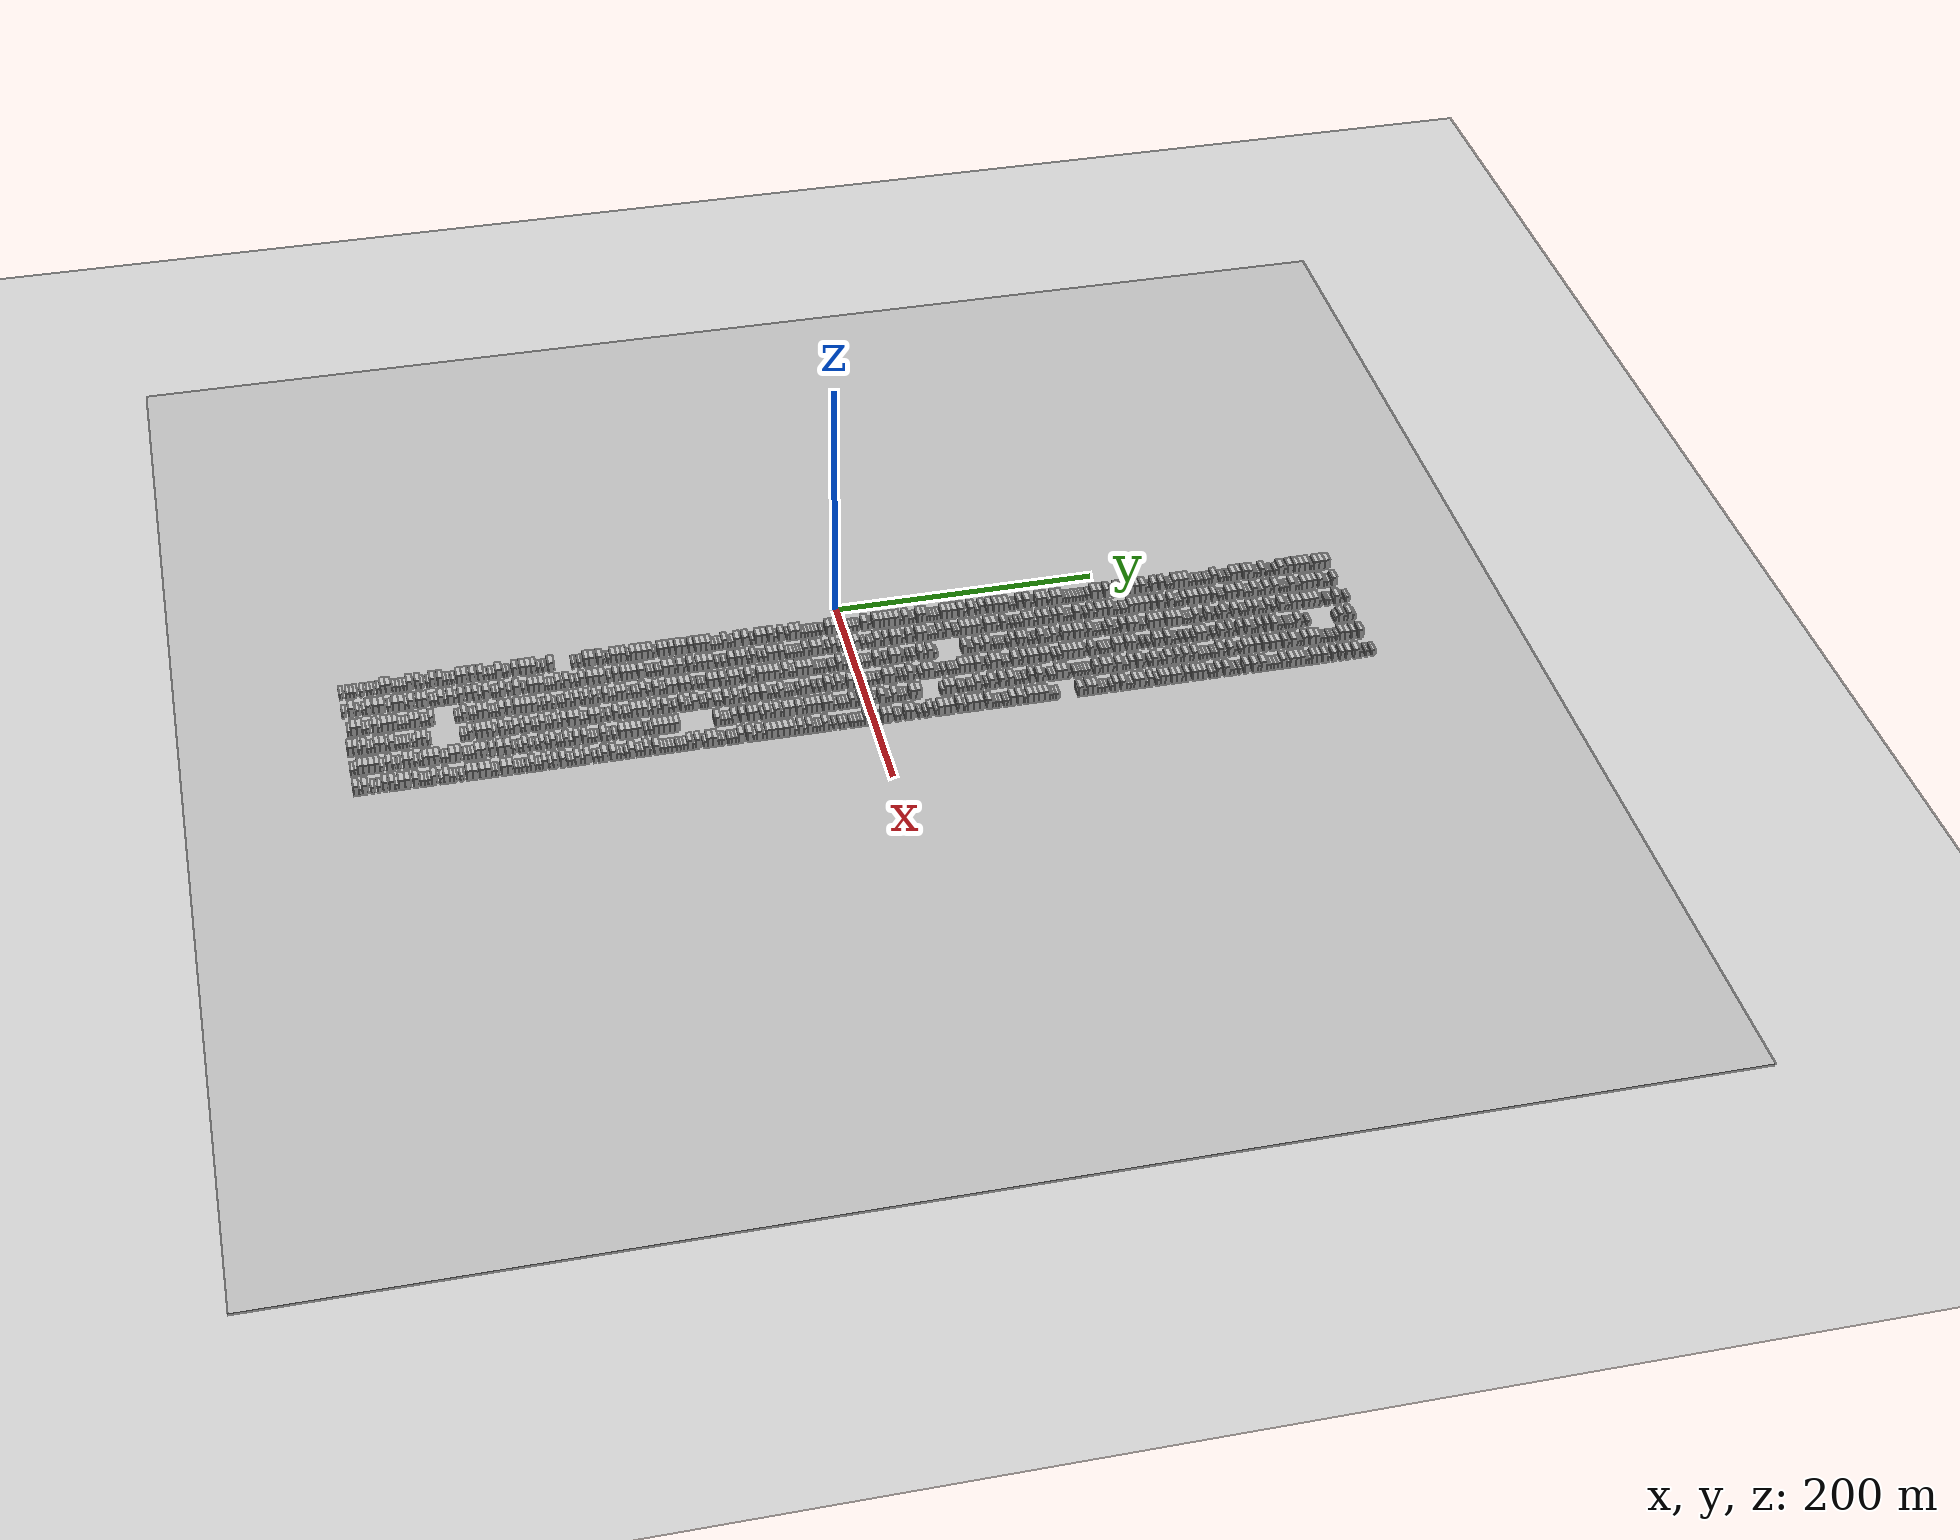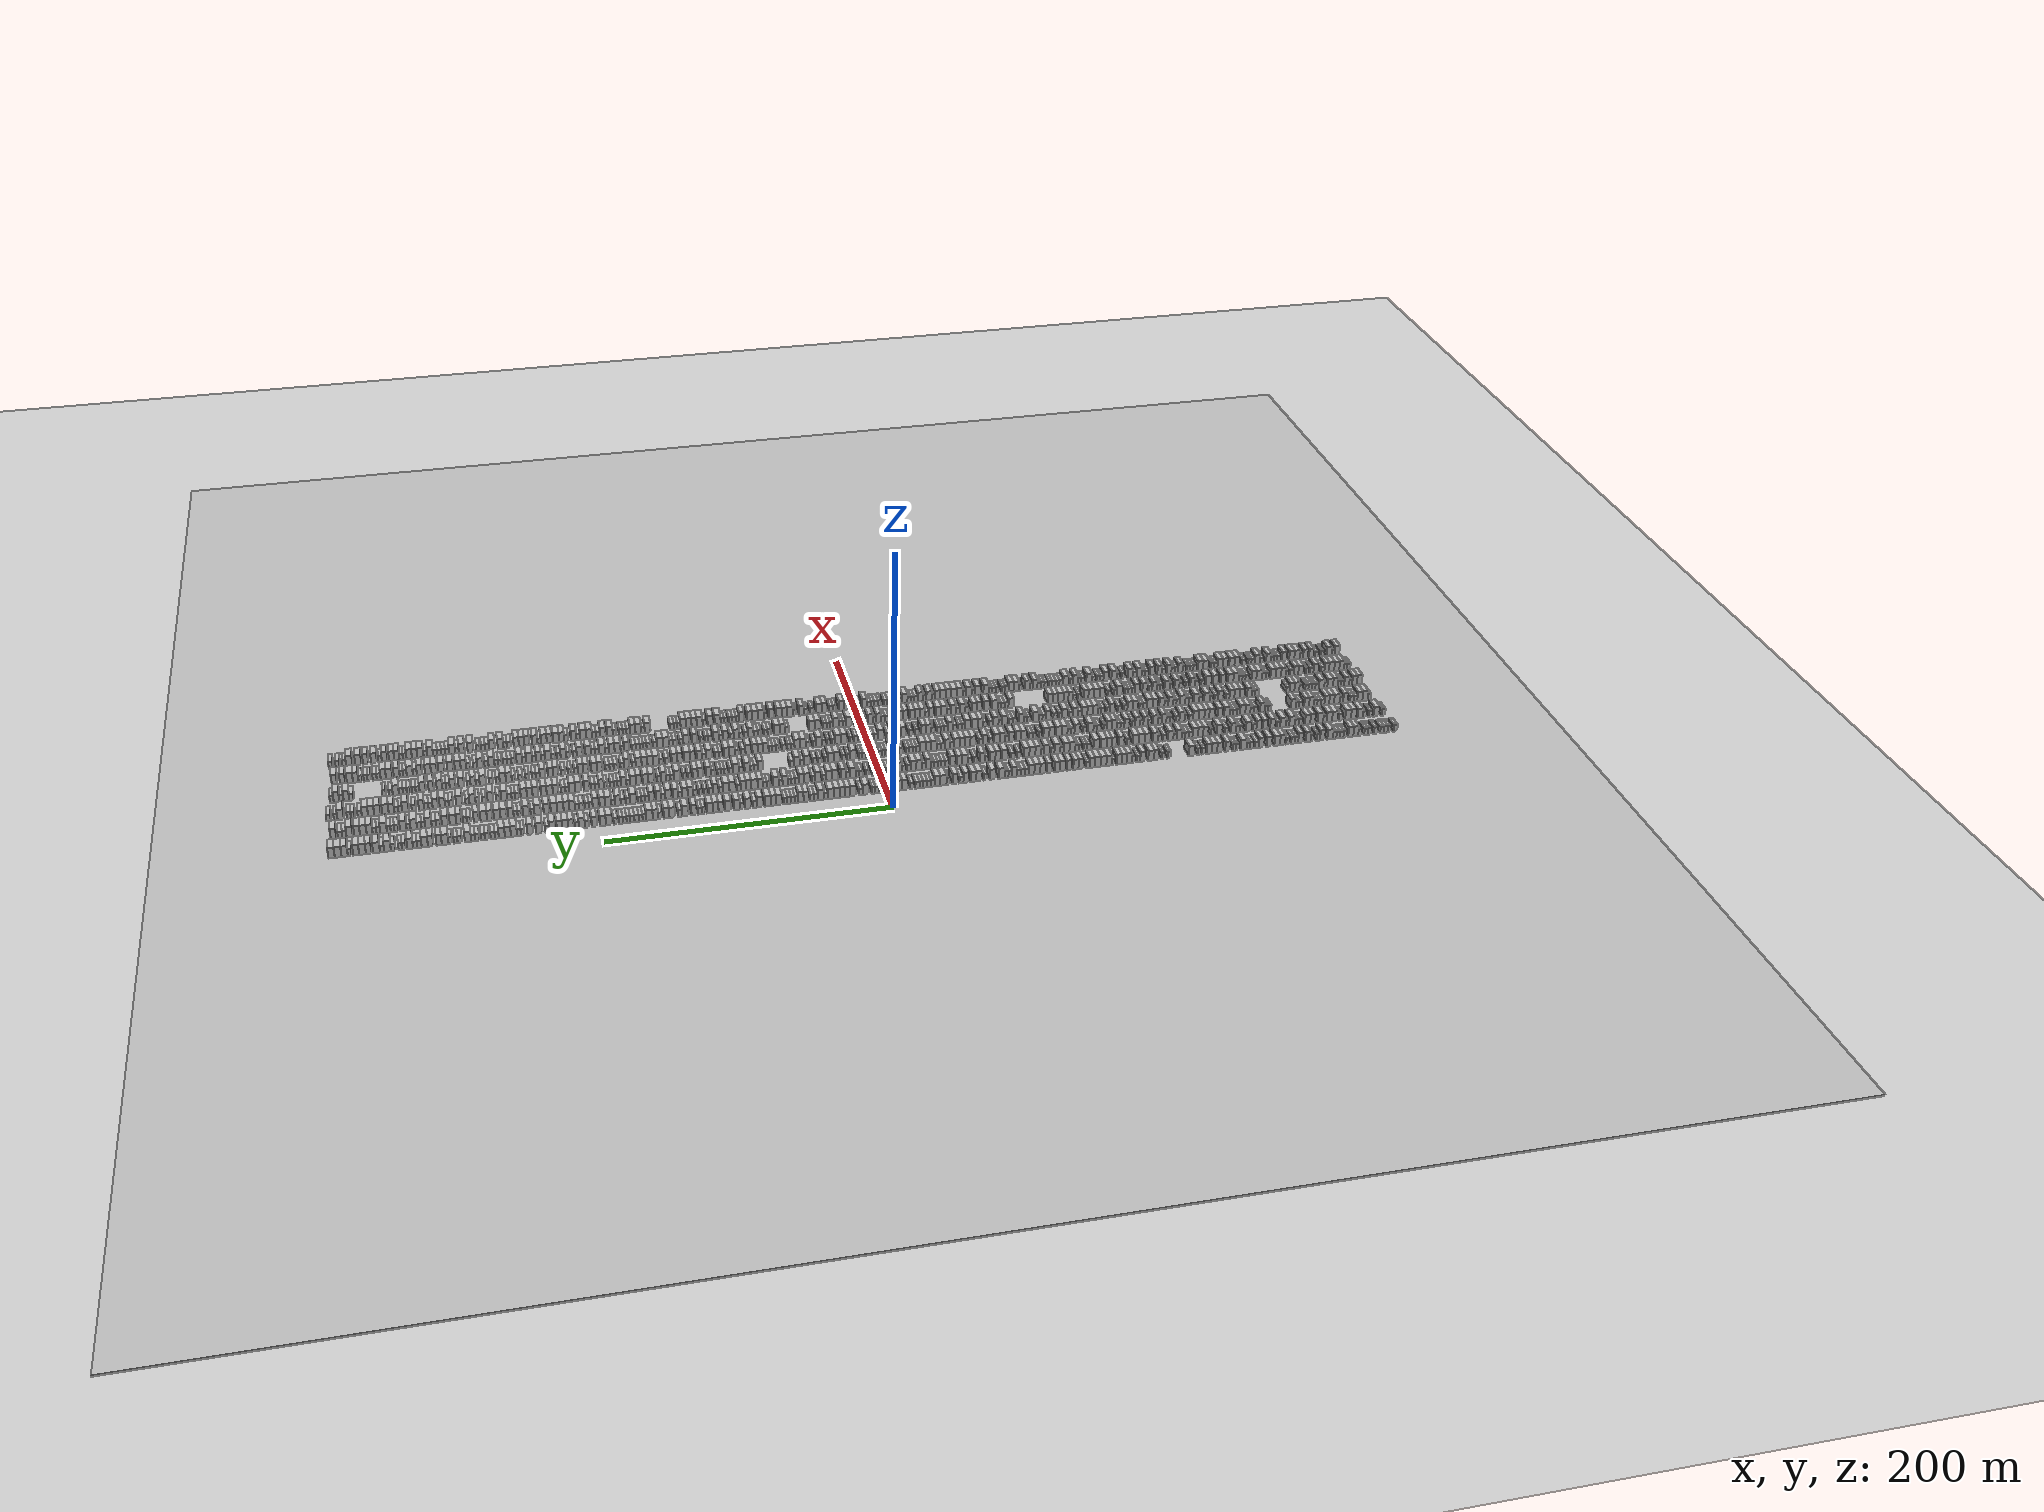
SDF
<?xml version="1.0" encoding="utf-8"?>

<sdf version="1.6">

   <world name="default">

      <gui fullscreen="0">

         <camera name="user_camera">

            <pose>-15 0 4.57585 0 0 0</pose>

            <view_controller>orbit</view_controller>

         </camera>

      </gui>

      <scene>

         <sky>

           <clouds>

             <speed>12</speed>

           </clouds>

         </sky>

         <ambient>0.4 0.4 0.4 1</ambient>

         <background>0.7 0.7 0.7 1</background>

         <shadows>1</shadows>

      </scene>

      <gravity>0 0 -9.8066</gravity>

      <magnetic_field>6e-06 2.3e-05 -4.2e-05</magnetic_field>

      <physics default="0" name="default_physics" type="ode">

         <ode>

            <solver>

               <type>quick</type>

               <iters>10</iters>

               <sor>1.0</sor>

               <use_dynamic_moi_rescaling>0</use_dynamic_moi_rescaling>

            </solver>

            <constraints>

               <cfm>0</cfm>

               <erp>0.2</erp>

               <contact_max_correcting_vel>100</contact_max_correcting_vel>

               <contact_surface_layer>0.001</contact_surface_layer>

            </constraints>

         </ode>

         <max_step_size>0.004</max_step_size>

         <real_time_factor>1</real_time_factor>

         <real_time_update_rate>250</real_time_update_rate>

      </physics>

      <light name="sun" type="directional">

         <cast_shadows>1</cast_shadows>

         <pose>0 0 10 0 0 0</pose>

         <diffuse>0.8 0.8 0.8 1</diffuse>

         <specular>0.2 0.2 0.2 1</specular>

         <attenuation>

            <range>1000</range>

            <constant>0.9</constant>

            <linear>0.01</linear>

            <quadratic>0.001</quadratic>

         </attenuation>

         <direction>-0.5 0.1 -0.9</direction>

      </light>

      <include>

         <name>ground_plane_1</name>

         <uri>model://HANNAS_ground_plane</uri>

         <pose>0 0 0  0 0 0</pose>

      </include>

      <include>

         <name>ground_plane_2</name>

         <uri>model://HANNAS_ground_plane</uri>

         <pose>100 0 0  0 0 0</pose>

      </include>

      <model name="building_1">

         <static>1</static>

         <pose frame="">25.0000 -378.5996 0 0.000000 0.000000 0.000000</pose>

         <link name="link">

            <pose frame="">0 0 3.00 0 0 0</pose>

            <collision name="collision">

               <geometry>

                  <box>

                     <size>10.0000 2.8008 6.0000</size>

                  </box>

               </geometry>

               <max_contacts>10</max_contacts>

               <surface>

                  <contact>

                     <ode/>

                  </contact>

                  <bounce/>

                  <friction>

                     <torsional>

                        <ode/>

                     </torsional>

                     <ode/>

                  </friction>

               </surface>

            </collision>

            <visual name="visual">

               <cast_shadows>0</cast_shadows>

               <geometry>

                  <box>

                     <size>10.0000 2.8008 6.0000</size>

                  </box>

               </geometry>

               <material>

                  <script>

                     <uri>model://HANNAS_wall/materials/scripts</uri>

                     <uri>model://HANNAS_wall/materials/textures</uri>

                     <name>vrc/HANNAS_wall</name>

                  </script>

               </material>

            </visual>

            <self_collide>0</self_collide>

            <enable_wind>0</enable_wind>

            <kinematic>0</kinematic>

         </link>

      </model>

      <model name="building_2">

         <static>1</static>

         <pose frame="">25.0000 -373.8620 0 0.000000 0.000000 0.000000</pose>

         <link name="link">

            <pose frame="">0 0 3.00 0 0 0</pose>

            <collision name="collision">

               <geometry>

                  <box>

                     <size>10.0000 2.6746 6.0000</size>

                  </box>

               </geometry>

               <max_contacts>10</max_contacts>

               <surface>

                  <contact>

                     <ode/>

                  </contact>

                  <bounce/>

                  <friction>

                     <torsional>

                        <ode/>

                     </torsional>

                     <ode/>

                  </friction>

               </surface>

            </collision>

            <visual name="visual">

               <cast_shadows>0</cast_shadows>

               <geometry>

                  <box>

                     <size>10.0000 2.6746 6.0000</size>

                  </box>

               </geometry>

               <material>

                  <script>

                     <uri>model://HANNAS_wall/materials/scripts</uri>

                     <uri>model://HANNAS_wall/materials/textures</uri>

                     <name>vrc/HANNAS_wall</name>

                  </script>

               </material>

            </visual>

            <self_collide>0</self_collide>

            <enable_wind>0</enable_wind>

            <kinematic>0</kinematic>

         </link>

      </model>

      <model name="building_3">

         <static>1</static>

         <pose frame="">25.0000 -371.0558 0 0.000000 0.000000 0.000000</pose>

         <link name="link">

            <pose frame="">0 0 3.00 0 0 0</pose>

            <collision name="collision">

               <geometry>

                  <box>

                     <size>10.0000 2.9377 6.0000</size>

                  </box>

               </geometry>

               <max_contacts>10</max_contacts>

               <surface>

                  <contact>

                     <ode/>

                  </contact>

                  <bounce/>

                  <friction>

                     <torsional>

                        <ode/>

                     </torsional>

                     <ode/>

                  </friction>

               </surface>

            </collision>

            <visual name="visual">

               <cast_shadows>0</cast_shadows>

               <geometry>

                  <box>

                     <size>10.0000 2.9377 6.0000</size>

                  </box>

               </geometry>

               <material>

                  <script>

                     <uri>model://HANNAS_wall/materials/scripts</uri>

                     <uri>model://HANNAS_wall/materials/textures</uri>

                     <name>vrc/HANNAS_wall</name>

                  </script>

               </material>

            </visual>

            <self_collide>0</self_collide>

            <enable_wind>0</enable_wind>

            <kinematic>0</kinematic>

         </link>

      </model>

      <model name="building_4">

         <static>1</static>

         <pose frame="">25.0000 -368.2185 0 0.000000 0.000000 0.000000</pose>

         <link name="link">

            <pose frame="">0 0 3.00 0 0 0</pose>

            <collision name="collision">

               <geometry>

                  <box>

                     <size>10.0000 2.7370 6.0000</size>

                  </box>

               </geometry>

               <max_contacts>10</max_contacts>

               <surface>

                  <contact>

                     <ode/>

                  </contact>

                  <bounce/>

                  <friction>

                     <torsional>

                        <ode/>

                     </torsional>

                     <ode/>

                  </friction>

               </surface>

            </collision>

            <visual name="visual">

               <cast_shadows>0</cast_shadows>

               <geometry>

                  <box>

                     <size>10.0000 2.7370 6.0000</size>

                  </box>

               </geometry>

               <material>

                  <script>

                     <uri>model://HANNAS_wall/materials/scripts</uri>

                     <uri>model://HANNAS_wall/materials/textures</uri>

                     <name>vrc/HANNAS_wall</name>

                  </script>

               </material>

            </visual>

            <self_collide>0</self_collide>

            <enable_wind>0</enable_wind>

            <kinematic>0</kinematic>

         </link>

      </model>

      <model name="building_5">

         <static>1</static>

         <pose frame="">25.0000 -363.3761 0 0.000000 0.000000 0.000000</pose>

         <link name="link">

            <pose frame="">0 0 3.00 0 0 0</pose>

            <collision name="collision">

               <geometry>

                  <box>

                     <size>10.0000 2.9478 6.0000</size>

                  </box>

               </geometry>

               <max_contacts>10</max_contacts>

               <surface>

                  <contact>

                     <ode/>

                  </contact>

                  <bounce/>

                  <friction>

                     <torsional>

                        <ode/>

                     </torsional>

                     <ode/>

                  </friction>

               </surface>

            </collision>

            <visual name="visual">

               <cast_shadows>0</cast_shadows>

               <geometry>

                  <box>

                     <size>10.0000 2.9478 6.0000</size>

                  </box>

               </geometry>

               <material>

                  <script>

                     <uri>model://HANNAS_wall/materials/scripts</uri>

                     <uri>model://HANNAS_wall/materials/textures</uri>

                     <name>vrc/HANNAS_wall</name>

                  </script>

               </material>

            </visual>

            <self_collide>0</self_collide>

            <enable_wind>0</enable_wind>

            <kinematic>0</kinematic>

         </link>

      </model>

      <model name="building_6">

         <static>1</static>

         <pose frame="">25.0000 -358.5464 0 0.000000 0.000000 0.000000</pose>

         <link name="link">

            <pose frame="">0 0 3.00 0 0 0</pose>

            <collision name="collision">

               <geometry>

                  <box>

                     <size>10.0000 2.7116 6.0000</size>

                  </box>

               </geometry>

               <max_contacts>10</max_contacts>

               <surface>

                  <contact>

                     <ode/>

                  </contact>

                  <bounce/>

                  <friction>

                     <torsional>

                        <ode/>

                     </torsional>

                     <ode/>

                  </friction>

               </surface>

            </collision>

            <visual name="visual">

               <cast_shadows>0</cast_shadows>

               <geometry>

                  <box>

                     <size>10.0000 2.7116 6.0000</size>

                  </box>

               </geometry>

               <material>

                  <script>

                     <uri>model://HANNAS_wall/materials/scripts</uri>

                     <uri>model://HANNAS_wall/materials/textures</uri>

                     <name>vrc/HANNAS_wall</name>

                  </script>

               </material>

            </visual>

            <self_collide>0</self_collide>

            <enable_wind>0</enable_wind>

            <kinematic>0</kinematic>

         </link>

      </model>

      <model name="building_7">

         <static>1</static>

         <pose frame="">25.0000 -355.8268 0 0.000000 0.000000 0.000000</pose>

         <link name="link">

            <pose frame="">0 0 3.00 0 0 0</pose>

            <collision name="collision">

               <geometry>

                  <box>

                     <size>10.0000 2.7277 6.0000</size>

                  </box>

               </geometry>

               <max_contacts>10</max_contacts>

               <surface>

                  <contact>

                     <ode/>

                  </contact>

                  <bounce/>

                  <friction>

                     <torsional>

                        <ode/>

                     </torsional>

                     <ode/>

                  </friction>

               </surface>

            </collision>

            <visual name="visual">

               <cast_shadows>0</cast_shadows>

               <geometry>

                  <box>

                     <size>10.0000 2.7277 6.0000</size>

                  </box>

               </geometry>

               <material>

                  <script>

                     <uri>model://HANNAS_wall/materials/scripts</uri>

                     <uri>model://HANNAS_wall/materials/textures</uri>

                     <name>vrc/HANNAS_wall</name>

                  </script>

               </material>

            </visual>

            <self_collide>0</self_collide>

            <enable_wind>0</enable_wind>

            <kinematic>0</kinematic>

         </link>

      </model>

      <model name="building_8">

         <static>1</static>

         <pose frame="">25.0000 -351.0859 0 0.000000 0.000000 0.000000</pose>

         <link name="link">

            <pose frame="">0 0 3.00 0 0 0</pose>

            <collision name="collision">

               <geometry>

                  <box>

                     <size>10.0000 2.7541 6.0000</size>

                  </box>

               </geometry>

               <max_contacts>10</max_contacts>

               <surface>

                  <contact>

                     <ode/>

                  </contact>

                  <bounce/>

                  <friction>

                     <torsional>

                        <ode/>

                     </torsional>

                     <ode/>

                  </friction>

               </surface>

            </collision>

            <visual name="visual">

               <cast_shadows>0</cast_shadows>

               <geometry>

                  <box>

                     <size>10.0000 2.7541 6.0000</size>

                  </box>

               </geometry>

               <material>

                  <script>

                     <uri>model://HANNAS_wall/materials/scripts</uri>

                     <uri>model://HANNAS_wall/materials/textures</uri>

                     <name>vrc/HANNAS_wall</name>

                  </script>

               </material>

            </visual>

            <self_collide>0</self_collide>

            <enable_wind>0</enable_wind>

            <kinematic>0</kinematic>

         </link>

      </model>

      <model name="building_9">

         <static>1</static>

         <pose frame="">25.0000 -347.8685 0 0.000000 0.000000 0.000000</pose>

         <link name="link">

            <pose frame="">0 0 4.50 0 0 0</pose>

            <collision name="collision">

               <geometry>

                  <box>

                     <size>10.0000 3.6805 9.0000</size>

                  </box>

               </geometry>

               <max_contacts>10</max_contacts>

               <surface>

                  <contact>

                     <ode/>

                  </contact>

                  <bounce/>

                  <friction>

                     <torsional>

                        <ode/>

                     </torsional>

                     <ode/>

                  </friction>

               </surface>

            </collision>

            <visual name="visual">

               <cast_shadows>0</cast_shadows>

               <geometry>

                  <box>

                     <size>10.0000 3.6805 9.0000</size>

                  </box>

               </geometry>

               <material>

                  <script>

                     <uri>model://HANNAS_wall/materials/scripts</uri>

                     <uri>model://HANNAS_wall/materials/textures</uri>

                     <name>vrc/HANNAS_wall</name>

                  </script>

               </material>

            </visual>

            <self_collide>0</self_collide>

            <enable_wind>0</enable_wind>

            <kinematic>0</kinematic>

         </link>

      </model>

      <model name="building_10">

         <static>1</static>

         <pose frame="">25.0000 -344.0556 0 0.000000 0.000000 0.000000</pose>

         <link name="link">

            <pose frame="">0 0 4.50 0 0 0</pose>

            <collision name="collision">

               <geometry>

                  <box>

                     <size>10.0000 3.9455 9.0000</size>

                  </box>

               </geometry>

               <max_contacts>10</max_contacts>

               <surface>

                  <contact>

                     <ode/>

                  </contact>

                  <bounce/>

                  <friction>

                     <torsional>

                        <ode/>

                     </torsional>

                     <ode/>

                  </friction>

               </surface>

            </collision>

            <visual name="visual">

               <cast_shadows>0</cast_shadows>

               <geometry>

                  <box>

                     <size>10.0000 3.9455 9.0000</size>

                  </box>

               </geometry>

               <material>

                  <script>

                     <uri>model://HANNAS_wall/materials/scripts</uri>

                     <uri>model://HANNAS_wall/materials/textures</uri>

                     <name>vrc/HANNAS_wall</name>

                  </script>

               </material>

            </visual>

            <self_collide>0</self_collide>

            <enable_wind>0</enable_wind>

            <kinematic>0</kinematic>

         </link>

      </model>

      <model name="building_11">

         <static>1</static>

         <pose frame="">25.0000 -339.7486 0 0.000000 0.000000 0.000000</pose>

         <link name="link">

            <pose frame="">0 0 3.00 0 0 0</pose>

            <collision name="collision">

               <geometry>

                  <box>

                     <size>10.0000 2.6686 6.0000</size>

                  </box>

               </geometry>

               <max_contacts>10</max_contacts>

               <surface>

                  <contact>

                     <ode/>

                  </contact>

                  <bounce/>

                  <friction>

                     <torsional>

                        <ode/>

                     </torsional>

                     <ode/>

                  </friction>

               </surface>

            </collision>

            <visual name="visual">

               <cast_shadows>0</cast_shadows>

               <geometry>

                  <box>

                     <size>10.0000 2.6686 6.0000</size>

                  </box>

               </geometry>

               <material>

                  <script>

                     <uri>model://HANNAS_wall/materials/scripts</uri>

                     <uri>model://HANNAS_wall/materials/textures</uri>

                     <name>vrc/HANNAS_wall</name>

                  </script>

               </material>

            </visual>

            <self_collide>0</self_collide>

            <enable_wind>0</enable_wind>

            <kinematic>0</kinematic>

         </link>

      </model>

      <model name="building_12">

         <static>1</static>

         <pose frame="">25.0000 -337.0450 0 0.000000 0.000000 0.000000</pose>

         <link name="link">

            <pose frame="">0 0 3.00 0 0 0</pose>

            <collision name="collision">

               <geometry>

                  <box>

                     <size>10.0000 2.7386 6.0000</size>

                  </box>

               </geometry>

               <max_contacts>10</max_contacts>

               <surface>

                  <contact>

                     <ode/>

                  </contact>

                  <bounce/>

                  <friction>

                     <torsional>

                        <ode/>

                     </torsional>

                     <ode/>

                  </friction>

               </surface>

            </collision>

            <visual name="visual">

               <cast_shadows>0</cast_shadows>

               <geometry>

                  <box>

                     <size>10.0000 2.7386 6.0000</size>

                  </box>

               </geometry>

               <material>

                  <script>

                     <uri>model://HANNAS_wall/materials/scripts</uri>

                     <uri>model://HANNAS_wall/materials/textures</uri>

                     <name>vrc/HANNAS_wall</name>

                  </script>

               </material>

            </visual>

            <self_collide>0</self_collide>

            <enable_wind>0</enable_wind>

            <kinematic>0</kinematic>

         </link>

      </model>

      <model name="building_13">

         <static>1</static>

         <pose frame="">25.0000 -334.2865 0 0.000000 0.000000 0.000000</pose>

         <link name="link">

            <pose frame="">0 0 3.00 0 0 0</pose>

            <collision name="collision">

               <geometry>

                  <box>

                     <size>10.0000 2.7783 6.0000</size>

                  </box>

               </geometry>

               <max_contacts>10</max_contacts>

               <surface>

                  <contact>

                     <ode/>

                  </contact>

                  <bounce/>

                  <friction>

                     <torsional>

                        <ode/>

                     </torsional>

                     <ode/>

                  </friction>

               </surface>

            </collision>

            <visual name="visual">

               <cast_shadows>0</cast_shadows>

               <geometry>

                  <box>

                     <size>10.0000 2.7783 6.0000</size>

                  </box>

               </geometry>

               <material>

                  <script>

                     <uri>model://HANNAS_wall/materials/scripts</uri>

                     <uri>model://HANNAS_wall/materials/textures</uri>

                     <name>vrc/HANNAS_wall</name>

                  </script>

               </material>

            </visual>

            <self_collide>0</self_collide>

            <enable_wind>0</enable_wind>

            <kinematic>0</kinematic>

         </link>

      </model>

      <model name="building_14">

         <static>1</static>

         <pose frame="">25.0000 -331.5499 0 0.000000 0.000000 0.000000</pose>

         <link name="link">

            <pose frame="">0 0 3.00 0 0 0</pose>

            <collision name="collision">

               <geometry>

                  <box>

                     <size>10.0000 2.6951 6.0000</size>

                  </box>

               </geometry>

               <max_contacts>10</max_contacts>

               <surface>

                  <contact>

                     <ode/>

                  </contact>

                  <bounce/>

                  <friction>

                     <torsional>

                        <ode/>

                     </torsional>

                     <ode/>

                  </friction>

               </surface>

            </collision>

            <visual name="visual">

               <cast_shadows>0</cast_shadows>

               <geometry>

                  <box>

                     <size>10.0000 2.6951 6.0000</size>

                  </box>

               </geometry>

               <material>

                  <script>

                     <uri>model://HANNAS_wall/materials/scripts</uri>

                     <uri>model://HANNAS_wall/materials/textures</uri>

                     <name>vrc/HANNAS_wall</name>

                  </script>

               </material>

            </visual>

            <self_collide>0</self_collide>

            <enable_wind>0</enable_wind>

            <kinematic>0</kinematic>

         </link>

      </model>

      <model name="building_15">

         <static>1</static>

         <pose frame="">25.0000 -328.0849 0 0.000000 0.000000 0.000000</pose>

         <link name="link">

            <pose frame="">0 0 4.50 0 0 0</pose>

            <collision name="collision">

               <geometry>

                  <box>

                     <size>10.0000 4.2349 9.0000</size>

                  </box>

               </geometry>

               <max_contacts>10</max_contacts>

               <surface>

                  <contact>

                     <ode/>

                  </contact>

                  <bounce/>

                  <friction>

                     <torsional>

                        <ode/>

                     </torsional>

                     <ode/>

                  </friction>

               </surface>

            </collision>

            <visual name="visual">

               <cast_shadows>0</cast_shadows>

               <geometry>

                  <box>

                     <size>10.0000 4.2349 9.0000</size>

                  </box>

               </geometry>

               <material>

                  <script>

                     <uri>model://HANNAS_wall/materials/scripts</uri>

                     <uri>model://HANNAS_wall/materials/textures</uri>

                     <name>vrc/HANNAS_wall</name>

                  </script>

               </material>

            </visual>

            <self_collide>0</self_collide>

            <enable_wind>0</enable_wind>

            <kinematic>0</kinematic>

         </link>

      </model>

      <model name="building_16">

         <static>1</static>

         <pose frame="">25.0000 -322.0957 0 0.000000 0.000000 0.000000</pose>

         <link name="link">

            <pose frame="">0 0 4.50 0 0 0</pose>

            <collision name="collision">

               <geometry>

                  <box>

                     <size>10.0000 3.7436 9.0000</size>

                  </box>

               </geometry>

               <max_contacts>10</max_contacts>

               <surface>

                  <contact>

                     <ode/>

                  </contact>

                  <bounce/>

                  <friction>

                     <torsional>

                        <ode/>

                     </torsional>

                     <ode/>

                  </friction>

               </surface>

            </collision>

            <visual name="visual">

               <cast_shadows>0</cast_shadows>

               <geometry>

                  <box>

                     <size>10.0000 3.7436 9.0000</size>

                  </box>

               </geometry>

               <material>

                  <script>

                     <uri>model://HANNAS_wall/materials/scripts</uri>

                     <uri>model://HANNAS_wall/materials/textures</uri>

                     <name>vrc/HANNAS_wall</name>

                  </script>

               </material>

            </visual>

            <self_collide>0</self_collide>

            <enable_wind>0</enable_wind>

            <kinematic>0</kinematic>

         </link>

      </model>

      <model name="building_17">

         <static>1</static>

         <pose frame="">25.0000 -318.9262 0 0.000000 0.000000 0.000000</pose>

         <link name="link">

            <pose frame="">0 0 3.00 0 0 0</pose>

            <collision name="collision">

               <geometry>

                  <box>

                     <size>10.0000 2.5953 6.0000</size>

                  </box>

               </geometry>

               <max_contacts>10</max_contacts>

               <surface>

                  <contact>

                     <ode/>

                  </contact>

                  <bounce/>

                  <friction>

                     <torsional>

                        <ode/>

                     </torsional>

                     <ode/>

                  </friction>

               </surface>

            </collision>

            <visual name="visual">

               <cast_shadows>0</cast_shadows>

               <geometry>

                  <box>

                     <size>10.0000 2.5953 6.0000</size>

                  </box>

               </geometry>

               <material>

                  <script>

                     <uri>model://HANNAS_wall/materials/scripts</uri>

                     <uri>model://HANNAS_wall/materials/textures</uri>

                     <name>vrc/HANNAS_wall</name>

                  </script>

               </material>

            </visual>

            <self_collide>0</self_collide>

            <enable_wind>0</enable_wind>

            <kinematic>0</kinematic>

         </link>

      </model>

      <model name="building_18">

         <static>1</static>

         <pose frame="">25.0000 -314.3590 0 0.000000 0.000000 0.000000</pose>

         <link name="link">

            <pose frame="">0 0 3.00 0 0 0</pose>

            <collision name="collision">

               <geometry>

                  <box>

                     <size>10.0000 2.5390 6.0000</size>

                  </box>

               </geometry>

               <max_contacts>10</max_contacts>

               <surface>

                  <contact>

                     <ode/>

                  </contact>

                  <bounce/>

                  <friction>

                     <torsional>

                        <ode/>

                     </torsional>

                     <ode/>

                  </friction>

               </surface>

            </collision>

            <visual name="visual">

               <cast_shadows>0</cast_shadows>

               <geometry>

                  <box>

                     <size>10.0000 2.5390 6.0000</size>

                  </box>

               </geometry>

               <material>

                  <script>

                     <uri>model://HANNAS_wall/materials/scripts</uri>

                     <uri>model://HANNAS_wall/materials/textures</uri>

                     <name>vrc/HANNAS_wall</name>

                  </script>

               </material>

            </visual>

            <self_collide>0</self_collide>

            <enable_wind>0</enable_wind>

            <kinematic>0</kinematic>

         </link>

      </model>

      <model name="building_19">

         <static>1</static>

         <pose frame="">25.0000 -311.1639 0 0.000000 0.000000 0.000000</pose>

         <link name="link">

            <pose frame="">0 0 4.50 0 0 0</pose>

            <collision name="collision">

               <geometry>

                  <box>

                     <size>10.0000 3.8511 9.0000</size>

                  </box>

               </geometry>

               <max_contacts>10</max_contacts>

               <surface>

                  <contact>

                     <ode/>

                  </contact>

                  <bounce/>

                  <friction>

                     <torsional>

                        <ode/>

                     </torsional>

                     <ode/>

                  </friction>

               </surface>

            </collision>

            <visual name="visual">

               <cast_shadows>0</cast_shadows>

               <geometry>

                  <box>

                     <size>10.0000 3.8511 9.0000</size>

                  </box>

               </geometry>

               <material>

                  <script>

                     <uri>model://HANNAS_wall/materials/scripts</uri>

                     <uri>model://HANNAS_wall/materials/textures</uri>

                     <name>vrc/HANNAS_wall</name>

                  </script>

               </material>

            </visual>

            <self_collide>0</self_collide>

            <enable_wind>0</enable_wind>

            <kinematic>0</kinematic>

         </link>

      </model>

      <model name="building_20">

         <static>1</static>

         <pose frame="">25.0000 -305.4070 0 0.000000 0.000000 0.000000</pose>

         <link name="link">

            <pose frame="">0 0 4.50 0 0 0</pose>

            <collision name="collision">

               <geometry>

                  <box>

                     <size>10.0000 3.6628 9.0000</size>

                  </box>

               </geometry>

               <max_contacts>10</max_contacts>

               <surface>

                  <contact>

                     <ode/>

                  </contact>

                  <bounce/>

                  <friction>

                     <torsional>

                        <ode/>

                     </torsional>

                     <ode/>

                  </friction>

               </surface>

            </collision>

            <visual name="visual">

               <cast_shadows>0</cast_shadows>

               <geometry>

                  <box>

                     <size>10.0000 3.6628 9.0000</size>

                  </box>

               </geometry>

               <material>

                  <script>

                     <uri>model://HANNAS_wall/materials/scripts</uri>

                     <uri>model://HANNAS_wall/materials/textures</uri>

                     <name>vrc/HANNAS_wall</name>

                  </script>

               </material>

            </visual>

            <self_collide>0</self_collide>

            <enable_wind>0</enable_wind>

            <kinematic>0</kinematic>

         </link>

      </model>

      <model name="building_21">

         <static>1</static>

         <pose frame="">25.0000 -302.2598 0 0.000000 0.000000 0.000000</pose>

         <link name="link">

            <pose frame="">0 0 3.00 0 0 0</pose>

            <collision name="collision">

               <geometry>

                  <box>

                     <size>10.0000 2.6316 6.0000</size>

                  </box>

               </geometry>

               <max_contacts>10</max_contacts>

               <surface>

                  <contact>

                     <ode/>

                  </contact>

                  <bounce/>

                  <friction>

                     <torsional>

                        <ode/>

                     </torsional>

                     <ode/>

                  </friction>

               </surface>

            </collision>

            <visual name="visual">

               <cast_shadows>0</cast_shadows>

               <geometry>

                  <box>

                     <size>10.0000 2.6316 6.0000</size>

                  </box>

               </geometry>

               <material>

                  <script>

                     <uri>model://HANNAS_wall/materials/scripts</uri>

                     <uri>model://HANNAS_wall/materials/textures</uri>

                     <name>vrc/HANNAS_wall</name>

                  </script>

               </material>

            </visual>

            <self_collide>0</self_collide>

            <enable_wind>0</enable_wind>

            <kinematic>0</kinematic>

         </link>

      </model>

      <model name="building_22">

         <static>1</static>

         <pose frame="">25.0000 -299.5827 0 0.000000 0.000000 0.000000</pose>

         <link name="link">

            <pose frame="">0 0 3.00 0 0 0</pose>

            <collision name="collision">

               <geometry>

                  <box>

                     <size>10.0000 2.7226 6.0000</size>

                  </box>

               </geometry>

               <max_contacts>10</max_contacts>

               <surface>

                  <contact>

                     <ode/>

                  </contact>

                  <bounce/>

                  <friction>

                     <torsional>

                        <ode/>

                     </torsional>

                     <ode/>

                  </friction>

               </surface>

            </collision>

            <visual name="visual">

               <cast_shadows>0</cast_shadows>

               <geometry>

                  <box>

                     <size>10.0000 2.7226 6.0000</size>

                  </box>

               </geometry>

               <material>

                  <script>

                     <uri>model://HANNAS_wall/materials/scripts</uri>

                     <uri>model://HANNAS_wall/materials/textures</uri>

                     <name>vrc/HANNAS_wall</name>

                  </script>

               </material>

            </visual>

            <self_collide>0</self_collide>

            <enable_wind>0</enable_wind>

            <kinematic>0</kinematic>

         </link>

      </model>

      <model name="building_23">

         <static>1</static>

         <pose frame="">25.0000 -295.8306 0 0.000000 0.000000 0.000000</pose>

         <link name="link">

            <pose frame="">0 0 3.00 0 0 0</pose>

            <collision name="collision">

               <geometry>

                  <box>

                     <size>10.0000 2.7815 6.0000</size>

                  </box>

               </geometry>

               <max_contacts>10</max_contacts>

               <surface>

                  <contact>

                     <ode/>

                  </contact>

                  <bounce/>

                  <friction>

                     <torsional>

                        <ode/>

                     </torsional>

                     <ode/>

                  </friction>

               </surface>

            </collision>

            <visual name="visual">

               <cast_shadows>0</cast_shadows>

               <geometry>

                  <box>

                     <size>10.0000 2.7815 6.0000</size>

                  </box>

               </geometry>

               <material>

                  <script>

                     <uri>model://HANNAS_wall/materials/scripts</uri>

                     <uri>model://HANNAS_wall/materials/textures</uri>

                     <name>vrc/HANNAS_wall</name>

                  </script>

               </material>

            </visual>

            <self_collide>0</self_collide>

            <enable_wind>0</enable_wind>

            <kinematic>0</kinematic>

         </link>

      </model>

      <model name="building_24">

         <static>1</static>

         <pose frame="">25.0000 -291.5370 0 0.000000 0.000000 0.000000</pose>

         <link name="link">

            <pose frame="">0 0 4.50 0 0 0</pose>

            <collision name="collision">

               <geometry>

                  <box>

                     <size>10.0000 3.8057 9.0000</size>

                  </box>

               </geometry>

               <max_contacts>10</max_contacts>

               <surface>

                  <contact>

                     <ode/>

                  </contact>

                  <bounce/>

                  <friction>

                     <torsional>

                        <ode/>

                     </torsional>

                     <ode/>

                  </friction>

               </surface>

            </collision>

            <visual name="visual">

               <cast_shadows>0</cast_shadows>

               <geometry>

                  <box>

                     <size>10.0000 3.8057 9.0000</size>

                  </box>

               </geometry>

               <material>

                  <script>

                     <uri>model://HANNAS_wall/materials/scripts</uri>

                     <uri>model://HANNAS_wall/materials/textures</uri>

                     <name>vrc/HANNAS_wall</name>

                  </script>

               </material>

            </visual>

            <self_collide>0</self_collide>

            <enable_wind>0</enable_wind>

            <kinematic>0</kinematic>

         </link>

      </model>

      <model name="building_25">

         <static>1</static>

         <pose frame="">25.0000 -287.5263 0 0.000000 0.000000 0.000000</pose>

         <link name="link">

            <pose frame="">0 0 4.50 0 0 0</pose>

            <collision name="collision">

               <geometry>

                  <box>

                     <size>10.0000 4.2157 9.0000</size>

                  </box>

               </geometry>

               <max_contacts>10</max_contacts>

               <surface>

                  <contact>

                     <ode/>

                  </contact>

                  <bounce/>

                  <friction>

                     <torsional>

                        <ode/>

                     </torsional>

                     <ode/>

                  </friction>

               </surface>

            </collision>

            <visual name="visual">

               <cast_shadows>0</cast_shadows>

               <geometry>

                  <box>

                     <size>10.0000 4.2157 9.0000</size>

                  </box>

               </geometry>

               <material>

                  <script>

                     <uri>model://HANNAS_wall/materials/scripts</uri>

                     <uri>model://HANNAS_wall/materials/textures</uri>

                     <name>vrc/HANNAS_wall</name>

                  </script>

               </material>

            </visual>

            <self_collide>0</self_collide>

            <enable_wind>0</enable_wind>

            <kinematic>0</kinematic>

         </link>

      </model>

      <model name="building_26">

         <static>1</static>

         <pose frame="">25.0000 -281.4180 0 0.000000 0.000000 0.000000</pose>

         <link name="link">

            <pose frame="">0 0 4.50 0 0 0</pose>

            <collision name="collision">

               <geometry>

                  <box>

                     <size>10.0000 4.0009 9.0000</size>

                  </box>

               </geometry>

               <max_contacts>10</max_contacts>

               <surface>

                  <contact>

                     <ode/>

                  </contact>

                  <bounce/>

                  <friction>

                     <torsional>

                        <ode/>

                     </torsional>

                     <ode/>

                  </friction>

               </surface>

            </collision>

            <visual name="visual">

               <cast_shadows>0</cast_shadows>

               <geometry>

                  <box>

                     <size>10.0000 4.0009 9.0000</size>

                  </box>

               </geometry>

               <material>

                  <script>

                     <uri>model://HANNAS_wall/materials/scripts</uri>

                     <uri>model://HANNAS_wall/materials/textures</uri>

                     <name>vrc/HANNAS_wall</name>

                  </script>

               </material>

            </visual>

            <self_collide>0</self_collide>

            <enable_wind>0</enable_wind>

            <kinematic>0</kinematic>

         </link>

      </model>

      <model name="building_27">

         <static>1</static>

         <pose frame="">25.0000 -275.4623 0 0.000000 0.000000 0.000000</pose>

         <link name="link">

            <pose frame="">0 0 4.50 0 0 0</pose>

            <collision name="collision">

               <geometry>

                  <box>

                     <size>10.0000 3.9105 9.0000</size>

                  </box>

               </geometry>

               <max_contacts>10</max_contacts>

               <surface>

                  <contact>

                     <ode/>

                  </contact>

                  <bounce/>

                  <friction>

                     <torsional>

                        <ode/>

                     </torsional>

                     <ode/>

                  </friction>

               </surface>

            </collision>

            <visual name="visual">

               <cast_shadows>0</cast_shadows>

               <geometry>

                  <box>

                     <size>10.0000 3.9105 9.0000</size>

                  </box>

               </geometry>

               <material>

                  <script>

                     <uri>model://HANNAS_wall/materials/scripts</uri>

                     <uri>model://HANNAS_wall/materials/textures</uri>

                     <name>vrc/HANNAS_wall</name>

                  </script>

               </material>

            </visual>

            <self_collide>0</self_collide>

            <enable_wind>0</enable_wind>

            <kinematic>0</kinematic>

         </link>

      </model>

      <model name="building_28">

         <static>1</static>

         <pose frame="">25.0000 -272.0385 0 0.000000 0.000000 0.000000</pose>

         <link name="link">

            <pose frame="">0 0 3.00 0 0 0</pose>

            <collision name="collision">

               <geometry>

                  <box>

                     <size>10.0000 2.9372 6.0000</size>

                  </box>

               </geometry>

               <max_contacts>10</max_contacts>

               <surface>

                  <contact>

                     <ode/>

                  </contact>

                  <bounce/>

                  <friction>

                     <torsional>

                        <ode/>

                     </torsional>

                     <ode/>

                  </friction>

               </surface>

            </collision>

            <visual name="visual">

               <cast_shadows>0</cast_shadows>

               <geometry>

                  <box>

                     <size>10.0000 2.9372 6.0000</size>

                  </box>

               </geometry>

               <material>

                  <script>

                     <uri>model://HANNAS_wall/materials/scripts</uri>

                     <uri>model://HANNAS_wall/materials/textures</uri>

                     <name>vrc/HANNAS_wall</name>

                  </script>

               </material>

            </visual>

            <self_collide>0</self_collide>

            <enable_wind>0</enable_wind>

            <kinematic>0</kinematic>

         </link>

      </model>

      <model name="building_29">

         <static>1</static>

         <pose frame="">25.0000 -268.1375 0 0.000000 0.000000 0.000000</pose>

         <link name="link">

            <pose frame="">0 0 3.00 0 0 0</pose>

            <collision name="collision">

               <geometry>

                  <box>

                     <size>10.0000 2.8648 6.0000</size>

                  </box>

               </geometry>

               <max_contacts>10</max_contacts>

               <surface>

                  <contact>

                     <ode/>

                  </contact>

                  <bounce/>

                  <friction>

                     <torsional>

                        <ode/>

                     </torsional>

                     <ode/>

                  </friction>

               </surface>

            </collision>

            <visual name="visual">

               <cast_shadows>0</cast_shadows>

               <geometry>

                  <box>

                     <size>10.0000 2.8648 6.0000</size>

                  </box>

               </geometry>

               <material>

                  <script>

                     <uri>model://HANNAS_wall/materials/scripts</uri>

                     <uri>model://HANNAS_wall/materials/textures</uri>

                     <name>vrc/HANNAS_wall</name>

                  </script>

               </material>

            </visual>

            <self_collide>0</self_collide>

            <enable_wind>0</enable_wind>

            <kinematic>0</kinematic>

         </link>

      </model>

      <model name="building_30">

         <static>1</static>

         <pose frame="">25.0000 -265.4412 0 0.000000 0.000000 0.000000</pose>

         <link name="link">

            <pose frame="">0 0 3.00 0 0 0</pose>

            <collision name="collision">

               <geometry>

                  <box>

                     <size>10.0000 2.5277 6.0000</size>

                  </box>

               </geometry>

               <max_contacts>10</max_contacts>

               <surface>

                  <contact>

                     <ode/>

                  </contact>

                  <bounce/>

                  <friction>

                     <torsional>

                        <ode/>

                     </torsional>

                     <ode/>

                  </friction>

               </surface>

            </collision>

            <visual name="visual">

               <cast_shadows>0</cast_shadows>

               <geometry>

                  <box>

                     <size>10.0000 2.5277 6.0000</size>

                  </box>

               </geometry>

               <material>

                  <script>

                     <uri>model://HANNAS_wall/materials/scripts</uri>

                     <uri>model://HANNAS_wall/materials/textures</uri>

                     <name>vrc/HANNAS_wall</name>

                  </script>

               </material>

            </visual>

            <self_collide>0</self_collide>

            <enable_wind>0</enable_wind>

            <kinematic>0</kinematic>

         </link>

      </model>

      <model name="building_31">

         <static>1</static>

         <pose frame="">25.0000 -261.9385 0 0.000000 0.000000 0.000000</pose>

         <link name="link">

            <pose frame="">0 0 4.50 0 0 0</pose>

            <collision name="collision">

               <geometry>

                  <box>

                     <size>10.0000 4.4777 9.0000</size>

                  </box>

               </geometry>

               <max_contacts>10</max_contacts>

               <surface>

                  <contact>

                     <ode/>

                  </contact>

                  <bounce/>

                  <friction>

                     <torsional>

                        <ode/>

                     </torsional>

                     <ode/>

                  </friction>

               </surface>

            </collision>

            <visual name="visual">

               <cast_shadows>0</cast_shadows>

               <geometry>

                  <box>

                     <size>10.0000 4.4777 9.0000</size>

                  </box>

               </geometry>

               <material>

                  <script>

                     <uri>model://HANNAS_wall/materials/scripts</uri>

                     <uri>model://HANNAS_wall/materials/textures</uri>

                     <name>vrc/HANNAS_wall</name>

                  </script>

               </material>

            </visual>

            <self_collide>0</self_collide>

            <enable_wind>0</enable_wind>

            <kinematic>0</kinematic>

         </link>

      </model>

      <model name="building_32">

         <static>1</static>

         <pose frame="">25.0000 -257.4341 0 0.000000 0.000000 0.000000</pose>

         <link name="link">

            <pose frame="">0 0 3.00 0 0 0</pose>

            <collision name="collision">

               <geometry>

                  <box>

                     <size>10.0000 2.5312 6.0000</size>

                  </box>

               </geometry>

               <max_contacts>10</max_contacts>

               <surface>

                  <contact>

                     <ode/>

                  </contact>

                  <bounce/>

                  <friction>

                     <torsional>

                        <ode/>

                     </torsional>

                     <ode/>

                  </friction>

               </surface>

            </collision>

            <visual name="visual">

               <cast_shadows>0</cast_shadows>

               <geometry>

                  <box>

                     <size>10.0000 2.5312 6.0000</size>

                  </box>

               </geometry>

               <material>

                  <script>

                     <uri>model://HANNAS_wall/materials/scripts</uri>

                     <uri>model://HANNAS_wall/materials/textures</uri>

                     <name>vrc/HANNAS_wall</name>

                  </script>

               </material>

            </visual>

            <self_collide>0</self_collide>

            <enable_wind>0</enable_wind>

            <kinematic>0</kinematic>

         </link>

      </model>

      <model name="building_33">

         <static>1</static>

         <pose frame="">25.0000 -254.9385 0 0.000000 0.000000 0.000000</pose>

         <link name="link">

            <pose frame="">0 0 3.00 0 0 0</pose>

            <collision name="collision">

               <geometry>

                  <box>

                     <size>10.0000 2.4600 6.0000</size>

                  </box>

               </geometry>

               <max_contacts>10</max_contacts>

               <surface>

                  <contact>

                     <ode/>

                  </contact>

                  <bounce/>

                  <friction>

                     <torsional>

                        <ode/>

                     </torsional>

                     <ode/>

                  </friction>

               </surface>

            </collision>

            <visual name="visual">

               <cast_shadows>0</cast_shadows>

               <geometry>

                  <box>

                     <size>10.0000 2.4600 6.0000</size>

                  </box>

               </geometry>

               <material>

                  <script>

                     <uri>model://HANNAS_wall/materials/scripts</uri>

                     <uri>model://HANNAS_wall/materials/textures</uri>

                     <name>vrc/HANNAS_wall</name>

                  </script>

               </material>

            </visual>

            <self_collide>0</self_collide>

            <enable_wind>0</enable_wind>

            <kinematic>0</kinematic>

         </link>

      </model>

      <model name="building_34">

         <static>1</static>

         <pose frame="">25.0000 -249.8592 0 0.000000 0.000000 0.000000</pose>

         <link name="link">

            <pose frame="">0 0 4.50 0 0 0</pose>

            <collision name="collision">

               <geometry>

                  <box>

                     <size>10.0000 3.6985 9.0000</size>

                  </box>

               </geometry>

               <max_contacts>10</max_contacts>

               <surface>

                  <contact>

                     <ode/>

                  </contact>

                  <bounce/>

                  <friction>

                     <torsional>

                        <ode/>

                     </torsional>

                     <ode/>

                  </friction>

               </surface>

            </collision>

            <visual name="visual">

               <cast_shadows>0</cast_shadows>

               <geometry>

                  <box>

                     <size>10.0000 3.6985 9.0000</size>

                  </box>

               </geometry>

               <material>

                  <script>

                     <uri>model://HANNAS_wall/materials/scripts</uri>

                     <uri>model://HANNAS_wall/materials/textures</uri>

                     <name>vrc/HANNAS_wall</name>

                  </script>

               </material>

            </visual>

            <self_collide>0</self_collide>

            <enable_wind>0</enable_wind>

            <kinematic>0</kinematic>

         </link>

      </model>

      <model name="building_35">

         <static>1</static>

         <pose frame="">25.0000 -243.9515 0 0.000000 0.000000 0.000000</pose>

         <link name="link">

            <pose frame="">0 0 4.50 0 0 0</pose>

            <collision name="collision">

               <geometry>

                  <box>

                     <size>10.0000 4.1169 9.0000</size>

                  </box>

               </geometry>

               <max_contacts>10</max_contacts>

               <surface>

                  <contact>

                     <ode/>

                  </contact>

                  <bounce/>

                  <friction>

                     <torsional>

                        <ode/>

                     </torsional>

                     <ode/>

                  </friction>

               </surface>

            </collision>

            <visual name="visual">

               <cast_shadows>0</cast_shadows>

               <geometry>

                  <box>

                     <size>10.0000 4.1169 9.0000</size>

                  </box>

               </geometry>

               <material>

                  <script>

                     <uri>model://HANNAS_wall/materials/scripts</uri>

                     <uri>model://HANNAS_wall/materials/textures</uri>

                     <name>vrc/HANNAS_wall</name>

                  </script>

               </material>

            </visual>

            <self_collide>0</self_collide>

            <enable_wind>0</enable_wind>

            <kinematic>0</kinematic>

         </link>

      </model>

      <model name="building_36">

         <static>1</static>

         <pose frame="">25.0000 -239.8712 0 0.000000 0.000000 0.000000</pose>

         <link name="link">

            <pose frame="">0 0 4.50 0 0 0</pose>

            <collision name="collision">

               <geometry>

                  <box>

                     <size>10.0000 4.0436 9.0000</size>

                  </box>

               </geometry>

               <max_contacts>10</max_contacts>

               <surface>

                  <contact>

                     <ode/>

                  </contact>

                  <bounce/>

                  <friction>

                     <torsional>

                        <ode/>

                     </torsional>

                     <ode/>

                  </friction>

               </surface>

            </collision>

            <visual name="visual">

               <cast_shadows>0</cast_shadows>

               <geometry>

                  <box>

                     <size>10.0000 4.0436 9.0000</size>

                  </box>

               </geometry>

               <material>

                  <script>

                     <uri>model://HANNAS_wall/materials/scripts</uri>

                     <uri>model://HANNAS_wall/materials/textures</uri>

                     <name>vrc/HANNAS_wall</name>

                  </script>

               </material>

            </visual>

            <self_collide>0</self_collide>

            <enable_wind>0</enable_wind>

            <kinematic>0</kinematic>

         </link>

      </model>

      <model name="building_37">

         <static>1</static>

         <pose frame="">25.0000 -235.9792 0 0.000000 0.000000 0.000000</pose>

         <link name="link">

            <pose frame="">0 0 4.50 0 0 0</pose>

            <collision name="collision">

               <geometry>

                  <box>

                     <size>10.0000 3.7403 9.0000</size>

                  </box>

               </geometry>

               <max_contacts>10</max_contacts>

               <surface>

                  <contact>

                     <ode/>

                  </contact>

                  <bounce/>

                  <friction>

                     <torsional>

                        <ode/>

                     </torsional>

                     <ode/>

                  </friction>

               </surface>

            </collision>

            <visual name="visual">

               <cast_shadows>0</cast_shadows>

               <geometry>

                  <box>

                     <size>10.0000 3.7403 9.0000</size>

                  </box>

               </geometry>

               <material>

                  <script>

                     <uri>model://HANNAS_wall/materials/scripts</uri>

                     <uri>model://HANNAS_wall/materials/textures</uri>

                     <name>vrc/HANNAS_wall</name>

                  </script>

               </material>

            </visual>

            <self_collide>0</self_collide>

            <enable_wind>0</enable_wind>

            <kinematic>0</kinematic>

         </link>

      </model>

      <model name="building_38">

         <static>1</static>

         <pose frame="">25.0000 -231.8382 0 0.000000 0.000000 0.000000</pose>

         <link name="link">

            <pose frame="">0 0 3.00 0 0 0</pose>

            <collision name="collision">

               <geometry>

                  <box>

                     <size>10.0000 2.5418 6.0000</size>

                  </box>

               </geometry>

               <max_contacts>10</max_contacts>

               <surface>

                  <contact>

                     <ode/>

                  </contact>

                  <bounce/>

                  <friction>

                     <torsional>

                        <ode/>

                     </torsional>

                     <ode/>

                  </friction>

               </surface>

            </collision>

            <visual name="visual">

               <cast_shadows>0</cast_shadows>

               <geometry>

                  <box>

                     <size>10.0000 2.5418 6.0000</size>

                  </box>

               </geometry>

               <material>

                  <script>

                     <uri>model://HANNAS_wall/materials/scripts</uri>

                     <uri>model://HANNAS_wall/materials/textures</uri>

                     <name>vrc/HANNAS_wall</name>

                  </script>

               </material>

            </visual>

            <self_collide>0</self_collide>

            <enable_wind>0</enable_wind>

            <kinematic>0</kinematic>

         </link>

      </model>

      <model name="building_39">

         <static>1</static>

         <pose frame="">25.0000 -228.3527 0 0.000000 0.000000 0.000000</pose>

         <link name="link">

            <pose frame="">0 0 3.00 0 0 0</pose>

            <collision name="collision">

               <geometry>

                  <box>

                     <size>10.0000 2.4292 6.0000</size>

                  </box>

               </geometry>

               <max_contacts>10</max_contacts>

               <surface>

                  <contact>

                     <ode/>

                  </contact>

                  <bounce/>

                  <friction>

                     <torsional>

                        <ode/>

                     </torsional>

                     <ode/>

                  </friction>

               </surface>

            </collision>

            <visual name="visual">

               <cast_shadows>0</cast_shadows>

               <geometry>

                  <box>

                     <size>10.0000 2.4292 6.0000</size>

                  </box>

               </geometry>

               <material>

                  <script>

                     <uri>model://HANNAS_wall/materials/scripts</uri>

                     <uri>model://HANNAS_wall/materials/textures</uri>

                     <name>vrc/HANNAS_wall</name>

                  </script>

               </material>

            </visual>

            <self_collide>0</self_collide>

            <enable_wind>0</enable_wind>

            <kinematic>0</kinematic>

         </link>

      </model>

      <model name="building_40">

         <static>1</static>

         <pose frame="">25.0000 -222.8898 0 0.000000 0.000000 0.000000</pose>

         <link name="link">

            <pose frame="">0 0 4.50 0 0 0</pose>

            <collision name="collision">

               <geometry>

                  <box>

                     <size>10.0000 4.4965 9.0000</size>

                  </box>

               </geometry>

               <max_contacts>10</max_contacts>

               <surface>

                  <contact>

                     <ode/>

                  </contact>

                  <bounce/>

                  <friction>

                     <torsional>

                        <ode/>

                     </torsional>

                     <ode/>

                  </friction>

               </surface>

            </collision>

            <visual name="visual">

               <cast_shadows>0</cast_shadows>

               <geometry>

                  <box>

                     <size>10.0000 4.4965 9.0000</size>

                  </box>

               </geometry>

               <material>

                  <script>

                     <uri>model://HANNAS_wall/materials/scripts</uri>

                     <uri>model://HANNAS_wall/materials/textures</uri>

                     <name>vrc/HANNAS_wall</name>

                  </script>

               </material>

            </visual>

            <self_collide>0</self_collide>

            <enable_wind>0</enable_wind>

            <kinematic>0</kinematic>

         </link>

      </model>

      <model name="building_41">

         <static>1</static>

         <pose frame="">25.0000 -205.9255 0 0.000000 0.000000 0.000000</pose>

         <link name="link">

            <pose frame="">0 0 3.00 0 0 0</pose>

            <collision name="collision">

               <geometry>

                  <box>

                     <size>10.0000 2.4774 6.0000</size>

                  </box>

               </geometry>

               <max_contacts>10</max_contacts>

               <surface>

                  <contact>

                     <ode/>

                  </contact>

                  <bounce/>

                  <friction>

                     <torsional>

                        <ode/>

                     </torsional>

                     <ode/>

                  </friction>

               </surface>

            </collision>

            <visual name="visual">

               <cast_shadows>0</cast_shadows>

               <geometry>

                  <box>

                     <size>10.0000 2.4774 6.0000</size>

                  </box>

               </geometry>

               <material>

                  <script>

                     <uri>model://HANNAS_wall/materials/scripts</uri>

                     <uri>model://HANNAS_wall/materials/textures</uri>

                     <name>vrc/HANNAS_wall</name>

                  </script>

               </material>

            </visual>

            <self_collide>0</self_collide>

            <enable_wind>0</enable_wind>

            <kinematic>0</kinematic>

         </link>

      </model>

      <model name="building_42">

         <static>1</static>

         <pose frame="">25.0000 -201.3956 0 0.000000 0.000000 0.000000</pose>

         <link name="link">

            <pose frame="">0 0 3.00 0 0 0</pose>

            <collision name="collision">

               <geometry>

                  <box>

                     <size>10.0000 2.5824 6.0000</size>

                  </box>

               </geometry>

               <max_contacts>10</max_contacts>

               <surface>

                  <contact>

                     <ode/>

                  </contact>

                  <bounce/>

                  <friction>

                     <torsional>

                        <ode/>

                     </torsional>

                     <ode/>

                  </friction>

               </surface>

            </collision>

            <visual name="visual">

               <cast_shadows>0</cast_shadows>

               <geometry>

                  <box>

                     <size>10.0000 2.5824 6.0000</size>

                  </box>

               </geometry>

               <material>

                  <script>

                     <uri>model://HANNAS_wall/materials/scripts</uri>

                     <uri>model://HANNAS_wall/materials/textures</uri>

                     <name>vrc/HANNAS_wall</name>

                  </script>

               </material>

            </visual>

            <self_collide>0</self_collide>

            <enable_wind>0</enable_wind>

            <kinematic>0</kinematic>

         </link>

      </model>

      <model name="building_43">

         <static>1</static>

         <pose frame="">25.0000 -196.2960 0 0.000000 0.000000 0.000000</pose>

         <link name="link">

            <pose frame="">0 0 4.50 0 0 0</pose>

            <collision name="collision">

               <geometry>

                  <box>

                     <size>10.0000 3.6167 9.0000</size>

                  </box>

               </geometry>

               <max_contacts>10</max_contacts>

               <surface>

                  <contact>

                     <ode/>

                  </contact>

                  <bounce/>

                  <friction>

                     <torsional>

                        <ode/>

                     </torsional>

                     <ode/>

                  </friction>

               </surface>

            </collision>

            <visual name="visual">

               <cast_shadows>0</cast_shadows>

               <geometry>

                  <box>

                     <size>10.0000 3.6167 9.0000</size>

                  </box>

               </geometry>

               <material>

                  <script>

                     <uri>model://HANNAS_wall/materials/scripts</uri>

                     <uri>model://HANNAS_wall/materials/textures</uri>

                     <name>vrc/HANNAS_wall</name>

                  </script>

               </material>

            </visual>

            <self_collide>0</self_collide>

            <enable_wind>0</enable_wind>

            <kinematic>0</kinematic>

         </link>

      </model>

      <model name="building_44">

         <static>1</static>

         <pose frame="">25.0000 -192.3306 0 0.000000 0.000000 0.000000</pose>

         <link name="link">

            <pose frame="">0 0 4.50 0 0 0</pose>

            <collision name="collision">

               <geometry>

                  <box>

                     <size>10.0000 4.3140 9.0000</size>

                  </box>

               </geometry>

               <max_contacts>10</max_contacts>

               <surface>

                  <contact>

                     <ode/>

                  </contact>

                  <bounce/>

                  <friction>

                     <torsional>

                        <ode/>

                     </torsional>

                     <ode/>

                  </friction>

               </surface>

            </collision>

            <visual name="visual">

               <cast_shadows>0</cast_shadows>

               <geometry>

                  <box>

                     <size>10.0000 4.3140 9.0000</size>

                  </box>

               </geometry>

               <material>

                  <script>

                     <uri>model://HANNAS_wall/materials/scripts</uri>

                     <uri>model://HANNAS_wall/materials/textures</uri>

                     <name>vrc/HANNAS_wall</name>

                  </script>

               </material>

            </visual>

            <self_collide>0</self_collide>

            <enable_wind>0</enable_wind>

            <kinematic>0</kinematic>

         </link>

      </model>

      <model name="building_45">

         <static>1</static>

         <pose frame="">25.0000 -186.2019 0 0.000000 0.000000 0.000000</pose>

         <link name="link">

            <pose frame="">0 0 4.50 0 0 0</pose>

            <collision name="collision">

               <geometry>

                  <box>

                     <size>10.0000 3.9435 9.0000</size>

                  </box>

               </geometry>

               <max_contacts>10</max_contacts>

               <surface>

                  <contact>

                     <ode/>

                  </contact>

                  <bounce/>

                  <friction>

                     <torsional>

                        <ode/>

                     </torsional>

                     <ode/>

                  </friction>

               </surface>

            </collision>

            <visual name="visual">

               <cast_shadows>0</cast_shadows>

               <geometry>

                  <box>

                     <size>10.0000 3.9435 9.0000</size>

                  </box>

               </geometry>

               <material>

                  <script>

                     <uri>model://HANNAS_wall/materials/scripts</uri>

                     <uri>model://HANNAS_wall/materials/textures</uri>

                     <name>vrc/HANNAS_wall</name>

                  </script>

               </material>

            </visual>

            <self_collide>0</self_collide>

            <enable_wind>0</enable_wind>

            <kinematic>0</kinematic>

         </link>

      </model>

      <model name="building_46">

         <static>1</static>

         <pose frame="">25.0000 -182.8993 0 0.000000 0.000000 0.000000</pose>

         <link name="link">

            <pose frame="">0 0 3.00 0 0 0</pose>

            <collision name="collision">

               <geometry>

                  <box>

                     <size>10.0000 2.6617 6.0000</size>

                  </box>

               </geometry>

               <max_contacts>10</max_contacts>

               <surface>

                  <contact>

                     <ode/>

                  </contact>

                  <bounce/>

                  <friction>

                     <torsional>

                        <ode/>

                     </torsional>

                     <ode/>

                  </friction>

               </surface>

            </collision>

            <visual name="visual">

               <cast_shadows>0</cast_shadows>

               <geometry>

                  <box>

                     <size>10.0000 2.6617 6.0000</size>

                  </box>

               </geometry>

               <material>

                  <script>

                     <uri>model://HANNAS_wall/materials/scripts</uri>

                     <uri>model://HANNAS_wall/materials/textures</uri>

                     <name>vrc/HANNAS_wall</name>

                  </script>

               </material>

            </visual>

            <self_collide>0</self_collide>

            <enable_wind>0</enable_wind>

            <kinematic>0</kinematic>

         </link>

      </model>

      <model name="building_47">

         <static>1</static>

         <pose frame="">25.0000 -179.3147 0 0.000000 0.000000 0.000000</pose>

         <link name="link">

            <pose frame="">0 0 3.00 0 0 0</pose>

            <collision name="collision">

               <geometry>

                  <box>

                     <size>10.0000 2.5074 6.0000</size>

                  </box>

               </geometry>

               <max_contacts>10</max_contacts>

               <surface>

                  <contact>

                     <ode/>

                  </contact>

                  <bounce/>

                  <friction>

                     <torsional>

                        <ode/>

                     </torsional>

                     <ode/>

                  </friction>

               </surface>

            </collision>

            <visual name="visual">

               <cast_shadows>0</cast_shadows>

               <geometry>

                  <box>

                     <size>10.0000 2.5074 6.0000</size>

                  </box>

               </geometry>

               <material>

                  <script>

                     <uri>model://HANNAS_wall/materials/scripts</uri>

                     <uri>model://HANNAS_wall/materials/textures</uri>

                     <name>vrc/HANNAS_wall</name>

                  </script>

               </material>

            </visual>

            <self_collide>0</self_collide>

            <enable_wind>0</enable_wind>

            <kinematic>0</kinematic>

         </link>

      </model>

      <model name="building_48">

         <static>1</static>

         <pose frame="">25.0000 -176.0476 0 0.000000 0.000000 0.000000</pose>

         <link name="link">

            <pose frame="">0 0 4.50 0 0 0</pose>

            <collision name="collision">

               <geometry>

                  <box>

                     <size>10.0000 4.0269 9.0000</size>

                  </box>

               </geometry>

               <max_contacts>10</max_contacts>

               <surface>

                  <contact>

                     <ode/>

                  </contact>

                  <bounce/>

                  <friction>

                     <torsional>

                        <ode/>

                     </torsional>

                     <ode/>

                  </friction>

               </surface>

            </collision>

            <visual name="visual">

               <cast_shadows>0</cast_shadows>

               <geometry>

                  <box>

                     <size>10.0000 4.0269 9.0000</size>

                  </box>

               </geometry>

               <material>

                  <script>

                     <uri>model://HANNAS_wall/materials/scripts</uri>

                     <uri>model://HANNAS_wall/materials/textures</uri>

                     <name>vrc/HANNAS_wall</name>

                  </script>

               </material>

            </visual>

            <self_collide>0</self_collide>

            <enable_wind>0</enable_wind>

            <kinematic>0</kinematic>

         </link>

      </model>

      <model name="building_49">

         <static>1</static>

         <pose frame="">25.0000 -172.2188 0 0.000000 0.000000 0.000000</pose>

         <link name="link">

            <pose frame="">0 0 4.50 0 0 0</pose>

            <collision name="collision">

               <geometry>

                  <box>

                     <size>10.0000 3.6306 9.0000</size>

                  </box>

               </geometry>

               <max_contacts>10</max_contacts>

               <surface>

                  <contact>

                     <ode/>

                  </contact>

                  <bounce/>

                  <friction>

                     <torsional>

                        <ode/>

                     </torsional>

                     <ode/>

                  </friction>

               </surface>

            </collision>

            <visual name="visual">

               <cast_shadows>0</cast_shadows>

               <geometry>

                  <box>

                     <size>10.0000 3.6306 9.0000</size>

                  </box>

               </geometry>

               <material>

                  <script>

                     <uri>model://HANNAS_wall/materials/scripts</uri>

                     <uri>model://HANNAS_wall/materials/textures</uri>

                     <name>vrc/HANNAS_wall</name>

                  </script>

               </material>

            </visual>

            <self_collide>0</self_collide>

            <enable_wind>0</enable_wind>

            <kinematic>0</kinematic>

         </link>

      </model>

      <model name="building_50">

         <static>1</static>

         <pose frame="">25.0000 -168.4945 0 0.000000 0.000000 0.000000</pose>

         <link name="link">

            <pose frame="">0 0 4.50 0 0 0</pose>

            <collision name="collision">

               <geometry>

                  <box>

                     <size>10.0000 3.8180 9.0000</size>

                  </box>

               </geometry>

               <max_contacts>10</max_contacts>

               <surface>

                  <contact>

                     <ode/>

                  </contact>

                  <bounce/>

                  <friction>

                     <torsional>

                        <ode/>

                     </torsional>

                     <ode/>

                  </friction>

               </surface>

            </collision>

            <visual name="visual">

               <cast_shadows>0</cast_shadows>

               <geometry>

                  <box>

                     <size>10.0000 3.8180 9.0000</size>

                  </box>

               </geometry>

               <material>

                  <script>

                     <uri>model://HANNAS_wall/materials/scripts</uri>

                     <uri>model://HANNAS_wall/materials/textures</uri>

                     <name>vrc/HANNAS_wall</name>

                  </script>

               </material>

            </visual>

            <self_collide>0</self_collide>

            <enable_wind>0</enable_wind>

            <kinematic>0</kinematic>

         </link>

      </model>

      <model name="building_51">

         <static>1</static>

         <pose frame="">25.0000 -164.3656 0 0.000000 0.000000 0.000000</pose>

         <link name="link">

            <pose frame="">0 0 3.00 0 0 0</pose>

            <collision name="collision">

               <geometry>

                  <box>

                     <size>10.0000 2.4398 6.0000</size>

                  </box>

               </geometry>

               <max_contacts>10</max_contacts>

               <surface>

                  <contact>

                     <ode/>

                  </contact>

                  <bounce/>

                  <friction>

                     <torsional>

                        <ode/>

                     </torsional>

                     <ode/>

                  </friction>

               </surface>

            </collision>

            <visual name="visual">

               <cast_shadows>0</cast_shadows>

               <geometry>

                  <box>

                     <size>10.0000 2.4398 6.0000</size>

                  </box>

               </geometry>

               <material>

                  <script>

                     <uri>model://HANNAS_wall/materials/scripts</uri>

                     <uri>model://HANNAS_wall/materials/textures</uri>

                     <name>vrc/HANNAS_wall</name>

                  </script>

               </material>

            </visual>

            <self_collide>0</self_collide>

            <enable_wind>0</enable_wind>

            <kinematic>0</kinematic>

         </link>

      </model>

      <model name="building_52">

         <static>1</static>

         <pose frame="">25.0000 -161.0876 0 0.000000 0.000000 0.000000</pose>

         <link name="link">

            <pose frame="">0 0 4.50 0 0 0</pose>

            <collision name="collision">

               <geometry>

                  <box>

                     <size>10.0000 4.1161 9.0000</size>

                  </box>

               </geometry>

               <max_contacts>10</max_contacts>

               <surface>

                  <contact>

                     <ode/>

                  </contact>

                  <bounce/>

                  <friction>

                     <torsional>

                        <ode/>

                     </torsional>

                     <ode/>

                  </friction>

               </surface>

            </collision>

            <visual name="visual">

               <cast_shadows>0</cast_shadows>

               <geometry>

                  <box>

                     <size>10.0000 4.1161 9.0000</size>

                  </box>

               </geometry>

               <material>

                  <script>

                     <uri>model://HANNAS_wall/materials/scripts</uri>

                     <uri>model://HANNAS_wall/materials/textures</uri>

                     <name>vrc/HANNAS_wall</name>

                  </script>

               </material>

            </visual>

            <self_collide>0</self_collide>

            <enable_wind>0</enable_wind>

            <kinematic>0</kinematic>

         </link>

      </model>

      <model name="building_53">

         <static>1</static>

         <pose frame="">25.0000 -156.8660 0 0.000000 0.000000 0.000000</pose>

         <link name="link">

            <pose frame="">0 0 4.50 0 0 0</pose>

            <collision name="collision">

               <geometry>

                  <box>

                     <size>10.0000 4.3272 9.0000</size>

                  </box>

               </geometry>

               <max_contacts>10</max_contacts>

               <surface>

                  <contact>

                     <ode/>

                  </contact>

                  <bounce/>

                  <friction>

                     <torsional>

                        <ode/>

                     </torsional>

                     <ode/>

                  </friction>

               </surface>

            </collision>

            <visual name="visual">

               <cast_shadows>0</cast_shadows>

               <geometry>

                  <box>

                     <size>10.0000 4.3272 9.0000</size>

                  </box>

               </geometry>

               <material>

                  <script>

                     <uri>model://HANNAS_wall/materials/scripts</uri>

                     <uri>model://HANNAS_wall/materials/textures</uri>

                     <name>vrc/HANNAS_wall</name>

                  </script>

               </material>

            </visual>

            <self_collide>0</self_collide>

            <enable_wind>0</enable_wind>

            <kinematic>0</kinematic>

         </link>

      </model>

      <model name="building_54">

         <static>1</static>

         <pose frame="">25.0000 -152.5389 0 0.000000 0.000000 0.000000</pose>

         <link name="link">

            <pose frame="">0 0 4.50 0 0 0</pose>

            <collision name="collision">

               <geometry>

                  <box>

                     <size>10.0000 4.3268 9.0000</size>

                  </box>

               </geometry>

               <max_contacts>10</max_contacts>

               <surface>

                  <contact>

                     <ode/>

                  </contact>

                  <bounce/>

                  <friction>

                     <torsional>

                        <ode/>

                     </torsional>

                     <ode/>

                  </friction>

               </surface>

            </collision>

            <visual name="visual">

               <cast_shadows>0</cast_shadows>

               <geometry>

                  <box>

                     <size>10.0000 4.3268 9.0000</size>

                  </box>

               </geometry>

               <material>

                  <script>

                     <uri>model://HANNAS_wall/materials/scripts</uri>

                     <uri>model://HANNAS_wall/materials/textures</uri>

                     <name>vrc/HANNAS_wall</name>

                  </script>

               </material>

            </visual>

            <self_collide>0</self_collide>

            <enable_wind>0</enable_wind>

            <kinematic>0</kinematic>

         </link>

      </model>

      <model name="building_55">

         <static>1</static>

         <pose frame="">25.0000 -148.5316 0 0.000000 0.000000 0.000000</pose>

         <link name="link">

            <pose frame="">0 0 4.50 0 0 0</pose>

            <collision name="collision">

               <geometry>

                  <box>

                     <size>10.0000 3.6879 9.0000</size>

                  </box>

               </geometry>

               <max_contacts>10</max_contacts>

               <surface>

                  <contact>

                     <ode/>

                  </contact>

                  <bounce/>

                  <friction>

                     <torsional>

                        <ode/>

                     </torsional>

                     <ode/>

                  </friction>

               </surface>

            </collision>

            <visual name="visual">

               <cast_shadows>0</cast_shadows>

               <geometry>

                  <box>

                     <size>10.0000 3.6879 9.0000</size>

                  </box>

               </geometry>

               <material>

                  <script>

                     <uri>model://HANNAS_wall/materials/scripts</uri>

                     <uri>model://HANNAS_wall/materials/textures</uri>

                     <name>vrc/HANNAS_wall</name>

                  </script>

               </material>

            </visual>

            <self_collide>0</self_collide>

            <enable_wind>0</enable_wind>

            <kinematic>0</kinematic>

         </link>

      </model>

      <model name="building_56">

         <static>1</static>

         <pose frame="">25.0000 -145.3794 0 0.000000 0.000000 0.000000</pose>

         <link name="link">

            <pose frame="">0 0 3.00 0 0 0</pose>

            <collision name="collision">

               <geometry>

                  <box>

                     <size>10.0000 2.6166 6.0000</size>

                  </box>

               </geometry>

               <max_contacts>10</max_contacts>

               <surface>

                  <contact>

                     <ode/>

                  </contact>

                  <bounce/>

                  <friction>

                     <torsional>

                        <ode/>

                     </torsional>

                     <ode/>

                  </friction>

               </surface>

            </collision>

            <visual name="visual">

               <cast_shadows>0</cast_shadows>

               <geometry>

                  <box>

                     <size>10.0000 2.6166 6.0000</size>

                  </box>

               </geometry>

               <material>

                  <script>

                     <uri>model://HANNAS_wall/materials/scripts</uri>

                     <uri>model://HANNAS_wall/materials/textures</uri>

                     <name>vrc/HANNAS_wall</name>

                  </script>

               </material>

            </visual>

            <self_collide>0</self_collide>

            <enable_wind>0</enable_wind>

            <kinematic>0</kinematic>

         </link>

      </model>

      <model name="building_57">

         <static>1</static>

         <pose frame="">25.0000 -140.2192 0 0.000000 0.000000 0.000000</pose>

         <link name="link">

            <pose frame="">0 0 4.50 0 0 0</pose>

            <collision name="collision">

               <geometry>

                  <box>

                     <size>10.0000 3.7037 9.0000</size>

                  </box>

               </geometry>

               <max_contacts>10</max_contacts>

               <surface>

                  <contact>

                     <ode/>

                  </contact>

                  <bounce/>

                  <friction>

                     <torsional>

                        <ode/>

                     </torsional>

                     <ode/>

                  </friction>

               </surface>

            </collision>

            <visual name="visual">

               <cast_shadows>0</cast_shadows>

               <geometry>

                  <box>

                     <size>10.0000 3.7037 9.0000</size>

                  </box>

               </geometry>

               <material>

                  <script>

                     <uri>model://HANNAS_wall/materials/scripts</uri>

                     <uri>model://HANNAS_wall/materials/textures</uri>

                     <name>vrc/HANNAS_wall</name>

                  </script>

               </material>

            </visual>

            <self_collide>0</self_collide>

            <enable_wind>0</enable_wind>

            <kinematic>0</kinematic>

         </link>

      </model>

      <model name="building_58">

         <static>1</static>

         <pose frame="">25.0000 -136.4579 0 0.000000 0.000000 0.000000</pose>

         <link name="link">

            <pose frame="">0 0 4.50 0 0 0</pose>

            <collision name="collision">

               <geometry>

                  <box>

                     <size>10.0000 3.8190 9.0000</size>

                  </box>

               </geometry>

               <max_contacts>10</max_contacts>

               <surface>

                  <contact>

                     <ode/>

                  </contact>

                  <bounce/>

                  <friction>

                     <torsional>

                        <ode/>

                     </torsional>

                     <ode/>

                  </friction>

               </surface>

            </collision>

            <visual name="visual">

               <cast_shadows>0</cast_shadows>

               <geometry>

                  <box>

                     <size>10.0000 3.8190 9.0000</size>

                  </box>

               </geometry>

               <material>

                  <script>

                     <uri>model://HANNAS_wall/materials/scripts</uri>

                     <uri>model://HANNAS_wall/materials/textures</uri>

                     <name>vrc/HANNAS_wall</name>

                  </script>

               </material>

            </visual>

            <self_collide>0</self_collide>

            <enable_wind>0</enable_wind>

            <kinematic>0</kinematic>

         </link>

      </model>

      <model name="building_59">

         <static>1</static>

         <pose frame="">25.0000 -131.6775 0 0.000000 0.000000 0.000000</pose>

         <link name="link">

            <pose frame="">0 0 4.50 0 0 0</pose>

            <collision name="collision">

               <geometry>

                  <box>

                     <size>10.0000 3.7417 9.0000</size>

                  </box>

               </geometry>

               <max_contacts>10</max_contacts>

               <surface>

                  <contact>

                     <ode/>

                  </contact>

                  <bounce/>

                  <friction>

                     <torsional>

                        <ode/>

                     </torsional>

                     <ode/>

                  </friction>

               </surface>

            </collision>

            <visual name="visual">

               <cast_shadows>0</cast_shadows>

               <geometry>

                  <box>

                     <size>10.0000 3.7417 9.0000</size>

                  </box>

               </geometry>

               <material>

                  <script>

                     <uri>model://HANNAS_wall/materials/scripts</uri>

                     <uri>model://HANNAS_wall/materials/textures</uri>

                     <name>vrc/HANNAS_wall</name>

                  </script>

               </material>

            </visual>

            <self_collide>0</self_collide>

            <enable_wind>0</enable_wind>

            <kinematic>0</kinematic>

         </link>

      </model>

      <model name="building_60">

         <static>1</static>

         <pose frame="">25.0000 -126.6566 0 0.000000 0.000000 0.000000</pose>

         <link name="link">

            <pose frame="">0 0 4.50 0 0 0</pose>

            <collision name="collision">

               <geometry>

                  <box>

                     <size>10.0000 4.3002 9.0000</size>

                  </box>

               </geometry>

               <max_contacts>10</max_contacts>

               <surface>

                  <contact>

                     <ode/>

                  </contact>

                  <bounce/>

                  <friction>

                     <torsional>

                        <ode/>

                     </torsional>

                     <ode/>

                  </friction>

               </surface>

            </collision>

            <visual name="visual">

               <cast_shadows>0</cast_shadows>

               <geometry>

                  <box>

                     <size>10.0000 4.3002 9.0000</size>

                  </box>

               </geometry>

               <material>

                  <script>

                     <uri>model://HANNAS_wall/materials/scripts</uri>

                     <uri>model://HANNAS_wall/materials/textures</uri>

                     <name>vrc/HANNAS_wall</name>

                  </script>

               </material>

            </visual>

            <self_collide>0</self_collide>

            <enable_wind>0</enable_wind>

            <kinematic>0</kinematic>

         </link>

      </model>

      <model name="building_61">

         <static>1</static>

         <pose frame="">25.0000 -122.7015 0 0.000000 0.000000 0.000000</pose>

         <link name="link">

            <pose frame="">0 0 4.50 0 0 0</pose>

            <collision name="collision">

               <geometry>

                  <box>

                     <size>10.0000 3.6100 9.0000</size>

                  </box>

               </geometry>

               <max_contacts>10</max_contacts>

               <surface>

                  <contact>

                     <ode/>

                  </contact>

                  <bounce/>

                  <friction>

                     <torsional>

                        <ode/>

                     </torsional>

                     <ode/>

                  </friction>

               </surface>

            </collision>

            <visual name="visual">

               <cast_shadows>0</cast_shadows>

               <geometry>

                  <box>

                     <size>10.0000 3.6100 9.0000</size>

                  </box>

               </geometry>

               <material>

                  <script>

                     <uri>model://HANNAS_wall/materials/scripts</uri>

                     <uri>model://HANNAS_wall/materials/textures</uri>

                     <name>vrc/HANNAS_wall</name>

                  </script>

               </material>

            </visual>

            <self_collide>0</self_collide>

            <enable_wind>0</enable_wind>

            <kinematic>0</kinematic>

         </link>

      </model>

      <model name="building_62">

         <static>1</static>

         <pose frame="">25.0000 -117.0505 0 0.000000 0.000000 0.000000</pose>

         <link name="link">

            <pose frame="">0 0 4.50 0 0 0</pose>

            <collision name="collision">

               <geometry>

                  <box>

                     <size>10.0000 3.6919 9.0000</size>

                  </box>

               </geometry>

               <max_contacts>10</max_contacts>

               <surface>

                  <contact>

                     <ode/>

                  </contact>

                  <bounce/>

                  <friction>

                     <torsional>

                        <ode/>

                     </torsional>

                     <ode/>

                  </friction>

               </surface>

            </collision>

            <visual name="visual">

               <cast_shadows>0</cast_shadows>

               <geometry>

                  <box>

                     <size>10.0000 3.6919 9.0000</size>

                  </box>

               </geometry>

               <material>

                  <script>

                     <uri>model://HANNAS_wall/materials/scripts</uri>

                     <uri>model://HANNAS_wall/materials/textures</uri>

                     <name>vrc/HANNAS_wall</name>

                  </script>

               </material>

            </visual>

            <self_collide>0</self_collide>

            <enable_wind>0</enable_wind>

            <kinematic>0</kinematic>

         </link>

      </model>

      <model name="building_63">

         <static>1</static>

         <pose frame="">25.0000 -112.2184 0 0.000000 0.000000 0.000000</pose>

         <link name="link">

            <pose frame="">0 0 4.50 0 0 0</pose>

            <collision name="collision">

               <geometry>

                  <box>

                     <size>10.0000 3.9724 9.0000</size>

                  </box>

               </geometry>

               <max_contacts>10</max_contacts>

               <surface>

                  <contact>

                     <ode/>

                  </contact>

                  <bounce/>

                  <friction>

                     <torsional>

                        <ode/>

                     </torsional>

                     <ode/>

                  </friction>

               </surface>

            </collision>

            <visual name="visual">

               <cast_shadows>0</cast_shadows>

               <geometry>

                  <box>

                     <size>10.0000 3.9724 9.0000</size>

                  </box>

               </geometry>

               <material>

                  <script>

                     <uri>model://HANNAS_wall/materials/scripts</uri>

                     <uri>model://HANNAS_wall/materials/textures</uri>

                     <name>vrc/HANNAS_wall</name>

                  </script>

               </material>

            </visual>

            <self_collide>0</self_collide>

            <enable_wind>0</enable_wind>

            <kinematic>0</kinematic>

         </link>

      </model>

      <model name="building_64">

         <static>1</static>

         <pose frame="">25.0000 -108.1017 0 0.000000 0.000000 0.000000</pose>

         <link name="link">

            <pose frame="">0 0 4.50 0 0 0</pose>

            <collision name="collision">

               <geometry>

                  <box>

                     <size>10.0000 4.2609 9.0000</size>

                  </box>

               </geometry>

               <max_contacts>10</max_contacts>

               <surface>

                  <contact>

                     <ode/>

                  </contact>

                  <bounce/>

                  <friction>

                     <torsional>

                        <ode/>

                     </torsional>

                     <ode/>

                  </friction>

               </surface>

            </collision>

            <visual name="visual">

               <cast_shadows>0</cast_shadows>

               <geometry>

                  <box>

                     <size>10.0000 4.2609 9.0000</size>

                  </box>

               </geometry>

               <material>

                  <script>

                     <uri>model://HANNAS_wall/materials/scripts</uri>

                     <uri>model://HANNAS_wall/materials/textures</uri>

                     <name>vrc/HANNAS_wall</name>

                  </script>

               </material>

            </visual>

            <self_collide>0</self_collide>

            <enable_wind>0</enable_wind>

            <kinematic>0</kinematic>

         </link>

      </model>

      <model name="building_65">

         <static>1</static>

         <pose frame="">25.0000 -104.0001 0 0.000000 0.000000 0.000000</pose>

         <link name="link">

            <pose frame="">0 0 4.50 0 0 0</pose>

            <collision name="collision">

               <geometry>

                  <box>

                     <size>10.0000 3.9425 9.0000</size>

                  </box>

               </geometry>

               <max_contacts>10</max_contacts>

               <surface>

                  <contact>

                     <ode/>

                  </contact>

                  <bounce/>

                  <friction>

                     <torsional>

                        <ode/>

                     </torsional>

                     <ode/>

                  </friction>

               </surface>

            </collision>

            <visual name="visual">

               <cast_shadows>0</cast_shadows>

               <geometry>

                  <box>

                     <size>10.0000 3.9425 9.0000</size>

                  </box>

               </geometry>

               <material>

                  <script>

                     <uri>model://HANNAS_wall/materials/scripts</uri>

                     <uri>model://HANNAS_wall/materials/textures</uri>

                     <name>vrc/HANNAS_wall</name>

                  </script>

               </material>

            </visual>

            <self_collide>0</self_collide>

            <enable_wind>0</enable_wind>

            <kinematic>0</kinematic>

         </link>

      </model>

      <model name="building_66">

         <static>1</static>

         <pose frame="">25.0000 -100.6204 0 0.000000 0.000000 0.000000</pose>

         <link name="link">

            <pose frame="">0 0 3.00 0 0 0</pose>

            <collision name="collision">

               <geometry>

                  <box>

                     <size>10.0000 2.8168 6.0000</size>

                  </box>

               </geometry>

               <max_contacts>10</max_contacts>

               <surface>

                  <contact>

                     <ode/>

                  </contact>

                  <bounce/>

                  <friction>

                     <torsional>

                        <ode/>

                     </torsional>

                     <ode/>

                  </friction>

               </surface>

            </collision>

            <visual name="visual">

               <cast_shadows>0</cast_shadows>

               <geometry>

                  <box>

                     <size>10.0000 2.8168 6.0000</size>

                  </box>

               </geometry>

               <material>

                  <script>

                     <uri>model://HANNAS_wall/materials/scripts</uri>

                     <uri>model://HANNAS_wall/materials/textures</uri>

                     <name>vrc/HANNAS_wall</name>

                  </script>

               </material>

            </visual>

            <self_collide>0</self_collide>

            <enable_wind>0</enable_wind>

            <kinematic>0</kinematic>

         </link>

      </model>

      <model name="building_67">

         <static>1</static>

         <pose frame="">25.0000 -97.7553 0 0.000000 0.000000 0.000000</pose>

         <link name="link">

            <pose frame="">0 0 3.00 0 0 0</pose>

            <collision name="collision">

               <geometry>

                  <box>

                     <size>10.0000 2.9135 6.0000</size>

                  </box>

               </geometry>

               <max_contacts>10</max_contacts>

               <surface>

                  <contact>

                     <ode/>

                  </contact>

                  <bounce/>

                  <friction>

                     <torsional>

                        <ode/>

                     </torsional>

                     <ode/>

                  </friction>

               </surface>

            </collision>

            <visual name="visual">

               <cast_shadows>0</cast_shadows>

               <geometry>

                  <box>

                     <size>10.0000 2.9135 6.0000</size>

                  </box>

               </geometry>

               <material>

                  <script>

                     <uri>model://HANNAS_wall/materials/scripts</uri>

                     <uri>model://HANNAS_wall/materials/textures</uri>

                     <name>vrc/HANNAS_wall</name>

                  </script>

               </material>

            </visual>

            <self_collide>0</self_collide>

            <enable_wind>0</enable_wind>

            <kinematic>0</kinematic>

         </link>

      </model>

      <model name="building_68">

         <static>1</static>

         <pose frame="">25.0000 -94.8350 0 0.000000 0.000000 0.000000</pose>

         <link name="link">

            <pose frame="">0 0 3.00 0 0 0</pose>

            <collision name="collision">

               <geometry>

                  <box>

                     <size>10.0000 2.9271 6.0000</size>

                  </box>

               </geometry>

               <max_contacts>10</max_contacts>

               <surface>

                  <contact>

                     <ode/>

                  </contact>

                  <bounce/>

                  <friction>

                     <torsional>

                        <ode/>

                     </torsional>

                     <ode/>

                  </friction>

               </surface>

            </collision>

            <visual name="visual">

               <cast_shadows>0</cast_shadows>

               <geometry>

                  <box>

                     <size>10.0000 2.9271 6.0000</size>

                  </box>

               </geometry>

               <material>

                  <script>

                     <uri>model://HANNAS_wall/materials/scripts</uri>

                     <uri>model://HANNAS_wall/materials/textures</uri>

                     <name>vrc/HANNAS_wall</name>

                  </script>

               </material>

            </visual>

            <self_collide>0</self_collide>

            <enable_wind>0</enable_wind>

            <kinematic>0</kinematic>

         </link>

      </model>

      <model name="building_69">

         <static>1</static>

         <pose frame="">25.0000 -91.5054 0 0.000000 0.000000 0.000000</pose>

         <link name="link">

            <pose frame="">0 0 4.50 0 0 0</pose>

            <collision name="collision">

               <geometry>

                  <box>

                     <size>10.0000 3.7321 9.0000</size>

                  </box>

               </geometry>

               <max_contacts>10</max_contacts>

               <surface>

                  <contact>

                     <ode/>

                  </contact>

                  <bounce/>

                  <friction>

                     <torsional>

                        <ode/>

                     </torsional>

                     <ode/>

                  </friction>

               </surface>

            </collision>

            <visual name="visual">

               <cast_shadows>0</cast_shadows>

               <geometry>

                  <box>

                     <size>10.0000 3.7321 9.0000</size>

                  </box>

               </geometry>

               <material>

                  <script>

                     <uri>model://HANNAS_wall/materials/scripts</uri>

                     <uri>model://HANNAS_wall/materials/textures</uri>

                     <name>vrc/HANNAS_wall</name>

                  </script>

               </material>

            </visual>

            <self_collide>0</self_collide>

            <enable_wind>0</enable_wind>

            <kinematic>0</kinematic>

         </link>

      </model>

      <model name="building_70">

         <static>1</static>

         <pose frame="">25.0000 -88.3182 0 0.000000 0.000000 0.000000</pose>

         <link name="link">

            <pose frame="">0 0 3.00 0 0 0</pose>

            <collision name="collision">

               <geometry>

                  <box>

                     <size>10.0000 2.6423 6.0000</size>

                  </box>

               </geometry>

               <max_contacts>10</max_contacts>

               <surface>

                  <contact>

                     <ode/>

                  </contact>

                  <bounce/>

                  <friction>

                     <torsional>

                        <ode/>

                     </torsional>

                     <ode/>

                  </friction>

               </surface>

            </collision>

            <visual name="visual">

               <cast_shadows>0</cast_shadows>

               <geometry>

                  <box>

                     <size>10.0000 2.6423 6.0000</size>

                  </box>

               </geometry>

               <material>

                  <script>

                     <uri>model://HANNAS_wall/materials/scripts</uri>

                     <uri>model://HANNAS_wall/materials/textures</uri>

                     <name>vrc/HANNAS_wall</name>

                  </script>

               </material>

            </visual>

            <self_collide>0</self_collide>

            <enable_wind>0</enable_wind>

            <kinematic>0</kinematic>

         </link>

      </model>

      <model name="building_71">

         <static>1</static>

         <pose frame="">25.0000 -85.5744 0 0.000000 0.000000 0.000000</pose>

         <link name="link">

            <pose frame="">0 0 3.00 0 0 0</pose>

            <collision name="collision">

               <geometry>

                  <box>

                     <size>10.0000 2.8453 6.0000</size>

                  </box>

               </geometry>

               <max_contacts>10</max_contacts>

               <surface>

                  <contact>

                     <ode/>

                  </contact>

                  <bounce/>

                  <friction>

                     <torsional>

                        <ode/>

                     </torsional>

                     <ode/>

                  </friction>

               </surface>

            </collision>

            <visual name="visual">

               <cast_shadows>0</cast_shadows>

               <geometry>

                  <box>

                     <size>10.0000 2.8453 6.0000</size>

                  </box>

               </geometry>

               <material>

                  <script>

                     <uri>model://HANNAS_wall/materials/scripts</uri>

                     <uri>model://HANNAS_wall/materials/textures</uri>

                     <name>vrc/HANNAS_wall</name>

                  </script>

               </material>

            </visual>

            <self_collide>0</self_collide>

            <enable_wind>0</enable_wind>

            <kinematic>0</kinematic>

         </link>

      </model>

      <model name="building_72">

         <static>1</static>

         <pose frame="">25.0000 -81.9981 0 0.000000 0.000000 0.000000</pose>

         <link name="link">

            <pose frame="">0 0 4.50 0 0 0</pose>

            <collision name="collision">

               <geometry>

                  <box>

                     <size>10.0000 4.3073 9.0000</size>

                  </box>

               </geometry>

               <max_contacts>10</max_contacts>

               <surface>

                  <contact>

                     <ode/>

                  </contact>

                  <bounce/>

                  <friction>

                     <torsional>

                        <ode/>

                     </torsional>

                     <ode/>

                  </friction>

               </surface>

            </collision>

            <visual name="visual">

               <cast_shadows>0</cast_shadows>

               <geometry>

                  <box>

                     <size>10.0000 4.3073 9.0000</size>

                  </box>

               </geometry>

               <material>

                  <script>

                     <uri>model://HANNAS_wall/materials/scripts</uri>

                     <uri>model://HANNAS_wall/materials/textures</uri>

                     <name>vrc/HANNAS_wall</name>

                  </script>

               </material>

            </visual>

            <self_collide>0</self_collide>

            <enable_wind>0</enable_wind>

            <kinematic>0</kinematic>

         </link>

      </model>

      <model name="building_73">

         <static>1</static>

         <pose frame="">25.0000 -75.7421 0 0.000000 0.000000 0.000000</pose>

         <link name="link">

            <pose frame="">0 0 4.50 0 0 0</pose>

            <collision name="collision">

               <geometry>

                  <box>

                     <size>10.0000 4.2046 9.0000</size>

                  </box>

               </geometry>

               <max_contacts>10</max_contacts>

               <surface>

                  <contact>

                     <ode/>

                  </contact>

                  <bounce/>

                  <friction>

                     <torsional>

                        <ode/>

                     </torsional>

                     <ode/>

                  </friction>

               </surface>

            </collision>

            <visual name="visual">

               <cast_shadows>0</cast_shadows>

               <geometry>

                  <box>

                     <size>10.0000 4.2046 9.0000</size>

                  </box>

               </geometry>

               <material>

                  <script>

                     <uri>model://HANNAS_wall/materials/scripts</uri>

                     <uri>model://HANNAS_wall/materials/textures</uri>

                     <name>vrc/HANNAS_wall</name>

                  </script>

               </material>

            </visual>

            <self_collide>0</self_collide>

            <enable_wind>0</enable_wind>

            <kinematic>0</kinematic>

         </link>

      </model>

      <model name="building_74">

         <static>1</static>

         <pose frame="">25.0000 -70.2906 0 0.000000 0.000000 0.000000</pose>

         <link name="link">

            <pose frame="">0 0 3.00 0 0 0</pose>

            <collision name="collision">

               <geometry>

                  <box>

                     <size>10.0000 2.6985 6.0000</size>

                  </box>

               </geometry>

               <max_contacts>10</max_contacts>

               <surface>

                  <contact>

                     <ode/>

                  </contact>

                  <bounce/>

                  <friction>

                     <torsional>

                        <ode/>

                     </torsional>

                     <ode/>

                  </friction>

               </surface>

            </collision>

            <visual name="visual">

               <cast_shadows>0</cast_shadows>

               <geometry>

                  <box>

                     <size>10.0000 2.6985 6.0000</size>

                  </box>

               </geometry>

               <material>

                  <script>

                     <uri>model://HANNAS_wall/materials/scripts</uri>

                     <uri>model://HANNAS_wall/materials/textures</uri>

                     <name>vrc/HANNAS_wall</name>

                  </script>

               </material>

            </visual>

            <self_collide>0</self_collide>

            <enable_wind>0</enable_wind>

            <kinematic>0</kinematic>

         </link>

      </model>

      <model name="building_75">

         <static>1</static>

         <pose frame="">25.0000 -65.7738 0 0.000000 0.000000 0.000000</pose>

         <link name="link">

            <pose frame="">0 0 4.50 0 0 0</pose>

            <collision name="collision">

               <geometry>

                  <box>

                     <size>10.0000 4.3351 9.0000</size>

                  </box>

               </geometry>

               <max_contacts>10</max_contacts>

               <surface>

                  <contact>

                     <ode/>

                  </contact>

                  <bounce/>

                  <friction>

                     <torsional>

                        <ode/>

                     </torsional>

                     <ode/>

                  </friction>

               </surface>

            </collision>

            <visual name="visual">

               <cast_shadows>0</cast_shadows>

               <geometry>

                  <box>

                     <size>10.0000 4.3351 9.0000</size>

                  </box>

               </geometry>

               <material>

                  <script>

                     <uri>model://HANNAS_wall/materials/scripts</uri>

                     <uri>model://HANNAS_wall/materials/textures</uri>

                     <name>vrc/HANNAS_wall</name>

                  </script>

               </material>

            </visual>

            <self_collide>0</self_collide>

            <enable_wind>0</enable_wind>

            <kinematic>0</kinematic>

         </link>

      </model>

      <model name="building_76">

         <static>1</static>

         <pose frame="">25.0000 -61.5246 0 0.000000 0.000000 0.000000</pose>

         <link name="link">

            <pose frame="">0 0 4.50 0 0 0</pose>

            <collision name="collision">

               <geometry>

                  <box>

                     <size>10.0000 4.1635 9.0000</size>

                  </box>

               </geometry>

               <max_contacts>10</max_contacts>

               <surface>

                  <contact>

                     <ode/>

                  </contact>

                  <bounce/>

                  <friction>

                     <torsional>

                        <ode/>

                     </torsional>

                     <ode/>

                  </friction>

               </surface>

            </collision>

            <visual name="visual">

               <cast_shadows>0</cast_shadows>

               <geometry>

                  <box>

                     <size>10.0000 4.1635 9.0000</size>

                  </box>

               </geometry>

               <material>

                  <script>

                     <uri>model://HANNAS_wall/materials/scripts</uri>

                     <uri>model://HANNAS_wall/materials/textures</uri>

                     <name>vrc/HANNAS_wall</name>

                  </script>

               </material>

            </visual>

            <self_collide>0</self_collide>

            <enable_wind>0</enable_wind>

            <kinematic>0</kinematic>

         </link>

      </model>

      <model name="building_77">

         <static>1</static>

         <pose frame="">25.0000 -56.3787 0 0.000000 0.000000 0.000000</pose>

         <link name="link">

            <pose frame="">0 0 4.50 0 0 0</pose>

            <collision name="collision">

               <geometry>

                  <box>

                     <size>10.0000 4.1282 9.0000</size>

                  </box>

               </geometry>

               <max_contacts>10</max_contacts>

               <surface>

                  <contact>

                     <ode/>

                  </contact>

                  <bounce/>

                  <friction>

                     <torsional>

                        <ode/>

                     </torsional>

                     <ode/>

                  </friction>

               </surface>

            </collision>

            <visual name="visual">

               <cast_shadows>0</cast_shadows>

               <geometry>

                  <box>

                     <size>10.0000 4.1282 9.0000</size>

                  </box>

               </geometry>

               <material>

                  <script>

                     <uri>model://HANNAS_wall/materials/scripts</uri>

                     <uri>model://HANNAS_wall/materials/textures</uri>

                     <name>vrc/HANNAS_wall</name>

                  </script>

               </material>

            </visual>

            <self_collide>0</self_collide>

            <enable_wind>0</enable_wind>

            <kinematic>0</kinematic>

         </link>

      </model>

      <model name="building_78">

         <static>1</static>

         <pose frame="">25.0000 -52.8615 0 0.000000 0.000000 0.000000</pose>

         <link name="link">

            <pose frame="">0 0 3.00 0 0 0</pose>

            <collision name="collision">

               <geometry>

                  <box>

                     <size>10.0000 2.9062 6.0000</size>

                  </box>

               </geometry>

               <max_contacts>10</max_contacts>

               <surface>

                  <contact>

                     <ode/>

                  </contact>

                  <bounce/>

                  <friction>

                     <torsional>

                        <ode/>

                     </torsional>

                     <ode/>

                  </friction>

               </surface>

            </collision>

            <visual name="visual">

               <cast_shadows>0</cast_shadows>

               <geometry>

                  <box>

                     <size>10.0000 2.9062 6.0000</size>

                  </box>

               </geometry>

               <material>

                  <script>

                     <uri>model://HANNAS_wall/materials/scripts</uri>

                     <uri>model://HANNAS_wall/materials/textures</uri>

                     <name>vrc/HANNAS_wall</name>

                  </script>

               </material>

            </visual>

            <self_collide>0</self_collide>

            <enable_wind>0</enable_wind>

            <kinematic>0</kinematic>

         </link>

      </model>

      <model name="building_79">

         <static>1</static>

         <pose frame="">25.0000 -48.4329 0 0.000000 0.000000 0.000000</pose>

         <link name="link">

            <pose frame="">0 0 4.50 0 0 0</pose>

            <collision name="collision">

               <geometry>

                  <box>

                     <size>10.0000 3.9510 9.0000</size>

                  </box>

               </geometry>

               <max_contacts>10</max_contacts>

               <surface>

                  <contact>

                     <ode/>

                  </contact>

                  <bounce/>

                  <friction>

                     <torsional>

                        <ode/>

                     </torsional>

                     <ode/>

                  </friction>

               </surface>

            </collision>

            <visual name="visual">

               <cast_shadows>0</cast_shadows>

               <geometry>

                  <box>

                     <size>10.0000 3.9510 9.0000</size>

                  </box>

               </geometry>

               <material>

                  <script>

                     <uri>model://HANNAS_wall/materials/scripts</uri>

                     <uri>model://HANNAS_wall/materials/textures</uri>

                     <name>vrc/HANNAS_wall</name>

                  </script>

               </material>

            </visual>

            <self_collide>0</self_collide>

            <enable_wind>0</enable_wind>

            <kinematic>0</kinematic>

         </link>

      </model>

      <model name="building_80">

         <static>1</static>

         <pose frame="">25.0000 -43.2373 0 0.000000 0.000000 0.000000</pose>

         <link name="link">

            <pose frame="">0 0 3.00 0 0 0</pose>

            <collision name="collision">

               <geometry>

                  <box>

                     <size>10.0000 2.4401 6.0000</size>

                  </box>

               </geometry>

               <max_contacts>10</max_contacts>

               <surface>

                  <contact>

                     <ode/>

                  </contact>

                  <bounce/>

                  <friction>

                     <torsional>

                        <ode/>

                     </torsional>

                     <ode/>

                  </friction>

               </surface>

            </collision>

            <visual name="visual">

               <cast_shadows>0</cast_shadows>

               <geometry>

                  <box>

                     <size>10.0000 2.4401 6.0000</size>

                  </box>

               </geometry>

               <material>

                  <script>

                     <uri>model://HANNAS_wall/materials/scripts</uri>

                     <uri>model://HANNAS_wall/materials/textures</uri>

                     <name>vrc/HANNAS_wall</name>

                  </script>

               </material>

            </visual>

            <self_collide>0</self_collide>

            <enable_wind>0</enable_wind>

            <kinematic>0</kinematic>

         </link>

      </model>

      <model name="building_81">

         <static>1</static>

         <pose frame="">25.0000 -39.7944 0 0.000000 0.000000 0.000000</pose>

         <link name="link">

            <pose frame="">0 0 4.50 0 0 0</pose>

            <collision name="collision">

               <geometry>

                  <box>

                     <size>10.0000 4.4456 9.0000</size>

                  </box>

               </geometry>

               <max_contacts>10</max_contacts>

               <surface>

                  <contact>

                     <ode/>

                  </contact>

                  <bounce/>

                  <friction>

                     <torsional>

                        <ode/>

                     </torsional>

                     <ode/>

                  </friction>

               </surface>

            </collision>

            <visual name="visual">

               <cast_shadows>0</cast_shadows>

               <geometry>

                  <box>

                     <size>10.0000 4.4456 9.0000</size>

                  </box>

               </geometry>

               <material>

                  <script>

                     <uri>model://HANNAS_wall/materials/scripts</uri>

                     <uri>model://HANNAS_wall/materials/textures</uri>

                     <name>vrc/HANNAS_wall</name>

                  </script>

               </material>

            </visual>

            <self_collide>0</self_collide>

            <enable_wind>0</enable_wind>

            <kinematic>0</kinematic>

         </link>

      </model>

      <model name="building_82">

         <static>1</static>

         <pose frame="">25.0000 -35.4935 0 0.000000 0.000000 0.000000</pose>

         <link name="link">

            <pose frame="">0 0 4.50 0 0 0</pose>

            <collision name="collision">

               <geometry>

                  <box>

                     <size>10.0000 4.1563 9.0000</size>

                  </box>

               </geometry>

               <max_contacts>10</max_contacts>

               <surface>

                  <contact>

                     <ode/>

                  </contact>

                  <bounce/>

                  <friction>

                     <torsional>

                        <ode/>

                     </torsional>

                     <ode/>

                  </friction>

               </surface>

            </collision>

            <visual name="visual">

               <cast_shadows>0</cast_shadows>

               <geometry>

                  <box>

                     <size>10.0000 4.1563 9.0000</size>

                  </box>

               </geometry>

               <material>

                  <script>

                     <uri>model://HANNAS_wall/materials/scripts</uri>

                     <uri>model://HANNAS_wall/materials/textures</uri>

                     <name>vrc/HANNAS_wall</name>

                  </script>

               </material>

            </visual>

            <self_collide>0</self_collide>

            <enable_wind>0</enable_wind>

            <kinematic>0</kinematic>

         </link>

      </model>

      <model name="building_83">

         <static>1</static>

         <pose frame="">25.0000 -32.1264 0 0.000000 0.000000 0.000000</pose>

         <link name="link">

            <pose frame="">0 0 3.00 0 0 0</pose>

            <collision name="collision">

               <geometry>

                  <box>

                     <size>10.0000 2.5778 6.0000</size>

                  </box>

               </geometry>

               <max_contacts>10</max_contacts>

               <surface>

                  <contact>

                     <ode/>

                  </contact>

                  <bounce/>

                  <friction>

                     <torsional>

                        <ode/>

                     </torsional>

                     <ode/>

                  </friction>

               </surface>

            </collision>

            <visual name="visual">

               <cast_shadows>0</cast_shadows>

               <geometry>

                  <box>

                     <size>10.0000 2.5778 6.0000</size>

                  </box>

               </geometry>

               <material>

                  <script>

                     <uri>model://HANNAS_wall/materials/scripts</uri>

                     <uri>model://HANNAS_wall/materials/textures</uri>

                     <name>vrc/HANNAS_wall</name>

                  </script>

               </material>

            </visual>

            <self_collide>0</self_collide>

            <enable_wind>0</enable_wind>

            <kinematic>0</kinematic>

         </link>

      </model>

      <model name="building_84">

         <static>1</static>

         <pose frame="">25.0000 -29.5190 0 0.000000 0.000000 0.000000</pose>

         <link name="link">

            <pose frame="">0 0 3.00 0 0 0</pose>

            <collision name="collision">

               <geometry>

                  <box>

                     <size>10.0000 2.6370 6.0000</size>

                  </box>

               </geometry>

               <max_contacts>10</max_contacts>

               <surface>

                  <contact>

                     <ode/>

                  </contact>

                  <bounce/>

                  <friction>

                     <torsional>

                        <ode/>

                     </torsional>

                     <ode/>

                  </friction>

               </surface>

            </collision>

            <visual name="visual">

               <cast_shadows>0</cast_shadows>

               <geometry>

                  <box>

                     <size>10.0000 2.6370 6.0000</size>

                  </box>

               </geometry>

               <material>

                  <script>

                     <uri>model://HANNAS_wall/materials/scripts</uri>

                     <uri>model://HANNAS_wall/materials/textures</uri>

                     <name>vrc/HANNAS_wall</name>

                  </script>

               </material>

            </visual>

            <self_collide>0</self_collide>

            <enable_wind>0</enable_wind>

            <kinematic>0</kinematic>

         </link>

      </model>

      <model name="building_85">

         <static>1</static>

         <pose frame="">25.0000 -26.7418 0 0.000000 0.000000 0.000000</pose>

         <link name="link">

            <pose frame="">0 0 3.00 0 0 0</pose>

            <collision name="collision">

               <geometry>

                  <box>

                     <size>10.0000 2.9174 6.0000</size>

                  </box>

               </geometry>

               <max_contacts>10</max_contacts>

               <surface>

                  <contact>

                     <ode/>

                  </contact>

                  <bounce/>

                  <friction>

                     <torsional>

                        <ode/>

                     </torsional>

                     <ode/>

                  </friction>

               </surface>

            </collision>

            <visual name="visual">

               <cast_shadows>0</cast_shadows>

               <geometry>

                  <box>

                     <size>10.0000 2.9174 6.0000</size>

                  </box>

               </geometry>

               <material>

                  <script>

                     <uri>model://HANNAS_wall/materials/scripts</uri>

                     <uri>model://HANNAS_wall/materials/textures</uri>

                     <name>vrc/HANNAS_wall</name>

                  </script>

               </material>

            </visual>

            <self_collide>0</self_collide>

            <enable_wind>0</enable_wind>

            <kinematic>0</kinematic>

         </link>

      </model>

      <model name="building_86">

         <static>1</static>

         <pose frame="">25.0000 -23.9332 0 0.000000 0.000000 0.000000</pose>

         <link name="link">

            <pose frame="">0 0 3.00 0 0 0</pose>

            <collision name="collision">

               <geometry>

                  <box>

                     <size>10.0000 2.6997 6.0000</size>

                  </box>

               </geometry>

               <max_contacts>10</max_contacts>

               <surface>

                  <contact>

                     <ode/>

                  </contact>

                  <bounce/>

                  <friction>

                     <torsional>

                        <ode/>

                     </torsional>

                     <ode/>

                  </friction>

               </surface>

            </collision>

            <visual name="visual">

               <cast_shadows>0</cast_shadows>

               <geometry>

                  <box>

                     <size>10.0000 2.6997 6.0000</size>

                  </box>

               </geometry>

               <material>

                  <script>

                     <uri>model://HANNAS_wall/materials/scripts</uri>

                     <uri>model://HANNAS_wall/materials/textures</uri>

                     <name>vrc/HANNAS_wall</name>

                  </script>

               </material>

            </visual>

            <self_collide>0</self_collide>

            <enable_wind>0</enable_wind>

            <kinematic>0</kinematic>

         </link>

      </model>

      <model name="building_87">

         <static>1</static>

         <pose frame="">25.0000 -21.1210 0 0.000000 0.000000 0.000000</pose>

         <link name="link">

            <pose frame="">0 0 3.00 0 0 0</pose>

            <collision name="collision">

               <geometry>

                  <box>

                     <size>10.0000 2.9246 6.0000</size>

                  </box>

               </geometry>

               <max_contacts>10</max_contacts>

               <surface>

                  <contact>

                     <ode/>

                  </contact>

                  <bounce/>

                  <friction>

                     <torsional>

                        <ode/>

                     </torsional>

                     <ode/>

                  </friction>

               </surface>

            </collision>

            <visual name="visual">

               <cast_shadows>0</cast_shadows>

               <geometry>

                  <box>

                     <size>10.0000 2.9246 6.0000</size>

                  </box>

               </geometry>

               <material>

                  <script>

                     <uri>model://HANNAS_wall/materials/scripts</uri>

                     <uri>model://HANNAS_wall/materials/textures</uri>

                     <name>vrc/HANNAS_wall</name>

                  </script>

               </material>

            </visual>

            <self_collide>0</self_collide>

            <enable_wind>0</enable_wind>

            <kinematic>0</kinematic>

         </link>

      </model>

      <model name="building_88">

         <static>1</static>

         <pose frame="">25.0000 -17.3286 0 0.000000 0.000000 0.000000</pose>

         <link name="link">

            <pose frame="">0 0 3.00 0 0 0</pose>

            <collision name="collision">

               <geometry>

                  <box>

                     <size>10.0000 2.6602 6.0000</size>

                  </box>

               </geometry>

               <max_contacts>10</max_contacts>

               <surface>

                  <contact>

                     <ode/>

                  </contact>

                  <bounce/>

                  <friction>

                     <torsional>

                        <ode/>

                     </torsional>

                     <ode/>

                  </friction>

               </surface>

            </collision>

            <visual name="visual">

               <cast_shadows>0</cast_shadows>

               <geometry>

                  <box>

                     <size>10.0000 2.6602 6.0000</size>

                  </box>

               </geometry>

               <material>

                  <script>

                     <uri>model://HANNAS_wall/materials/scripts</uri>

                     <uri>model://HANNAS_wall/materials/textures</uri>

                     <name>vrc/HANNAS_wall</name>

                  </script>

               </material>

            </visual>

            <self_collide>0</self_collide>

            <enable_wind>0</enable_wind>

            <kinematic>0</kinematic>

         </link>

      </model>

      <model name="building_89">

         <static>1</static>

         <pose frame="">25.0000 -12.0951 0 0.000000 0.000000 0.000000</pose>

         <link name="link">

            <pose frame="">0 0 4.50 0 0 0</pose>

            <collision name="collision">

               <geometry>

                  <box>

                     <size>10.0000 3.8069 9.0000</size>

                  </box>

               </geometry>

               <max_contacts>10</max_contacts>

               <surface>

                  <contact>

                     <ode/>

                  </contact>

                  <bounce/>

                  <friction>

                     <torsional>

                        <ode/>

                     </torsional>

                     <ode/>

                  </friction>

               </surface>

            </collision>

            <visual name="visual">

               <cast_shadows>0</cast_shadows>

               <geometry>

                  <box>

                     <size>10.0000 3.8069 9.0000</size>

                  </box>

               </geometry>

               <material>

                  <script>

                     <uri>model://HANNAS_wall/materials/scripts</uri>

                     <uri>model://HANNAS_wall/materials/textures</uri>

                     <name>vrc/HANNAS_wall</name>

                  </script>

               </material>

            </visual>

            <self_collide>0</self_collide>

            <enable_wind>0</enable_wind>

            <kinematic>0</kinematic>

         </link>

      </model>

      <model name="building_90">

         <static>1</static>

         <pose frame="">25.0000 -8.1276 0 0.000000 0.000000 0.000000</pose>

         <link name="link">

            <pose frame="">0 0 4.50 0 0 0</pose>

            <collision name="collision">

               <geometry>

                  <box>

                     <size>10.0000 4.1280 9.0000</size>

                  </box>

               </geometry>

               <max_contacts>10</max_contacts>

               <surface>

                  <contact>

                     <ode/>

                  </contact>

                  <bounce/>

                  <friction>

                     <torsional>

                        <ode/>

                     </torsional>

                     <ode/>

                  </friction>

               </surface>

            </collision>

            <visual name="visual">

               <cast_shadows>0</cast_shadows>

               <geometry>

                  <box>

                     <size>10.0000 4.1280 9.0000</size>

                  </box>

               </geometry>

               <material>

                  <script>

                     <uri>model://HANNAS_wall/materials/scripts</uri>

                     <uri>model://HANNAS_wall/materials/textures</uri>

                     <name>vrc/HANNAS_wall</name>

                  </script>

               </material>

            </visual>

            <self_collide>0</self_collide>

            <enable_wind>0</enable_wind>

            <kinematic>0</kinematic>

         </link>

      </model>

      <model name="building_91">

         <static>1</static>

         <pose frame="">25.0000 -4.8198 0 0.000000 0.000000 0.000000</pose>

         <link name="link">

            <pose frame="">0 0 3.00 0 0 0</pose>

            <collision name="collision">

               <geometry>

                  <box>

                     <size>10.0000 2.4877 6.0000</size>

                  </box>

               </geometry>

               <max_contacts>10</max_contacts>

               <surface>

                  <contact>

                     <ode/>

                  </contact>

                  <bounce/>

                  <friction>

                     <torsional>

                        <ode/>

                     </torsional>

                     <ode/>

                  </friction>

               </surface>

            </collision>

            <visual name="visual">

               <cast_shadows>0</cast_shadows>

               <geometry>

                  <box>

                     <size>10.0000 2.4877 6.0000</size>

                  </box>

               </geometry>

               <material>

                  <script>

                     <uri>model://HANNAS_wall/materials/scripts</uri>

                     <uri>model://HANNAS_wall/materials/textures</uri>

                     <name>vrc/HANNAS_wall</name>

                  </script>

               </material>

            </visual>

            <self_collide>0</self_collide>

            <enable_wind>0</enable_wind>

            <kinematic>0</kinematic>

         </link>

      </model>

      <model name="building_92">

         <static>1</static>

         <pose frame="">25.0000 -1.1190 0 0.000000 0.000000 0.000000</pose>

         <link name="link">

            <pose frame="">0 0 3.00 0 0 0</pose>

            <collision name="collision">

               <geometry>

                  <box>

                     <size>10.0000 2.9141 6.0000</size>

                  </box>

               </geometry>

               <max_contacts>10</max_contacts>

               <surface>

                  <contact>

                     <ode/>

                  </contact>

                  <bounce/>

                  <friction>

                     <torsional>

                        <ode/>

                     </torsional>

                     <ode/>

                  </friction>

               </surface>

            </collision>

            <visual name="visual">

               <cast_shadows>0</cast_shadows>

               <geometry>

                  <box>

                     <size>10.0000 2.9141 6.0000</size>

                  </box>

               </geometry>

               <material>

                  <script>

                     <uri>model://HANNAS_wall/materials/scripts</uri>

                     <uri>model://HANNAS_wall/materials/textures</uri>

                     <name>vrc/HANNAS_wall</name>

                  </script>

               </material>

            </visual>

            <self_collide>0</self_collide>

            <enable_wind>0</enable_wind>

            <kinematic>0</kinematic>

         </link>

      </model>

      <model name="building_93">

         <static>1</static>

         <pose frame="">25.0000 1.7924 0 0.000000 0.000000 0.000000</pose>

         <link name="link">

            <pose frame="">0 0 3.00 0 0 0</pose>

            <collision name="collision">

               <geometry>

                  <box>

                     <size>10.0000 2.9085 6.0000</size>

                  </box>

               </geometry>

               <max_contacts>10</max_contacts>

               <surface>

                  <contact>

                     <ode/>

                  </contact>

                  <bounce/>

                  <friction>

                     <torsional>

                        <ode/>

                     </torsional>

                     <ode/>

                  </friction>

               </surface>

            </collision>

            <visual name="visual">

               <cast_shadows>0</cast_shadows>

               <geometry>

                  <box>

                     <size>10.0000 2.9085 6.0000</size>

                  </box>

               </geometry>

               <material>

                  <script>

                     <uri>model://HANNAS_wall/materials/scripts</uri>

                     <uri>model://HANNAS_wall/materials/textures</uri>

                     <name>vrc/HANNAS_wall</name>

                  </script>

               </material>

            </visual>

            <self_collide>0</self_collide>

            <enable_wind>0</enable_wind>

            <kinematic>0</kinematic>

         </link>

      </model>

      <model name="building_94">

         <static>1</static>

         <pose frame="">25.0000 4.6945 0 0.000000 0.000000 0.000000</pose>

         <link name="link">

            <pose frame="">0 0 3.00 0 0 0</pose>

            <collision name="collision">

               <geometry>

                  <box>

                     <size>10.0000 2.8958 6.0000</size>

                  </box>

               </geometry>

               <max_contacts>10</max_contacts>

               <surface>

                  <contact>

                     <ode/>

                  </contact>

                  <bounce/>

                  <friction>

                     <torsional>

                        <ode/>

                     </torsional>

                     <ode/>

                  </friction>

               </surface>

            </collision>

            <visual name="visual">

               <cast_shadows>0</cast_shadows>

               <geometry>

                  <box>

                     <size>10.0000 2.8958 6.0000</size>

                  </box>

               </geometry>

               <material>

                  <script>

                     <uri>model://HANNAS_wall/materials/scripts</uri>

                     <uri>model://HANNAS_wall/materials/textures</uri>

                     <name>vrc/HANNAS_wall</name>

                  </script>

               </material>

            </visual>

            <self_collide>0</self_collide>

            <enable_wind>0</enable_wind>

            <kinematic>0</kinematic>

         </link>

      </model>

      <model name="building_95">

         <static>1</static>

         <pose frame="">25.0000 7.5774 0 0.000000 0.000000 0.000000</pose>

         <link name="link">

            <pose frame="">0 0 3.00 0 0 0</pose>

            <collision name="collision">

               <geometry>

                  <box>

                     <size>10.0000 2.8701 6.0000</size>

                  </box>

               </geometry>

               <max_contacts>10</max_contacts>

               <surface>

                  <contact>

                     <ode/>

                  </contact>

                  <bounce/>

                  <friction>

                     <torsional>

                        <ode/>

                     </torsional>

                     <ode/>

                  </friction>

               </surface>

            </collision>

            <visual name="visual">

               <cast_shadows>0</cast_shadows>

               <geometry>

                  <box>

                     <size>10.0000 2.8701 6.0000</size>

                  </box>

               </geometry>

               <material>

                  <script>

                     <uri>model://HANNAS_wall/materials/scripts</uri>

                     <uri>model://HANNAS_wall/materials/textures</uri>

                     <name>vrc/HANNAS_wall</name>

                  </script>

               </material>

            </visual>

            <self_collide>0</self_collide>

            <enable_wind>0</enable_wind>

            <kinematic>0</kinematic>

         </link>

      </model>

      <model name="building_96">

         <static>1</static>

         <pose frame="">25.0000 10.2532 0 0.000000 0.000000 0.000000</pose>

         <link name="link">

            <pose frame="">0 0 3.00 0 0 0</pose>

            <collision name="collision">

               <geometry>

                  <box>

                     <size>10.0000 2.4816 6.0000</size>

                  </box>

               </geometry>

               <max_contacts>10</max_contacts>

               <surface>

                  <contact>

                     <ode/>

                  </contact>

                  <bounce/>

                  <friction>

                     <torsional>

                        <ode/>

                     </torsional>

                     <ode/>

                  </friction>

               </surface>

            </collision>

            <visual name="visual">

               <cast_shadows>0</cast_shadows>

               <geometry>

                  <box>

                     <size>10.0000 2.4816 6.0000</size>

                  </box>

               </geometry>

               <material>

                  <script>

                     <uri>model://HANNAS_wall/materials/scripts</uri>

                     <uri>model://HANNAS_wall/materials/textures</uri>

                     <name>vrc/HANNAS_wall</name>

                  </script>

               </material>

            </visual>

            <self_collide>0</self_collide>

            <enable_wind>0</enable_wind>

            <kinematic>0</kinematic>

         </link>

      </model>

      <model name="building_97">

         <static>1</static>

         <pose frame="">25.0000 15.6917 0 0.000000 0.000000 0.000000</pose>

         <link name="link">

            <pose frame="">0 0 4.50 0 0 0</pose>

            <collision name="collision">

               <geometry>

                  <box>

                     <size>10.0000 4.3954 9.0000</size>

                  </box>

               </geometry>

               <max_contacts>10</max_contacts>

               <surface>

                  <contact>

                     <ode/>

                  </contact>

                  <bounce/>

                  <friction>

                     <torsional>

                        <ode/>

                     </torsional>

                     <ode/>

                  </friction>

               </surface>

            </collision>

            <visual name="visual">

               <cast_shadows>0</cast_shadows>

               <geometry>

                  <box>

                     <size>10.0000 4.3954 9.0000</size>

                  </box>

               </geometry>

               <material>

                  <script>

                     <uri>model://HANNAS_wall/materials/scripts</uri>

                     <uri>model://HANNAS_wall/materials/textures</uri>

                     <name>vrc/HANNAS_wall</name>

                  </script>

               </material>

            </visual>

            <self_collide>0</self_collide>

            <enable_wind>0</enable_wind>

            <kinematic>0</kinematic>

         </link>

      </model>

      <model name="building_98">

         <static>1</static>

         <pose frame="">25.0000 19.2215 0 0.000000 0.000000 0.000000</pose>

         <link name="link">

            <pose frame="">0 0 3.00 0 0 0</pose>

            <collision name="collision">

               <geometry>

                  <box>

                     <size>10.0000 2.6641 6.0000</size>

                  </box>

               </geometry>

               <max_contacts>10</max_contacts>

               <surface>

                  <contact>

                     <ode/>

                  </contact>

                  <bounce/>

                  <friction>

                     <torsional>

                        <ode/>

                     </torsional>

                     <ode/>

                  </friction>

               </surface>

            </collision>

            <visual name="visual">

               <cast_shadows>0</cast_shadows>

               <geometry>

                  <box>

                     <size>10.0000 2.6641 6.0000</size>

                  </box>

               </geometry>

               <material>

                  <script>

                     <uri>model://HANNAS_wall/materials/scripts</uri>

                     <uri>model://HANNAS_wall/materials/textures</uri>

                     <name>vrc/HANNAS_wall</name>

                  </script>

               </material>

            </visual>

            <self_collide>0</self_collide>

            <enable_wind>0</enable_wind>

            <kinematic>0</kinematic>

         </link>

      </model>

      <model name="building_99">

         <static>1</static>

         <pose frame="">25.0000 24.6875 0 0.000000 0.000000 0.000000</pose>

         <link name="link">

            <pose frame="">0 0 4.50 0 0 0</pose>

            <collision name="collision">

               <geometry>

                  <box>

                     <size>10.0000 4.2679 9.0000</size>

                  </box>

               </geometry>

               <max_contacts>10</max_contacts>

               <surface>

                  <contact>

                     <ode/>

                  </contact>

                  <bounce/>

                  <friction>

                     <torsional>

                        <ode/>

                     </torsional>

                     <ode/>

                  </friction>

               </surface>

            </collision>

            <visual name="visual">

               <cast_shadows>0</cast_shadows>

               <geometry>

                  <box>

                     <size>10.0000 4.2679 9.0000</size>

                  </box>

               </geometry>

               <material>

                  <script>

                     <uri>model://HANNAS_wall/materials/scripts</uri>

                     <uri>model://HANNAS_wall/materials/textures</uri>

                     <name>vrc/HANNAS_wall</name>

                  </script>

               </material>

            </visual>

            <self_collide>0</self_collide>

            <enable_wind>0</enable_wind>

            <kinematic>0</kinematic>

         </link>

      </model>

      <model name="building_100">

         <static>1</static>

         <pose frame="">25.0000 28.6731 0 0.000000 0.000000 0.000000</pose>

         <link name="link">

            <pose frame="">0 0 4.50 0 0 0</pose>

            <collision name="collision">

               <geometry>

                  <box>

                     <size>10.0000 3.7032 9.0000</size>

                  </box>

               </geometry>

               <max_contacts>10</max_contacts>

               <surface>

                  <contact>

                     <ode/>

                  </contact>

                  <bounce/>

                  <friction>

                     <torsional>

                        <ode/>

                     </torsional>

                     <ode/>

                  </friction>

               </surface>

            </collision>

            <visual name="visual">

               <cast_shadows>0</cast_shadows>

               <geometry>

                  <box>

                     <size>10.0000 3.7032 9.0000</size>

                  </box>

               </geometry>

               <material>

                  <script>

                     <uri>model://HANNAS_wall/materials/scripts</uri>

                     <uri>model://HANNAS_wall/materials/textures</uri>

                     <name>vrc/HANNAS_wall</name>

                  </script>

               </material>

            </visual>

            <self_collide>0</self_collide>

            <enable_wind>0</enable_wind>

            <kinematic>0</kinematic>

         </link>

      </model>

      <model name="building_101">

         <static>1</static>

         <pose frame="">25.0000 32.4304 0 0.000000 0.000000 0.000000</pose>

         <link name="link">

            <pose frame="">0 0 4.50 0 0 0</pose>

            <collision name="collision">

               <geometry>

                  <box>

                     <size>10.0000 3.8114 9.0000</size>

                  </box>

               </geometry>

               <max_contacts>10</max_contacts>

               <surface>

                  <contact>

                     <ode/>

                  </contact>

                  <bounce/>

                  <friction>

                     <torsional>

                        <ode/>

                     </torsional>

                     <ode/>

                  </friction>

               </surface>

            </collision>

            <visual name="visual">

               <cast_shadows>0</cast_shadows>

               <geometry>

                  <box>

                     <size>10.0000 3.8114 9.0000</size>

                  </box>

               </geometry>

               <material>

                  <script>

                     <uri>model://HANNAS_wall/materials/scripts</uri>

                     <uri>model://HANNAS_wall/materials/textures</uri>

                     <name>vrc/HANNAS_wall</name>

                  </script>

               </material>

            </visual>

            <self_collide>0</self_collide>

            <enable_wind>0</enable_wind>

            <kinematic>0</kinematic>

         </link>

      </model>

      <model name="building_102">

         <static>1</static>

         <pose frame="">25.0000 36.4106 0 0.000000 0.000000 0.000000</pose>

         <link name="link">

            <pose frame="">0 0 4.50 0 0 0</pose>

            <collision name="collision">

               <geometry>

                  <box>

                     <size>10.0000 4.1490 9.0000</size>

                  </box>

               </geometry>

               <max_contacts>10</max_contacts>

               <surface>

                  <contact>

                     <ode/>

                  </contact>

                  <bounce/>

                  <friction>

                     <torsional>

                        <ode/>

                     </torsional>

                     <ode/>

                  </friction>

               </surface>

            </collision>

            <visual name="visual">

               <cast_shadows>0</cast_shadows>

               <geometry>

                  <box>

                     <size>10.0000 4.1490 9.0000</size>

                  </box>

               </geometry>

               <material>

                  <script>

                     <uri>model://HANNAS_wall/materials/scripts</uri>

                     <uri>model://HANNAS_wall/materials/textures</uri>

                     <name>vrc/HANNAS_wall</name>

                  </script>

               </material>

            </visual>

            <self_collide>0</self_collide>

            <enable_wind>0</enable_wind>

            <kinematic>0</kinematic>

         </link>

      </model>

      <model name="building_103">

         <static>1</static>

         <pose frame="">25.0000 40.6841 0 0.000000 0.000000 0.000000</pose>

         <link name="link">

            <pose frame="">0 0 4.50 0 0 0</pose>

            <collision name="collision">

               <geometry>

                  <box>

                     <size>10.0000 4.3981 9.0000</size>

                  </box>

               </geometry>

               <max_contacts>10</max_contacts>

               <surface>

                  <contact>

                     <ode/>

                  </contact>

                  <bounce/>

                  <friction>

                     <torsional>

                        <ode/>

                     </torsional>

                     <ode/>

                  </friction>

               </surface>

            </collision>

            <visual name="visual">

               <cast_shadows>0</cast_shadows>

               <geometry>

                  <box>

                     <size>10.0000 4.3981 9.0000</size>

                  </box>

               </geometry>

               <material>

                  <script>

                     <uri>model://HANNAS_wall/materials/scripts</uri>

                     <uri>model://HANNAS_wall/materials/textures</uri>

                     <name>vrc/HANNAS_wall</name>

                  </script>

               </material>

            </visual>

            <self_collide>0</self_collide>

            <enable_wind>0</enable_wind>

            <kinematic>0</kinematic>

         </link>

      </model>

      <model name="building_104">

         <static>1</static>

         <pose frame="">25.0000 44.1431 0 0.000000 0.000000 0.000000</pose>

         <link name="link">

            <pose frame="">0 0 3.00 0 0 0</pose>

            <collision name="collision">

               <geometry>

                  <box>

                     <size>10.0000 2.5199 6.0000</size>

                  </box>

               </geometry>

               <max_contacts>10</max_contacts>

               <surface>

                  <contact>

                     <ode/>

                  </contact>

                  <bounce/>

                  <friction>

                     <torsional>

                        <ode/>

                     </torsional>

                     <ode/>

                  </friction>

               </surface>

            </collision>

            <visual name="visual">

               <cast_shadows>0</cast_shadows>

               <geometry>

                  <box>

                     <size>10.0000 2.5199 6.0000</size>

                  </box>

               </geometry>

               <material>

                  <script>

                     <uri>model://HANNAS_wall/materials/scripts</uri>

                     <uri>model://HANNAS_wall/materials/textures</uri>

                     <name>vrc/HANNAS_wall</name>

                  </script>

               </material>

            </visual>

            <self_collide>0</self_collide>

            <enable_wind>0</enable_wind>

            <kinematic>0</kinematic>

         </link>

      </model>

      <model name="building_105">

         <static>1</static>

         <pose frame="">25.0000 47.5374 0 0.000000 0.000000 0.000000</pose>

         <link name="link">

            <pose frame="">0 0 4.50 0 0 0</pose>

            <collision name="collision">

               <geometry>

                  <box>

                     <size>10.0000 4.2687 9.0000</size>

                  </box>

               </geometry>

               <max_contacts>10</max_contacts>

               <surface>

                  <contact>

                     <ode/>

                  </contact>

                  <bounce/>

                  <friction>

                     <torsional>

                        <ode/>

                     </torsional>

                     <ode/>

                  </friction>

               </surface>

            </collision>

            <visual name="visual">

               <cast_shadows>0</cast_shadows>

               <geometry>

                  <box>

                     <size>10.0000 4.2687 9.0000</size>

                  </box>

               </geometry>

               <material>

                  <script>

                     <uri>model://HANNAS_wall/materials/scripts</uri>

                     <uri>model://HANNAS_wall/materials/textures</uri>

                     <name>vrc/HANNAS_wall</name>

                  </script>

               </material>

            </visual>

            <self_collide>0</self_collide>

            <enable_wind>0</enable_wind>

            <kinematic>0</kinematic>

         </link>

      </model>

      <model name="building_106">

         <static>1</static>

         <pose frame="">25.0000 51.0180 0 0.000000 0.000000 0.000000</pose>

         <link name="link">

            <pose frame="">0 0 3.00 0 0 0</pose>

            <collision name="collision">

               <geometry>

                  <box>

                     <size>10.0000 2.6924 6.0000</size>

                  </box>

               </geometry>

               <max_contacts>10</max_contacts>

               <surface>

                  <contact>

                     <ode/>

                  </contact>

                  <bounce/>

                  <friction>

                     <torsional>

                        <ode/>

                     </torsional>

                     <ode/>

                  </friction>

               </surface>

            </collision>

            <visual name="visual">

               <cast_shadows>0</cast_shadows>

               <geometry>

                  <box>

                     <size>10.0000 2.6924 6.0000</size>

                  </box>

               </geometry>

               <material>

                  <script>

                     <uri>model://HANNAS_wall/materials/scripts</uri>

                     <uri>model://HANNAS_wall/materials/textures</uri>

                     <name>vrc/HANNAS_wall</name>

                  </script>

               </material>

            </visual>

            <self_collide>0</self_collide>

            <enable_wind>0</enable_wind>

            <kinematic>0</kinematic>

         </link>

      </model>

      <model name="building_107">

         <static>1</static>

         <pose frame="">25.0000 53.8034 0 0.000000 0.000000 0.000000</pose>

         <link name="link">

            <pose frame="">0 0 3.00 0 0 0</pose>

            <collision name="collision">

               <geometry>

                  <box>

                     <size>10.0000 2.8785 6.0000</size>

                  </box>

               </geometry>

               <max_contacts>10</max_contacts>

               <surface>

                  <contact>

                     <ode/>

                  </contact>

                  <bounce/>

                  <friction>

                     <torsional>

                        <ode/>

                     </torsional>

                     <ode/>

                  </friction>

               </surface>

            </collision>

            <visual name="visual">

               <cast_shadows>0</cast_shadows>

               <geometry>

                  <box>

                     <size>10.0000 2.8785 6.0000</size>

                  </box>

               </geometry>

               <material>

                  <script>

                     <uri>model://HANNAS_wall/materials/scripts</uri>

                     <uri>model://HANNAS_wall/materials/textures</uri>

                     <name>vrc/HANNAS_wall</name>

                  </script>

               </material>

            </visual>

            <self_collide>0</self_collide>

            <enable_wind>0</enable_wind>

            <kinematic>0</kinematic>

         </link>

      </model>

      <model name="building_108">

         <static>1</static>

         <pose frame="">25.0000 58.1282 0 0.000000 0.000000 0.000000</pose>

         <link name="link">

            <pose frame="">0 0 4.50 0 0 0</pose>

            <collision name="collision">

               <geometry>

                  <box>

                     <size>10.0000 3.7711 9.0000</size>

                  </box>

               </geometry>

               <max_contacts>10</max_contacts>

               <surface>

                  <contact>

                     <ode/>

                  </contact>

                  <bounce/>

                  <friction>

                     <torsional>

                        <ode/>

                     </torsional>

                     <ode/>

                  </friction>

               </surface>

            </collision>

            <visual name="visual">

               <cast_shadows>0</cast_shadows>

               <geometry>

                  <box>

                     <size>10.0000 3.7711 9.0000</size>

                  </box>

               </geometry>

               <material>

                  <script>

                     <uri>model://HANNAS_wall/materials/scripts</uri>

                     <uri>model://HANNAS_wall/materials/textures</uri>

                     <name>vrc/HANNAS_wall</name>

                  </script>

               </material>

            </visual>

            <self_collide>0</self_collide>

            <enable_wind>0</enable_wind>

            <kinematic>0</kinematic>

         </link>

      </model>

      <model name="building_109">

         <static>1</static>

         <pose frame="">25.0000 61.8453 0 0.000000 0.000000 0.000000</pose>

         <link name="link">

            <pose frame="">0 0 4.50 0 0 0</pose>

            <collision name="collision">

               <geometry>

                  <box>

                     <size>10.0000 3.6630 9.0000</size>

                  </box>

               </geometry>

               <max_contacts>10</max_contacts>

               <surface>

                  <contact>

                     <ode/>

                  </contact>

                  <bounce/>

                  <friction>

                     <torsional>

                        <ode/>

                     </torsional>

                     <ode/>

                  </friction>

               </surface>

            </collision>

            <visual name="visual">

               <cast_shadows>0</cast_shadows>

               <geometry>

                  <box>

                     <size>10.0000 3.6630 9.0000</size>

                  </box>

               </geometry>

               <material>

                  <script>

                     <uri>model://HANNAS_wall/materials/scripts</uri>

                     <uri>model://HANNAS_wall/materials/textures</uri>

                     <name>vrc/HANNAS_wall</name>

                  </script>

               </material>

            </visual>

            <self_collide>0</self_collide>

            <enable_wind>0</enable_wind>

            <kinematic>0</kinematic>

         </link>

      </model>

      <model name="building_110">

         <static>1</static>

         <pose frame="">25.0000 64.9099 0 0.000000 0.000000 0.000000</pose>

         <link name="link">

            <pose frame="">0 0 3.00 0 0 0</pose>

            <collision name="collision">

               <geometry>

                  <box>

                     <size>10.0000 2.4662 6.0000</size>

                  </box>

               </geometry>

               <max_contacts>10</max_contacts>

               <surface>

                  <contact>

                     <ode/>

                  </contact>

                  <bounce/>

                  <friction>

                     <torsional>

                        <ode/>

                     </torsional>

                     <ode/>

                  </friction>

               </surface>

            </collision>

            <visual name="visual">

               <cast_shadows>0</cast_shadows>

               <geometry>

                  <box>

                     <size>10.0000 2.4662 6.0000</size>

                  </box>

               </geometry>

               <material>

                  <script>

                     <uri>model://HANNAS_wall/materials/scripts</uri>

                     <uri>model://HANNAS_wall/materials/textures</uri>

                     <name>vrc/HANNAS_wall</name>

                  </script>

               </material>

            </visual>

            <self_collide>0</self_collide>

            <enable_wind>0</enable_wind>

            <kinematic>0</kinematic>

         </link>

      </model>

      <model name="building_111">

         <static>1</static>

         <pose frame="">25.0000 67.4064 0 0.000000 0.000000 0.000000</pose>

         <link name="link">

            <pose frame="">0 0 3.00 0 0 0</pose>

            <collision name="collision">

               <geometry>

                  <box>

                     <size>10.0000 2.5268 6.0000</size>

                  </box>

               </geometry>

               <max_contacts>10</max_contacts>

               <surface>

                  <contact>

                     <ode/>

                  </contact>

                  <bounce/>

                  <friction>

                     <torsional>

                        <ode/>

                     </torsional>

                     <ode/>

                  </friction>

               </surface>

            </collision>

            <visual name="visual">

               <cast_shadows>0</cast_shadows>

               <geometry>

                  <box>

                     <size>10.0000 2.5268 6.0000</size>

                  </box>

               </geometry>

               <material>

                  <script>

                     <uri>model://HANNAS_wall/materials/scripts</uri>

                     <uri>model://HANNAS_wall/materials/textures</uri>

                     <name>vrc/HANNAS_wall</name>

                  </script>

               </material>

            </visual>

            <self_collide>0</self_collide>

            <enable_wind>0</enable_wind>

            <kinematic>0</kinematic>

         </link>

      </model>

      <model name="building_112">

         <static>1</static>

         <pose frame="">25.0000 70.0747 0 0.000000 0.000000 0.000000</pose>

         <link name="link">

            <pose frame="">0 0 3.00 0 0 0</pose>

            <collision name="collision">

               <geometry>

                  <box>

                     <size>10.0000 2.8097 6.0000</size>

                  </box>

               </geometry>

               <max_contacts>10</max_contacts>

               <surface>

                  <contact>

                     <ode/>

                  </contact>

                  <bounce/>

                  <friction>

                     <torsional>

                        <ode/>

                     </torsional>

                     <ode/>

                  </friction>

               </surface>

            </collision>

            <visual name="visual">

               <cast_shadows>0</cast_shadows>

               <geometry>

                  <box>

                     <size>10.0000 2.8097 6.0000</size>

                  </box>

               </geometry>

               <material>

                  <script>

                     <uri>model://HANNAS_wall/materials/scripts</uri>

                     <uri>model://HANNAS_wall/materials/textures</uri>

                     <name>vrc/HANNAS_wall</name>

                  </script>

               </material>

            </visual>

            <self_collide>0</self_collide>

            <enable_wind>0</enable_wind>

            <kinematic>0</kinematic>

         </link>

      </model>

      <model name="building_113">

         <static>1</static>

         <pose frame="">25.0000 72.7786 0 0.000000 0.000000 0.000000</pose>

         <link name="link">

            <pose frame="">0 0 3.00 0 0 0</pose>

            <collision name="collision">

               <geometry>

                  <box>

                     <size>10.0000 2.5982 6.0000</size>

                  </box>

               </geometry>

               <max_contacts>10</max_contacts>

               <surface>

                  <contact>

                     <ode/>

                  </contact>

                  <bounce/>

                  <friction>

                     <torsional>

                        <ode/>

                     </torsional>

                     <ode/>

                  </friction>

               </surface>

            </collision>

            <visual name="visual">

               <cast_shadows>0</cast_shadows>

               <geometry>

                  <box>

                     <size>10.0000 2.5982 6.0000</size>

                  </box>

               </geometry>

               <material>

                  <script>

                     <uri>model://HANNAS_wall/materials/scripts</uri>

                     <uri>model://HANNAS_wall/materials/textures</uri>

                     <name>vrc/HANNAS_wall</name>

                  </script>

               </material>

            </visual>

            <self_collide>0</self_collide>

            <enable_wind>0</enable_wind>

            <kinematic>0</kinematic>

         </link>

      </model>

      <model name="building_114">

         <static>1</static>

         <pose frame="">25.0000 77.1777 0 0.000000 0.000000 0.000000</pose>

         <link name="link">

            <pose frame="">0 0 4.50 0 0 0</pose>

            <collision name="collision">

               <geometry>

                  <box>

                     <size>10.0000 4.2001 9.0000</size>

                  </box>

               </geometry>

               <max_contacts>10</max_contacts>

               <surface>

                  <contact>

                     <ode/>

                  </contact>

                  <bounce/>

                  <friction>

                     <torsional>

                        <ode/>

                     </torsional>

                     <ode/>

                  </friction>

               </surface>

            </collision>

            <visual name="visual">

               <cast_shadows>0</cast_shadows>

               <geometry>

                  <box>

                     <size>10.0000 4.2001 9.0000</size>

                  </box>

               </geometry>

               <material>

                  <script>

                     <uri>model://HANNAS_wall/materials/scripts</uri>

                     <uri>model://HANNAS_wall/materials/textures</uri>

                     <name>vrc/HANNAS_wall</name>

                  </script>

               </material>

            </visual>

            <self_collide>0</self_collide>

            <enable_wind>0</enable_wind>

            <kinematic>0</kinematic>

         </link>

      </model>

      <model name="building_115">

         <static>1</static>

         <pose frame="">25.0000 81.1387 0 0.000000 0.000000 0.000000</pose>

         <link name="link">

            <pose frame="">0 0 4.50 0 0 0</pose>

            <collision name="collision">

               <geometry>

                  <box>

                     <size>10.0000 3.7220 9.0000</size>

                  </box>

               </geometry>

               <max_contacts>10</max_contacts>

               <surface>

                  <contact>

                     <ode/>

                  </contact>

                  <bounce/>

                  <friction>

                     <torsional>

                        <ode/>

                     </torsional>

                     <ode/>

                  </friction>

               </surface>

            </collision>

            <visual name="visual">

               <cast_shadows>0</cast_shadows>

               <geometry>

                  <box>

                     <size>10.0000 3.7220 9.0000</size>

                  </box>

               </geometry>

               <material>

                  <script>

                     <uri>model://HANNAS_wall/materials/scripts</uri>

                     <uri>model://HANNAS_wall/materials/textures</uri>

                     <name>vrc/HANNAS_wall</name>

                  </script>

               </material>

            </visual>

            <self_collide>0</self_collide>

            <enable_wind>0</enable_wind>

            <kinematic>0</kinematic>

         </link>

      </model>

      <model name="building_116">

         <static>1</static>

         <pose frame="">25.0000 85.1776 0 0.000000 0.000000 0.000000</pose>

         <link name="link">

            <pose frame="">0 0 4.50 0 0 0</pose>

            <collision name="collision">

               <geometry>

                  <box>

                     <size>10.0000 4.3557 9.0000</size>

                  </box>

               </geometry>

               <max_contacts>10</max_contacts>

               <surface>

                  <contact>

                     <ode/>

                  </contact>

                  <bounce/>

                  <friction>

                     <torsional>

                        <ode/>

                     </torsional>

                     <ode/>

                  </friction>

               </surface>

            </collision>

            <visual name="visual">

               <cast_shadows>0</cast_shadows>

               <geometry>

                  <box>

                     <size>10.0000 4.3557 9.0000</size>

                  </box>

               </geometry>

               <material>

                  <script>

                     <uri>model://HANNAS_wall/materials/scripts</uri>

                     <uri>model://HANNAS_wall/materials/textures</uri>

                     <name>vrc/HANNAS_wall</name>

                  </script>

               </material>

            </visual>

            <self_collide>0</self_collide>

            <enable_wind>0</enable_wind>

            <kinematic>0</kinematic>

         </link>

      </model>

      <model name="building_117">

         <static>1</static>

         <pose frame="">25.0000 90.5074 0 0.000000 0.000000 0.000000</pose>

         <link name="link">

            <pose frame="">0 0 4.50 0 0 0</pose>

            <collision name="collision">

               <geometry>

                  <box>

                     <size>10.0000 4.3039 9.0000</size>

                  </box>

               </geometry>

               <max_contacts>10</max_contacts>

               <surface>

                  <contact>

                     <ode/>

                  </contact>

                  <bounce/>

                  <friction>

                     <torsional>

                        <ode/>

                     </torsional>

                     <ode/>

                  </friction>

               </surface>

            </collision>

            <visual name="visual">

               <cast_shadows>0</cast_shadows>

               <geometry>

                  <box>

                     <size>10.0000 4.3039 9.0000</size>

                  </box>

               </geometry>

               <material>

                  <script>

                     <uri>model://HANNAS_wall/materials/scripts</uri>

                     <uri>model://HANNAS_wall/materials/textures</uri>

                     <name>vrc/HANNAS_wall</name>

                  </script>

               </material>

            </visual>

            <self_collide>0</self_collide>

            <enable_wind>0</enable_wind>

            <kinematic>0</kinematic>

         </link>

      </model>

      <model name="building_118">

         <static>1</static>

         <pose frame="">25.0000 94.1217 0 0.000000 0.000000 0.000000</pose>

         <link name="link">

            <pose frame="">0 0 3.00 0 0 0</pose>

            <collision name="collision">

               <geometry>

                  <box>

                     <size>10.0000 2.9247 6.0000</size>

                  </box>

               </geometry>

               <max_contacts>10</max_contacts>

               <surface>

                  <contact>

                     <ode/>

                  </contact>

                  <bounce/>

                  <friction>

                     <torsional>

                        <ode/>

                     </torsional>

                     <ode/>

                  </friction>

               </surface>

            </collision>

            <visual name="visual">

               <cast_shadows>0</cast_shadows>

               <geometry>

                  <box>

                     <size>10.0000 2.9247 6.0000</size>

                  </box>

               </geometry>

               <material>

                  <script>

                     <uri>model://HANNAS_wall/materials/scripts</uri>

                     <uri>model://HANNAS_wall/materials/textures</uri>

                     <name>vrc/HANNAS_wall</name>

                  </script>

               </material>

            </visual>

            <self_collide>0</self_collide>

            <enable_wind>0</enable_wind>

            <kinematic>0</kinematic>

         </link>

      </model>

      <model name="building_119">

         <static>1</static>

         <pose frame="">25.0000 98.7656 0 0.000000 0.000000 0.000000</pose>

         <link name="link">

            <pose frame="">0 0 4.50 0 0 0</pose>

            <collision name="collision">

               <geometry>

                  <box>

                     <size>10.0000 4.3630 9.0000</size>

                  </box>

               </geometry>

               <max_contacts>10</max_contacts>

               <surface>

                  <contact>

                     <ode/>

                  </contact>

                  <bounce/>

                  <friction>

                     <torsional>

                        <ode/>

                     </torsional>

                     <ode/>

                  </friction>

               </surface>

            </collision>

            <visual name="visual">

               <cast_shadows>0</cast_shadows>

               <geometry>

                  <box>

                     <size>10.0000 4.3630 9.0000</size>

                  </box>

               </geometry>

               <material>

                  <script>

                     <uri>model://HANNAS_wall/materials/scripts</uri>

                     <uri>model://HANNAS_wall/materials/textures</uri>

                     <name>vrc/HANNAS_wall</name>

                  </script>

               </material>

            </visual>

            <self_collide>0</self_collide>

            <enable_wind>0</enable_wind>

            <kinematic>0</kinematic>

         </link>

      </model>

      <model name="building_120">

         <static>1</static>

         <pose frame="">25.0000 103.3491 0 0.000000 0.000000 0.000000</pose>

         <link name="link">

            <pose frame="">0 0 3.00 0 0 0</pose>

            <collision name="collision">

               <geometry>

                  <box>

                     <size>10.0000 2.8041 6.0000</size>

                  </box>

               </geometry>

               <max_contacts>10</max_contacts>

               <surface>

                  <contact>

                     <ode/>

                  </contact>

                  <bounce/>

                  <friction>

                     <torsional>

                        <ode/>

                     </torsional>

                     <ode/>

                  </friction>

               </surface>

            </collision>

            <visual name="visual">

               <cast_shadows>0</cast_shadows>

               <geometry>

                  <box>

                     <size>10.0000 2.8041 6.0000</size>

                  </box>

               </geometry>

               <material>

                  <script>

                     <uri>model://HANNAS_wall/materials/scripts</uri>

                     <uri>model://HANNAS_wall/materials/textures</uri>

                     <name>vrc/HANNAS_wall</name>

                  </script>

               </material>

            </visual>

            <self_collide>0</self_collide>

            <enable_wind>0</enable_wind>

            <kinematic>0</kinematic>

         </link>

      </model>

      <model name="building_121">

         <static>1</static>

         <pose frame="">25.0000 106.7485 0 0.000000 0.000000 0.000000</pose>

         <link name="link">

            <pose frame="">0 0 4.50 0 0 0</pose>

            <collision name="collision">

               <geometry>

                  <box>

                     <size>10.0000 3.9948 9.0000</size>

                  </box>

               </geometry>

               <max_contacts>10</max_contacts>

               <surface>

                  <contact>

                     <ode/>

                  </contact>

                  <bounce/>

                  <friction>

                     <torsional>

                        <ode/>

                     </torsional>

                     <ode/>

                  </friction>

               </surface>

            </collision>

            <visual name="visual">

               <cast_shadows>0</cast_shadows>

               <geometry>

                  <box>

                     <size>10.0000 3.9948 9.0000</size>

                  </box>

               </geometry>

               <material>

                  <script>

                     <uri>model://HANNAS_wall/materials/scripts</uri>

                     <uri>model://HANNAS_wall/materials/textures</uri>

                     <name>vrc/HANNAS_wall</name>

                  </script>

               </material>

            </visual>

            <self_collide>0</self_collide>

            <enable_wind>0</enable_wind>

            <kinematic>0</kinematic>

         </link>

      </model>

      <model name="building_122">

         <static>1</static>

         <pose frame="">25.0000 112.8621 0 0.000000 0.000000 0.000000</pose>

         <link name="link">

            <pose frame="">0 0 4.50 0 0 0</pose>

            <collision name="collision">

               <geometry>

                  <box>

                     <size>10.0000 4.2324 9.0000</size>

                  </box>

               </geometry>

               <max_contacts>10</max_contacts>

               <surface>

                  <contact>

                     <ode/>

                  </contact>

                  <bounce/>

                  <friction>

                     <torsional>

                        <ode/>

                     </torsional>

                     <ode/>

                  </friction>

               </surface>

            </collision>

            <visual name="visual">

               <cast_shadows>0</cast_shadows>

               <geometry>

                  <box>

                     <size>10.0000 4.2324 9.0000</size>

                  </box>

               </geometry>

               <material>

                  <script>

                     <uri>model://HANNAS_wall/materials/scripts</uri>

                     <uri>model://HANNAS_wall/materials/textures</uri>

                     <name>vrc/HANNAS_wall</name>

                  </script>

               </material>

            </visual>

            <self_collide>0</self_collide>

            <enable_wind>0</enable_wind>

            <kinematic>0</kinematic>

         </link>

      </model>

      <model name="building_123">

         <static>1</static>

         <pose frame="">25.0000 117.7877 0 0.000000 0.000000 0.000000</pose>

         <link name="link">

            <pose frame="">0 0 4.50 0 0 0</pose>

            <collision name="collision">

               <geometry>

                  <box>

                     <size>10.0000 3.6188 9.0000</size>

                  </box>

               </geometry>

               <max_contacts>10</max_contacts>

               <surface>

                  <contact>

                     <ode/>

                  </contact>

                  <bounce/>

                  <friction>

                     <torsional>

                        <ode/>

                     </torsional>

                     <ode/>

                  </friction>

               </surface>

            </collision>

            <visual name="visual">

               <cast_shadows>0</cast_shadows>

               <geometry>

                  <box>

                     <size>10.0000 3.6188 9.0000</size>

                  </box>

               </geometry>

               <material>

                  <script>

                     <uri>model://HANNAS_wall/materials/scripts</uri>

                     <uri>model://HANNAS_wall/materials/textures</uri>

                     <name>vrc/HANNAS_wall</name>

                  </script>

               </material>

            </visual>

            <self_collide>0</self_collide>

            <enable_wind>0</enable_wind>

            <kinematic>0</kinematic>

         </link>

      </model>

      <model name="building_124">

         <static>1</static>

         <pose frame="">25.0000 121.5616 0 0.000000 0.000000 0.000000</pose>

         <link name="link">

            <pose frame="">0 0 4.50 0 0 0</pose>

            <collision name="collision">

               <geometry>

                  <box>

                     <size>10.0000 3.9289 9.0000</size>

                  </box>

               </geometry>

               <max_contacts>10</max_contacts>

               <surface>

                  <contact>

                     <ode/>

                  </contact>

                  <bounce/>

                  <friction>

                     <torsional>

                        <ode/>

                     </torsional>

                     <ode/>

                  </friction>

               </surface>

            </collision>

            <visual name="visual">

               <cast_shadows>0</cast_shadows>

               <geometry>

                  <box>

                     <size>10.0000 3.9289 9.0000</size>

                  </box>

               </geometry>

               <material>

                  <script>

                     <uri>model://HANNAS_wall/materials/scripts</uri>

                     <uri>model://HANNAS_wall/materials/textures</uri>

                     <name>vrc/HANNAS_wall</name>

                  </script>

               </material>

            </visual>

            <self_collide>0</self_collide>

            <enable_wind>0</enable_wind>

            <kinematic>0</kinematic>

         </link>

      </model>

      <model name="building_125">

         <static>1</static>

         <pose frame="">25.0000 125.5919 0 0.000000 0.000000 0.000000</pose>

         <link name="link">

            <pose frame="">0 0 4.50 0 0 0</pose>

            <collision name="collision">

               <geometry>

                  <box>

                     <size>10.0000 4.1317 9.0000</size>

                  </box>

               </geometry>

               <max_contacts>10</max_contacts>

               <surface>

                  <contact>

                     <ode/>

                  </contact>

                  <bounce/>

                  <friction>

                     <torsional>

                        <ode/>

                     </torsional>

                     <ode/>

                  </friction>

               </surface>

            </collision>

            <visual name="visual">

               <cast_shadows>0</cast_shadows>

               <geometry>

                  <box>

                     <size>10.0000 4.1317 9.0000</size>

                  </box>

               </geometry>

               <material>

                  <script>

                     <uri>model://HANNAS_wall/materials/scripts</uri>

                     <uri>model://HANNAS_wall/materials/textures</uri>

                     <name>vrc/HANNAS_wall</name>

                  </script>

               </material>

            </visual>

            <self_collide>0</self_collide>

            <enable_wind>0</enable_wind>

            <kinematic>0</kinematic>

         </link>

      </model>

      <model name="building_126">

         <static>1</static>

         <pose frame="">25.0000 129.9848 0 0.000000 0.000000 0.000000</pose>

         <link name="link">

            <pose frame="">0 0 3.00 0 0 0</pose>

            <collision name="collision">

               <geometry>

                  <box>

                     <size>10.0000 2.6542 6.0000</size>

                  </box>

               </geometry>

               <max_contacts>10</max_contacts>

               <surface>

                  <contact>

                     <ode/>

                  </contact>

                  <bounce/>

                  <friction>

                     <torsional>

                        <ode/>

                     </torsional>

                     <ode/>

                  </friction>

               </surface>

            </collision>

            <visual name="visual">

               <cast_shadows>0</cast_shadows>

               <geometry>

                  <box>

                     <size>10.0000 2.6542 6.0000</size>

                  </box>

               </geometry>

               <material>

                  <script>

                     <uri>model://HANNAS_wall/materials/scripts</uri>

                     <uri>model://HANNAS_wall/materials/textures</uri>

                     <name>vrc/HANNAS_wall</name>

                  </script>

               </material>

            </visual>

            <self_collide>0</self_collide>

            <enable_wind>0</enable_wind>

            <kinematic>0</kinematic>

         </link>

      </model>

      <model name="building_127">

         <static>1</static>

         <pose frame="">25.0000 132.5161 0 0.000000 0.000000 0.000000</pose>

         <link name="link">

            <pose frame="">0 0 3.00 0 0 0</pose>

            <collision name="collision">

               <geometry>

                  <box>

                     <size>10.0000 2.4083 6.0000</size>

                  </box>

               </geometry>

               <max_contacts>10</max_contacts>

               <surface>

                  <contact>

                     <ode/>

                  </contact>

                  <bounce/>

                  <friction>

                     <torsional>

                        <ode/>

                     </torsional>

                     <ode/>

                  </friction>

               </surface>

            </collision>

            <visual name="visual">

               <cast_shadows>0</cast_shadows>

               <geometry>

                  <box>

                     <size>10.0000 2.4083 6.0000</size>

                  </box>

               </geometry>

               <material>

                  <script>

                     <uri>model://HANNAS_wall/materials/scripts</uri>

                     <uri>model://HANNAS_wall/materials/textures</uri>

                     <name>vrc/HANNAS_wall</name>

                  </script>

               </material>

            </visual>

            <self_collide>0</self_collide>

            <enable_wind>0</enable_wind>

            <kinematic>0</kinematic>

         </link>

      </model>

      <model name="building_128">

         <static>1</static>

         <pose frame="">25.0000 136.5324 0 0.000000 0.000000 0.000000</pose>

         <link name="link">

            <pose frame="">0 0 4.50 0 0 0</pose>

            <collision name="collision">

               <geometry>

                  <box>

                     <size>10.0000 3.6243 9.0000</size>

                  </box>

               </geometry>

               <max_contacts>10</max_contacts>

               <surface>

                  <contact>

                     <ode/>

                  </contact>

                  <bounce/>

                  <friction>

                     <torsional>

                        <ode/>

                     </torsional>

                     <ode/>

                  </friction>

               </surface>

            </collision>

            <visual name="visual">

               <cast_shadows>0</cast_shadows>

               <geometry>

                  <box>

                     <size>10.0000 3.6243 9.0000</size>

                  </box>

               </geometry>

               <material>

                  <script>

                     <uri>model://HANNAS_wall/materials/scripts</uri>

                     <uri>model://HANNAS_wall/materials/textures</uri>

                     <name>vrc/HANNAS_wall</name>

                  </script>

               </material>

            </visual>

            <self_collide>0</self_collide>

            <enable_wind>0</enable_wind>

            <kinematic>0</kinematic>

         </link>

      </model>

      <model name="building_129">

         <static>1</static>

         <pose frame="">25.0000 142.5332 0 0.000000 0.000000 0.000000</pose>

         <link name="link">

            <pose frame="">0 0 4.50 0 0 0</pose>

            <collision name="collision">

               <geometry>

                  <box>

                     <size>10.0000 4.3771 9.0000</size>

                  </box>

               </geometry>

               <max_contacts>10</max_contacts>

               <surface>

                  <contact>

                     <ode/>

                  </contact>

                  <bounce/>

                  <friction>

                     <torsional>

                        <ode/>

                     </torsional>

                     <ode/>

                  </friction>

               </surface>

            </collision>

            <visual name="visual">

               <cast_shadows>0</cast_shadows>

               <geometry>

                  <box>

                     <size>10.0000 4.3771 9.0000</size>

                  </box>

               </geometry>

               <material>

                  <script>

                     <uri>model://HANNAS_wall/materials/scripts</uri>

                     <uri>model://HANNAS_wall/materials/textures</uri>

                     <name>vrc/HANNAS_wall</name>

                  </script>

               </material>

            </visual>

            <self_collide>0</self_collide>

            <enable_wind>0</enable_wind>

            <kinematic>0</kinematic>

         </link>

      </model>

      <model name="building_130">

         <static>1</static>

         <pose frame="">25.0000 146.1143 0 0.000000 0.000000 0.000000</pose>

         <link name="link">

            <pose frame="">0 0 3.00 0 0 0</pose>

            <collision name="collision">

               <geometry>

                  <box>

                     <size>10.0000 2.7851 6.0000</size>

                  </box>

               </geometry>

               <max_contacts>10</max_contacts>

               <surface>

                  <contact>

                     <ode/>

                  </contact>

                  <bounce/>

                  <friction>

                     <torsional>

                        <ode/>

                     </torsional>

                     <ode/>

                  </friction>

               </surface>

            </collision>

            <visual name="visual">

               <cast_shadows>0</cast_shadows>

               <geometry>

                  <box>

                     <size>10.0000 2.7851 6.0000</size>

                  </box>

               </geometry>

               <material>

                  <script>

                     <uri>model://HANNAS_wall/materials/scripts</uri>

                     <uri>model://HANNAS_wall/materials/textures</uri>

                     <name>vrc/HANNAS_wall</name>

                  </script>

               </material>

            </visual>

            <self_collide>0</self_collide>

            <enable_wind>0</enable_wind>

            <kinematic>0</kinematic>

         </link>

      </model>

      <model name="building_131">

         <static>1</static>

         <pose frame="">25.0000 151.5737 0 0.000000 0.000000 0.000000</pose>

         <link name="link">

            <pose frame="">0 0 4.50 0 0 0</pose>

            <collision name="collision">

               <geometry>

                  <box>

                     <size>10.0000 4.1338 9.0000</size>

                  </box>

               </geometry>

               <max_contacts>10</max_contacts>

               <surface>

                  <contact>

                     <ode/>

                  </contact>

                  <bounce/>

                  <friction>

                     <torsional>

                        <ode/>

                     </torsional>

                     <ode/>

                  </friction>

               </surface>

            </collision>

            <visual name="visual">

               <cast_shadows>0</cast_shadows>

               <geometry>

                  <box>

                     <size>10.0000 4.1338 9.0000</size>

                  </box>

               </geometry>

               <material>

                  <script>

                     <uri>model://HANNAS_wall/materials/scripts</uri>

                     <uri>model://HANNAS_wall/materials/textures</uri>

                     <name>vrc/HANNAS_wall</name>

                  </script>

               </material>

            </visual>

            <self_collide>0</self_collide>

            <enable_wind>0</enable_wind>

            <kinematic>0</kinematic>

         </link>

      </model>

      <model name="building_132">

         <static>1</static>

         <pose frame="">25.0000 155.5968 0 0.000000 0.000000 0.000000</pose>

         <link name="link">

            <pose frame="">0 0 4.50 0 0 0</pose>

            <collision name="collision">

               <geometry>

                  <box>

                     <size>10.0000 3.9123 9.0000</size>

                  </box>

               </geometry>

               <max_contacts>10</max_contacts>

               <surface>

                  <contact>

                     <ode/>

                  </contact>

                  <bounce/>

                  <friction>

                     <torsional>

                        <ode/>

                     </torsional>

                     <ode/>

                  </friction>

               </surface>

            </collision>

            <visual name="visual">

               <cast_shadows>0</cast_shadows>

               <geometry>

                  <box>

                     <size>10.0000 3.9123 9.0000</size>

                  </box>

               </geometry>

               <material>

                  <script>

                     <uri>model://HANNAS_wall/materials/scripts</uri>

                     <uri>model://HANNAS_wall/materials/textures</uri>

                     <name>vrc/HANNAS_wall</name>

                  </script>

               </material>

            </visual>

            <self_collide>0</self_collide>

            <enable_wind>0</enable_wind>

            <kinematic>0</kinematic>

         </link>

      </model>

      <model name="building_133">

         <static>1</static>

         <pose frame="">25.0000 160.0208 0 0.000000 0.000000 0.000000</pose>

         <link name="link">

            <pose frame="">0 0 3.00 0 0 0</pose>

            <collision name="collision">

               <geometry>

                  <box>

                     <size>10.0000 2.9356 6.0000</size>

                  </box>

               </geometry>

               <max_contacts>10</max_contacts>

               <surface>

                  <contact>

                     <ode/>

                  </contact>

                  <bounce/>

                  <friction>

                     <torsional>

                        <ode/>

                     </torsional>

                     <ode/>

                  </friction>

               </surface>

            </collision>

            <visual name="visual">

               <cast_shadows>0</cast_shadows>

               <geometry>

                  <box>

                     <size>10.0000 2.9356 6.0000</size>

                  </box>

               </geometry>

               <material>

                  <script>

                     <uri>model://HANNAS_wall/materials/scripts</uri>

                     <uri>model://HANNAS_wall/materials/textures</uri>

                     <name>vrc/HANNAS_wall</name>

                  </script>

               </material>

            </visual>

            <self_collide>0</self_collide>

            <enable_wind>0</enable_wind>

            <kinematic>0</kinematic>

         </link>

      </model>

      <model name="building_134">

         <static>1</static>

         <pose frame="">25.0000 163.2943 0 0.000000 0.000000 0.000000</pose>

         <link name="link">

            <pose frame="">0 0 4.50 0 0 0</pose>

            <collision name="collision">

               <geometry>

                  <box>

                     <size>10.0000 3.6114 9.0000</size>

                  </box>

               </geometry>

               <max_contacts>10</max_contacts>

               <surface>

                  <contact>

                     <ode/>

                  </contact>

                  <bounce/>

                  <friction>

                     <torsional>

                        <ode/>

                     </torsional>

                     <ode/>

                  </friction>

               </surface>

            </collision>

            <visual name="visual">

               <cast_shadows>0</cast_shadows>

               <geometry>

                  <box>

                     <size>10.0000 3.6114 9.0000</size>

                  </box>

               </geometry>

               <material>

                  <script>

                     <uri>model://HANNAS_wall/materials/scripts</uri>

                     <uri>model://HANNAS_wall/materials/textures</uri>

                     <name>vrc/HANNAS_wall</name>

                  </script>

               </material>

            </visual>

            <self_collide>0</self_collide>

            <enable_wind>0</enable_wind>

            <kinematic>0</kinematic>

         </link>

      </model>

      <model name="building_135">

         <static>1</static>

         <pose frame="">25.0000 167.3402 0 0.000000 0.000000 0.000000</pose>

         <link name="link">

            <pose frame="">0 0 4.50 0 0 0</pose>

            <collision name="collision">

               <geometry>

                  <box>

                     <size>10.0000 4.4805 9.0000</size>

                  </box>

               </geometry>

               <max_contacts>10</max_contacts>

               <surface>

                  <contact>

                     <ode/>

                  </contact>

                  <bounce/>

                  <friction>

                     <torsional>

                        <ode/>

                     </torsional>

                     <ode/>

                  </friction>

               </surface>

            </collision>

            <visual name="visual">

               <cast_shadows>0</cast_shadows>

               <geometry>

                  <box>

                     <size>10.0000 4.4805 9.0000</size>

                  </box>

               </geometry>

               <material>

                  <script>

                     <uri>model://HANNAS_wall/materials/scripts</uri>

                     <uri>model://HANNAS_wall/materials/textures</uri>

                     <name>vrc/HANNAS_wall</name>

                  </script>

               </material>

            </visual>

            <self_collide>0</self_collide>

            <enable_wind>0</enable_wind>

            <kinematic>0</kinematic>

         </link>

      </model>

      <model name="building_136">

         <static>1</static>

         <pose frame="">25.0000 170.8275 0 0.000000 0.000000 0.000000</pose>

         <link name="link">

            <pose frame="">0 0 3.00 0 0 0</pose>

            <collision name="collision">

               <geometry>

                  <box>

                     <size>10.0000 2.4941 6.0000</size>

                  </box>

               </geometry>

               <max_contacts>10</max_contacts>

               <surface>

                  <contact>

                     <ode/>

                  </contact>

                  <bounce/>

                  <friction>

                     <torsional>

                        <ode/>

                     </torsional>

                     <ode/>

                  </friction>

               </surface>

            </collision>

            <visual name="visual">

               <cast_shadows>0</cast_shadows>

               <geometry>

                  <box>

                     <size>10.0000 2.4941 6.0000</size>

                  </box>

               </geometry>

               <material>

                  <script>

                     <uri>model://HANNAS_wall/materials/scripts</uri>

                     <uri>model://HANNAS_wall/materials/textures</uri>

                     <name>vrc/HANNAS_wall</name>

                  </script>

               </material>

            </visual>

            <self_collide>0</self_collide>

            <enable_wind>0</enable_wind>

            <kinematic>0</kinematic>

         </link>

      </model>

      <model name="building_137">

         <static>1</static>

         <pose frame="">25.0000 173.3942 0 0.000000 0.000000 0.000000</pose>

         <link name="link">

            <pose frame="">0 0 3.00 0 0 0</pose>

            <collision name="collision">

               <geometry>

                  <box>

                     <size>10.0000 2.6393 6.0000</size>

                  </box>

               </geometry>

               <max_contacts>10</max_contacts>

               <surface>

                  <contact>

                     <ode/>

                  </contact>

                  <bounce/>

                  <friction>

                     <torsional>

                        <ode/>

                     </torsional>

                     <ode/>

                  </friction>

               </surface>

            </collision>

            <visual name="visual">

               <cast_shadows>0</cast_shadows>

               <geometry>

                  <box>

                     <size>10.0000 2.6393 6.0000</size>

                  </box>

               </geometry>

               <material>

                  <script>

                     <uri>model://HANNAS_wall/materials/scripts</uri>

                     <uri>model://HANNAS_wall/materials/textures</uri>

                     <name>vrc/HANNAS_wall</name>

                  </script>

               </material>

            </visual>

            <self_collide>0</self_collide>

            <enable_wind>0</enable_wind>

            <kinematic>0</kinematic>

         </link>

      </model>

      <model name="building_138">

         <static>1</static>

         <pose frame="">25.0000 176.2029 0 0.000000 0.000000 0.000000</pose>

         <link name="link">

            <pose frame="">0 0 3.00 0 0 0</pose>

            <collision name="collision">

               <geometry>

                  <box>

                     <size>10.0000 2.9780 6.0000</size>

                  </box>

               </geometry>

               <max_contacts>10</max_contacts>

               <surface>

                  <contact>

                     <ode/>

                  </contact>

                  <bounce/>

                  <friction>

                     <torsional>

                        <ode/>

                     </torsional>

                     <ode/>

                  </friction>

               </surface>

            </collision>

            <visual name="visual">

               <cast_shadows>0</cast_shadows>

               <geometry>

                  <box>

                     <size>10.0000 2.9780 6.0000</size>

                  </box>

               </geometry>

               <material>

                  <script>

                     <uri>model://HANNAS_wall/materials/scripts</uri>

                     <uri>model://HANNAS_wall/materials/textures</uri>

                     <name>vrc/HANNAS_wall</name>

                  </script>

               </material>

            </visual>

            <self_collide>0</self_collide>

            <enable_wind>0</enable_wind>

            <kinematic>0</kinematic>

         </link>

      </model>

      <model name="building_139">

         <static>1</static>

         <pose frame="">25.0000 179.1201 0 0.000000 0.000000 0.000000</pose>

         <link name="link">

            <pose frame="">0 0 3.00 0 0 0</pose>

            <collision name="collision">

               <geometry>

                  <box>

                     <size>10.0000 2.8564 6.0000</size>

                  </box>

               </geometry>

               <max_contacts>10</max_contacts>

               <surface>

                  <contact>

                     <ode/>

                  </contact>

                  <bounce/>

                  <friction>

                     <torsional>

                        <ode/>

                     </torsional>

                     <ode/>

                  </friction>

               </surface>

            </collision>

            <visual name="visual">

               <cast_shadows>0</cast_shadows>

               <geometry>

                  <box>

                     <size>10.0000 2.8564 6.0000</size>

                  </box>

               </geometry>

               <material>

                  <script>

                     <uri>model://HANNAS_wall/materials/scripts</uri>

                     <uri>model://HANNAS_wall/materials/textures</uri>

                     <name>vrc/HANNAS_wall</name>

                  </script>

               </material>

            </visual>

            <self_collide>0</self_collide>

            <enable_wind>0</enable_wind>

            <kinematic>0</kinematic>

         </link>

      </model>

      <model name="building_140">

         <static>1</static>

         <pose frame="">25.0000 181.8106 0 0.000000 0.000000 0.000000</pose>

         <link name="link">

            <pose frame="">0 0 3.00 0 0 0</pose>

            <collision name="collision">

               <geometry>

                  <box>

                     <size>10.0000 2.5247 6.0000</size>

                  </box>

               </geometry>

               <max_contacts>10</max_contacts>

               <surface>

                  <contact>

                     <ode/>

                  </contact>

                  <bounce/>

                  <friction>

                     <torsional>

                        <ode/>

                     </torsional>

                     <ode/>

                  </friction>

               </surface>

            </collision>

            <visual name="visual">

               <cast_shadows>0</cast_shadows>

               <geometry>

                  <box>

                     <size>10.0000 2.5247 6.0000</size>

                  </box>

               </geometry>

               <material>

                  <script>

                     <uri>model://HANNAS_wall/materials/scripts</uri>

                     <uri>model://HANNAS_wall/materials/textures</uri>

                     <name>vrc/HANNAS_wall</name>

                  </script>

               </material>

            </visual>

            <self_collide>0</self_collide>

            <enable_wind>0</enable_wind>

            <kinematic>0</kinematic>

         </link>

      </model>

      <model name="building_141">

         <static>1</static>

         <pose frame="">25.0000 184.3717 0 0.000000 0.000000 0.000000</pose>

         <link name="link">

            <pose frame="">0 0 3.00 0 0 0</pose>

            <collision name="collision">

               <geometry>

                  <box>

                     <size>10.0000 2.5975 6.0000</size>

                  </box>

               </geometry>

               <max_contacts>10</max_contacts>

               <surface>

                  <contact>

                     <ode/>

                  </contact>

                  <bounce/>

                  <friction>

                     <torsional>

                        <ode/>

                     </torsional>

                     <ode/>

                  </friction>

               </surface>

            </collision>

            <visual name="visual">

               <cast_shadows>0</cast_shadows>

               <geometry>

                  <box>

                     <size>10.0000 2.5975 6.0000</size>

                  </box>

               </geometry>

               <material>

                  <script>

                     <uri>model://HANNAS_wall/materials/scripts</uri>

                     <uri>model://HANNAS_wall/materials/textures</uri>

                     <name>vrc/HANNAS_wall</name>

                  </script>

               </material>

            </visual>

            <self_collide>0</self_collide>

            <enable_wind>0</enable_wind>

            <kinematic>0</kinematic>

         </link>

      </model>

      <model name="building_142">

         <static>1</static>

         <pose frame="">25.0000 186.9346 0 0.000000 0.000000 0.000000</pose>

         <link name="link">

            <pose frame="">0 0 3.00 0 0 0</pose>

            <collision name="collision">

               <geometry>

                  <box>

                     <size>10.0000 2.5283 6.0000</size>

                  </box>

               </geometry>

               <max_contacts>10</max_contacts>

               <surface>

                  <contact>

                     <ode/>

                  </contact>

                  <bounce/>

                  <friction>

                     <torsional>

                        <ode/>

                     </torsional>

                     <ode/>

                  </friction>

               </surface>

            </collision>

            <visual name="visual">

               <cast_shadows>0</cast_shadows>

               <geometry>

                  <box>

                     <size>10.0000 2.5283 6.0000</size>

                  </box>

               </geometry>

               <material>

                  <script>

                     <uri>model://HANNAS_wall/materials/scripts</uri>

                     <uri>model://HANNAS_wall/materials/textures</uri>

                     <name>vrc/HANNAS_wall</name>

                  </script>

               </material>

            </visual>

            <self_collide>0</self_collide>

            <enable_wind>0</enable_wind>

            <kinematic>0</kinematic>

         </link>

      </model>

      <model name="building_143">

         <static>1</static>

         <pose frame="">25.0000 190.5858 0 0.000000 0.000000 0.000000</pose>

         <link name="link">

            <pose frame="">0 0 3.00 0 0 0</pose>

            <collision name="collision">

               <geometry>

                  <box>

                     <size>10.0000 2.7740 6.0000</size>

                  </box>

               </geometry>

               <max_contacts>10</max_contacts>

               <surface>

                  <contact>

                     <ode/>

                  </contact>

                  <bounce/>

                  <friction>

                     <torsional>

                        <ode/>

                     </torsional>

                     <ode/>

                  </friction>

               </surface>

            </collision>

            <visual name="visual">

               <cast_shadows>0</cast_shadows>

               <geometry>

                  <box>

                     <size>10.0000 2.7740 6.0000</size>

                  </box>

               </geometry>

               <material>

                  <script>

                     <uri>model://HANNAS_wall/materials/scripts</uri>

                     <uri>model://HANNAS_wall/materials/textures</uri>

                     <name>vrc/HANNAS_wall</name>

                  </script>

               </material>

            </visual>

            <self_collide>0</self_collide>

            <enable_wind>0</enable_wind>

            <kinematic>0</kinematic>

         </link>

      </model>

      <model name="building_144">

         <static>1</static>

         <pose frame="">25.0000 195.1233 0 0.000000 0.000000 0.000000</pose>

         <link name="link">

            <pose frame="">0 0 4.50 0 0 0</pose>

            <collision name="collision">

               <geometry>

                  <box>

                     <size>10.0000 4.3011 9.0000</size>

                  </box>

               </geometry>

               <max_contacts>10</max_contacts>

               <surface>

                  <contact>

                     <ode/>

                  </contact>

                  <bounce/>

                  <friction>

                     <torsional>

                        <ode/>

                     </torsional>

                     <ode/>

                  </friction>

               </surface>

            </collision>

            <visual name="visual">

               <cast_shadows>0</cast_shadows>

               <geometry>

                  <box>

                     <size>10.0000 4.3011 9.0000</size>

                  </box>

               </geometry>

               <material>

                  <script>

                     <uri>model://HANNAS_wall/materials/scripts</uri>

                     <uri>model://HANNAS_wall/materials/textures</uri>

                     <name>vrc/HANNAS_wall</name>

                  </script>

               </material>

            </visual>

            <self_collide>0</self_collide>

            <enable_wind>0</enable_wind>

            <kinematic>0</kinematic>

         </link>

      </model>

      <model name="building_145">

         <static>1</static>

         <pose frame="">25.0000 199.2311 0 0.000000 0.000000 0.000000</pose>

         <link name="link">

            <pose frame="">0 0 4.50 0 0 0</pose>

            <collision name="collision">

               <geometry>

                  <box>

                     <size>10.0000 3.9144 9.0000</size>

                  </box>

               </geometry>

               <max_contacts>10</max_contacts>

               <surface>

                  <contact>

                     <ode/>

                  </contact>

                  <bounce/>

                  <friction>

                     <torsional>

                        <ode/>

                     </torsional>

                     <ode/>

                  </friction>

               </surface>

            </collision>

            <visual name="visual">

               <cast_shadows>0</cast_shadows>

               <geometry>

                  <box>

                     <size>10.0000 3.9144 9.0000</size>

                  </box>

               </geometry>

               <material>

                  <script>

                     <uri>model://HANNAS_wall/materials/scripts</uri>

                     <uri>model://HANNAS_wall/materials/textures</uri>

                     <name>vrc/HANNAS_wall</name>

                  </script>

               </material>

            </visual>

            <self_collide>0</self_collide>

            <enable_wind>0</enable_wind>

            <kinematic>0</kinematic>

         </link>

      </model>

      <model name="building_146">

         <static>1</static>

         <pose frame="">25.0000 205.0263 0 0.000000 0.000000 0.000000</pose>

         <link name="link">

            <pose frame="">0 0 4.50 0 0 0</pose>

            <collision name="collision">

               <geometry>

                  <box>

                     <size>10.0000 3.6760 9.0000</size>

                  </box>

               </geometry>

               <max_contacts>10</max_contacts>

               <surface>

                  <contact>

                     <ode/>

                  </contact>

                  <bounce/>

                  <friction>

                     <torsional>

                        <ode/>

                     </torsional>

                     <ode/>

                  </friction>

               </surface>

            </collision>

            <visual name="visual">

               <cast_shadows>0</cast_shadows>

               <geometry>

                  <box>

                     <size>10.0000 3.6760 9.0000</size>

                  </box>

               </geometry>

               <material>

                  <script>

                     <uri>model://HANNAS_wall/materials/scripts</uri>

                     <uri>model://HANNAS_wall/materials/textures</uri>

                     <name>vrc/HANNAS_wall</name>

                  </script>

               </material>

            </visual>

            <self_collide>0</self_collide>

            <enable_wind>0</enable_wind>

            <kinematic>0</kinematic>

         </link>

      </model>

      <model name="building_147">

         <static>1</static>

         <pose frame="">25.0000 210.1840 0 0.000000 0.000000 0.000000</pose>

         <link name="link">

            <pose frame="">0 0 3.00 0 0 0</pose>

            <collision name="collision">

               <geometry>

                  <box>

                     <size>10.0000 2.6396 6.0000</size>

                  </box>

               </geometry>

               <max_contacts>10</max_contacts>

               <surface>

                  <contact>

                     <ode/>

                  </contact>

                  <bounce/>

                  <friction>

                     <torsional>

                        <ode/>

                     </torsional>

                     <ode/>

                  </friction>

               </surface>

            </collision>

            <visual name="visual">

               <cast_shadows>0</cast_shadows>

               <geometry>

                  <box>

                     <size>10.0000 2.6396 6.0000</size>

                  </box>

               </geometry>

               <material>

                  <script>

                     <uri>model://HANNAS_wall/materials/scripts</uri>

                     <uri>model://HANNAS_wall/materials/textures</uri>

                     <name>vrc/HANNAS_wall</name>

                  </script>

               </material>

            </visual>

            <self_collide>0</self_collide>

            <enable_wind>0</enable_wind>

            <kinematic>0</kinematic>

         </link>

      </model>

      <model name="building_148">

         <static>1</static>

         <pose frame="">25.0000 213.5800 0 0.000000 0.000000 0.000000</pose>

         <link name="link">

            <pose frame="">0 0 4.50 0 0 0</pose>

            <collision name="collision">

               <geometry>

                  <box>

                     <size>10.0000 4.1524 9.0000</size>

                  </box>

               </geometry>

               <max_contacts>10</max_contacts>

               <surface>

                  <contact>

                     <ode/>

                  </contact>

                  <bounce/>

                  <friction>

                     <torsional>

                        <ode/>

                     </torsional>

                     <ode/>

                  </friction>

               </surface>

            </collision>

            <visual name="visual">

               <cast_shadows>0</cast_shadows>

               <geometry>

                  <box>

                     <size>10.0000 4.1524 9.0000</size>

                  </box>

               </geometry>

               <material>

                  <script>

                     <uri>model://HANNAS_wall/materials/scripts</uri>

                     <uri>model://HANNAS_wall/materials/textures</uri>

                     <name>vrc/HANNAS_wall</name>

                  </script>

               </material>

            </visual>

            <self_collide>0</self_collide>

            <enable_wind>0</enable_wind>

            <kinematic>0</kinematic>

         </link>

      </model>

      <model name="building_149">

         <static>1</static>

         <pose frame="">25.0000 216.8875 0 0.000000 0.000000 0.000000</pose>

         <link name="link">

            <pose frame="">0 0 3.00 0 0 0</pose>

            <collision name="collision">

               <geometry>

                  <box>

                     <size>10.0000 2.4626 6.0000</size>

                  </box>

               </geometry>

               <max_contacts>10</max_contacts>

               <surface>

                  <contact>

                     <ode/>

                  </contact>

                  <bounce/>

                  <friction>

                     <torsional>

                        <ode/>

                     </torsional>

                     <ode/>

                  </friction>

               </surface>

            </collision>

            <visual name="visual">

               <cast_shadows>0</cast_shadows>

               <geometry>

                  <box>

                     <size>10.0000 2.4626 6.0000</size>

                  </box>

               </geometry>

               <material>

                  <script>

                     <uri>model://HANNAS_wall/materials/scripts</uri>

                     <uri>model://HANNAS_wall/materials/textures</uri>

                     <name>vrc/HANNAS_wall</name>

                  </script>

               </material>

            </visual>

            <self_collide>0</self_collide>

            <enable_wind>0</enable_wind>

            <kinematic>0</kinematic>

         </link>

      </model>

      <model name="building_150">

         <static>1</static>

         <pose frame="">25.0000 220.9883 0 0.000000 0.000000 0.000000</pose>

         <link name="link">

            <pose frame="">0 0 4.50 0 0 0</pose>

            <collision name="collision">

               <geometry>

                  <box>

                     <size>10.0000 3.7390 9.0000</size>

                  </box>

               </geometry>

               <max_contacts>10</max_contacts>

               <surface>

                  <contact>

                     <ode/>

                  </contact>

                  <bounce/>

                  <friction>

                     <torsional>

                        <ode/>

                     </torsional>

                     <ode/>

                  </friction>

               </surface>

            </collision>

            <visual name="visual">

               <cast_shadows>0</cast_shadows>

               <geometry>

                  <box>

                     <size>10.0000 3.7390 9.0000</size>

                  </box>

               </geometry>

               <material>

                  <script>

                     <uri>model://HANNAS_wall/materials/scripts</uri>

                     <uri>model://HANNAS_wall/materials/textures</uri>

                     <name>vrc/HANNAS_wall</name>

                  </script>

               </material>

            </visual>

            <self_collide>0</self_collide>

            <enable_wind>0</enable_wind>

            <kinematic>0</kinematic>

         </link>

      </model>

      <model name="building_151">

         <static>1</static>

         <pose frame="">25.0000 224.8739 0 0.000000 0.000000 0.000000</pose>

         <link name="link">

            <pose frame="">0 0 4.50 0 0 0</pose>

            <collision name="collision">

               <geometry>

                  <box>

                     <size>10.0000 4.0323 9.0000</size>

                  </box>

               </geometry>

               <max_contacts>10</max_contacts>

               <surface>

                  <contact>

                     <ode/>

                  </contact>

                  <bounce/>

                  <friction>

                     <torsional>

                        <ode/>

                     </torsional>

                     <ode/>

                  </friction>

               </surface>

            </collision>

            <visual name="visual">

               <cast_shadows>0</cast_shadows>

               <geometry>

                  <box>

                     <size>10.0000 4.0323 9.0000</size>

                  </box>

               </geometry>

               <material>

                  <script>

                     <uri>model://HANNAS_wall/materials/scripts</uri>

                     <uri>model://HANNAS_wall/materials/textures</uri>

                     <name>vrc/HANNAS_wall</name>

                  </script>

               </material>

            </visual>

            <self_collide>0</self_collide>

            <enable_wind>0</enable_wind>

            <kinematic>0</kinematic>

         </link>

      </model>

      <model name="building_152">

         <static>1</static>

         <pose frame="">25.0000 228.7769 0 0.000000 0.000000 0.000000</pose>

         <link name="link">

            <pose frame="">0 0 4.50 0 0 0</pose>

            <collision name="collision">

               <geometry>

                  <box>

                     <size>10.0000 3.7736 9.0000</size>

                  </box>

               </geometry>

               <max_contacts>10</max_contacts>

               <surface>

                  <contact>

                     <ode/>

                  </contact>

                  <bounce/>

                  <friction>

                     <torsional>

                        <ode/>

                     </torsional>

                     <ode/>

                  </friction>

               </surface>

            </collision>

            <visual name="visual">

               <cast_shadows>0</cast_shadows>

               <geometry>

                  <box>

                     <size>10.0000 3.7736 9.0000</size>

                  </box>

               </geometry>

               <material>

                  <script>

                     <uri>model://HANNAS_wall/materials/scripts</uri>

                     <uri>model://HANNAS_wall/materials/textures</uri>

                     <name>vrc/HANNAS_wall</name>

                  </script>

               </material>

            </visual>

            <self_collide>0</self_collide>

            <enable_wind>0</enable_wind>

            <kinematic>0</kinematic>

         </link>

      </model>

      <model name="building_153">

         <static>1</static>

         <pose frame="">25.0000 233.6946 0 0.000000 0.000000 0.000000</pose>

         <link name="link">

            <pose frame="">0 0 4.50 0 0 0</pose>

            <collision name="collision">

               <geometry>

                  <box>

                     <size>10.0000 4.0619 9.0000</size>

                  </box>

               </geometry>

               <max_contacts>10</max_contacts>

               <surface>

                  <contact>

                     <ode/>

                  </contact>

                  <bounce/>

                  <friction>

                     <torsional>

                        <ode/>

                     </torsional>

                     <ode/>

                  </friction>

               </surface>

            </collision>

            <visual name="visual">

               <cast_shadows>0</cast_shadows>

               <geometry>

                  <box>

                     <size>10.0000 4.0619 9.0000</size>

                  </box>

               </geometry>

               <material>

                  <script>

                     <uri>model://HANNAS_wall/materials/scripts</uri>

                     <uri>model://HANNAS_wall/materials/textures</uri>

                     <name>vrc/HANNAS_wall</name>

                  </script>

               </material>

            </visual>

            <self_collide>0</self_collide>

            <enable_wind>0</enable_wind>

            <kinematic>0</kinematic>

         </link>

      </model>

      <model name="building_154">

         <static>1</static>

         <pose frame="">25.0000 237.0807 0 0.000000 0.000000 0.000000</pose>

         <link name="link">

            <pose frame="">0 0 3.00 0 0 0</pose>

            <collision name="collision">

               <geometry>

                  <box>

                     <size>10.0000 2.7103 6.0000</size>

                  </box>

               </geometry>

               <max_contacts>10</max_contacts>

               <surface>

                  <contact>

                     <ode/>

                  </contact>

                  <bounce/>

                  <friction>

                     <torsional>

                        <ode/>

                     </torsional>

                     <ode/>

                  </friction>

               </surface>

            </collision>

            <visual name="visual">

               <cast_shadows>0</cast_shadows>

               <geometry>

                  <box>

                     <size>10.0000 2.7103 6.0000</size>

                  </box>

               </geometry>

               <material>

                  <script>

                     <uri>model://HANNAS_wall/materials/scripts</uri>

                     <uri>model://HANNAS_wall/materials/textures</uri>

                     <name>vrc/HANNAS_wall</name>

                  </script>

               </material>

            </visual>

            <self_collide>0</self_collide>

            <enable_wind>0</enable_wind>

            <kinematic>0</kinematic>

         </link>

      </model>

      <model name="building_155">

         <static>1</static>

         <pose frame="">25.0000 242.5707 0 0.000000 0.000000 0.000000</pose>

         <link name="link">

            <pose frame="">0 0 4.50 0 0 0</pose>

            <collision name="collision">

               <geometry>

                  <box>

                     <size>10.0000 4.2698 9.0000</size>

                  </box>

               </geometry>

               <max_contacts>10</max_contacts>

               <surface>

                  <contact>

                     <ode/>

                  </contact>

                  <bounce/>

                  <friction>

                     <torsional>

                        <ode/>

                     </torsional>

                     <ode/>

                  </friction>

               </surface>

            </collision>

            <visual name="visual">

               <cast_shadows>0</cast_shadows>

               <geometry>

                  <box>

                     <size>10.0000 4.2698 9.0000</size>

                  </box>

               </geometry>

               <material>

                  <script>

                     <uri>model://HANNAS_wall/materials/scripts</uri>

                     <uri>model://HANNAS_wall/materials/textures</uri>

                     <name>vrc/HANNAS_wall</name>

                  </script>

               </material>

            </visual>

            <self_collide>0</self_collide>

            <enable_wind>0</enable_wind>

            <kinematic>0</kinematic>

         </link>

      </model>

      <model name="building_156">

         <static>1</static>

         <pose frame="">25.0000 248.6450 0 0.000000 0.000000 0.000000</pose>

         <link name="link">

            <pose frame="">0 0 4.50 0 0 0</pose>

            <collision name="collision">

               <geometry>

                  <box>

                     <size>10.0000 3.8787 9.0000</size>

                  </box>

               </geometry>

               <max_contacts>10</max_contacts>

               <surface>

                  <contact>

                     <ode/>

                  </contact>

                  <bounce/>

                  <friction>

                     <torsional>

                        <ode/>

                     </torsional>

                     <ode/>

                  </friction>

               </surface>

            </collision>

            <visual name="visual">

               <cast_shadows>0</cast_shadows>

               <geometry>

                  <box>

                     <size>10.0000 3.8787 9.0000</size>

                  </box>

               </geometry>

               <material>

                  <script>

                     <uri>model://HANNAS_wall/materials/scripts</uri>

                     <uri>model://HANNAS_wall/materials/textures</uri>

                     <name>vrc/HANNAS_wall</name>

                  </script>

               </material>

            </visual>

            <self_collide>0</self_collide>

            <enable_wind>0</enable_wind>

            <kinematic>0</kinematic>

         </link>

      </model>

      <model name="building_157">

         <static>1</static>

         <pose frame="">25.0000 253.8087 0 0.000000 0.000000 0.000000</pose>

         <link name="link">

            <pose frame="">0 0 3.00 0 0 0</pose>

            <collision name="collision">

               <geometry>

                  <box>

                     <size>10.0000 2.4486 6.0000</size>

                  </box>

               </geometry>

               <max_contacts>10</max_contacts>

               <surface>

                  <contact>

                     <ode/>

                  </contact>

                  <bounce/>

                  <friction>

                     <torsional>

                        <ode/>

                     </torsional>

                     <ode/>

                  </friction>

               </surface>

            </collision>

            <visual name="visual">

               <cast_shadows>0</cast_shadows>

               <geometry>

                  <box>

                     <size>10.0000 2.4486 6.0000</size>

                  </box>

               </geometry>

               <material>

                  <script>

                     <uri>model://HANNAS_wall/materials/scripts</uri>

                     <uri>model://HANNAS_wall/materials/textures</uri>

                     <name>vrc/HANNAS_wall</name>

                  </script>

               </material>

            </visual>

            <self_collide>0</self_collide>

            <enable_wind>0</enable_wind>

            <kinematic>0</kinematic>

         </link>

      </model>

      <model name="building_158">

         <static>1</static>

         <pose frame="">25.0000 256.2967 0 0.000000 0.000000 0.000000</pose>

         <link name="link">

            <pose frame="">0 0 3.00 0 0 0</pose>

            <collision name="collision">

               <geometry>

                  <box>

                     <size>10.0000 2.5276 6.0000</size>

                  </box>

               </geometry>

               <max_contacts>10</max_contacts>

               <surface>

                  <contact>

                     <ode/>

                  </contact>

                  <bounce/>

                  <friction>

                     <torsional>

                        <ode/>

                     </torsional>

                     <ode/>

                  </friction>

               </surface>

            </collision>

            <visual name="visual">

               <cast_shadows>0</cast_shadows>

               <geometry>

                  <box>

                     <size>10.0000 2.5276 6.0000</size>

                  </box>

               </geometry>

               <material>

                  <script>

                     <uri>model://HANNAS_wall/materials/scripts</uri>

                     <uri>model://HANNAS_wall/materials/textures</uri>

                     <name>vrc/HANNAS_wall</name>

                  </script>

               </material>

            </visual>

            <self_collide>0</self_collide>

            <enable_wind>0</enable_wind>

            <kinematic>0</kinematic>

         </link>

      </model>

      <model name="building_159">

         <static>1</static>

         <pose frame="">25.0000 259.6534 0 0.000000 0.000000 0.000000</pose>

         <link name="link">

            <pose frame="">0 0 4.50 0 0 0</pose>

            <collision name="collision">

               <geometry>

                  <box>

                     <size>10.0000 4.1857 9.0000</size>

                  </box>

               </geometry>

               <max_contacts>10</max_contacts>

               <surface>

                  <contact>

                     <ode/>

                  </contact>

                  <bounce/>

                  <friction>

                     <torsional>

                        <ode/>

                     </torsional>

                     <ode/>

                  </friction>

               </surface>

            </collision>

            <visual name="visual">

               <cast_shadows>0</cast_shadows>

               <geometry>

                  <box>

                     <size>10.0000 4.1857 9.0000</size>

                  </box>

               </geometry>

               <material>

                  <script>

                     <uri>model://HANNAS_wall/materials/scripts</uri>

                     <uri>model://HANNAS_wall/materials/textures</uri>

                     <name>vrc/HANNAS_wall</name>

                  </script>

               </material>

            </visual>

            <self_collide>0</self_collide>

            <enable_wind>0</enable_wind>

            <kinematic>0</kinematic>

         </link>

      </model>

      <model name="building_160">

         <static>1</static>

         <pose frame="">25.0000 263.7451 0 0.000000 0.000000 0.000000</pose>

         <link name="link">

            <pose frame="">0 0 4.50 0 0 0</pose>

            <collision name="collision">

               <geometry>

                  <box>

                     <size>10.0000 3.9977 9.0000</size>

                  </box>

               </geometry>

               <max_contacts>10</max_contacts>

               <surface>

                  <contact>

                     <ode/>

                  </contact>

                  <bounce/>

                  <friction>

                     <torsional>

                        <ode/>

                     </torsional>

                     <ode/>

                  </friction>

               </surface>

            </collision>

            <visual name="visual">

               <cast_shadows>0</cast_shadows>

               <geometry>

                  <box>

                     <size>10.0000 3.9977 9.0000</size>

                  </box>

               </geometry>

               <material>

                  <script>

                     <uri>model://HANNAS_wall/materials/scripts</uri>

                     <uri>model://HANNAS_wall/materials/textures</uri>

                     <name>vrc/HANNAS_wall</name>

                  </script>

               </material>

            </visual>

            <self_collide>0</self_collide>

            <enable_wind>0</enable_wind>

            <kinematic>0</kinematic>

         </link>

      </model>

      <model name="building_161">

         <static>1</static>

         <pose frame="">25.0000 267.8099 0 0.000000 0.000000 0.000000</pose>

         <link name="link">

            <pose frame="">0 0 4.50 0 0 0</pose>

            <collision name="collision">

               <geometry>

                  <box>

                     <size>10.0000 4.1320 9.0000</size>

                  </box>

               </geometry>

               <max_contacts>10</max_contacts>

               <surface>

                  <contact>

                     <ode/>

                  </contact>

                  <bounce/>

                  <friction>

                     <torsional>

                        <ode/>

                     </torsional>

                     <ode/>

                  </friction>

               </surface>

            </collision>

            <visual name="visual">

               <cast_shadows>0</cast_shadows>

               <geometry>

                  <box>

                     <size>10.0000 4.1320 9.0000</size>

                  </box>

               </geometry>

               <material>

                  <script>

                     <uri>model://HANNAS_wall/materials/scripts</uri>

                     <uri>model://HANNAS_wall/materials/textures</uri>

                     <name>vrc/HANNAS_wall</name>

                  </script>

               </material>

            </visual>

            <self_collide>0</self_collide>

            <enable_wind>0</enable_wind>

            <kinematic>0</kinematic>

         </link>

      </model>

      <model name="building_162">

         <static>1</static>

         <pose frame="">25.0000 271.1908 0 0.000000 0.000000 0.000000</pose>

         <link name="link">

            <pose frame="">0 0 3.00 0 0 0</pose>

            <collision name="collision">

               <geometry>

                  <box>

                     <size>10.0000 2.6298 6.0000</size>

                  </box>

               </geometry>

               <max_contacts>10</max_contacts>

               <surface>

                  <contact>

                     <ode/>

                  </contact>

                  <bounce/>

                  <friction>

                     <torsional>

                        <ode/>

                     </torsional>

                     <ode/>

                  </friction>

               </surface>

            </collision>

            <visual name="visual">

               <cast_shadows>0</cast_shadows>

               <geometry>

                  <box>

                     <size>10.0000 2.6298 6.0000</size>

                  </box>

               </geometry>

               <material>

                  <script>

                     <uri>model://HANNAS_wall/materials/scripts</uri>

                     <uri>model://HANNAS_wall/materials/textures</uri>

                     <name>vrc/HANNAS_wall</name>

                  </script>

               </material>

            </visual>

            <self_collide>0</self_collide>

            <enable_wind>0</enable_wind>

            <kinematic>0</kinematic>

         </link>

      </model>

      <model name="building_163">

         <static>1</static>

         <pose frame="">25.0000 273.9237 0 0.000000 0.000000 0.000000</pose>

         <link name="link">

            <pose frame="">0 0 3.00 0 0 0</pose>

            <collision name="collision">

               <geometry>

                  <box>

                     <size>10.0000 2.8360 6.0000</size>

                  </box>

               </geometry>

               <max_contacts>10</max_contacts>

               <surface>

                  <contact>

                     <ode/>

                  </contact>

                  <bounce/>

                  <friction>

                     <torsional>

                        <ode/>

                     </torsional>

                     <ode/>

                  </friction>

               </surface>

            </collision>

            <visual name="visual">

               <cast_shadows>0</cast_shadows>

               <geometry>

                  <box>

                     <size>10.0000 2.8360 6.0000</size>

                  </box>

               </geometry>

               <material>

                  <script>

                     <uri>model://HANNAS_wall/materials/scripts</uri>

                     <uri>model://HANNAS_wall/materials/textures</uri>

                     <name>vrc/HANNAS_wall</name>

                  </script>

               </material>

            </visual>

            <self_collide>0</self_collide>

            <enable_wind>0</enable_wind>

            <kinematic>0</kinematic>

         </link>

      </model>

      <model name="building_164">

         <static>1</static>

         <pose frame="">25.0000 277.7795 0 0.000000 0.000000 0.000000</pose>

         <link name="link">

            <pose frame="">0 0 3.00 0 0 0</pose>

            <collision name="collision">

               <geometry>

                  <box>

                     <size>10.0000 2.8758 6.0000</size>

                  </box>

               </geometry>

               <max_contacts>10</max_contacts>

               <surface>

                  <contact>

                     <ode/>

                  </contact>

                  <bounce/>

                  <friction>

                     <torsional>

                        <ode/>

                     </torsional>

                     <ode/>

                  </friction>

               </surface>

            </collision>

            <visual name="visual">

               <cast_shadows>0</cast_shadows>

               <geometry>

                  <box>

                     <size>10.0000 2.8758 6.0000</size>

                  </box>

               </geometry>

               <material>

                  <script>

                     <uri>model://HANNAS_wall/materials/scripts</uri>

                     <uri>model://HANNAS_wall/materials/textures</uri>

                     <name>vrc/HANNAS_wall</name>

                  </script>

               </material>

            </visual>

            <self_collide>0</self_collide>

            <enable_wind>0</enable_wind>

            <kinematic>0</kinematic>

         </link>

      </model>

      <model name="building_165">

         <static>1</static>

         <pose frame="">25.0000 280.5183 0 0.000000 0.000000 0.000000</pose>

         <link name="link">

            <pose frame="">0 0 3.00 0 0 0</pose>

            <collision name="collision">

               <geometry>

                  <box>

                     <size>10.0000 2.6018 6.0000</size>

                  </box>

               </geometry>

               <max_contacts>10</max_contacts>

               <surface>

                  <contact>

                     <ode/>

                  </contact>

                  <bounce/>

                  <friction>

                     <torsional>

                        <ode/>

                     </torsional>

                     <ode/>

                  </friction>

               </surface>

            </collision>

            <visual name="visual">

               <cast_shadows>0</cast_shadows>

               <geometry>

                  <box>

                     <size>10.0000 2.6018 6.0000</size>

                  </box>

               </geometry>

               <material>

                  <script>

                     <uri>model://HANNAS_wall/materials/scripts</uri>

                     <uri>model://HANNAS_wall/materials/textures</uri>

                     <name>vrc/HANNAS_wall</name>

                  </script>

               </material>

            </visual>

            <self_collide>0</self_collide>

            <enable_wind>0</enable_wind>

            <kinematic>0</kinematic>

         </link>

      </model>

      <model name="building_166">

         <static>1</static>

         <pose frame="">25.0000 284.2725 0 0.000000 0.000000 0.000000</pose>

         <link name="link">

            <pose frame="">0 0 3.00 0 0 0</pose>

            <collision name="collision">

               <geometry>

                  <box>

                     <size>10.0000 2.9067 6.0000</size>

                  </box>

               </geometry>

               <max_contacts>10</max_contacts>

               <surface>

                  <contact>

                     <ode/>

                  </contact>

                  <bounce/>

                  <friction>

                     <torsional>

                        <ode/>

                     </torsional>

                     <ode/>

                  </friction>

               </surface>

            </collision>

            <visual name="visual">

               <cast_shadows>0</cast_shadows>

               <geometry>

                  <box>

                     <size>10.0000 2.9067 6.0000</size>

                  </box>

               </geometry>

               <material>

                  <script>

                     <uri>model://HANNAS_wall/materials/scripts</uri>

                     <uri>model://HANNAS_wall/materials/textures</uri>

                     <name>vrc/HANNAS_wall</name>

                  </script>

               </material>

            </visual>

            <self_collide>0</self_collide>

            <enable_wind>0</enable_wind>

            <kinematic>0</kinematic>

         </link>

      </model>

      <model name="building_167">

         <static>1</static>

         <pose frame="">25.0000 287.0764 0 0.000000 0.000000 0.000000</pose>

         <link name="link">

            <pose frame="">0 0 3.00 0 0 0</pose>

            <collision name="collision">

               <geometry>

                  <box>

                     <size>10.0000 2.7010 6.0000</size>

                  </box>

               </geometry>

               <max_contacts>10</max_contacts>

               <surface>

                  <contact>

                     <ode/>

                  </contact>

                  <bounce/>

                  <friction>

                     <torsional>

                        <ode/>

                     </torsional>

                     <ode/>

                  </friction>

               </surface>

            </collision>

            <visual name="visual">

               <cast_shadows>0</cast_shadows>

               <geometry>

                  <box>

                     <size>10.0000 2.7010 6.0000</size>

                  </box>

               </geometry>

               <material>

                  <script>

                     <uri>model://HANNAS_wall/materials/scripts</uri>

                     <uri>model://HANNAS_wall/materials/textures</uri>

                     <name>vrc/HANNAS_wall</name>

                  </script>

               </material>

            </visual>

            <self_collide>0</self_collide>

            <enable_wind>0</enable_wind>

            <kinematic>0</kinematic>

         </link>

      </model>

      <model name="building_168">

         <static>1</static>

         <pose frame="">25.0000 290.5283 0 0.000000 0.000000 0.000000</pose>

         <link name="link">

            <pose frame="">0 0 4.50 0 0 0</pose>

            <collision name="collision">

               <geometry>

                  <box>

                     <size>10.0000 4.2030 9.0000</size>

                  </box>

               </geometry>

               <max_contacts>10</max_contacts>

               <surface>

                  <contact>

                     <ode/>

                  </contact>

                  <bounce/>

                  <friction>

                     <torsional>

                        <ode/>

                     </torsional>

                     <ode/>

                  </friction>

               </surface>

            </collision>

            <visual name="visual">

               <cast_shadows>0</cast_shadows>

               <geometry>

                  <box>

                     <size>10.0000 4.2030 9.0000</size>

                  </box>

               </geometry>

               <material>

                  <script>

                     <uri>model://HANNAS_wall/materials/scripts</uri>

                     <uri>model://HANNAS_wall/materials/textures</uri>

                     <name>vrc/HANNAS_wall</name>

                  </script>

               </material>

            </visual>

            <self_collide>0</self_collide>

            <enable_wind>0</enable_wind>

            <kinematic>0</kinematic>

         </link>

      </model>

      <model name="building_169">

         <static>1</static>

         <pose frame="">25.0000 296.0642 0 0.000000 0.000000 0.000000</pose>

         <link name="link">

            <pose frame="">0 0 3.00 0 0 0</pose>

            <collision name="collision">

               <geometry>

                  <box>

                     <size>10.0000 2.8687 6.0000</size>

                  </box>

               </geometry>

               <max_contacts>10</max_contacts>

               <surface>

                  <contact>

                     <ode/>

                  </contact>

                  <bounce/>

                  <friction>

                     <torsional>

                        <ode/>

                     </torsional>

                     <ode/>

                  </friction>

               </surface>

            </collision>

            <visual name="visual">

               <cast_shadows>0</cast_shadows>

               <geometry>

                  <box>

                     <size>10.0000 2.8687 6.0000</size>

                  </box>

               </geometry>

               <material>

                  <script>

                     <uri>model://HANNAS_wall/materials/scripts</uri>

                     <uri>model://HANNAS_wall/materials/textures</uri>

                     <name>vrc/HANNAS_wall</name>

                  </script>

               </material>

            </visual>

            <self_collide>0</self_collide>

            <enable_wind>0</enable_wind>

            <kinematic>0</kinematic>

         </link>

      </model>

      <model name="building_170">

         <static>1</static>

         <pose frame="">25.0000 298.7918 0 0.000000 0.000000 0.000000</pose>

         <link name="link">

            <pose frame="">0 0 3.00 0 0 0</pose>

            <collision name="collision">

               <geometry>

                  <box>

                     <size>10.0000 2.5866 6.0000</size>

                  </box>

               </geometry>

               <max_contacts>10</max_contacts>

               <surface>

                  <contact>

                     <ode/>

                  </contact>

                  <bounce/>

                  <friction>

                     <torsional>

                        <ode/>

                     </torsional>

                     <ode/>

                  </friction>

               </surface>

            </collision>

            <visual name="visual">

               <cast_shadows>0</cast_shadows>

               <geometry>

                  <box>

                     <size>10.0000 2.5866 6.0000</size>

                  </box>

               </geometry>

               <material>

                  <script>

                     <uri>model://HANNAS_wall/materials/scripts</uri>

                     <uri>model://HANNAS_wall/materials/textures</uri>

                     <name>vrc/HANNAS_wall</name>

                  </script>

               </material>

            </visual>

            <self_collide>0</self_collide>

            <enable_wind>0</enable_wind>

            <kinematic>0</kinematic>

         </link>

      </model>

      <model name="building_171">

         <static>1</static>

         <pose frame="">25.0000 302.3446 0 0.000000 0.000000 0.000000</pose>

         <link name="link">

            <pose frame="">0 0 3.00 0 0 0</pose>

            <collision name="collision">

               <geometry>

                  <box>

                     <size>10.0000 2.5190 6.0000</size>

                  </box>

               </geometry>

               <max_contacts>10</max_contacts>

               <surface>

                  <contact>

                     <ode/>

                  </contact>

                  <bounce/>

                  <friction>

                     <torsional>

                        <ode/>

                     </torsional>

                     <ode/>

                  </friction>

               </surface>

            </collision>

            <visual name="visual">

               <cast_shadows>0</cast_shadows>

               <geometry>

                  <box>

                     <size>10.0000 2.5190 6.0000</size>

                  </box>

               </geometry>

               <material>

                  <script>

                     <uri>model://HANNAS_wall/materials/scripts</uri>

                     <uri>model://HANNAS_wall/materials/textures</uri>

                     <name>vrc/HANNAS_wall</name>

                  </script>

               </material>

            </visual>

            <self_collide>0</self_collide>

            <enable_wind>0</enable_wind>

            <kinematic>0</kinematic>

         </link>

      </model>

      <model name="building_172">

         <static>1</static>

         <pose frame="">25.0000 305.8086 0 0.000000 0.000000 0.000000</pose>

         <link name="link">

            <pose frame="">0 0 4.50 0 0 0</pose>

            <collision name="collision">

               <geometry>

                  <box>

                     <size>10.0000 4.4089 9.0000</size>

                  </box>

               </geometry>

               <max_contacts>10</max_contacts>

               <surface>

                  <contact>

                     <ode/>

                  </contact>

                  <bounce/>

                  <friction>

                     <torsional>

                        <ode/>

                     </torsional>

                     <ode/>

                  </friction>

               </surface>

            </collision>

            <visual name="visual">

               <cast_shadows>0</cast_shadows>

               <geometry>

                  <box>

                     <size>10.0000 4.4089 9.0000</size>

                  </box>

               </geometry>

               <material>

                  <script>

                     <uri>model://HANNAS_wall/materials/scripts</uri>

                     <uri>model://HANNAS_wall/materials/textures</uri>

                     <name>vrc/HANNAS_wall</name>

                  </script>

               </material>

            </visual>

            <self_collide>0</self_collide>

            <enable_wind>0</enable_wind>

            <kinematic>0</kinematic>

         </link>

      </model>

      <model name="building_173">

         <static>1</static>

         <pose frame="">25.0000 309.8165 0 0.000000 0.000000 0.000000</pose>

         <link name="link">

            <pose frame="">0 0 4.50 0 0 0</pose>

            <collision name="collision">

               <geometry>

                  <box>

                     <size>10.0000 3.6070 9.0000</size>

                  </box>

               </geometry>

               <max_contacts>10</max_contacts>

               <surface>

                  <contact>

                     <ode/>

                  </contact>

                  <bounce/>

                  <friction>

                     <torsional>

                        <ode/>

                     </torsional>

                     <ode/>

                  </friction>

               </surface>

            </collision>

            <visual name="visual">

               <cast_shadows>0</cast_shadows>

               <geometry>

                  <box>

                     <size>10.0000 3.6070 9.0000</size>

                  </box>

               </geometry>

               <material>

                  <script>

                     <uri>model://HANNAS_wall/materials/scripts</uri>

                     <uri>model://HANNAS_wall/materials/textures</uri>

                     <name>vrc/HANNAS_wall</name>

                  </script>

               </material>

            </visual>

            <self_collide>0</self_collide>

            <enable_wind>0</enable_wind>

            <kinematic>0</kinematic>

         </link>

      </model>

      <model name="building_174">

         <static>1</static>

         <pose frame="">25.0000 315.4411 0 0.000000 0.000000 0.000000</pose>

         <link name="link">

            <pose frame="">0 0 4.50 0 0 0</pose>

            <collision name="collision">

               <geometry>

                  <box>

                     <size>10.0000 3.6422 9.0000</size>

                  </box>

               </geometry>

               <max_contacts>10</max_contacts>

               <surface>

                  <contact>

                     <ode/>

                  </contact>

                  <bounce/>

                  <friction>

                     <torsional>

                        <ode/>

                     </torsional>

                     <ode/>

                  </friction>

               </surface>

            </collision>

            <visual name="visual">

               <cast_shadows>0</cast_shadows>

               <geometry>

                  <box>

                     <size>10.0000 3.6422 9.0000</size>

                  </box>

               </geometry>

               <material>

                  <script>

                     <uri>model://HANNAS_wall/materials/scripts</uri>

                     <uri>model://HANNAS_wall/materials/textures</uri>

                     <name>vrc/HANNAS_wall</name>

                  </script>

               </material>

            </visual>

            <self_collide>0</self_collide>

            <enable_wind>0</enable_wind>

            <kinematic>0</kinematic>

         </link>

      </model>

      <model name="building_175">

         <static>1</static>

         <pose frame="">25.0000 319.3794 0 0.000000 0.000000 0.000000</pose>

         <link name="link">

            <pose frame="">0 0 4.50 0 0 0</pose>

            <collision name="collision">

               <geometry>

                  <box>

                     <size>10.0000 4.2343 9.0000</size>

                  </box>

               </geometry>

               <max_contacts>10</max_contacts>

               <surface>

                  <contact>

                     <ode/>

                  </contact>

                  <bounce/>

                  <friction>

                     <torsional>

                        <ode/>

                     </torsional>

                     <ode/>

                  </friction>

               </surface>

            </collision>

            <visual name="visual">

               <cast_shadows>0</cast_shadows>

               <geometry>

                  <box>

                     <size>10.0000 4.2343 9.0000</size>

                  </box>

               </geometry>

               <material>

                  <script>

                     <uri>model://HANNAS_wall/materials/scripts</uri>

                     <uri>model://HANNAS_wall/materials/textures</uri>

                     <name>vrc/HANNAS_wall</name>

                  </script>

               </material>

            </visual>

            <self_collide>0</self_collide>

            <enable_wind>0</enable_wind>

            <kinematic>0</kinematic>

         </link>

      </model>

      <model name="building_176">

         <static>1</static>

         <pose frame="">25.0000 322.9483 0 0.000000 0.000000 0.000000</pose>

         <link name="link">

            <pose frame="">0 0 3.00 0 0 0</pose>

            <collision name="collision">

               <geometry>

                  <box>

                     <size>10.0000 2.9036 6.0000</size>

                  </box>

               </geometry>

               <max_contacts>10</max_contacts>

               <surface>

                  <contact>

                     <ode/>

                  </contact>

                  <bounce/>

                  <friction>

                     <torsional>

                        <ode/>

                     </torsional>

                     <ode/>

                  </friction>

               </surface>

            </collision>

            <visual name="visual">

               <cast_shadows>0</cast_shadows>

               <geometry>

                  <box>

                     <size>10.0000 2.9036 6.0000</size>

                  </box>

               </geometry>

               <material>

                  <script>

                     <uri>model://HANNAS_wall/materials/scripts</uri>

                     <uri>model://HANNAS_wall/materials/textures</uri>

                     <name>vrc/HANNAS_wall</name>

                  </script>

               </material>

            </visual>

            <self_collide>0</self_collide>

            <enable_wind>0</enable_wind>

            <kinematic>0</kinematic>

         </link>

      </model>

      <model name="building_177">

         <static>1</static>

         <pose frame="">25.0000 325.7795 0 0.000000 0.000000 0.000000</pose>

         <link name="link">

            <pose frame="">0 0 3.00 0 0 0</pose>

            <collision name="collision">

               <geometry>

                  <box>

                     <size>10.0000 2.7588 6.0000</size>

                  </box>

               </geometry>

               <max_contacts>10</max_contacts>

               <surface>

                  <contact>

                     <ode/>

                  </contact>

                  <bounce/>

                  <friction>

                     <torsional>

                        <ode/>

                     </torsional>

                     <ode/>

                  </friction>

               </surface>

            </collision>

            <visual name="visual">

               <cast_shadows>0</cast_shadows>

               <geometry>

                  <box>

                     <size>10.0000 2.7588 6.0000</size>

                  </box>

               </geometry>

               <material>

                  <script>

                     <uri>model://HANNAS_wall/materials/scripts</uri>

                     <uri>model://HANNAS_wall/materials/textures</uri>

                     <name>vrc/HANNAS_wall</name>

                  </script>

               </material>

            </visual>

            <self_collide>0</self_collide>

            <enable_wind>0</enable_wind>

            <kinematic>0</kinematic>

         </link>

      </model>

      <model name="building_178">

         <static>1</static>

         <pose frame="">25.0000 329.0461 0 0.000000 0.000000 0.000000</pose>

         <link name="link">

            <pose frame="">0 0 4.50 0 0 0</pose>

            <collision name="collision">

               <geometry>

                  <box>

                     <size>10.0000 3.7744 9.0000</size>

                  </box>

               </geometry>

               <max_contacts>10</max_contacts>

               <surface>

                  <contact>

                     <ode/>

                  </contact>

                  <bounce/>

                  <friction>

                     <torsional>

                        <ode/>

                     </torsional>

                     <ode/>

                  </friction>

               </surface>

            </collision>

            <visual name="visual">

               <cast_shadows>0</cast_shadows>

               <geometry>

                  <box>

                     <size>10.0000 3.7744 9.0000</size>

                  </box>

               </geometry>

               <material>

                  <script>

                     <uri>model://HANNAS_wall/materials/scripts</uri>

                     <uri>model://HANNAS_wall/materials/textures</uri>

                     <name>vrc/HANNAS_wall</name>

                  </script>

               </material>

            </visual>

            <self_collide>0</self_collide>

            <enable_wind>0</enable_wind>

            <kinematic>0</kinematic>

         </link>

      </model>

      <model name="building_179">

         <static>1</static>

         <pose frame="">25.0000 333.1919 0 0.000000 0.000000 0.000000</pose>

         <link name="link">

            <pose frame="">0 0 3.00 0 0 0</pose>

            <collision name="collision">

               <geometry>

                  <box>

                     <size>10.0000 2.5172 6.0000</size>

                  </box>

               </geometry>

               <max_contacts>10</max_contacts>

               <surface>

                  <contact>

                     <ode/>

                  </contact>

                  <bounce/>

                  <friction>

                     <torsional>

                        <ode/>

                     </torsional>

                     <ode/>

                  </friction>

               </surface>

            </collision>

            <visual name="visual">

               <cast_shadows>0</cast_shadows>

               <geometry>

                  <box>

                     <size>10.0000 2.5172 6.0000</size>

                  </box>

               </geometry>

               <material>

                  <script>

                     <uri>model://HANNAS_wall/materials/scripts</uri>

                     <uri>model://HANNAS_wall/materials/textures</uri>

                     <name>vrc/HANNAS_wall</name>

                  </script>

               </material>

            </visual>

            <self_collide>0</self_collide>

            <enable_wind>0</enable_wind>

            <kinematic>0</kinematic>

         </link>

      </model>

      <model name="building_180">

         <static>1</static>

         <pose frame="">25.0000 335.6580 0 0.000000 0.000000 0.000000</pose>

         <link name="link">

            <pose frame="">0 0 3.00 0 0 0</pose>

            <collision name="collision">

               <geometry>

                  <box>

                     <size>10.0000 2.4151 6.0000</size>

                  </box>

               </geometry>

               <max_contacts>10</max_contacts>

               <surface>

                  <contact>

                     <ode/>

                  </contact>

                  <bounce/>

                  <friction>

                     <torsional>

                        <ode/>

                     </torsional>

                     <ode/>

                  </friction>

               </surface>

            </collision>

            <visual name="visual">

               <cast_shadows>0</cast_shadows>

               <geometry>

                  <box>

                     <size>10.0000 2.4151 6.0000</size>

                  </box>

               </geometry>

               <material>

                  <script>

                     <uri>model://HANNAS_wall/materials/scripts</uri>

                     <uri>model://HANNAS_wall/materials/textures</uri>

                     <name>vrc/HANNAS_wall</name>

                  </script>

               </material>

            </visual>

            <self_collide>0</self_collide>

            <enable_wind>0</enable_wind>

            <kinematic>0</kinematic>

         </link>

      </model>

      <model name="building_181">

         <static>1</static>

         <pose frame="">25.0000 340.3247 0 0.000000 0.000000 0.000000</pose>

         <link name="link">

            <pose frame="">0 0 3.00 0 0 0</pose>

            <collision name="collision">

               <geometry>

                  <box>

                     <size>10.0000 2.9182 6.0000</size>

                  </box>

               </geometry>

               <max_contacts>10</max_contacts>

               <surface>

                  <contact>

                     <ode/>

                  </contact>

                  <bounce/>

                  <friction>

                     <torsional>

                        <ode/>

                     </torsional>

                     <ode/>

                  </friction>

               </surface>

            </collision>

            <visual name="visual">

               <cast_shadows>0</cast_shadows>

               <geometry>

                  <box>

                     <size>10.0000 2.9182 6.0000</size>

                  </box>

               </geometry>

               <material>

                  <script>

                     <uri>model://HANNAS_wall/materials/scripts</uri>

                     <uri>model://HANNAS_wall/materials/textures</uri>

                     <name>vrc/HANNAS_wall</name>

                  </script>

               </material>

            </visual>

            <self_collide>0</self_collide>

            <enable_wind>0</enable_wind>

            <kinematic>0</kinematic>

         </link>

      </model>

      <model name="building_182">

         <static>1</static>

         <pose frame="">25.0000 344.0215 0 0.000000 0.000000 0.000000</pose>

         <link name="link">

            <pose frame="">0 0 4.50 0 0 0</pose>

            <collision name="collision">

               <geometry>

                  <box>

                     <size>10.0000 4.4755 9.0000</size>

                  </box>

               </geometry>

               <max_contacts>10</max_contacts>

               <surface>

                  <contact>

                     <ode/>

                  </contact>

                  <bounce/>

                  <friction>

                     <torsional>

                        <ode/>

                     </torsional>

                     <ode/>

                  </friction>

               </surface>

            </collision>

            <visual name="visual">

               <cast_shadows>0</cast_shadows>

               <geometry>

                  <box>

                     <size>10.0000 4.4755 9.0000</size>

                  </box>

               </geometry>

               <material>

                  <script>

                     <uri>model://HANNAS_wall/materials/scripts</uri>

                     <uri>model://HANNAS_wall/materials/textures</uri>

                     <name>vrc/HANNAS_wall</name>

                  </script>

               </material>

            </visual>

            <self_collide>0</self_collide>

            <enable_wind>0</enable_wind>

            <kinematic>0</kinematic>

         </link>

      </model>

      <model name="building_183">

         <static>1</static>

         <pose frame="">25.0000 347.6754 0 0.000000 0.000000 0.000000</pose>

         <link name="link">

            <pose frame="">0 0 3.00 0 0 0</pose>

            <collision name="collision">

               <geometry>

                  <box>

                     <size>10.0000 2.8323 6.0000</size>

                  </box>

               </geometry>

               <max_contacts>10</max_contacts>

               <surface>

                  <contact>

                     <ode/>

                  </contact>

                  <bounce/>

                  <friction>

                     <torsional>

                        <ode/>

                     </torsional>

                     <ode/>

                  </friction>

               </surface>

            </collision>

            <visual name="visual">

               <cast_shadows>0</cast_shadows>

               <geometry>

                  <box>

                     <size>10.0000 2.8323 6.0000</size>

                  </box>

               </geometry>

               <material>

                  <script>

                     <uri>model://HANNAS_wall/materials/scripts</uri>

                     <uri>model://HANNAS_wall/materials/textures</uri>

                     <name>vrc/HANNAS_wall</name>

                  </script>

               </material>

            </visual>

            <self_collide>0</self_collide>

            <enable_wind>0</enable_wind>

            <kinematic>0</kinematic>

         </link>

      </model>

      <model name="building_184">

         <static>1</static>

         <pose frame="">25.0000 351.3204 0 0.000000 0.000000 0.000000</pose>

         <link name="link">

            <pose frame="">0 0 4.50 0 0 0</pose>

            <collision name="collision">

               <geometry>

                  <box>

                     <size>10.0000 4.4579 9.0000</size>

                  </box>

               </geometry>

               <max_contacts>10</max_contacts>

               <surface>

                  <contact>

                     <ode/>

                  </contact>

                  <bounce/>

                  <friction>

                     <torsional>

                        <ode/>

                     </torsional>

                     <ode/>

                  </friction>

               </surface>

            </collision>

            <visual name="visual">

               <cast_shadows>0</cast_shadows>

               <geometry>

                  <box>

                     <size>10.0000 4.4579 9.0000</size>

                  </box>

               </geometry>

               <material>

                  <script>

                     <uri>model://HANNAS_wall/materials/scripts</uri>

                     <uri>model://HANNAS_wall/materials/textures</uri>

                     <name>vrc/HANNAS_wall</name>

                  </script>

               </material>

            </visual>

            <self_collide>0</self_collide>

            <enable_wind>0</enable_wind>

            <kinematic>0</kinematic>

         </link>

      </model>

      <model name="building_185">

         <static>1</static>

         <pose frame="">25.0000 356.4243 0 0.000000 0.000000 0.000000</pose>

         <link name="link">

            <pose frame="">0 0 4.50 0 0 0</pose>

            <collision name="collision">

               <geometry>

                  <box>

                     <size>10.0000 3.7499 9.0000</size>

                  </box>

               </geometry>

               <max_contacts>10</max_contacts>

               <surface>

                  <contact>

                     <ode/>

                  </contact>

                  <bounce/>

                  <friction>

                     <torsional>

                        <ode/>

                     </torsional>

                     <ode/>

                  </friction>

               </surface>

            </collision>

            <visual name="visual">

               <cast_shadows>0</cast_shadows>

               <geometry>

                  <box>

                     <size>10.0000 3.7499 9.0000</size>

                  </box>

               </geometry>

               <material>

                  <script>

                     <uri>model://HANNAS_wall/materials/scripts</uri>

                     <uri>model://HANNAS_wall/materials/textures</uri>

                     <name>vrc/HANNAS_wall</name>

                  </script>

               </material>

            </visual>

            <self_collide>0</self_collide>

            <enable_wind>0</enable_wind>

            <kinematic>0</kinematic>

         </link>

      </model>

      <model name="building_186">

         <static>1</static>

         <pose frame="">25.0000 360.4903 0 0.000000 0.000000 0.000000</pose>

         <link name="link">

            <pose frame="">0 0 4.50 0 0 0</pose>

            <collision name="collision">

               <geometry>

                  <box>

                     <size>10.0000 4.3821 9.0000</size>

                  </box>

               </geometry>

               <max_contacts>10</max_contacts>

               <surface>

                  <contact>

                     <ode/>

                  </contact>

                  <bounce/>

                  <friction>

                     <torsional>

                        <ode/>

                     </torsional>

                     <ode/>

                  </friction>

               </surface>

            </collision>

            <visual name="visual">

               <cast_shadows>0</cast_shadows>

               <geometry>

                  <box>

                     <size>10.0000 4.3821 9.0000</size>

                  </box>

               </geometry>

               <material>

                  <script>

                     <uri>model://HANNAS_wall/materials/scripts</uri>

                     <uri>model://HANNAS_wall/materials/textures</uri>

                     <name>vrc/HANNAS_wall</name>

                  </script>

               </material>

            </visual>

            <self_collide>0</self_collide>

            <enable_wind>0</enable_wind>

            <kinematic>0</kinematic>

         </link>

      </model>

      <model name="building_187">

         <static>1</static>

         <pose frame="">25.0000 364.7096 0 0.000000 0.000000 0.000000</pose>

         <link name="link">

            <pose frame="">0 0 4.50 0 0 0</pose>

            <collision name="collision">

               <geometry>

                  <box>

                     <size>10.0000 4.0564 9.0000</size>

                  </box>

               </geometry>

               <max_contacts>10</max_contacts>

               <surface>

                  <contact>

                     <ode/>

                  </contact>

                  <bounce/>

                  <friction>

                     <torsional>

                        <ode/>

                     </torsional>

                     <ode/>

                  </friction>

               </surface>

            </collision>

            <visual name="visual">

               <cast_shadows>0</cast_shadows>

               <geometry>

                  <box>

                     <size>10.0000 4.0564 9.0000</size>

                  </box>

               </geometry>

               <material>

                  <script>

                     <uri>model://HANNAS_wall/materials/scripts</uri>

                     <uri>model://HANNAS_wall/materials/textures</uri>

                     <name>vrc/HANNAS_wall</name>

                  </script>

               </material>

            </visual>

            <self_collide>0</self_collide>

            <enable_wind>0</enable_wind>

            <kinematic>0</kinematic>

         </link>

      </model>

      <model name="building_188">

         <static>1</static>

         <pose frame="">25.0000 368.9909 0 0.000000 0.000000 0.000000</pose>

         <link name="link">

            <pose frame="">0 0 3.00 0 0 0</pose>

            <collision name="collision">

               <geometry>

                  <box>

                     <size>10.0000 2.5064 6.0000</size>

                  </box>

               </geometry>

               <max_contacts>10</max_contacts>

               <surface>

                  <contact>

                     <ode/>

                  </contact>

                  <bounce/>

                  <friction>

                     <torsional>

                        <ode/>

                     </torsional>

                     <ode/>

                  </friction>

               </surface>

            </collision>

            <visual name="visual">

               <cast_shadows>0</cast_shadows>

               <geometry>

                  <box>

                     <size>10.0000 2.5064 6.0000</size>

                  </box>

               </geometry>

               <material>

                  <script>

                     <uri>model://HANNAS_wall/materials/scripts</uri>

                     <uri>model://HANNAS_wall/materials/textures</uri>

                     <name>vrc/HANNAS_wall</name>

                  </script>

               </material>

            </visual>

            <self_collide>0</self_collide>

            <enable_wind>0</enable_wind>

            <kinematic>0</kinematic>

         </link>

      </model>

      <model name="building_189">

         <static>1</static>

         <pose frame="">25.0000 372.2982 0 0.000000 0.000000 0.000000</pose>

         <link name="link">

            <pose frame="">0 0 4.50 0 0 0</pose>

            <collision name="collision">

               <geometry>

                  <box>

                     <size>10.0000 4.1082 9.0000</size>

                  </box>

               </geometry>

               <max_contacts>10</max_contacts>

               <surface>

                  <contact>

                     <ode/>

                  </contact>

                  <bounce/>

                  <friction>

                     <torsional>

                        <ode/>

                     </torsional>

                     <ode/>

                  </friction>

               </surface>

            </collision>

            <visual name="visual">

               <cast_shadows>0</cast_shadows>

               <geometry>

                  <box>

                     <size>10.0000 4.1082 9.0000</size>

                  </box>

               </geometry>

               <material>

                  <script>

                     <uri>model://HANNAS_wall/materials/scripts</uri>

                     <uri>model://HANNAS_wall/materials/textures</uri>

                     <name>vrc/HANNAS_wall</name>

                  </script>

               </material>

            </visual>

            <self_collide>0</self_collide>

            <enable_wind>0</enable_wind>

            <kinematic>0</kinematic>

         </link>

      </model>

      <model name="building_190">

         <static>1</static>

         <pose frame="">25.0000 376.5505 0 0.000000 0.000000 0.000000</pose>

         <link name="link">

            <pose frame="">0 0 4.50 0 0 0</pose>

            <collision name="collision">

               <geometry>

                  <box>

                     <size>10.0000 4.3965 9.0000</size>

                  </box>

               </geometry>

               <max_contacts>10</max_contacts>

               <surface>

                  <contact>

                     <ode/>

                  </contact>

                  <bounce/>

                  <friction>

                     <torsional>

                        <ode/>

                     </torsional>

                     <ode/>

                  </friction>

               </surface>

            </collision>

            <visual name="visual">

               <cast_shadows>0</cast_shadows>

               <geometry>

                  <box>

                     <size>10.0000 4.3965 9.0000</size>

                  </box>

               </geometry>

               <material>

                  <script>

                     <uri>model://HANNAS_wall/materials/scripts</uri>

                     <uri>model://HANNAS_wall/materials/textures</uri>

                     <name>vrc/HANNAS_wall</name>

                  </script>

               </material>

            </visual>

            <self_collide>0</self_collide>

            <enable_wind>0</enable_wind>

            <kinematic>0</kinematic>

         </link>

      </model>

      <model name="building_191">

         <static>1</static>

         <pose frame="">25.0000 380.8715 0 0.000000 0.000000 0.000000</pose>

         <link name="link">

            <pose frame="">0 0 4.50 0 0 0</pose>

            <collision name="collision">

               <geometry>

                  <box>

                     <size>10.0000 4.2454 9.0000</size>

                  </box>

               </geometry>

               <max_contacts>10</max_contacts>

               <surface>

                  <contact>

                     <ode/>

                  </contact>

                  <bounce/>

                  <friction>

                     <torsional>

                        <ode/>

                     </torsional>

                     <ode/>

                  </friction>

               </surface>

            </collision>

            <visual name="visual">

               <cast_shadows>0</cast_shadows>

               <geometry>

                  <box>

                     <size>10.0000 4.2454 9.0000</size>

                  </box>

               </geometry>

               <material>

                  <script>

                     <uri>model://HANNAS_wall/materials/scripts</uri>

                     <uri>model://HANNAS_wall/materials/textures</uri>

                     <name>vrc/HANNAS_wall</name>

                  </script>

               </material>

            </visual>

            <self_collide>0</self_collide>

            <enable_wind>0</enable_wind>

            <kinematic>0</kinematic>

         </link>

      </model>

      <model name="building_192">

         <static>1</static>

         <pose frame="">47.0000 -378.6262 0 0.000000 0.000000 0.000000</pose>

         <link name="link">

            <pose frame="">0 0 3.00 0 0 0</pose>

            <collision name="collision">

               <geometry>

                  <box>

                     <size>10.0000 2.7476 6.0000</size>

                  </box>

               </geometry>

               <max_contacts>10</max_contacts>

               <surface>

                  <contact>

                     <ode/>

                  </contact>

                  <bounce/>

                  <friction>

                     <torsional>

                        <ode/>

                     </torsional>

                     <ode/>

                  </friction>

               </surface>

            </collision>

            <visual name="visual">

               <cast_shadows>0</cast_shadows>

               <geometry>

                  <box>

                     <size>10.0000 2.7476 6.0000</size>

                  </box>

               </geometry>

               <material>

                  <script>

                     <uri>model://HANNAS_wall/materials/scripts</uri>

                     <uri>model://HANNAS_wall/materials/textures</uri>

                     <name>vrc/HANNAS_wall</name>

                  </script>

               </material>

            </visual>

            <self_collide>0</self_collide>

            <enable_wind>0</enable_wind>

            <kinematic>0</kinematic>

         </link>

      </model>

      <model name="building_193">

         <static>1</static>

         <pose frame="">47.0000 -373.1035 0 0.000000 0.000000 0.000000</pose>

         <link name="link">

            <pose frame="">0 0 4.50 0 0 0</pose>

            <collision name="collision">

               <geometry>

                  <box>

                     <size>10.0000 4.2979 9.0000</size>

                  </box>

               </geometry>

               <max_contacts>10</max_contacts>

               <surface>

                  <contact>

                     <ode/>

                  </contact>

                  <bounce/>

                  <friction>

                     <torsional>

                        <ode/>

                     </torsional>

                     <ode/>

                  </friction>

               </surface>

            </collision>

            <visual name="visual">

               <cast_shadows>0</cast_shadows>

               <geometry>

                  <box>

                     <size>10.0000 4.2979 9.0000</size>

                  </box>

               </geometry>

               <material>

                  <script>

                     <uri>model://HANNAS_wall/materials/scripts</uri>

                     <uri>model://HANNAS_wall/materials/textures</uri>

                     <name>vrc/HANNAS_wall</name>

                  </script>

               </material>

            </visual>

            <self_collide>0</self_collide>

            <enable_wind>0</enable_wind>

            <kinematic>0</kinematic>

         </link>

      </model>

      <model name="building_194">

         <static>1</static>

         <pose frame="">47.0000 -368.6024 0 0.000000 0.000000 0.000000</pose>

         <link name="link">

            <pose frame="">0 0 3.00 0 0 0</pose>

            <collision name="collision">

               <geometry>

                  <box>

                     <size>10.0000 2.7041 6.0000</size>

                  </box>

               </geometry>

               <max_contacts>10</max_contacts>

               <surface>

                  <contact>

                     <ode/>

                  </contact>

                  <bounce/>

                  <friction>

                     <torsional>

                        <ode/>

                     </torsional>

                     <ode/>

                  </friction>

               </surface>

            </collision>

            <visual name="visual">

               <cast_shadows>0</cast_shadows>

               <geometry>

                  <box>

                     <size>10.0000 2.7041 6.0000</size>

                  </box>

               </geometry>

               <material>

                  <script>

                     <uri>model://HANNAS_wall/materials/scripts</uri>

                     <uri>model://HANNAS_wall/materials/textures</uri>

                     <name>vrc/HANNAS_wall</name>

                  </script>

               </material>

            </visual>

            <self_collide>0</self_collide>

            <enable_wind>0</enable_wind>

            <kinematic>0</kinematic>

         </link>

      </model>

      <model name="building_195">

         <static>1</static>

         <pose frame="">47.0000 -363.8375 0 0.000000 0.000000 0.000000</pose>

         <link name="link">

            <pose frame="">0 0 3.00 0 0 0</pose>

            <collision name="collision">

               <geometry>

                  <box>

                     <size>10.0000 2.8258 6.0000</size>

                  </box>

               </geometry>

               <max_contacts>10</max_contacts>

               <surface>

                  <contact>

                     <ode/>

                  </contact>

                  <bounce/>

                  <friction>

                     <torsional>

                        <ode/>

                     </torsional>

                     <ode/>

                  </friction>

               </surface>

            </collision>

            <visual name="visual">

               <cast_shadows>0</cast_shadows>

               <geometry>

                  <box>

                     <size>10.0000 2.8258 6.0000</size>

                  </box>

               </geometry>

               <material>

                  <script>

                     <uri>model://HANNAS_wall/materials/scripts</uri>

                     <uri>model://HANNAS_wall/materials/textures</uri>

                     <name>vrc/HANNAS_wall</name>

                  </script>

               </material>

            </visual>

            <self_collide>0</self_collide>

            <enable_wind>0</enable_wind>

            <kinematic>0</kinematic>

         </link>

      </model>

      <model name="building_196">

         <static>1</static>

         <pose frame="">47.0000 -360.3899 0 0.000000 0.000000 0.000000</pose>

         <link name="link">

            <pose frame="">0 0 4.50 0 0 0</pose>

            <collision name="collision">

               <geometry>

                  <box>

                     <size>10.0000 4.0696 9.0000</size>

                  </box>

               </geometry>

               <max_contacts>10</max_contacts>

               <surface>

                  <contact>

                     <ode/>

                  </contact>

                  <bounce/>

                  <friction>

                     <torsional>

                        <ode/>

                     </torsional>

                     <ode/>

                  </friction>

               </surface>

            </collision>

            <visual name="visual">

               <cast_shadows>0</cast_shadows>

               <geometry>

                  <box>

                     <size>10.0000 4.0696 9.0000</size>

                  </box>

               </geometry>

               <material>

                  <script>

                     <uri>model://HANNAS_wall/materials/scripts</uri>

                     <uri>model://HANNAS_wall/materials/textures</uri>

                     <name>vrc/HANNAS_wall</name>

                  </script>

               </material>

            </visual>

            <self_collide>0</self_collide>

            <enable_wind>0</enable_wind>

            <kinematic>0</kinematic>

         </link>

      </model>

      <model name="building_197">

         <static>1</static>

         <pose frame="">47.0000 -355.2705 0 0.000000 0.000000 0.000000</pose>

         <link name="link">

            <pose frame="">0 0 4.50 0 0 0</pose>

            <collision name="collision">

               <geometry>

                  <box>

                     <size>10.0000 4.1691 9.0000</size>

                  </box>

               </geometry>

               <max_contacts>10</max_contacts>

               <surface>

                  <contact>

                     <ode/>

                  </contact>

                  <bounce/>

                  <friction>

                     <torsional>

                        <ode/>

                     </torsional>

                     <ode/>

                  </friction>

               </surface>

            </collision>

            <visual name="visual">

               <cast_shadows>0</cast_shadows>

               <geometry>

                  <box>

                     <size>10.0000 4.1691 9.0000</size>

                  </box>

               </geometry>

               <material>

                  <script>

                     <uri>model://HANNAS_wall/materials/scripts</uri>

                     <uri>model://HANNAS_wall/materials/textures</uri>

                     <name>vrc/HANNAS_wall</name>

                  </script>

               </material>

            </visual>

            <self_collide>0</self_collide>

            <enable_wind>0</enable_wind>

            <kinematic>0</kinematic>

         </link>

      </model>

      <model name="building_198">

         <static>1</static>

         <pose frame="">47.0000 -350.9713 0 0.000000 0.000000 0.000000</pose>

         <link name="link">

            <pose frame="">0 0 4.50 0 0 0</pose>

            <collision name="collision">

               <geometry>

                  <box>

                     <size>10.0000 4.4293 9.0000</size>

                  </box>

               </geometry>

               <max_contacts>10</max_contacts>

               <surface>

                  <contact>

                     <ode/>

                  </contact>

                  <bounce/>

                  <friction>

                     <torsional>

                        <ode/>

                     </torsional>

                     <ode/>

                  </friction>

               </surface>

            </collision>

            <visual name="visual">

               <cast_shadows>0</cast_shadows>

               <geometry>

                  <box>

                     <size>10.0000 4.4293 9.0000</size>

                  </box>

               </geometry>

               <material>

                  <script>

                     <uri>model://HANNAS_wall/materials/scripts</uri>

                     <uri>model://HANNAS_wall/materials/textures</uri>

                     <name>vrc/HANNAS_wall</name>

                  </script>

               </material>

            </visual>

            <self_collide>0</self_collide>

            <enable_wind>0</enable_wind>

            <kinematic>0</kinematic>

         </link>

      </model>

      <model name="building_199">

         <static>1</static>

         <pose frame="">47.0000 -345.2939 0 0.000000 0.000000 0.000000</pose>

         <link name="link">

            <pose frame="">0 0 3.00 0 0 0</pose>

            <collision name="collision">

               <geometry>

                  <box>

                     <size>10.0000 2.9257 6.0000</size>

                  </box>

               </geometry>

               <max_contacts>10</max_contacts>

               <surface>

                  <contact>

                     <ode/>

                  </contact>

                  <bounce/>

                  <friction>

                     <torsional>

                        <ode/>

                     </torsional>

                     <ode/>

                  </friction>

               </surface>

            </collision>

            <visual name="visual">

               <cast_shadows>0</cast_shadows>

               <geometry>

                  <box>

                     <size>10.0000 2.9257 6.0000</size>

                  </box>

               </geometry>

               <material>

                  <script>

                     <uri>model://HANNAS_wall/materials/scripts</uri>

                     <uri>model://HANNAS_wall/materials/textures</uri>

                     <name>vrc/HANNAS_wall</name>

                  </script>

               </material>

            </visual>

            <self_collide>0</self_collide>

            <enable_wind>0</enable_wind>

            <kinematic>0</kinematic>

         </link>

      </model>

      <model name="building_200">

         <static>1</static>

         <pose frame="">47.0000 -340.6391 0 0.000000 0.000000 0.000000</pose>

         <link name="link">

            <pose frame="">0 0 4.50 0 0 0</pose>

            <collision name="collision">

               <geometry>

                  <box>

                     <size>10.0000 4.3837 9.0000</size>

                  </box>

               </geometry>

               <max_contacts>10</max_contacts>

               <surface>

                  <contact>

                     <ode/>

                  </contact>

                  <bounce/>

                  <friction>

                     <torsional>

                        <ode/>

                     </torsional>

                     <ode/>

                  </friction>

               </surface>

            </collision>

            <visual name="visual">

               <cast_shadows>0</cast_shadows>

               <geometry>

                  <box>

                     <size>10.0000 4.3837 9.0000</size>

                  </box>

               </geometry>

               <material>

                  <script>

                     <uri>model://HANNAS_wall/materials/scripts</uri>

                     <uri>model://HANNAS_wall/materials/textures</uri>

                     <name>vrc/HANNAS_wall</name>

                  </script>

               </material>

            </visual>

            <self_collide>0</self_collide>

            <enable_wind>0</enable_wind>

            <kinematic>0</kinematic>

         </link>

      </model>

      <model name="building_201">

         <static>1</static>

         <pose frame="">47.0000 -336.3230 0 0.000000 0.000000 0.000000</pose>

         <link name="link">

            <pose frame="">0 0 4.50 0 0 0</pose>

            <collision name="collision">

               <geometry>

                  <box>

                     <size>10.0000 4.2486 9.0000</size>

                  </box>

               </geometry>

               <max_contacts>10</max_contacts>

               <surface>

                  <contact>

                     <ode/>

                  </contact>

                  <bounce/>

                  <friction>

                     <torsional>

                        <ode/>

                     </torsional>

                     <ode/>

                  </friction>

               </surface>

            </collision>

            <visual name="visual">

               <cast_shadows>0</cast_shadows>

               <geometry>

                  <box>

                     <size>10.0000 4.2486 9.0000</size>

                  </box>

               </geometry>

               <material>

                  <script>

                     <uri>model://HANNAS_wall/materials/scripts</uri>

                     <uri>model://HANNAS_wall/materials/textures</uri>

                     <name>vrc/HANNAS_wall</name>

                  </script>

               </material>

            </visual>

            <self_collide>0</self_collide>

            <enable_wind>0</enable_wind>

            <kinematic>0</kinematic>

         </link>

      </model>

      <model name="building_202">

         <static>1</static>

         <pose frame="">47.0000 -332.8718 0 0.000000 0.000000 0.000000</pose>

         <link name="link">

            <pose frame="">0 0 3.00 0 0 0</pose>

            <collision name="collision">

               <geometry>

                  <box>

                     <size>10.0000 2.6539 6.0000</size>

                  </box>

               </geometry>

               <max_contacts>10</max_contacts>

               <surface>

                  <contact>

                     <ode/>

                  </contact>

                  <bounce/>

                  <friction>

                     <torsional>

                        <ode/>

                     </torsional>

                     <ode/>

                  </friction>

               </surface>

            </collision>

            <visual name="visual">

               <cast_shadows>0</cast_shadows>

               <geometry>

                  <box>

                     <size>10.0000 2.6539 6.0000</size>

                  </box>

               </geometry>

               <material>

                  <script>

                     <uri>model://HANNAS_wall/materials/scripts</uri>

                     <uri>model://HANNAS_wall/materials/textures</uri>

                     <name>vrc/HANNAS_wall</name>

                  </script>

               </material>

            </visual>

            <self_collide>0</self_collide>

            <enable_wind>0</enable_wind>

            <kinematic>0</kinematic>

         </link>

      </model>

      <model name="building_203">

         <static>1</static>

         <pose frame="">47.0000 -329.3547 0 0.000000 0.000000 0.000000</pose>

         <link name="link">

            <pose frame="">0 0 4.50 0 0 0</pose>

            <collision name="collision">

               <geometry>

                  <box>

                     <size>10.0000 4.3801 9.0000</size>

                  </box>

               </geometry>

               <max_contacts>10</max_contacts>

               <surface>

                  <contact>

                     <ode/>

                  </contact>

                  <bounce/>

                  <friction>

                     <torsional>

                        <ode/>

                     </torsional>

                     <ode/>

                  </friction>

               </surface>

            </collision>

            <visual name="visual">

               <cast_shadows>0</cast_shadows>

               <geometry>

                  <box>

                     <size>10.0000 4.3801 9.0000</size>

                  </box>

               </geometry>

               <material>

                  <script>

                     <uri>model://HANNAS_wall/materials/scripts</uri>

                     <uri>model://HANNAS_wall/materials/textures</uri>

                     <name>vrc/HANNAS_wall</name>

                  </script>

               </material>

            </visual>

            <self_collide>0</self_collide>

            <enable_wind>0</enable_wind>

            <kinematic>0</kinematic>

         </link>

      </model>

      <model name="building_204">

         <static>1</static>

         <pose frame="">47.0000 -323.2825 0 0.000000 0.000000 0.000000</pose>

         <link name="link">

            <pose frame="">0 0 4.50 0 0 0</pose>

            <collision name="collision">

               <geometry>

                  <box>

                     <size>10.0000 3.7643 9.0000</size>

                  </box>

               </geometry>

               <max_contacts>10</max_contacts>

               <surface>

                  <contact>

                     <ode/>

                  </contact>

                  <bounce/>

                  <friction>

                     <torsional>

                        <ode/>

                     </torsional>

                     <ode/>

                  </friction>

               </surface>

            </collision>

            <visual name="visual">

               <cast_shadows>0</cast_shadows>

               <geometry>

                  <box>

                     <size>10.0000 3.7643 9.0000</size>

                  </box>

               </geometry>

               <material>

                  <script>

                     <uri>model://HANNAS_wall/materials/scripts</uri>

                     <uri>model://HANNAS_wall/materials/textures</uri>

                     <name>vrc/HANNAS_wall</name>

                  </script>

               </material>

            </visual>

            <self_collide>0</self_collide>

            <enable_wind>0</enable_wind>

            <kinematic>0</kinematic>

         </link>

      </model>

      <model name="building_205">

         <static>1</static>

         <pose frame="">47.0000 -319.3608 0 0.000000 0.000000 0.000000</pose>

         <link name="link">

            <pose frame="">0 0 4.50 0 0 0</pose>

            <collision name="collision">

               <geometry>

                  <box>

                     <size>10.0000 4.0790 9.0000</size>

                  </box>

               </geometry>

               <max_contacts>10</max_contacts>

               <surface>

                  <contact>

                     <ode/>

                  </contact>

                  <bounce/>

                  <friction>

                     <torsional>

                        <ode/>

                     </torsional>

                     <ode/>

                  </friction>

               </surface>

            </collision>

            <visual name="visual">

               <cast_shadows>0</cast_shadows>

               <geometry>

                  <box>

                     <size>10.0000 4.0790 9.0000</size>

                  </box>

               </geometry>

               <material>

                  <script>

                     <uri>model://HANNAS_wall/materials/scripts</uri>

                     <uri>model://HANNAS_wall/materials/textures</uri>

                     <name>vrc/HANNAS_wall</name>

                  </script>

               </material>

            </visual>

            <self_collide>0</self_collide>

            <enable_wind>0</enable_wind>

            <kinematic>0</kinematic>

         </link>

      </model>

      <model name="building_206">

         <static>1</static>

         <pose frame="">47.0000 -313.8545 0 0.000000 0.000000 0.000000</pose>

         <link name="link">

            <pose frame="">0 0 3.00 0 0 0</pose>

            <collision name="collision">

               <geometry>

                  <box>

                     <size>10.0000 2.9337 6.0000</size>

                  </box>

               </geometry>

               <max_contacts>10</max_contacts>

               <surface>

                  <contact>

                     <ode/>

                  </contact>

                  <bounce/>

                  <friction>

                     <torsional>

                        <ode/>

                     </torsional>

                     <ode/>

                  </friction>

               </surface>

            </collision>

            <visual name="visual">

               <cast_shadows>0</cast_shadows>

               <geometry>

                  <box>

                     <size>10.0000 2.9337 6.0000</size>

                  </box>

               </geometry>

               <material>

                  <script>

                     <uri>model://HANNAS_wall/materials/scripts</uri>

                     <uri>model://HANNAS_wall/materials/textures</uri>

                     <name>vrc/HANNAS_wall</name>

                  </script>

               </material>

            </visual>

            <self_collide>0</self_collide>

            <enable_wind>0</enable_wind>

            <kinematic>0</kinematic>

         </link>

      </model>

      <model name="building_207">

         <static>1</static>

         <pose frame="">47.0000 -310.9656 0 0.000000 0.000000 0.000000</pose>

         <link name="link">

            <pose frame="">0 0 3.00 0 0 0</pose>

            <collision name="collision">

               <geometry>

                  <box>

                     <size>10.0000 2.8441 6.0000</size>

                  </box>

               </geometry>

               <max_contacts>10</max_contacts>

               <surface>

                  <contact>

                     <ode/>

                  </contact>

                  <bounce/>

                  <friction>

                     <torsional>

                        <ode/>

                     </torsional>

                     <ode/>

                  </friction>

               </surface>

            </collision>

            <visual name="visual">

               <cast_shadows>0</cast_shadows>

               <geometry>

                  <box>

                     <size>10.0000 2.8441 6.0000</size>

                  </box>

               </geometry>

               <material>

                  <script>

                     <uri>model://HANNAS_wall/materials/scripts</uri>

                     <uri>model://HANNAS_wall/materials/textures</uri>

                     <name>vrc/HANNAS_wall</name>

                  </script>

               </material>

            </visual>

            <self_collide>0</self_collide>

            <enable_wind>0</enable_wind>

            <kinematic>0</kinematic>

         </link>

      </model>

      <model name="building_208">

         <static>1</static>

         <pose frame="">47.0000 -307.3490 0 0.000000 0.000000 0.000000</pose>

         <link name="link">

            <pose frame="">0 0 4.50 0 0 0</pose>

            <collision name="collision">

               <geometry>

                  <box>

                     <size>10.0000 4.3891 9.0000</size>

                  </box>

               </geometry>

               <max_contacts>10</max_contacts>

               <surface>

                  <contact>

                     <ode/>

                  </contact>

                  <bounce/>

                  <friction>

                     <torsional>

                        <ode/>

                     </torsional>

                     <ode/>

                  </friction>

               </surface>

            </collision>

            <visual name="visual">

               <cast_shadows>0</cast_shadows>

               <geometry>

                  <box>

                     <size>10.0000 4.3891 9.0000</size>

                  </box>

               </geometry>

               <material>

                  <script>

                     <uri>model://HANNAS_wall/materials/scripts</uri>

                     <uri>model://HANNAS_wall/materials/textures</uri>

                     <name>vrc/HANNAS_wall</name>

                  </script>

               </material>

            </visual>

            <self_collide>0</self_collide>

            <enable_wind>0</enable_wind>

            <kinematic>0</kinematic>

         </link>

      </model>

      <model name="building_209">

         <static>1</static>

         <pose frame="">47.0000 -303.8637 0 0.000000 0.000000 0.000000</pose>

         <link name="link">

            <pose frame="">0 0 3.00 0 0 0</pose>

            <collision name="collision">

               <geometry>

                  <box>

                     <size>10.0000 2.5816 6.0000</size>

                  </box>

               </geometry>

               <max_contacts>10</max_contacts>

               <surface>

                  <contact>

                     <ode/>

                  </contact>

                  <bounce/>

                  <friction>

                     <torsional>

                        <ode/>

                     </torsional>

                     <ode/>

                  </friction>

               </surface>

            </collision>

            <visual name="visual">

               <cast_shadows>0</cast_shadows>

               <geometry>

                  <box>

                     <size>10.0000 2.5816 6.0000</size>

                  </box>

               </geometry>

               <material>

                  <script>

                     <uri>model://HANNAS_wall/materials/scripts</uri>

                     <uri>model://HANNAS_wall/materials/textures</uri>

                     <name>vrc/HANNAS_wall</name>

                  </script>

               </material>

            </visual>

            <self_collide>0</self_collide>

            <enable_wind>0</enable_wind>

            <kinematic>0</kinematic>

         </link>

      </model>

      <model name="building_210">

         <static>1</static>

         <pose frame="">47.0000 -300.3670 0 0.000000 0.000000 0.000000</pose>

         <link name="link">

            <pose frame="">0 0 4.50 0 0 0</pose>

            <collision name="collision">

               <geometry>

                  <box>

                     <size>10.0000 4.4118 9.0000</size>

                  </box>

               </geometry>

               <max_contacts>10</max_contacts>

               <surface>

                  <contact>

                     <ode/>

                  </contact>

                  <bounce/>

                  <friction>

                     <torsional>

                        <ode/>

                     </torsional>

                     <ode/>

                  </friction>

               </surface>

            </collision>

            <visual name="visual">

               <cast_shadows>0</cast_shadows>

               <geometry>

                  <box>

                     <size>10.0000 4.4118 9.0000</size>

                  </box>

               </geometry>

               <material>

                  <script>

                     <uri>model://HANNAS_wall/materials/scripts</uri>

                     <uri>model://HANNAS_wall/materials/textures</uri>

                     <name>vrc/HANNAS_wall</name>

                  </script>

               </material>

            </visual>

            <self_collide>0</self_collide>

            <enable_wind>0</enable_wind>

            <kinematic>0</kinematic>

         </link>

      </model>

      <model name="building_211">

         <static>1</static>

         <pose frame="">47.0000 -296.7793 0 0.000000 0.000000 0.000000</pose>

         <link name="link">

            <pose frame="">0 0 3.00 0 0 0</pose>

            <collision name="collision">

               <geometry>

                  <box>

                     <size>10.0000 2.7637 6.0000</size>

                  </box>

               </geometry>

               <max_contacts>10</max_contacts>

               <surface>

                  <contact>

                     <ode/>

                  </contact>

                  <bounce/>

                  <friction>

                     <torsional>

                        <ode/>

                     </torsional>

                     <ode/>

                  </friction>

               </surface>

            </collision>

            <visual name="visual">

               <cast_shadows>0</cast_shadows>

               <geometry>

                  <box>

                     <size>10.0000 2.7637 6.0000</size>

                  </box>

               </geometry>

               <material>

                  <script>

                     <uri>model://HANNAS_wall/materials/scripts</uri>

                     <uri>model://HANNAS_wall/materials/textures</uri>

                     <name>vrc/HANNAS_wall</name>

                  </script>

               </material>

            </visual>

            <self_collide>0</self_collide>

            <enable_wind>0</enable_wind>

            <kinematic>0</kinematic>

         </link>

      </model>

      <model name="building_212">

         <static>1</static>

         <pose frame="">47.0000 -292.4073 0 0.000000 0.000000 0.000000</pose>

         <link name="link">

            <pose frame="">0 0 4.50 0 0 0</pose>

            <collision name="collision">

               <geometry>

                  <box>

                     <size>10.0000 3.9802 9.0000</size>

                  </box>

               </geometry>

               <max_contacts>10</max_contacts>

               <surface>

                  <contact>

                     <ode/>

                  </contact>

                  <bounce/>

                  <friction>

                     <torsional>

                        <ode/>

                     </torsional>

                     <ode/>

                  </friction>

               </surface>

            </collision>

            <visual name="visual">

               <cast_shadows>0</cast_shadows>

               <geometry>

                  <box>

                     <size>10.0000 3.9802 9.0000</size>

                  </box>

               </geometry>

               <material>

                  <script>

                     <uri>model://HANNAS_wall/materials/scripts</uri>

                     <uri>model://HANNAS_wall/materials/textures</uri>

                     <name>vrc/HANNAS_wall</name>

                  </script>

               </material>

            </visual>

            <self_collide>0</self_collide>

            <enable_wind>0</enable_wind>

            <kinematic>0</kinematic>

         </link>

      </model>

      <model name="building_213">

         <static>1</static>

         <pose frame="">47.0000 -286.5849 0 0.000000 0.000000 0.000000</pose>

         <link name="link">

            <pose frame="">0 0 4.50 0 0 0</pose>

            <collision name="collision">

               <geometry>

                  <box>

                     <size>10.0000 3.6647 9.0000</size>

                  </box>

               </geometry>

               <max_contacts>10</max_contacts>

               <surface>

                  <contact>

                     <ode/>

                  </contact>

                  <bounce/>

                  <friction>

                     <torsional>

                        <ode/>

                     </torsional>

                     <ode/>

                  </friction>

               </surface>

            </collision>

            <visual name="visual">

               <cast_shadows>0</cast_shadows>

               <geometry>

                  <box>

                     <size>10.0000 3.6647 9.0000</size>

                  </box>

               </geometry>

               <material>

                  <script>

                     <uri>model://HANNAS_wall/materials/scripts</uri>

                     <uri>model://HANNAS_wall/materials/textures</uri>

                     <name>vrc/HANNAS_wall</name>

                  </script>

               </material>

            </visual>

            <self_collide>0</self_collide>

            <enable_wind>0</enable_wind>

            <kinematic>0</kinematic>

         </link>

      </model>

      <model name="building_214">

         <static>1</static>

         <pose frame="">47.0000 -281.8180 0 0.000000 0.000000 0.000000</pose>

         <link name="link">

            <pose frame="">0 0 4.50 0 0 0</pose>

            <collision name="collision">

               <geometry>

                  <box>

                     <size>10.0000 3.8690 9.0000</size>

                  </box>

               </geometry>

               <max_contacts>10</max_contacts>

               <surface>

                  <contact>

                     <ode/>

                  </contact>

                  <bounce/>

                  <friction>

                     <torsional>

                        <ode/>

                     </torsional>

                     <ode/>

                  </friction>

               </surface>

            </collision>

            <visual name="visual">

               <cast_shadows>0</cast_shadows>

               <geometry>

                  <box>

                     <size>10.0000 3.8690 9.0000</size>

                  </box>

               </geometry>

               <material>

                  <script>

                     <uri>model://HANNAS_wall/materials/scripts</uri>

                     <uri>model://HANNAS_wall/materials/textures</uri>

                     <name>vrc/HANNAS_wall</name>

                  </script>

               </material>

            </visual>

            <self_collide>0</self_collide>

            <enable_wind>0</enable_wind>

            <kinematic>0</kinematic>

         </link>

      </model>

      <model name="building_215">

         <static>1</static>

         <pose frame="">47.0000 -278.4926 0 0.000000 0.000000 0.000000</pose>

         <link name="link">

            <pose frame="">0 0 3.00 0 0 0</pose>

            <collision name="collision">

               <geometry>

                  <box>

                     <size>10.0000 2.7817 6.0000</size>

                  </box>

               </geometry>

               <max_contacts>10</max_contacts>

               <surface>

                  <contact>

                     <ode/>

                  </contact>

                  <bounce/>

                  <friction>

                     <torsional>

                        <ode/>

                     </torsional>

                     <ode/>

                  </friction>

               </surface>

            </collision>

            <visual name="visual">

               <cast_shadows>0</cast_shadows>

               <geometry>

                  <box>

                     <size>10.0000 2.7817 6.0000</size>

                  </box>

               </geometry>

               <material>

                  <script>

                     <uri>model://HANNAS_wall/materials/scripts</uri>

                     <uri>model://HANNAS_wall/materials/textures</uri>

                     <name>vrc/HANNAS_wall</name>

                  </script>

               </material>

            </visual>

            <self_collide>0</self_collide>

            <enable_wind>0</enable_wind>

            <kinematic>0</kinematic>

         </link>

      </model>

      <model name="building_216">

         <static>1</static>

         <pose frame="">47.0000 -273.8926 0 0.000000 0.000000 0.000000</pose>

         <link name="link">

            <pose frame="">0 0 4.50 0 0 0</pose>

            <collision name="collision">

               <geometry>

                  <box>

                     <size>10.0000 4.4183 9.0000</size>

                  </box>

               </geometry>

               <max_contacts>10</max_contacts>

               <surface>

                  <contact>

                     <ode/>

                  </contact>

                  <bounce/>

                  <friction>

                     <torsional>

                        <ode/>

                     </torsional>

                     <ode/>

                  </friction>

               </surface>

            </collision>

            <visual name="visual">

               <cast_shadows>0</cast_shadows>

               <geometry>

                  <box>

                     <size>10.0000 4.4183 9.0000</size>

                  </box>

               </geometry>

               <material>

                  <script>

                     <uri>model://HANNAS_wall/materials/scripts</uri>

                     <uri>model://HANNAS_wall/materials/textures</uri>

                     <name>vrc/HANNAS_wall</name>

                  </script>

               </material>

            </visual>

            <self_collide>0</self_collide>

            <enable_wind>0</enable_wind>

            <kinematic>0</kinematic>

         </link>

      </model>

      <model name="building_217">

         <static>1</static>

         <pose frame="">47.0000 -268.3215 0 0.000000 0.000000 0.000000</pose>

         <link name="link">

            <pose frame="">0 0 3.00 0 0 0</pose>

            <collision name="collision">

               <geometry>

                  <box>

                     <size>10.0000 2.7239 6.0000</size>

                  </box>

               </geometry>

               <max_contacts>10</max_contacts>

               <surface>

                  <contact>

                     <ode/>

                  </contact>

                  <bounce/>

                  <friction>

                     <torsional>

                        <ode/>

                     </torsional>

                     <ode/>

                  </friction>

               </surface>

            </collision>

            <visual name="visual">

               <cast_shadows>0</cast_shadows>

               <geometry>

                  <box>

                     <size>10.0000 2.7239 6.0000</size>

                  </box>

               </geometry>

               <material>

                  <script>

                     <uri>model://HANNAS_wall/materials/scripts</uri>

                     <uri>model://HANNAS_wall/materials/textures</uri>

                     <name>vrc/HANNAS_wall</name>

                  </script>

               </material>

            </visual>

            <self_collide>0</self_collide>

            <enable_wind>0</enable_wind>

            <kinematic>0</kinematic>

         </link>

      </model>

      <model name="building_218">

         <static>1</static>

         <pose frame="">47.0000 -265.4670 0 0.000000 0.000000 0.000000</pose>

         <link name="link">

            <pose frame="">0 0 3.00 0 0 0</pose>

            <collision name="collision">

               <geometry>

                  <box>

                     <size>10.0000 2.9851 6.0000</size>

                  </box>

               </geometry>

               <max_contacts>10</max_contacts>

               <surface>

                  <contact>

                     <ode/>

                  </contact>

                  <bounce/>

                  <friction>

                     <torsional>

                        <ode/>

                     </torsional>

                     <ode/>

                  </friction>

               </surface>

            </collision>

            <visual name="visual">

               <cast_shadows>0</cast_shadows>

               <geometry>

                  <box>

                     <size>10.0000 2.9851 6.0000</size>

                  </box>

               </geometry>

               <material>

                  <script>

                     <uri>model://HANNAS_wall/materials/scripts</uri>

                     <uri>model://HANNAS_wall/materials/textures</uri>

                     <name>vrc/HANNAS_wall</name>

                  </script>

               </material>

            </visual>

            <self_collide>0</self_collide>

            <enable_wind>0</enable_wind>

            <kinematic>0</kinematic>

         </link>

      </model>

      <model name="building_219">

         <static>1</static>

         <pose frame="">47.0000 -262.1208 0 0.000000 0.000000 0.000000</pose>

         <link name="link">

            <pose frame="">0 0 4.50 0 0 0</pose>

            <collision name="collision">

               <geometry>

                  <box>

                     <size>10.0000 3.7074 9.0000</size>

                  </box>

               </geometry>

               <max_contacts>10</max_contacts>

               <surface>

                  <contact>

                     <ode/>

                  </contact>

                  <bounce/>

                  <friction>

                     <torsional>

                        <ode/>

                     </torsional>

                     <ode/>

                  </friction>

               </surface>

            </collision>

            <visual name="visual">

               <cast_shadows>0</cast_shadows>

               <geometry>

                  <box>

                     <size>10.0000 3.7074 9.0000</size>

                  </box>

               </geometry>

               <material>

                  <script>

                     <uri>model://HANNAS_wall/materials/scripts</uri>

                     <uri>model://HANNAS_wall/materials/textures</uri>

                     <name>vrc/HANNAS_wall</name>

                  </script>

               </material>

            </visual>

            <self_collide>0</self_collide>

            <enable_wind>0</enable_wind>

            <kinematic>0</kinematic>

         </link>

      </model>

      <model name="building_220">

         <static>1</static>

         <pose frame="">47.0000 -256.9065 0 0.000000 0.000000 0.000000</pose>

         <link name="link">

            <pose frame="">0 0 3.00 0 0 0</pose>

            <collision name="collision">

               <geometry>

                  <box>

                     <size>10.0000 2.7212 6.0000</size>

                  </box>

               </geometry>

               <max_contacts>10</max_contacts>

               <surface>

                  <contact>

                     <ode/>

                  </contact>

                  <bounce/>

                  <friction>

                     <torsional>

                        <ode/>

                     </torsional>

                     <ode/>

                  </friction>

               </surface>

            </collision>

            <visual name="visual">

               <cast_shadows>0</cast_shadows>

               <geometry>

                  <box>

                     <size>10.0000 2.7212 6.0000</size>

                  </box>

               </geometry>

               <material>

                  <script>

                     <uri>model://HANNAS_wall/materials/scripts</uri>

                     <uri>model://HANNAS_wall/materials/textures</uri>

                     <name>vrc/HANNAS_wall</name>

                  </script>

               </material>

            </visual>

            <self_collide>0</self_collide>

            <enable_wind>0</enable_wind>

            <kinematic>0</kinematic>

         </link>

      </model>

      <model name="building_221">

         <static>1</static>

         <pose frame="">47.0000 -251.4196 0 0.000000 0.000000 0.000000</pose>

         <link name="link">

            <pose frame="">0 0 4.50 0 0 0</pose>

            <collision name="collision">

               <geometry>

                  <box>

                     <size>10.0000 4.2527 9.0000</size>

                  </box>

               </geometry>

               <max_contacts>10</max_contacts>

               <surface>

                  <contact>

                     <ode/>

                  </contact>

                  <bounce/>

                  <friction>

                     <torsional>

                        <ode/>

                     </torsional>

                     <ode/>

                  </friction>

               </surface>

            </collision>

            <visual name="visual">

               <cast_shadows>0</cast_shadows>

               <geometry>

                  <box>

                     <size>10.0000 4.2527 9.0000</size>

                  </box>

               </geometry>

               <material>

                  <script>

                     <uri>model://HANNAS_wall/materials/scripts</uri>

                     <uri>model://HANNAS_wall/materials/textures</uri>

                     <name>vrc/HANNAS_wall</name>

                  </script>

               </material>

            </visual>

            <self_collide>0</self_collide>

            <enable_wind>0</enable_wind>

            <kinematic>0</kinematic>

         </link>

      </model>

      <model name="building_222">

         <static>1</static>

         <pose frame="">47.0000 -246.0623 0 0.000000 0.000000 0.000000</pose>

         <link name="link">

            <pose frame="">0 0 3.00 0 0 0</pose>

            <collision name="collision">

               <geometry>

                  <box>

                     <size>10.0000 2.4617 6.0000</size>

                  </box>

               </geometry>

               <max_contacts>10</max_contacts>

               <surface>

                  <contact>

                     <ode/>

                  </contact>

                  <bounce/>

                  <friction>

                     <torsional>

                        <ode/>

                     </torsional>

                     <ode/>

                  </friction>

               </surface>

            </collision>

            <visual name="visual">

               <cast_shadows>0</cast_shadows>

               <geometry>

                  <box>

                     <size>10.0000 2.4617 6.0000</size>

                  </box>

               </geometry>

               <material>

                  <script>

                     <uri>model://HANNAS_wall/materials/scripts</uri>

                     <uri>model://HANNAS_wall/materials/textures</uri>

                     <name>vrc/HANNAS_wall</name>

                  </script>

               </material>

            </visual>

            <self_collide>0</self_collide>

            <enable_wind>0</enable_wind>

            <kinematic>0</kinematic>

         </link>

      </model>

      <model name="building_223">

         <static>1</static>

         <pose frame="">47.0000 -240.8691 0 0.000000 0.000000 0.000000</pose>

         <link name="link">

            <pose frame="">0 0 4.50 0 0 0</pose>

            <collision name="collision">

               <geometry>

                  <box>

                     <size>10.0000 3.9248 9.0000</size>

                  </box>

               </geometry>

               <max_contacts>10</max_contacts>

               <surface>

                  <contact>

                     <ode/>

                  </contact>

                  <bounce/>

                  <friction>

                     <torsional>

                        <ode/>

                     </torsional>

                     <ode/>

                  </friction>

               </surface>

            </collision>

            <visual name="visual">

               <cast_shadows>0</cast_shadows>

               <geometry>

                  <box>

                     <size>10.0000 3.9248 9.0000</size>

                  </box>

               </geometry>

               <material>

                  <script>

                     <uri>model://HANNAS_wall/materials/scripts</uri>

                     <uri>model://HANNAS_wall/materials/textures</uri>

                     <name>vrc/HANNAS_wall</name>

                  </script>

               </material>

            </visual>

            <self_collide>0</self_collide>

            <enable_wind>0</enable_wind>

            <kinematic>0</kinematic>

         </link>

      </model>

      <model name="building_224">

         <static>1</static>

         <pose frame="">47.0000 -237.0085 0 0.000000 0.000000 0.000000</pose>

         <link name="link">

            <pose frame="">0 0 4.50 0 0 0</pose>

            <collision name="collision">

               <geometry>

                  <box>

                     <size>10.0000 3.7963 9.0000</size>

                  </box>

               </geometry>

               <max_contacts>10</max_contacts>

               <surface>

                  <contact>

                     <ode/>

                  </contact>

                  <bounce/>

                  <friction>

                     <torsional>

                        <ode/>

                     </torsional>

                     <ode/>

                  </friction>

               </surface>

            </collision>

            <visual name="visual">

               <cast_shadows>0</cast_shadows>

               <geometry>

                  <box>

                     <size>10.0000 3.7963 9.0000</size>

                  </box>

               </geometry>

               <material>

                  <script>

                     <uri>model://HANNAS_wall/materials/scripts</uri>

                     <uri>model://HANNAS_wall/materials/textures</uri>

                     <name>vrc/HANNAS_wall</name>

                  </script>

               </material>

            </visual>

            <self_collide>0</self_collide>

            <enable_wind>0</enable_wind>

            <kinematic>0</kinematic>

         </link>

      </model>

      <model name="building_225">

         <static>1</static>

         <pose frame="">47.0000 -233.0069 0 0.000000 0.000000 0.000000</pose>

         <link name="link">

            <pose frame="">0 0 4.50 0 0 0</pose>

            <collision name="collision">

               <geometry>

                  <box>

                     <size>10.0000 4.2069 9.0000</size>

                  </box>

               </geometry>

               <max_contacts>10</max_contacts>

               <surface>

                  <contact>

                     <ode/>

                  </contact>

                  <bounce/>

                  <friction>

                     <torsional>

                        <ode/>

                     </torsional>

                     <ode/>

                  </friction>

               </surface>

            </collision>

            <visual name="visual">

               <cast_shadows>0</cast_shadows>

               <geometry>

                  <box>

                     <size>10.0000 4.2069 9.0000</size>

                  </box>

               </geometry>

               <material>

                  <script>

                     <uri>model://HANNAS_wall/materials/scripts</uri>

                     <uri>model://HANNAS_wall/materials/textures</uri>

                     <name>vrc/HANNAS_wall</name>

                  </script>

               </material>

            </visual>

            <self_collide>0</self_collide>

            <enable_wind>0</enable_wind>

            <kinematic>0</kinematic>

         </link>

      </model>

      <model name="building_226">

         <static>1</static>

         <pose frame="">47.0000 -229.5729 0 0.000000 0.000000 0.000000</pose>

         <link name="link">

            <pose frame="">0 0 3.00 0 0 0</pose>

            <collision name="collision">

               <geometry>

                  <box>

                     <size>10.0000 2.6611 6.0000</size>

                  </box>

               </geometry>

               <max_contacts>10</max_contacts>

               <surface>

                  <contact>

                     <ode/>

                  </contact>

                  <bounce/>

                  <friction>

                     <torsional>

                        <ode/>

                     </torsional>

                     <ode/>

                  </friction>

               </surface>

            </collision>

            <visual name="visual">

               <cast_shadows>0</cast_shadows>

               <geometry>

                  <box>

                     <size>10.0000 2.6611 6.0000</size>

                  </box>

               </geometry>

               <material>

                  <script>

                     <uri>model://HANNAS_wall/materials/scripts</uri>

                     <uri>model://HANNAS_wall/materials/textures</uri>

                     <name>vrc/HANNAS_wall</name>

                  </script>

               </material>

            </visual>

            <self_collide>0</self_collide>

            <enable_wind>0</enable_wind>

            <kinematic>0</kinematic>

         </link>

      </model>

      <model name="building_227">

         <static>1</static>

         <pose frame="">47.0000 -226.8164 0 0.000000 0.000000 0.000000</pose>

         <link name="link">

            <pose frame="">0 0 3.00 0 0 0</pose>

            <collision name="collision">

               <geometry>

                  <box>

                     <size>10.0000 2.8519 6.0000</size>

                  </box>

               </geometry>

               <max_contacts>10</max_contacts>

               <surface>

                  <contact>

                     <ode/>

                  </contact>

                  <bounce/>

                  <friction>

                     <torsional>

                        <ode/>

                     </torsional>

                     <ode/>

                  </friction>

               </surface>

            </collision>

            <visual name="visual">

               <cast_shadows>0</cast_shadows>

               <geometry>

                  <box>

                     <size>10.0000 2.8519 6.0000</size>

                  </box>

               </geometry>

               <material>

                  <script>

                     <uri>model://HANNAS_wall/materials/scripts</uri>

                     <uri>model://HANNAS_wall/materials/textures</uri>

                     <name>vrc/HANNAS_wall</name>

                  </script>

               </material>

            </visual>

            <self_collide>0</self_collide>

            <enable_wind>0</enable_wind>

            <kinematic>0</kinematic>

         </link>

      </model>

      <model name="building_228">

         <static>1</static>

         <pose frame="">47.0000 -224.0728 0 0.000000 0.000000 0.000000</pose>

         <link name="link">

            <pose frame="">0 0 3.00 0 0 0</pose>

            <collision name="collision">

               <geometry>

                  <box>

                     <size>10.0000 2.6355 6.0000</size>

                  </box>

               </geometry>

               <max_contacts>10</max_contacts>

               <surface>

                  <contact>

                     <ode/>

                  </contact>

                  <bounce/>

                  <friction>

                     <torsional>

                        <ode/>

                     </torsional>

                     <ode/>

                  </friction>

               </surface>

            </collision>

            <visual name="visual">

               <cast_shadows>0</cast_shadows>

               <geometry>

                  <box>

                     <size>10.0000 2.6355 6.0000</size>

                  </box>

               </geometry>

               <material>

                  <script>

                     <uri>model://HANNAS_wall/materials/scripts</uri>

                     <uri>model://HANNAS_wall/materials/textures</uri>

                     <name>vrc/HANNAS_wall</name>

                  </script>

               </material>

            </visual>

            <self_collide>0</self_collide>

            <enable_wind>0</enable_wind>

            <kinematic>0</kinematic>

         </link>

      </model>

      <model name="building_229">

         <static>1</static>

         <pose frame="">47.0000 -220.7847 0 0.000000 0.000000 0.000000</pose>

         <link name="link">

            <pose frame="">0 0 4.50 0 0 0</pose>

            <collision name="collision">

               <geometry>

                  <box>

                     <size>10.0000 3.9408 9.0000</size>

                  </box>

               </geometry>

               <max_contacts>10</max_contacts>

               <surface>

                  <contact>

                     <ode/>

                  </contact>

                  <bounce/>

                  <friction>

                     <torsional>

                        <ode/>

                     </torsional>

                     <ode/>

                  </friction>

               </surface>

            </collision>

            <visual name="visual">

               <cast_shadows>0</cast_shadows>

               <geometry>

                  <box>

                     <size>10.0000 3.9408 9.0000</size>

                  </box>

               </geometry>

               <material>

                  <script>

                     <uri>model://HANNAS_wall/materials/scripts</uri>

                     <uri>model://HANNAS_wall/materials/textures</uri>

                     <name>vrc/HANNAS_wall</name>

                  </script>

               </material>

            </visual>

            <self_collide>0</self_collide>

            <enable_wind>0</enable_wind>

            <kinematic>0</kinematic>

         </link>

      </model>

      <model name="building_230">

         <static>1</static>

         <pose frame="">47.0000 -217.5699 0 0.000000 0.000000 0.000000</pose>

         <link name="link">

            <pose frame="">0 0 3.00 0 0 0</pose>

            <collision name="collision">

               <geometry>

                  <box>

                     <size>10.0000 2.4888 6.0000</size>

                  </box>

               </geometry>

               <max_contacts>10</max_contacts>

               <surface>

                  <contact>

                     <ode/>

                  </contact>

                  <bounce/>

                  <friction>

                     <torsional>

                        <ode/>

                     </torsional>

                     <ode/>

                  </friction>

               </surface>

            </collision>

            <visual name="visual">

               <cast_shadows>0</cast_shadows>

               <geometry>

                  <box>

                     <size>10.0000 2.4888 6.0000</size>

                  </box>

               </geometry>

               <material>

                  <script>

                     <uri>model://HANNAS_wall/materials/scripts</uri>

                     <uri>model://HANNAS_wall/materials/textures</uri>

                     <name>vrc/HANNAS_wall</name>

                  </script>

               </material>

            </visual>

            <self_collide>0</self_collide>

            <enable_wind>0</enable_wind>

            <kinematic>0</kinematic>

         </link>

      </model>

      <model name="building_231">

         <static>1</static>

         <pose frame="">47.0000 -214.2834 0 0.000000 0.000000 0.000000</pose>

         <link name="link">

            <pose frame="">0 0 4.50 0 0 0</pose>

            <collision name="collision">

               <geometry>

                  <box>

                     <size>10.0000 4.0842 9.0000</size>

                  </box>

               </geometry>

               <max_contacts>10</max_contacts>

               <surface>

                  <contact>

                     <ode/>

                  </contact>

                  <bounce/>

                  <friction>

                     <torsional>

                        <ode/>

                     </torsional>

                     <ode/>

                  </friction>

               </surface>

            </collision>

            <visual name="visual">

               <cast_shadows>0</cast_shadows>

               <geometry>

                  <box>

                     <size>10.0000 4.0842 9.0000</size>

                  </box>

               </geometry>

               <material>

                  <script>

                     <uri>model://HANNAS_wall/materials/scripts</uri>

                     <uri>model://HANNAS_wall/materials/textures</uri>

                     <name>vrc/HANNAS_wall</name>

                  </script>

               </material>

            </visual>

            <self_collide>0</self_collide>

            <enable_wind>0</enable_wind>

            <kinematic>0</kinematic>

         </link>

      </model>

      <model name="building_232">

         <static>1</static>

         <pose frame="">47.0000 -209.8120 0 0.000000 0.000000 0.000000</pose>

         <link name="link">

            <pose frame="">0 0 3.00 0 0 0</pose>

            <collision name="collision">

               <geometry>

                  <box>

                     <size>10.0000 2.8585 6.0000</size>

                  </box>

               </geometry>

               <max_contacts>10</max_contacts>

               <surface>

                  <contact>

                     <ode/>

                  </contact>

                  <bounce/>

                  <friction>

                     <torsional>

                        <ode/>

                     </torsional>

                     <ode/>

                  </friction>

               </surface>

            </collision>

            <visual name="visual">

               <cast_shadows>0</cast_shadows>

               <geometry>

                  <box>

                     <size>10.0000 2.8585 6.0000</size>

                  </box>

               </geometry>

               <material>

                  <script>

                     <uri>model://HANNAS_wall/materials/scripts</uri>

                     <uri>model://HANNAS_wall/materials/textures</uri>

                     <name>vrc/HANNAS_wall</name>

                  </script>

               </material>

            </visual>

            <self_collide>0</self_collide>

            <enable_wind>0</enable_wind>

            <kinematic>0</kinematic>

         </link>

      </model>

      <model name="building_233">

         <static>1</static>

         <pose frame="">47.0000 -206.0564 0 0.000000 0.000000 0.000000</pose>

         <link name="link">

            <pose frame="">0 0 3.00 0 0 0</pose>

            <collision name="collision">

               <geometry>

                  <box>

                     <size>10.0000 2.6527 6.0000</size>

                  </box>

               </geometry>

               <max_contacts>10</max_contacts>

               <surface>

                  <contact>

                     <ode/>

                  </contact>

                  <bounce/>

                  <friction>

                     <torsional>

                        <ode/>

                     </torsional>

                     <ode/>

                  </friction>

               </surface>

            </collision>

            <visual name="visual">

               <cast_shadows>0</cast_shadows>

               <geometry>

                  <box>

                     <size>10.0000 2.6527 6.0000</size>

                  </box>

               </geometry>

               <material>

                  <script>

                     <uri>model://HANNAS_wall/materials/scripts</uri>

                     <uri>model://HANNAS_wall/materials/textures</uri>

                     <name>vrc/HANNAS_wall</name>

                  </script>

               </material>

            </visual>

            <self_collide>0</self_collide>

            <enable_wind>0</enable_wind>

            <kinematic>0</kinematic>

         </link>

      </model>

      <model name="building_234">

         <static>1</static>

         <pose frame="">47.0000 -202.8094 0 0.000000 0.000000 0.000000</pose>

         <link name="link">

            <pose frame="">0 0 4.50 0 0 0</pose>

            <collision name="collision">

               <geometry>

                  <box>

                     <size>10.0000 3.8414 9.0000</size>

                  </box>

               </geometry>

               <max_contacts>10</max_contacts>

               <surface>

                  <contact>

                     <ode/>

                  </contact>

                  <bounce/>

                  <friction>

                     <torsional>

                        <ode/>

                     </torsional>

                     <ode/>

                  </friction>

               </surface>

            </collision>

            <visual name="visual">

               <cast_shadows>0</cast_shadows>

               <geometry>

                  <box>

                     <size>10.0000 3.8414 9.0000</size>

                  </box>

               </geometry>

               <material>

                  <script>

                     <uri>model://HANNAS_wall/materials/scripts</uri>

                     <uri>model://HANNAS_wall/materials/textures</uri>

                     <name>vrc/HANNAS_wall</name>

                  </script>

               </material>

            </visual>

            <self_collide>0</self_collide>

            <enable_wind>0</enable_wind>

            <kinematic>0</kinematic>

         </link>

      </model>

      <model name="building_235">

         <static>1</static>

         <pose frame="">47.0000 -196.7405 0 0.000000 0.000000 0.000000</pose>

         <link name="link">

            <pose frame="">0 0 4.50 0 0 0</pose>

            <collision name="collision">

               <geometry>

                  <box>

                     <size>10.0000 4.2963 9.0000</size>

                  </box>

               </geometry>

               <max_contacts>10</max_contacts>

               <surface>

                  <contact>

                     <ode/>

                  </contact>

                  <bounce/>

                  <friction>

                     <torsional>

                        <ode/>

                     </torsional>

                     <ode/>

                  </friction>

               </surface>

            </collision>

            <visual name="visual">

               <cast_shadows>0</cast_shadows>

               <geometry>

                  <box>

                     <size>10.0000 4.2963 9.0000</size>

                  </box>

               </geometry>

               <material>

                  <script>

                     <uri>model://HANNAS_wall/materials/scripts</uri>

                     <uri>model://HANNAS_wall/materials/textures</uri>

                     <name>vrc/HANNAS_wall</name>

                  </script>

               </material>

            </visual>

            <self_collide>0</self_collide>

            <enable_wind>0</enable_wind>

            <kinematic>0</kinematic>

         </link>

      </model>

      <model name="building_236">

         <static>1</static>

         <pose frame="">47.0000 -192.3937 0 0.000000 0.000000 0.000000</pose>

         <link name="link">

            <pose frame="">0 0 4.50 0 0 0</pose>

            <collision name="collision">

               <geometry>

                  <box>

                     <size>10.0000 4.3974 9.0000</size>

                  </box>

               </geometry>

               <max_contacts>10</max_contacts>

               <surface>

                  <contact>

                     <ode/>

                  </contact>

                  <bounce/>

                  <friction>

                     <torsional>

                        <ode/>

                     </torsional>

                     <ode/>

                  </friction>

               </surface>

            </collision>

            <visual name="visual">

               <cast_shadows>0</cast_shadows>

               <geometry>

                  <box>

                     <size>10.0000 4.3974 9.0000</size>

                  </box>

               </geometry>

               <material>

                  <script>

                     <uri>model://HANNAS_wall/materials/scripts</uri>

                     <uri>model://HANNAS_wall/materials/textures</uri>

                     <name>vrc/HANNAS_wall</name>

                  </script>

               </material>

            </visual>

            <self_collide>0</self_collide>

            <enable_wind>0</enable_wind>

            <kinematic>0</kinematic>

         </link>

      </model>

      <model name="building_237">

         <static>1</static>

         <pose frame="">47.0000 -187.9994 0 0.000000 0.000000 0.000000</pose>

         <link name="link">

            <pose frame="">0 0 4.50 0 0 0</pose>

            <collision name="collision">

               <geometry>

                  <box>

                     <size>10.0000 4.3911 9.0000</size>

                  </box>

               </geometry>

               <max_contacts>10</max_contacts>

               <surface>

                  <contact>

                     <ode/>

                  </contact>

                  <bounce/>

                  <friction>

                     <torsional>

                        <ode/>

                     </torsional>

                     <ode/>

                  </friction>

               </surface>

            </collision>

            <visual name="visual">

               <cast_shadows>0</cast_shadows>

               <geometry>

                  <box>

                     <size>10.0000 4.3911 9.0000</size>

                  </box>

               </geometry>

               <material>

                  <script>

                     <uri>model://HANNAS_wall/materials/scripts</uri>

                     <uri>model://HANNAS_wall/materials/textures</uri>

                     <name>vrc/HANNAS_wall</name>

                  </script>

               </material>

            </visual>

            <self_collide>0</self_collide>

            <enable_wind>0</enable_wind>

            <kinematic>0</kinematic>

         </link>

      </model>

      <model name="building_238">

         <static>1</static>

         <pose frame="">47.0000 -182.4558 0 0.000000 0.000000 0.000000</pose>

         <link name="link">

            <pose frame="">0 0 3.00 0 0 0</pose>

            <collision name="collision">

               <geometry>

                  <box>

                     <size>10.0000 2.6961 6.0000</size>

                  </box>

               </geometry>

               <max_contacts>10</max_contacts>

               <surface>

                  <contact>

                     <ode/>

                  </contact>

                  <bounce/>

                  <friction>

                     <torsional>

                        <ode/>

                     </torsional>

                     <ode/>

                  </friction>

               </surface>

            </collision>

            <visual name="visual">

               <cast_shadows>0</cast_shadows>

               <geometry>

                  <box>

                     <size>10.0000 2.6961 6.0000</size>

                  </box>

               </geometry>

               <material>

                  <script>

                     <uri>model://HANNAS_wall/materials/scripts</uri>

                     <uri>model://HANNAS_wall/materials/textures</uri>

                     <name>vrc/HANNAS_wall</name>

                  </script>

               </material>

            </visual>

            <self_collide>0</self_collide>

            <enable_wind>0</enable_wind>

            <kinematic>0</kinematic>

         </link>

      </model>

      <model name="building_239">

         <static>1</static>

         <pose frame="">47.0000 -177.1988 0 0.000000 0.000000 0.000000</pose>

         <link name="link">

            <pose frame="">0 0 4.50 0 0 0</pose>

            <collision name="collision">

               <geometry>

                  <box>

                     <size>10.0000 3.8179 9.0000</size>

                  </box>

               </geometry>

               <max_contacts>10</max_contacts>

               <surface>

                  <contact>

                     <ode/>

                  </contact>

                  <bounce/>

                  <friction>

                     <torsional>

                        <ode/>

                     </torsional>

                     <ode/>

                  </friction>

               </surface>

            </collision>

            <visual name="visual">

               <cast_shadows>0</cast_shadows>

               <geometry>

                  <box>

                     <size>10.0000 3.8179 9.0000</size>

                  </box>

               </geometry>

               <material>

                  <script>

                     <uri>model://HANNAS_wall/materials/scripts</uri>

                     <uri>model://HANNAS_wall/materials/textures</uri>

                     <name>vrc/HANNAS_wall</name>

                  </script>

               </material>

            </visual>

            <self_collide>0</self_collide>

            <enable_wind>0</enable_wind>

            <kinematic>0</kinematic>

         </link>

      </model>

      <model name="building_240">

         <static>1</static>

         <pose frame="">47.0000 -171.4779 0 0.000000 0.000000 0.000000</pose>

         <link name="link">

            <pose frame="">0 0 4.50 0 0 0</pose>

            <collision name="collision">

               <geometry>

                  <box>

                     <size>10.0000 3.6240 9.0000</size>

                  </box>

               </geometry>

               <max_contacts>10</max_contacts>

               <surface>

                  <contact>

                     <ode/>

                  </contact>

                  <bounce/>

                  <friction>

                     <torsional>

                        <ode/>

                     </torsional>

                     <ode/>

                  </friction>

               </surface>

            </collision>

            <visual name="visual">

               <cast_shadows>0</cast_shadows>

               <geometry>

                  <box>

                     <size>10.0000 3.6240 9.0000</size>

                  </box>

               </geometry>

               <material>

                  <script>

                     <uri>model://HANNAS_wall/materials/scripts</uri>

                     <uri>model://HANNAS_wall/materials/textures</uri>

                     <name>vrc/HANNAS_wall</name>

                  </script>

               </material>

            </visual>

            <self_collide>0</self_collide>

            <enable_wind>0</enable_wind>

            <kinematic>0</kinematic>

         </link>

      </model>

      <model name="building_241">

         <static>1</static>

         <pose frame="">47.0000 -167.8575 0 0.000000 0.000000 0.000000</pose>

         <link name="link">

            <pose frame="">0 0 4.50 0 0 0</pose>

            <collision name="collision">

               <geometry>

                  <box>

                     <size>10.0000 3.6168 9.0000</size>

                  </box>

               </geometry>

               <max_contacts>10</max_contacts>

               <surface>

                  <contact>

                     <ode/>

                  </contact>

                  <bounce/>

                  <friction>

                     <torsional>

                        <ode/>

                     </torsional>

                     <ode/>

                  </friction>

               </surface>

            </collision>

            <visual name="visual">

               <cast_shadows>0</cast_shadows>

               <geometry>

                  <box>

                     <size>10.0000 3.6168 9.0000</size>

                  </box>

               </geometry>

               <material>

                  <script>

                     <uri>model://HANNAS_wall/materials/scripts</uri>

                     <uri>model://HANNAS_wall/materials/textures</uri>

                     <name>vrc/HANNAS_wall</name>

                  </script>

               </material>

            </visual>

            <self_collide>0</self_collide>

            <enable_wind>0</enable_wind>

            <kinematic>0</kinematic>

         </link>

      </model>

      <model name="building_242">

         <static>1</static>

         <pose frame="">47.0000 -163.8237 0 0.000000 0.000000 0.000000</pose>

         <link name="link">

            <pose frame="">0 0 4.50 0 0 0</pose>

            <collision name="collision">

               <geometry>

                  <box>

                     <size>10.0000 4.4508 9.0000</size>

                  </box>

               </geometry>

               <max_contacts>10</max_contacts>

               <surface>

                  <contact>

                     <ode/>

                  </contact>

                  <bounce/>

                  <friction>

                     <torsional>

                        <ode/>

                     </torsional>

                     <ode/>

                  </friction>

               </surface>

            </collision>

            <visual name="visual">

               <cast_shadows>0</cast_shadows>

               <geometry>

                  <box>

                     <size>10.0000 4.4508 9.0000</size>

                  </box>

               </geometry>

               <material>

                  <script>

                     <uri>model://HANNAS_wall/materials/scripts</uri>

                     <uri>model://HANNAS_wall/materials/textures</uri>

                     <name>vrc/HANNAS_wall</name>

                  </script>

               </material>

            </visual>

            <self_collide>0</self_collide>

            <enable_wind>0</enable_wind>

            <kinematic>0</kinematic>

         </link>

      </model>

      <model name="building_243">

         <static>1</static>

         <pose frame="">47.0000 -158.3575 0 0.000000 0.000000 0.000000</pose>

         <link name="link">

            <pose frame="">0 0 4.50 0 0 0</pose>

            <collision name="collision">

               <geometry>

                  <box>

                     <size>10.0000 4.4817 9.0000</size>

                  </box>

               </geometry>

               <max_contacts>10</max_contacts>

               <surface>

                  <contact>

                     <ode/>

                  </contact>

                  <bounce/>

                  <friction>

                     <torsional>

                        <ode/>

                     </torsional>

                     <ode/>

                  </friction>

               </surface>

            </collision>

            <visual name="visual">

               <cast_shadows>0</cast_shadows>

               <geometry>

                  <box>

                     <size>10.0000 4.4817 9.0000</size>

                  </box>

               </geometry>

               <material>

                  <script>

                     <uri>model://HANNAS_wall/materials/scripts</uri>

                     <uri>model://HANNAS_wall/materials/textures</uri>

                     <name>vrc/HANNAS_wall</name>

                  </script>

               </material>

            </visual>

            <self_collide>0</self_collide>

            <enable_wind>0</enable_wind>

            <kinematic>0</kinematic>

         </link>

      </model>

      <model name="building_244">

         <static>1</static>

         <pose frame="">47.0000 -152.7361 0 0.000000 0.000000 0.000000</pose>

         <link name="link">

            <pose frame="">0 0 3.00 0 0 0</pose>

            <collision name="collision">

               <geometry>

                  <box>

                     <size>10.0000 2.7611 6.0000</size>

                  </box>

               </geometry>

               <max_contacts>10</max_contacts>

               <surface>

                  <contact>

                     <ode/>

                  </contact>

                  <bounce/>

                  <friction>

                     <torsional>

                        <ode/>

                     </torsional>

                     <ode/>

                  </friction>

               </surface>

            </collision>

            <visual name="visual">

               <cast_shadows>0</cast_shadows>

               <geometry>

                  <box>

                     <size>10.0000 2.7611 6.0000</size>

                  </box>

               </geometry>

               <material>

                  <script>

                     <uri>model://HANNAS_wall/materials/scripts</uri>

                     <uri>model://HANNAS_wall/materials/textures</uri>

                     <name>vrc/HANNAS_wall</name>

                  </script>

               </material>

            </visual>

            <self_collide>0</self_collide>

            <enable_wind>0</enable_wind>

            <kinematic>0</kinematic>

         </link>

      </model>

      <model name="building_245">

         <static>1</static>

         <pose frame="">47.0000 -150.0182 0 0.000000 0.000000 0.000000</pose>

         <link name="link">

            <pose frame="">0 0 3.00 0 0 0</pose>

            <collision name="collision">

               <geometry>

                  <box>

                     <size>10.0000 2.6747 6.0000</size>

                  </box>

               </geometry>

               <max_contacts>10</max_contacts>

               <surface>

                  <contact>

                     <ode/>

                  </contact>

                  <bounce/>

                  <friction>

                     <torsional>

                        <ode/>

                     </torsional>

                     <ode/>

                  </friction>

               </surface>

            </collision>

            <visual name="visual">

               <cast_shadows>0</cast_shadows>

               <geometry>

                  <box>

                     <size>10.0000 2.6747 6.0000</size>

                  </box>

               </geometry>

               <material>

                  <script>

                     <uri>model://HANNAS_wall/materials/scripts</uri>

                     <uri>model://HANNAS_wall/materials/textures</uri>

                     <name>vrc/HANNAS_wall</name>

                  </script>

               </material>

            </visual>

            <self_collide>0</self_collide>

            <enable_wind>0</enable_wind>

            <kinematic>0</kinematic>

         </link>

      </model>

      <model name="building_246">

         <static>1</static>

         <pose frame="">47.0000 -146.3150 0 0.000000 0.000000 0.000000</pose>

         <link name="link">

            <pose frame="">0 0 3.00 0 0 0</pose>

            <collision name="collision">

               <geometry>

                  <box>

                     <size>10.0000 2.7317 6.0000</size>

                  </box>

               </geometry>

               <max_contacts>10</max_contacts>

               <surface>

                  <contact>

                     <ode/>

                  </contact>

                  <bounce/>

                  <friction>

                     <torsional>

                        <ode/>

                     </torsional>

                     <ode/>

                  </friction>

               </surface>

            </collision>

            <visual name="visual">

               <cast_shadows>0</cast_shadows>

               <geometry>

                  <box>

                     <size>10.0000 2.7317 6.0000</size>

                  </box>

               </geometry>

               <material>

                  <script>

                     <uri>model://HANNAS_wall/materials/scripts</uri>

                     <uri>model://HANNAS_wall/materials/textures</uri>

                     <name>vrc/HANNAS_wall</name>

                  </script>

               </material>

            </visual>

            <self_collide>0</self_collide>

            <enable_wind>0</enable_wind>

            <kinematic>0</kinematic>

         </link>

      </model>

      <model name="building_247">

         <static>1</static>

         <pose frame="">47.0000 -143.7293 0 0.000000 0.000000 0.000000</pose>

         <link name="link">

            <pose frame="">0 0 3.00 0 0 0</pose>

            <collision name="collision">

               <geometry>

                  <box>

                     <size>10.0000 2.4397 6.0000</size>

                  </box>

               </geometry>

               <max_contacts>10</max_contacts>

               <surface>

                  <contact>

                     <ode/>

                  </contact>

                  <bounce/>

                  <friction>

                     <torsional>

                        <ode/>

                     </torsional>

                     <ode/>

                  </friction>

               </surface>

            </collision>

            <visual name="visual">

               <cast_shadows>0</cast_shadows>

               <geometry>

                  <box>

                     <size>10.0000 2.4397 6.0000</size>

                  </box>

               </geometry>

               <material>

                  <script>

                     <uri>model://HANNAS_wall/materials/scripts</uri>

                     <uri>model://HANNAS_wall/materials/textures</uri>

                     <name>vrc/HANNAS_wall</name>

                  </script>

               </material>

            </visual>

            <self_collide>0</self_collide>

            <enable_wind>0</enable_wind>

            <kinematic>0</kinematic>

         </link>

      </model>

      <model name="building_248">

         <static>1</static>

         <pose frame="">47.0000 -140.3393 0 0.000000 0.000000 0.000000</pose>

         <link name="link">

            <pose frame="">0 0 4.50 0 0 0</pose>

            <collision name="collision">

               <geometry>

                  <box>

                     <size>10.0000 4.3402 9.0000</size>

                  </box>

               </geometry>

               <max_contacts>10</max_contacts>

               <surface>

                  <contact>

                     <ode/>

                  </contact>

                  <bounce/>

                  <friction>

                     <torsional>

                        <ode/>

                     </torsional>

                     <ode/>

                  </friction>

               </surface>

            </collision>

            <visual name="visual">

               <cast_shadows>0</cast_shadows>

               <geometry>

                  <box>

                     <size>10.0000 4.3402 9.0000</size>

                  </box>

               </geometry>

               <material>

                  <script>

                     <uri>model://HANNAS_wall/materials/scripts</uri>

                     <uri>model://HANNAS_wall/materials/textures</uri>

                     <name>vrc/HANNAS_wall</name>

                  </script>

               </material>

            </visual>

            <self_collide>0</self_collide>

            <enable_wind>0</enable_wind>

            <kinematic>0</kinematic>

         </link>

      </model>

      <model name="building_249">

         <static>1</static>

         <pose frame="">47.0000 -135.9566 0 0.000000 0.000000 0.000000</pose>

         <link name="link">

            <pose frame="">0 0 4.50 0 0 0</pose>

            <collision name="collision">

               <geometry>

                  <box>

                     <size>10.0000 4.4250 9.0000</size>

                  </box>

               </geometry>

               <max_contacts>10</max_contacts>

               <surface>

                  <contact>

                     <ode/>

                  </contact>

                  <bounce/>

                  <friction>

                     <torsional>

                        <ode/>

                     </torsional>

                     <ode/>

                  </friction>

               </surface>

            </collision>

            <visual name="visual">

               <cast_shadows>0</cast_shadows>

               <geometry>

                  <box>

                     <size>10.0000 4.4250 9.0000</size>

                  </box>

               </geometry>

               <material>

                  <script>

                     <uri>model://HANNAS_wall/materials/scripts</uri>

                     <uri>model://HANNAS_wall/materials/textures</uri>

                     <name>vrc/HANNAS_wall</name>

                  </script>

               </material>

            </visual>

            <self_collide>0</self_collide>

            <enable_wind>0</enable_wind>

            <kinematic>0</kinematic>

         </link>

      </model>

      <model name="building_250">

         <static>1</static>

         <pose frame="">47.0000 -132.5287 0 0.000000 0.000000 0.000000</pose>

         <link name="link">

            <pose frame="">0 0 3.00 0 0 0</pose>

            <collision name="collision">

               <geometry>

                  <box>

                     <size>10.0000 2.4309 6.0000</size>

                  </box>

               </geometry>

               <max_contacts>10</max_contacts>

               <surface>

                  <contact>

                     <ode/>

                  </contact>

                  <bounce/>

                  <friction>

                     <torsional>

                        <ode/>

                     </torsional>

                     <ode/>

                  </friction>

               </surface>

            </collision>

            <visual name="visual">

               <cast_shadows>0</cast_shadows>

               <geometry>

                  <box>

                     <size>10.0000 2.4309 6.0000</size>

                  </box>

               </geometry>

               <material>

                  <script>

                     <uri>model://HANNAS_wall/materials/scripts</uri>

                     <uri>model://HANNAS_wall/materials/textures</uri>

                     <name>vrc/HANNAS_wall</name>

                  </script>

               </material>

            </visual>

            <self_collide>0</self_collide>

            <enable_wind>0</enable_wind>

            <kinematic>0</kinematic>

         </link>

      </model>

      <model name="building_251">

         <static>1</static>

         <pose frame="">47.0000 -129.1371 0 0.000000 0.000000 0.000000</pose>

         <link name="link">

            <pose frame="">0 0 4.50 0 0 0</pose>

            <collision name="collision">

               <geometry>

                  <box>

                     <size>10.0000 4.3522 9.0000</size>

                  </box>

               </geometry>

               <max_contacts>10</max_contacts>

               <surface>

                  <contact>

                     <ode/>

                  </contact>

                  <bounce/>

                  <friction>

                     <torsional>

                        <ode/>

                     </torsional>

                     <ode/>

                  </friction>

               </surface>

            </collision>

            <visual name="visual">

               <cast_shadows>0</cast_shadows>

               <geometry>

                  <box>

                     <size>10.0000 4.3522 9.0000</size>

                  </box>

               </geometry>

               <material>

                  <script>

                     <uri>model://HANNAS_wall/materials/scripts</uri>

                     <uri>model://HANNAS_wall/materials/textures</uri>

                     <name>vrc/HANNAS_wall</name>

                  </script>

               </material>

            </visual>

            <self_collide>0</self_collide>

            <enable_wind>0</enable_wind>

            <kinematic>0</kinematic>

         </link>

      </model>

      <model name="building_252">

         <static>1</static>

         <pose frame="">47.0000 -125.6291 0 0.000000 0.000000 0.000000</pose>

         <link name="link">

            <pose frame="">0 0 3.00 0 0 0</pose>

            <collision name="collision">

               <geometry>

                  <box>

                     <size>10.0000 2.6638 6.0000</size>

                  </box>

               </geometry>

               <max_contacts>10</max_contacts>

               <surface>

                  <contact>

                     <ode/>

                  </contact>

                  <bounce/>

                  <friction>

                     <torsional>

                        <ode/>

                     </torsional>

                     <ode/>

                  </friction>

               </surface>

            </collision>

            <visual name="visual">

               <cast_shadows>0</cast_shadows>

               <geometry>

                  <box>

                     <size>10.0000 2.6638 6.0000</size>

                  </box>

               </geometry>

               <material>

                  <script>

                     <uri>model://HANNAS_wall/materials/scripts</uri>

                     <uri>model://HANNAS_wall/materials/textures</uri>

                     <name>vrc/HANNAS_wall</name>

                  </script>

               </material>

            </visual>

            <self_collide>0</self_collide>

            <enable_wind>0</enable_wind>

            <kinematic>0</kinematic>

         </link>

      </model>

      <model name="building_253">

         <static>1</static>

         <pose frame="">47.0000 -121.2915 0 0.000000 0.000000 0.000000</pose>

         <link name="link">

            <pose frame="">0 0 4.50 0 0 0</pose>

            <collision name="collision">

               <geometry>

                  <box>

                     <size>10.0000 4.0115 9.0000</size>

                  </box>

               </geometry>

               <max_contacts>10</max_contacts>

               <surface>

                  <contact>

                     <ode/>

                  </contact>

                  <bounce/>

                  <friction>

                     <torsional>

                        <ode/>

                     </torsional>

                     <ode/>

                  </friction>

               </surface>

            </collision>

            <visual name="visual">

               <cast_shadows>0</cast_shadows>

               <geometry>

                  <box>

                     <size>10.0000 4.0115 9.0000</size>

                  </box>

               </geometry>

               <material>

                  <script>

                     <uri>model://HANNAS_wall/materials/scripts</uri>

                     <uri>model://HANNAS_wall/materials/textures</uri>

                     <name>vrc/HANNAS_wall</name>

                  </script>

               </material>

            </visual>

            <self_collide>0</self_collide>

            <enable_wind>0</enable_wind>

            <kinematic>0</kinematic>

         </link>

      </model>

      <model name="building_254">

         <static>1</static>

         <pose frame="">47.0000 -117.9971 0 0.000000 0.000000 0.000000</pose>

         <link name="link">

            <pose frame="">0 0 3.00 0 0 0</pose>

            <collision name="collision">

               <geometry>

                  <box>

                     <size>10.0000 2.5772 6.0000</size>

                  </box>

               </geometry>

               <max_contacts>10</max_contacts>

               <surface>

                  <contact>

                     <ode/>

                  </contact>

                  <bounce/>

                  <friction>

                     <torsional>

                        <ode/>

                     </torsional>

                     <ode/>

                  </friction>

               </surface>

            </collision>

            <visual name="visual">

               <cast_shadows>0</cast_shadows>

               <geometry>

                  <box>

                     <size>10.0000 2.5772 6.0000</size>

                  </box>

               </geometry>

               <material>

                  <script>

                     <uri>model://HANNAS_wall/materials/scripts</uri>

                     <uri>model://HANNAS_wall/materials/textures</uri>

                     <name>vrc/HANNAS_wall</name>

                  </script>

               </material>

            </visual>

            <self_collide>0</self_collide>

            <enable_wind>0</enable_wind>

            <kinematic>0</kinematic>

         </link>

      </model>

      <model name="building_255">

         <static>1</static>

         <pose frame="">47.0000 -114.7438 0 0.000000 0.000000 0.000000</pose>

         <link name="link">

            <pose frame="">0 0 4.50 0 0 0</pose>

            <collision name="collision">

               <geometry>

                  <box>

                     <size>10.0000 3.9295 9.0000</size>

                  </box>

               </geometry>

               <max_contacts>10</max_contacts>

               <surface>

                  <contact>

                     <ode/>

                  </contact>

                  <bounce/>

                  <friction>

                     <torsional>

                        <ode/>

                     </torsional>

                     <ode/>

                  </friction>

               </surface>

            </collision>

            <visual name="visual">

               <cast_shadows>0</cast_shadows>

               <geometry>

                  <box>

                     <size>10.0000 3.9295 9.0000</size>

                  </box>

               </geometry>

               <material>

                  <script>

                     <uri>model://HANNAS_wall/materials/scripts</uri>

                     <uri>model://HANNAS_wall/materials/textures</uri>

                     <name>vrc/HANNAS_wall</name>

                  </script>

               </material>

            </visual>

            <self_collide>0</self_collide>

            <enable_wind>0</enable_wind>

            <kinematic>0</kinematic>

         </link>

      </model>

      <model name="building_256">

         <static>1</static>

         <pose frame="">47.0000 -110.5578 0 0.000000 0.000000 0.000000</pose>

         <link name="link">

            <pose frame="">0 0 4.50 0 0 0</pose>

            <collision name="collision">

               <geometry>

                  <box>

                     <size>10.0000 4.4425 9.0000</size>

                  </box>

               </geometry>

               <max_contacts>10</max_contacts>

               <surface>

                  <contact>

                     <ode/>

                  </contact>

                  <bounce/>

                  <friction>

                     <torsional>

                        <ode/>

                     </torsional>

                     <ode/>

                  </friction>

               </surface>

            </collision>

            <visual name="visual">

               <cast_shadows>0</cast_shadows>

               <geometry>

                  <box>

                     <size>10.0000 4.4425 9.0000</size>

                  </box>

               </geometry>

               <material>

                  <script>

                     <uri>model://HANNAS_wall/materials/scripts</uri>

                     <uri>model://HANNAS_wall/materials/textures</uri>

                     <name>vrc/HANNAS_wall</name>

                  </script>

               </material>

            </visual>

            <self_collide>0</self_collide>

            <enable_wind>0</enable_wind>

            <kinematic>0</kinematic>

         </link>

      </model>

      <model name="building_257">

         <static>1</static>

         <pose frame="">47.0000 -106.2448 0 0.000000 0.000000 0.000000</pose>

         <link name="link">

            <pose frame="">0 0 4.50 0 0 0</pose>

            <collision name="collision">

               <geometry>

                  <box>

                     <size>10.0000 4.1835 9.0000</size>

                  </box>

               </geometry>

               <max_contacts>10</max_contacts>

               <surface>

                  <contact>

                     <ode/>

                  </contact>

                  <bounce/>

                  <friction>

                     <torsional>

                        <ode/>

                     </torsional>

                     <ode/>

                  </friction>

               </surface>

            </collision>

            <visual name="visual">

               <cast_shadows>0</cast_shadows>

               <geometry>

                  <box>

                     <size>10.0000 4.1835 9.0000</size>

                  </box>

               </geometry>

               <material>

                  <script>

                     <uri>model://HANNAS_wall/materials/scripts</uri>

                     <uri>model://HANNAS_wall/materials/textures</uri>

                     <name>vrc/HANNAS_wall</name>

                  </script>

               </material>

            </visual>

            <self_collide>0</self_collide>

            <enable_wind>0</enable_wind>

            <kinematic>0</kinematic>

         </link>

      </model>

      <model name="building_258">

         <static>1</static>

         <pose frame="">47.0000 -100.7894 0 0.000000 0.000000 0.000000</pose>

         <link name="link">

            <pose frame="">0 0 3.00 0 0 0</pose>

            <collision name="collision">

               <geometry>

                  <box>

                     <size>10.0000 2.7273 6.0000</size>

                  </box>

               </geometry>

               <max_contacts>10</max_contacts>

               <surface>

                  <contact>

                     <ode/>

                  </contact>

                  <bounce/>

                  <friction>

                     <torsional>

                        <ode/>

                     </torsional>

                     <ode/>

                  </friction>

               </surface>

            </collision>

            <visual name="visual">

               <cast_shadows>0</cast_shadows>

               <geometry>

                  <box>

                     <size>10.0000 2.7273 6.0000</size>

                  </box>

               </geometry>

               <material>

                  <script>

                     <uri>model://HANNAS_wall/materials/scripts</uri>

                     <uri>model://HANNAS_wall/materials/textures</uri>

                     <name>vrc/HANNAS_wall</name>

                  </script>

               </material>

            </visual>

            <self_collide>0</self_collide>

            <enable_wind>0</enable_wind>

            <kinematic>0</kinematic>

         </link>

      </model>

      <model name="building_259">

         <static>1</static>

         <pose frame="">47.0000 -95.9291 0 0.000000 0.000000 0.000000</pose>

         <link name="link">

            <pose frame="">0 0 3.00 0 0 0</pose>

            <collision name="collision">

               <geometry>

                  <box>

                     <size>10.0000 2.9934 6.0000</size>

                  </box>

               </geometry>

               <max_contacts>10</max_contacts>

               <surface>

                  <contact>

                     <ode/>

                  </contact>

                  <bounce/>

                  <friction>

                     <torsional>

                        <ode/>

                     </torsional>

                     <ode/>

                  </friction>

               </surface>

            </collision>

            <visual name="visual">

               <cast_shadows>0</cast_shadows>

               <geometry>

                  <box>

                     <size>10.0000 2.9934 6.0000</size>

                  </box>

               </geometry>

               <material>

                  <script>

                     <uri>model://HANNAS_wall/materials/scripts</uri>

                     <uri>model://HANNAS_wall/materials/textures</uri>

                     <name>vrc/HANNAS_wall</name>

                  </script>

               </material>

            </visual>

            <self_collide>0</self_collide>

            <enable_wind>0</enable_wind>

            <kinematic>0</kinematic>

         </link>

      </model>

      <model name="building_260">

         <static>1</static>

         <pose frame="">47.0000 -90.2162 0 0.000000 0.000000 0.000000</pose>

         <link name="link">

            <pose frame="">0 0 4.50 0 0 0</pose>

            <collision name="collision">

               <geometry>

                  <box>

                     <size>10.0000 4.4324 9.0000</size>

                  </box>

               </geometry>

               <max_contacts>10</max_contacts>

               <surface>

                  <contact>

                     <ode/>

                  </contact>

                  <bounce/>

                  <friction>

                     <torsional>

                        <ode/>

                     </torsional>

                     <ode/>

                  </friction>

               </surface>

            </collision>

            <visual name="visual">

               <cast_shadows>0</cast_shadows>

               <geometry>

                  <box>

                     <size>10.0000 4.4324 9.0000</size>

                  </box>

               </geometry>

               <material>

                  <script>

                     <uri>model://HANNAS_wall/materials/scripts</uri>

                     <uri>model://HANNAS_wall/materials/textures</uri>

                     <name>vrc/HANNAS_wall</name>

                  </script>

               </material>

            </visual>

            <self_collide>0</self_collide>

            <enable_wind>0</enable_wind>

            <kinematic>0</kinematic>

         </link>

      </model>

      <model name="building_261">

         <static>1</static>

         <pose frame="">47.0000 -85.1181 0 0.000000 0.000000 0.000000</pose>

         <link name="link">

            <pose frame="">0 0 4.50 0 0 0</pose>

            <collision name="collision">

               <geometry>

                  <box>

                     <size>10.0000 3.7637 9.0000</size>

                  </box>

               </geometry>

               <max_contacts>10</max_contacts>

               <surface>

                  <contact>

                     <ode/>

                  </contact>

                  <bounce/>

                  <friction>

                     <torsional>

                        <ode/>

                     </torsional>

                     <ode/>

                  </friction>

               </surface>

            </collision>

            <visual name="visual">

               <cast_shadows>0</cast_shadows>

               <geometry>

                  <box>

                     <size>10.0000 3.7637 9.0000</size>

                  </box>

               </geometry>

               <material>

                  <script>

                     <uri>model://HANNAS_wall/materials/scripts</uri>

                     <uri>model://HANNAS_wall/materials/textures</uri>

                     <name>vrc/HANNAS_wall</name>

                  </script>

               </material>

            </visual>

            <self_collide>0</self_collide>

            <enable_wind>0</enable_wind>

            <kinematic>0</kinematic>

         </link>

      </model>

      <model name="building_262">

         <static>1</static>

         <pose frame="">47.0000 -81.1468 0 0.000000 0.000000 0.000000</pose>

         <link name="link">

            <pose frame="">0 0 4.50 0 0 0</pose>

            <collision name="collision">

               <geometry>

                  <box>

                     <size>10.0000 4.1789 9.0000</size>

                  </box>

               </geometry>

               <max_contacts>10</max_contacts>

               <surface>

                  <contact>

                     <ode/>

                  </contact>

                  <bounce/>

                  <friction>

                     <torsional>

                        <ode/>

                     </torsional>

                     <ode/>

                  </friction>

               </surface>

            </collision>

            <visual name="visual">

               <cast_shadows>0</cast_shadows>

               <geometry>

                  <box>

                     <size>10.0000 4.1789 9.0000</size>

                  </box>

               </geometry>

               <material>

                  <script>

                     <uri>model://HANNAS_wall/materials/scripts</uri>

                     <uri>model://HANNAS_wall/materials/textures</uri>

                     <name>vrc/HANNAS_wall</name>

                  </script>

               </material>

            </visual>

            <self_collide>0</self_collide>

            <enable_wind>0</enable_wind>

            <kinematic>0</kinematic>

         </link>

      </model>

      <model name="building_263">

         <static>1</static>

         <pose frame="">47.0000 -76.8328 0 0.000000 0.000000 0.000000</pose>

         <link name="link">

            <pose frame="">0 0 3.00 0 0 0</pose>

            <collision name="collision">

               <geometry>

                  <box>

                     <size>10.0000 2.4491 6.0000</size>

                  </box>

               </geometry>

               <max_contacts>10</max_contacts>

               <surface>

                  <contact>

                     <ode/>

                  </contact>

                  <bounce/>

                  <friction>

                     <torsional>

                        <ode/>

                     </torsional>

                     <ode/>

                  </friction>

               </surface>

            </collision>

            <visual name="visual">

               <cast_shadows>0</cast_shadows>

               <geometry>

                  <box>

                     <size>10.0000 2.4491 6.0000</size>

                  </box>

               </geometry>

               <material>

                  <script>

                     <uri>model://HANNAS_wall/materials/scripts</uri>

                     <uri>model://HANNAS_wall/materials/textures</uri>

                     <name>vrc/HANNAS_wall</name>

                  </script>

               </material>

            </visual>

            <self_collide>0</self_collide>

            <enable_wind>0</enable_wind>

            <kinematic>0</kinematic>

         </link>

      </model>

      <model name="building_264">

         <static>1</static>

         <pose frame="">47.0000 -73.7501 0 0.000000 0.000000 0.000000</pose>

         <link name="link">

            <pose frame="">0 0 4.50 0 0 0</pose>

            <collision name="collision">

               <geometry>

                  <box>

                     <size>10.0000 3.7163 9.0000</size>

                  </box>

               </geometry>

               <max_contacts>10</max_contacts>

               <surface>

                  <contact>

                     <ode/>

                  </contact>

                  <bounce/>

                  <friction>

                     <torsional>

                        <ode/>

                     </torsional>

                     <ode/>

                  </friction>

               </surface>

            </collision>

            <visual name="visual">

               <cast_shadows>0</cast_shadows>

               <geometry>

                  <box>

                     <size>10.0000 3.7163 9.0000</size>

                  </box>

               </geometry>

               <material>

                  <script>

                     <uri>model://HANNAS_wall/materials/scripts</uri>

                     <uri>model://HANNAS_wall/materials/textures</uri>

                     <name>vrc/HANNAS_wall</name>

                  </script>

               </material>

            </visual>

            <self_collide>0</self_collide>

            <enable_wind>0</enable_wind>

            <kinematic>0</kinematic>

         </link>

      </model>

      <model name="building_265">

         <static>1</static>

         <pose frame="">47.0000 -68.5322 0 0.000000 0.000000 0.000000</pose>

         <link name="link">

            <pose frame="">0 0 3.00 0 0 0</pose>

            <collision name="collision">

               <geometry>

                  <box>

                     <size>10.0000 2.7195 6.0000</size>

                  </box>

               </geometry>

               <max_contacts>10</max_contacts>

               <surface>

                  <contact>

                     <ode/>

                  </contact>

                  <bounce/>

                  <friction>

                     <torsional>

                        <ode/>

                     </torsional>

                     <ode/>

                  </friction>

               </surface>

            </collision>

            <visual name="visual">

               <cast_shadows>0</cast_shadows>

               <geometry>

                  <box>

                     <size>10.0000 2.7195 6.0000</size>

                  </box>

               </geometry>

               <material>

                  <script>

                     <uri>model://HANNAS_wall/materials/scripts</uri>

                     <uri>model://HANNAS_wall/materials/textures</uri>

                     <name>vrc/HANNAS_wall</name>

                  </script>

               </material>

            </visual>

            <self_collide>0</self_collide>

            <enable_wind>0</enable_wind>

            <kinematic>0</kinematic>

         </link>

      </model>

      <model name="building_266">

         <static>1</static>

         <pose frame="">47.0000 -64.7271 0 0.000000 0.000000 0.000000</pose>

         <link name="link">

            <pose frame="">0 0 3.00 0 0 0</pose>

            <collision name="collision">

               <geometry>

                  <box>

                     <size>10.0000 2.8907 6.0000</size>

                  </box>

               </geometry>

               <max_contacts>10</max_contacts>

               <surface>

                  <contact>

                     <ode/>

                  </contact>

                  <bounce/>

                  <friction>

                     <torsional>

                        <ode/>

                     </torsional>

                     <ode/>

                  </friction>

               </surface>

            </collision>

            <visual name="visual">

               <cast_shadows>0</cast_shadows>

               <geometry>

                  <box>

                     <size>10.0000 2.8907 6.0000</size>

                  </box>

               </geometry>

               <material>

                  <script>

                     <uri>model://HANNAS_wall/materials/scripts</uri>

                     <uri>model://HANNAS_wall/materials/textures</uri>

                     <name>vrc/HANNAS_wall</name>

                  </script>

               </material>

            </visual>

            <self_collide>0</self_collide>

            <enable_wind>0</enable_wind>

            <kinematic>0</kinematic>

         </link>

      </model>

      <model name="building_267">

         <static>1</static>

         <pose frame="">47.0000 -61.0425 0 0.000000 0.000000 0.000000</pose>

         <link name="link">

            <pose frame="">0 0 4.50 0 0 0</pose>

            <collision name="collision">

               <geometry>

                  <box>

                     <size>10.0000 4.4786 9.0000</size>

                  </box>

               </geometry>

               <max_contacts>10</max_contacts>

               <surface>

                  <contact>

                     <ode/>

                  </contact>

                  <bounce/>

                  <friction>

                     <torsional>

                        <ode/>

                     </torsional>

                     <ode/>

                  </friction>

               </surface>

            </collision>

            <visual name="visual">

               <cast_shadows>0</cast_shadows>

               <geometry>

                  <box>

                     <size>10.0000 4.4786 9.0000</size>

                  </box>

               </geometry>

               <material>

                  <script>

                     <uri>model://HANNAS_wall/materials/scripts</uri>

                     <uri>model://HANNAS_wall/materials/textures</uri>

                     <name>vrc/HANNAS_wall</name>

                  </script>

               </material>

            </visual>

            <self_collide>0</self_collide>

            <enable_wind>0</enable_wind>

            <kinematic>0</kinematic>

         </link>

      </model>

      <model name="building_268">

         <static>1</static>

         <pose frame="">47.0000 -56.8417 0 0.000000 0.000000 0.000000</pose>

         <link name="link">

            <pose frame="">0 0 4.50 0 0 0</pose>

            <collision name="collision">

               <geometry>

                  <box>

                     <size>10.0000 3.9229 9.0000</size>

                  </box>

               </geometry>

               <max_contacts>10</max_contacts>

               <surface>

                  <contact>

                     <ode/>

                  </contact>

                  <bounce/>

                  <friction>

                     <torsional>

                        <ode/>

                     </torsional>

                     <ode/>

                  </friction>

               </surface>

            </collision>

            <visual name="visual">

               <cast_shadows>0</cast_shadows>

               <geometry>

                  <box>

                     <size>10.0000 3.9229 9.0000</size>

                  </box>

               </geometry>

               <material>

                  <script>

                     <uri>model://HANNAS_wall/materials/scripts</uri>

                     <uri>model://HANNAS_wall/materials/textures</uri>

                     <name>vrc/HANNAS_wall</name>

                  </script>

               </material>

            </visual>

            <self_collide>0</self_collide>

            <enable_wind>0</enable_wind>

            <kinematic>0</kinematic>

         </link>

      </model>

      <model name="building_269">

         <static>1</static>

         <pose frame="">47.0000 -51.9926 0 0.000000 0.000000 0.000000</pose>

         <link name="link">

            <pose frame="">0 0 4.50 0 0 0</pose>

            <collision name="collision">

               <geometry>

                  <box>

                     <size>10.0000 3.7755 9.0000</size>

                  </box>

               </geometry>

               <max_contacts>10</max_contacts>

               <surface>

                  <contact>

                     <ode/>

                  </contact>

                  <bounce/>

                  <friction>

                     <torsional>

                        <ode/>

                     </torsional>

                     <ode/>

                  </friction>

               </surface>

            </collision>

            <visual name="visual">

               <cast_shadows>0</cast_shadows>

               <geometry>

                  <box>

                     <size>10.0000 3.7755 9.0000</size>

                  </box>

               </geometry>

               <material>

                  <script>

                     <uri>model://HANNAS_wall/materials/scripts</uri>

                     <uri>model://HANNAS_wall/materials/textures</uri>

                     <name>vrc/HANNAS_wall</name>

                  </script>

               </material>

            </visual>

            <self_collide>0</self_collide>

            <enable_wind>0</enable_wind>

            <kinematic>0</kinematic>

         </link>

      </model>

      <model name="building_270">

         <static>1</static>

         <pose frame="">47.0000 -47.7576 0 0.000000 0.000000 0.000000</pose>

         <link name="link">

            <pose frame="">0 0 3.00 0 0 0</pose>

            <collision name="collision">

               <geometry>

                  <box>

                     <size>10.0000 2.6945 6.0000</size>

                  </box>

               </geometry>

               <max_contacts>10</max_contacts>

               <surface>

                  <contact>

                     <ode/>

                  </contact>

                  <bounce/>

                  <friction>

                     <torsional>

                        <ode/>

                     </torsional>

                     <ode/>

                  </friction>

               </surface>

            </collision>

            <visual name="visual">

               <cast_shadows>0</cast_shadows>

               <geometry>

                  <box>

                     <size>10.0000 2.6945 6.0000</size>

                  </box>

               </geometry>

               <material>

                  <script>

                     <uri>model://HANNAS_wall/materials/scripts</uri>

                     <uri>model://HANNAS_wall/materials/textures</uri>

                     <name>vrc/HANNAS_wall</name>

                  </script>

               </material>

            </visual>

            <self_collide>0</self_collide>

            <enable_wind>0</enable_wind>

            <kinematic>0</kinematic>

         </link>

      </model>

      <model name="building_271">

         <static>1</static>

         <pose frame="">47.0000 -44.9195 0 0.000000 0.000000 0.000000</pose>

         <link name="link">

            <pose frame="">0 0 3.00 0 0 0</pose>

            <collision name="collision">

               <geometry>

                  <box>

                     <size>10.0000 2.9817 6.0000</size>

                  </box>

               </geometry>

               <max_contacts>10</max_contacts>

               <surface>

                  <contact>

                     <ode/>

                  </contact>

                  <bounce/>

                  <friction>

                     <torsional>

                        <ode/>

                     </torsional>

                     <ode/>

                  </friction>

               </surface>

            </collision>

            <visual name="visual">

               <cast_shadows>0</cast_shadows>

               <geometry>

                  <box>

                     <size>10.0000 2.9817 6.0000</size>

                  </box>

               </geometry>

               <material>

                  <script>

                     <uri>model://HANNAS_wall/materials/scripts</uri>

                     <uri>model://HANNAS_wall/materials/textures</uri>

                     <name>vrc/HANNAS_wall</name>

                  </script>

               </material>

            </visual>

            <self_collide>0</self_collide>

            <enable_wind>0</enable_wind>

            <kinematic>0</kinematic>

         </link>

      </model>

      <model name="building_272">

         <static>1</static>

         <pose frame="">47.0000 -42.1758 0 0.000000 0.000000 0.000000</pose>

         <link name="link">

            <pose frame="">0 0 3.00 0 0 0</pose>

            <collision name="collision">

               <geometry>

                  <box>

                     <size>10.0000 2.5056 6.0000</size>

                  </box>

               </geometry>

               <max_contacts>10</max_contacts>

               <surface>

                  <contact>

                     <ode/>

                  </contact>

                  <bounce/>

                  <friction>

                     <torsional>

                        <ode/>

                     </torsional>

                     <ode/>

                  </friction>

               </surface>

            </collision>

            <visual name="visual">

               <cast_shadows>0</cast_shadows>

               <geometry>

                  <box>

                     <size>10.0000 2.5056 6.0000</size>

                  </box>

               </geometry>

               <material>

                  <script>

                     <uri>model://HANNAS_wall/materials/scripts</uri>

                     <uri>model://HANNAS_wall/materials/textures</uri>

                     <name>vrc/HANNAS_wall</name>

                  </script>

               </material>

            </visual>

            <self_collide>0</self_collide>

            <enable_wind>0</enable_wind>

            <kinematic>0</kinematic>

         </link>

      </model>

      <model name="building_273">

         <static>1</static>

         <pose frame="">47.0000 -39.6827 0 0.000000 0.000000 0.000000</pose>

         <link name="link">

            <pose frame="">0 0 3.00 0 0 0</pose>

            <collision name="collision">

               <geometry>

                  <box>

                     <size>10.0000 2.4806 6.0000</size>

                  </box>

               </geometry>

               <max_contacts>10</max_contacts>

               <surface>

                  <contact>

                     <ode/>

                  </contact>

                  <bounce/>

                  <friction>

                     <torsional>

                        <ode/>

                     </torsional>

                     <ode/>

                  </friction>

               </surface>

            </collision>

            <visual name="visual">

               <cast_shadows>0</cast_shadows>

               <geometry>

                  <box>

                     <size>10.0000 2.4806 6.0000</size>

                  </box>

               </geometry>

               <material>

                  <script>

                     <uri>model://HANNAS_wall/materials/scripts</uri>

                     <uri>model://HANNAS_wall/materials/textures</uri>

                     <name>vrc/HANNAS_wall</name>

                  </script>

               </material>

            </visual>

            <self_collide>0</self_collide>

            <enable_wind>0</enable_wind>

            <kinematic>0</kinematic>

         </link>

      </model>

      <model name="building_274">

         <static>1</static>

         <pose frame="">47.0000 -37.1938 0 0.000000 0.000000 0.000000</pose>

         <link name="link">

            <pose frame="">0 0 3.00 0 0 0</pose>

            <collision name="collision">

               <geometry>

                  <box>

                     <size>10.0000 2.4974 6.0000</size>

                  </box>

               </geometry>

               <max_contacts>10</max_contacts>

               <surface>

                  <contact>

                     <ode/>

                  </contact>

                  <bounce/>

                  <friction>

                     <torsional>

                        <ode/>

                     </torsional>

                     <ode/>

                  </friction>

               </surface>

            </collision>

            <visual name="visual">

               <cast_shadows>0</cast_shadows>

               <geometry>

                  <box>

                     <size>10.0000 2.4974 6.0000</size>

                  </box>

               </geometry>

               <material>

                  <script>

                     <uri>model://HANNAS_wall/materials/scripts</uri>

                     <uri>model://HANNAS_wall/materials/textures</uri>

                     <name>vrc/HANNAS_wall</name>

                  </script>

               </material>

            </visual>

            <self_collide>0</self_collide>

            <enable_wind>0</enable_wind>

            <kinematic>0</kinematic>

         </link>

      </model>

      <model name="building_275">

         <static>1</static>

         <pose frame="">47.0000 -34.1157 0 0.000000 0.000000 0.000000</pose>

         <link name="link">

            <pose frame="">0 0 4.50 0 0 0</pose>

            <collision name="collision">

               <geometry>

                  <box>

                     <size>10.0000 3.6586 9.0000</size>

                  </box>

               </geometry>

               <max_contacts>10</max_contacts>

               <surface>

                  <contact>

                     <ode/>

                  </contact>

                  <bounce/>

                  <friction>

                     <torsional>

                        <ode/>

                     </torsional>

                     <ode/>

                  </friction>

               </surface>

            </collision>

            <visual name="visual">

               <cast_shadows>0</cast_shadows>

               <geometry>

                  <box>

                     <size>10.0000 3.6586 9.0000</size>

                  </box>

               </geometry>

               <material>

                  <script>

                     <uri>model://HANNAS_wall/materials/scripts</uri>

                     <uri>model://HANNAS_wall/materials/textures</uri>

                     <name>vrc/HANNAS_wall</name>

                  </script>

               </material>

            </visual>

            <self_collide>0</self_collide>

            <enable_wind>0</enable_wind>

            <kinematic>0</kinematic>

         </link>

      </model>

      <model name="building_276">

         <static>1</static>

         <pose frame="">47.0000 -31.0033 0 0.000000 0.000000 0.000000</pose>

         <link name="link">

            <pose frame="">0 0 3.00 0 0 0</pose>

            <collision name="collision">

               <geometry>

                  <box>

                     <size>10.0000 2.5662 6.0000</size>

                  </box>

               </geometry>

               <max_contacts>10</max_contacts>

               <surface>

                  <contact>

                     <ode/>

                  </contact>

                  <bounce/>

                  <friction>

                     <torsional>

                        <ode/>

                     </torsional>

                     <ode/>

                  </friction>

               </surface>

            </collision>

            <visual name="visual">

               <cast_shadows>0</cast_shadows>

               <geometry>

                  <box>

                     <size>10.0000 2.5662 6.0000</size>

                  </box>

               </geometry>

               <material>

                  <script>

                     <uri>model://HANNAS_wall/materials/scripts</uri>

                     <uri>model://HANNAS_wall/materials/textures</uri>

                     <name>vrc/HANNAS_wall</name>

                  </script>

               </material>

            </visual>

            <self_collide>0</self_collide>

            <enable_wind>0</enable_wind>

            <kinematic>0</kinematic>

         </link>

      </model>

      <model name="building_277">

         <static>1</static>

         <pose frame="">47.0000 -27.5591 0 0.000000 0.000000 0.000000</pose>

         <link name="link">

            <pose frame="">0 0 4.50 0 0 0</pose>

            <collision name="collision">

               <geometry>

                  <box>

                     <size>10.0000 4.3224 9.0000</size>

                  </box>

               </geometry>

               <max_contacts>10</max_contacts>

               <surface>

                  <contact>

                     <ode/>

                  </contact>

                  <bounce/>

                  <friction>

                     <torsional>

                        <ode/>

                     </torsional>

                     <ode/>

                  </friction>

               </surface>

            </collision>

            <visual name="visual">

               <cast_shadows>0</cast_shadows>

               <geometry>

                  <box>

                     <size>10.0000 4.3224 9.0000</size>

                  </box>

               </geometry>

               <material>

                  <script>

                     <uri>model://HANNAS_wall/materials/scripts</uri>

                     <uri>model://HANNAS_wall/materials/textures</uri>

                     <name>vrc/HANNAS_wall</name>

                  </script>

               </material>

            </visual>

            <self_collide>0</self_collide>

            <enable_wind>0</enable_wind>

            <kinematic>0</kinematic>

         </link>

      </model>

      <model name="building_278">

         <static>1</static>

         <pose frame="">47.0000 -23.2790 0 0.000000 0.000000 0.000000</pose>

         <link name="link">

            <pose frame="">0 0 4.50 0 0 0</pose>

            <collision name="collision">

               <geometry>

                  <box>

                     <size>10.0000 4.2378 9.0000</size>

                  </box>

               </geometry>

               <max_contacts>10</max_contacts>

               <surface>

                  <contact>

                     <ode/>

                  </contact>

                  <bounce/>

                  <friction>

                     <torsional>

                        <ode/>

                     </torsional>

                     <ode/>

                  </friction>

               </surface>

            </collision>

            <visual name="visual">

               <cast_shadows>0</cast_shadows>

               <geometry>

                  <box>

                     <size>10.0000 4.2378 9.0000</size>

                  </box>

               </geometry>

               <material>

                  <script>

                     <uri>model://HANNAS_wall/materials/scripts</uri>

                     <uri>model://HANNAS_wall/materials/textures</uri>

                     <name>vrc/HANNAS_wall</name>

                  </script>

               </material>

            </visual>

            <self_collide>0</self_collide>

            <enable_wind>0</enable_wind>

            <kinematic>0</kinematic>

         </link>

      </model>

      <model name="building_279">

         <static>1</static>

         <pose frame="">47.0000 -19.8201 0 0.000000 0.000000 0.000000</pose>

         <link name="link">

            <pose frame="">0 0 3.00 0 0 0</pose>

            <collision name="collision">

               <geometry>

                  <box>

                     <size>10.0000 2.6801 6.0000</size>

                  </box>

               </geometry>

               <max_contacts>10</max_contacts>

               <surface>

                  <contact>

                     <ode/>

                  </contact>

                  <bounce/>

                  <friction>

                     <torsional>

                        <ode/>

                     </torsional>

                     <ode/>

                  </friction>

               </surface>

            </collision>

            <visual name="visual">

               <cast_shadows>0</cast_shadows>

               <geometry>

                  <box>

                     <size>10.0000 2.6801 6.0000</size>

                  </box>

               </geometry>

               <material>

                  <script>

                     <uri>model://HANNAS_wall/materials/scripts</uri>

                     <uri>model://HANNAS_wall/materials/textures</uri>

                     <name>vrc/HANNAS_wall</name>

                  </script>

               </material>

            </visual>

            <self_collide>0</self_collide>

            <enable_wind>0</enable_wind>

            <kinematic>0</kinematic>

         </link>

      </model>

      <model name="building_280">

         <static>1</static>

         <pose frame="">47.0000 -16.0602 0 0.000000 0.000000 0.000000</pose>

         <link name="link">

            <pose frame="">0 0 3.00 0 0 0</pose>

            <collision name="collision">

               <geometry>

                  <box>

                     <size>10.0000 2.8396 6.0000</size>

                  </box>

               </geometry>

               <max_contacts>10</max_contacts>

               <surface>

                  <contact>

                     <ode/>

                  </contact>

                  <bounce/>

                  <friction>

                     <torsional>

                        <ode/>

                     </torsional>

                     <ode/>

                  </friction>

               </surface>

            </collision>

            <visual name="visual">

               <cast_shadows>0</cast_shadows>

               <geometry>

                  <box>

                     <size>10.0000 2.8396 6.0000</size>

                  </box>

               </geometry>

               <material>

                  <script>

                     <uri>model://HANNAS_wall/materials/scripts</uri>

                     <uri>model://HANNAS_wall/materials/textures</uri>

                     <name>vrc/HANNAS_wall</name>

                  </script>

               </material>

            </visual>

            <self_collide>0</self_collide>

            <enable_wind>0</enable_wind>

            <kinematic>0</kinematic>

         </link>

      </model>

      <model name="building_281">

         <static>1</static>

         <pose frame="">47.0000 -12.4890 0 0.000000 0.000000 0.000000</pose>

         <link name="link">

            <pose frame="">0 0 4.50 0 0 0</pose>

            <collision name="collision">

               <geometry>

                  <box>

                     <size>10.0000 4.3029 9.0000</size>

                  </box>

               </geometry>

               <max_contacts>10</max_contacts>

               <surface>

                  <contact>

                     <ode/>

                  </contact>

                  <bounce/>

                  <friction>

                     <torsional>

                        <ode/>

                     </torsional>

                     <ode/>

                  </friction>

               </surface>

            </collision>

            <visual name="visual">

               <cast_shadows>0</cast_shadows>

               <geometry>

                  <box>

                     <size>10.0000 4.3029 9.0000</size>

                  </box>

               </geometry>

               <material>

                  <script>

                     <uri>model://HANNAS_wall/materials/scripts</uri>

                     <uri>model://HANNAS_wall/materials/textures</uri>

                     <name>vrc/HANNAS_wall</name>

                  </script>

               </material>

            </visual>

            <self_collide>0</self_collide>

            <enable_wind>0</enable_wind>

            <kinematic>0</kinematic>

         </link>

      </model>

      <model name="building_282">

         <static>1</static>

         <pose frame="">47.0000 -8.0232 0 0.000000 0.000000 0.000000</pose>

         <link name="link">

            <pose frame="">0 0 3.00 0 0 0</pose>

            <collision name="collision">

               <geometry>

                  <box>

                     <size>10.0000 2.6288 6.0000</size>

                  </box>

               </geometry>

               <max_contacts>10</max_contacts>

               <surface>

                  <contact>

                     <ode/>

                  </contact>

                  <bounce/>

                  <friction>

                     <torsional>

                        <ode/>

                     </torsional>

                     <ode/>

                  </friction>

               </surface>

            </collision>

            <visual name="visual">

               <cast_shadows>0</cast_shadows>

               <geometry>

                  <box>

                     <size>10.0000 2.6288 6.0000</size>

                  </box>

               </geometry>

               <material>

                  <script>

                     <uri>model://HANNAS_wall/materials/scripts</uri>

                     <uri>model://HANNAS_wall/materials/textures</uri>

                     <name>vrc/HANNAS_wall</name>

                  </script>

               </material>

            </visual>

            <self_collide>0</self_collide>

            <enable_wind>0</enable_wind>

            <kinematic>0</kinematic>

         </link>

      </model>

      <model name="building_283">

         <static>1</static>

         <pose frame="">47.0000 -4.3360 0 0.000000 0.000000 0.000000</pose>

         <link name="link">

            <pose frame="">0 0 3.00 0 0 0</pose>

            <collision name="collision">

               <geometry>

                  <box>

                     <size>10.0000 2.7457 6.0000</size>

                  </box>

               </geometry>

               <max_contacts>10</max_contacts>

               <surface>

                  <contact>

                     <ode/>

                  </contact>

                  <bounce/>

                  <friction>

                     <torsional>

                        <ode/>

                     </torsional>

                     <ode/>

                  </friction>

               </surface>

            </collision>

            <visual name="visual">

               <cast_shadows>0</cast_shadows>

               <geometry>

                  <box>

                     <size>10.0000 2.7457 6.0000</size>

                  </box>

               </geometry>

               <material>

                  <script>

                     <uri>model://HANNAS_wall/materials/scripts</uri>

                     <uri>model://HANNAS_wall/materials/textures</uri>

                     <name>vrc/HANNAS_wall</name>

                  </script>

               </material>

            </visual>

            <self_collide>0</self_collide>

            <enable_wind>0</enable_wind>

            <kinematic>0</kinematic>

         </link>

      </model>

      <model name="building_284">

         <static>1</static>

         <pose frame="">47.0000 -1.6566 0 0.000000 0.000000 0.000000</pose>

         <link name="link">

            <pose frame="">0 0 3.00 0 0 0</pose>

            <collision name="collision">

               <geometry>

                  <box>

                     <size>10.0000 2.6131 6.0000</size>

                  </box>

               </geometry>

               <max_contacts>10</max_contacts>

               <surface>

                  <contact>

                     <ode/>

                  </contact>

                  <bounce/>

                  <friction>

                     <torsional>

                        <ode/>

                     </torsional>

                     <ode/>

                  </friction>

               </surface>

            </collision>

            <visual name="visual">

               <cast_shadows>0</cast_shadows>

               <geometry>

                  <box>

                     <size>10.0000 2.6131 6.0000</size>

                  </box>

               </geometry>

               <material>

                  <script>

                     <uri>model://HANNAS_wall/materials/scripts</uri>

                     <uri>model://HANNAS_wall/materials/textures</uri>

                     <name>vrc/HANNAS_wall</name>

                  </script>

               </material>

            </visual>

            <self_collide>0</self_collide>

            <enable_wind>0</enable_wind>

            <kinematic>0</kinematic>

         </link>

      </model>

      <model name="building_285">

         <static>1</static>

         <pose frame="">47.0000 1.1198 0 0.000000 0.000000 0.000000</pose>

         <link name="link">

            <pose frame="">0 0 3.00 0 0 0</pose>

            <collision name="collision">

               <geometry>

                  <box>

                     <size>10.0000 2.9398 6.0000</size>

                  </box>

               </geometry>

               <max_contacts>10</max_contacts>

               <surface>

                  <contact>

                     <ode/>

                  </contact>

                  <bounce/>

                  <friction>

                     <torsional>

                        <ode/>

                     </torsional>

                     <ode/>

                  </friction>

               </surface>

            </collision>

            <visual name="visual">

               <cast_shadows>0</cast_shadows>

               <geometry>

                  <box>

                     <size>10.0000 2.9398 6.0000</size>

                  </box>

               </geometry>

               <material>

                  <script>

                     <uri>model://HANNAS_wall/materials/scripts</uri>

                     <uri>model://HANNAS_wall/materials/textures</uri>

                     <name>vrc/HANNAS_wall</name>

                  </script>

               </material>

            </visual>

            <self_collide>0</self_collide>

            <enable_wind>0</enable_wind>

            <kinematic>0</kinematic>

         </link>

      </model>

      <model name="building_286">

         <static>1</static>

         <pose frame="">47.0000 4.6898 0 0.000000 0.000000 0.000000</pose>

         <link name="link">

            <pose frame="">0 0 4.50 0 0 0</pose>

            <collision name="collision">

               <geometry>

                  <box>

                     <size>10.0000 4.2001 9.0000</size>

                  </box>

               </geometry>

               <max_contacts>10</max_contacts>

               <surface>

                  <contact>

                     <ode/>

                  </contact>

                  <bounce/>

                  <friction>

                     <torsional>

                        <ode/>

                     </torsional>

                     <ode/>

                  </friction>

               </surface>

            </collision>

            <visual name="visual">

               <cast_shadows>0</cast_shadows>

               <geometry>

                  <box>

                     <size>10.0000 4.2001 9.0000</size>

                  </box>

               </geometry>

               <material>

                  <script>

                     <uri>model://HANNAS_wall/materials/scripts</uri>

                     <uri>model://HANNAS_wall/materials/textures</uri>

                     <name>vrc/HANNAS_wall</name>

                  </script>

               </material>

            </visual>

            <self_collide>0</self_collide>

            <enable_wind>0</enable_wind>

            <kinematic>0</kinematic>

         </link>

      </model>

      <model name="building_287">

         <static>1</static>

         <pose frame="">47.0000 10.0824 0 0.000000 0.000000 0.000000</pose>

         <link name="link">

            <pose frame="">0 0 3.00 0 0 0</pose>

            <collision name="collision">

               <geometry>

                  <box>

                     <size>10.0000 2.5852 6.0000</size>

                  </box>

               </geometry>

               <max_contacts>10</max_contacts>

               <surface>

                  <contact>

                     <ode/>

                  </contact>

                  <bounce/>

                  <friction>

                     <torsional>

                        <ode/>

                     </torsional>

                     <ode/>

                  </friction>

               </surface>

            </collision>

            <visual name="visual">

               <cast_shadows>0</cast_shadows>

               <geometry>

                  <box>

                     <size>10.0000 2.5852 6.0000</size>

                  </box>

               </geometry>

               <material>

                  <script>

                     <uri>model://HANNAS_wall/materials/scripts</uri>

                     <uri>model://HANNAS_wall/materials/textures</uri>

                     <name>vrc/HANNAS_wall</name>

                  </script>

               </material>

            </visual>

            <self_collide>0</self_collide>

            <enable_wind>0</enable_wind>

            <kinematic>0</kinematic>

         </link>

      </model>

      <model name="building_288">

         <static>1</static>

         <pose frame="">47.0000 14.7511 0 0.000000 0.000000 0.000000</pose>

         <link name="link">

            <pose frame="">0 0 3.00 0 0 0</pose>

            <collision name="collision">

               <geometry>

                  <box>

                     <size>10.0000 2.7521 6.0000</size>

                  </box>

               </geometry>

               <max_contacts>10</max_contacts>

               <surface>

                  <contact>

                     <ode/>

                  </contact>

                  <bounce/>

                  <friction>

                     <torsional>

                        <ode/>

                     </torsional>

                     <ode/>

                  </friction>

               </surface>

            </collision>

            <visual name="visual">

               <cast_shadows>0</cast_shadows>

               <geometry>

                  <box>

                     <size>10.0000 2.7521 6.0000</size>

                  </box>

               </geometry>

               <material>

                  <script>

                     <uri>model://HANNAS_wall/materials/scripts</uri>

                     <uri>model://HANNAS_wall/materials/textures</uri>

                     <name>vrc/HANNAS_wall</name>

                  </script>

               </material>

            </visual>

            <self_collide>0</self_collide>

            <enable_wind>0</enable_wind>

            <kinematic>0</kinematic>

         </link>

      </model>

      <model name="building_289">

         <static>1</static>

         <pose frame="">47.0000 17.3611 0 0.000000 0.000000 0.000000</pose>

         <link name="link">

            <pose frame="">0 0 3.00 0 0 0</pose>

            <collision name="collision">

               <geometry>

                  <box>

                     <size>10.0000 2.4678 6.0000</size>

                  </box>

               </geometry>

               <max_contacts>10</max_contacts>

               <surface>

                  <contact>

                     <ode/>

                  </contact>

                  <bounce/>

                  <friction>

                     <torsional>

                        <ode/>

                     </torsional>

                     <ode/>

                  </friction>

               </surface>

            </collision>

            <visual name="visual">

               <cast_shadows>0</cast_shadows>

               <geometry>

                  <box>

                     <size>10.0000 2.4678 6.0000</size>

                  </box>

               </geometry>

               <material>

                  <script>

                     <uri>model://HANNAS_wall/materials/scripts</uri>

                     <uri>model://HANNAS_wall/materials/textures</uri>

                     <name>vrc/HANNAS_wall</name>

                  </script>

               </material>

            </visual>

            <self_collide>0</self_collide>

            <enable_wind>0</enable_wind>

            <kinematic>0</kinematic>

         </link>

      </model>

      <model name="building_290">

         <static>1</static>

         <pose frame="">47.0000 20.7779 0 0.000000 0.000000 0.000000</pose>

         <link name="link">

            <pose frame="">0 0 4.50 0 0 0</pose>

            <collision name="collision">

               <geometry>

                  <box>

                     <size>10.0000 4.3657 9.0000</size>

                  </box>

               </geometry>

               <max_contacts>10</max_contacts>

               <surface>

                  <contact>

                     <ode/>

                  </contact>

                  <bounce/>

                  <friction>

                     <torsional>

                        <ode/>

                     </torsional>

                     <ode/>

                  </friction>

               </surface>

            </collision>

            <visual name="visual">

               <cast_shadows>0</cast_shadows>

               <geometry>

                  <box>

                     <size>10.0000 4.3657 9.0000</size>

                  </box>

               </geometry>

               <material>

                  <script>

                     <uri>model://HANNAS_wall/materials/scripts</uri>

                     <uri>model://HANNAS_wall/materials/textures</uri>

                     <name>vrc/HANNAS_wall</name>

                  </script>

               </material>

            </visual>

            <self_collide>0</self_collide>

            <enable_wind>0</enable_wind>

            <kinematic>0</kinematic>

         </link>

      </model>

      <model name="building_291">

         <static>1</static>

         <pose frame="">47.0000 24.3346 0 0.000000 0.000000 0.000000</pose>

         <link name="link">

            <pose frame="">0 0 3.00 0 0 0</pose>

            <collision name="collision">

               <geometry>

                  <box>

                     <size>10.0000 2.7478 6.0000</size>

                  </box>

               </geometry>

               <max_contacts>10</max_contacts>

               <surface>

                  <contact>

                     <ode/>

                  </contact>

                  <bounce/>

                  <friction>

                     <torsional>

                        <ode/>

                     </torsional>

                     <ode/>

                  </friction>

               </surface>

            </collision>

            <visual name="visual">

               <cast_shadows>0</cast_shadows>

               <geometry>

                  <box>

                     <size>10.0000 2.7478 6.0000</size>

                  </box>

               </geometry>

               <material>

                  <script>

                     <uri>model://HANNAS_wall/materials/scripts</uri>

                     <uri>model://HANNAS_wall/materials/textures</uri>

                     <name>vrc/HANNAS_wall</name>

                  </script>

               </material>

            </visual>

            <self_collide>0</self_collide>

            <enable_wind>0</enable_wind>

            <kinematic>0</kinematic>

         </link>

      </model>

      <model name="building_292">

         <static>1</static>

         <pose frame="">47.0000 27.5520 0 0.000000 0.000000 0.000000</pose>

         <link name="link">

            <pose frame="">0 0 4.50 0 0 0</pose>

            <collision name="collision">

               <geometry>

                  <box>

                     <size>10.0000 3.6870 9.0000</size>

                  </box>

               </geometry>

               <max_contacts>10</max_contacts>

               <surface>

                  <contact>

                     <ode/>

                  </contact>

                  <bounce/>

                  <friction>

                     <torsional>

                        <ode/>

                     </torsional>

                     <ode/>

                  </friction>

               </surface>

            </collision>

            <visual name="visual">

               <cast_shadows>0</cast_shadows>

               <geometry>

                  <box>

                     <size>10.0000 3.6870 9.0000</size>

                  </box>

               </geometry>

               <material>

                  <script>

                     <uri>model://HANNAS_wall/materials/scripts</uri>

                     <uri>model://HANNAS_wall/materials/textures</uri>

                     <name>vrc/HANNAS_wall</name>

                  </script>

               </material>

            </visual>

            <self_collide>0</self_collide>

            <enable_wind>0</enable_wind>

            <kinematic>0</kinematic>

         </link>

      </model>

      <model name="building_293">

         <static>1</static>

         <pose frame="">47.0000 33.4994 0 0.000000 0.000000 0.000000</pose>

         <link name="link">

            <pose frame="">0 0 4.50 0 0 0</pose>

            <collision name="collision">

               <geometry>

                  <box>

                     <size>10.0000 4.2079 9.0000</size>

                  </box>

               </geometry>

               <max_contacts>10</max_contacts>

               <surface>

                  <contact>

                     <ode/>

                  </contact>

                  <bounce/>

                  <friction>

                     <torsional>

                        <ode/>

                     </torsional>

                     <ode/>

                  </friction>

               </surface>

            </collision>

            <visual name="visual">

               <cast_shadows>0</cast_shadows>

               <geometry>

                  <box>

                     <size>10.0000 4.2079 9.0000</size>

                  </box>

               </geometry>

               <material>

                  <script>

                     <uri>model://HANNAS_wall/materials/scripts</uri>

                     <uri>model://HANNAS_wall/materials/textures</uri>

                     <name>vrc/HANNAS_wall</name>

                  </script>

               </material>

            </visual>

            <self_collide>0</self_collide>

            <enable_wind>0</enable_wind>

            <kinematic>0</kinematic>

         </link>

      </model>

      <model name="building_294">

         <static>1</static>

         <pose frame="">47.0000 37.5770 0 0.000000 0.000000 0.000000</pose>

         <link name="link">

            <pose frame="">0 0 4.50 0 0 0</pose>

            <collision name="collision">

               <geometry>

                  <box>

                     <size>10.0000 3.9472 9.0000</size>

                  </box>

               </geometry>

               <max_contacts>10</max_contacts>

               <surface>

                  <contact>

                     <ode/>

                  </contact>

                  <bounce/>

                  <friction>

                     <torsional>

                        <ode/>

                     </torsional>

                     <ode/>

                  </friction>

               </surface>

            </collision>

            <visual name="visual">

               <cast_shadows>0</cast_shadows>

               <geometry>

                  <box>

                     <size>10.0000 3.9472 9.0000</size>

                  </box>

               </geometry>

               <material>

                  <script>

                     <uri>model://HANNAS_wall/materials/scripts</uri>

                     <uri>model://HANNAS_wall/materials/textures</uri>

                     <name>vrc/HANNAS_wall</name>

                  </script>

               </material>

            </visual>

            <self_collide>0</self_collide>

            <enable_wind>0</enable_wind>

            <kinematic>0</kinematic>

         </link>

      </model>

      <model name="building_295">

         <static>1</static>

         <pose frame="">47.0000 40.9795 0 0.000000 0.000000 0.000000</pose>

         <link name="link">

            <pose frame="">0 0 3.00 0 0 0</pose>

            <collision name="collision">

               <geometry>

                  <box>

                     <size>10.0000 2.8578 6.0000</size>

                  </box>

               </geometry>

               <max_contacts>10</max_contacts>

               <surface>

                  <contact>

                     <ode/>

                  </contact>

                  <bounce/>

                  <friction>

                     <torsional>

                        <ode/>

                     </torsional>

                     <ode/>

                  </friction>

               </surface>

            </collision>

            <visual name="visual">

               <cast_shadows>0</cast_shadows>

               <geometry>

                  <box>

                     <size>10.0000 2.8578 6.0000</size>

                  </box>

               </geometry>

               <material>

                  <script>

                     <uri>model://HANNAS_wall/materials/scripts</uri>

                     <uri>model://HANNAS_wall/materials/textures</uri>

                     <name>vrc/HANNAS_wall</name>

                  </script>

               </material>

            </visual>

            <self_collide>0</self_collide>

            <enable_wind>0</enable_wind>

            <kinematic>0</kinematic>

         </link>

      </model>

      <model name="building_296">

         <static>1</static>

         <pose frame="">47.0000 45.4443 0 0.000000 0.000000 0.000000</pose>

         <link name="link">

            <pose frame="">0 0 4.50 0 0 0</pose>

            <collision name="collision">

               <geometry>

                  <box>

                     <size>10.0000 4.0717 9.0000</size>

                  </box>

               </geometry>

               <max_contacts>10</max_contacts>

               <surface>

                  <contact>

                     <ode/>

                  </contact>

                  <bounce/>

                  <friction>

                     <torsional>

                        <ode/>

                     </torsional>

                     <ode/>

                  </friction>

               </surface>

            </collision>

            <visual name="visual">

               <cast_shadows>0</cast_shadows>

               <geometry>

                  <box>

                     <size>10.0000 4.0717 9.0000</size>

                  </box>

               </geometry>

               <material>

                  <script>

                     <uri>model://HANNAS_wall/materials/scripts</uri>

                     <uri>model://HANNAS_wall/materials/textures</uri>

                     <name>vrc/HANNAS_wall</name>

                  </script>

               </material>

            </visual>

            <self_collide>0</self_collide>

            <enable_wind>0</enable_wind>

            <kinematic>0</kinematic>

         </link>

      </model>

      <model name="building_297">

         <static>1</static>

         <pose frame="">47.0000 48.7757 0 0.000000 0.000000 0.000000</pose>

         <link name="link">

            <pose frame="">0 0 3.00 0 0 0</pose>

            <collision name="collision">

               <geometry>

                  <box>

                     <size>10.0000 2.5913 6.0000</size>

                  </box>

               </geometry>

               <max_contacts>10</max_contacts>

               <surface>

                  <contact>

                     <ode/>

                  </contact>

                  <bounce/>

                  <friction>

                     <torsional>

                        <ode/>

                     </torsional>

                     <ode/>

                  </friction>

               </surface>

            </collision>

            <visual name="visual">

               <cast_shadows>0</cast_shadows>

               <geometry>

                  <box>

                     <size>10.0000 2.5913 6.0000</size>

                  </box>

               </geometry>

               <material>

                  <script>

                     <uri>model://HANNAS_wall/materials/scripts</uri>

                     <uri>model://HANNAS_wall/materials/textures</uri>

                     <name>vrc/HANNAS_wall</name>

                  </script>

               </material>

            </visual>

            <self_collide>0</self_collide>

            <enable_wind>0</enable_wind>

            <kinematic>0</kinematic>

         </link>

      </model>

      <model name="building_298">

         <static>1</static>

         <pose frame="">47.0000 53.2677 0 0.000000 0.000000 0.000000</pose>

         <link name="link">

            <pose frame="">0 0 4.50 0 0 0</pose>

            <collision name="collision">

               <geometry>

                  <box>

                     <size>10.0000 4.3926 9.0000</size>

                  </box>

               </geometry>

               <max_contacts>10</max_contacts>

               <surface>

                  <contact>

                     <ode/>

                  </contact>

                  <bounce/>

                  <friction>

                     <torsional>

                        <ode/>

                     </torsional>

                     <ode/>

                  </friction>

               </surface>

            </collision>

            <visual name="visual">

               <cast_shadows>0</cast_shadows>

               <geometry>

                  <box>

                     <size>10.0000 4.3926 9.0000</size>

                  </box>

               </geometry>

               <material>

                  <script>

                     <uri>model://HANNAS_wall/materials/scripts</uri>

                     <uri>model://HANNAS_wall/materials/textures</uri>

                     <name>vrc/HANNAS_wall</name>

                  </script>

               </material>

            </visual>

            <self_collide>0</self_collide>

            <enable_wind>0</enable_wind>

            <kinematic>0</kinematic>

         </link>

      </model>

      <model name="building_299">

         <static>1</static>

         <pose frame="">47.0000 57.3486 0 0.000000 0.000000 0.000000</pose>

         <link name="link">

            <pose frame="">0 0 4.50 0 0 0</pose>

            <collision name="collision">

               <geometry>

                  <box>

                     <size>10.0000 3.7692 9.0000</size>

                  </box>

               </geometry>

               <max_contacts>10</max_contacts>

               <surface>

                  <contact>

                     <ode/>

                  </contact>

                  <bounce/>

                  <friction>

                     <torsional>

                        <ode/>

                     </torsional>

                     <ode/>

                  </friction>

               </surface>

            </collision>

            <visual name="visual">

               <cast_shadows>0</cast_shadows>

               <geometry>

                  <box>

                     <size>10.0000 3.7692 9.0000</size>

                  </box>

               </geometry>

               <material>

                  <script>

                     <uri>model://HANNAS_wall/materials/scripts</uri>

                     <uri>model://HANNAS_wall/materials/textures</uri>

                     <name>vrc/HANNAS_wall</name>

                  </script>

               </material>

            </visual>

            <self_collide>0</self_collide>

            <enable_wind>0</enable_wind>

            <kinematic>0</kinematic>

         </link>

      </model>

      <model name="building_300">

         <static>1</static>

         <pose frame="">47.0000 60.5270 0 0.000000 0.000000 0.000000</pose>

         <link name="link">

            <pose frame="">0 0 3.00 0 0 0</pose>

            <collision name="collision">

               <geometry>

                  <box>

                     <size>10.0000 2.5878 6.0000</size>

                  </box>

               </geometry>

               <max_contacts>10</max_contacts>

               <surface>

                  <contact>

                     <ode/>

                  </contact>

                  <bounce/>

                  <friction>

                     <torsional>

                        <ode/>

                     </torsional>

                     <ode/>

                  </friction>

               </surface>

            </collision>

            <visual name="visual">

               <cast_shadows>0</cast_shadows>

               <geometry>

                  <box>

                     <size>10.0000 2.5878 6.0000</size>

                  </box>

               </geometry>

               <material>

                  <script>

                     <uri>model://HANNAS_wall/materials/scripts</uri>

                     <uri>model://HANNAS_wall/materials/textures</uri>

                     <name>vrc/HANNAS_wall</name>

                  </script>

               </material>

            </visual>

            <self_collide>0</self_collide>

            <enable_wind>0</enable_wind>

            <kinematic>0</kinematic>

         </link>

      </model>

      <model name="building_301">

         <static>1</static>

         <pose frame="">47.0000 63.2005 0 0.000000 0.000000 0.000000</pose>

         <link name="link">

            <pose frame="">0 0 3.00 0 0 0</pose>

            <collision name="collision">

               <geometry>

                  <box>

                     <size>10.0000 2.7592 6.0000</size>

                  </box>

               </geometry>

               <max_contacts>10</max_contacts>

               <surface>

                  <contact>

                     <ode/>

                  </contact>

                  <bounce/>

                  <friction>

                     <torsional>

                        <ode/>

                     </torsional>

                     <ode/>

                  </friction>

               </surface>

            </collision>

            <visual name="visual">

               <cast_shadows>0</cast_shadows>

               <geometry>

                  <box>

                     <size>10.0000 2.7592 6.0000</size>

                  </box>

               </geometry>

               <material>

                  <script>

                     <uri>model://HANNAS_wall/materials/scripts</uri>

                     <uri>model://HANNAS_wall/materials/textures</uri>

                     <name>vrc/HANNAS_wall</name>

                  </script>

               </material>

            </visual>

            <self_collide>0</self_collide>

            <enable_wind>0</enable_wind>

            <kinematic>0</kinematic>

         </link>

      </model>

      <model name="building_302">

         <static>1</static>

         <pose frame="">47.0000 65.9256 0 0.000000 0.000000 0.000000</pose>

         <link name="link">

            <pose frame="">0 0 3.00 0 0 0</pose>

            <collision name="collision">

               <geometry>

                  <box>

                     <size>10.0000 2.6909 6.0000</size>

                  </box>

               </geometry>

               <max_contacts>10</max_contacts>

               <surface>

                  <contact>

                     <ode/>

                  </contact>

                  <bounce/>

                  <friction>

                     <torsional>

                        <ode/>

                     </torsional>

                     <ode/>

                  </friction>

               </surface>

            </collision>

            <visual name="visual">

               <cast_shadows>0</cast_shadows>

               <geometry>

                  <box>

                     <size>10.0000 2.6909 6.0000</size>

                  </box>

               </geometry>

               <material>

                  <script>

                     <uri>model://HANNAS_wall/materials/scripts</uri>

                     <uri>model://HANNAS_wall/materials/textures</uri>

                     <name>vrc/HANNAS_wall</name>

                  </script>

               </material>

            </visual>

            <self_collide>0</self_collide>

            <enable_wind>0</enable_wind>

            <kinematic>0</kinematic>

         </link>

      </model>

      <model name="building_303">

         <static>1</static>

         <pose frame="">47.0000 69.0927 0 0.000000 0.000000 0.000000</pose>

         <link name="link">

            <pose frame="">0 0 4.50 0 0 0</pose>

            <collision name="collision">

               <geometry>

                  <box>

                     <size>10.0000 3.6434 9.0000</size>

                  </box>

               </geometry>

               <max_contacts>10</max_contacts>

               <surface>

                  <contact>

                     <ode/>

                  </contact>

                  <bounce/>

                  <friction>

                     <torsional>

                        <ode/>

                     </torsional>

                     <ode/>

                  </friction>

               </surface>

            </collision>

            <visual name="visual">

               <cast_shadows>0</cast_shadows>

               <geometry>

                  <box>

                     <size>10.0000 3.6434 9.0000</size>

                  </box>

               </geometry>

               <material>

                  <script>

                     <uri>model://HANNAS_wall/materials/scripts</uri>

                     <uri>model://HANNAS_wall/materials/textures</uri>

                     <name>vrc/HANNAS_wall</name>

                  </script>

               </material>

            </visual>

            <self_collide>0</self_collide>

            <enable_wind>0</enable_wind>

            <kinematic>0</kinematic>

         </link>

      </model>

      <model name="building_304">

         <static>1</static>

         <pose frame="">47.0000 72.1386 0 0.000000 0.000000 0.000000</pose>

         <link name="link">

            <pose frame="">0 0 3.00 0 0 0</pose>

            <collision name="collision">

               <geometry>

                  <box>

                     <size>10.0000 2.4483 6.0000</size>

                  </box>

               </geometry>

               <max_contacts>10</max_contacts>

               <surface>

                  <contact>

                     <ode/>

                  </contact>

                  <bounce/>

                  <friction>

                     <torsional>

                        <ode/>

                     </torsional>

                     <ode/>

                  </friction>

               </surface>

            </collision>

            <visual name="visual">

               <cast_shadows>0</cast_shadows>

               <geometry>

                  <box>

                     <size>10.0000 2.4483 6.0000</size>

                  </box>

               </geometry>

               <material>

                  <script>

                     <uri>model://HANNAS_wall/materials/scripts</uri>

                     <uri>model://HANNAS_wall/materials/textures</uri>

                     <name>vrc/HANNAS_wall</name>

                  </script>

               </material>

            </visual>

            <self_collide>0</self_collide>

            <enable_wind>0</enable_wind>

            <kinematic>0</kinematic>

         </link>

      </model>

      <model name="building_305">

         <static>1</static>

         <pose frame="">47.0000 75.4647 0 0.000000 0.000000 0.000000</pose>

         <link name="link">

            <pose frame="">0 0 4.50 0 0 0</pose>

            <collision name="collision">

               <geometry>

                  <box>

                     <size>10.0000 4.2039 9.0000</size>

                  </box>

               </geometry>

               <max_contacts>10</max_contacts>

               <surface>

                  <contact>

                     <ode/>

                  </contact>

                  <bounce/>

                  <friction>

                     <torsional>

                        <ode/>

                     </torsional>

                     <ode/>

                  </friction>

               </surface>

            </collision>

            <visual name="visual">

               <cast_shadows>0</cast_shadows>

               <geometry>

                  <box>

                     <size>10.0000 4.2039 9.0000</size>

                  </box>

               </geometry>

               <material>

                  <script>

                     <uri>model://HANNAS_wall/materials/scripts</uri>

                     <uri>model://HANNAS_wall/materials/textures</uri>

                     <name>vrc/HANNAS_wall</name>

                  </script>

               </material>

            </visual>

            <self_collide>0</self_collide>

            <enable_wind>0</enable_wind>

            <kinematic>0</kinematic>

         </link>

      </model>

      <model name="building_306">

         <static>1</static>

         <pose frame="">47.0000 80.8245 0 0.000000 0.000000 0.000000</pose>

         <link name="link">

            <pose frame="">0 0 3.00 0 0 0</pose>

            <collision name="collision">

               <geometry>

                  <box>

                     <size>10.0000 2.5157 6.0000</size>

                  </box>

               </geometry>

               <max_contacts>10</max_contacts>

               <surface>

                  <contact>

                     <ode/>

                  </contact>

                  <bounce/>

                  <friction>

                     <torsional>

                        <ode/>

                     </torsional>

                     <ode/>

                  </friction>

               </surface>

            </collision>

            <visual name="visual">

               <cast_shadows>0</cast_shadows>

               <geometry>

                  <box>

                     <size>10.0000 2.5157 6.0000</size>

                  </box>

               </geometry>

               <material>

                  <script>

                     <uri>model://HANNAS_wall/materials/scripts</uri>

                     <uri>model://HANNAS_wall/materials/textures</uri>

                     <name>vrc/HANNAS_wall</name>

                  </script>

               </material>

            </visual>

            <self_collide>0</self_collide>

            <enable_wind>0</enable_wind>

            <kinematic>0</kinematic>

         </link>

      </model>

      <model name="building_307">

         <static>1</static>

         <pose frame="">47.0000 83.4782 0 0.000000 0.000000 0.000000</pose>

         <link name="link">

            <pose frame="">0 0 3.00 0 0 0</pose>

            <collision name="collision">

               <geometry>

                  <box>

                     <size>10.0000 2.7915 6.0000</size>

                  </box>

               </geometry>

               <max_contacts>10</max_contacts>

               <surface>

                  <contact>

                     <ode/>

                  </contact>

                  <bounce/>

                  <friction>

                     <torsional>

                        <ode/>

                     </torsional>

                     <ode/>

                  </friction>

               </surface>

            </collision>

            <visual name="visual">

               <cast_shadows>0</cast_shadows>

               <geometry>

                  <box>

                     <size>10.0000 2.7915 6.0000</size>

                  </box>

               </geometry>

               <material>

                  <script>

                     <uri>model://HANNAS_wall/materials/scripts</uri>

                     <uri>model://HANNAS_wall/materials/textures</uri>

                     <name>vrc/HANNAS_wall</name>

                  </script>

               </material>

            </visual>

            <self_collide>0</self_collide>

            <enable_wind>0</enable_wind>

            <kinematic>0</kinematic>

         </link>

      </model>

      <model name="building_308">

         <static>1</static>

         <pose frame="">47.0000 86.7321 0 0.000000 0.000000 0.000000</pose>

         <link name="link">

            <pose frame="">0 0 4.50 0 0 0</pose>

            <collision name="collision">

               <geometry>

                  <box>

                     <size>10.0000 3.7165 9.0000</size>

                  </box>

               </geometry>

               <max_contacts>10</max_contacts>

               <surface>

                  <contact>

                     <ode/>

                  </contact>

                  <bounce/>

                  <friction>

                     <torsional>

                        <ode/>

                     </torsional>

                     <ode/>

                  </friction>

               </surface>

            </collision>

            <visual name="visual">

               <cast_shadows>0</cast_shadows>

               <geometry>

                  <box>

                     <size>10.0000 3.7165 9.0000</size>

                  </box>

               </geometry>

               <material>

                  <script>

                     <uri>model://HANNAS_wall/materials/scripts</uri>

                     <uri>model://HANNAS_wall/materials/textures</uri>

                     <name>vrc/HANNAS_wall</name>

                  </script>

               </material>

            </visual>

            <self_collide>0</self_collide>

            <enable_wind>0</enable_wind>

            <kinematic>0</kinematic>

         </link>

      </model>

      <model name="building_309">

         <static>1</static>

         <pose frame="">47.0000 90.7999 0 0.000000 0.000000 0.000000</pose>

         <link name="link">

            <pose frame="">0 0 4.50 0 0 0</pose>

            <collision name="collision">

               <geometry>

                  <box>

                     <size>10.0000 4.4189 9.0000</size>

                  </box>

               </geometry>

               <max_contacts>10</max_contacts>

               <surface>

                  <contact>

                     <ode/>

                  </contact>

                  <bounce/>

                  <friction>

                     <torsional>

                        <ode/>

                     </torsional>

                     <ode/>

                  </friction>

               </surface>

            </collision>

            <visual name="visual">

               <cast_shadows>0</cast_shadows>

               <geometry>

                  <box>

                     <size>10.0000 4.4189 9.0000</size>

                  </box>

               </geometry>

               <material>

                  <script>

                     <uri>model://HANNAS_wall/materials/scripts</uri>

                     <uri>model://HANNAS_wall/materials/textures</uri>

                     <name>vrc/HANNAS_wall</name>

                  </script>

               </material>

            </visual>

            <self_collide>0</self_collide>

            <enable_wind>0</enable_wind>

            <kinematic>0</kinematic>

         </link>

      </model>

      <model name="building_310">

         <static>1</static>

         <pose frame="">47.0000 94.9962 0 0.000000 0.000000 0.000000</pose>

         <link name="link">

            <pose frame="">0 0 4.50 0 0 0</pose>

            <collision name="collision">

               <geometry>

                  <box>

                     <size>10.0000 3.9737 9.0000</size>

                  </box>

               </geometry>

               <max_contacts>10</max_contacts>

               <surface>

                  <contact>

                     <ode/>

                  </contact>

                  <bounce/>

                  <friction>

                     <torsional>

                        <ode/>

                     </torsional>

                     <ode/>

                  </friction>

               </surface>

            </collision>

            <visual name="visual">

               <cast_shadows>0</cast_shadows>

               <geometry>

                  <box>

                     <size>10.0000 3.9737 9.0000</size>

                  </box>

               </geometry>

               <material>

                  <script>

                     <uri>model://HANNAS_wall/materials/scripts</uri>

                     <uri>model://HANNAS_wall/materials/textures</uri>

                     <name>vrc/HANNAS_wall</name>

                  </script>

               </material>

            </visual>

            <self_collide>0</self_collide>

            <enable_wind>0</enable_wind>

            <kinematic>0</kinematic>

         </link>

      </model>

      <model name="building_311">

         <static>1</static>

         <pose frame="">47.0000 98.8146 0 0.000000 0.000000 0.000000</pose>

         <link name="link">

            <pose frame="">0 0 4.50 0 0 0</pose>

            <collision name="collision">

               <geometry>

                  <box>

                     <size>10.0000 3.6631 9.0000</size>

                  </box>

               </geometry>

               <max_contacts>10</max_contacts>

               <surface>

                  <contact>

                     <ode/>

                  </contact>

                  <bounce/>

                  <friction>

                     <torsional>

                        <ode/>

                     </torsional>

                     <ode/>

                  </friction>

               </surface>

            </collision>

            <visual name="visual">

               <cast_shadows>0</cast_shadows>

               <geometry>

                  <box>

                     <size>10.0000 3.6631 9.0000</size>

                  </box>

               </geometry>

               <material>

                  <script>

                     <uri>model://HANNAS_wall/materials/scripts</uri>

                     <uri>model://HANNAS_wall/materials/textures</uri>

                     <name>vrc/HANNAS_wall</name>

                  </script>

               </material>

            </visual>

            <self_collide>0</self_collide>

            <enable_wind>0</enable_wind>

            <kinematic>0</kinematic>

         </link>

      </model>

      <model name="building_312">

         <static>1</static>

         <pose frame="">47.0000 101.9045 0 0.000000 0.000000 0.000000</pose>

         <link name="link">

            <pose frame="">0 0 3.00 0 0 0</pose>

            <collision name="collision">

               <geometry>

                  <box>

                     <size>10.0000 2.5167 6.0000</size>

                  </box>

               </geometry>

               <max_contacts>10</max_contacts>

               <surface>

                  <contact>

                     <ode/>

                  </contact>

                  <bounce/>

                  <friction>

                     <torsional>

                        <ode/>

                     </torsional>

                     <ode/>

                  </friction>

               </surface>

            </collision>

            <visual name="visual">

               <cast_shadows>0</cast_shadows>

               <geometry>

                  <box>

                     <size>10.0000 2.5167 6.0000</size>

                  </box>

               </geometry>

               <material>

                  <script>

                     <uri>model://HANNAS_wall/materials/scripts</uri>

                     <uri>model://HANNAS_wall/materials/textures</uri>

                     <name>vrc/HANNAS_wall</name>

                  </script>

               </material>

            </visual>

            <self_collide>0</self_collide>

            <enable_wind>0</enable_wind>

            <kinematic>0</kinematic>

         </link>

      </model>

      <model name="building_313">

         <static>1</static>

         <pose frame="">47.0000 106.3437 0 0.000000 0.000000 0.000000</pose>

         <link name="link">

            <pose frame="">0 0 4.50 0 0 0</pose>

            <collision name="collision">

               <geometry>

                  <box>

                     <size>10.0000 4.3619 9.0000</size>

                  </box>

               </geometry>

               <max_contacts>10</max_contacts>

               <surface>

                  <contact>

                     <ode/>

                  </contact>

                  <bounce/>

                  <friction>

                     <torsional>

                        <ode/>

                     </torsional>

                     <ode/>

                  </friction>

               </surface>

            </collision>

            <visual name="visual">

               <cast_shadows>0</cast_shadows>

               <geometry>

                  <box>

                     <size>10.0000 4.3619 9.0000</size>

                  </box>

               </geometry>

               <material>

                  <script>

                     <uri>model://HANNAS_wall/materials/scripts</uri>

                     <uri>model://HANNAS_wall/materials/textures</uri>

                     <name>vrc/HANNAS_wall</name>

                  </script>

               </material>

            </visual>

            <self_collide>0</self_collide>

            <enable_wind>0</enable_wind>

            <kinematic>0</kinematic>

         </link>

      </model>

      <model name="building_314">

         <static>1</static>

         <pose frame="">47.0000 110.7484 0 0.000000 0.000000 0.000000</pose>

         <link name="link">

            <pose frame="">0 0 4.50 0 0 0</pose>

            <collision name="collision">

               <geometry>

                  <box>

                     <size>10.0000 4.4476 9.0000</size>

                  </box>

               </geometry>

               <max_contacts>10</max_contacts>

               <surface>

                  <contact>

                     <ode/>

                  </contact>

                  <bounce/>

                  <friction>

                     <torsional>

                        <ode/>

                     </torsional>

                     <ode/>

                  </friction>

               </surface>

            </collision>

            <visual name="visual">

               <cast_shadows>0</cast_shadows>

               <geometry>

                  <box>

                     <size>10.0000 4.4476 9.0000</size>

                  </box>

               </geometry>

               <material>

                  <script>

                     <uri>model://HANNAS_wall/materials/scripts</uri>

                     <uri>model://HANNAS_wall/materials/textures</uri>

                     <name>vrc/HANNAS_wall</name>

                  </script>

               </material>

            </visual>

            <self_collide>0</self_collide>

            <enable_wind>0</enable_wind>

            <kinematic>0</kinematic>

         </link>

      </model>

      <model name="building_315">

         <static>1</static>

         <pose frame="">47.0000 114.3064 0 0.000000 0.000000 0.000000</pose>

         <link name="link">

            <pose frame="">0 0 3.00 0 0 0</pose>

            <collision name="collision">

               <geometry>

                  <box>

                     <size>10.0000 2.6683 6.0000</size>

                  </box>

               </geometry>

               <max_contacts>10</max_contacts>

               <surface>

                  <contact>

                     <ode/>

                  </contact>

                  <bounce/>

                  <friction>

                     <torsional>

                        <ode/>

                     </torsional>

                     <ode/>

                  </friction>

               </surface>

            </collision>

            <visual name="visual">

               <cast_shadows>0</cast_shadows>

               <geometry>

                  <box>

                     <size>10.0000 2.6683 6.0000</size>

                  </box>

               </geometry>

               <material>

                  <script>

                     <uri>model://HANNAS_wall/materials/scripts</uri>

                     <uri>model://HANNAS_wall/materials/textures</uri>

                     <name>vrc/HANNAS_wall</name>

                  </script>

               </material>

            </visual>

            <self_collide>0</self_collide>

            <enable_wind>0</enable_wind>

            <kinematic>0</kinematic>

         </link>

      </model>

      <model name="building_316">

         <static>1</static>

         <pose frame="">47.0000 118.4475 0 0.000000 0.000000 0.000000</pose>

         <link name="link">

            <pose frame="">0 0 4.50 0 0 0</pose>

            <collision name="collision">

               <geometry>

                  <box>

                     <size>10.0000 3.6139 9.0000</size>

                  </box>

               </geometry>

               <max_contacts>10</max_contacts>

               <surface>

                  <contact>

                     <ode/>

                  </contact>

                  <bounce/>

                  <friction>

                     <torsional>

                        <ode/>

                     </torsional>

                     <ode/>

                  </friction>

               </surface>

            </collision>

            <visual name="visual">

               <cast_shadows>0</cast_shadows>

               <geometry>

                  <box>

                     <size>10.0000 3.6139 9.0000</size>

                  </box>

               </geometry>

               <material>

                  <script>

                     <uri>model://HANNAS_wall/materials/scripts</uri>

                     <uri>model://HANNAS_wall/materials/textures</uri>

                     <name>vrc/HANNAS_wall</name>

                  </script>

               </material>

            </visual>

            <self_collide>0</self_collide>

            <enable_wind>0</enable_wind>

            <kinematic>0</kinematic>

         </link>

      </model>

      <model name="building_317">

         <static>1</static>

         <pose frame="">47.0000 121.7493 0 0.000000 0.000000 0.000000</pose>

         <link name="link">

            <pose frame="">0 0 3.00 0 0 0</pose>

            <collision name="collision">

               <geometry>

                  <box>

                     <size>10.0000 2.9897 6.0000</size>

                  </box>

               </geometry>

               <max_contacts>10</max_contacts>

               <surface>

                  <contact>

                     <ode/>

                  </contact>

                  <bounce/>

                  <friction>

                     <torsional>

                        <ode/>

                     </torsional>

                     <ode/>

                  </friction>

               </surface>

            </collision>

            <visual name="visual">

               <cast_shadows>0</cast_shadows>

               <geometry>

                  <box>

                     <size>10.0000 2.9897 6.0000</size>

                  </box>

               </geometry>

               <material>

                  <script>

                     <uri>model://HANNAS_wall/materials/scripts</uri>

                     <uri>model://HANNAS_wall/materials/textures</uri>

                     <name>vrc/HANNAS_wall</name>

                  </script>

               </material>

            </visual>

            <self_collide>0</self_collide>

            <enable_wind>0</enable_wind>

            <kinematic>0</kinematic>

         </link>

      </model>

      <model name="building_318">

         <static>1</static>

         <pose frame="">47.0000 125.4742 0 0.000000 0.000000 0.000000</pose>

         <link name="link">

            <pose frame="">0 0 3.00 0 0 0</pose>

            <collision name="collision">

               <geometry>

                  <box>

                     <size>10.0000 2.4601 6.0000</size>

                  </box>

               </geometry>

               <max_contacts>10</max_contacts>

               <surface>

                  <contact>

                     <ode/>

                  </contact>

                  <bounce/>

                  <friction>

                     <torsional>

                        <ode/>

                     </torsional>

                     <ode/>

                  </friction>

               </surface>

            </collision>

            <visual name="visual">

               <cast_shadows>0</cast_shadows>

               <geometry>

                  <box>

                     <size>10.0000 2.4601 6.0000</size>

                  </box>

               </geometry>

               <material>

                  <script>

                     <uri>model://HANNAS_wall/materials/scripts</uri>

                     <uri>model://HANNAS_wall/materials/textures</uri>

                     <name>vrc/HANNAS_wall</name>

                  </script>

               </material>

            </visual>

            <self_collide>0</self_collide>

            <enable_wind>0</enable_wind>

            <kinematic>0</kinematic>

         </link>

      </model>

      <model name="building_319">

         <static>1</static>

         <pose frame="">47.0000 128.9877 0 0.000000 0.000000 0.000000</pose>

         <link name="link">

            <pose frame="">0 0 3.00 0 0 0</pose>

            <collision name="collision">

               <geometry>

                  <box>

                     <size>10.0000 2.5668 6.0000</size>

                  </box>

               </geometry>

               <max_contacts>10</max_contacts>

               <surface>

                  <contact>

                     <ode/>

                  </contact>

                  <bounce/>

                  <friction>

                     <torsional>

                        <ode/>

                     </torsional>

                     <ode/>

                  </friction>

               </surface>

            </collision>

            <visual name="visual">

               <cast_shadows>0</cast_shadows>

               <geometry>

                  <box>

                     <size>10.0000 2.5668 6.0000</size>

                  </box>

               </geometry>

               <material>

                  <script>

                     <uri>model://HANNAS_wall/materials/scripts</uri>

                     <uri>model://HANNAS_wall/materials/textures</uri>

                     <name>vrc/HANNAS_wall</name>

                  </script>

               </material>

            </visual>

            <self_collide>0</self_collide>

            <enable_wind>0</enable_wind>

            <kinematic>0</kinematic>

         </link>

      </model>

      <model name="building_320">

         <static>1</static>

         <pose frame="">47.0000 132.5746 0 0.000000 0.000000 0.000000</pose>

         <link name="link">

            <pose frame="">0 0 3.00 0 0 0</pose>

            <collision name="collision">

               <geometry>

                  <box>

                     <size>10.0000 2.6069 6.0000</size>

                  </box>

               </geometry>

               <max_contacts>10</max_contacts>

               <surface>

                  <contact>

                     <ode/>

                  </contact>

                  <bounce/>

                  <friction>

                     <torsional>

                        <ode/>

                     </torsional>

                     <ode/>

                  </friction>

               </surface>

            </collision>

            <visual name="visual">

               <cast_shadows>0</cast_shadows>

               <geometry>

                  <box>

                     <size>10.0000 2.6069 6.0000</size>

                  </box>

               </geometry>

               <material>

                  <script>

                     <uri>model://HANNAS_wall/materials/scripts</uri>

                     <uri>model://HANNAS_wall/materials/textures</uri>

                     <name>vrc/HANNAS_wall</name>

                  </script>

               </material>

            </visual>

            <self_collide>0</self_collide>

            <enable_wind>0</enable_wind>

            <kinematic>0</kinematic>

         </link>

      </model>

      <model name="building_321">

         <static>1</static>

         <pose frame="">47.0000 135.8793 0 0.000000 0.000000 0.000000</pose>

         <link name="link">

            <pose frame="">0 0 4.50 0 0 0</pose>

            <collision name="collision">

               <geometry>

                  <box>

                     <size>10.0000 4.0025 9.0000</size>

                  </box>

               </geometry>

               <max_contacts>10</max_contacts>

               <surface>

                  <contact>

                     <ode/>

                  </contact>

                  <bounce/>

                  <friction>

                     <torsional>

                        <ode/>

                     </torsional>

                     <ode/>

                  </friction>

               </surface>

            </collision>

            <visual name="visual">

               <cast_shadows>0</cast_shadows>

               <geometry>

                  <box>

                     <size>10.0000 4.0025 9.0000</size>

                  </box>

               </geometry>

               <material>

                  <script>

                     <uri>model://HANNAS_wall/materials/scripts</uri>

                     <uri>model://HANNAS_wall/materials/textures</uri>

                     <name>vrc/HANNAS_wall</name>

                  </script>

               </material>

            </visual>

            <self_collide>0</self_collide>

            <enable_wind>0</enable_wind>

            <kinematic>0</kinematic>

         </link>

      </model>

      <model name="building_322">

         <static>1</static>

         <pose frame="">47.0000 139.8085 0 0.000000 0.000000 0.000000</pose>

         <link name="link">

            <pose frame="">0 0 4.50 0 0 0</pose>

            <collision name="collision">

               <geometry>

                  <box>

                     <size>10.0000 3.8558 9.0000</size>

                  </box>

               </geometry>

               <max_contacts>10</max_contacts>

               <surface>

                  <contact>

                     <ode/>

                  </contact>

                  <bounce/>

                  <friction>

                     <torsional>

                        <ode/>

                     </torsional>

                     <ode/>

                  </friction>

               </surface>

            </collision>

            <visual name="visual">

               <cast_shadows>0</cast_shadows>

               <geometry>

                  <box>

                     <size>10.0000 3.8558 9.0000</size>

                  </box>

               </geometry>

               <material>

                  <script>

                     <uri>model://HANNAS_wall/materials/scripts</uri>

                     <uri>model://HANNAS_wall/materials/textures</uri>

                     <name>vrc/HANNAS_wall</name>

                  </script>

               </material>

            </visual>

            <self_collide>0</self_collide>

            <enable_wind>0</enable_wind>

            <kinematic>0</kinematic>

         </link>

      </model>

      <model name="building_323">

         <static>1</static>

         <pose frame="">47.0000 143.0876 0 0.000000 0.000000 0.000000</pose>

         <link name="link">

            <pose frame="">0 0 3.00 0 0 0</pose>

            <collision name="collision">

               <geometry>

                  <box>

                     <size>10.0000 2.7024 6.0000</size>

                  </box>

               </geometry>

               <max_contacts>10</max_contacts>

               <surface>

                  <contact>

                     <ode/>

                  </contact>

                  <bounce/>

                  <friction>

                     <torsional>

                        <ode/>

                     </torsional>

                     <ode/>

                  </friction>

               </surface>

            </collision>

            <visual name="visual">

               <cast_shadows>0</cast_shadows>

               <geometry>

                  <box>

                     <size>10.0000 2.7024 6.0000</size>

                  </box>

               </geometry>

               <material>

                  <script>

                     <uri>model://HANNAS_wall/materials/scripts</uri>

                     <uri>model://HANNAS_wall/materials/textures</uri>

                     <name>vrc/HANNAS_wall</name>

                  </script>

               </material>

            </visual>

            <self_collide>0</self_collide>

            <enable_wind>0</enable_wind>

            <kinematic>0</kinematic>

         </link>

      </model>

      <model name="building_324">

         <static>1</static>

         <pose frame="">47.0000 146.3401 0 0.000000 0.000000 0.000000</pose>

         <link name="link">

            <pose frame="">0 0 4.50 0 0 0</pose>

            <collision name="collision">

               <geometry>

                  <box>

                     <size>10.0000 3.8028 9.0000</size>

                  </box>

               </geometry>

               <max_contacts>10</max_contacts>

               <surface>

                  <contact>

                     <ode/>

                  </contact>

                  <bounce/>

                  <friction>

                     <torsional>

                        <ode/>

                     </torsional>

                     <ode/>

                  </friction>

               </surface>

            </collision>

            <visual name="visual">

               <cast_shadows>0</cast_shadows>

               <geometry>

                  <box>

                     <size>10.0000 3.8028 9.0000</size>

                  </box>

               </geometry>

               <material>

                  <script>

                     <uri>model://HANNAS_wall/materials/scripts</uri>

                     <uri>model://HANNAS_wall/materials/textures</uri>

                     <name>vrc/HANNAS_wall</name>

                  </script>

               </material>

            </visual>

            <self_collide>0</self_collide>

            <enable_wind>0</enable_wind>

            <kinematic>0</kinematic>

         </link>

      </model>

      <model name="building_325">

         <static>1</static>

         <pose frame="">47.0000 151.3575 0 0.000000 0.000000 0.000000</pose>

         <link name="link">

            <pose frame="">0 0 4.50 0 0 0</pose>

            <collision name="collision">

               <geometry>

                  <box>

                     <size>10.0000 4.2321 9.0000</size>

                  </box>

               </geometry>

               <max_contacts>10</max_contacts>

               <surface>

                  <contact>

                     <ode/>

                  </contact>

                  <bounce/>

                  <friction>

                     <torsional>

                        <ode/>

                     </torsional>

                     <ode/>

                  </friction>

               </surface>

            </collision>

            <visual name="visual">

               <cast_shadows>0</cast_shadows>

               <geometry>

                  <box>

                     <size>10.0000 4.2321 9.0000</size>

                  </box>

               </geometry>

               <material>

                  <script>

                     <uri>model://HANNAS_wall/materials/scripts</uri>

                     <uri>model://HANNAS_wall/materials/textures</uri>

                     <name>vrc/HANNAS_wall</name>

                  </script>

               </material>

            </visual>

            <self_collide>0</self_collide>

            <enable_wind>0</enable_wind>

            <kinematic>0</kinematic>

         </link>

      </model>

      <model name="building_326">

         <static>1</static>

         <pose frame="">47.0000 154.9461 0 0.000000 0.000000 0.000000</pose>

         <link name="link">

            <pose frame="">0 0 3.00 0 0 0</pose>

            <collision name="collision">

               <geometry>

                  <box>

                     <size>10.0000 2.9451 6.0000</size>

                  </box>

               </geometry>

               <max_contacts>10</max_contacts>

               <surface>

                  <contact>

                     <ode/>

                  </contact>

                  <bounce/>

                  <friction>

                     <torsional>

                        <ode/>

                     </torsional>

                     <ode/>

                  </friction>

               </surface>

            </collision>

            <visual name="visual">

               <cast_shadows>0</cast_shadows>

               <geometry>

                  <box>

                     <size>10.0000 2.9451 6.0000</size>

                  </box>

               </geometry>

               <material>

                  <script>

                     <uri>model://HANNAS_wall/materials/scripts</uri>

                     <uri>model://HANNAS_wall/materials/textures</uri>

                     <name>vrc/HANNAS_wall</name>

                  </script>

               </material>

            </visual>

            <self_collide>0</self_collide>

            <enable_wind>0</enable_wind>

            <kinematic>0</kinematic>

         </link>

      </model>

      <model name="building_327">

         <static>1</static>

         <pose frame="">47.0000 158.3156 0 0.000000 0.000000 0.000000</pose>

         <link name="link">

            <pose frame="">0 0 4.50 0 0 0</pose>

            <collision name="collision">

               <geometry>

                  <box>

                     <size>10.0000 3.7939 9.0000</size>

                  </box>

               </geometry>

               <max_contacts>10</max_contacts>

               <surface>

                  <contact>

                     <ode/>

                  </contact>

                  <bounce/>

                  <friction>

                     <torsional>

                        <ode/>

                     </torsional>

                     <ode/>

                  </friction>

               </surface>

            </collision>

            <visual name="visual">

               <cast_shadows>0</cast_shadows>

               <geometry>

                  <box>

                     <size>10.0000 3.7939 9.0000</size>

                  </box>

               </geometry>

               <material>

                  <script>

                     <uri>model://HANNAS_wall/materials/scripts</uri>

                     <uri>model://HANNAS_wall/materials/textures</uri>

                     <name>vrc/HANNAS_wall</name>

                  </script>

               </material>

            </visual>

            <self_collide>0</self_collide>

            <enable_wind>0</enable_wind>

            <kinematic>0</kinematic>

         </link>

      </model>

      <model name="building_328">

         <static>1</static>

         <pose frame="">47.0000 163.1630 0 0.000000 0.000000 0.000000</pose>

         <link name="link">

            <pose frame="">0 0 4.50 0 0 0</pose>

            <collision name="collision">

               <geometry>

                  <box>

                     <size>10.0000 3.9010 9.0000</size>

                  </box>

               </geometry>

               <max_contacts>10</max_contacts>

               <surface>

                  <contact>

                     <ode/>

                  </contact>

                  <bounce/>

                  <friction>

                     <torsional>

                        <ode/>

                     </torsional>

                     <ode/>

                  </friction>

               </surface>

            </collision>

            <visual name="visual">

               <cast_shadows>0</cast_shadows>

               <geometry>

                  <box>

                     <size>10.0000 3.9010 9.0000</size>

                  </box>

               </geometry>

               <material>

                  <script>

                     <uri>model://HANNAS_wall/materials/scripts</uri>

                     <uri>model://HANNAS_wall/materials/textures</uri>

                     <name>vrc/HANNAS_wall</name>

                  </script>

               </material>

            </visual>

            <self_collide>0</self_collide>

            <enable_wind>0</enable_wind>

            <kinematic>0</kinematic>

         </link>

      </model>

      <model name="building_329">

         <static>1</static>

         <pose frame="">47.0000 166.3904 0 0.000000 0.000000 0.000000</pose>

         <link name="link">

            <pose frame="">0 0 3.00 0 0 0</pose>

            <collision name="collision">

               <geometry>

                  <box>

                     <size>10.0000 2.5538 6.0000</size>

                  </box>

               </geometry>

               <max_contacts>10</max_contacts>

               <surface>

                  <contact>

                     <ode/>

                  </contact>

                  <bounce/>

                  <friction>

                     <torsional>

                        <ode/>

                     </torsional>

                     <ode/>

                  </friction>

               </surface>

            </collision>

            <visual name="visual">

               <cast_shadows>0</cast_shadows>

               <geometry>

                  <box>

                     <size>10.0000 2.5538 6.0000</size>

                  </box>

               </geometry>

               <material>

                  <script>

                     <uri>model://HANNAS_wall/materials/scripts</uri>

                     <uri>model://HANNAS_wall/materials/textures</uri>

                     <name>vrc/HANNAS_wall</name>

                  </script>

               </material>

            </visual>

            <self_collide>0</self_collide>

            <enable_wind>0</enable_wind>

            <kinematic>0</kinematic>

         </link>

      </model>

      <model name="building_330">

         <static>1</static>

         <pose frame="">47.0000 168.9553 0 0.000000 0.000000 0.000000</pose>

         <link name="link">

            <pose frame="">0 0 3.00 0 0 0</pose>

            <collision name="collision">

               <geometry>

                  <box>

                     <size>10.0000 2.5758 6.0000</size>

                  </box>

               </geometry>

               <max_contacts>10</max_contacts>

               <surface>

                  <contact>

                     <ode/>

                  </contact>

                  <bounce/>

                  <friction>

                     <torsional>

                        <ode/>

                     </torsional>

                     <ode/>

                  </friction>

               </surface>

            </collision>

            <visual name="visual">

               <cast_shadows>0</cast_shadows>

               <geometry>

                  <box>

                     <size>10.0000 2.5758 6.0000</size>

                  </box>

               </geometry>

               <material>

                  <script>

                     <uri>model://HANNAS_wall/materials/scripts</uri>

                     <uri>model://HANNAS_wall/materials/textures</uri>

                     <name>vrc/HANNAS_wall</name>

                  </script>

               </material>

            </visual>

            <self_collide>0</self_collide>

            <enable_wind>0</enable_wind>

            <kinematic>0</kinematic>

         </link>

      </model>

      <model name="building_331">

         <static>1</static>

         <pose frame="">47.0000 171.5025 0 0.000000 0.000000 0.000000</pose>

         <link name="link">

            <pose frame="">0 0 3.00 0 0 0</pose>

            <collision name="collision">

               <geometry>

                  <box>

                     <size>10.0000 2.5185 6.0000</size>

                  </box>

               </geometry>

               <max_contacts>10</max_contacts>

               <surface>

                  <contact>

                     <ode/>

                  </contact>

                  <bounce/>

                  <friction>

                     <torsional>

                        <ode/>

                     </torsional>

                     <ode/>

                  </friction>

               </surface>

            </collision>

            <visual name="visual">

               <cast_shadows>0</cast_shadows>

               <geometry>

                  <box>

                     <size>10.0000 2.5185 6.0000</size>

                  </box>

               </geometry>

               <material>

                  <script>

                     <uri>model://HANNAS_wall/materials/scripts</uri>

                     <uri>model://HANNAS_wall/materials/textures</uri>

                     <name>vrc/HANNAS_wall</name>

                  </script>

               </material>

            </visual>

            <self_collide>0</self_collide>

            <enable_wind>0</enable_wind>

            <kinematic>0</kinematic>

         </link>

      </model>

      <model name="building_332">

         <static>1</static>

         <pose frame="">47.0000 175.9678 0 0.000000 0.000000 0.000000</pose>

         <link name="link">

            <pose frame="">0 0 4.50 0 0 0</pose>

            <collision name="collision">

               <geometry>

                  <box>

                     <size>10.0000 4.4122 9.0000</size>

                  </box>

               </geometry>

               <max_contacts>10</max_contacts>

               <surface>

                  <contact>

                     <ode/>

                  </contact>

                  <bounce/>

                  <friction>

                     <torsional>

                        <ode/>

                     </torsional>

                     <ode/>

                  </friction>

               </surface>

            </collision>

            <visual name="visual">

               <cast_shadows>0</cast_shadows>

               <geometry>

                  <box>

                     <size>10.0000 4.4122 9.0000</size>

                  </box>

               </geometry>

               <material>

                  <script>

                     <uri>model://HANNAS_wall/materials/scripts</uri>

                     <uri>model://HANNAS_wall/materials/textures</uri>

                     <name>vrc/HANNAS_wall</name>

                  </script>

               </material>

            </visual>

            <self_collide>0</self_collide>

            <enable_wind>0</enable_wind>

            <kinematic>0</kinematic>

         </link>

      </model>

      <model name="building_333">

         <static>1</static>

         <pose frame="">47.0000 179.5160 0 0.000000 0.000000 0.000000</pose>

         <link name="link">

            <pose frame="">0 0 3.00 0 0 0</pose>

            <collision name="collision">

               <geometry>

                  <box>

                     <size>10.0000 2.6841 6.0000</size>

                  </box>

               </geometry>

               <max_contacts>10</max_contacts>

               <surface>

                  <contact>

                     <ode/>

                  </contact>

                  <bounce/>

                  <friction>

                     <torsional>

                        <ode/>

                     </torsional>

                     <ode/>

                  </friction>

               </surface>

            </collision>

            <visual name="visual">

               <cast_shadows>0</cast_shadows>

               <geometry>

                  <box>

                     <size>10.0000 2.6841 6.0000</size>

                  </box>

               </geometry>

               <material>

                  <script>

                     <uri>model://HANNAS_wall/materials/scripts</uri>

                     <uri>model://HANNAS_wall/materials/textures</uri>

                     <name>vrc/HANNAS_wall</name>

                  </script>

               </material>

            </visual>

            <self_collide>0</self_collide>

            <enable_wind>0</enable_wind>

            <kinematic>0</kinematic>

         </link>

      </model>

      <model name="building_334">

         <static>1</static>

         <pose frame="">47.0000 183.2635 0 0.000000 0.000000 0.000000</pose>

         <link name="link">

            <pose frame="">0 0 3.00 0 0 0</pose>

            <collision name="collision">

               <geometry>

                  <box>

                     <size>10.0000 2.8108 6.0000</size>

                  </box>

               </geometry>

               <max_contacts>10</max_contacts>

               <surface>

                  <contact>

                     <ode/>

                  </contact>

                  <bounce/>

                  <friction>

                     <torsional>

                        <ode/>

                     </torsional>

                     <ode/>

                  </friction>

               </surface>

            </collision>

            <visual name="visual">

               <cast_shadows>0</cast_shadows>

               <geometry>

                  <box>

                     <size>10.0000 2.8108 6.0000</size>

                  </box>

               </geometry>

               <material>

                  <script>

                     <uri>model://HANNAS_wall/materials/scripts</uri>

                     <uri>model://HANNAS_wall/materials/textures</uri>

                     <name>vrc/HANNAS_wall</name>

                  </script>

               </material>

            </visual>

            <self_collide>0</self_collide>

            <enable_wind>0</enable_wind>

            <kinematic>0</kinematic>

         </link>

      </model>

      <model name="building_335">

         <static>1</static>

         <pose frame="">47.0000 186.5843 0 0.000000 0.000000 0.000000</pose>

         <link name="link">

            <pose frame="">0 0 4.50 0 0 0</pose>

            <collision name="collision">

               <geometry>

                  <box>

                     <size>10.0000 3.8307 9.0000</size>

                  </box>

               </geometry>

               <max_contacts>10</max_contacts>

               <surface>

                  <contact>

                     <ode/>

                  </contact>

                  <bounce/>

                  <friction>

                     <torsional>

                        <ode/>

                     </torsional>

                     <ode/>

                  </friction>

               </surface>

            </collision>

            <visual name="visual">

               <cast_shadows>0</cast_shadows>

               <geometry>

                  <box>

                     <size>10.0000 3.8307 9.0000</size>

                  </box>

               </geometry>

               <material>

                  <script>

                     <uri>model://HANNAS_wall/materials/scripts</uri>

                     <uri>model://HANNAS_wall/materials/textures</uri>

                     <name>vrc/HANNAS_wall</name>

                  </script>

               </material>

            </visual>

            <self_collide>0</self_collide>

            <enable_wind>0</enable_wind>

            <kinematic>0</kinematic>

         </link>

      </model>

      <model name="building_336">

         <static>1</static>

         <pose frame="">47.0000 189.7990 0 0.000000 0.000000 0.000000</pose>

         <link name="link">

            <pose frame="">0 0 3.00 0 0 0</pose>

            <collision name="collision">

               <geometry>

                  <box>

                     <size>10.0000 2.5987 6.0000</size>

                  </box>

               </geometry>

               <max_contacts>10</max_contacts>

               <surface>

                  <contact>

                     <ode/>

                  </contact>

                  <bounce/>

                  <friction>

                     <torsional>

                        <ode/>

                     </torsional>

                     <ode/>

                  </friction>

               </surface>

            </collision>

            <visual name="visual">

               <cast_shadows>0</cast_shadows>

               <geometry>

                  <box>

                     <size>10.0000 2.5987 6.0000</size>

                  </box>

               </geometry>

               <material>

                  <script>

                     <uri>model://HANNAS_wall/materials/scripts</uri>

                     <uri>model://HANNAS_wall/materials/textures</uri>

                     <name>vrc/HANNAS_wall</name>

                  </script>

               </material>

            </visual>

            <self_collide>0</self_collide>

            <enable_wind>0</enable_wind>

            <kinematic>0</kinematic>

         </link>

      </model>

      <model name="building_337">

         <static>1</static>

         <pose frame="">47.0000 193.3059 0 0.000000 0.000000 0.000000</pose>

         <link name="link">

            <pose frame="">0 0 4.50 0 0 0</pose>

            <collision name="collision">

               <geometry>

                  <box>

                     <size>10.0000 4.4150 9.0000</size>

                  </box>

               </geometry>

               <max_contacts>10</max_contacts>

               <surface>

                  <contact>

                     <ode/>

                  </contact>

                  <bounce/>

                  <friction>

                     <torsional>

                        <ode/>

                     </torsional>

                     <ode/>

                  </friction>

               </surface>

            </collision>

            <visual name="visual">

               <cast_shadows>0</cast_shadows>

               <geometry>

                  <box>

                     <size>10.0000 4.4150 9.0000</size>

                  </box>

               </geometry>

               <material>

                  <script>

                     <uri>model://HANNAS_wall/materials/scripts</uri>

                     <uri>model://HANNAS_wall/materials/textures</uri>

                     <name>vrc/HANNAS_wall</name>

                  </script>

               </material>

            </visual>

            <self_collide>0</self_collide>

            <enable_wind>0</enable_wind>

            <kinematic>0</kinematic>

         </link>

      </model>

      <model name="building_338">

         <static>1</static>

         <pose frame="">47.0000 197.3515 0 0.000000 0.000000 0.000000</pose>

         <link name="link">

            <pose frame="">0 0 4.50 0 0 0</pose>

            <collision name="collision">

               <geometry>

                  <box>

                     <size>10.0000 3.6763 9.0000</size>

                  </box>

               </geometry>

               <max_contacts>10</max_contacts>

               <surface>

                  <contact>

                     <ode/>

                  </contact>

                  <bounce/>

                  <friction>

                     <torsional>

                        <ode/>

                     </torsional>

                     <ode/>

                  </friction>

               </surface>

            </collision>

            <visual name="visual">

               <cast_shadows>0</cast_shadows>

               <geometry>

                  <box>

                     <size>10.0000 3.6763 9.0000</size>

                  </box>

               </geometry>

               <material>

                  <script>

                     <uri>model://HANNAS_wall/materials/scripts</uri>

                     <uri>model://HANNAS_wall/materials/textures</uri>

                     <name>vrc/HANNAS_wall</name>

                  </script>

               </material>

            </visual>

            <self_collide>0</self_collide>

            <enable_wind>0</enable_wind>

            <kinematic>0</kinematic>

         </link>

      </model>

      <model name="building_339">

         <static>1</static>

         <pose frame="">47.0000 202.1078 0 0.000000 0.000000 0.000000</pose>

         <link name="link">

            <pose frame="">0 0 4.50 0 0 0</pose>

            <collision name="collision">

               <geometry>

                  <box>

                     <size>10.0000 3.8362 9.0000</size>

                  </box>

               </geometry>

               <max_contacts>10</max_contacts>

               <surface>

                  <contact>

                     <ode/>

                  </contact>

                  <bounce/>

                  <friction>

                     <torsional>

                        <ode/>

                     </torsional>

                     <ode/>

                  </friction>

               </surface>

            </collision>

            <visual name="visual">

               <cast_shadows>0</cast_shadows>

               <geometry>

                  <box>

                     <size>10.0000 3.8362 9.0000</size>

                  </box>

               </geometry>

               <material>

                  <script>

                     <uri>model://HANNAS_wall/materials/scripts</uri>

                     <uri>model://HANNAS_wall/materials/textures</uri>

                     <name>vrc/HANNAS_wall</name>

                  </script>

               </material>

            </visual>

            <self_collide>0</self_collide>

            <enable_wind>0</enable_wind>

            <kinematic>0</kinematic>

         </link>

      </model>

      <model name="building_340">

         <static>1</static>

         <pose frame="">47.0000 205.3581 0 0.000000 0.000000 0.000000</pose>

         <link name="link">

            <pose frame="">0 0 3.00 0 0 0</pose>

            <collision name="collision">

               <geometry>

                  <box>

                     <size>10.0000 2.6645 6.0000</size>

                  </box>

               </geometry>

               <max_contacts>10</max_contacts>

               <surface>

                  <contact>

                     <ode/>

                  </contact>

                  <bounce/>

                  <friction>

                     <torsional>

                        <ode/>

                     </torsional>

                     <ode/>

                  </friction>

               </surface>

            </collision>

            <visual name="visual">

               <cast_shadows>0</cast_shadows>

               <geometry>

                  <box>

                     <size>10.0000 2.6645 6.0000</size>

                  </box>

               </geometry>

               <material>

                  <script>

                     <uri>model://HANNAS_wall/materials/scripts</uri>

                     <uri>model://HANNAS_wall/materials/textures</uri>

                     <name>vrc/HANNAS_wall</name>

                  </script>

               </material>

            </visual>

            <self_collide>0</self_collide>

            <enable_wind>0</enable_wind>

            <kinematic>0</kinematic>

         </link>

      </model>

      <model name="building_341">

         <static>1</static>

         <pose frame="">47.0000 207.9774 0 0.000000 0.000000 0.000000</pose>

         <link name="link">

            <pose frame="">0 0 3.00 0 0 0</pose>

            <collision name="collision">

               <geometry>

                  <box>

                     <size>10.0000 2.5740 6.0000</size>

                  </box>

               </geometry>

               <max_contacts>10</max_contacts>

               <surface>

                  <contact>

                     <ode/>

                  </contact>

                  <bounce/>

                  <friction>

                     <torsional>

                        <ode/>

                     </torsional>

                     <ode/>

                  </friction>

               </surface>

            </collision>

            <visual name="visual">

               <cast_shadows>0</cast_shadows>

               <geometry>

                  <box>

                     <size>10.0000 2.5740 6.0000</size>

                  </box>

               </geometry>

               <material>

                  <script>

                     <uri>model://HANNAS_wall/materials/scripts</uri>

                     <uri>model://HANNAS_wall/materials/textures</uri>

                     <name>vrc/HANNAS_wall</name>

                  </script>

               </material>

            </visual>

            <self_collide>0</self_collide>

            <enable_wind>0</enable_wind>

            <kinematic>0</kinematic>

         </link>

      </model>

      <model name="building_342">

         <static>1</static>

         <pose frame="">47.0000 211.7571 0 0.000000 0.000000 0.000000</pose>

         <link name="link">

            <pose frame="">0 0 3.00 0 0 0</pose>

            <collision name="collision">

               <geometry>

                  <box>

                     <size>10.0000 2.9855 6.0000</size>

                  </box>

               </geometry>

               <max_contacts>10</max_contacts>

               <surface>

                  <contact>

                     <ode/>

                  </contact>

                  <bounce/>

                  <friction>

                     <torsional>

                        <ode/>

                     </torsional>

                     <ode/>

                  </friction>

               </surface>

            </collision>

            <visual name="visual">

               <cast_shadows>0</cast_shadows>

               <geometry>

                  <box>

                     <size>10.0000 2.9855 6.0000</size>

                  </box>

               </geometry>

               <material>

                  <script>

                     <uri>model://HANNAS_wall/materials/scripts</uri>

                     <uri>model://HANNAS_wall/materials/textures</uri>

                     <name>vrc/HANNAS_wall</name>

                  </script>

               </material>

            </visual>

            <self_collide>0</self_collide>

            <enable_wind>0</enable_wind>

            <kinematic>0</kinematic>

         </link>

      </model>

      <model name="building_343">

         <static>1</static>

         <pose frame="">47.0000 214.7203 0 0.000000 0.000000 0.000000</pose>

         <link name="link">

            <pose frame="">0 0 3.00 0 0 0</pose>

            <collision name="collision">

               <geometry>

                  <box>

                     <size>10.0000 2.9408 6.0000</size>

                  </box>

               </geometry>

               <max_contacts>10</max_contacts>

               <surface>

                  <contact>

                     <ode/>

                  </contact>

                  <bounce/>

                  <friction>

                     <torsional>

                        <ode/>

                     </torsional>

                     <ode/>

                  </friction>

               </surface>

            </collision>

            <visual name="visual">

               <cast_shadows>0</cast_shadows>

               <geometry>

                  <box>

                     <size>10.0000 2.9408 6.0000</size>

                  </box>

               </geometry>

               <material>

                  <script>

                     <uri>model://HANNAS_wall/materials/scripts</uri>

                     <uri>model://HANNAS_wall/materials/textures</uri>

                     <name>vrc/HANNAS_wall</name>

                  </script>

               </material>

            </visual>

            <self_collide>0</self_collide>

            <enable_wind>0</enable_wind>

            <kinematic>0</kinematic>

         </link>

      </model>

      <model name="building_344">

         <static>1</static>

         <pose frame="">47.0000 218.1339 0 0.000000 0.000000 0.000000</pose>

         <link name="link">

            <pose frame="">0 0 4.50 0 0 0</pose>

            <collision name="collision">

               <geometry>

                  <box>

                     <size>10.0000 3.8865 9.0000</size>

                  </box>

               </geometry>

               <max_contacts>10</max_contacts>

               <surface>

                  <contact>

                     <ode/>

                  </contact>

                  <bounce/>

                  <friction>

                     <torsional>

                        <ode/>

                     </torsional>

                     <ode/>

                  </friction>

               </surface>

            </collision>

            <visual name="visual">

               <cast_shadows>0</cast_shadows>

               <geometry>

                  <box>

                     <size>10.0000 3.8865 9.0000</size>

                  </box>

               </geometry>

               <material>

                  <script>

                     <uri>model://HANNAS_wall/materials/scripts</uri>

                     <uri>model://HANNAS_wall/materials/textures</uri>

                     <name>vrc/HANNAS_wall</name>

                  </script>

               </material>

            </visual>

            <self_collide>0</self_collide>

            <enable_wind>0</enable_wind>

            <kinematic>0</kinematic>

         </link>

      </model>

      <model name="building_345">

         <static>1</static>

         <pose frame="">47.0000 222.0532 0 0.000000 0.000000 0.000000</pose>

         <link name="link">

            <pose frame="">0 0 4.50 0 0 0</pose>

            <collision name="collision">

               <geometry>

                  <box>

                     <size>10.0000 3.9520 9.0000</size>

                  </box>

               </geometry>

               <max_contacts>10</max_contacts>

               <surface>

                  <contact>

                     <ode/>

                  </contact>

                  <bounce/>

                  <friction>

                     <torsional>

                        <ode/>

                     </torsional>

                     <ode/>

                  </friction>

               </surface>

            </collision>

            <visual name="visual">

               <cast_shadows>0</cast_shadows>

               <geometry>

                  <box>

                     <size>10.0000 3.9520 9.0000</size>

                  </box>

               </geometry>

               <material>

                  <script>

                     <uri>model://HANNAS_wall/materials/scripts</uri>

                     <uri>model://HANNAS_wall/materials/textures</uri>

                     <name>vrc/HANNAS_wall</name>

                  </script>

               </material>

            </visual>

            <self_collide>0</self_collide>

            <enable_wind>0</enable_wind>

            <kinematic>0</kinematic>

         </link>

      </model>

      <model name="building_346">

         <static>1</static>

         <pose frame="">47.0000 226.2380 0 0.000000 0.000000 0.000000</pose>

         <link name="link">

            <pose frame="">0 0 4.50 0 0 0</pose>

            <collision name="collision">

               <geometry>

                  <box>

                     <size>10.0000 4.4175 9.0000</size>

                  </box>

               </geometry>

               <max_contacts>10</max_contacts>

               <surface>

                  <contact>

                     <ode/>

                  </contact>

                  <bounce/>

                  <friction>

                     <torsional>

                        <ode/>

                     </torsional>

                     <ode/>

                  </friction>

               </surface>

            </collision>

            <visual name="visual">

               <cast_shadows>0</cast_shadows>

               <geometry>

                  <box>

                     <size>10.0000 4.4175 9.0000</size>

                  </box>

               </geometry>

               <material>

                  <script>

                     <uri>model://HANNAS_wall/materials/scripts</uri>

                     <uri>model://HANNAS_wall/materials/textures</uri>

                     <name>vrc/HANNAS_wall</name>

                  </script>

               </material>

            </visual>

            <self_collide>0</self_collide>

            <enable_wind>0</enable_wind>

            <kinematic>0</kinematic>

         </link>

      </model>

      <model name="building_347">

         <static>1</static>

         <pose frame="">47.0000 230.6537 0 0.000000 0.000000 0.000000</pose>

         <link name="link">

            <pose frame="">0 0 4.50 0 0 0</pose>

            <collision name="collision">

               <geometry>

                  <box>

                     <size>10.0000 4.4138 9.0000</size>

                  </box>

               </geometry>

               <max_contacts>10</max_contacts>

               <surface>

                  <contact>

                     <ode/>

                  </contact>

                  <bounce/>

                  <friction>

                     <torsional>

                        <ode/>

                     </torsional>

                     <ode/>

                  </friction>

               </surface>

            </collision>

            <visual name="visual">

               <cast_shadows>0</cast_shadows>

               <geometry>

                  <box>

                     <size>10.0000 4.4138 9.0000</size>

                  </box>

               </geometry>

               <material>

                  <script>

                     <uri>model://HANNAS_wall/materials/scripts</uri>

                     <uri>model://HANNAS_wall/materials/textures</uri>

                     <name>vrc/HANNAS_wall</name>

                  </script>

               </material>

            </visual>

            <self_collide>0</self_collide>

            <enable_wind>0</enable_wind>

            <kinematic>0</kinematic>

         </link>

      </model>

      <model name="building_348">

         <static>1</static>

         <pose frame="">47.0000 235.7656 0 0.000000 0.000000 0.000000</pose>

         <link name="link">

            <pose frame="">0 0 4.50 0 0 0</pose>

            <collision name="collision">

               <geometry>

                  <box>

                     <size>10.0000 3.8101 9.0000</size>

                  </box>

               </geometry>

               <max_contacts>10</max_contacts>

               <surface>

                  <contact>

                     <ode/>

                  </contact>

                  <bounce/>

                  <friction>

                     <torsional>

                        <ode/>

                     </torsional>

                     <ode/>

                  </friction>

               </surface>

            </collision>

            <visual name="visual">

               <cast_shadows>0</cast_shadows>

               <geometry>

                  <box>

                     <size>10.0000 3.8101 9.0000</size>

                  </box>

               </geometry>

               <material>

                  <script>

                     <uri>model://HANNAS_wall/materials/scripts</uri>

                     <uri>model://HANNAS_wall/materials/textures</uri>

                     <name>vrc/HANNAS_wall</name>

                  </script>

               </material>

            </visual>

            <self_collide>0</self_collide>

            <enable_wind>0</enable_wind>

            <kinematic>0</kinematic>

         </link>

      </model>

      <model name="building_349">

         <static>1</static>

         <pose frame="">47.0000 241.8759 0 0.000000 0.000000 0.000000</pose>

         <link name="link">

            <pose frame="">0 0 4.50 0 0 0</pose>

            <collision name="collision">

               <geometry>

                  <box>

                     <size>10.0000 4.4104 9.0000</size>

                  </box>

               </geometry>

               <max_contacts>10</max_contacts>

               <surface>

                  <contact>

                     <ode/>

                  </contact>

                  <bounce/>

                  <friction>

                     <torsional>

                        <ode/>

                     </torsional>

                     <ode/>

                  </friction>

               </surface>

            </collision>

            <visual name="visual">

               <cast_shadows>0</cast_shadows>

               <geometry>

                  <box>

                     <size>10.0000 4.4104 9.0000</size>

                  </box>

               </geometry>

               <material>

                  <script>

                     <uri>model://HANNAS_wall/materials/scripts</uri>

                     <uri>model://HANNAS_wall/materials/textures</uri>

                     <name>vrc/HANNAS_wall</name>

                  </script>

               </material>

            </visual>

            <self_collide>0</self_collide>

            <enable_wind>0</enable_wind>

            <kinematic>0</kinematic>

         </link>

      </model>

      <model name="building_350">

         <static>1</static>

         <pose frame="">47.0000 245.3846 0 0.000000 0.000000 0.000000</pose>

         <link name="link">

            <pose frame="">0 0 3.00 0 0 0</pose>

            <collision name="collision">

               <geometry>

                  <box>

                     <size>10.0000 2.6071 6.0000</size>

                  </box>

               </geometry>

               <max_contacts>10</max_contacts>

               <surface>

                  <contact>

                     <ode/>

                  </contact>

                  <bounce/>

                  <friction>

                     <torsional>

                        <ode/>

                     </torsional>

                     <ode/>

                  </friction>

               </surface>

            </collision>

            <visual name="visual">

               <cast_shadows>0</cast_shadows>

               <geometry>

                  <box>

                     <size>10.0000 2.6071 6.0000</size>

                  </box>

               </geometry>

               <material>

                  <script>

                     <uri>model://HANNAS_wall/materials/scripts</uri>

                     <uri>model://HANNAS_wall/materials/textures</uri>

                     <name>vrc/HANNAS_wall</name>

                  </script>

               </material>

            </visual>

            <self_collide>0</self_collide>

            <enable_wind>0</enable_wind>

            <kinematic>0</kinematic>

         </link>

      </model>

      <model name="building_351">

         <static>1</static>

         <pose frame="">47.0000 249.7638 0 0.000000 0.000000 0.000000</pose>

         <link name="link">

            <pose frame="">0 0 4.50 0 0 0</pose>

            <collision name="collision">

               <geometry>

                  <box>

                     <size>10.0000 4.1513 9.0000</size>

                  </box>

               </geometry>

               <max_contacts>10</max_contacts>

               <surface>

                  <contact>

                     <ode/>

                  </contact>

                  <bounce/>

                  <friction>

                     <torsional>

                        <ode/>

                     </torsional>

                     <ode/>

                  </friction>

               </surface>

            </collision>

            <visual name="visual">

               <cast_shadows>0</cast_shadows>

               <geometry>

                  <box>

                     <size>10.0000 4.1513 9.0000</size>

                  </box>

               </geometry>

               <material>

                  <script>

                     <uri>model://HANNAS_wall/materials/scripts</uri>

                     <uri>model://HANNAS_wall/materials/textures</uri>

                     <name>vrc/HANNAS_wall</name>

                  </script>

               </material>

            </visual>

            <self_collide>0</self_collide>

            <enable_wind>0</enable_wind>

            <kinematic>0</kinematic>

         </link>

      </model>

      <model name="building_352">

         <static>1</static>

         <pose frame="">47.0000 254.2254 0 0.000000 0.000000 0.000000</pose>

         <link name="link">

            <pose frame="">0 0 3.00 0 0 0</pose>

            <collision name="collision">

               <geometry>

                  <box>

                     <size>10.0000 2.7718 6.0000</size>

                  </box>

               </geometry>

               <max_contacts>10</max_contacts>

               <surface>

                  <contact>

                     <ode/>

                  </contact>

                  <bounce/>

                  <friction>

                     <torsional>

                        <ode/>

                     </torsional>

                     <ode/>

                  </friction>

               </surface>

            </collision>

            <visual name="visual">

               <cast_shadows>0</cast_shadows>

               <geometry>

                  <box>

                     <size>10.0000 2.7718 6.0000</size>

                  </box>

               </geometry>

               <material>

                  <script>

                     <uri>model://HANNAS_wall/materials/scripts</uri>

                     <uri>model://HANNAS_wall/materials/textures</uri>

                     <name>vrc/HANNAS_wall</name>

                  </script>

               </material>

            </visual>

            <self_collide>0</self_collide>

            <enable_wind>0</enable_wind>

            <kinematic>0</kinematic>

         </link>

      </model>

      <model name="building_353">

         <static>1</static>

         <pose frame="">47.0000 256.9596 0 0.000000 0.000000 0.000000</pose>

         <link name="link">

            <pose frame="">0 0 3.00 0 0 0</pose>

            <collision name="collision">

               <geometry>

                  <box>

                     <size>10.0000 2.6966 6.0000</size>

                  </box>

               </geometry>

               <max_contacts>10</max_contacts>

               <surface>

                  <contact>

                     <ode/>

                  </contact>

                  <bounce/>

                  <friction>

                     <torsional>

                        <ode/>

                     </torsional>

                     <ode/>

                  </friction>

               </surface>

            </collision>

            <visual name="visual">

               <cast_shadows>0</cast_shadows>

               <geometry>

                  <box>

                     <size>10.0000 2.6966 6.0000</size>

                  </box>

               </geometry>

               <material>

                  <script>

                     <uri>model://HANNAS_wall/materials/scripts</uri>

                     <uri>model://HANNAS_wall/materials/textures</uri>

                     <name>vrc/HANNAS_wall</name>

                  </script>

               </material>

            </visual>

            <self_collide>0</self_collide>

            <enable_wind>0</enable_wind>

            <kinematic>0</kinematic>

         </link>

      </model>

      <model name="building_354">

         <static>1</static>

         <pose frame="">47.0000 260.1494 0 0.000000 0.000000 0.000000</pose>

         <link name="link">

            <pose frame="">0 0 4.50 0 0 0</pose>

            <collision name="collision">

               <geometry>

                  <box>

                     <size>10.0000 3.6830 9.0000</size>

                  </box>

               </geometry>

               <max_contacts>10</max_contacts>

               <surface>

                  <contact>

                     <ode/>

                  </contact>

                  <bounce/>

                  <friction>

                     <torsional>

                        <ode/>

                     </torsional>

                     <ode/>

                  </friction>

               </surface>

            </collision>

            <visual name="visual">

               <cast_shadows>0</cast_shadows>

               <geometry>

                  <box>

                     <size>10.0000 3.6830 9.0000</size>

                  </box>

               </geometry>

               <material>

                  <script>

                     <uri>model://HANNAS_wall/materials/scripts</uri>

                     <uri>model://HANNAS_wall/materials/textures</uri>

                     <name>vrc/HANNAS_wall</name>

                  </script>

               </material>

            </visual>

            <self_collide>0</self_collide>

            <enable_wind>0</enable_wind>

            <kinematic>0</kinematic>

         </link>

      </model>

      <model name="building_355">

         <static>1</static>

         <pose frame="">47.0000 265.0983 0 0.000000 0.000000 0.000000</pose>

         <link name="link">

            <pose frame="">0 0 4.50 0 0 0</pose>

            <collision name="collision">

               <geometry>

                  <box>

                     <size>10.0000 4.2149 9.0000</size>

                  </box>

               </geometry>

               <max_contacts>10</max_contacts>

               <surface>

                  <contact>

                     <ode/>

                  </contact>

                  <bounce/>

                  <friction>

                     <torsional>

                        <ode/>

                     </torsional>

                     <ode/>

                  </friction>

               </surface>

            </collision>

            <visual name="visual">

               <cast_shadows>0</cast_shadows>

               <geometry>

                  <box>

                     <size>10.0000 4.2149 9.0000</size>

                  </box>

               </geometry>

               <material>

                  <script>

                     <uri>model://HANNAS_wall/materials/scripts</uri>

                     <uri>model://HANNAS_wall/materials/textures</uri>

                     <name>vrc/HANNAS_wall</name>

                  </script>

               </material>

            </visual>

            <self_collide>0</self_collide>

            <enable_wind>0</enable_wind>

            <kinematic>0</kinematic>

         </link>

      </model>

      <model name="building_356">

         <static>1</static>

         <pose frame="">47.0000 269.4494 0 0.000000 0.000000 0.000000</pose>

         <link name="link">

            <pose frame="">0 0 4.50 0 0 0</pose>

            <collision name="collision">

               <geometry>

                  <box>

                     <size>10.0000 4.4873 9.0000</size>

                  </box>

               </geometry>

               <max_contacts>10</max_contacts>

               <surface>

                  <contact>

                     <ode/>

                  </contact>

                  <bounce/>

                  <friction>

                     <torsional>

                        <ode/>

                     </torsional>

                     <ode/>

                  </friction>

               </surface>

            </collision>

            <visual name="visual">

               <cast_shadows>0</cast_shadows>

               <geometry>

                  <box>

                     <size>10.0000 4.4873 9.0000</size>

                  </box>

               </geometry>

               <material>

                  <script>

                     <uri>model://HANNAS_wall/materials/scripts</uri>

                     <uri>model://HANNAS_wall/materials/textures</uri>

                     <name>vrc/HANNAS_wall</name>

                  </script>

               </material>

            </visual>

            <self_collide>0</self_collide>

            <enable_wind>0</enable_wind>

            <kinematic>0</kinematic>

         </link>

      </model>

      <model name="building_357">

         <static>1</static>

         <pose frame="">47.0000 274.5521 0 0.000000 0.000000 0.000000</pose>

         <link name="link">

            <pose frame="">0 0 4.50 0 0 0</pose>

            <collision name="collision">

               <geometry>

                  <box>

                     <size>10.0000 3.7181 9.0000</size>

                  </box>

               </geometry>

               <max_contacts>10</max_contacts>

               <surface>

                  <contact>

                     <ode/>

                  </contact>

                  <bounce/>

                  <friction>

                     <torsional>

                        <ode/>

                     </torsional>

                     <ode/>

                  </friction>

               </surface>

            </collision>

            <visual name="visual">

               <cast_shadows>0</cast_shadows>

               <geometry>

                  <box>

                     <size>10.0000 3.7181 9.0000</size>

                  </box>

               </geometry>

               <material>

                  <script>

                     <uri>model://HANNAS_wall/materials/scripts</uri>

                     <uri>model://HANNAS_wall/materials/textures</uri>

                     <name>vrc/HANNAS_wall</name>

                  </script>

               </material>

            </visual>

            <self_collide>0</self_collide>

            <enable_wind>0</enable_wind>

            <kinematic>0</kinematic>

         </link>

      </model>

      <model name="building_358">

         <static>1</static>

         <pose frame="">47.0000 278.6449 0 0.000000 0.000000 0.000000</pose>

         <link name="link">

            <pose frame="">0 0 4.50 0 0 0</pose>

            <collision name="collision">

               <geometry>

                  <box>

                     <size>10.0000 4.4676 9.0000</size>

                  </box>

               </geometry>

               <max_contacts>10</max_contacts>

               <surface>

                  <contact>

                     <ode/>

                  </contact>

                  <bounce/>

                  <friction>

                     <torsional>

                        <ode/>

                     </torsional>

                     <ode/>

                  </friction>

               </surface>

            </collision>

            <visual name="visual">

               <cast_shadows>0</cast_shadows>

               <geometry>

                  <box>

                     <size>10.0000 4.4676 9.0000</size>

                  </box>

               </geometry>

               <material>

                  <script>

                     <uri>model://HANNAS_wall/materials/scripts</uri>

                     <uri>model://HANNAS_wall/materials/textures</uri>

                     <name>vrc/HANNAS_wall</name>

                  </script>

               </material>

            </visual>

            <self_collide>0</self_collide>

            <enable_wind>0</enable_wind>

            <kinematic>0</kinematic>

         </link>

      </model>

      <model name="building_359">

         <static>1</static>

         <pose frame="">47.0000 283.6819 0 0.000000 0.000000 0.000000</pose>

         <link name="link">

            <pose frame="">0 0 4.50 0 0 0</pose>

            <collision name="collision">

               <geometry>

                  <box>

                     <size>10.0000 3.6064 9.0000</size>

                  </box>

               </geometry>

               <max_contacts>10</max_contacts>

               <surface>

                  <contact>

                     <ode/>

                  </contact>

                  <bounce/>

                  <friction>

                     <torsional>

                        <ode/>

                     </torsional>

                     <ode/>

                  </friction>

               </surface>

            </collision>

            <visual name="visual">

               <cast_shadows>0</cast_shadows>

               <geometry>

                  <box>

                     <size>10.0000 3.6064 9.0000</size>

                  </box>

               </geometry>

               <material>

                  <script>

                     <uri>model://HANNAS_wall/materials/scripts</uri>

                     <uri>model://HANNAS_wall/materials/textures</uri>

                     <name>vrc/HANNAS_wall</name>

                  </script>

               </material>

            </visual>

            <self_collide>0</self_collide>

            <enable_wind>0</enable_wind>

            <kinematic>0</kinematic>

         </link>

      </model>

      <model name="building_360">

         <static>1</static>

         <pose frame="">47.0000 288.7692 0 0.000000 0.000000 0.000000</pose>

         <link name="link">

            <pose frame="">0 0 3.00 0 0 0</pose>

            <collision name="collision">

               <geometry>

                  <box>

                     <size>10.0000 2.5682 6.0000</size>

                  </box>

               </geometry>

               <max_contacts>10</max_contacts>

               <surface>

                  <contact>

                     <ode/>

                  </contact>

                  <bounce/>

                  <friction>

                     <torsional>

                        <ode/>

                     </torsional>

                     <ode/>

                  </friction>

               </surface>

            </collision>

            <visual name="visual">

               <cast_shadows>0</cast_shadows>

               <geometry>

                  <box>

                     <size>10.0000 2.5682 6.0000</size>

                  </box>

               </geometry>

               <material>

                  <script>

                     <uri>model://HANNAS_wall/materials/scripts</uri>

                     <uri>model://HANNAS_wall/materials/textures</uri>

                     <name>vrc/HANNAS_wall</name>

                  </script>

               </material>

            </visual>

            <self_collide>0</self_collide>

            <enable_wind>0</enable_wind>

            <kinematic>0</kinematic>

         </link>

      </model>

      <model name="building_361">

         <static>1</static>

         <pose frame="">47.0000 291.3350 0 0.000000 0.000000 0.000000</pose>

         <link name="link">

            <pose frame="">0 0 3.00 0 0 0</pose>

            <collision name="collision">

               <geometry>

                  <box>

                     <size>10.0000 2.5634 6.0000</size>

                  </box>

               </geometry>

               <max_contacts>10</max_contacts>

               <surface>

                  <contact>

                     <ode/>

                  </contact>

                  <bounce/>

                  <friction>

                     <torsional>

                        <ode/>

                     </torsional>

                     <ode/>

                  </friction>

               </surface>

            </collision>

            <visual name="visual">

               <cast_shadows>0</cast_shadows>

               <geometry>

                  <box>

                     <size>10.0000 2.5634 6.0000</size>

                  </box>

               </geometry>

               <material>

                  <script>

                     <uri>model://HANNAS_wall/materials/scripts</uri>

                     <uri>model://HANNAS_wall/materials/textures</uri>

                     <name>vrc/HANNAS_wall</name>

                  </script>

               </material>

            </visual>

            <self_collide>0</self_collide>

            <enable_wind>0</enable_wind>

            <kinematic>0</kinematic>

         </link>

      </model>

      <model name="building_362">

         <static>1</static>

         <pose frame="">47.0000 295.4322 0 0.000000 0.000000 0.000000</pose>

         <link name="link">

            <pose frame="">0 0 4.50 0 0 0</pose>

            <collision name="collision">

               <geometry>

                  <box>

                     <size>10.0000 3.6308 9.0000</size>

                  </box>

               </geometry>

               <max_contacts>10</max_contacts>

               <surface>

                  <contact>

                     <ode/>

                  </contact>

                  <bounce/>

                  <friction>

                     <torsional>

                        <ode/>

                     </torsional>

                     <ode/>

                  </friction>

               </surface>

            </collision>

            <visual name="visual">

               <cast_shadows>0</cast_shadows>

               <geometry>

                  <box>

                     <size>10.0000 3.6308 9.0000</size>

                  </box>

               </geometry>

               <material>

                  <script>

                     <uri>model://HANNAS_wall/materials/scripts</uri>

                     <uri>model://HANNAS_wall/materials/textures</uri>

                     <name>vrc/HANNAS_wall</name>

                  </script>

               </material>

            </visual>

            <self_collide>0</self_collide>

            <enable_wind>0</enable_wind>

            <kinematic>0</kinematic>

         </link>

      </model>

      <model name="building_363">

         <static>1</static>

         <pose frame="">47.0000 299.4655 0 0.000000 0.000000 0.000000</pose>

         <link name="link">

            <pose frame="">0 0 4.50 0 0 0</pose>

            <collision name="collision">

               <geometry>

                  <box>

                     <size>10.0000 4.4358 9.0000</size>

                  </box>

               </geometry>

               <max_contacts>10</max_contacts>

               <surface>

                  <contact>

                     <ode/>

                  </contact>

                  <bounce/>

                  <friction>

                     <torsional>

                        <ode/>

                     </torsional>

                     <ode/>

                  </friction>

               </surface>

            </collision>

            <visual name="visual">

               <cast_shadows>0</cast_shadows>

               <geometry>

                  <box>

                     <size>10.0000 4.4358 9.0000</size>

                  </box>

               </geometry>

               <material>

                  <script>

                     <uri>model://HANNAS_wall/materials/scripts</uri>

                     <uri>model://HANNAS_wall/materials/textures</uri>

                     <name>vrc/HANNAS_wall</name>

                  </script>

               </material>

            </visual>

            <self_collide>0</self_collide>

            <enable_wind>0</enable_wind>

            <kinematic>0</kinematic>

         </link>

      </model>

      <model name="building_364">

         <static>1</static>

         <pose frame="">47.0000 304.8135 0 0.000000 0.000000 0.000000</pose>

         <link name="link">

            <pose frame="">0 0 4.50 0 0 0</pose>

            <collision name="collision">

               <geometry>

                  <box>

                     <size>10.0000 4.2603 9.0000</size>

                  </box>

               </geometry>

               <max_contacts>10</max_contacts>

               <surface>

                  <contact>

                     <ode/>

                  </contact>

                  <bounce/>

                  <friction>

                     <torsional>

                        <ode/>

                     </torsional>

                     <ode/>

                  </friction>

               </surface>

            </collision>

            <visual name="visual">

               <cast_shadows>0</cast_shadows>

               <geometry>

                  <box>

                     <size>10.0000 4.2603 9.0000</size>

                  </box>

               </geometry>

               <material>

                  <script>

                     <uri>model://HANNAS_wall/materials/scripts</uri>

                     <uri>model://HANNAS_wall/materials/textures</uri>

                     <name>vrc/HANNAS_wall</name>

                  </script>

               </material>

            </visual>

            <self_collide>0</self_collide>

            <enable_wind>0</enable_wind>

            <kinematic>0</kinematic>

         </link>

      </model>

      <model name="building_365">

         <static>1</static>

         <pose frame="">47.0000 309.4126 0 0.000000 0.000000 0.000000</pose>

         <link name="link">

            <pose frame="">0 0 3.00 0 0 0</pose>

            <collision name="collision">

               <geometry>

                  <box>

                     <size>10.0000 2.9379 6.0000</size>

                  </box>

               </geometry>

               <max_contacts>10</max_contacts>

               <surface>

                  <contact>

                     <ode/>

                  </contact>

                  <bounce/>

                  <friction>

                     <torsional>

                        <ode/>

                     </torsional>

                     <ode/>

                  </friction>

               </surface>

            </collision>

            <visual name="visual">

               <cast_shadows>0</cast_shadows>

               <geometry>

                  <box>

                     <size>10.0000 2.9379 6.0000</size>

                  </box>

               </geometry>

               <material>

                  <script>

                     <uri>model://HANNAS_wall/materials/scripts</uri>

                     <uri>model://HANNAS_wall/materials/textures</uri>

                     <name>vrc/HANNAS_wall</name>

                  </script>

               </material>

            </visual>

            <self_collide>0</self_collide>

            <enable_wind>0</enable_wind>

            <kinematic>0</kinematic>

         </link>

      </model>

      <model name="building_366">

         <static>1</static>

         <pose frame="">47.0000 312.3714 0 0.000000 0.000000 0.000000</pose>

         <link name="link">

            <pose frame="">0 0 3.00 0 0 0</pose>

            <collision name="collision">

               <geometry>

                  <box>

                     <size>10.0000 2.9797 6.0000</size>

                  </box>

               </geometry>

               <max_contacts>10</max_contacts>

               <surface>

                  <contact>

                     <ode/>

                  </contact>

                  <bounce/>

                  <friction>

                     <torsional>

                        <ode/>

                     </torsional>

                     <ode/>

                  </friction>

               </surface>

            </collision>

            <visual name="visual">

               <cast_shadows>0</cast_shadows>

               <geometry>

                  <box>

                     <size>10.0000 2.9797 6.0000</size>

                  </box>

               </geometry>

               <material>

                  <script>

                     <uri>model://HANNAS_wall/materials/scripts</uri>

                     <uri>model://HANNAS_wall/materials/textures</uri>

                     <name>vrc/HANNAS_wall</name>

                  </script>

               </material>

            </visual>

            <self_collide>0</self_collide>

            <enable_wind>0</enable_wind>

            <kinematic>0</kinematic>

         </link>

      </model>

      <model name="building_367">

         <static>1</static>

         <pose frame="">47.0000 316.0532 0 0.000000 0.000000 0.000000</pose>

         <link name="link">

            <pose frame="">0 0 4.50 0 0 0</pose>

            <collision name="collision">

               <geometry>

                  <box>

                     <size>10.0000 4.3840 9.0000</size>

                  </box>

               </geometry>

               <max_contacts>10</max_contacts>

               <surface>

                  <contact>

                     <ode/>

                  </contact>

                  <bounce/>

                  <friction>

                     <torsional>

                        <ode/>

                     </torsional>

                     <ode/>

                  </friction>

               </surface>

            </collision>

            <visual name="visual">

               <cast_shadows>0</cast_shadows>

               <geometry>

                  <box>

                     <size>10.0000 4.3840 9.0000</size>

                  </box>

               </geometry>

               <material>

                  <script>

                     <uri>model://HANNAS_wall/materials/scripts</uri>

                     <uri>model://HANNAS_wall/materials/textures</uri>

                     <name>vrc/HANNAS_wall</name>

                  </script>

               </material>

            </visual>

            <self_collide>0</self_collide>

            <enable_wind>0</enable_wind>

            <kinematic>0</kinematic>

         </link>

      </model>

      <model name="building_368">

         <static>1</static>

         <pose frame="">47.0000 319.4929 0 0.000000 0.000000 0.000000</pose>

         <link name="link">

            <pose frame="">0 0 3.00 0 0 0</pose>

            <collision name="collision">

               <geometry>

                  <box>

                     <size>10.0000 2.4954 6.0000</size>

                  </box>

               </geometry>

               <max_contacts>10</max_contacts>

               <surface>

                  <contact>

                     <ode/>

                  </contact>

                  <bounce/>

                  <friction>

                     <torsional>

                        <ode/>

                     </torsional>

                     <ode/>

                  </friction>

               </surface>

            </collision>

            <visual name="visual">

               <cast_shadows>0</cast_shadows>

               <geometry>

                  <box>

                     <size>10.0000 2.4954 6.0000</size>

                  </box>

               </geometry>

               <material>

                  <script>

                     <uri>model://HANNAS_wall/materials/scripts</uri>

                     <uri>model://HANNAS_wall/materials/textures</uri>

                     <name>vrc/HANNAS_wall</name>

                  </script>

               </material>

            </visual>

            <self_collide>0</self_collide>

            <enable_wind>0</enable_wind>

            <kinematic>0</kinematic>

         </link>

      </model>

      <model name="building_369">

         <static>1</static>

         <pose frame="">47.0000 322.1953 0 0.000000 0.000000 0.000000</pose>

         <link name="link">

            <pose frame="">0 0 3.00 0 0 0</pose>

            <collision name="collision">

               <geometry>

                  <box>

                     <size>10.0000 2.9094 6.0000</size>

                  </box>

               </geometry>

               <max_contacts>10</max_contacts>

               <surface>

                  <contact>

                     <ode/>

                  </contact>

                  <bounce/>

                  <friction>

                     <torsional>

                        <ode/>

                     </torsional>

                     <ode/>

                  </friction>

               </surface>

            </collision>

            <visual name="visual">

               <cast_shadows>0</cast_shadows>

               <geometry>

                  <box>

                     <size>10.0000 2.9094 6.0000</size>

                  </box>

               </geometry>

               <material>

                  <script>

                     <uri>model://HANNAS_wall/materials/scripts</uri>

                     <uri>model://HANNAS_wall/materials/textures</uri>

                     <name>vrc/HANNAS_wall</name>

                  </script>

               </material>

            </visual>

            <self_collide>0</self_collide>

            <enable_wind>0</enable_wind>

            <kinematic>0</kinematic>

         </link>

      </model>

      <model name="building_370">

         <static>1</static>

         <pose frame="">47.0000 325.8781 0 0.000000 0.000000 0.000000</pose>

         <link name="link">

            <pose frame="">0 0 4.50 0 0 0</pose>

            <collision name="collision">

               <geometry>

                  <box>

                     <size>10.0000 4.4561 9.0000</size>

                  </box>

               </geometry>

               <max_contacts>10</max_contacts>

               <surface>

                  <contact>

                     <ode/>

                  </contact>

                  <bounce/>

                  <friction>

                     <torsional>

                        <ode/>

                     </torsional>

                     <ode/>

                  </friction>

               </surface>

            </collision>

            <visual name="visual">

               <cast_shadows>0</cast_shadows>

               <geometry>

                  <box>

                     <size>10.0000 4.4561 9.0000</size>

                  </box>

               </geometry>

               <material>

                  <script>

                     <uri>model://HANNAS_wall/materials/scripts</uri>

                     <uri>model://HANNAS_wall/materials/textures</uri>

                     <name>vrc/HANNAS_wall</name>

                  </script>

               </material>

            </visual>

            <self_collide>0</self_collide>

            <enable_wind>0</enable_wind>

            <kinematic>0</kinematic>

         </link>

      </model>

      <model name="building_371">

         <static>1</static>

         <pose frame="">47.0000 329.4406 0 0.000000 0.000000 0.000000</pose>

         <link name="link">

            <pose frame="">0 0 3.00 0 0 0</pose>

            <collision name="collision">

               <geometry>

                  <box>

                     <size>10.0000 2.6689 6.0000</size>

                  </box>

               </geometry>

               <max_contacts>10</max_contacts>

               <surface>

                  <contact>

                     <ode/>

                  </contact>

                  <bounce/>

                  <friction>

                     <torsional>

                        <ode/>

                     </torsional>

                     <ode/>

                  </friction>

               </surface>

            </collision>

            <visual name="visual">

               <cast_shadows>0</cast_shadows>

               <geometry>

                  <box>

                     <size>10.0000 2.6689 6.0000</size>

                  </box>

               </geometry>

               <material>

                  <script>

                     <uri>model://HANNAS_wall/materials/scripts</uri>

                     <uri>model://HANNAS_wall/materials/textures</uri>

                     <name>vrc/HANNAS_wall</name>

                  </script>

               </material>

            </visual>

            <self_collide>0</self_collide>

            <enable_wind>0</enable_wind>

            <kinematic>0</kinematic>

         </link>

      </model>

      <model name="building_372">

         <static>1</static>

         <pose frame="">47.0000 332.9846 0 0.000000 0.000000 0.000000</pose>

         <link name="link">

            <pose frame="">0 0 4.50 0 0 0</pose>

            <collision name="collision">

               <geometry>

                  <box>

                     <size>10.0000 4.4192 9.0000</size>

                  </box>

               </geometry>

               <max_contacts>10</max_contacts>

               <surface>

                  <contact>

                     <ode/>

                  </contact>

                  <bounce/>

                  <friction>

                     <torsional>

                        <ode/>

                     </torsional>

                     <ode/>

                  </friction>

               </surface>

            </collision>

            <visual name="visual">

               <cast_shadows>0</cast_shadows>

               <geometry>

                  <box>

                     <size>10.0000 4.4192 9.0000</size>

                  </box>

               </geometry>

               <material>

                  <script>

                     <uri>model://HANNAS_wall/materials/scripts</uri>

                     <uri>model://HANNAS_wall/materials/textures</uri>

                     <name>vrc/HANNAS_wall</name>

                  </script>

               </material>

            </visual>

            <self_collide>0</self_collide>

            <enable_wind>0</enable_wind>

            <kinematic>0</kinematic>

         </link>

      </model>

      <model name="building_373">

         <static>1</static>

         <pose frame="">47.0000 337.5754 0 0.000000 0.000000 0.000000</pose>

         <link name="link">

            <pose frame="">0 0 3.00 0 0 0</pose>

            <collision name="collision">

               <geometry>

                  <box>

                     <size>10.0000 2.7623 6.0000</size>

                  </box>

               </geometry>

               <max_contacts>10</max_contacts>

               <surface>

                  <contact>

                     <ode/>

                  </contact>

                  <bounce/>

                  <friction>

                     <torsional>

                        <ode/>

                     </torsional>

                     <ode/>

                  </friction>

               </surface>

            </collision>

            <visual name="visual">

               <cast_shadows>0</cast_shadows>

               <geometry>

                  <box>

                     <size>10.0000 2.7623 6.0000</size>

                  </box>

               </geometry>

               <material>

                  <script>

                     <uri>model://HANNAS_wall/materials/scripts</uri>

                     <uri>model://HANNAS_wall/materials/textures</uri>

                     <name>vrc/HANNAS_wall</name>

                  </script>

               </material>

            </visual>

            <self_collide>0</self_collide>

            <enable_wind>0</enable_wind>

            <kinematic>0</kinematic>

         </link>

      </model>

      <model name="building_374">

         <static>1</static>

         <pose frame="">47.0000 340.1794 0 0.000000 0.000000 0.000000</pose>

         <link name="link">

            <pose frame="">0 0 3.00 0 0 0</pose>

            <collision name="collision">

               <geometry>

                  <box>

                     <size>10.0000 2.4457 6.0000</size>

                  </box>

               </geometry>

               <max_contacts>10</max_contacts>

               <surface>

                  <contact>

                     <ode/>

                  </contact>

                  <bounce/>

                  <friction>

                     <torsional>

                        <ode/>

                     </torsional>

                     <ode/>

                  </friction>

               </surface>

            </collision>

            <visual name="visual">

               <cast_shadows>0</cast_shadows>

               <geometry>

                  <box>

                     <size>10.0000 2.4457 6.0000</size>

                  </box>

               </geometry>

               <material>

                  <script>

                     <uri>model://HANNAS_wall/materials/scripts</uri>

                     <uri>model://HANNAS_wall/materials/textures</uri>

                     <name>vrc/HANNAS_wall</name>

                  </script>

               </material>

            </visual>

            <self_collide>0</self_collide>

            <enable_wind>0</enable_wind>

            <kinematic>0</kinematic>

         </link>

      </model>

      <model name="building_375">

         <static>1</static>

         <pose frame="">47.0000 342.6363 0 0.000000 0.000000 0.000000</pose>

         <link name="link">

            <pose frame="">0 0 3.00 0 0 0</pose>

            <collision name="collision">

               <geometry>

                  <box>

                     <size>10.0000 2.4681 6.0000</size>

                  </box>

               </geometry>

               <max_contacts>10</max_contacts>

               <surface>

                  <contact>

                     <ode/>

                  </contact>

                  <bounce/>

                  <friction>

                     <torsional>

                        <ode/>

                     </torsional>

                     <ode/>

                  </friction>

               </surface>

            </collision>

            <visual name="visual">

               <cast_shadows>0</cast_shadows>

               <geometry>

                  <box>

                     <size>10.0000 2.4681 6.0000</size>

                  </box>

               </geometry>

               <material>

                  <script>

                     <uri>model://HANNAS_wall/materials/scripts</uri>

                     <uri>model://HANNAS_wall/materials/textures</uri>

                     <name>vrc/HANNAS_wall</name>

                  </script>

               </material>

            </visual>

            <self_collide>0</self_collide>

            <enable_wind>0</enable_wind>

            <kinematic>0</kinematic>

         </link>

      </model>

      <model name="building_376">

         <static>1</static>

         <pose frame="">47.0000 346.1176 0 0.000000 0.000000 0.000000</pose>

         <link name="link">

            <pose frame="">0 0 4.50 0 0 0</pose>

            <collision name="collision">

               <geometry>

                  <box>

                     <size>10.0000 4.4945 9.0000</size>

                  </box>

               </geometry>

               <max_contacts>10</max_contacts>

               <surface>

                  <contact>

                     <ode/>

                  </contact>

                  <bounce/>

                  <friction>

                     <torsional>

                        <ode/>

                     </torsional>

                     <ode/>

                  </friction>

               </surface>

            </collision>

            <visual name="visual">

               <cast_shadows>0</cast_shadows>

               <geometry>

                  <box>

                     <size>10.0000 4.4945 9.0000</size>

                  </box>

               </geometry>

               <material>

                  <script>

                     <uri>model://HANNAS_wall/materials/scripts</uri>

                     <uri>model://HANNAS_wall/materials/textures</uri>

                     <name>vrc/HANNAS_wall</name>

                  </script>

               </material>

            </visual>

            <self_collide>0</self_collide>

            <enable_wind>0</enable_wind>

            <kinematic>0</kinematic>

         </link>

      </model>

      <model name="building_377">

         <static>1</static>

         <pose frame="">47.0000 349.6488 0 0.000000 0.000000 0.000000</pose>

         <link name="link">

            <pose frame="">0 0 3.00 0 0 0</pose>

            <collision name="collision">

               <geometry>

                  <box>

                     <size>10.0000 2.5678 6.0000</size>

                  </box>

               </geometry>

               <max_contacts>10</max_contacts>

               <surface>

                  <contact>

                     <ode/>

                  </contact>

                  <bounce/>

                  <friction>

                     <torsional>

                        <ode/>

                     </torsional>

                     <ode/>

                  </friction>

               </surface>

            </collision>

            <visual name="visual">

               <cast_shadows>0</cast_shadows>

               <geometry>

                  <box>

                     <size>10.0000 2.5678 6.0000</size>

                  </box>

               </geometry>

               <material>

                  <script>

                     <uri>model://HANNAS_wall/materials/scripts</uri>

                     <uri>model://HANNAS_wall/materials/textures</uri>

                     <name>vrc/HANNAS_wall</name>

                  </script>

               </material>

            </visual>

            <self_collide>0</self_collide>

            <enable_wind>0</enable_wind>

            <kinematic>0</kinematic>

         </link>

      </model>

      <model name="building_378">

         <static>1</static>

         <pose frame="">47.0000 352.1927 0 0.000000 0.000000 0.000000</pose>

         <link name="link">

            <pose frame="">0 0 3.00 0 0 0</pose>

            <collision name="collision">

               <geometry>

                  <box>

                     <size>10.0000 2.5201 6.0000</size>

                  </box>

               </geometry>

               <max_contacts>10</max_contacts>

               <surface>

                  <contact>

                     <ode/>

                  </contact>

                  <bounce/>

                  <friction>

                     <torsional>

                        <ode/>

                     </torsional>

                     <ode/>

                  </friction>

               </surface>

            </collision>

            <visual name="visual">

               <cast_shadows>0</cast_shadows>

               <geometry>

                  <box>

                     <size>10.0000 2.5201 6.0000</size>

                  </box>

               </geometry>

               <material>

                  <script>

                     <uri>model://HANNAS_wall/materials/scripts</uri>

                     <uri>model://HANNAS_wall/materials/textures</uri>

                     <name>vrc/HANNAS_wall</name>

                  </script>

               </material>

            </visual>

            <self_collide>0</self_collide>

            <enable_wind>0</enable_wind>

            <kinematic>0</kinematic>

         </link>

      </model>

      <model name="building_379">

         <static>1</static>

         <pose frame="">47.0000 355.4312 0 0.000000 0.000000 0.000000</pose>

         <link name="link">

            <pose frame="">0 0 4.50 0 0 0</pose>

            <collision name="collision">

               <geometry>

                  <box>

                     <size>10.0000 3.9568 9.0000</size>

                  </box>

               </geometry>

               <max_contacts>10</max_contacts>

               <surface>

                  <contact>

                     <ode/>

                  </contact>

                  <bounce/>

                  <friction>

                     <torsional>

                        <ode/>

                     </torsional>

                     <ode/>

                  </friction>

               </surface>

            </collision>

            <visual name="visual">

               <cast_shadows>0</cast_shadows>

               <geometry>

                  <box>

                     <size>10.0000 3.9568 9.0000</size>

                  </box>

               </geometry>

               <material>

                  <script>

                     <uri>model://HANNAS_wall/materials/scripts</uri>

                     <uri>model://HANNAS_wall/materials/textures</uri>

                     <name>vrc/HANNAS_wall</name>

                  </script>

               </material>

            </visual>

            <self_collide>0</self_collide>

            <enable_wind>0</enable_wind>

            <kinematic>0</kinematic>

         </link>

      </model>

      <model name="building_380">

         <static>1</static>

         <pose frame="">47.0000 359.6219 0 0.000000 0.000000 0.000000</pose>

         <link name="link">

            <pose frame="">0 0 4.50 0 0 0</pose>

            <collision name="collision">

               <geometry>

                  <box>

                     <size>10.0000 4.4246 9.0000</size>

                  </box>

               </geometry>

               <max_contacts>10</max_contacts>

               <surface>

                  <contact>

                     <ode/>

                  </contact>

                  <bounce/>

                  <friction>

                     <torsional>

                        <ode/>

                     </torsional>

                     <ode/>

                  </friction>

               </surface>

            </collision>

            <visual name="visual">

               <cast_shadows>0</cast_shadows>

               <geometry>

                  <box>

                     <size>10.0000 4.4246 9.0000</size>

                  </box>

               </geometry>

               <material>

                  <script>

                     <uri>model://HANNAS_wall/materials/scripts</uri>

                     <uri>model://HANNAS_wall/materials/textures</uri>

                     <name>vrc/HANNAS_wall</name>

                  </script>

               </material>

            </visual>

            <self_collide>0</self_collide>

            <enable_wind>0</enable_wind>

            <kinematic>0</kinematic>

         </link>

      </model>

      <model name="building_381">

         <static>1</static>

         <pose frame="">47.0000 363.7533 0 0.000000 0.000000 0.000000</pose>

         <link name="link">

            <pose frame="">0 0 4.50 0 0 0</pose>

            <collision name="collision">

               <geometry>

                  <box>

                     <size>10.0000 3.8381 9.0000</size>

                  </box>

               </geometry>

               <max_contacts>10</max_contacts>

               <surface>

                  <contact>

                     <ode/>

                  </contact>

                  <bounce/>

                  <friction>

                     <torsional>

                        <ode/>

                     </torsional>

                     <ode/>

                  </friction>

               </surface>

            </collision>

            <visual name="visual">

               <cast_shadows>0</cast_shadows>

               <geometry>

                  <box>

                     <size>10.0000 3.8381 9.0000</size>

                  </box>

               </geometry>

               <material>

                  <script>

                     <uri>model://HANNAS_wall/materials/scripts</uri>

                     <uri>model://HANNAS_wall/materials/textures</uri>

                     <name>vrc/HANNAS_wall</name>

                  </script>

               </material>

            </visual>

            <self_collide>0</self_collide>

            <enable_wind>0</enable_wind>

            <kinematic>0</kinematic>

         </link>

      </model>

      <model name="building_382">

         <static>1</static>

         <pose frame="">47.0000 368.7527 0 0.000000 0.000000 0.000000</pose>

         <link name="link">

            <pose frame="">0 0 4.50 0 0 0</pose>

            <collision name="collision">

               <geometry>

                  <box>

                     <size>10.0000 4.1607 9.0000</size>

                  </box>

               </geometry>

               <max_contacts>10</max_contacts>

               <surface>

                  <contact>

                     <ode/>

                  </contact>

                  <bounce/>

                  <friction>

                     <torsional>

                        <ode/>

                     </torsional>

                     <ode/>

                  </friction>

               </surface>

            </collision>

            <visual name="visual">

               <cast_shadows>0</cast_shadows>

               <geometry>

                  <box>

                     <size>10.0000 4.1607 9.0000</size>

                  </box>

               </geometry>

               <material>

                  <script>

                     <uri>model://HANNAS_wall/materials/scripts</uri>

                     <uri>model://HANNAS_wall/materials/textures</uri>

                     <name>vrc/HANNAS_wall</name>

                  </script>

               </material>

            </visual>

            <self_collide>0</self_collide>

            <enable_wind>0</enable_wind>

            <kinematic>0</kinematic>

         </link>

      </model>

      <model name="building_383">

         <static>1</static>

         <pose frame="">47.0000 372.2393 0 0.000000 0.000000 0.000000</pose>

         <link name="link">

            <pose frame="">0 0 3.00 0 0 0</pose>

            <collision name="collision">

               <geometry>

                  <box>

                     <size>10.0000 2.8126 6.0000</size>

                  </box>

               </geometry>

               <max_contacts>10</max_contacts>

               <surface>

                  <contact>

                     <ode/>

                  </contact>

                  <bounce/>

                  <friction>

                     <torsional>

                        <ode/>

                     </torsional>

                     <ode/>

                  </friction>

               </surface>

            </collision>

            <visual name="visual">

               <cast_shadows>0</cast_shadows>

               <geometry>

                  <box>

                     <size>10.0000 2.8126 6.0000</size>

                  </box>

               </geometry>

               <material>

                  <script>

                     <uri>model://HANNAS_wall/materials/scripts</uri>

                     <uri>model://HANNAS_wall/materials/textures</uri>

                     <name>vrc/HANNAS_wall</name>

                  </script>

               </material>

            </visual>

            <self_collide>0</self_collide>

            <enable_wind>0</enable_wind>

            <kinematic>0</kinematic>

         </link>

      </model>

      <model name="building_384">

         <static>1</static>

         <pose frame="">47.0000 375.1206 0 0.000000 0.000000 0.000000</pose>

         <link name="link">

            <pose frame="">0 0 3.00 0 0 0</pose>

            <collision name="collision">

               <geometry>

                  <box>

                     <size>10.0000 2.9498 6.0000</size>

                  </box>

               </geometry>

               <max_contacts>10</max_contacts>

               <surface>

                  <contact>

                     <ode/>

                  </contact>

                  <bounce/>

                  <friction>

                     <torsional>

                        <ode/>

                     </torsional>

                     <ode/>

                  </friction>

               </surface>

            </collision>

            <visual name="visual">

               <cast_shadows>0</cast_shadows>

               <geometry>

                  <box>

                     <size>10.0000 2.9498 6.0000</size>

                  </box>

               </geometry>

               <material>

                  <script>

                     <uri>model://HANNAS_wall/materials/scripts</uri>

                     <uri>model://HANNAS_wall/materials/textures</uri>

                     <name>vrc/HANNAS_wall</name>

                  </script>

               </material>

            </visual>

            <self_collide>0</self_collide>

            <enable_wind>0</enable_wind>

            <kinematic>0</kinematic>

         </link>

      </model>

      <model name="building_385">

         <static>1</static>

         <pose frame="">47.0000 379.4881 0 0.000000 0.000000 0.000000</pose>

         <link name="link">

            <pose frame="">0 0 4.50 0 0 0</pose>

            <collision name="collision">

               <geometry>

                  <box>

                     <size>10.0000 3.7852 9.0000</size>

                  </box>

               </geometry>

               <max_contacts>10</max_contacts>

               <surface>

                  <contact>

                     <ode/>

                  </contact>

                  <bounce/>

                  <friction>

                     <torsional>

                        <ode/>

                     </torsional>

                     <ode/>

                  </friction>

               </surface>

            </collision>

            <visual name="visual">

               <cast_shadows>0</cast_shadows>

               <geometry>

                  <box>

                     <size>10.0000 3.7852 9.0000</size>

                  </box>

               </geometry>

               <material>

                  <script>

                     <uri>model://HANNAS_wall/materials/scripts</uri>

                     <uri>model://HANNAS_wall/materials/textures</uri>

                     <name>vrc/HANNAS_wall</name>

                  </script>

               </material>

            </visual>

            <self_collide>0</self_collide>

            <enable_wind>0</enable_wind>

            <kinematic>0</kinematic>

         </link>

      </model>

      <model name="building_386">

         <static>1</static>

         <pose frame="">69.0000 -376.7921 0 0.000000 0.000000 0.000000</pose>

         <link name="link">

            <pose frame="">0 0 3.00 0 0 0</pose>

            <collision name="collision">

               <geometry>

                  <box>

                     <size>10.0000 2.4158 6.0000</size>

                  </box>

               </geometry>

               <max_contacts>10</max_contacts>

               <surface>

                  <contact>

                     <ode/>

                  </contact>

                  <bounce/>

                  <friction>

                     <torsional>

                        <ode/>

                     </torsional>

                     <ode/>

                  </friction>

               </surface>

            </collision>

            <visual name="visual">

               <cast_shadows>0</cast_shadows>

               <geometry>

                  <box>

                     <size>10.0000 2.4158 6.0000</size>

                  </box>

               </geometry>

               <material>

                  <script>

                     <uri>model://HANNAS_wall/materials/scripts</uri>

                     <uri>model://HANNAS_wall/materials/textures</uri>

                     <name>vrc/HANNAS_wall</name>

                  </script>

               </material>

            </visual>

            <self_collide>0</self_collide>

            <enable_wind>0</enable_wind>

            <kinematic>0</kinematic>

         </link>

      </model>

      <model name="building_387">

         <static>1</static>

         <pose frame="">69.0000 -373.4972 0 0.000000 0.000000 0.000000</pose>

         <link name="link">

            <pose frame="">0 0 4.50 0 0 0</pose>

            <collision name="collision">

               <geometry>

                  <box>

                     <size>10.0000 4.1740 9.0000</size>

                  </box>

               </geometry>

               <max_contacts>10</max_contacts>

               <surface>

                  <contact>

                     <ode/>

                  </contact>

                  <bounce/>

                  <friction>

                     <torsional>

                        <ode/>

                     </torsional>

                     <ode/>

                  </friction>

               </surface>

            </collision>

            <visual name="visual">

               <cast_shadows>0</cast_shadows>

               <geometry>

                  <box>

                     <size>10.0000 4.1740 9.0000</size>

                  </box>

               </geometry>

               <material>

                  <script>

                     <uri>model://HANNAS_wall/materials/scripts</uri>

                     <uri>model://HANNAS_wall/materials/textures</uri>

                     <name>vrc/HANNAS_wall</name>

                  </script>

               </material>

            </visual>

            <self_collide>0</self_collide>

            <enable_wind>0</enable_wind>

            <kinematic>0</kinematic>

         </link>

      </model>

      <model name="building_388">

         <static>1</static>

         <pose frame="">69.0000 -369.3820 0 0.000000 0.000000 0.000000</pose>

         <link name="link">

            <pose frame="">0 0 4.50 0 0 0</pose>

            <collision name="collision">

               <geometry>

                  <box>

                     <size>10.0000 4.0564 9.0000</size>

                  </box>

               </geometry>

               <max_contacts>10</max_contacts>

               <surface>

                  <contact>

                     <ode/>

                  </contact>

                  <bounce/>

                  <friction>

                     <torsional>

                        <ode/>

                     </torsional>

                     <ode/>

                  </friction>

               </surface>

            </collision>

            <visual name="visual">

               <cast_shadows>0</cast_shadows>

               <geometry>

                  <box>

                     <size>10.0000 4.0564 9.0000</size>

                  </box>

               </geometry>

               <material>

                  <script>

                     <uri>model://HANNAS_wall/materials/scripts</uri>

                     <uri>model://HANNAS_wall/materials/textures</uri>

                     <name>vrc/HANNAS_wall</name>

                  </script>

               </material>

            </visual>

            <self_collide>0</self_collide>

            <enable_wind>0</enable_wind>

            <kinematic>0</kinematic>

         </link>

      </model>

      <model name="building_389">

         <static>1</static>

         <pose frame="">69.0000 -365.9831 0 0.000000 0.000000 0.000000</pose>

         <link name="link">

            <pose frame="">0 0 3.00 0 0 0</pose>

            <collision name="collision">

               <geometry>

                  <box>

                     <size>10.0000 2.7415 6.0000</size>

                  </box>

               </geometry>

               <max_contacts>10</max_contacts>

               <surface>

                  <contact>

                     <ode/>

                  </contact>

                  <bounce/>

                  <friction>

                     <torsional>

                        <ode/>

                     </torsional>

                     <ode/>

                  </friction>

               </surface>

            </collision>

            <visual name="visual">

               <cast_shadows>0</cast_shadows>

               <geometry>

                  <box>

                     <size>10.0000 2.7415 6.0000</size>

                  </box>

               </geometry>

               <material>

                  <script>

                     <uri>model://HANNAS_wall/materials/scripts</uri>

                     <uri>model://HANNAS_wall/materials/textures</uri>

                     <name>vrc/HANNAS_wall</name>

                  </script>

               </material>

            </visual>

            <self_collide>0</self_collide>

            <enable_wind>0</enable_wind>

            <kinematic>0</kinematic>

         </link>

      </model>

      <model name="building_390">

         <static>1</static>

         <pose frame="">69.0000 -363.1603 0 0.000000 0.000000 0.000000</pose>

         <link name="link">

            <pose frame="">0 0 3.00 0 0 0</pose>

            <collision name="collision">

               <geometry>

                  <box>

                     <size>10.0000 2.9041 6.0000</size>

                  </box>

               </geometry>

               <max_contacts>10</max_contacts>

               <surface>

                  <contact>

                     <ode/>

                  </contact>

                  <bounce/>

                  <friction>

                     <torsional>

                        <ode/>

                     </torsional>

                     <ode/>

                  </friction>

               </surface>

            </collision>

            <visual name="visual">

               <cast_shadows>0</cast_shadows>

               <geometry>

                  <box>

                     <size>10.0000 2.9041 6.0000</size>

                  </box>

               </geometry>

               <material>

                  <script>

                     <uri>model://HANNAS_wall/materials/scripts</uri>

                     <uri>model://HANNAS_wall/materials/textures</uri>

                     <name>vrc/HANNAS_wall</name>

                  </script>

               </material>

            </visual>

            <self_collide>0</self_collide>

            <enable_wind>0</enable_wind>

            <kinematic>0</kinematic>

         </link>

      </model>

      <model name="building_391">

         <static>1</static>

         <pose frame="">69.0000 -357.8629 0 0.000000 0.000000 0.000000</pose>

         <link name="link">

            <pose frame="">0 0 4.50 0 0 0</pose>

            <collision name="collision">

               <geometry>

                  <box>

                     <size>10.0000 3.6908 9.0000</size>

                  </box>

               </geometry>

               <max_contacts>10</max_contacts>

               <surface>

                  <contact>

                     <ode/>

                  </contact>

                  <bounce/>

                  <friction>

                     <torsional>

                        <ode/>

                     </torsional>

                     <ode/>

                  </friction>

               </surface>

            </collision>

            <visual name="visual">

               <cast_shadows>0</cast_shadows>

               <geometry>

                  <box>

                     <size>10.0000 3.6908 9.0000</size>

                  </box>

               </geometry>

               <material>

                  <script>

                     <uri>model://HANNAS_wall/materials/scripts</uri>

                     <uri>model://HANNAS_wall/materials/textures</uri>

                     <name>vrc/HANNAS_wall</name>

                  </script>

               </material>

            </visual>

            <self_collide>0</self_collide>

            <enable_wind>0</enable_wind>

            <kinematic>0</kinematic>

         </link>

      </model>

      <model name="building_392">

         <static>1</static>

         <pose frame="">69.0000 -354.6600 0 0.000000 0.000000 0.000000</pose>

         <link name="link">

            <pose frame="">0 0 3.00 0 0 0</pose>

            <collision name="collision">

               <geometry>

                  <box>

                     <size>10.0000 2.7150 6.0000</size>

                  </box>

               </geometry>

               <max_contacts>10</max_contacts>

               <surface>

                  <contact>

                     <ode/>

                  </contact>

                  <bounce/>

                  <friction>

                     <torsional>

                        <ode/>

                     </torsional>

                     <ode/>

                  </friction>

               </surface>

            </collision>

            <visual name="visual">

               <cast_shadows>0</cast_shadows>

               <geometry>

                  <box>

                     <size>10.0000 2.7150 6.0000</size>

                  </box>

               </geometry>

               <material>

                  <script>

                     <uri>model://HANNAS_wall/materials/scripts</uri>

                     <uri>model://HANNAS_wall/materials/textures</uri>

                     <name>vrc/HANNAS_wall</name>

                  </script>

               </material>

            </visual>

            <self_collide>0</self_collide>

            <enable_wind>0</enable_wind>

            <kinematic>0</kinematic>

         </link>

      </model>

      <model name="building_393">

         <static>1</static>

         <pose frame="">69.0000 -351.0813 0 0.000000 0.000000 0.000000</pose>

         <link name="link">

            <pose frame="">0 0 4.50 0 0 0</pose>

            <collision name="collision">

               <geometry>

                  <box>

                     <size>10.0000 4.4424 9.0000</size>

                  </box>

               </geometry>

               <max_contacts>10</max_contacts>

               <surface>

                  <contact>

                     <ode/>

                  </contact>

                  <bounce/>

                  <friction>

                     <torsional>

                        <ode/>

                     </torsional>

                     <ode/>

                  </friction>

               </surface>

            </collision>

            <visual name="visual">

               <cast_shadows>0</cast_shadows>

               <geometry>

                  <box>

                     <size>10.0000 4.4424 9.0000</size>

                  </box>

               </geometry>

               <material>

                  <script>

                     <uri>model://HANNAS_wall/materials/scripts</uri>

                     <uri>model://HANNAS_wall/materials/textures</uri>

                     <name>vrc/HANNAS_wall</name>

                  </script>

               </material>

            </visual>

            <self_collide>0</self_collide>

            <enable_wind>0</enable_wind>

            <kinematic>0</kinematic>

         </link>

      </model>

      <model name="building_394">

         <static>1</static>

         <pose frame="">69.0000 -346.9319 0 0.000000 0.000000 0.000000</pose>

         <link name="link">

            <pose frame="">0 0 4.50 0 0 0</pose>

            <collision name="collision">

               <geometry>

                  <box>

                     <size>10.0000 3.8563 9.0000</size>

                  </box>

               </geometry>

               <max_contacts>10</max_contacts>

               <surface>

                  <contact>

                     <ode/>

                  </contact>

                  <bounce/>

                  <friction>

                     <torsional>

                        <ode/>

                     </torsional>

                     <ode/>

                  </friction>

               </surface>

            </collision>

            <visual name="visual">

               <cast_shadows>0</cast_shadows>

               <geometry>

                  <box>

                     <size>10.0000 3.8563 9.0000</size>

                  </box>

               </geometry>

               <material>

                  <script>

                     <uri>model://HANNAS_wall/materials/scripts</uri>

                     <uri>model://HANNAS_wall/materials/textures</uri>

                     <name>vrc/HANNAS_wall</name>

                  </script>

               </material>

            </visual>

            <self_collide>0</self_collide>

            <enable_wind>0</enable_wind>

            <kinematic>0</kinematic>

         </link>

      </model>

      <model name="building_395">

         <static>1</static>

         <pose frame="">69.0000 -343.1850 0 0.000000 0.000000 0.000000</pose>

         <link name="link">

            <pose frame="">0 0 4.50 0 0 0</pose>

            <collision name="collision">

               <geometry>

                  <box>

                     <size>10.0000 3.6374 9.0000</size>

                  </box>

               </geometry>

               <max_contacts>10</max_contacts>

               <surface>

                  <contact>

                     <ode/>

                  </contact>

                  <bounce/>

                  <friction>

                     <torsional>

                        <ode/>

                     </torsional>

                     <ode/>

                  </friction>

               </surface>

            </collision>

            <visual name="visual">

               <cast_shadows>0</cast_shadows>

               <geometry>

                  <box>

                     <size>10.0000 3.6374 9.0000</size>

                  </box>

               </geometry>

               <material>

                  <script>

                     <uri>model://HANNAS_wall/materials/scripts</uri>

                     <uri>model://HANNAS_wall/materials/textures</uri>

                     <name>vrc/HANNAS_wall</name>

                  </script>

               </material>

            </visual>

            <self_collide>0</self_collide>

            <enable_wind>0</enable_wind>

            <kinematic>0</kinematic>

         </link>

      </model>

      <model name="building_396">

         <static>1</static>

         <pose frame="">69.0000 -339.8814 0 0.000000 0.000000 0.000000</pose>

         <link name="link">

            <pose frame="">0 0 3.00 0 0 0</pose>

            <collision name="collision">

               <geometry>

                  <box>

                     <size>10.0000 2.9699 6.0000</size>

                  </box>

               </geometry>

               <max_contacts>10</max_contacts>

               <surface>

                  <contact>

                     <ode/>

                  </contact>

                  <bounce/>

                  <friction>

                     <torsional>

                        <ode/>

                     </torsional>

                     <ode/>

                  </friction>

               </surface>

            </collision>

            <visual name="visual">

               <cast_shadows>0</cast_shadows>

               <geometry>

                  <box>

                     <size>10.0000 2.9699 6.0000</size>

                  </box>

               </geometry>

               <material>

                  <script>

                     <uri>model://HANNAS_wall/materials/scripts</uri>

                     <uri>model://HANNAS_wall/materials/textures</uri>

                     <name>vrc/HANNAS_wall</name>

                  </script>

               </material>

            </visual>

            <self_collide>0</self_collide>

            <enable_wind>0</enable_wind>

            <kinematic>0</kinematic>

         </link>

      </model>

      <model name="building_397">

         <static>1</static>

         <pose frame="">69.0000 -337.0491 0 0.000000 0.000000 0.000000</pose>

         <link name="link">

            <pose frame="">0 0 3.00 0 0 0</pose>

            <collision name="collision">

               <geometry>

                  <box>

                     <size>10.0000 2.6948 6.0000</size>

                  </box>

               </geometry>

               <max_contacts>10</max_contacts>

               <surface>

                  <contact>

                     <ode/>

                  </contact>

                  <bounce/>

                  <friction>

                     <torsional>

                        <ode/>

                     </torsional>

                     <ode/>

                  </friction>

               </surface>

            </collision>

            <visual name="visual">

               <cast_shadows>0</cast_shadows>

               <geometry>

                  <box>

                     <size>10.0000 2.6948 6.0000</size>

                  </box>

               </geometry>

               <material>

                  <script>

                     <uri>model://HANNAS_wall/materials/scripts</uri>

                     <uri>model://HANNAS_wall/materials/textures</uri>

                     <name>vrc/HANNAS_wall</name>

                  </script>

               </material>

            </visual>

            <self_collide>0</self_collide>

            <enable_wind>0</enable_wind>

            <kinematic>0</kinematic>

         </link>

      </model>

      <model name="building_398">

         <static>1</static>

         <pose frame="">69.0000 -334.2969 0 0.000000 0.000000 0.000000</pose>

         <link name="link">

            <pose frame="">0 0 3.00 0 0 0</pose>

            <collision name="collision">

               <geometry>

                  <box>

                     <size>10.0000 2.8096 6.0000</size>

                  </box>

               </geometry>

               <max_contacts>10</max_contacts>

               <surface>

                  <contact>

                     <ode/>

                  </contact>

                  <bounce/>

                  <friction>

                     <torsional>

                        <ode/>

                     </torsional>

                     <ode/>

                  </friction>

               </surface>

            </collision>

            <visual name="visual">

               <cast_shadows>0</cast_shadows>

               <geometry>

                  <box>

                     <size>10.0000 2.8096 6.0000</size>

                  </box>

               </geometry>

               <material>

                  <script>

                     <uri>model://HANNAS_wall/materials/scripts</uri>

                     <uri>model://HANNAS_wall/materials/textures</uri>

                     <name>vrc/HANNAS_wall</name>

                  </script>

               </material>

            </visual>

            <self_collide>0</self_collide>

            <enable_wind>0</enable_wind>

            <kinematic>0</kinematic>

         </link>

      </model>

      <model name="building_399">

         <static>1</static>

         <pose frame="">69.0000 -331.0158 0 0.000000 0.000000 0.000000</pose>

         <link name="link">

            <pose frame="">0 0 4.50 0 0 0</pose>

            <collision name="collision">

               <geometry>

                  <box>

                     <size>10.0000 3.7527 9.0000</size>

                  </box>

               </geometry>

               <max_contacts>10</max_contacts>

               <surface>

                  <contact>

                     <ode/>

                  </contact>

                  <bounce/>

                  <friction>

                     <torsional>

                        <ode/>

                     </torsional>

                     <ode/>

                  </friction>

               </surface>

            </collision>

            <visual name="visual">

               <cast_shadows>0</cast_shadows>

               <geometry>

                  <box>

                     <size>10.0000 3.7527 9.0000</size>

                  </box>

               </geometry>

               <material>

                  <script>

                     <uri>model://HANNAS_wall/materials/scripts</uri>

                     <uri>model://HANNAS_wall/materials/textures</uri>

                     <name>vrc/HANNAS_wall</name>

                  </script>

               </material>

            </visual>

            <self_collide>0</self_collide>

            <enable_wind>0</enable_wind>

            <kinematic>0</kinematic>

         </link>

      </model>

      <model name="building_400">

         <static>1</static>

         <pose frame="">69.0000 -327.2763 0 0.000000 0.000000 0.000000</pose>

         <link name="link">

            <pose frame="">0 0 4.50 0 0 0</pose>

            <collision name="collision">

               <geometry>

                  <box>

                     <size>10.0000 3.7262 9.0000</size>

                  </box>

               </geometry>

               <max_contacts>10</max_contacts>

               <surface>

                  <contact>

                     <ode/>

                  </contact>

                  <bounce/>

                  <friction>

                     <torsional>

                        <ode/>

                     </torsional>

                     <ode/>

                  </friction>

               </surface>

            </collision>

            <visual name="visual">

               <cast_shadows>0</cast_shadows>

               <geometry>

                  <box>

                     <size>10.0000 3.7262 9.0000</size>

                  </box>

               </geometry>

               <material>

                  <script>

                     <uri>model://HANNAS_wall/materials/scripts</uri>

                     <uri>model://HANNAS_wall/materials/textures</uri>

                     <name>vrc/HANNAS_wall</name>

                  </script>

               </material>

            </visual>

            <self_collide>0</self_collide>

            <enable_wind>0</enable_wind>

            <kinematic>0</kinematic>

         </link>

      </model>

      <model name="building_401">

         <static>1</static>

         <pose frame="">69.0000 -322.9200 0 0.000000 0.000000 0.000000</pose>

         <link name="link">

            <pose frame="">0 0 3.00 0 0 0</pose>

            <collision name="collision">

               <geometry>

                  <box>

                     <size>10.0000 2.9864 6.0000</size>

                  </box>

               </geometry>

               <max_contacts>10</max_contacts>

               <surface>

                  <contact>

                     <ode/>

                  </contact>

                  <bounce/>

                  <friction>

                     <torsional>

                        <ode/>

                     </torsional>

                     <ode/>

                  </friction>

               </surface>

            </collision>

            <visual name="visual">

               <cast_shadows>0</cast_shadows>

               <geometry>

                  <box>

                     <size>10.0000 2.9864 6.0000</size>

                  </box>

               </geometry>

               <material>

                  <script>

                     <uri>model://HANNAS_wall/materials/scripts</uri>

                     <uri>model://HANNAS_wall/materials/textures</uri>

                     <name>vrc/HANNAS_wall</name>

                  </script>

               </material>

            </visual>

            <self_collide>0</self_collide>

            <enable_wind>0</enable_wind>

            <kinematic>0</kinematic>

         </link>

      </model>

      <model name="building_402">

         <static>1</static>

         <pose frame="">69.0000 -320.0597 0 0.000000 0.000000 0.000000</pose>

         <link name="link">

            <pose frame="">0 0 3.00 0 0 0</pose>

            <collision name="collision">

               <geometry>

                  <box>

                     <size>10.0000 2.7341 6.0000</size>

                  </box>

               </geometry>

               <max_contacts>10</max_contacts>

               <surface>

                  <contact>

                     <ode/>

                  </contact>

                  <bounce/>

                  <friction>

                     <torsional>

                        <ode/>

                     </torsional>

                     <ode/>

                  </friction>

               </surface>

            </collision>

            <visual name="visual">

               <cast_shadows>0</cast_shadows>

               <geometry>

                  <box>

                     <size>10.0000 2.7341 6.0000</size>

                  </box>

               </geometry>

               <material>

                  <script>

                     <uri>model://HANNAS_wall/materials/scripts</uri>

                     <uri>model://HANNAS_wall/materials/textures</uri>

                     <name>vrc/HANNAS_wall</name>

                  </script>

               </material>

            </visual>

            <self_collide>0</self_collide>

            <enable_wind>0</enable_wind>

            <kinematic>0</kinematic>

         </link>

      </model>

      <model name="building_403">

         <static>1</static>

         <pose frame="">69.0000 -316.8214 0 0.000000 0.000000 0.000000</pose>

         <link name="link">

            <pose frame="">0 0 4.50 0 0 0</pose>

            <collision name="collision">

               <geometry>

                  <box>

                     <size>10.0000 3.7426 9.0000</size>

                  </box>

               </geometry>

               <max_contacts>10</max_contacts>

               <surface>

                  <contact>

                     <ode/>

                  </contact>

                  <bounce/>

                  <friction>

                     <torsional>

                        <ode/>

                     </torsional>

                     <ode/>

                  </friction>

               </surface>

            </collision>

            <visual name="visual">

               <cast_shadows>0</cast_shadows>

               <geometry>

                  <box>

                     <size>10.0000 3.7426 9.0000</size>

                  </box>

               </geometry>

               <material>

                  <script>

                     <uri>model://HANNAS_wall/materials/scripts</uri>

                     <uri>model://HANNAS_wall/materials/textures</uri>

                     <name>vrc/HANNAS_wall</name>

                  </script>

               </material>

            </visual>

            <self_collide>0</self_collide>

            <enable_wind>0</enable_wind>

            <kinematic>0</kinematic>

         </link>

      </model>

      <model name="building_404">

         <static>1</static>

         <pose frame="">69.0000 -298.2747 0 0.000000 0.000000 0.000000</pose>

         <link name="link">

            <pose frame="">0 0 3.00 0 0 0</pose>

            <collision name="collision">

               <geometry>

                  <box>

                     <size>10.0000 2.4502 6.0000</size>

                  </box>

               </geometry>

               <max_contacts>10</max_contacts>

               <surface>

                  <contact>

                     <ode/>

                  </contact>

                  <bounce/>

                  <friction>

                     <torsional>

                        <ode/>

                     </torsional>

                     <ode/>

                  </friction>

               </surface>

            </collision>

            <visual name="visual">

               <cast_shadows>0</cast_shadows>

               <geometry>

                  <box>

                     <size>10.0000 2.4502 6.0000</size>

                  </box>

               </geometry>

               <material>

                  <script>

                     <uri>model://HANNAS_wall/materials/scripts</uri>

                     <uri>model://HANNAS_wall/materials/textures</uri>

                     <name>vrc/HANNAS_wall</name>

                  </script>

               </material>

            </visual>

            <self_collide>0</self_collide>

            <enable_wind>0</enable_wind>

            <kinematic>0</kinematic>

         </link>

      </model>

      <model name="building_405">

         <static>1</static>

         <pose frame="">69.0000 -295.7434 0 0.000000 0.000000 0.000000</pose>

         <link name="link">

            <pose frame="">0 0 3.00 0 0 0</pose>

            <collision name="collision">

               <geometry>

                  <box>

                     <size>10.0000 2.6124 6.0000</size>

                  </box>

               </geometry>

               <max_contacts>10</max_contacts>

               <surface>

                  <contact>

                     <ode/>

                  </contact>

                  <bounce/>

                  <friction>

                     <torsional>

                        <ode/>

                     </torsional>

                     <ode/>

                  </friction>

               </surface>

            </collision>

            <visual name="visual">

               <cast_shadows>0</cast_shadows>

               <geometry>

                  <box>

                     <size>10.0000 2.6124 6.0000</size>

                  </box>

               </geometry>

               <material>

                  <script>

                     <uri>model://HANNAS_wall/materials/scripts</uri>

                     <uri>model://HANNAS_wall/materials/textures</uri>

                     <name>vrc/HANNAS_wall</name>

                  </script>

               </material>

            </visual>

            <self_collide>0</self_collide>

            <enable_wind>0</enable_wind>

            <kinematic>0</kinematic>

         </link>

      </model>

      <model name="building_406">

         <static>1</static>

         <pose frame="">69.0000 -292.6223 0 0.000000 0.000000 0.000000</pose>

         <link name="link">

            <pose frame="">0 0 4.50 0 0 0</pose>

            <collision name="collision">

               <geometry>

                  <box>

                     <size>10.0000 3.6297 9.0000</size>

                  </box>

               </geometry>

               <max_contacts>10</max_contacts>

               <surface>

                  <contact>

                     <ode/>

                  </contact>

                  <bounce/>

                  <friction>

                     <torsional>

                        <ode/>

                     </torsional>

                     <ode/>

                  </friction>

               </surface>

            </collision>

            <visual name="visual">

               <cast_shadows>0</cast_shadows>

               <geometry>

                  <box>

                     <size>10.0000 3.6297 9.0000</size>

                  </box>

               </geometry>

               <material>

                  <script>

                     <uri>model://HANNAS_wall/materials/scripts</uri>

                     <uri>model://HANNAS_wall/materials/textures</uri>

                     <name>vrc/HANNAS_wall</name>

                  </script>

               </material>

            </visual>

            <self_collide>0</self_collide>

            <enable_wind>0</enable_wind>

            <kinematic>0</kinematic>

         </link>

      </model>

      <model name="building_407">

         <static>1</static>

         <pose frame="">69.0000 -287.3898 0 0.000000 0.000000 0.000000</pose>

         <link name="link">

            <pose frame="">0 0 3.00 0 0 0</pose>

            <collision name="collision">

               <geometry>

                  <box>

                     <size>10.0000 2.8354 6.0000</size>

                  </box>

               </geometry>

               <max_contacts>10</max_contacts>

               <surface>

                  <contact>

                     <ode/>

                  </contact>

                  <bounce/>

                  <friction>

                     <torsional>

                        <ode/>

                     </torsional>

                     <ode/>

                  </friction>

               </surface>

            </collision>

            <visual name="visual">

               <cast_shadows>0</cast_shadows>

               <geometry>

                  <box>

                     <size>10.0000 2.8354 6.0000</size>

                  </box>

               </geometry>

               <material>

                  <script>

                     <uri>model://HANNAS_wall/materials/scripts</uri>

                     <uri>model://HANNAS_wall/materials/textures</uri>

                     <name>vrc/HANNAS_wall</name>

                  </script>

               </material>

            </visual>

            <self_collide>0</self_collide>

            <enable_wind>0</enable_wind>

            <kinematic>0</kinematic>

         </link>

      </model>

      <model name="building_408">

         <static>1</static>

         <pose frame="">69.0000 -284.6281 0 0.000000 0.000000 0.000000</pose>

         <link name="link">

            <pose frame="">0 0 3.00 0 0 0</pose>

            <collision name="collision">

               <geometry>

                  <box>

                     <size>10.0000 2.6880 6.0000</size>

                  </box>

               </geometry>

               <max_contacts>10</max_contacts>

               <surface>

                  <contact>

                     <ode/>

                  </contact>

                  <bounce/>

                  <friction>

                     <torsional>

                        <ode/>

                     </torsional>

                     <ode/>

                  </friction>

               </surface>

            </collision>

            <visual name="visual">

               <cast_shadows>0</cast_shadows>

               <geometry>

                  <box>

                     <size>10.0000 2.6880 6.0000</size>

                  </box>

               </geometry>

               <material>

                  <script>

                     <uri>model://HANNAS_wall/materials/scripts</uri>

                     <uri>model://HANNAS_wall/materials/textures</uri>

                     <name>vrc/HANNAS_wall</name>

                  </script>

               </material>

            </visual>

            <self_collide>0</self_collide>

            <enable_wind>0</enable_wind>

            <kinematic>0</kinematic>

         </link>

      </model>

      <model name="building_409">

         <static>1</static>

         <pose frame="">69.0000 -281.2976 0 0.000000 0.000000 0.000000</pose>

         <link name="link">

            <pose frame="">0 0 4.50 0 0 0</pose>

            <collision name="collision">

               <geometry>

                  <box>

                     <size>10.0000 3.9731 9.0000</size>

                  </box>

               </geometry>

               <max_contacts>10</max_contacts>

               <surface>

                  <contact>

                     <ode/>

                  </contact>

                  <bounce/>

                  <friction>

                     <torsional>

                        <ode/>

                     </torsional>

                     <ode/>

                  </friction>

               </surface>

            </collision>

            <visual name="visual">

               <cast_shadows>0</cast_shadows>

               <geometry>

                  <box>

                     <size>10.0000 3.9731 9.0000</size>

                  </box>

               </geometry>

               <material>

                  <script>

                     <uri>model://HANNAS_wall/materials/scripts</uri>

                     <uri>model://HANNAS_wall/materials/textures</uri>

                     <name>vrc/HANNAS_wall</name>

                  </script>

               </material>

            </visual>

            <self_collide>0</self_collide>

            <enable_wind>0</enable_wind>

            <kinematic>0</kinematic>

         </link>

      </model>

      <model name="building_410">

         <static>1</static>

         <pose frame="">69.0000 -277.2460 0 0.000000 0.000000 0.000000</pose>

         <link name="link">

            <pose frame="">0 0 4.50 0 0 0</pose>

            <collision name="collision">

               <geometry>

                  <box>

                     <size>10.0000 4.1300 9.0000</size>

                  </box>

               </geometry>

               <max_contacts>10</max_contacts>

               <surface>

                  <contact>

                     <ode/>

                  </contact>

                  <bounce/>

                  <friction>

                     <torsional>

                        <ode/>

                     </torsional>

                     <ode/>

                  </friction>

               </surface>

            </collision>

            <visual name="visual">

               <cast_shadows>0</cast_shadows>

               <geometry>

                  <box>

                     <size>10.0000 4.1300 9.0000</size>

                  </box>

               </geometry>

               <material>

                  <script>

                     <uri>model://HANNAS_wall/materials/scripts</uri>

                     <uri>model://HANNAS_wall/materials/textures</uri>

                     <name>vrc/HANNAS_wall</name>

                  </script>

               </material>

            </visual>

            <self_collide>0</self_collide>

            <enable_wind>0</enable_wind>

            <kinematic>0</kinematic>

         </link>

      </model>

      <model name="building_411">

         <static>1</static>

         <pose frame="">69.0000 -273.9381 0 0.000000 0.000000 0.000000</pose>

         <link name="link">

            <pose frame="">0 0 3.00 0 0 0</pose>

            <collision name="collision">

               <geometry>

                  <box>

                     <size>10.0000 2.4857 6.0000</size>

                  </box>

               </geometry>

               <max_contacts>10</max_contacts>

               <surface>

                  <contact>

                     <ode/>

                  </contact>

                  <bounce/>

                  <friction>

                     <torsional>

                        <ode/>

                     </torsional>

                     <ode/>

                  </friction>

               </surface>

            </collision>

            <visual name="visual">

               <cast_shadows>0</cast_shadows>

               <geometry>

                  <box>

                     <size>10.0000 2.4857 6.0000</size>

                  </box>

               </geometry>

               <material>

                  <script>

                     <uri>model://HANNAS_wall/materials/scripts</uri>

                     <uri>model://HANNAS_wall/materials/textures</uri>

                     <name>vrc/HANNAS_wall</name>

                  </script>

               </material>

            </visual>

            <self_collide>0</self_collide>

            <enable_wind>0</enable_wind>

            <kinematic>0</kinematic>

         </link>

      </model>

      <model name="building_412">

         <static>1</static>

         <pose frame="">69.0000 -271.2358 0 0.000000 0.000000 0.000000</pose>

         <link name="link">

            <pose frame="">0 0 3.00 0 0 0</pose>

            <collision name="collision">

               <geometry>

                  <box>

                     <size>10.0000 2.9191 6.0000</size>

                  </box>

               </geometry>

               <max_contacts>10</max_contacts>

               <surface>

                  <contact>

                     <ode/>

                  </contact>

                  <bounce/>

                  <friction>

                     <torsional>

                        <ode/>

                     </torsional>

                     <ode/>

                  </friction>

               </surface>

            </collision>

            <visual name="visual">

               <cast_shadows>0</cast_shadows>

               <geometry>

                  <box>

                     <size>10.0000 2.9191 6.0000</size>

                  </box>

               </geometry>

               <material>

                  <script>

                     <uri>model://HANNAS_wall/materials/scripts</uri>

                     <uri>model://HANNAS_wall/materials/textures</uri>

                     <name>vrc/HANNAS_wall</name>

                  </script>

               </material>

            </visual>

            <self_collide>0</self_collide>

            <enable_wind>0</enable_wind>

            <kinematic>0</kinematic>

         </link>

      </model>

      <model name="building_413">

         <static>1</static>

         <pose frame="">69.0000 -268.5540 0 0.000000 0.000000 0.000000</pose>

         <link name="link">

            <pose frame="">0 0 3.00 0 0 0</pose>

            <collision name="collision">

               <geometry>

                  <box>

                     <size>10.0000 2.4444 6.0000</size>

                  </box>

               </geometry>

               <max_contacts>10</max_contacts>

               <surface>

                  <contact>

                     <ode/>

                  </contact>

                  <bounce/>

                  <friction>

                     <torsional>

                        <ode/>

                     </torsional>

                     <ode/>

                  </friction>

               </surface>

            </collision>

            <visual name="visual">

               <cast_shadows>0</cast_shadows>

               <geometry>

                  <box>

                     <size>10.0000 2.4444 6.0000</size>

                  </box>

               </geometry>

               <material>

                  <script>

                     <uri>model://HANNAS_wall/materials/scripts</uri>

                     <uri>model://HANNAS_wall/materials/textures</uri>

                     <name>vrc/HANNAS_wall</name>

                  </script>

               </material>

            </visual>

            <self_collide>0</self_collide>

            <enable_wind>0</enable_wind>

            <kinematic>0</kinematic>

         </link>

      </model>

      <model name="building_414">

         <static>1</static>

         <pose frame="">69.0000 -265.1421 0 0.000000 0.000000 0.000000</pose>

         <link name="link">

            <pose frame="">0 0 4.50 0 0 0</pose>

            <collision name="collision">

               <geometry>

                  <box>

                     <size>10.0000 4.3794 9.0000</size>

                  </box>

               </geometry>

               <max_contacts>10</max_contacts>

               <surface>

                  <contact>

                     <ode/>

                  </contact>

                  <bounce/>

                  <friction>

                     <torsional>

                        <ode/>

                     </torsional>

                     <ode/>

                  </friction>

               </surface>

            </collision>

            <visual name="visual">

               <cast_shadows>0</cast_shadows>

               <geometry>

                  <box>

                     <size>10.0000 4.3794 9.0000</size>

                  </box>

               </geometry>

               <material>

                  <script>

                     <uri>model://HANNAS_wall/materials/scripts</uri>

                     <uri>model://HANNAS_wall/materials/textures</uri>

                     <name>vrc/HANNAS_wall</name>

                  </script>

               </material>

            </visual>

            <self_collide>0</self_collide>

            <enable_wind>0</enable_wind>

            <kinematic>0</kinematic>

         </link>

      </model>

      <model name="building_415">

         <static>1</static>

         <pose frame="">69.0000 -259.8848 0 0.000000 0.000000 0.000000</pose>

         <link name="link">

            <pose frame="">0 0 4.50 0 0 0</pose>

            <collision name="collision">

               <geometry>

                  <box>

                     <size>10.0000 4.1351 9.0000</size>

                  </box>

               </geometry>

               <max_contacts>10</max_contacts>

               <surface>

                  <contact>

                     <ode/>

                  </contact>

                  <bounce/>

                  <friction>

                     <torsional>

                        <ode/>

                     </torsional>

                     <ode/>

                  </friction>

               </surface>

            </collision>

            <visual name="visual">

               <cast_shadows>0</cast_shadows>

               <geometry>

                  <box>

                     <size>10.0000 4.1351 9.0000</size>

                  </box>

               </geometry>

               <material>

                  <script>

                     <uri>model://HANNAS_wall/materials/scripts</uri>

                     <uri>model://HANNAS_wall/materials/textures</uri>

                     <name>vrc/HANNAS_wall</name>

                  </script>

               </material>

            </visual>

            <self_collide>0</self_collide>

            <enable_wind>0</enable_wind>

            <kinematic>0</kinematic>

         </link>

      </model>

      <model name="building_416">

         <static>1</static>

         <pose frame="">69.0000 -253.5742 0 0.000000 0.000000 0.000000</pose>

         <link name="link">

            <pose frame="">0 0 4.50 0 0 0</pose>

            <collision name="collision">

               <geometry>

                  <box>

                     <size>10.0000 4.4861 9.0000</size>

                  </box>

               </geometry>

               <max_contacts>10</max_contacts>

               <surface>

                  <contact>

                     <ode/>

                  </contact>

                  <bounce/>

                  <friction>

                     <torsional>

                        <ode/>

                     </torsional>

                     <ode/>

                  </friction>

               </surface>

            </collision>

            <visual name="visual">

               <cast_shadows>0</cast_shadows>

               <geometry>

                  <box>

                     <size>10.0000 4.4861 9.0000</size>

                  </box>

               </geometry>

               <material>

                  <script>

                     <uri>model://HANNAS_wall/materials/scripts</uri>

                     <uri>model://HANNAS_wall/materials/textures</uri>

                     <name>vrc/HANNAS_wall</name>

                  </script>

               </material>

            </visual>

            <self_collide>0</self_collide>

            <enable_wind>0</enable_wind>

            <kinematic>0</kinematic>

         </link>

      </model>

      <model name="building_417">

         <static>1</static>

         <pose frame="">69.0000 -249.5169 0 0.000000 0.000000 0.000000</pose>

         <link name="link">

            <pose frame="">0 0 4.50 0 0 0</pose>

            <collision name="collision">

               <geometry>

                  <box>

                     <size>10.0000 3.6284 9.0000</size>

                  </box>

               </geometry>

               <max_contacts>10</max_contacts>

               <surface>

                  <contact>

                     <ode/>

                  </contact>

                  <bounce/>

                  <friction>

                     <torsional>

                        <ode/>

                     </torsional>

                     <ode/>

                  </friction>

               </surface>

            </collision>

            <visual name="visual">

               <cast_shadows>0</cast_shadows>

               <geometry>

                  <box>

                     <size>10.0000 3.6284 9.0000</size>

                  </box>

               </geometry>

               <material>

                  <script>

                     <uri>model://HANNAS_wall/materials/scripts</uri>

                     <uri>model://HANNAS_wall/materials/textures</uri>

                     <name>vrc/HANNAS_wall</name>

                  </script>

               </material>

            </visual>

            <self_collide>0</self_collide>

            <enable_wind>0</enable_wind>

            <kinematic>0</kinematic>

         </link>

      </model>

      <model name="building_418">

         <static>1</static>

         <pose frame="">69.0000 -245.4600 0 0.000000 0.000000 0.000000</pose>

         <link name="link">

            <pose frame="">0 0 4.50 0 0 0</pose>

            <collision name="collision">

               <geometry>

                  <box>

                     <size>10.0000 4.4855 9.0000</size>

                  </box>

               </geometry>

               <max_contacts>10</max_contacts>

               <surface>

                  <contact>

                     <ode/>

                  </contact>

                  <bounce/>

                  <friction>

                     <torsional>

                        <ode/>

                     </torsional>

                     <ode/>

                  </friction>

               </surface>

            </collision>

            <visual name="visual">

               <cast_shadows>0</cast_shadows>

               <geometry>

                  <box>

                     <size>10.0000 4.4855 9.0000</size>

                  </box>

               </geometry>

               <material>

                  <script>

                     <uri>model://HANNAS_wall/materials/scripts</uri>

                     <uri>model://HANNAS_wall/materials/textures</uri>

                     <name>vrc/HANNAS_wall</name>

                  </script>

               </material>

            </visual>

            <self_collide>0</self_collide>

            <enable_wind>0</enable_wind>

            <kinematic>0</kinematic>

         </link>

      </model>

      <model name="building_419">

         <static>1</static>

         <pose frame="">69.0000 -241.0845 0 0.000000 0.000000 0.000000</pose>

         <link name="link">

            <pose frame="">0 0 4.50 0 0 0</pose>

            <collision name="collision">

               <geometry>

                  <box>

                     <size>10.0000 4.2654 9.0000</size>

                  </box>

               </geometry>

               <max_contacts>10</max_contacts>

               <surface>

                  <contact>

                     <ode/>

                  </contact>

                  <bounce/>

                  <friction>

                     <torsional>

                        <ode/>

                     </torsional>

                     <ode/>

                  </friction>

               </surface>

            </collision>

            <visual name="visual">

               <cast_shadows>0</cast_shadows>

               <geometry>

                  <box>

                     <size>10.0000 4.2654 9.0000</size>

                  </box>

               </geometry>

               <material>

                  <script>

                     <uri>model://HANNAS_wall/materials/scripts</uri>

                     <uri>model://HANNAS_wall/materials/textures</uri>

                     <name>vrc/HANNAS_wall</name>

                  </script>

               </material>

            </visual>

            <self_collide>0</self_collide>

            <enable_wind>0</enable_wind>

            <kinematic>0</kinematic>

         </link>

      </model>

      <model name="building_420">

         <static>1</static>

         <pose frame="">69.0000 -237.4950 0 0.000000 0.000000 0.000000</pose>

         <link name="link">

            <pose frame="">0 0 3.00 0 0 0</pose>

            <collision name="collision">

               <geometry>

                  <box>

                     <size>10.0000 2.9137 6.0000</size>

                  </box>

               </geometry>

               <max_contacts>10</max_contacts>

               <surface>

                  <contact>

                     <ode/>

                  </contact>

                  <bounce/>

                  <friction>

                     <torsional>

                        <ode/>

                     </torsional>

                     <ode/>

                  </friction>

               </surface>

            </collision>

            <visual name="visual">

               <cast_shadows>0</cast_shadows>

               <geometry>

                  <box>

                     <size>10.0000 2.9137 6.0000</size>

                  </box>

               </geometry>

               <material>

                  <script>

                     <uri>model://HANNAS_wall/materials/scripts</uri>

                     <uri>model://HANNAS_wall/materials/textures</uri>

                     <name>vrc/HANNAS_wall</name>

                  </script>

               </material>

            </visual>

            <self_collide>0</self_collide>

            <enable_wind>0</enable_wind>

            <kinematic>0</kinematic>

         </link>

      </model>

      <model name="building_421">

         <static>1</static>

         <pose frame="">69.0000 -233.7022 0 0.000000 0.000000 0.000000</pose>

         <link name="link">

            <pose frame="">0 0 3.00 0 0 0</pose>

            <collision name="collision">

               <geometry>

                  <box>

                     <size>10.0000 2.6718 6.0000</size>

                  </box>

               </geometry>

               <max_contacts>10</max_contacts>

               <surface>

                  <contact>

                     <ode/>

                  </contact>

                  <bounce/>

                  <friction>

                     <torsional>

                        <ode/>

                     </torsional>

                     <ode/>

                  </friction>

               </surface>

            </collision>

            <visual name="visual">

               <cast_shadows>0</cast_shadows>

               <geometry>

                  <box>

                     <size>10.0000 2.6718 6.0000</size>

                  </box>

               </geometry>

               <material>

                  <script>

                     <uri>model://HANNAS_wall/materials/scripts</uri>

                     <uri>model://HANNAS_wall/materials/textures</uri>

                     <name>vrc/HANNAS_wall</name>

                  </script>

               </material>

            </visual>

            <self_collide>0</self_collide>

            <enable_wind>0</enable_wind>

            <kinematic>0</kinematic>

         </link>

      </model>

      <model name="building_422">

         <static>1</static>

         <pose frame="">69.0000 -230.3720 0 0.000000 0.000000 0.000000</pose>

         <link name="link">

            <pose frame="">0 0 4.50 0 0 0</pose>

            <collision name="collision">

               <geometry>

                  <box>

                     <size>10.0000 3.9885 9.0000</size>

                  </box>

               </geometry>

               <max_contacts>10</max_contacts>

               <surface>

                  <contact>

                     <ode/>

                  </contact>

                  <bounce/>

                  <friction>

                     <torsional>

                        <ode/>

                     </torsional>

                     <ode/>

                  </friction>

               </surface>

            </collision>

            <visual name="visual">

               <cast_shadows>0</cast_shadows>

               <geometry>

                  <box>

                     <size>10.0000 3.9885 9.0000</size>

                  </box>

               </geometry>

               <material>

                  <script>

                     <uri>model://HANNAS_wall/materials/scripts</uri>

                     <uri>model://HANNAS_wall/materials/textures</uri>

                     <name>vrc/HANNAS_wall</name>

                  </script>

               </material>

            </visual>

            <self_collide>0</self_collide>

            <enable_wind>0</enable_wind>

            <kinematic>0</kinematic>

         </link>

      </model>

      <model name="building_423">

         <static>1</static>

         <pose frame="">69.0000 -226.9498 0 0.000000 0.000000 0.000000</pose>

         <link name="link">

            <pose frame="">0 0 3.00 0 0 0</pose>

            <collision name="collision">

               <geometry>

                  <box>

                     <size>10.0000 2.8560 6.0000</size>

                  </box>

               </geometry>

               <max_contacts>10</max_contacts>

               <surface>

                  <contact>

                     <ode/>

                  </contact>

                  <bounce/>

                  <friction>

                     <torsional>

                        <ode/>

                     </torsional>

                     <ode/>

                  </friction>

               </surface>

            </collision>

            <visual name="visual">

               <cast_shadows>0</cast_shadows>

               <geometry>

                  <box>

                     <size>10.0000 2.8560 6.0000</size>

                  </box>

               </geometry>

               <material>

                  <script>

                     <uri>model://HANNAS_wall/materials/scripts</uri>

                     <uri>model://HANNAS_wall/materials/textures</uri>

                     <name>vrc/HANNAS_wall</name>

                  </script>

               </material>

            </visual>

            <self_collide>0</self_collide>

            <enable_wind>0</enable_wind>

            <kinematic>0</kinematic>

         </link>

      </model>

      <model name="building_424">

         <static>1</static>

         <pose frame="">69.0000 -222.2899 0 0.000000 0.000000 0.000000</pose>

         <link name="link">

            <pose frame="">0 0 3.00 0 0 0</pose>

            <collision name="collision">

               <geometry>

                  <box>

                     <size>10.0000 2.4637 6.0000</size>

                  </box>

               </geometry>

               <max_contacts>10</max_contacts>

               <surface>

                  <contact>

                     <ode/>

                  </contact>

                  <bounce/>

                  <friction>

                     <torsional>

                        <ode/>

                     </torsional>

                     <ode/>

                  </friction>

               </surface>

            </collision>

            <visual name="visual">

               <cast_shadows>0</cast_shadows>

               <geometry>

                  <box>

                     <size>10.0000 2.4637 6.0000</size>

                  </box>

               </geometry>

               <material>

                  <script>

                     <uri>model://HANNAS_wall/materials/scripts</uri>

                     <uri>model://HANNAS_wall/materials/textures</uri>

                     <name>vrc/HANNAS_wall</name>

                  </script>

               </material>

            </visual>

            <self_collide>0</self_collide>

            <enable_wind>0</enable_wind>

            <kinematic>0</kinematic>

         </link>

      </model>

      <model name="building_425">

         <static>1</static>

         <pose frame="">69.0000 -219.6883 0 0.000000 0.000000 0.000000</pose>

         <link name="link">

            <pose frame="">0 0 3.00 0 0 0</pose>

            <collision name="collision">

               <geometry>

                  <box>

                     <size>10.0000 2.7395 6.0000</size>

                  </box>

               </geometry>

               <max_contacts>10</max_contacts>

               <surface>

                  <contact>

                     <ode/>

                  </contact>

                  <bounce/>

                  <friction>

                     <torsional>

                        <ode/>

                     </torsional>

                     <ode/>

                  </friction>

               </surface>

            </collision>

            <visual name="visual">

               <cast_shadows>0</cast_shadows>

               <geometry>

                  <box>

                     <size>10.0000 2.7395 6.0000</size>

                  </box>

               </geometry>

               <material>

                  <script>

                     <uri>model://HANNAS_wall/materials/scripts</uri>

                     <uri>model://HANNAS_wall/materials/textures</uri>

                     <name>vrc/HANNAS_wall</name>

                  </script>

               </material>

            </visual>

            <self_collide>0</self_collide>

            <enable_wind>0</enable_wind>

            <kinematic>0</kinematic>

         </link>

      </model>

      <model name="building_426">

         <static>1</static>

         <pose frame="">69.0000 -216.5078 0 0.000000 0.000000 0.000000</pose>

         <link name="link">

            <pose frame="">0 0 4.50 0 0 0</pose>

            <collision name="collision">

               <geometry>

                  <box>

                     <size>10.0000 3.6214 9.0000</size>

                  </box>

               </geometry>

               <max_contacts>10</max_contacts>

               <surface>

                  <contact>

                     <ode/>

                  </contact>

                  <bounce/>

                  <friction>

                     <torsional>

                        <ode/>

                     </torsional>

                     <ode/>

                  </friction>

               </surface>

            </collision>

            <visual name="visual">

               <cast_shadows>0</cast_shadows>

               <geometry>

                  <box>

                     <size>10.0000 3.6214 9.0000</size>

                  </box>

               </geometry>

               <material>

                  <script>

                     <uri>model://HANNAS_wall/materials/scripts</uri>

                     <uri>model://HANNAS_wall/materials/textures</uri>

                     <name>vrc/HANNAS_wall</name>

                  </script>

               </material>

            </visual>

            <self_collide>0</self_collide>

            <enable_wind>0</enable_wind>

            <kinematic>0</kinematic>

         </link>

      </model>

      <model name="building_427">

         <static>1</static>

         <pose frame="">69.0000 -213.2583 0 0.000000 0.000000 0.000000</pose>

         <link name="link">

            <pose frame="">0 0 3.00 0 0 0</pose>

            <collision name="collision">

               <geometry>

                  <box>

                     <size>10.0000 2.8775 6.0000</size>

                  </box>

               </geometry>

               <max_contacts>10</max_contacts>

               <surface>

                  <contact>

                     <ode/>

                  </contact>

                  <bounce/>

                  <friction>

                     <torsional>

                        <ode/>

                     </torsional>

                     <ode/>

                  </friction>

               </surface>

            </collision>

            <visual name="visual">

               <cast_shadows>0</cast_shadows>

               <geometry>

                  <box>

                     <size>10.0000 2.8775 6.0000</size>

                  </box>

               </geometry>

               <material>

                  <script>

                     <uri>model://HANNAS_wall/materials/scripts</uri>

                     <uri>model://HANNAS_wall/materials/textures</uri>

                     <name>vrc/HANNAS_wall</name>

                  </script>

               </material>

            </visual>

            <self_collide>0</self_collide>

            <enable_wind>0</enable_wind>

            <kinematic>0</kinematic>

         </link>

      </model>

      <model name="building_428">

         <static>1</static>

         <pose frame="">69.0000 -209.8556 0 0.000000 0.000000 0.000000</pose>

         <link name="link">

            <pose frame="">0 0 4.50 0 0 0</pose>

            <collision name="collision">

               <geometry>

                  <box>

                     <size>10.0000 3.9280 9.0000</size>

                  </box>

               </geometry>

               <max_contacts>10</max_contacts>

               <surface>

                  <contact>

                     <ode/>

                  </contact>

                  <bounce/>

                  <friction>

                     <torsional>

                        <ode/>

                     </torsional>

                     <ode/>

                  </friction>

               </surface>

            </collision>

            <visual name="visual">

               <cast_shadows>0</cast_shadows>

               <geometry>

                  <box>

                     <size>10.0000 3.9280 9.0000</size>

                  </box>

               </geometry>

               <material>

                  <script>

                     <uri>model://HANNAS_wall/materials/scripts</uri>

                     <uri>model://HANNAS_wall/materials/textures</uri>

                     <name>vrc/HANNAS_wall</name>

                  </script>

               </material>

            </visual>

            <self_collide>0</self_collide>

            <enable_wind>0</enable_wind>

            <kinematic>0</kinematic>

         </link>

      </model>

      <model name="building_429">

         <static>1</static>

         <pose frame="">69.0000 -205.6177 0 0.000000 0.000000 0.000000</pose>

         <link name="link">

            <pose frame="">0 0 3.00 0 0 0</pose>

            <collision name="collision">

               <geometry>

                  <box>

                     <size>10.0000 2.5478 6.0000</size>

                  </box>

               </geometry>

               <max_contacts>10</max_contacts>

               <surface>

                  <contact>

                     <ode/>

                  </contact>

                  <bounce/>

                  <friction>

                     <torsional>

                        <ode/>

                     </torsional>

                     <ode/>

                  </friction>

               </surface>

            </collision>

            <visual name="visual">

               <cast_shadows>0</cast_shadows>

               <geometry>

                  <box>

                     <size>10.0000 2.5478 6.0000</size>

                  </box>

               </geometry>

               <material>

                  <script>

                     <uri>model://HANNAS_wall/materials/scripts</uri>

                     <uri>model://HANNAS_wall/materials/textures</uri>

                     <name>vrc/HANNAS_wall</name>

                  </script>

               </material>

            </visual>

            <self_collide>0</self_collide>

            <enable_wind>0</enable_wind>

            <kinematic>0</kinematic>

         </link>

      </model>

      <model name="building_430">

         <static>1</static>

         <pose frame="">69.0000 -202.5408 0 0.000000 0.000000 0.000000</pose>

         <link name="link">

            <pose frame="">0 0 4.50 0 0 0</pose>

            <collision name="collision">

               <geometry>

                  <box>

                     <size>10.0000 3.6060 9.0000</size>

                  </box>

               </geometry>

               <max_contacts>10</max_contacts>

               <surface>

                  <contact>

                     <ode/>

                  </contact>

                  <bounce/>

                  <friction>

                     <torsional>

                        <ode/>

                     </torsional>

                     <ode/>

                  </friction>

               </surface>

            </collision>

            <visual name="visual">

               <cast_shadows>0</cast_shadows>

               <geometry>

                  <box>

                     <size>10.0000 3.6060 9.0000</size>

                  </box>

               </geometry>

               <material>

                  <script>

                     <uri>model://HANNAS_wall/materials/scripts</uri>

                     <uri>model://HANNAS_wall/materials/textures</uri>

                     <name>vrc/HANNAS_wall</name>

                  </script>

               </material>

            </visual>

            <self_collide>0</self_collide>

            <enable_wind>0</enable_wind>

            <kinematic>0</kinematic>

         </link>

      </model>

      <model name="building_431">

         <static>1</static>

         <pose frame="">69.0000 -199.4936 0 0.000000 0.000000 0.000000</pose>

         <link name="link">

            <pose frame="">0 0 3.00 0 0 0</pose>

            <collision name="collision">

               <geometry>

                  <box>

                     <size>10.0000 2.4884 6.0000</size>

                  </box>

               </geometry>

               <max_contacts>10</max_contacts>

               <surface>

                  <contact>

                     <ode/>

                  </contact>

                  <bounce/>

                  <friction>

                     <torsional>

                        <ode/>

                     </torsional>

                     <ode/>

                  </friction>

               </surface>

            </collision>

            <visual name="visual">

               <cast_shadows>0</cast_shadows>

               <geometry>

                  <box>

                     <size>10.0000 2.4884 6.0000</size>

                  </box>

               </geometry>

               <material>

                  <script>

                     <uri>model://HANNAS_wall/materials/scripts</uri>

                     <uri>model://HANNAS_wall/materials/textures</uri>

                     <name>vrc/HANNAS_wall</name>

                  </script>

               </material>

            </visual>

            <self_collide>0</self_collide>

            <enable_wind>0</enable_wind>

            <kinematic>0</kinematic>

         </link>

      </model>

      <model name="building_432">

         <static>1</static>

         <pose frame="">69.0000 -196.3770 0 0.000000 0.000000 0.000000</pose>

         <link name="link">

            <pose frame="">0 0 4.50 0 0 0</pose>

            <collision name="collision">

               <geometry>

                  <box>

                     <size>10.0000 3.7448 9.0000</size>

                  </box>

               </geometry>

               <max_contacts>10</max_contacts>

               <surface>

                  <contact>

                     <ode/>

                  </contact>

                  <bounce/>

                  <friction>

                     <torsional>

                        <ode/>

                     </torsional>

                     <ode/>

                  </friction>

               </surface>

            </collision>

            <visual name="visual">

               <cast_shadows>0</cast_shadows>

               <geometry>

                  <box>

                     <size>10.0000 3.7448 9.0000</size>

                  </box>

               </geometry>

               <material>

                  <script>

                     <uri>model://HANNAS_wall/materials/scripts</uri>

                     <uri>model://HANNAS_wall/materials/textures</uri>

                     <name>vrc/HANNAS_wall</name>

                  </script>

               </material>

            </visual>

            <self_collide>0</self_collide>

            <enable_wind>0</enable_wind>

            <kinematic>0</kinematic>

         </link>

      </model>

      <model name="building_433">

         <static>1</static>

         <pose frame="">69.0000 -193.2395 0 0.000000 0.000000 0.000000</pose>

         <link name="link">

            <pose frame="">0 0 3.00 0 0 0</pose>

            <collision name="collision">

               <geometry>

                  <box>

                     <size>10.0000 2.5302 6.0000</size>

                  </box>

               </geometry>

               <max_contacts>10</max_contacts>

               <surface>

                  <contact>

                     <ode/>

                  </contact>

                  <bounce/>

                  <friction>

                     <torsional>

                        <ode/>

                     </torsional>

                     <ode/>

                  </friction>

               </surface>

            </collision>

            <visual name="visual">

               <cast_shadows>0</cast_shadows>

               <geometry>

                  <box>

                     <size>10.0000 2.5302 6.0000</size>

                  </box>

               </geometry>

               <material>

                  <script>

                     <uri>model://HANNAS_wall/materials/scripts</uri>

                     <uri>model://HANNAS_wall/materials/textures</uri>

                     <name>vrc/HANNAS_wall</name>

                  </script>

               </material>

            </visual>

            <self_collide>0</self_collide>

            <enable_wind>0</enable_wind>

            <kinematic>0</kinematic>

         </link>

      </model>

      <model name="building_434">

         <static>1</static>

         <pose frame="">69.0000 -188.0926 0 0.000000 0.000000 0.000000</pose>

         <link name="link">

            <pose frame="">0 0 4.50 0 0 0</pose>

            <collision name="collision">

               <geometry>

                  <box>

                     <size>10.0000 3.7636 9.0000</size>

                  </box>

               </geometry>

               <max_contacts>10</max_contacts>

               <surface>

                  <contact>

                     <ode/>

                  </contact>

                  <bounce/>

                  <friction>

                     <torsional>

                        <ode/>

                     </torsional>

                     <ode/>

                  </friction>

               </surface>

            </collision>

            <visual name="visual">

               <cast_shadows>0</cast_shadows>

               <geometry>

                  <box>

                     <size>10.0000 3.7636 9.0000</size>

                  </box>

               </geometry>

               <material>

                  <script>

                     <uri>model://HANNAS_wall/materials/scripts</uri>

                     <uri>model://HANNAS_wall/materials/textures</uri>

                     <name>vrc/HANNAS_wall</name>

                  </script>

               </material>

            </visual>

            <self_collide>0</self_collide>

            <enable_wind>0</enable_wind>

            <kinematic>0</kinematic>

         </link>

      </model>

      <model name="building_435">

         <static>1</static>

         <pose frame="">69.0000 -184.7802 0 0.000000 0.000000 0.000000</pose>

         <link name="link">

            <pose frame="">0 0 3.00 0 0 0</pose>

            <collision name="collision">

               <geometry>

                  <box>

                     <size>10.0000 2.8613 6.0000</size>

                  </box>

               </geometry>

               <max_contacts>10</max_contacts>

               <surface>

                  <contact>

                     <ode/>

                  </contact>

                  <bounce/>

                  <friction>

                     <torsional>

                        <ode/>

                     </torsional>

                     <ode/>

                  </friction>

               </surface>

            </collision>

            <visual name="visual">

               <cast_shadows>0</cast_shadows>

               <geometry>

                  <box>

                     <size>10.0000 2.8613 6.0000</size>

                  </box>

               </geometry>

               <material>

                  <script>

                     <uri>model://HANNAS_wall/materials/scripts</uri>

                     <uri>model://HANNAS_wall/materials/textures</uri>

                     <name>vrc/HANNAS_wall</name>

                  </script>

               </material>

            </visual>

            <self_collide>0</self_collide>

            <enable_wind>0</enable_wind>

            <kinematic>0</kinematic>

         </link>

      </model>

      <model name="building_436">

         <static>1</static>

         <pose frame="">69.0000 -181.9013 0 0.000000 0.000000 0.000000</pose>

         <link name="link">

            <pose frame="">0 0 3.00 0 0 0</pose>

            <collision name="collision">

               <geometry>

                  <box>

                     <size>10.0000 2.8965 6.0000</size>

                  </box>

               </geometry>

               <max_contacts>10</max_contacts>

               <surface>

                  <contact>

                     <ode/>

                  </contact>

                  <bounce/>

                  <friction>

                     <torsional>

                        <ode/>

                     </torsional>

                     <ode/>

                  </friction>

               </surface>

            </collision>

            <visual name="visual">

               <cast_shadows>0</cast_shadows>

               <geometry>

                  <box>

                     <size>10.0000 2.8965 6.0000</size>

                  </box>

               </geometry>

               <material>

                  <script>

                     <uri>model://HANNAS_wall/materials/scripts</uri>

                     <uri>model://HANNAS_wall/materials/textures</uri>

                     <name>vrc/HANNAS_wall</name>

                  </script>

               </material>

            </visual>

            <self_collide>0</self_collide>

            <enable_wind>0</enable_wind>

            <kinematic>0</kinematic>

         </link>

      </model>

      <model name="building_437">

         <static>1</static>

         <pose frame="">69.0000 -178.5755 0 0.000000 0.000000 0.000000</pose>

         <link name="link">

            <pose frame="">0 0 4.50 0 0 0</pose>

            <collision name="collision">

               <geometry>

                  <box>

                     <size>10.0000 3.7552 9.0000</size>

                  </box>

               </geometry>

               <max_contacts>10</max_contacts>

               <surface>

                  <contact>

                     <ode/>

                  </contact>

                  <bounce/>

                  <friction>

                     <torsional>

                        <ode/>

                     </torsional>

                     <ode/>

                  </friction>

               </surface>

            </collision>

            <visual name="visual">

               <cast_shadows>0</cast_shadows>

               <geometry>

                  <box>

                     <size>10.0000 3.7552 9.0000</size>

                  </box>

               </geometry>

               <material>

                  <script>

                     <uri>model://HANNAS_wall/materials/scripts</uri>

                     <uri>model://HANNAS_wall/materials/textures</uri>

                     <name>vrc/HANNAS_wall</name>

                  </script>

               </material>

            </visual>

            <self_collide>0</self_collide>

            <enable_wind>0</enable_wind>

            <kinematic>0</kinematic>

         </link>

      </model>

      <model name="building_438">

         <static>1</static>

         <pose frame="">69.0000 -174.7953 0 0.000000 0.000000 0.000000</pose>

         <link name="link">

            <pose frame="">0 0 4.50 0 0 0</pose>

            <collision name="collision">

               <geometry>

                  <box>

                     <size>10.0000 3.8051 9.0000</size>

                  </box>

               </geometry>

               <max_contacts>10</max_contacts>

               <surface>

                  <contact>

                     <ode/>

                  </contact>

                  <bounce/>

                  <friction>

                     <torsional>

                        <ode/>

                     </torsional>

                     <ode/>

                  </friction>

               </surface>

            </collision>

            <visual name="visual">

               <cast_shadows>0</cast_shadows>

               <geometry>

                  <box>

                     <size>10.0000 3.8051 9.0000</size>

                  </box>

               </geometry>

               <material>

                  <script>

                     <uri>model://HANNAS_wall/materials/scripts</uri>

                     <uri>model://HANNAS_wall/materials/textures</uri>

                     <name>vrc/HANNAS_wall</name>

                  </script>

               </material>

            </visual>

            <self_collide>0</self_collide>

            <enable_wind>0</enable_wind>

            <kinematic>0</kinematic>

         </link>

      </model>

      <model name="building_439">

         <static>1</static>

         <pose frame="">69.0000 -171.6508 0 0.000000 0.000000 0.000000</pose>

         <link name="link">

            <pose frame="">0 0 3.00 0 0 0</pose>

            <collision name="collision">

               <geometry>

                  <box>

                     <size>10.0000 2.4840 6.0000</size>

                  </box>

               </geometry>

               <max_contacts>10</max_contacts>

               <surface>

                  <contact>

                     <ode/>

                  </contact>

                  <bounce/>

                  <friction>

                     <torsional>

                        <ode/>

                     </torsional>

                     <ode/>

                  </friction>

               </surface>

            </collision>

            <visual name="visual">

               <cast_shadows>0</cast_shadows>

               <geometry>

                  <box>

                     <size>10.0000 2.4840 6.0000</size>

                  </box>

               </geometry>

               <material>

                  <script>

                     <uri>model://HANNAS_wall/materials/scripts</uri>

                     <uri>model://HANNAS_wall/materials/textures</uri>

                     <name>vrc/HANNAS_wall</name>

                  </script>

               </material>

            </visual>

            <self_collide>0</self_collide>

            <enable_wind>0</enable_wind>

            <kinematic>0</kinematic>

         </link>

      </model>

      <model name="building_440">

         <static>1</static>

         <pose frame="">69.0000 -166.9548 0 0.000000 0.000000 0.000000</pose>

         <link name="link">

            <pose frame="">0 0 3.00 0 0 0</pose>

            <collision name="collision">

               <geometry>

                  <box>

                     <size>10.0000 2.9080 6.0000</size>

                  </box>

               </geometry>

               <max_contacts>10</max_contacts>

               <surface>

                  <contact>

                     <ode/>

                  </contact>

                  <bounce/>

                  <friction>

                     <torsional>

                        <ode/>

                     </torsional>

                     <ode/>

                  </friction>

               </surface>

            </collision>

            <visual name="visual">

               <cast_shadows>0</cast_shadows>

               <geometry>

                  <box>

                     <size>10.0000 2.9080 6.0000</size>

                  </box>

               </geometry>

               <material>

                  <script>

                     <uri>model://HANNAS_wall/materials/scripts</uri>

                     <uri>model://HANNAS_wall/materials/textures</uri>

                     <name>vrc/HANNAS_wall</name>

                  </script>

               </material>

            </visual>

            <self_collide>0</self_collide>

            <enable_wind>0</enable_wind>

            <kinematic>0</kinematic>

         </link>

      </model>

      <model name="building_441">

         <static>1</static>

         <pose frame="">69.0000 -164.1158 0 0.000000 0.000000 0.000000</pose>

         <link name="link">

            <pose frame="">0 0 3.00 0 0 0</pose>

            <collision name="collision">

               <geometry>

                  <box>

                     <size>10.0000 2.7699 6.0000</size>

                  </box>

               </geometry>

               <max_contacts>10</max_contacts>

               <surface>

                  <contact>

                     <ode/>

                  </contact>

                  <bounce/>

                  <friction>

                     <torsional>

                        <ode/>

                     </torsional>

                     <ode/>

                  </friction>

               </surface>

            </collision>

            <visual name="visual">

               <cast_shadows>0</cast_shadows>

               <geometry>

                  <box>

                     <size>10.0000 2.7699 6.0000</size>

                  </box>

               </geometry>

               <material>

                  <script>

                     <uri>model://HANNAS_wall/materials/scripts</uri>

                     <uri>model://HANNAS_wall/materials/textures</uri>

                     <name>vrc/HANNAS_wall</name>

                  </script>

               </material>

            </visual>

            <self_collide>0</self_collide>

            <enable_wind>0</enable_wind>

            <kinematic>0</kinematic>

         </link>

      </model>

      <model name="building_442">

         <static>1</static>

         <pose frame="">69.0000 -160.6015 0 0.000000 0.000000 0.000000</pose>

         <link name="link">

            <pose frame="">0 0 4.50 0 0 0</pose>

            <collision name="collision">

               <geometry>

                  <box>

                     <size>10.0000 4.2587 9.0000</size>

                  </box>

               </geometry>

               <max_contacts>10</max_contacts>

               <surface>

                  <contact>

                     <ode/>

                  </contact>

                  <bounce/>

                  <friction>

                     <torsional>

                        <ode/>

                     </torsional>

                     <ode/>

                  </friction>

               </surface>

            </collision>

            <visual name="visual">

               <cast_shadows>0</cast_shadows>

               <geometry>

                  <box>

                     <size>10.0000 4.2587 9.0000</size>

                  </box>

               </geometry>

               <material>

                  <script>

                     <uri>model://HANNAS_wall/materials/scripts</uri>

                     <uri>model://HANNAS_wall/materials/textures</uri>

                     <name>vrc/HANNAS_wall</name>

                  </script>

               </material>

            </visual>

            <self_collide>0</self_collide>

            <enable_wind>0</enable_wind>

            <kinematic>0</kinematic>

         </link>

      </model>

      <model name="building_443">

         <static>1</static>

         <pose frame="">69.0000 -156.0862 0 0.000000 0.000000 0.000000</pose>

         <link name="link">

            <pose frame="">0 0 3.00 0 0 0</pose>

            <collision name="collision">

               <geometry>

                  <box>

                     <size>10.0000 2.7719 6.0000</size>

                  </box>

               </geometry>

               <max_contacts>10</max_contacts>

               <surface>

                  <contact>

                     <ode/>

                  </contact>

                  <bounce/>

                  <friction>

                     <torsional>

                        <ode/>

                     </torsional>

                     <ode/>

                  </friction>

               </surface>

            </collision>

            <visual name="visual">

               <cast_shadows>0</cast_shadows>

               <geometry>

                  <box>

                     <size>10.0000 2.7719 6.0000</size>

                  </box>

               </geometry>

               <material>

                  <script>

                     <uri>model://HANNAS_wall/materials/scripts</uri>

                     <uri>model://HANNAS_wall/materials/textures</uri>

                     <name>vrc/HANNAS_wall</name>

                  </script>

               </material>

            </visual>

            <self_collide>0</self_collide>

            <enable_wind>0</enable_wind>

            <kinematic>0</kinematic>

         </link>

      </model>

      <model name="building_444">

         <static>1</static>

         <pose frame="">69.0000 -150.5492 0 0.000000 0.000000 0.000000</pose>

         <link name="link">

            <pose frame="">0 0 4.50 0 0 0</pose>

            <collision name="collision">

               <geometry>

                  <box>

                     <size>10.0000 4.3021 9.0000</size>

                  </box>

               </geometry>

               <max_contacts>10</max_contacts>

               <surface>

                  <contact>

                     <ode/>

                  </contact>

                  <bounce/>

                  <friction>

                     <torsional>

                        <ode/>

                     </torsional>

                     <ode/>

                  </friction>

               </surface>

            </collision>

            <visual name="visual">

               <cast_shadows>0</cast_shadows>

               <geometry>

                  <box>

                     <size>10.0000 4.3021 9.0000</size>

                  </box>

               </geometry>

               <material>

                  <script>

                     <uri>model://HANNAS_wall/materials/scripts</uri>

                     <uri>model://HANNAS_wall/materials/textures</uri>

                     <name>vrc/HANNAS_wall</name>

                  </script>

               </material>

            </visual>

            <self_collide>0</self_collide>

            <enable_wind>0</enable_wind>

            <kinematic>0</kinematic>

         </link>

      </model>

      <model name="building_445">

         <static>1</static>

         <pose frame="">69.0000 -147.0320 0 0.000000 0.000000 0.000000</pose>

         <link name="link">

            <pose frame="">0 0 3.00 0 0 0</pose>

            <collision name="collision">

               <geometry>

                  <box>

                     <size>10.0000 2.7322 6.0000</size>

                  </box>

               </geometry>

               <max_contacts>10</max_contacts>

               <surface>

                  <contact>

                     <ode/>

                  </contact>

                  <bounce/>

                  <friction>

                     <torsional>

                        <ode/>

                     </torsional>

                     <ode/>

                  </friction>

               </surface>

            </collision>

            <visual name="visual">

               <cast_shadows>0</cast_shadows>

               <geometry>

                  <box>

                     <size>10.0000 2.7322 6.0000</size>

                  </box>

               </geometry>

               <material>

                  <script>

                     <uri>model://HANNAS_wall/materials/scripts</uri>

                     <uri>model://HANNAS_wall/materials/textures</uri>

                     <name>vrc/HANNAS_wall</name>

                  </script>

               </material>

            </visual>

            <self_collide>0</self_collide>

            <enable_wind>0</enable_wind>

            <kinematic>0</kinematic>

         </link>

      </model>

      <model name="building_446">

         <static>1</static>

         <pose frame="">69.0000 -144.3761 0 0.000000 0.000000 0.000000</pose>

         <link name="link">

            <pose frame="">0 0 3.00 0 0 0</pose>

            <collision name="collision">

               <geometry>

                  <box>

                     <size>10.0000 2.5797 6.0000</size>

                  </box>

               </geometry>

               <max_contacts>10</max_contacts>

               <surface>

                  <contact>

                     <ode/>

                  </contact>

                  <bounce/>

                  <friction>

                     <torsional>

                        <ode/>

                     </torsional>

                     <ode/>

                  </friction>

               </surface>

            </collision>

            <visual name="visual">

               <cast_shadows>0</cast_shadows>

               <geometry>

                  <box>

                     <size>10.0000 2.5797 6.0000</size>

                  </box>

               </geometry>

               <material>

                  <script>

                     <uri>model://HANNAS_wall/materials/scripts</uri>

                     <uri>model://HANNAS_wall/materials/textures</uri>

                     <name>vrc/HANNAS_wall</name>

                  </script>

               </material>

            </visual>

            <self_collide>0</self_collide>

            <enable_wind>0</enable_wind>

            <kinematic>0</kinematic>

         </link>

      </model>

      <model name="building_447">

         <static>1</static>

         <pose frame="">69.0000 -140.9877 0 0.000000 0.000000 0.000000</pose>

         <link name="link">

            <pose frame="">0 0 4.50 0 0 0</pose>

            <collision name="collision">

               <geometry>

                  <box>

                     <size>10.0000 4.1972 9.0000</size>

                  </box>

               </geometry>

               <max_contacts>10</max_contacts>

               <surface>

                  <contact>

                     <ode/>

                  </contact>

                  <bounce/>

                  <friction>

                     <torsional>

                        <ode/>

                     </torsional>

                     <ode/>

                  </friction>

               </surface>

            </collision>

            <visual name="visual">

               <cast_shadows>0</cast_shadows>

               <geometry>

                  <box>

                     <size>10.0000 4.1972 9.0000</size>

                  </box>

               </geometry>

               <material>

                  <script>

                     <uri>model://HANNAS_wall/materials/scripts</uri>

                     <uri>model://HANNAS_wall/materials/textures</uri>

                     <name>vrc/HANNAS_wall</name>

                  </script>

               </material>

            </visual>

            <self_collide>0</self_collide>

            <enable_wind>0</enable_wind>

            <kinematic>0</kinematic>

         </link>

      </model>

      <model name="building_448">

         <static>1</static>

         <pose frame="">69.0000 -136.7167 0 0.000000 0.000000 0.000000</pose>

         <link name="link">

            <pose frame="">0 0 4.50 0 0 0</pose>

            <collision name="collision">

               <geometry>

                  <box>

                     <size>10.0000 4.3448 9.0000</size>

                  </box>

               </geometry>

               <max_contacts>10</max_contacts>

               <surface>

                  <contact>

                     <ode/>

                  </contact>

                  <bounce/>

                  <friction>

                     <torsional>

                        <ode/>

                     </torsional>

                     <ode/>

                  </friction>

               </surface>

            </collision>

            <visual name="visual">

               <cast_shadows>0</cast_shadows>

               <geometry>

                  <box>

                     <size>10.0000 4.3448 9.0000</size>

                  </box>

               </geometry>

               <material>

                  <script>

                     <uri>model://HANNAS_wall/materials/scripts</uri>

                     <uri>model://HANNAS_wall/materials/textures</uri>

                     <name>vrc/HANNAS_wall</name>

                  </script>

               </material>

            </visual>

            <self_collide>0</self_collide>

            <enable_wind>0</enable_wind>

            <kinematic>0</kinematic>

         </link>

      </model>

      <model name="building_449">

         <static>1</static>

         <pose frame="">69.0000 -131.4764 0 0.000000 0.000000 0.000000</pose>

         <link name="link">

            <pose frame="">0 0 4.50 0 0 0</pose>

            <collision name="collision">

               <geometry>

                  <box>

                     <size>10.0000 4.1359 9.0000</size>

                  </box>

               </geometry>

               <max_contacts>10</max_contacts>

               <surface>

                  <contact>

                     <ode/>

                  </contact>

                  <bounce/>

                  <friction>

                     <torsional>

                        <ode/>

                     </torsional>

                     <ode/>

                  </friction>

               </surface>

            </collision>

            <visual name="visual">

               <cast_shadows>0</cast_shadows>

               <geometry>

                  <box>

                     <size>10.0000 4.1359 9.0000</size>

                  </box>

               </geometry>

               <material>

                  <script>

                     <uri>model://HANNAS_wall/materials/scripts</uri>

                     <uri>model://HANNAS_wall/materials/textures</uri>

                     <name>vrc/HANNAS_wall</name>

                  </script>

               </material>

            </visual>

            <self_collide>0</self_collide>

            <enable_wind>0</enable_wind>

            <kinematic>0</kinematic>

         </link>

      </model>

      <model name="building_450">

         <static>1</static>

         <pose frame="">69.0000 -127.1870 0 0.000000 0.000000 0.000000</pose>

         <link name="link">

            <pose frame="">0 0 4.50 0 0 0</pose>

            <collision name="collision">

               <geometry>

                  <box>

                     <size>10.0000 4.4429 9.0000</size>

                  </box>

               </geometry>

               <max_contacts>10</max_contacts>

               <surface>

                  <contact>

                     <ode/>

                  </contact>

                  <bounce/>

                  <friction>

                     <torsional>

                        <ode/>

                     </torsional>

                     <ode/>

                  </friction>

               </surface>

            </collision>

            <visual name="visual">

               <cast_shadows>0</cast_shadows>

               <geometry>

                  <box>

                     <size>10.0000 4.4429 9.0000</size>

                  </box>

               </geometry>

               <material>

                  <script>

                     <uri>model://HANNAS_wall/materials/scripts</uri>

                     <uri>model://HANNAS_wall/materials/textures</uri>

                     <name>vrc/HANNAS_wall</name>

                  </script>

               </material>

            </visual>

            <self_collide>0</self_collide>

            <enable_wind>0</enable_wind>

            <kinematic>0</kinematic>

         </link>

      </model>

      <model name="building_451">

         <static>1</static>

         <pose frame="">69.0000 -122.7151 0 0.000000 0.000000 0.000000</pose>

         <link name="link">

            <pose frame="">0 0 3.00 0 0 0</pose>

            <collision name="collision">

               <geometry>

                  <box>

                     <size>10.0000 2.5009 6.0000</size>

                  </box>

               </geometry>

               <max_contacts>10</max_contacts>

               <surface>

                  <contact>

                     <ode/>

                  </contact>

                  <bounce/>

                  <friction>

                     <torsional>

                        <ode/>

                     </torsional>

                     <ode/>

                  </friction>

               </surface>

            </collision>

            <visual name="visual">

               <cast_shadows>0</cast_shadows>

               <geometry>

                  <box>

                     <size>10.0000 2.5009 6.0000</size>

                  </box>

               </geometry>

               <material>

                  <script>

                     <uri>model://HANNAS_wall/materials/scripts</uri>

                     <uri>model://HANNAS_wall/materials/textures</uri>

                     <name>vrc/HANNAS_wall</name>

                  </script>

               </material>

            </visual>

            <self_collide>0</self_collide>

            <enable_wind>0</enable_wind>

            <kinematic>0</kinematic>

         </link>

      </model>

      <model name="building_452">

         <static>1</static>

         <pose frame="">69.0000 -118.2182 0 0.000000 0.000000 0.000000</pose>

         <link name="link">

            <pose frame="">0 0 3.00 0 0 0</pose>

            <collision name="collision">

               <geometry>

                  <box>

                     <size>10.0000 2.4929 6.0000</size>

                  </box>

               </geometry>

               <max_contacts>10</max_contacts>

               <surface>

                  <contact>

                     <ode/>

                  </contact>

                  <bounce/>

                  <friction>

                     <torsional>

                        <ode/>

                     </torsional>

                     <ode/>

                  </friction>

               </surface>

            </collision>

            <visual name="visual">

               <cast_shadows>0</cast_shadows>

               <geometry>

                  <box>

                     <size>10.0000 2.4929 6.0000</size>

                  </box>

               </geometry>

               <material>

                  <script>

                     <uri>model://HANNAS_wall/materials/scripts</uri>

                     <uri>model://HANNAS_wall/materials/textures</uri>

                     <name>vrc/HANNAS_wall</name>

                  </script>

               </material>

            </visual>

            <self_collide>0</self_collide>

            <enable_wind>0</enable_wind>

            <kinematic>0</kinematic>

         </link>

      </model>

      <model name="building_453">

         <static>1</static>

         <pose frame="">69.0000 -115.6279 0 0.000000 0.000000 0.000000</pose>

         <link name="link">

            <pose frame="">0 0 3.00 0 0 0</pose>

            <collision name="collision">

               <geometry>

                  <box>

                     <size>10.0000 2.6878 6.0000</size>

                  </box>

               </geometry>

               <max_contacts>10</max_contacts>

               <surface>

                  <contact>

                     <ode/>

                  </contact>

                  <bounce/>

                  <friction>

                     <torsional>

                        <ode/>

                     </torsional>

                     <ode/>

                  </friction>

               </surface>

            </collision>

            <visual name="visual">

               <cast_shadows>0</cast_shadows>

               <geometry>

                  <box>

                     <size>10.0000 2.6878 6.0000</size>

                  </box>

               </geometry>

               <material>

                  <script>

                     <uri>model://HANNAS_wall/materials/scripts</uri>

                     <uri>model://HANNAS_wall/materials/textures</uri>

                     <name>vrc/HANNAS_wall</name>

                  </script>

               </material>

            </visual>

            <self_collide>0</self_collide>

            <enable_wind>0</enable_wind>

            <kinematic>0</kinematic>

         </link>

      </model>

      <model name="building_454">

         <static>1</static>

         <pose frame="">69.0000 -110.2680 0 0.000000 0.000000 0.000000</pose>

         <link name="link">

            <pose frame="">0 0 4.50 0 0 0</pose>

            <collision name="collision">

               <geometry>

                  <box>

                     <size>10.0000 4.0319 9.0000</size>

                  </box>

               </geometry>

               <max_contacts>10</max_contacts>

               <surface>

                  <contact>

                     <ode/>

                  </contact>

                  <bounce/>

                  <friction>

                     <torsional>

                        <ode/>

                     </torsional>

                     <ode/>

                  </friction>

               </surface>

            </collision>

            <visual name="visual">

               <cast_shadows>0</cast_shadows>

               <geometry>

                  <box>

                     <size>10.0000 4.0319 9.0000</size>

                  </box>

               </geometry>

               <material>

                  <script>

                     <uri>model://HANNAS_wall/materials/scripts</uri>

                     <uri>model://HANNAS_wall/materials/textures</uri>

                     <name>vrc/HANNAS_wall</name>

                  </script>

               </material>

            </visual>

            <self_collide>0</self_collide>

            <enable_wind>0</enable_wind>

            <kinematic>0</kinematic>

         </link>

      </model>

      <model name="building_455">

         <static>1</static>

         <pose frame="">69.0000 -106.1987 0 0.000000 0.000000 0.000000</pose>

         <link name="link">

            <pose frame="">0 0 4.50 0 0 0</pose>

            <collision name="collision">

               <geometry>

                  <box>

                     <size>10.0000 4.1069 9.0000</size>

                  </box>

               </geometry>

               <max_contacts>10</max_contacts>

               <surface>

                  <contact>

                     <ode/>

                  </contact>

                  <bounce/>

                  <friction>

                     <torsional>

                        <ode/>

                     </torsional>

                     <ode/>

                  </friction>

               </surface>

            </collision>

            <visual name="visual">

               <cast_shadows>0</cast_shadows>

               <geometry>

                  <box>

                     <size>10.0000 4.1069 9.0000</size>

                  </box>

               </geometry>

               <material>

                  <script>

                     <uri>model://HANNAS_wall/materials/scripts</uri>

                     <uri>model://HANNAS_wall/materials/textures</uri>

                     <name>vrc/HANNAS_wall</name>

                  </script>

               </material>

            </visual>

            <self_collide>0</self_collide>

            <enable_wind>0</enable_wind>

            <kinematic>0</kinematic>

         </link>

      </model>

      <model name="building_456">

         <static>1</static>

         <pose frame="">69.0000 -101.0120 0 0.000000 0.000000 0.000000</pose>

         <link name="link">

            <pose frame="">0 0 4.50 0 0 0</pose>

            <collision name="collision">

               <geometry>

                  <box>

                     <size>10.0000 4.2664 9.0000</size>

                  </box>

               </geometry>

               <max_contacts>10</max_contacts>

               <surface>

                  <contact>

                     <ode/>

                  </contact>

                  <bounce/>

                  <friction>

                     <torsional>

                        <ode/>

                     </torsional>

                     <ode/>

                  </friction>

               </surface>

            </collision>

            <visual name="visual">

               <cast_shadows>0</cast_shadows>

               <geometry>

                  <box>

                     <size>10.0000 4.2664 9.0000</size>

                  </box>

               </geometry>

               <material>

                  <script>

                     <uri>model://HANNAS_wall/materials/scripts</uri>

                     <uri>model://HANNAS_wall/materials/textures</uri>

                     <name>vrc/HANNAS_wall</name>

                  </script>

               </material>

            </visual>

            <self_collide>0</self_collide>

            <enable_wind>0</enable_wind>

            <kinematic>0</kinematic>

         </link>

      </model>

      <model name="building_457">

         <static>1</static>

         <pose frame="">69.0000 -97.6427 0 0.000000 0.000000 0.000000</pose>

         <link name="link">

            <pose frame="">0 0 3.00 0 0 0</pose>

            <collision name="collision">

               <geometry>

                  <box>

                     <size>10.0000 2.4724 6.0000</size>

                  </box>

               </geometry>

               <max_contacts>10</max_contacts>

               <surface>

                  <contact>

                     <ode/>

                  </contact>

                  <bounce/>

                  <friction>

                     <torsional>

                        <ode/>

                     </torsional>

                     <ode/>

                  </friction>

               </surface>

            </collision>

            <visual name="visual">

               <cast_shadows>0</cast_shadows>

               <geometry>

                  <box>

                     <size>10.0000 2.4724 6.0000</size>

                  </box>

               </geometry>

               <material>

                  <script>

                     <uri>model://HANNAS_wall/materials/scripts</uri>

                     <uri>model://HANNAS_wall/materials/textures</uri>

                     <name>vrc/HANNAS_wall</name>

                  </script>

               </material>

            </visual>

            <self_collide>0</self_collide>

            <enable_wind>0</enable_wind>

            <kinematic>0</kinematic>

         </link>

      </model>

      <model name="building_458">

         <static>1</static>

         <pose frame="">69.0000 -94.4248 0 0.000000 0.000000 0.000000</pose>

         <link name="link">

            <pose frame="">0 0 4.50 0 0 0</pose>

            <collision name="collision">

               <geometry>

                  <box>

                     <size>10.0000 3.9633 9.0000</size>

                  </box>

               </geometry>

               <max_contacts>10</max_contacts>

               <surface>

                  <contact>

                     <ode/>

                  </contact>

                  <bounce/>

                  <friction>

                     <torsional>

                        <ode/>

                     </torsional>

                     <ode/>

                  </friction>

               </surface>

            </collision>

            <visual name="visual">

               <cast_shadows>0</cast_shadows>

               <geometry>

                  <box>

                     <size>10.0000 3.9633 9.0000</size>

                  </box>

               </geometry>

               <material>

                  <script>

                     <uri>model://HANNAS_wall/materials/scripts</uri>

                     <uri>model://HANNAS_wall/materials/textures</uri>

                     <name>vrc/HANNAS_wall</name>

                  </script>

               </material>

            </visual>

            <self_collide>0</self_collide>

            <enable_wind>0</enable_wind>

            <kinematic>0</kinematic>

         </link>

      </model>

      <model name="building_459">

         <static>1</static>

         <pose frame="">69.0000 -90.3108 0 0.000000 0.000000 0.000000</pose>

         <link name="link">

            <pose frame="">0 0 4.50 0 0 0</pose>

            <collision name="collision">

               <geometry>

                  <box>

                     <size>10.0000 4.2647 9.0000</size>

                  </box>

               </geometry>

               <max_contacts>10</max_contacts>

               <surface>

                  <contact>

                     <ode/>

                  </contact>

                  <bounce/>

                  <friction>

                     <torsional>

                        <ode/>

                     </torsional>

                     <ode/>

                  </friction>

               </surface>

            </collision>

            <visual name="visual">

               <cast_shadows>0</cast_shadows>

               <geometry>

                  <box>

                     <size>10.0000 4.2647 9.0000</size>

                  </box>

               </geometry>

               <material>

                  <script>

                     <uri>model://HANNAS_wall/materials/scripts</uri>

                     <uri>model://HANNAS_wall/materials/textures</uri>

                     <name>vrc/HANNAS_wall</name>

                  </script>

               </material>

            </visual>

            <self_collide>0</self_collide>

            <enable_wind>0</enable_wind>

            <kinematic>0</kinematic>

         </link>

      </model>

      <model name="building_460">

         <static>1</static>

         <pose frame="">69.0000 -85.8655 0 0.000000 0.000000 0.000000</pose>

         <link name="link">

            <pose frame="">0 0 3.00 0 0 0</pose>

            <collision name="collision">

               <geometry>

                  <box>

                     <size>10.0000 2.6260 6.0000</size>

                  </box>

               </geometry>

               <max_contacts>10</max_contacts>

               <surface>

                  <contact>

                     <ode/>

                  </contact>

                  <bounce/>

                  <friction>

                     <torsional>

                        <ode/>

                     </torsional>

                     <ode/>

                  </friction>

               </surface>

            </collision>

            <visual name="visual">

               <cast_shadows>0</cast_shadows>

               <geometry>

                  <box>

                     <size>10.0000 2.6260 6.0000</size>

                  </box>

               </geometry>

               <material>

                  <script>

                     <uri>model://HANNAS_wall/materials/scripts</uri>

                     <uri>model://HANNAS_wall/materials/textures</uri>

                     <name>vrc/HANNAS_wall</name>

                  </script>

               </material>

            </visual>

            <self_collide>0</self_collide>

            <enable_wind>0</enable_wind>

            <kinematic>0</kinematic>

         </link>

      </model>

      <model name="building_461">

         <static>1</static>

         <pose frame="">69.0000 -81.5101 0 0.000000 0.000000 0.000000</pose>

         <link name="link">

            <pose frame="">0 0 4.50 0 0 0</pose>

            <collision name="collision">

               <geometry>

                  <box>

                     <size>10.0000 4.0848 9.0000</size>

                  </box>

               </geometry>

               <max_contacts>10</max_contacts>

               <surface>

                  <contact>

                     <ode/>

                  </contact>

                  <bounce/>

                  <friction>

                     <torsional>

                        <ode/>

                     </torsional>

                     <ode/>

                  </friction>

               </surface>

            </collision>

            <visual name="visual">

               <cast_shadows>0</cast_shadows>

               <geometry>

                  <box>

                     <size>10.0000 4.0848 9.0000</size>

                  </box>

               </geometry>

               <material>

                  <script>

                     <uri>model://HANNAS_wall/materials/scripts</uri>

                     <uri>model://HANNAS_wall/materials/textures</uri>

                     <name>vrc/HANNAS_wall</name>

                  </script>

               </material>

            </visual>

            <self_collide>0</self_collide>

            <enable_wind>0</enable_wind>

            <kinematic>0</kinematic>

         </link>

      </model>

      <model name="building_462">

         <static>1</static>

         <pose frame="">69.0000 -78.0763 0 0.000000 0.000000 0.000000</pose>

         <link name="link">

            <pose frame="">0 0 3.00 0 0 0</pose>

            <collision name="collision">

               <geometry>

                  <box>

                     <size>10.0000 2.7828 6.0000</size>

                  </box>

               </geometry>

               <max_contacts>10</max_contacts>

               <surface>

                  <contact>

                     <ode/>

                  </contact>

                  <bounce/>

                  <friction>

                     <torsional>

                        <ode/>

                     </torsional>

                     <ode/>

                  </friction>

               </surface>

            </collision>

            <visual name="visual">

               <cast_shadows>0</cast_shadows>

               <geometry>

                  <box>

                     <size>10.0000 2.7828 6.0000</size>

                  </box>

               </geometry>

               <material>

                  <script>

                     <uri>model://HANNAS_wall/materials/scripts</uri>

                     <uri>model://HANNAS_wall/materials/textures</uri>

                     <name>vrc/HANNAS_wall</name>

                  </script>

               </material>

            </visual>

            <self_collide>0</self_collide>

            <enable_wind>0</enable_wind>

            <kinematic>0</kinematic>

         </link>

      </model>

      <model name="building_463">

         <static>1</static>

         <pose frame="">69.0000 -72.5223 0 0.000000 0.000000 0.000000</pose>

         <link name="link">

            <pose frame="">0 0 4.50 0 0 0</pose>

            <collision name="collision">

               <geometry>

                  <box>

                     <size>10.0000 4.3252 9.0000</size>

                  </box>

               </geometry>

               <max_contacts>10</max_contacts>

               <surface>

                  <contact>

                     <ode/>

                  </contact>

                  <bounce/>

                  <friction>

                     <torsional>

                        <ode/>

                     </torsional>

                     <ode/>

                  </friction>

               </surface>

            </collision>

            <visual name="visual">

               <cast_shadows>0</cast_shadows>

               <geometry>

                  <box>

                     <size>10.0000 4.3252 9.0000</size>

                  </box>

               </geometry>

               <material>

                  <script>

                     <uri>model://HANNAS_wall/materials/scripts</uri>

                     <uri>model://HANNAS_wall/materials/textures</uri>

                     <name>vrc/HANNAS_wall</name>

                  </script>

               </material>

            </visual>

            <self_collide>0</self_collide>

            <enable_wind>0</enable_wind>

            <kinematic>0</kinematic>

         </link>

      </model>

      <model name="building_464">

         <static>1</static>

         <pose frame="">69.0000 -68.3876 0 0.000000 0.000000 0.000000</pose>

         <link name="link">

            <pose frame="">0 0 4.50 0 0 0</pose>

            <collision name="collision">

               <geometry>

                  <box>

                     <size>10.0000 3.9441 9.0000</size>

                  </box>

               </geometry>

               <max_contacts>10</max_contacts>

               <surface>

                  <contact>

                     <ode/>

                  </contact>

                  <bounce/>

                  <friction>

                     <torsional>

                        <ode/>

                     </torsional>

                     <ode/>

                  </friction>

               </surface>

            </collision>

            <visual name="visual">

               <cast_shadows>0</cast_shadows>

               <geometry>

                  <box>

                     <size>10.0000 3.9441 9.0000</size>

                  </box>

               </geometry>

               <material>

                  <script>

                     <uri>model://HANNAS_wall/materials/scripts</uri>

                     <uri>model://HANNAS_wall/materials/textures</uri>

                     <name>vrc/HANNAS_wall</name>

                  </script>

               </material>

            </visual>

            <self_collide>0</self_collide>

            <enable_wind>0</enable_wind>

            <kinematic>0</kinematic>

         </link>

      </model>

      <model name="building_465">

         <static>1</static>

         <pose frame="">69.0000 -64.4347 0 0.000000 0.000000 0.000000</pose>

         <link name="link">

            <pose frame="">0 0 4.50 0 0 0</pose>

            <collision name="collision">

               <geometry>

                  <box>

                     <size>10.0000 3.9617 9.0000</size>

                  </box>

               </geometry>

               <max_contacts>10</max_contacts>

               <surface>

                  <contact>

                     <ode/>

                  </contact>

                  <bounce/>

                  <friction>

                     <torsional>

                        <ode/>

                     </torsional>

                     <ode/>

                  </friction>

               </surface>

            </collision>

            <visual name="visual">

               <cast_shadows>0</cast_shadows>

               <geometry>

                  <box>

                     <size>10.0000 3.9617 9.0000</size>

                  </box>

               </geometry>

               <material>

                  <script>

                     <uri>model://HANNAS_wall/materials/scripts</uri>

                     <uri>model://HANNAS_wall/materials/textures</uri>

                     <name>vrc/HANNAS_wall</name>

                  </script>

               </material>

            </visual>

            <self_collide>0</self_collide>

            <enable_wind>0</enable_wind>

            <kinematic>0</kinematic>

         </link>

      </model>

      <model name="building_466">

         <static>1</static>

         <pose frame="">69.0000 -60.2524 0 0.000000 0.000000 0.000000</pose>

         <link name="link">

            <pose frame="">0 0 4.50 0 0 0</pose>

            <collision name="collision">

               <geometry>

                  <box>

                     <size>10.0000 4.4029 9.0000</size>

                  </box>

               </geometry>

               <max_contacts>10</max_contacts>

               <surface>

                  <contact>

                     <ode/>

                  </contact>

                  <bounce/>

                  <friction>

                     <torsional>

                        <ode/>

                     </torsional>

                     <ode/>

                  </friction>

               </surface>

            </collision>

            <visual name="visual">

               <cast_shadows>0</cast_shadows>

               <geometry>

                  <box>

                     <size>10.0000 4.4029 9.0000</size>

                  </box>

               </geometry>

               <material>

                  <script>

                     <uri>model://HANNAS_wall/materials/scripts</uri>

                     <uri>model://HANNAS_wall/materials/textures</uri>

                     <name>vrc/HANNAS_wall</name>

                  </script>

               </material>

            </visual>

            <self_collide>0</self_collide>

            <enable_wind>0</enable_wind>

            <kinematic>0</kinematic>

         </link>

      </model>

      <model name="building_467">

         <static>1</static>

         <pose frame="">69.0000 -56.7367 0 0.000000 0.000000 0.000000</pose>

         <link name="link">

            <pose frame="">0 0 3.00 0 0 0</pose>

            <collision name="collision">

               <geometry>

                  <box>

                     <size>10.0000 2.6286 6.0000</size>

                  </box>

               </geometry>

               <max_contacts>10</max_contacts>

               <surface>

                  <contact>

                     <ode/>

                  </contact>

                  <bounce/>

                  <friction>

                     <torsional>

                        <ode/>

                     </torsional>

                     <ode/>

                  </friction>

               </surface>

            </collision>

            <visual name="visual">

               <cast_shadows>0</cast_shadows>

               <geometry>

                  <box>

                     <size>10.0000 2.6286 6.0000</size>

                  </box>

               </geometry>

               <material>

                  <script>

                     <uri>model://HANNAS_wall/materials/scripts</uri>

                     <uri>model://HANNAS_wall/materials/textures</uri>

                     <name>vrc/HANNAS_wall</name>

                  </script>

               </material>

            </visual>

            <self_collide>0</self_collide>

            <enable_wind>0</enable_wind>

            <kinematic>0</kinematic>

         </link>

      </model>

      <model name="building_468">

         <static>1</static>

         <pose frame="">69.0000 -53.3243 0 0.000000 0.000000 0.000000</pose>

         <link name="link">

            <pose frame="">0 0 4.50 0 0 0</pose>

            <collision name="collision">

               <geometry>

                  <box>

                     <size>10.0000 4.1962 9.0000</size>

                  </box>

               </geometry>

               <max_contacts>10</max_contacts>

               <surface>

                  <contact>

                     <ode/>

                  </contact>

                  <bounce/>

                  <friction>

                     <torsional>

                        <ode/>

                     </torsional>

                     <ode/>

                  </friction>

               </surface>

            </collision>

            <visual name="visual">

               <cast_shadows>0</cast_shadows>

               <geometry>

                  <box>

                     <size>10.0000 4.1962 9.0000</size>

                  </box>

               </geometry>

               <material>

                  <script>

                     <uri>model://HANNAS_wall/materials/scripts</uri>

                     <uri>model://HANNAS_wall/materials/textures</uri>

                     <name>vrc/HANNAS_wall</name>

                  </script>

               </material>

            </visual>

            <self_collide>0</self_collide>

            <enable_wind>0</enable_wind>

            <kinematic>0</kinematic>

         </link>

      </model>

      <model name="building_469">

         <static>1</static>

         <pose frame="">69.0000 -49.7541 0 0.000000 0.000000 0.000000</pose>

         <link name="link">

            <pose frame="">0 0 3.00 0 0 0</pose>

            <collision name="collision">

               <geometry>

                  <box>

                     <size>10.0000 2.9441 6.0000</size>

                  </box>

               </geometry>

               <max_contacts>10</max_contacts>

               <surface>

                  <contact>

                     <ode/>

                  </contact>

                  <bounce/>

                  <friction>

                     <torsional>

                        <ode/>

                     </torsional>

                     <ode/>

                  </friction>

               </surface>

            </collision>

            <visual name="visual">

               <cast_shadows>0</cast_shadows>

               <geometry>

                  <box>

                     <size>10.0000 2.9441 6.0000</size>

                  </box>

               </geometry>

               <material>

                  <script>

                     <uri>model://HANNAS_wall/materials/scripts</uri>

                     <uri>model://HANNAS_wall/materials/textures</uri>

                     <name>vrc/HANNAS_wall</name>

                  </script>

               </material>

            </visual>

            <self_collide>0</self_collide>

            <enable_wind>0</enable_wind>

            <kinematic>0</kinematic>

         </link>

      </model>

      <model name="building_470">

         <static>1</static>

         <pose frame="">69.0000 -46.8497 0 0.000000 0.000000 0.000000</pose>

         <link name="link">

            <pose frame="">0 0 3.00 0 0 0</pose>

            <collision name="collision">

               <geometry>

                  <box>

                     <size>10.0000 2.8646 6.0000</size>

                  </box>

               </geometry>

               <max_contacts>10</max_contacts>

               <surface>

                  <contact>

                     <ode/>

                  </contact>

                  <bounce/>

                  <friction>

                     <torsional>

                        <ode/>

                     </torsional>

                     <ode/>

                  </friction>

               </surface>

            </collision>

            <visual name="visual">

               <cast_shadows>0</cast_shadows>

               <geometry>

                  <box>

                     <size>10.0000 2.8646 6.0000</size>

                  </box>

               </geometry>

               <material>

                  <script>

                     <uri>model://HANNAS_wall/materials/scripts</uri>

                     <uri>model://HANNAS_wall/materials/textures</uri>

                     <name>vrc/HANNAS_wall</name>

                  </script>

               </material>

            </visual>

            <self_collide>0</self_collide>

            <enable_wind>0</enable_wind>

            <kinematic>0</kinematic>

         </link>

      </model>

      <model name="building_471">

         <static>1</static>

         <pose frame="">69.0000 -43.2309 0 0.000000 0.000000 0.000000</pose>

         <link name="link">

            <pose frame="">0 0 4.50 0 0 0</pose>

            <collision name="collision">

               <geometry>

                  <box>

                     <size>10.0000 4.3731 9.0000</size>

                  </box>

               </geometry>

               <max_contacts>10</max_contacts>

               <surface>

                  <contact>

                     <ode/>

                  </contact>

                  <bounce/>

                  <friction>

                     <torsional>

                        <ode/>

                     </torsional>

                     <ode/>

                  </friction>

               </surface>

            </collision>

            <visual name="visual">

               <cast_shadows>0</cast_shadows>

               <geometry>

                  <box>

                     <size>10.0000 4.3731 9.0000</size>

                  </box>

               </geometry>

               <material>

                  <script>

                     <uri>model://HANNAS_wall/materials/scripts</uri>

                     <uri>model://HANNAS_wall/materials/textures</uri>

                     <name>vrc/HANNAS_wall</name>

                  </script>

               </material>

            </visual>

            <self_collide>0</self_collide>

            <enable_wind>0</enable_wind>

            <kinematic>0</kinematic>

         </link>

      </model>

      <model name="building_472">

         <static>1</static>

         <pose frame="">69.0000 -39.2316 0 0.000000 0.000000 0.000000</pose>

         <link name="link">

            <pose frame="">0 0 4.50 0 0 0</pose>

            <collision name="collision">

               <geometry>

                  <box>

                     <size>10.0000 3.6256 9.0000</size>

                  </box>

               </geometry>

               <max_contacts>10</max_contacts>

               <surface>

                  <contact>

                     <ode/>

                  </contact>

                  <bounce/>

                  <friction>

                     <torsional>

                        <ode/>

                     </torsional>

                     <ode/>

                  </friction>

               </surface>

            </collision>

            <visual name="visual">

               <cast_shadows>0</cast_shadows>

               <geometry>

                  <box>

                     <size>10.0000 3.6256 9.0000</size>

                  </box>

               </geometry>

               <material>

                  <script>

                     <uri>model://HANNAS_wall/materials/scripts</uri>

                     <uri>model://HANNAS_wall/materials/textures</uri>

                     <name>vrc/HANNAS_wall</name>

                  </script>

               </material>

            </visual>

            <self_collide>0</self_collide>

            <enable_wind>0</enable_wind>

            <kinematic>0</kinematic>

         </link>

      </model>

      <model name="building_473">

         <static>1</static>

         <pose frame="">69.0000 -35.2112 0 0.000000 0.000000 0.000000</pose>

         <link name="link">

            <pose frame="">0 0 4.50 0 0 0</pose>

            <collision name="collision">

               <geometry>

                  <box>

                     <size>10.0000 4.4152 9.0000</size>

                  </box>

               </geometry>

               <max_contacts>10</max_contacts>

               <surface>

                  <contact>

                     <ode/>

                  </contact>

                  <bounce/>

                  <friction>

                     <torsional>

                        <ode/>

                     </torsional>

                     <ode/>

                  </friction>

               </surface>

            </collision>

            <visual name="visual">

               <cast_shadows>0</cast_shadows>

               <geometry>

                  <box>

                     <size>10.0000 4.4152 9.0000</size>

                  </box>

               </geometry>

               <material>

                  <script>

                     <uri>model://HANNAS_wall/materials/scripts</uri>

                     <uri>model://HANNAS_wall/materials/textures</uri>

                     <name>vrc/HANNAS_wall</name>

                  </script>

               </material>

            </visual>

            <self_collide>0</self_collide>

            <enable_wind>0</enable_wind>

            <kinematic>0</kinematic>

         </link>

      </model>

      <model name="building_474">

         <static>1</static>

         <pose frame="">69.0000 -31.7437 0 0.000000 0.000000 0.000000</pose>

         <link name="link">

            <pose frame="">0 0 3.00 0 0 0</pose>

            <collision name="collision">

               <geometry>

                  <box>

                     <size>10.0000 2.5198 6.0000</size>

                  </box>

               </geometry>

               <max_contacts>10</max_contacts>

               <surface>

                  <contact>

                     <ode/>

                  </contact>

                  <bounce/>

                  <friction>

                     <torsional>

                        <ode/>

                     </torsional>

                     <ode/>

                  </friction>

               </surface>

            </collision>

            <visual name="visual">

               <cast_shadows>0</cast_shadows>

               <geometry>

                  <box>

                     <size>10.0000 2.5198 6.0000</size>

                  </box>

               </geometry>

               <material>

                  <script>

                     <uri>model://HANNAS_wall/materials/scripts</uri>

                     <uri>model://HANNAS_wall/materials/textures</uri>

                     <name>vrc/HANNAS_wall</name>

                  </script>

               </material>

            </visual>

            <self_collide>0</self_collide>

            <enable_wind>0</enable_wind>

            <kinematic>0</kinematic>

         </link>

      </model>

      <model name="building_475">

         <static>1</static>

         <pose frame="">69.0000 -29.1334 0 0.000000 0.000000 0.000000</pose>

         <link name="link">

            <pose frame="">0 0 3.00 0 0 0</pose>

            <collision name="collision">

               <geometry>

                  <box>

                     <size>10.0000 2.7007 6.0000</size>

                  </box>

               </geometry>

               <max_contacts>10</max_contacts>

               <surface>

                  <contact>

                     <ode/>

                  </contact>

                  <bounce/>

                  <friction>

                     <torsional>

                        <ode/>

                     </torsional>

                     <ode/>

                  </friction>

               </surface>

            </collision>

            <visual name="visual">

               <cast_shadows>0</cast_shadows>

               <geometry>

                  <box>

                     <size>10.0000 2.7007 6.0000</size>

                  </box>

               </geometry>

               <material>

                  <script>

                     <uri>model://HANNAS_wall/materials/scripts</uri>

                     <uri>model://HANNAS_wall/materials/textures</uri>

                     <name>vrc/HANNAS_wall</name>

                  </script>

               </material>

            </visual>

            <self_collide>0</self_collide>

            <enable_wind>0</enable_wind>

            <kinematic>0</kinematic>

         </link>

      </model>

      <model name="building_476">

         <static>1</static>

         <pose frame="">69.0000 -26.5283 0 0.000000 0.000000 0.000000</pose>

         <link name="link">

            <pose frame="">0 0 3.00 0 0 0</pose>

            <collision name="collision">

               <geometry>

                  <box>

                     <size>10.0000 2.5096 6.0000</size>

                  </box>

               </geometry>

               <max_contacts>10</max_contacts>

               <surface>

                  <contact>

                     <ode/>

                  </contact>

                  <bounce/>

                  <friction>

                     <torsional>

                        <ode/>

                     </torsional>

                     <ode/>

                  </friction>

               </surface>

            </collision>

            <visual name="visual">

               <cast_shadows>0</cast_shadows>

               <geometry>

                  <box>

                     <size>10.0000 2.5096 6.0000</size>

                  </box>

               </geometry>

               <material>

                  <script>

                     <uri>model://HANNAS_wall/materials/scripts</uri>

                     <uri>model://HANNAS_wall/materials/textures</uri>

                     <name>vrc/HANNAS_wall</name>

                  </script>

               </material>

            </visual>

            <self_collide>0</self_collide>

            <enable_wind>0</enable_wind>

            <kinematic>0</kinematic>

         </link>

      </model>

      <model name="building_477">

         <static>1</static>

         <pose frame="">69.0000 -23.9886 0 0.000000 0.000000 0.000000</pose>

         <link name="link">

            <pose frame="">0 0 3.00 0 0 0</pose>

            <collision name="collision">

               <geometry>

                  <box>

                     <size>10.0000 2.5698 6.0000</size>

                  </box>

               </geometry>

               <max_contacts>10</max_contacts>

               <surface>

                  <contact>

                     <ode/>

                  </contact>

                  <bounce/>

                  <friction>

                     <torsional>

                        <ode/>

                     </torsional>

                     <ode/>

                  </friction>

               </surface>

            </collision>

            <visual name="visual">

               <cast_shadows>0</cast_shadows>

               <geometry>

                  <box>

                     <size>10.0000 2.5698 6.0000</size>

                  </box>

               </geometry>

               <material>

                  <script>

                     <uri>model://HANNAS_wall/materials/scripts</uri>

                     <uri>model://HANNAS_wall/materials/textures</uri>

                     <name>vrc/HANNAS_wall</name>

                  </script>

               </material>

            </visual>

            <self_collide>0</self_collide>

            <enable_wind>0</enable_wind>

            <kinematic>0</kinematic>

         </link>

      </model>

      <model name="building_478">

         <static>1</static>

         <pose frame="">69.0000 -19.2778 0 0.000000 0.000000 0.000000</pose>

         <link name="link">

            <pose frame="">0 0 3.00 0 0 0</pose>

            <collision name="collision">

               <geometry>

                  <box>

                     <size>10.0000 2.8518 6.0000</size>

                  </box>

               </geometry>

               <max_contacts>10</max_contacts>

               <surface>

                  <contact>

                     <ode/>

                  </contact>

                  <bounce/>

                  <friction>

                     <torsional>

                        <ode/>

                     </torsional>

                     <ode/>

                  </friction>

               </surface>

            </collision>

            <visual name="visual">

               <cast_shadows>0</cast_shadows>

               <geometry>

                  <box>

                     <size>10.0000 2.8518 6.0000</size>

                  </box>

               </geometry>

               <material>

                  <script>

                     <uri>model://HANNAS_wall/materials/scripts</uri>

                     <uri>model://HANNAS_wall/materials/textures</uri>

                     <name>vrc/HANNAS_wall</name>

                  </script>

               </material>

            </visual>

            <self_collide>0</self_collide>

            <enable_wind>0</enable_wind>

            <kinematic>0</kinematic>

         </link>

      </model>

      <model name="building_479">

         <static>1</static>

         <pose frame="">69.0000 -16.6158 0 0.000000 0.000000 0.000000</pose>

         <link name="link">

            <pose frame="">0 0 3.00 0 0 0</pose>

            <collision name="collision">

               <geometry>

                  <box>

                     <size>10.0000 2.4723 6.0000</size>

                  </box>

               </geometry>

               <max_contacts>10</max_contacts>

               <surface>

                  <contact>

                     <ode/>

                  </contact>

                  <bounce/>

                  <friction>

                     <torsional>

                        <ode/>

                     </torsional>

                     <ode/>

                  </friction>

               </surface>

            </collision>

            <visual name="visual">

               <cast_shadows>0</cast_shadows>

               <geometry>

                  <box>

                     <size>10.0000 2.4723 6.0000</size>

                  </box>

               </geometry>

               <material>

                  <script>

                     <uri>model://HANNAS_wall/materials/scripts</uri>

                     <uri>model://HANNAS_wall/materials/textures</uri>

                     <name>vrc/HANNAS_wall</name>

                  </script>

               </material>

            </visual>

            <self_collide>0</self_collide>

            <enable_wind>0</enable_wind>

            <kinematic>0</kinematic>

         </link>

      </model>

      <model name="building_480">

         <static>1</static>

         <pose frame="">69.0000 -12.4050 0 0.000000 0.000000 0.000000</pose>

         <link name="link">

            <pose frame="">0 0 4.50 0 0 0</pose>

            <collision name="collision">

               <geometry>

                  <box>

                     <size>10.0000 3.9492 9.0000</size>

                  </box>

               </geometry>

               <max_contacts>10</max_contacts>

               <surface>

                  <contact>

                     <ode/>

                  </contact>

                  <bounce/>

                  <friction>

                     <torsional>

                        <ode/>

                     </torsional>

                     <ode/>

                  </friction>

               </surface>

            </collision>

            <visual name="visual">

               <cast_shadows>0</cast_shadows>

               <geometry>

                  <box>

                     <size>10.0000 3.9492 9.0000</size>

                  </box>

               </geometry>

               <material>

                  <script>

                     <uri>model://HANNAS_wall/materials/scripts</uri>

                     <uri>model://HANNAS_wall/materials/textures</uri>

                     <name>vrc/HANNAS_wall</name>

                  </script>

               </material>

            </visual>

            <self_collide>0</self_collide>

            <enable_wind>0</enable_wind>

            <kinematic>0</kinematic>

         </link>

      </model>

      <model name="building_481">

         <static>1</static>

         <pose frame="">69.0000 -9.0774 0 0.000000 0.000000 0.000000</pose>

         <link name="link">

            <pose frame="">0 0 3.00 0 0 0</pose>

            <collision name="collision">

               <geometry>

                  <box>

                     <size>10.0000 2.7059 6.0000</size>

                  </box>

               </geometry>

               <max_contacts>10</max_contacts>

               <surface>

                  <contact>

                     <ode/>

                  </contact>

                  <bounce/>

                  <friction>

                     <torsional>

                        <ode/>

                     </torsional>

                     <ode/>

                  </friction>

               </surface>

            </collision>

            <visual name="visual">

               <cast_shadows>0</cast_shadows>

               <geometry>

                  <box>

                     <size>10.0000 2.7059 6.0000</size>

                  </box>

               </geometry>

               <material>

                  <script>

                     <uri>model://HANNAS_wall/materials/scripts</uri>

                     <uri>model://HANNAS_wall/materials/textures</uri>

                     <name>vrc/HANNAS_wall</name>

                  </script>

               </material>

            </visual>

            <self_collide>0</self_collide>

            <enable_wind>0</enable_wind>

            <kinematic>0</kinematic>

         </link>

      </model>

      <model name="building_482">

         <static>1</static>

         <pose frame="">69.0000 -6.4353 0 0.000000 0.000000 0.000000</pose>

         <link name="link">

            <pose frame="">0 0 3.00 0 0 0</pose>

            <collision name="collision">

               <geometry>

                  <box>

                     <size>10.0000 2.5782 6.0000</size>

                  </box>

               </geometry>

               <max_contacts>10</max_contacts>

               <surface>

                  <contact>

                     <ode/>

                  </contact>

                  <bounce/>

                  <friction>

                     <torsional>

                        <ode/>

                     </torsional>

                     <ode/>

                  </friction>

               </surface>

            </collision>

            <visual name="visual">

               <cast_shadows>0</cast_shadows>

               <geometry>

                  <box>

                     <size>10.0000 2.5782 6.0000</size>

                  </box>

               </geometry>

               <material>

                  <script>

                     <uri>model://HANNAS_wall/materials/scripts</uri>

                     <uri>model://HANNAS_wall/materials/textures</uri>

                     <name>vrc/HANNAS_wall</name>

                  </script>

               </material>

            </visual>

            <self_collide>0</self_collide>

            <enable_wind>0</enable_wind>

            <kinematic>0</kinematic>

         </link>

      </model>

      <model name="building_483">

         <static>1</static>

         <pose frame="">69.0000 -3.7896 0 0.000000 0.000000 0.000000</pose>

         <link name="link">

            <pose frame="">0 0 3.00 0 0 0</pose>

            <collision name="collision">

               <geometry>

                  <box>

                     <size>10.0000 2.7133 6.0000</size>

                  </box>

               </geometry>

               <max_contacts>10</max_contacts>

               <surface>

                  <contact>

                     <ode/>

                  </contact>

                  <bounce/>

                  <friction>

                     <torsional>

                        <ode/>

                     </torsional>

                     <ode/>

                  </friction>

               </surface>

            </collision>

            <visual name="visual">

               <cast_shadows>0</cast_shadows>

               <geometry>

                  <box>

                     <size>10.0000 2.7133 6.0000</size>

                  </box>

               </geometry>

               <material>

                  <script>

                     <uri>model://HANNAS_wall/materials/scripts</uri>

                     <uri>model://HANNAS_wall/materials/textures</uri>

                     <name>vrc/HANNAS_wall</name>

                  </script>

               </material>

            </visual>

            <self_collide>0</self_collide>

            <enable_wind>0</enable_wind>

            <kinematic>0</kinematic>

         </link>

      </model>

      <model name="building_484">

         <static>1</static>

         <pose frame="">69.0000 -0.5442 0 0.000000 0.000000 0.000000</pose>

         <link name="link">

            <pose frame="">0 0 4.50 0 0 0</pose>

            <collision name="collision">

               <geometry>

                  <box>

                     <size>10.0000 3.7775 9.0000</size>

                  </box>

               </geometry>

               <max_contacts>10</max_contacts>

               <surface>

                  <contact>

                     <ode/>

                  </contact>

                  <bounce/>

                  <friction>

                     <torsional>

                        <ode/>

                     </torsional>

                     <ode/>

                  </friction>

               </surface>

            </collision>

            <visual name="visual">

               <cast_shadows>0</cast_shadows>

               <geometry>

                  <box>

                     <size>10.0000 3.7775 9.0000</size>

                  </box>

               </geometry>

               <material>

                  <script>

                     <uri>model://HANNAS_wall/materials/scripts</uri>

                     <uri>model://HANNAS_wall/materials/textures</uri>

                     <name>vrc/HANNAS_wall</name>

                  </script>

               </material>

            </visual>

            <self_collide>0</self_collide>

            <enable_wind>0</enable_wind>

            <kinematic>0</kinematic>

         </link>

      </model>

      <model name="building_485">

         <static>1</static>

         <pose frame="">69.0000 4.7719 0 0.000000 0.000000 0.000000</pose>

         <link name="link">

            <pose frame="">0 0 3.00 0 0 0</pose>

            <collision name="collision">

               <geometry>

                  <box>

                     <size>10.0000 2.8548 6.0000</size>

                  </box>

               </geometry>

               <max_contacts>10</max_contacts>

               <surface>

                  <contact>

                     <ode/>

                  </contact>

                  <bounce/>

                  <friction>

                     <torsional>

                        <ode/>

                     </torsional>

                     <ode/>

                  </friction>

               </surface>

            </collision>

            <visual name="visual">

               <cast_shadows>0</cast_shadows>

               <geometry>

                  <box>

                     <size>10.0000 2.8548 6.0000</size>

                  </box>

               </geometry>

               <material>

                  <script>

                     <uri>model://HANNAS_wall/materials/scripts</uri>

                     <uri>model://HANNAS_wall/materials/textures</uri>

                     <name>vrc/HANNAS_wall</name>

                  </script>

               </material>

            </visual>

            <self_collide>0</self_collide>

            <enable_wind>0</enable_wind>

            <kinematic>0</kinematic>

         </link>

      </model>

      <model name="building_486">

         <static>1</static>

         <pose frame="">69.0000 7.6467 0 0.000000 0.000000 0.000000</pose>

         <link name="link">

            <pose frame="">0 0 3.00 0 0 0</pose>

            <collision name="collision">

               <geometry>

                  <box>

                     <size>10.0000 2.8948 6.0000</size>

                  </box>

               </geometry>

               <max_contacts>10</max_contacts>

               <surface>

                  <contact>

                     <ode/>

                  </contact>

                  <bounce/>

                  <friction>

                     <torsional>

                        <ode/>

                     </torsional>

                     <ode/>

                  </friction>

               </surface>

            </collision>

            <visual name="visual">

               <cast_shadows>0</cast_shadows>

               <geometry>

                  <box>

                     <size>10.0000 2.8948 6.0000</size>

                  </box>

               </geometry>

               <material>

                  <script>

                     <uri>model://HANNAS_wall/materials/scripts</uri>

                     <uri>model://HANNAS_wall/materials/textures</uri>

                     <name>vrc/HANNAS_wall</name>

                  </script>

               </material>

            </visual>

            <self_collide>0</self_collide>

            <enable_wind>0</enable_wind>

            <kinematic>0</kinematic>

         </link>

      </model>

      <model name="building_487">

         <static>1</static>

         <pose frame="">69.0000 10.2959 0 0.000000 0.000000 0.000000</pose>

         <link name="link">

            <pose frame="">0 0 3.00 0 0 0</pose>

            <collision name="collision">

               <geometry>

                  <box>

                     <size>10.0000 2.4035 6.0000</size>

                  </box>

               </geometry>

               <max_contacts>10</max_contacts>

               <surface>

                  <contact>

                     <ode/>

                  </contact>

                  <bounce/>

                  <friction>

                     <torsional>

                        <ode/>

                     </torsional>

                     <ode/>

                  </friction>

               </surface>

            </collision>

            <visual name="visual">

               <cast_shadows>0</cast_shadows>

               <geometry>

                  <box>

                     <size>10.0000 2.4035 6.0000</size>

                  </box>

               </geometry>

               <material>

                  <script>

                     <uri>model://HANNAS_wall/materials/scripts</uri>

                     <uri>model://HANNAS_wall/materials/textures</uri>

                     <name>vrc/HANNAS_wall</name>

                  </script>

               </material>

            </visual>

            <self_collide>0</self_collide>

            <enable_wind>0</enable_wind>

            <kinematic>0</kinematic>

         </link>

      </model>

      <model name="building_488">

         <static>1</static>

         <pose frame="">69.0000 15.6721 0 0.000000 0.000000 0.000000</pose>

         <link name="link">

            <pose frame="">0 0 4.50 0 0 0</pose>

            <collision name="collision">

               <geometry>

                  <box>

                     <size>10.0000 4.3490 9.0000</size>

                  </box>

               </geometry>

               <max_contacts>10</max_contacts>

               <surface>

                  <contact>

                     <ode/>

                  </contact>

                  <bounce/>

                  <friction>

                     <torsional>

                        <ode/>

                     </torsional>

                     <ode/>

                  </friction>

               </surface>

            </collision>

            <visual name="visual">

               <cast_shadows>0</cast_shadows>

               <geometry>

                  <box>

                     <size>10.0000 4.3490 9.0000</size>

                  </box>

               </geometry>

               <material>

                  <script>

                     <uri>model://HANNAS_wall/materials/scripts</uri>

                     <uri>model://HANNAS_wall/materials/textures</uri>

                     <name>vrc/HANNAS_wall</name>

                  </script>

               </material>

            </visual>

            <self_collide>0</self_collide>

            <enable_wind>0</enable_wind>

            <kinematic>0</kinematic>

         </link>

      </model>

      <model name="building_489">

         <static>1</static>

         <pose frame="">69.0000 19.0468 0 0.000000 0.000000 0.000000</pose>

         <link name="link">

            <pose frame="">0 0 3.00 0 0 0</pose>

            <collision name="collision">

               <geometry>

                  <box>

                     <size>10.0000 2.4005 6.0000</size>

                  </box>

               </geometry>

               <max_contacts>10</max_contacts>

               <surface>

                  <contact>

                     <ode/>

                  </contact>

                  <bounce/>

                  <friction>

                     <torsional>

                        <ode/>

                     </torsional>

                     <ode/>

                  </friction>

               </surface>

            </collision>

            <visual name="visual">

               <cast_shadows>0</cast_shadows>

               <geometry>

                  <box>

                     <size>10.0000 2.4005 6.0000</size>

                  </box>

               </geometry>

               <material>

                  <script>

                     <uri>model://HANNAS_wall/materials/scripts</uri>

                     <uri>model://HANNAS_wall/materials/textures</uri>

                     <name>vrc/HANNAS_wall</name>

                  </script>

               </material>

            </visual>

            <self_collide>0</self_collide>

            <enable_wind>0</enable_wind>

            <kinematic>0</kinematic>

         </link>

      </model>

      <model name="building_490">

         <static>1</static>

         <pose frame="">69.0000 22.5145 0 0.000000 0.000000 0.000000</pose>

         <link name="link">

            <pose frame="">0 0 3.00 0 0 0</pose>

            <collision name="collision">

               <geometry>

                  <box>

                     <size>10.0000 2.5348 6.0000</size>

                  </box>

               </geometry>

               <max_contacts>10</max_contacts>

               <surface>

                  <contact>

                     <ode/>

                  </contact>

                  <bounce/>

                  <friction>

                     <torsional>

                        <ode/>

                     </torsional>

                     <ode/>

                  </friction>

               </surface>

            </collision>

            <visual name="visual">

               <cast_shadows>0</cast_shadows>

               <geometry>

                  <box>

                     <size>10.0000 2.5348 6.0000</size>

                  </box>

               </geometry>

               <material>

                  <script>

                     <uri>model://HANNAS_wall/materials/scripts</uri>

                     <uri>model://HANNAS_wall/materials/textures</uri>

                     <name>vrc/HANNAS_wall</name>

                  </script>

               </material>

            </visual>

            <self_collide>0</self_collide>

            <enable_wind>0</enable_wind>

            <kinematic>0</kinematic>

         </link>

      </model>

      <model name="building_491">

         <static>1</static>

         <pose frame="">69.0000 27.9460 0 0.000000 0.000000 0.000000</pose>

         <link name="link">

            <pose frame="">0 0 4.50 0 0 0</pose>

            <collision name="collision">

               <geometry>

                  <box>

                     <size>10.0000 4.3283 9.0000</size>

                  </box>

               </geometry>

               <max_contacts>10</max_contacts>

               <surface>

                  <contact>

                     <ode/>

                  </contact>

                  <bounce/>

                  <friction>

                     <torsional>

                        <ode/>

                     </torsional>

                     <ode/>

                  </friction>

               </surface>

            </collision>

            <visual name="visual">

               <cast_shadows>0</cast_shadows>

               <geometry>

                  <box>

                     <size>10.0000 4.3283 9.0000</size>

                  </box>

               </geometry>

               <material>

                  <script>

                     <uri>model://HANNAS_wall/materials/scripts</uri>

                     <uri>model://HANNAS_wall/materials/textures</uri>

                     <name>vrc/HANNAS_wall</name>

                  </script>

               </material>

            </visual>

            <self_collide>0</self_collide>

            <enable_wind>0</enable_wind>

            <kinematic>0</kinematic>

         </link>

      </model>

      <model name="building_492">

         <static>1</static>

         <pose frame="">69.0000 32.1554 0 0.000000 0.000000 0.000000</pose>

         <link name="link">

            <pose frame="">0 0 4.50 0 0 0</pose>

            <collision name="collision">

               <geometry>

                  <box>

                     <size>10.0000 4.0905 9.0000</size>

                  </box>

               </geometry>

               <max_contacts>10</max_contacts>

               <surface>

                  <contact>

                     <ode/>

                  </contact>

                  <bounce/>

                  <friction>

                     <torsional>

                        <ode/>

                     </torsional>

                     <ode/>

                  </friction>

               </surface>

            </collision>

            <visual name="visual">

               <cast_shadows>0</cast_shadows>

               <geometry>

                  <box>

                     <size>10.0000 4.0905 9.0000</size>

                  </box>

               </geometry>

               <material>

                  <script>

                     <uri>model://HANNAS_wall/materials/scripts</uri>

                     <uri>model://HANNAS_wall/materials/textures</uri>

                     <name>vrc/HANNAS_wall</name>

                  </script>

               </material>

            </visual>

            <self_collide>0</self_collide>

            <enable_wind>0</enable_wind>

            <kinematic>0</kinematic>

         </link>

      </model>

      <model name="building_493">

         <static>1</static>

         <pose frame="">69.0000 35.4350 0 0.000000 0.000000 0.000000</pose>

         <link name="link">

            <pose frame="">0 0 3.00 0 0 0</pose>

            <collision name="collision">

               <geometry>

                  <box>

                     <size>10.0000 2.4687 6.0000</size>

                  </box>

               </geometry>

               <max_contacts>10</max_contacts>

               <surface>

                  <contact>

                     <ode/>

                  </contact>

                  <bounce/>

                  <friction>

                     <torsional>

                        <ode/>

                     </torsional>

                     <ode/>

                  </friction>

               </surface>

            </collision>

            <visual name="visual">

               <cast_shadows>0</cast_shadows>

               <geometry>

                  <box>

                     <size>10.0000 2.4687 6.0000</size>

                  </box>

               </geometry>

               <material>

                  <script>

                     <uri>model://HANNAS_wall/materials/scripts</uri>

                     <uri>model://HANNAS_wall/materials/textures</uri>

                     <name>vrc/HANNAS_wall</name>

                  </script>

               </material>

            </visual>

            <self_collide>0</self_collide>

            <enable_wind>0</enable_wind>

            <kinematic>0</kinematic>

         </link>

      </model>

      <model name="building_494">

         <static>1</static>

         <pose frame="">69.0000 39.9611 0 0.000000 0.000000 0.000000</pose>

         <link name="link">

            <pose frame="">0 0 3.00 0 0 0</pose>

            <collision name="collision">

               <geometry>

                  <box>

                     <size>10.0000 2.5833 6.0000</size>

                  </box>

               </geometry>

               <max_contacts>10</max_contacts>

               <surface>

                  <contact>

                     <ode/>

                  </contact>

                  <bounce/>

                  <friction>

                     <torsional>

                        <ode/>

                     </torsional>

                     <ode/>

                  </friction>

               </surface>

            </collision>

            <visual name="visual">

               <cast_shadows>0</cast_shadows>

               <geometry>

                  <box>

                     <size>10.0000 2.5833 6.0000</size>

                  </box>

               </geometry>

               <material>

                  <script>

                     <uri>model://HANNAS_wall/materials/scripts</uri>

                     <uri>model://HANNAS_wall/materials/textures</uri>

                     <name>vrc/HANNAS_wall</name>

                  </script>

               </material>

            </visual>

            <self_collide>0</self_collide>

            <enable_wind>0</enable_wind>

            <kinematic>0</kinematic>

         </link>

      </model>

      <model name="building_495">

         <static>1</static>

         <pose frame="">69.0000 43.7375 0 0.000000 0.000000 0.000000</pose>

         <link name="link">

            <pose frame="">0 0 3.00 0 0 0</pose>

            <collision name="collision">

               <geometry>

                  <box>

                     <size>10.0000 2.9695 6.0000</size>

                  </box>

               </geometry>

               <max_contacts>10</max_contacts>

               <surface>

                  <contact>

                     <ode/>

                  </contact>

                  <bounce/>

                  <friction>

                     <torsional>

                        <ode/>

                     </torsional>

                     <ode/>

                  </friction>

               </surface>

            </collision>

            <visual name="visual">

               <cast_shadows>0</cast_shadows>

               <geometry>

                  <box>

                     <size>10.0000 2.9695 6.0000</size>

                  </box>

               </geometry>

               <material>

                  <script>

                     <uri>model://HANNAS_wall/materials/scripts</uri>

                     <uri>model://HANNAS_wall/materials/textures</uri>

                     <name>vrc/HANNAS_wall</name>

                  </script>

               </material>

            </visual>

            <self_collide>0</self_collide>

            <enable_wind>0</enable_wind>

            <kinematic>0</kinematic>

         </link>

      </model>

      <model name="building_496">

         <static>1</static>

         <pose frame="">69.0000 49.3321 0 0.000000 0.000000 0.000000</pose>

         <link name="link">

            <pose frame="">0 0 4.50 0 0 0</pose>

            <collision name="collision">

               <geometry>

                  <box>

                     <size>10.0000 4.2197 9.0000</size>

                  </box>

               </geometry>

               <max_contacts>10</max_contacts>

               <surface>

                  <contact>

                     <ode/>

                  </contact>

                  <bounce/>

                  <friction>

                     <torsional>

                        <ode/>

                     </torsional>

                     <ode/>

                  </friction>

               </surface>

            </collision>

            <visual name="visual">

               <cast_shadows>0</cast_shadows>

               <geometry>

                  <box>

                     <size>10.0000 4.2197 9.0000</size>

                  </box>

               </geometry>

               <material>

                  <script>

                     <uri>model://HANNAS_wall/materials/scripts</uri>

                     <uri>model://HANNAS_wall/materials/textures</uri>

                     <name>vrc/HANNAS_wall</name>

                  </script>

               </material>

            </visual>

            <self_collide>0</self_collide>

            <enable_wind>0</enable_wind>

            <kinematic>0</kinematic>

         </link>

      </model>

      <model name="building_497">

         <static>1</static>

         <pose frame="">69.0000 52.9169 0 0.000000 0.000000 0.000000</pose>

         <link name="link">

            <pose frame="">0 0 3.00 0 0 0</pose>

            <collision name="collision">

               <geometry>

                  <box>

                     <size>10.0000 2.9499 6.0000</size>

                  </box>

               </geometry>

               <max_contacts>10</max_contacts>

               <surface>

                  <contact>

                     <ode/>

                  </contact>

                  <bounce/>

                  <friction>

                     <torsional>

                        <ode/>

                     </torsional>

                     <ode/>

                  </friction>

               </surface>

            </collision>

            <visual name="visual">

               <cast_shadows>0</cast_shadows>

               <geometry>

                  <box>

                     <size>10.0000 2.9499 6.0000</size>

                  </box>

               </geometry>

               <material>

                  <script>

                     <uri>model://HANNAS_wall/materials/scripts</uri>

                     <uri>model://HANNAS_wall/materials/textures</uri>

                     <name>vrc/HANNAS_wall</name>

                  </script>

               </material>

            </visual>

            <self_collide>0</self_collide>

            <enable_wind>0</enable_wind>

            <kinematic>0</kinematic>

         </link>

      </model>

      <model name="building_498">

         <static>1</static>

         <pose frame="">69.0000 56.5108 0 0.000000 0.000000 0.000000</pose>

         <link name="link">

            <pose frame="">0 0 4.50 0 0 0</pose>

            <collision name="collision">

               <geometry>

                  <box>

                     <size>10.0000 4.2379 9.0000</size>

                  </box>

               </geometry>

               <max_contacts>10</max_contacts>

               <surface>

                  <contact>

                     <ode/>

                  </contact>

                  <bounce/>

                  <friction>

                     <torsional>

                        <ode/>

                     </torsional>

                     <ode/>

                  </friction>

               </surface>

            </collision>

            <visual name="visual">

               <cast_shadows>0</cast_shadows>

               <geometry>

                  <box>

                     <size>10.0000 4.2379 9.0000</size>

                  </box>

               </geometry>

               <material>

                  <script>

                     <uri>model://HANNAS_wall/materials/scripts</uri>

                     <uri>model://HANNAS_wall/materials/textures</uri>

                     <name>vrc/HANNAS_wall</name>

                  </script>

               </material>

            </visual>

            <self_collide>0</self_collide>

            <enable_wind>0</enable_wind>

            <kinematic>0</kinematic>

         </link>

      </model>

      <model name="building_499">

         <static>1</static>

         <pose frame="">69.0000 60.1171 0 0.000000 0.000000 0.000000</pose>

         <link name="link">

            <pose frame="">0 0 3.00 0 0 0</pose>

            <collision name="collision">

               <geometry>

                  <box>

                     <size>10.0000 2.9748 6.0000</size>

                  </box>

               </geometry>

               <max_contacts>10</max_contacts>

               <surface>

                  <contact>

                     <ode/>

                  </contact>

                  <bounce/>

                  <friction>

                     <torsional>

                        <ode/>

                     </torsional>

                     <ode/>

                  </friction>

               </surface>

            </collision>

            <visual name="visual">

               <cast_shadows>0</cast_shadows>

               <geometry>

                  <box>

                     <size>10.0000 2.9748 6.0000</size>

                  </box>

               </geometry>

               <material>

                  <script>

                     <uri>model://HANNAS_wall/materials/scripts</uri>

                     <uri>model://HANNAS_wall/materials/textures</uri>

                     <name>vrc/HANNAS_wall</name>

                  </script>

               </material>

            </visual>

            <self_collide>0</self_collide>

            <enable_wind>0</enable_wind>

            <kinematic>0</kinematic>

         </link>

      </model>

      <model name="building_500">

         <static>1</static>

         <pose frame="">69.0000 83.0469 0 0.000000 0.000000 0.000000</pose>

         <link name="link">

            <pose frame="">0 0 4.50 0 0 0</pose>

            <collision name="collision">

               <geometry>

                  <box>

                     <size>10.0000 3.6282 9.0000</size>

                  </box>

               </geometry>

               <max_contacts>10</max_contacts>

               <surface>

                  <contact>

                     <ode/>

                  </contact>

                  <bounce/>

                  <friction>

                     <torsional>

                        <ode/>

                     </torsional>

                     <ode/>

                  </friction>

               </surface>

            </collision>

            <visual name="visual">

               <cast_shadows>0</cast_shadows>

               <geometry>

                  <box>

                     <size>10.0000 3.6282 9.0000</size>

                  </box>

               </geometry>

               <material>

                  <script>

                     <uri>model://HANNAS_wall/materials/scripts</uri>

                     <uri>model://HANNAS_wall/materials/textures</uri>

                     <name>vrc/HANNAS_wall</name>

                  </script>

               </material>

            </visual>

            <self_collide>0</self_collide>

            <enable_wind>0</enable_wind>

            <kinematic>0</kinematic>

         </link>

      </model>

      <model name="building_501">

         <static>1</static>

         <pose frame="">69.0000 86.2060 0 0.000000 0.000000 0.000000</pose>

         <link name="link">

            <pose frame="">0 0 3.00 0 0 0</pose>

            <collision name="collision">

               <geometry>

                  <box>

                     <size>10.0000 2.6900 6.0000</size>

                  </box>

               </geometry>

               <max_contacts>10</max_contacts>

               <surface>

                  <contact>

                     <ode/>

                  </contact>

                  <bounce/>

                  <friction>

                     <torsional>

                        <ode/>

                     </torsional>

                     <ode/>

                  </friction>

               </surface>

            </collision>

            <visual name="visual">

               <cast_shadows>0</cast_shadows>

               <geometry>

                  <box>

                     <size>10.0000 2.6900 6.0000</size>

                  </box>

               </geometry>

               <material>

                  <script>

                     <uri>model://HANNAS_wall/materials/scripts</uri>

                     <uri>model://HANNAS_wall/materials/textures</uri>

                     <name>vrc/HANNAS_wall</name>

                  </script>

               </material>

            </visual>

            <self_collide>0</self_collide>

            <enable_wind>0</enable_wind>

            <kinematic>0</kinematic>

         </link>

      </model>

      <model name="building_502">

         <static>1</static>

         <pose frame="">69.0000 88.8310 0 0.000000 0.000000 0.000000</pose>

         <link name="link">

            <pose frame="">0 0 3.00 0 0 0</pose>

            <collision name="collision">

               <geometry>

                  <box>

                     <size>10.0000 2.5599 6.0000</size>

                  </box>

               </geometry>

               <max_contacts>10</max_contacts>

               <surface>

                  <contact>

                     <ode/>

                  </contact>

                  <bounce/>

                  <friction>

                     <torsional>

                        <ode/>

                     </torsional>

                     <ode/>

                  </friction>

               </surface>

            </collision>

            <visual name="visual">

               <cast_shadows>0</cast_shadows>

               <geometry>

                  <box>

                     <size>10.0000 2.5599 6.0000</size>

                  </box>

               </geometry>

               <material>

                  <script>

                     <uri>model://HANNAS_wall/materials/scripts</uri>

                     <uri>model://HANNAS_wall/materials/textures</uri>

                     <name>vrc/HANNAS_wall</name>

                  </script>

               </material>

            </visual>

            <self_collide>0</self_collide>

            <enable_wind>0</enable_wind>

            <kinematic>0</kinematic>

         </link>

      </model>

      <model name="building_503">

         <static>1</static>

         <pose frame="">69.0000 92.2209 0 0.000000 0.000000 0.000000</pose>

         <link name="link">

            <pose frame="">0 0 4.50 0 0 0</pose>

            <collision name="collision">

               <geometry>

                  <box>

                     <size>10.0000 4.2199 9.0000</size>

                  </box>

               </geometry>

               <max_contacts>10</max_contacts>

               <surface>

                  <contact>

                     <ode/>

                  </contact>

                  <bounce/>

                  <friction>

                     <torsional>

                        <ode/>

                     </torsional>

                     <ode/>

                  </friction>

               </surface>

            </collision>

            <visual name="visual">

               <cast_shadows>0</cast_shadows>

               <geometry>

                  <box>

                     <size>10.0000 4.2199 9.0000</size>

                  </box>

               </geometry>

               <material>

                  <script>

                     <uri>model://HANNAS_wall/materials/scripts</uri>

                     <uri>model://HANNAS_wall/materials/textures</uri>

                     <name>vrc/HANNAS_wall</name>

                  </script>

               </material>

            </visual>

            <self_collide>0</self_collide>

            <enable_wind>0</enable_wind>

            <kinematic>0</kinematic>

         </link>

      </model>

      <model name="building_504">

         <static>1</static>

         <pose frame="">69.0000 96.8171 0 0.000000 0.000000 0.000000</pose>

         <link name="link">

            <pose frame="">0 0 3.00 0 0 0</pose>

            <collision name="collision">

               <geometry>

                  <box>

                     <size>10.0000 2.9727 6.0000</size>

                  </box>

               </geometry>

               <max_contacts>10</max_contacts>

               <surface>

                  <contact>

                     <ode/>

                  </contact>

                  <bounce/>

                  <friction>

                     <torsional>

                        <ode/>

                     </torsional>

                     <ode/>

                  </friction>

               </surface>

            </collision>

            <visual name="visual">

               <cast_shadows>0</cast_shadows>

               <geometry>

                  <box>

                     <size>10.0000 2.9727 6.0000</size>

                  </box>

               </geometry>

               <material>

                  <script>

                     <uri>model://HANNAS_wall/materials/scripts</uri>

                     <uri>model://HANNAS_wall/materials/textures</uri>

                     <name>vrc/HANNAS_wall</name>

                  </script>

               </material>

            </visual>

            <self_collide>0</self_collide>

            <enable_wind>0</enable_wind>

            <kinematic>0</kinematic>

         </link>

      </model>

      <model name="building_505">

         <static>1</static>

         <pose frame="">69.0000 100.5499 0 0.000000 0.000000 0.000000</pose>

         <link name="link">

            <pose frame="">0 0 4.50 0 0 0</pose>

            <collision name="collision">

               <geometry>

                  <box>

                     <size>10.0000 4.4929 9.0000</size>

                  </box>

               </geometry>

               <max_contacts>10</max_contacts>

               <surface>

                  <contact>

                     <ode/>

                  </contact>

                  <bounce/>

                  <friction>

                     <torsional>

                        <ode/>

                     </torsional>

                     <ode/>

                  </friction>

               </surface>

            </collision>

            <visual name="visual">

               <cast_shadows>0</cast_shadows>

               <geometry>

                  <box>

                     <size>10.0000 4.4929 9.0000</size>

                  </box>

               </geometry>

               <material>

                  <script>

                     <uri>model://HANNAS_wall/materials/scripts</uri>

                     <uri>model://HANNAS_wall/materials/textures</uri>

                     <name>vrc/HANNAS_wall</name>

                  </script>

               </material>

            </visual>

            <self_collide>0</self_collide>

            <enable_wind>0</enable_wind>

            <kinematic>0</kinematic>

         </link>

      </model>

      <model name="building_506">

         <static>1</static>

         <pose frame="">69.0000 104.0382 0 0.000000 0.000000 0.000000</pose>

         <link name="link">

            <pose frame="">0 0 3.00 0 0 0</pose>

            <collision name="collision">

               <geometry>

                  <box>

                     <size>10.0000 2.4838 6.0000</size>

                  </box>

               </geometry>

               <max_contacts>10</max_contacts>

               <surface>

                  <contact>

                     <ode/>

                  </contact>

                  <bounce/>

                  <friction>

                     <torsional>

                        <ode/>

                     </torsional>

                     <ode/>

                  </friction>

               </surface>

            </collision>

            <visual name="visual">

               <cast_shadows>0</cast_shadows>

               <geometry>

                  <box>

                     <size>10.0000 2.4838 6.0000</size>

                  </box>

               </geometry>

               <material>

                  <script>

                     <uri>model://HANNAS_wall/materials/scripts</uri>

                     <uri>model://HANNAS_wall/materials/textures</uri>

                     <name>vrc/HANNAS_wall</name>

                  </script>

               </material>

            </visual>

            <self_collide>0</self_collide>

            <enable_wind>0</enable_wind>

            <kinematic>0</kinematic>

         </link>

      </model>

      <model name="building_507">

         <static>1</static>

         <pose frame="">69.0000 107.5068 0 0.000000 0.000000 0.000000</pose>

         <link name="link">

            <pose frame="">0 0 3.00 0 0 0</pose>

            <collision name="collision">

               <geometry>

                  <box>

                     <size>10.0000 2.4533 6.0000</size>

                  </box>

               </geometry>

               <max_contacts>10</max_contacts>

               <surface>

                  <contact>

                     <ode/>

                  </contact>

                  <bounce/>

                  <friction>

                     <torsional>

                        <ode/>

                     </torsional>

                     <ode/>

                  </friction>

               </surface>

            </collision>

            <visual name="visual">

               <cast_shadows>0</cast_shadows>

               <geometry>

                  <box>

                     <size>10.0000 2.4533 6.0000</size>

                  </box>

               </geometry>

               <material>

                  <script>

                     <uri>model://HANNAS_wall/materials/scripts</uri>

                     <uri>model://HANNAS_wall/materials/textures</uri>

                     <name>vrc/HANNAS_wall</name>

                  </script>

               </material>

            </visual>

            <self_collide>0</self_collide>

            <enable_wind>0</enable_wind>

            <kinematic>0</kinematic>

         </link>

      </model>

      <model name="building_508">

         <static>1</static>

         <pose frame="">69.0000 109.9481 0 0.000000 0.000000 0.000000</pose>

         <link name="link">

            <pose frame="">0 0 3.00 0 0 0</pose>

            <collision name="collision">

               <geometry>

                  <box>

                     <size>10.0000 2.4293 6.0000</size>

                  </box>

               </geometry>

               <max_contacts>10</max_contacts>

               <surface>

                  <contact>

                     <ode/>

                  </contact>

                  <bounce/>

                  <friction>

                     <torsional>

                        <ode/>

                     </torsional>

                     <ode/>

                  </friction>

               </surface>

            </collision>

            <visual name="visual">

               <cast_shadows>0</cast_shadows>

               <geometry>

                  <box>

                     <size>10.0000 2.4293 6.0000</size>

                  </box>

               </geometry>

               <material>

                  <script>

                     <uri>model://HANNAS_wall/materials/scripts</uri>

                     <uri>model://HANNAS_wall/materials/textures</uri>

                     <name>vrc/HANNAS_wall</name>

                  </script>

               </material>

            </visual>

            <self_collide>0</self_collide>

            <enable_wind>0</enable_wind>

            <kinematic>0</kinematic>

         </link>

      </model>

      <model name="building_509">

         <static>1</static>

         <pose frame="">69.0000 112.4158 0 0.000000 0.000000 0.000000</pose>

         <link name="link">

            <pose frame="">0 0 3.00 0 0 0</pose>

            <collision name="collision">

               <geometry>

                  <box>

                     <size>10.0000 2.5062 6.0000</size>

                  </box>

               </geometry>

               <max_contacts>10</max_contacts>

               <surface>

                  <contact>

                     <ode/>

                  </contact>

                  <bounce/>

                  <friction>

                     <torsional>

                        <ode/>

                     </torsional>

                     <ode/>

                  </friction>

               </surface>

            </collision>

            <visual name="visual">

               <cast_shadows>0</cast_shadows>

               <geometry>

                  <box>

                     <size>10.0000 2.5062 6.0000</size>

                  </box>

               </geometry>

               <material>

                  <script>

                     <uri>model://HANNAS_wall/materials/scripts</uri>

                     <uri>model://HANNAS_wall/materials/textures</uri>

                     <name>vrc/HANNAS_wall</name>

                  </script>

               </material>

            </visual>

            <self_collide>0</self_collide>

            <enable_wind>0</enable_wind>

            <kinematic>0</kinematic>

         </link>

      </model>

      <model name="building_510">

         <static>1</static>

         <pose frame="">69.0000 116.9450 0 0.000000 0.000000 0.000000</pose>

         <link name="link">

            <pose frame="">0 0 3.00 0 0 0</pose>

            <collision name="collision">

               <geometry>

                  <box>

                     <size>10.0000 2.5521 6.0000</size>

                  </box>

               </geometry>

               <max_contacts>10</max_contacts>

               <surface>

                  <contact>

                     <ode/>

                  </contact>

                  <bounce/>

                  <friction>

                     <torsional>

                        <ode/>

                     </torsional>

                     <ode/>

                  </friction>

               </surface>

            </collision>

            <visual name="visual">

               <cast_shadows>0</cast_shadows>

               <geometry>

                  <box>

                     <size>10.0000 2.5521 6.0000</size>

                  </box>

               </geometry>

               <material>

                  <script>

                     <uri>model://HANNAS_wall/materials/scripts</uri>

                     <uri>model://HANNAS_wall/materials/textures</uri>

                     <name>vrc/HANNAS_wall</name>

                  </script>

               </material>

            </visual>

            <self_collide>0</self_collide>

            <enable_wind>0</enable_wind>

            <kinematic>0</kinematic>

         </link>

      </model>

      <model name="building_511">

         <static>1</static>

         <pose frame="">69.0000 120.0617 0 0.000000 0.000000 0.000000</pose>

         <link name="link">

            <pose frame="">0 0 4.50 0 0 0</pose>

            <collision name="collision">

               <geometry>

                  <box>

                     <size>10.0000 3.6814 9.0000</size>

                  </box>

               </geometry>

               <max_contacts>10</max_contacts>

               <surface>

                  <contact>

                     <ode/>

                  </contact>

                  <bounce/>

                  <friction>

                     <torsional>

                        <ode/>

                     </torsional>

                     <ode/>

                  </friction>

               </surface>

            </collision>

            <visual name="visual">

               <cast_shadows>0</cast_shadows>

               <geometry>

                  <box>

                     <size>10.0000 3.6814 9.0000</size>

                  </box>

               </geometry>

               <material>

                  <script>

                     <uri>model://HANNAS_wall/materials/scripts</uri>

                     <uri>model://HANNAS_wall/materials/textures</uri>

                     <name>vrc/HANNAS_wall</name>

                  </script>

               </material>

            </visual>

            <self_collide>0</self_collide>

            <enable_wind>0</enable_wind>

            <kinematic>0</kinematic>

         </link>

      </model>

      <model name="building_512">

         <static>1</static>

         <pose frame="">69.0000 125.8213 0 0.000000 0.000000 0.000000</pose>

         <link name="link">

            <pose frame="">0 0 4.50 0 0 0</pose>

            <collision name="collision">

               <geometry>

                  <box>

                     <size>10.0000 3.8378 9.0000</size>

                  </box>

               </geometry>

               <max_contacts>10</max_contacts>

               <surface>

                  <contact>

                     <ode/>

                  </contact>

                  <bounce/>

                  <friction>

                     <torsional>

                        <ode/>

                     </torsional>

                     <ode/>

                  </friction>

               </surface>

            </collision>

            <visual name="visual">

               <cast_shadows>0</cast_shadows>

               <geometry>

                  <box>

                     <size>10.0000 3.8378 9.0000</size>

                  </box>

               </geometry>

               <material>

                  <script>

                     <uri>model://HANNAS_wall/materials/scripts</uri>

                     <uri>model://HANNAS_wall/materials/textures</uri>

                     <name>vrc/HANNAS_wall</name>

                  </script>

               </material>

            </visual>

            <self_collide>0</self_collide>

            <enable_wind>0</enable_wind>

            <kinematic>0</kinematic>

         </link>

      </model>

      <model name="building_513">

         <static>1</static>

         <pose frame="">69.0000 129.5510 0 0.000000 0.000000 0.000000</pose>

         <link name="link">

            <pose frame="">0 0 4.50 0 0 0</pose>

            <collision name="collision">

               <geometry>

                  <box>

                     <size>10.0000 3.6215 9.0000</size>

                  </box>

               </geometry>

               <max_contacts>10</max_contacts>

               <surface>

                  <contact>

                     <ode/>

                  </contact>

                  <bounce/>

                  <friction>

                     <torsional>

                        <ode/>

                     </torsional>

                     <ode/>

                  </friction>

               </surface>

            </collision>

            <visual name="visual">

               <cast_shadows>0</cast_shadows>

               <geometry>

                  <box>

                     <size>10.0000 3.6215 9.0000</size>

                  </box>

               </geometry>

               <material>

                  <script>

                     <uri>model://HANNAS_wall/materials/scripts</uri>

                     <uri>model://HANNAS_wall/materials/textures</uri>

                     <name>vrc/HANNAS_wall</name>

                  </script>

               </material>

            </visual>

            <self_collide>0</self_collide>

            <enable_wind>0</enable_wind>

            <kinematic>0</kinematic>

         </link>

      </model>

      <model name="building_514">

         <static>1</static>

         <pose frame="">69.0000 133.5921 0 0.000000 0.000000 0.000000</pose>

         <link name="link">

            <pose frame="">0 0 3.00 0 0 0</pose>

            <collision name="collision">

               <geometry>

                  <box>

                     <size>10.0000 2.4609 6.0000</size>

                  </box>

               </geometry>

               <max_contacts>10</max_contacts>

               <surface>

                  <contact>

                     <ode/>

                  </contact>

                  <bounce/>

                  <friction>

                     <torsional>

                        <ode/>

                     </torsional>

                     <ode/>

                  </friction>

               </surface>

            </collision>

            <visual name="visual">

               <cast_shadows>0</cast_shadows>

               <geometry>

                  <box>

                     <size>10.0000 2.4609 6.0000</size>

                  </box>

               </geometry>

               <material>

                  <script>

                     <uri>model://HANNAS_wall/materials/scripts</uri>

                     <uri>model://HANNAS_wall/materials/textures</uri>

                     <name>vrc/HANNAS_wall</name>

                  </script>

               </material>

            </visual>

            <self_collide>0</self_collide>

            <enable_wind>0</enable_wind>

            <kinematic>0</kinematic>

         </link>

      </model>

      <model name="building_515">

         <static>1</static>

         <pose frame="">69.0000 137.0283 0 0.000000 0.000000 0.000000</pose>

         <link name="link">

            <pose frame="">0 0 3.00 0 0 0</pose>

            <collision name="collision">

               <geometry>

                  <box>

                     <size>10.0000 2.4114 6.0000</size>

                  </box>

               </geometry>

               <max_contacts>10</max_contacts>

               <surface>

                  <contact>

                     <ode/>

                  </contact>

                  <bounce/>

                  <friction>

                     <torsional>

                        <ode/>

                     </torsional>

                     <ode/>

                  </friction>

               </surface>

            </collision>

            <visual name="visual">

               <cast_shadows>0</cast_shadows>

               <geometry>

                  <box>

                     <size>10.0000 2.4114 6.0000</size>

                  </box>

               </geometry>

               <material>

                  <script>

                     <uri>model://HANNAS_wall/materials/scripts</uri>

                     <uri>model://HANNAS_wall/materials/textures</uri>

                     <name>vrc/HANNAS_wall</name>

                  </script>

               </material>

            </visual>

            <self_collide>0</self_collide>

            <enable_wind>0</enable_wind>

            <kinematic>0</kinematic>

         </link>

      </model>

      <model name="building_516">

         <static>1</static>

         <pose frame="">69.0000 142.3578 0 0.000000 0.000000 0.000000</pose>

         <link name="link">

            <pose frame="">0 0 4.50 0 0 0</pose>

            <collision name="collision">

               <geometry>

                  <box>

                     <size>10.0000 4.2476 9.0000</size>

                  </box>

               </geometry>

               <max_contacts>10</max_contacts>

               <surface>

                  <contact>

                     <ode/>

                  </contact>

                  <bounce/>

                  <friction>

                     <torsional>

                        <ode/>

                     </torsional>

                     <ode/>

                  </friction>

               </surface>

            </collision>

            <visual name="visual">

               <cast_shadows>0</cast_shadows>

               <geometry>

                  <box>

                     <size>10.0000 4.2476 9.0000</size>

                  </box>

               </geometry>

               <material>

                  <script>

                     <uri>model://HANNAS_wall/materials/scripts</uri>

                     <uri>model://HANNAS_wall/materials/textures</uri>

                     <name>vrc/HANNAS_wall</name>

                  </script>

               </material>

            </visual>

            <self_collide>0</self_collide>

            <enable_wind>0</enable_wind>

            <kinematic>0</kinematic>

         </link>

      </model>

      <model name="building_517">

         <static>1</static>

         <pose frame="">69.0000 145.7842 0 0.000000 0.000000 0.000000</pose>

         <link name="link">

            <pose frame="">0 0 3.00 0 0 0</pose>

            <collision name="collision">

               <geometry>

                  <box>

                     <size>10.0000 2.6051 6.0000</size>

                  </box>

               </geometry>

               <max_contacts>10</max_contacts>

               <surface>

                  <contact>

                     <ode/>

                  </contact>

                  <bounce/>

                  <friction>

                     <torsional>

                        <ode/>

                     </torsional>

                     <ode/>

                  </friction>

               </surface>

            </collision>

            <visual name="visual">

               <cast_shadows>0</cast_shadows>

               <geometry>

                  <box>

                     <size>10.0000 2.6051 6.0000</size>

                  </box>

               </geometry>

               <material>

                  <script>

                     <uri>model://HANNAS_wall/materials/scripts</uri>

                     <uri>model://HANNAS_wall/materials/textures</uri>

                     <name>vrc/HANNAS_wall</name>

                  </script>

               </material>

            </visual>

            <self_collide>0</self_collide>

            <enable_wind>0</enable_wind>

            <kinematic>0</kinematic>

         </link>

      </model>

      <model name="building_518">

         <static>1</static>

         <pose frame="">69.0000 148.5340 0 0.000000 0.000000 0.000000</pose>

         <link name="link">

            <pose frame="">0 0 3.00 0 0 0</pose>

            <collision name="collision">

               <geometry>

                  <box>

                     <size>10.0000 2.8946 6.0000</size>

                  </box>

               </geometry>

               <max_contacts>10</max_contacts>

               <surface>

                  <contact>

                     <ode/>

                  </contact>

                  <bounce/>

                  <friction>

                     <torsional>

                        <ode/>

                     </torsional>

                     <ode/>

                  </friction>

               </surface>

            </collision>

            <visual name="visual">

               <cast_shadows>0</cast_shadows>

               <geometry>

                  <box>

                     <size>10.0000 2.8946 6.0000</size>

                  </box>

               </geometry>

               <material>

                  <script>

                     <uri>model://HANNAS_wall/materials/scripts</uri>

                     <uri>model://HANNAS_wall/materials/textures</uri>

                     <name>vrc/HANNAS_wall</name>

                  </script>

               </material>

            </visual>

            <self_collide>0</self_collide>

            <enable_wind>0</enable_wind>

            <kinematic>0</kinematic>

         </link>

      </model>

      <model name="building_519">

         <static>1</static>

         <pose frame="">69.0000 151.8939 0 0.000000 0.000000 0.000000</pose>

         <link name="link">

            <pose frame="">0 0 4.50 0 0 0</pose>

            <collision name="collision">

               <geometry>

                  <box>

                     <size>10.0000 3.8251 9.0000</size>

                  </box>

               </geometry>

               <max_contacts>10</max_contacts>

               <surface>

                  <contact>

                     <ode/>

                  </contact>

                  <bounce/>

                  <friction>

                     <torsional>

                        <ode/>

                     </torsional>

                     <ode/>

                  </friction>

               </surface>

            </collision>

            <visual name="visual">

               <cast_shadows>0</cast_shadows>

               <geometry>

                  <box>

                     <size>10.0000 3.8251 9.0000</size>

                  </box>

               </geometry>

               <material>

                  <script>

                     <uri>model://HANNAS_wall/materials/scripts</uri>

                     <uri>model://HANNAS_wall/materials/textures</uri>

                     <name>vrc/HANNAS_wall</name>

                  </script>

               </material>

            </visual>

            <self_collide>0</self_collide>

            <enable_wind>0</enable_wind>

            <kinematic>0</kinematic>

         </link>

      </model>

      <model name="building_520">

         <static>1</static>

         <pose frame="">69.0000 155.0784 0 0.000000 0.000000 0.000000</pose>

         <link name="link">

            <pose frame="">0 0 3.00 0 0 0</pose>

            <collision name="collision">

               <geometry>

                  <box>

                     <size>10.0000 2.5440 6.0000</size>

                  </box>

               </geometry>

               <max_contacts>10</max_contacts>

               <surface>

                  <contact>

                     <ode/>

                  </contact>

                  <bounce/>

                  <friction>

                     <torsional>

                        <ode/>

                     </torsional>

                     <ode/>

                  </friction>

               </surface>

            </collision>

            <visual name="visual">

               <cast_shadows>0</cast_shadows>

               <geometry>

                  <box>

                     <size>10.0000 2.5440 6.0000</size>

                  </box>

               </geometry>

               <material>

                  <script>

                     <uri>model://HANNAS_wall/materials/scripts</uri>

                     <uri>model://HANNAS_wall/materials/textures</uri>

                     <name>vrc/HANNAS_wall</name>

                  </script>

               </material>

            </visual>

            <self_collide>0</self_collide>

            <enable_wind>0</enable_wind>

            <kinematic>0</kinematic>

         </link>

      </model>

      <model name="building_521">

         <static>1</static>

         <pose frame="">69.0000 160.4887 0 0.000000 0.000000 0.000000</pose>

         <link name="link">

            <pose frame="">0 0 4.50 0 0 0</pose>

            <collision name="collision">

               <geometry>

                  <box>

                     <size>10.0000 4.2766 9.0000</size>

                  </box>

               </geometry>

               <max_contacts>10</max_contacts>

               <surface>

                  <contact>

                     <ode/>

                  </contact>

                  <bounce/>

                  <friction>

                     <torsional>

                        <ode/>

                     </torsional>

                     <ode/>

                  </friction>

               </surface>

            </collision>

            <visual name="visual">

               <cast_shadows>0</cast_shadows>

               <geometry>

                  <box>

                     <size>10.0000 4.2766 9.0000</size>

                  </box>

               </geometry>

               <material>

                  <script>

                     <uri>model://HANNAS_wall/materials/scripts</uri>

                     <uri>model://HANNAS_wall/materials/textures</uri>

                     <name>vrc/HANNAS_wall</name>

                  </script>

               </material>

            </visual>

            <self_collide>0</self_collide>

            <enable_wind>0</enable_wind>

            <kinematic>0</kinematic>

         </link>

      </model>

      <model name="building_522">

         <static>1</static>

         <pose frame="">69.0000 164.6572 0 0.000000 0.000000 0.000000</pose>

         <link name="link">

            <pose frame="">0 0 4.50 0 0 0</pose>

            <collision name="collision">

               <geometry>

                  <box>

                     <size>10.0000 4.0605 9.0000</size>

                  </box>

               </geometry>

               <max_contacts>10</max_contacts>

               <surface>

                  <contact>

                     <ode/>

                  </contact>

                  <bounce/>

                  <friction>

                     <torsional>

                        <ode/>

                     </torsional>

                     <ode/>

                  </friction>

               </surface>

            </collision>

            <visual name="visual">

               <cast_shadows>0</cast_shadows>

               <geometry>

                  <box>

                     <size>10.0000 4.0605 9.0000</size>

                  </box>

               </geometry>

               <material>

                  <script>

                     <uri>model://HANNAS_wall/materials/scripts</uri>

                     <uri>model://HANNAS_wall/materials/textures</uri>

                     <name>vrc/HANNAS_wall</name>

                  </script>

               </material>

            </visual>

            <self_collide>0</self_collide>

            <enable_wind>0</enable_wind>

            <kinematic>0</kinematic>

         </link>

      </model>

      <model name="building_523">

         <static>1</static>

         <pose frame="">69.0000 169.5118 0 0.000000 0.000000 0.000000</pose>

         <link name="link">

            <pose frame="">0 0 4.50 0 0 0</pose>

            <collision name="collision">

               <geometry>

                  <box>

                     <size>10.0000 3.6487 9.0000</size>

                  </box>

               </geometry>

               <max_contacts>10</max_contacts>

               <surface>

                  <contact>

                     <ode/>

                  </contact>

                  <bounce/>

                  <friction>

                     <torsional>

                        <ode/>

                     </torsional>

                     <ode/>

                  </friction>

               </surface>

            </collision>

            <visual name="visual">

               <cast_shadows>0</cast_shadows>

               <geometry>

                  <box>

                     <size>10.0000 3.6487 9.0000</size>

                  </box>

               </geometry>

               <material>

                  <script>

                     <uri>model://HANNAS_wall/materials/scripts</uri>

                     <uri>model://HANNAS_wall/materials/textures</uri>

                     <name>vrc/HANNAS_wall</name>

                  </script>

               </material>

            </visual>

            <self_collide>0</self_collide>

            <enable_wind>0</enable_wind>

            <kinematic>0</kinematic>

         </link>

      </model>

      <model name="building_524">

         <static>1</static>

         <pose frame="">69.0000 173.3748 0 0.000000 0.000000 0.000000</pose>

         <link name="link">

            <pose frame="">0 0 4.50 0 0 0</pose>

            <collision name="collision">

               <geometry>

                  <box>

                     <size>10.0000 4.0774 9.0000</size>

                  </box>

               </geometry>

               <max_contacts>10</max_contacts>

               <surface>

                  <contact>

                     <ode/>

                  </contact>

                  <bounce/>

                  <friction>

                     <torsional>

                        <ode/>

                     </torsional>

                     <ode/>

                  </friction>

               </surface>

            </collision>

            <visual name="visual">

               <cast_shadows>0</cast_shadows>

               <geometry>

                  <box>

                     <size>10.0000 4.0774 9.0000</size>

                  </box>

               </geometry>

               <material>

                  <script>

                     <uri>model://HANNAS_wall/materials/scripts</uri>

                     <uri>model://HANNAS_wall/materials/textures</uri>

                     <name>vrc/HANNAS_wall</name>

                  </script>

               </material>

            </visual>

            <self_collide>0</self_collide>

            <enable_wind>0</enable_wind>

            <kinematic>0</kinematic>

         </link>

      </model>

      <model name="building_525">

         <static>1</static>

         <pose frame="">69.0000 176.7531 0 0.000000 0.000000 0.000000</pose>

         <link name="link">

            <pose frame="">0 0 3.00 0 0 0</pose>

            <collision name="collision">

               <geometry>

                  <box>

                     <size>10.0000 2.6791 6.0000</size>

                  </box>

               </geometry>

               <max_contacts>10</max_contacts>

               <surface>

                  <contact>

                     <ode/>

                  </contact>

                  <bounce/>

                  <friction>

                     <torsional>

                        <ode/>

                     </torsional>

                     <ode/>

                  </friction>

               </surface>

            </collision>

            <visual name="visual">

               <cast_shadows>0</cast_shadows>

               <geometry>

                  <box>

                     <size>10.0000 2.6791 6.0000</size>

                  </box>

               </geometry>

               <material>

                  <script>

                     <uri>model://HANNAS_wall/materials/scripts</uri>

                     <uri>model://HANNAS_wall/materials/textures</uri>

                     <name>vrc/HANNAS_wall</name>

                  </script>

               </material>

            </visual>

            <self_collide>0</self_collide>

            <enable_wind>0</enable_wind>

            <kinematic>0</kinematic>

         </link>

      </model>

      <model name="building_526">

         <static>1</static>

         <pose frame="">69.0000 179.9664 0 0.000000 0.000000 0.000000</pose>

         <link name="link">

            <pose frame="">0 0 4.50 0 0 0</pose>

            <collision name="collision">

               <geometry>

                  <box>

                     <size>10.0000 3.7474 9.0000</size>

                  </box>

               </geometry>

               <max_contacts>10</max_contacts>

               <surface>

                  <contact>

                     <ode/>

                  </contact>

                  <bounce/>

                  <friction>

                     <torsional>

                        <ode/>

                     </torsional>

                     <ode/>

                  </friction>

               </surface>

            </collision>

            <visual name="visual">

               <cast_shadows>0</cast_shadows>

               <geometry>

                  <box>

                     <size>10.0000 3.7474 9.0000</size>

                  </box>

               </geometry>

               <material>

                  <script>

                     <uri>model://HANNAS_wall/materials/scripts</uri>

                     <uri>model://HANNAS_wall/materials/textures</uri>

                     <name>vrc/HANNAS_wall</name>

                  </script>

               </material>

            </visual>

            <self_collide>0</self_collide>

            <enable_wind>0</enable_wind>

            <kinematic>0</kinematic>

         </link>

      </model>

      <model name="building_527">

         <static>1</static>

         <pose frame="">69.0000 183.1466 0 0.000000 0.000000 0.000000</pose>

         <link name="link">

            <pose frame="">0 0 3.00 0 0 0</pose>

            <collision name="collision">

               <geometry>

                  <box>

                     <size>10.0000 2.6130 6.0000</size>

                  </box>

               </geometry>

               <max_contacts>10</max_contacts>

               <surface>

                  <contact>

                     <ode/>

                  </contact>

                  <bounce/>

                  <friction>

                     <torsional>

                        <ode/>

                     </torsional>

                     <ode/>

                  </friction>

               </surface>

            </collision>

            <visual name="visual">

               <cast_shadows>0</cast_shadows>

               <geometry>

                  <box>

                     <size>10.0000 2.6130 6.0000</size>

                  </box>

               </geometry>

               <material>

                  <script>

                     <uri>model://HANNAS_wall/materials/scripts</uri>

                     <uri>model://HANNAS_wall/materials/textures</uri>

                     <name>vrc/HANNAS_wall</name>

                  </script>

               </material>

            </visual>

            <self_collide>0</self_collide>

            <enable_wind>0</enable_wind>

            <kinematic>0</kinematic>

         </link>

      </model>

      <model name="building_528">

         <static>1</static>

         <pose frame="">69.0000 185.6921 0 0.000000 0.000000 0.000000</pose>

         <link name="link">

            <pose frame="">0 0 3.00 0 0 0</pose>

            <collision name="collision">

               <geometry>

                  <box>

                     <size>10.0000 2.4778 6.0000</size>

                  </box>

               </geometry>

               <max_contacts>10</max_contacts>

               <surface>

                  <contact>

                     <ode/>

                  </contact>

                  <bounce/>

                  <friction>

                     <torsional>

                        <ode/>

                     </torsional>

                     <ode/>

                  </friction>

               </surface>

            </collision>

            <visual name="visual">

               <cast_shadows>0</cast_shadows>

               <geometry>

                  <box>

                     <size>10.0000 2.4778 6.0000</size>

                  </box>

               </geometry>

               <material>

                  <script>

                     <uri>model://HANNAS_wall/materials/scripts</uri>

                     <uri>model://HANNAS_wall/materials/textures</uri>

                     <name>vrc/HANNAS_wall</name>

                  </script>

               </material>

            </visual>

            <self_collide>0</self_collide>

            <enable_wind>0</enable_wind>

            <kinematic>0</kinematic>

         </link>

      </model>

      <model name="building_529">

         <static>1</static>

         <pose frame="">69.0000 188.1835 0 0.000000 0.000000 0.000000</pose>

         <link name="link">

            <pose frame="">0 0 3.00 0 0 0</pose>

            <collision name="collision">

               <geometry>

                  <box>

                     <size>10.0000 2.5051 6.0000</size>

                  </box>

               </geometry>

               <max_contacts>10</max_contacts>

               <surface>

                  <contact>

                     <ode/>

                  </contact>

                  <bounce/>

                  <friction>

                     <torsional>

                        <ode/>

                     </torsional>

                     <ode/>

                  </friction>

               </surface>

            </collision>

            <visual name="visual">

               <cast_shadows>0</cast_shadows>

               <geometry>

                  <box>

                     <size>10.0000 2.5051 6.0000</size>

                  </box>

               </geometry>

               <material>

                  <script>

                     <uri>model://HANNAS_wall/materials/scripts</uri>

                     <uri>model://HANNAS_wall/materials/textures</uri>

                     <name>vrc/HANNAS_wall</name>

                  </script>

               </material>

            </visual>

            <self_collide>0</self_collide>

            <enable_wind>0</enable_wind>

            <kinematic>0</kinematic>

         </link>

      </model>

      <model name="building_530">

         <static>1</static>

         <pose frame="">69.0000 192.6755 0 0.000000 0.000000 0.000000</pose>

         <link name="link">

            <pose frame="">0 0 3.00 0 0 0</pose>

            <collision name="collision">

               <geometry>

                  <box>

                     <size>10.0000 2.4789 6.0000</size>

                  </box>

               </geometry>

               <max_contacts>10</max_contacts>

               <surface>

                  <contact>

                     <ode/>

                  </contact>

                  <bounce/>

                  <friction>

                     <torsional>

                        <ode/>

                     </torsional>

                     <ode/>

                  </friction>

               </surface>

            </collision>

            <visual name="visual">

               <cast_shadows>0</cast_shadows>

               <geometry>

                  <box>

                     <size>10.0000 2.4789 6.0000</size>

                  </box>

               </geometry>

               <material>

                  <script>

                     <uri>model://HANNAS_wall/materials/scripts</uri>

                     <uri>model://HANNAS_wall/materials/textures</uri>

                     <name>vrc/HANNAS_wall</name>

                  </script>

               </material>

            </visual>

            <self_collide>0</self_collide>

            <enable_wind>0</enable_wind>

            <kinematic>0</kinematic>

         </link>

      </model>

      <model name="building_531">

         <static>1</static>

         <pose frame="">69.0000 195.7253 0 0.000000 0.000000 0.000000</pose>

         <link name="link">

            <pose frame="">0 0 4.50 0 0 0</pose>

            <collision name="collision">

               <geometry>

                  <box>

                     <size>10.0000 3.6208 9.0000</size>

                  </box>

               </geometry>

               <max_contacts>10</max_contacts>

               <surface>

                  <contact>

                     <ode/>

                  </contact>

                  <bounce/>

                  <friction>

                     <torsional>

                        <ode/>

                     </torsional>

                     <ode/>

                  </friction>

               </surface>

            </collision>

            <visual name="visual">

               <cast_shadows>0</cast_shadows>

               <geometry>

                  <box>

                     <size>10.0000 3.6208 9.0000</size>

                  </box>

               </geometry>

               <material>

                  <script>

                     <uri>model://HANNAS_wall/materials/scripts</uri>

                     <uri>model://HANNAS_wall/materials/textures</uri>

                     <name>vrc/HANNAS_wall</name>

                  </script>

               </material>

            </visual>

            <self_collide>0</self_collide>

            <enable_wind>0</enable_wind>

            <kinematic>0</kinematic>

         </link>

      </model>

      <model name="building_532">

         <static>1</static>

         <pose frame="">69.0000 198.8332 0 0.000000 0.000000 0.000000</pose>

         <link name="link">

            <pose frame="">0 0 3.00 0 0 0</pose>

            <collision name="collision">

               <geometry>

                  <box>

                     <size>10.0000 2.5949 6.0000</size>

                  </box>

               </geometry>

               <max_contacts>10</max_contacts>

               <surface>

                  <contact>

                     <ode/>

                  </contact>

                  <bounce/>

                  <friction>

                     <torsional>

                        <ode/>

                     </torsional>

                     <ode/>

                  </friction>

               </surface>

            </collision>

            <visual name="visual">

               <cast_shadows>0</cast_shadows>

               <geometry>

                  <box>

                     <size>10.0000 2.5949 6.0000</size>

                  </box>

               </geometry>

               <material>

                  <script>

                     <uri>model://HANNAS_wall/materials/scripts</uri>

                     <uri>model://HANNAS_wall/materials/textures</uri>

                     <name>vrc/HANNAS_wall</name>

                  </script>

               </material>

            </visual>

            <self_collide>0</self_collide>

            <enable_wind>0</enable_wind>

            <kinematic>0</kinematic>

         </link>

      </model>

      <model name="building_533">

         <static>1</static>

         <pose frame="">69.0000 201.5175 0 0.000000 0.000000 0.000000</pose>

         <link name="link">

            <pose frame="">0 0 3.00 0 0 0</pose>

            <collision name="collision">

               <geometry>

                  <box>

                     <size>10.0000 2.7739 6.0000</size>

                  </box>

               </geometry>

               <max_contacts>10</max_contacts>

               <surface>

                  <contact>

                     <ode/>

                  </contact>

                  <bounce/>

                  <friction>

                     <torsional>

                        <ode/>

                     </torsional>

                     <ode/>

                  </friction>

               </surface>

            </collision>

            <visual name="visual">

               <cast_shadows>0</cast_shadows>

               <geometry>

                  <box>

                     <size>10.0000 2.7739 6.0000</size>

                  </box>

               </geometry>

               <material>

                  <script>

                     <uri>model://HANNAS_wall/materials/scripts</uri>

                     <uri>model://HANNAS_wall/materials/textures</uri>

                     <name>vrc/HANNAS_wall</name>

                  </script>

               </material>

            </visual>

            <self_collide>0</self_collide>

            <enable_wind>0</enable_wind>

            <kinematic>0</kinematic>

         </link>

      </model>

      <model name="building_534">

         <static>1</static>

         <pose frame="">69.0000 205.8608 0 0.000000 0.000000 0.000000</pose>

         <link name="link">

            <pose frame="">0 0 4.50 0 0 0</pose>

            <collision name="collision">

               <geometry>

                  <box>

                     <size>10.0000 3.9127 9.0000</size>

                  </box>

               </geometry>

               <max_contacts>10</max_contacts>

               <surface>

                  <contact>

                     <ode/>

                  </contact>

                  <bounce/>

                  <friction>

                     <torsional>

                        <ode/>

                     </torsional>

                     <ode/>

                  </friction>

               </surface>

            </collision>

            <visual name="visual">

               <cast_shadows>0</cast_shadows>

               <geometry>

                  <box>

                     <size>10.0000 3.9127 9.0000</size>

                  </box>

               </geometry>

               <material>

                  <script>

                     <uri>model://HANNAS_wall/materials/scripts</uri>

                     <uri>model://HANNAS_wall/materials/textures</uri>

                     <name>vrc/HANNAS_wall</name>

                  </script>

               </material>

            </visual>

            <self_collide>0</self_collide>

            <enable_wind>0</enable_wind>

            <kinematic>0</kinematic>

         </link>

      </model>

      <model name="building_535">

         <static>1</static>

         <pose frame="">69.0000 211.9300 0 0.000000 0.000000 0.000000</pose>

         <link name="link">

            <pose frame="">0 0 4.50 0 0 0</pose>

            <collision name="collision">

               <geometry>

                  <box>

                     <size>10.0000 4.2257 9.0000</size>

                  </box>

               </geometry>

               <max_contacts>10</max_contacts>

               <surface>

                  <contact>

                     <ode/>

                  </contact>

                  <bounce/>

                  <friction>

                     <torsional>

                        <ode/>

                     </torsional>

                     <ode/>

                  </friction>

               </surface>

            </collision>

            <visual name="visual">

               <cast_shadows>0</cast_shadows>

               <geometry>

                  <box>

                     <size>10.0000 4.2257 9.0000</size>

                  </box>

               </geometry>

               <material>

                  <script>

                     <uri>model://HANNAS_wall/materials/scripts</uri>

                     <uri>model://HANNAS_wall/materials/textures</uri>

                     <name>vrc/HANNAS_wall</name>

                  </script>

               </material>

            </visual>

            <self_collide>0</self_collide>

            <enable_wind>0</enable_wind>

            <kinematic>0</kinematic>

         </link>

      </model>

      <model name="building_536">

         <static>1</static>

         <pose frame="">69.0000 216.1169 0 0.000000 0.000000 0.000000</pose>

         <link name="link">

            <pose frame="">0 0 4.50 0 0 0</pose>

            <collision name="collision">

               <geometry>

                  <box>

                     <size>10.0000 4.1482 9.0000</size>

                  </box>

               </geometry>

               <max_contacts>10</max_contacts>

               <surface>

                  <contact>

                     <ode/>

                  </contact>

                  <bounce/>

                  <friction>

                     <torsional>

                        <ode/>

                     </torsional>

                     <ode/>

                  </friction>

               </surface>

            </collision>

            <visual name="visual">

               <cast_shadows>0</cast_shadows>

               <geometry>

                  <box>

                     <size>10.0000 4.1482 9.0000</size>

                  </box>

               </geometry>

               <material>

                  <script>

                     <uri>model://HANNAS_wall/materials/scripts</uri>

                     <uri>model://HANNAS_wall/materials/textures</uri>

                     <name>vrc/HANNAS_wall</name>

                  </script>

               </material>

            </visual>

            <self_collide>0</self_collide>

            <enable_wind>0</enable_wind>

            <kinematic>0</kinematic>

         </link>

      </model>

      <model name="building_537">

         <static>1</static>

         <pose frame="">69.0000 219.4867 0 0.000000 0.000000 0.000000</pose>

         <link name="link">

            <pose frame="">0 0 3.00 0 0 0</pose>

            <collision name="collision">

               <geometry>

                  <box>

                     <size>10.0000 2.5914 6.0000</size>

                  </box>

               </geometry>

               <max_contacts>10</max_contacts>

               <surface>

                  <contact>

                     <ode/>

                  </contact>

                  <bounce/>

                  <friction>

                     <torsional>

                        <ode/>

                     </torsional>

                     <ode/>

                  </friction>

               </surface>

            </collision>

            <visual name="visual">

               <cast_shadows>0</cast_shadows>

               <geometry>

                  <box>

                     <size>10.0000 2.5914 6.0000</size>

                  </box>

               </geometry>

               <material>

                  <script>

                     <uri>model://HANNAS_wall/materials/scripts</uri>

                     <uri>model://HANNAS_wall/materials/textures</uri>

                     <name>vrc/HANNAS_wall</name>

                  </script>

               </material>

            </visual>

            <self_collide>0</self_collide>

            <enable_wind>0</enable_wind>

            <kinematic>0</kinematic>

         </link>

      </model>

      <model name="building_538">

         <static>1</static>

         <pose frame="">69.0000 222.2106 0 0.000000 0.000000 0.000000</pose>

         <link name="link">

            <pose frame="">0 0 3.00 0 0 0</pose>

            <collision name="collision">

               <geometry>

                  <box>

                     <size>10.0000 2.8562 6.0000</size>

                  </box>

               </geometry>

               <max_contacts>10</max_contacts>

               <surface>

                  <contact>

                     <ode/>

                  </contact>

                  <bounce/>

                  <friction>

                     <torsional>

                        <ode/>

                     </torsional>

                     <ode/>

                  </friction>

               </surface>

            </collision>

            <visual name="visual">

               <cast_shadows>0</cast_shadows>

               <geometry>

                  <box>

                     <size>10.0000 2.8562 6.0000</size>

                  </box>

               </geometry>

               <material>

                  <script>

                     <uri>model://HANNAS_wall/materials/scripts</uri>

                     <uri>model://HANNAS_wall/materials/textures</uri>

                     <name>vrc/HANNAS_wall</name>

                  </script>

               </material>

            </visual>

            <self_collide>0</self_collide>

            <enable_wind>0</enable_wind>

            <kinematic>0</kinematic>

         </link>

      </model>

      <model name="building_539">

         <static>1</static>

         <pose frame="">69.0000 227.5652 0 0.000000 0.000000 0.000000</pose>

         <link name="link">

            <pose frame="">0 0 4.50 0 0 0</pose>

            <collision name="collision">

               <geometry>

                  <box>

                     <size>10.0000 3.8531 9.0000</size>

                  </box>

               </geometry>

               <max_contacts>10</max_contacts>

               <surface>

                  <contact>

                     <ode/>

                  </contact>

                  <bounce/>

                  <friction>

                     <torsional>

                        <ode/>

                     </torsional>

                     <ode/>

                  </friction>

               </surface>

            </collision>

            <visual name="visual">

               <cast_shadows>0</cast_shadows>

               <geometry>

                  <box>

                     <size>10.0000 3.8531 9.0000</size>

                  </box>

               </geometry>

               <material>

                  <script>

                     <uri>model://HANNAS_wall/materials/scripts</uri>

                     <uri>model://HANNAS_wall/materials/textures</uri>

                     <name>vrc/HANNAS_wall</name>

                  </script>

               </material>

            </visual>

            <self_collide>0</self_collide>

            <enable_wind>0</enable_wind>

            <kinematic>0</kinematic>

         </link>

      </model>

      <model name="building_540">

         <static>1</static>

         <pose frame="">69.0000 231.6552 0 0.000000 0.000000 0.000000</pose>

         <link name="link">

            <pose frame="">0 0 4.50 0 0 0</pose>

            <collision name="collision">

               <geometry>

                  <box>

                     <size>10.0000 4.3268 9.0000</size>

                  </box>

               </geometry>

               <max_contacts>10</max_contacts>

               <surface>

                  <contact>

                     <ode/>

                  </contact>

                  <bounce/>

                  <friction>

                     <torsional>

                        <ode/>

                     </torsional>

                     <ode/>

                  </friction>

               </surface>

            </collision>

            <visual name="visual">

               <cast_shadows>0</cast_shadows>

               <geometry>

                  <box>

                     <size>10.0000 4.3268 9.0000</size>

                  </box>

               </geometry>

               <material>

                  <script>

                     <uri>model://HANNAS_wall/materials/scripts</uri>

                     <uri>model://HANNAS_wall/materials/textures</uri>

                     <name>vrc/HANNAS_wall</name>

                  </script>

               </material>

            </visual>

            <self_collide>0</self_collide>

            <enable_wind>0</enable_wind>

            <kinematic>0</kinematic>

         </link>

      </model>

      <model name="building_541">

         <static>1</static>

         <pose frame="">69.0000 235.7743 0 0.000000 0.000000 0.000000</pose>

         <link name="link">

            <pose frame="">0 0 4.50 0 0 0</pose>

            <collision name="collision">

               <geometry>

                  <box>

                     <size>10.0000 3.9115 9.0000</size>

                  </box>

               </geometry>

               <max_contacts>10</max_contacts>

               <surface>

                  <contact>

                     <ode/>

                  </contact>

                  <bounce/>

                  <friction>

                     <torsional>

                        <ode/>

                     </torsional>

                     <ode/>

                  </friction>

               </surface>

            </collision>

            <visual name="visual">

               <cast_shadows>0</cast_shadows>

               <geometry>

                  <box>

                     <size>10.0000 3.9115 9.0000</size>

                  </box>

               </geometry>

               <material>

                  <script>

                     <uri>model://HANNAS_wall/materials/scripts</uri>

                     <uri>model://HANNAS_wall/materials/textures</uri>

                     <name>vrc/HANNAS_wall</name>

                  </script>

               </material>

            </visual>

            <self_collide>0</self_collide>

            <enable_wind>0</enable_wind>

            <kinematic>0</kinematic>

         </link>

      </model>

      <model name="building_542">

         <static>1</static>

         <pose frame="">69.0000 241.6537 0 0.000000 0.000000 0.000000</pose>

         <link name="link">

            <pose frame="">0 0 4.50 0 0 0</pose>

            <collision name="collision">

               <geometry>

                  <box>

                     <size>10.0000 3.8472 9.0000</size>

                  </box>

               </geometry>

               <max_contacts>10</max_contacts>

               <surface>

                  <contact>

                     <ode/>

                  </contact>

                  <bounce/>

                  <friction>

                     <torsional>

                        <ode/>

                     </torsional>

                     <ode/>

                  </friction>

               </surface>

            </collision>

            <visual name="visual">

               <cast_shadows>0</cast_shadows>

               <geometry>

                  <box>

                     <size>10.0000 3.8472 9.0000</size>

                  </box>

               </geometry>

               <material>

                  <script>

                     <uri>model://HANNAS_wall/materials/scripts</uri>

                     <uri>model://HANNAS_wall/materials/textures</uri>

                     <name>vrc/HANNAS_wall</name>

                  </script>

               </material>

            </visual>

            <self_collide>0</self_collide>

            <enable_wind>0</enable_wind>

            <kinematic>0</kinematic>

         </link>

      </model>

      <model name="building_543">

         <static>1</static>

         <pose frame="">69.0000 245.5485 0 0.000000 0.000000 0.000000</pose>

         <link name="link">

            <pose frame="">0 0 4.50 0 0 0</pose>

            <collision name="collision">

               <geometry>

                  <box>

                     <size>10.0000 3.9425 9.0000</size>

                  </box>

               </geometry>

               <max_contacts>10</max_contacts>

               <surface>

                  <contact>

                     <ode/>

                  </contact>

                  <bounce/>

                  <friction>

                     <torsional>

                        <ode/>

                     </torsional>

                     <ode/>

                  </friction>

               </surface>

            </collision>

            <visual name="visual">

               <cast_shadows>0</cast_shadows>

               <geometry>

                  <box>

                     <size>10.0000 3.9425 9.0000</size>

                  </box>

               </geometry>

               <material>

                  <script>

                     <uri>model://HANNAS_wall/materials/scripts</uri>

                     <uri>model://HANNAS_wall/materials/textures</uri>

                     <name>vrc/HANNAS_wall</name>

                  </script>

               </material>

            </visual>

            <self_collide>0</self_collide>

            <enable_wind>0</enable_wind>

            <kinematic>0</kinematic>

         </link>

      </model>

      <model name="building_544">

         <static>1</static>

         <pose frame="">69.0000 249.6635 0 0.000000 0.000000 0.000000</pose>

         <link name="link">

            <pose frame="">0 0 4.50 0 0 0</pose>

            <collision name="collision">

               <geometry>

                  <box>

                     <size>10.0000 4.2875 9.0000</size>

                  </box>

               </geometry>

               <max_contacts>10</max_contacts>

               <surface>

                  <contact>

                     <ode/>

                  </contact>

                  <bounce/>

                  <friction>

                     <torsional>

                        <ode/>

                     </torsional>

                     <ode/>

                  </friction>

               </surface>

            </collision>

            <visual name="visual">

               <cast_shadows>0</cast_shadows>

               <geometry>

                  <box>

                     <size>10.0000 4.2875 9.0000</size>

                  </box>

               </geometry>

               <material>

                  <script>

                     <uri>model://HANNAS_wall/materials/scripts</uri>

                     <uri>model://HANNAS_wall/materials/textures</uri>

                     <name>vrc/HANNAS_wall</name>

                  </script>

               </material>

            </visual>

            <self_collide>0</self_collide>

            <enable_wind>0</enable_wind>

            <kinematic>0</kinematic>

         </link>

      </model>

      <model name="building_545">

         <static>1</static>

         <pose frame="">69.0000 254.2448 0 0.000000 0.000000 0.000000</pose>

         <link name="link">

            <pose frame="">0 0 3.00 0 0 0</pose>

            <collision name="collision">

               <geometry>

                  <box>

                     <size>10.0000 2.8751 6.0000</size>

                  </box>

               </geometry>

               <max_contacts>10</max_contacts>

               <surface>

                  <contact>

                     <ode/>

                  </contact>

                  <bounce/>

                  <friction>

                     <torsional>

                        <ode/>

                     </torsional>

                     <ode/>

                  </friction>

               </surface>

            </collision>

            <visual name="visual">

               <cast_shadows>0</cast_shadows>

               <geometry>

                  <box>

                     <size>10.0000 2.8751 6.0000</size>

                  </box>

               </geometry>

               <material>

                  <script>

                     <uri>model://HANNAS_wall/materials/scripts</uri>

                     <uri>model://HANNAS_wall/materials/textures</uri>

                     <name>vrc/HANNAS_wall</name>

                  </script>

               </material>

            </visual>

            <self_collide>0</self_collide>

            <enable_wind>0</enable_wind>

            <kinematic>0</kinematic>

         </link>

      </model>

      <model name="building_546">

         <static>1</static>

         <pose frame="">69.0000 256.9100 0 0.000000 0.000000 0.000000</pose>

         <link name="link">

            <pose frame="">0 0 3.00 0 0 0</pose>

            <collision name="collision">

               <geometry>

                  <box>

                     <size>10.0000 2.4553 6.0000</size>

                  </box>

               </geometry>

               <max_contacts>10</max_contacts>

               <surface>

                  <contact>

                     <ode/>

                  </contact>

                  <bounce/>

                  <friction>

                     <torsional>

                        <ode/>

                     </torsional>

                     <ode/>

                  </friction>

               </surface>

            </collision>

            <visual name="visual">

               <cast_shadows>0</cast_shadows>

               <geometry>

                  <box>

                     <size>10.0000 2.4553 6.0000</size>

                  </box>

               </geometry>

               <material>

                  <script>

                     <uri>model://HANNAS_wall/materials/scripts</uri>

                     <uri>model://HANNAS_wall/materials/textures</uri>

                     <name>vrc/HANNAS_wall</name>

                  </script>

               </material>

            </visual>

            <self_collide>0</self_collide>

            <enable_wind>0</enable_wind>

            <kinematic>0</kinematic>

         </link>

      </model>

      <model name="building_547">

         <static>1</static>

         <pose frame="">69.0000 259.6336 0 0.000000 0.000000 0.000000</pose>

         <link name="link">

            <pose frame="">0 0 3.00 0 0 0</pose>

            <collision name="collision">

               <geometry>

                  <box>

                     <size>10.0000 2.9918 6.0000</size>

                  </box>

               </geometry>

               <max_contacts>10</max_contacts>

               <surface>

                  <contact>

                     <ode/>

                  </contact>

                  <bounce/>

                  <friction>

                     <torsional>

                        <ode/>

                     </torsional>

                     <ode/>

                  </friction>

               </surface>

            </collision>

            <visual name="visual">

               <cast_shadows>0</cast_shadows>

               <geometry>

                  <box>

                     <size>10.0000 2.9918 6.0000</size>

                  </box>

               </geometry>

               <material>

                  <script>

                     <uri>model://HANNAS_wall/materials/scripts</uri>

                     <uri>model://HANNAS_wall/materials/textures</uri>

                     <name>vrc/HANNAS_wall</name>

                  </script>

               </material>

            </visual>

            <self_collide>0</self_collide>

            <enable_wind>0</enable_wind>

            <kinematic>0</kinematic>

         </link>

      </model>

      <model name="building_548">

         <static>1</static>

         <pose frame="">69.0000 263.2005 0 0.000000 0.000000 0.000000</pose>

         <link name="link">

            <pose frame="">0 0 4.50 0 0 0</pose>

            <collision name="collision">

               <geometry>

                  <box>

                     <size>10.0000 4.1420 9.0000</size>

                  </box>

               </geometry>

               <max_contacts>10</max_contacts>

               <surface>

                  <contact>

                     <ode/>

                  </contact>

                  <bounce/>

                  <friction>

                     <torsional>

                        <ode/>

                     </torsional>

                     <ode/>

                  </friction>

               </surface>

            </collision>

            <visual name="visual">

               <cast_shadows>0</cast_shadows>

               <geometry>

                  <box>

                     <size>10.0000 4.1420 9.0000</size>

                  </box>

               </geometry>

               <material>

                  <script>

                     <uri>model://HANNAS_wall/materials/scripts</uri>

                     <uri>model://HANNAS_wall/materials/textures</uri>

                     <name>vrc/HANNAS_wall</name>

                  </script>

               </material>

            </visual>

            <self_collide>0</self_collide>

            <enable_wind>0</enable_wind>

            <kinematic>0</kinematic>

         </link>

      </model>

      <model name="building_549">

         <static>1</static>

         <pose frame="">69.0000 267.5133 0 0.000000 0.000000 0.000000</pose>

         <link name="link">

            <pose frame="">0 0 3.00 0 0 0</pose>

            <collision name="collision">

               <geometry>

                  <box>

                     <size>10.0000 2.4837 6.0000</size>

                  </box>

               </geometry>

               <max_contacts>10</max_contacts>

               <surface>

                  <contact>

                     <ode/>

                  </contact>

                  <bounce/>

                  <friction>

                     <torsional>

                        <ode/>

                     </torsional>

                     <ode/>

                  </friction>

               </surface>

            </collision>

            <visual name="visual">

               <cast_shadows>0</cast_shadows>

               <geometry>

                  <box>

                     <size>10.0000 2.4837 6.0000</size>

                  </box>

               </geometry>

               <material>

                  <script>

                     <uri>model://HANNAS_wall/materials/scripts</uri>

                     <uri>model://HANNAS_wall/materials/textures</uri>

                     <name>vrc/HANNAS_wall</name>

                  </script>

               </material>

            </visual>

            <self_collide>0</self_collide>

            <enable_wind>0</enable_wind>

            <kinematic>0</kinematic>

         </link>

      </model>

      <model name="building_550">

         <static>1</static>

         <pose frame="">69.0000 272.7299 0 0.000000 0.000000 0.000000</pose>

         <link name="link">

            <pose frame="">0 0 4.50 0 0 0</pose>

            <collision name="collision">

               <geometry>

                  <box>

                     <size>10.0000 3.9496 9.0000</size>

                  </box>

               </geometry>

               <max_contacts>10</max_contacts>

               <surface>

                  <contact>

                     <ode/>

                  </contact>

                  <bounce/>

                  <friction>

                     <torsional>

                        <ode/>

                     </torsional>

                     <ode/>

                  </friction>

               </surface>

            </collision>

            <visual name="visual">

               <cast_shadows>0</cast_shadows>

               <geometry>

                  <box>

                     <size>10.0000 3.9496 9.0000</size>

                  </box>

               </geometry>

               <material>

                  <script>

                     <uri>model://HANNAS_wall/materials/scripts</uri>

                     <uri>model://HANNAS_wall/materials/textures</uri>

                     <name>vrc/HANNAS_wall</name>

                  </script>

               </material>

            </visual>

            <self_collide>0</self_collide>

            <enable_wind>0</enable_wind>

            <kinematic>0</kinematic>

         </link>

      </model>

      <model name="building_551">

         <static>1</static>

         <pose frame="">69.0000 277.0231 0 0.000000 0.000000 0.000000</pose>

         <link name="link">

            <pose frame="">0 0 3.00 0 0 0</pose>

            <collision name="collision">

               <geometry>

                  <box>

                     <size>10.0000 2.6368 6.0000</size>

                  </box>

               </geometry>

               <max_contacts>10</max_contacts>

               <surface>

                  <contact>

                     <ode/>

                  </contact>

                  <bounce/>

                  <friction>

                     <torsional>

                        <ode/>

                     </torsional>

                     <ode/>

                  </friction>

               </surface>

            </collision>

            <visual name="visual">

               <cast_shadows>0</cast_shadows>

               <geometry>

                  <box>

                     <size>10.0000 2.6368 6.0000</size>

                  </box>

               </geometry>

               <material>

                  <script>

                     <uri>model://HANNAS_wall/materials/scripts</uri>

                     <uri>model://HANNAS_wall/materials/textures</uri>

                     <name>vrc/HANNAS_wall</name>

                  </script>

               </material>

            </visual>

            <self_collide>0</self_collide>

            <enable_wind>0</enable_wind>

            <kinematic>0</kinematic>

         </link>

      </model>

      <model name="building_552">

         <static>1</static>

         <pose frame="">69.0000 281.6076 0 0.000000 0.000000 0.000000</pose>

         <link name="link">

            <pose frame="">0 0 3.00 0 0 0</pose>

            <collision name="collision">

               <geometry>

                  <box>

                     <size>10.0000 2.5321 6.0000</size>

                  </box>

               </geometry>

               <max_contacts>10</max_contacts>

               <surface>

                  <contact>

                     <ode/>

                  </contact>

                  <bounce/>

                  <friction>

                     <torsional>

                        <ode/>

                     </torsional>

                     <ode/>

                  </friction>

               </surface>

            </collision>

            <visual name="visual">

               <cast_shadows>0</cast_shadows>

               <geometry>

                  <box>

                     <size>10.0000 2.5321 6.0000</size>

                  </box>

               </geometry>

               <material>

                  <script>

                     <uri>model://HANNAS_wall/materials/scripts</uri>

                     <uri>model://HANNAS_wall/materials/textures</uri>

                     <name>vrc/HANNAS_wall</name>

                  </script>

               </material>

            </visual>

            <self_collide>0</self_collide>

            <enable_wind>0</enable_wind>

            <kinematic>0</kinematic>

         </link>

      </model>

      <model name="building_553">

         <static>1</static>

         <pose frame="">69.0000 284.9880 0 0.000000 0.000000 0.000000</pose>

         <link name="link">

            <pose frame="">0 0 4.50 0 0 0</pose>

            <collision name="collision">

               <geometry>

                  <box>

                     <size>10.0000 4.2288 9.0000</size>

                  </box>

               </geometry>

               <max_contacts>10</max_contacts>

               <surface>

                  <contact>

                     <ode/>

                  </contact>

                  <bounce/>

                  <friction>

                     <torsional>

                        <ode/>

                     </torsional>

                     <ode/>

                  </friction>

               </surface>

            </collision>

            <visual name="visual">

               <cast_shadows>0</cast_shadows>

               <geometry>

                  <box>

                     <size>10.0000 4.2288 9.0000</size>

                  </box>

               </geometry>

               <material>

                  <script>

                     <uri>model://HANNAS_wall/materials/scripts</uri>

                     <uri>model://HANNAS_wall/materials/textures</uri>

                     <name>vrc/HANNAS_wall</name>

                  </script>

               </material>

            </visual>

            <self_collide>0</self_collide>

            <enable_wind>0</enable_wind>

            <kinematic>0</kinematic>

         </link>

      </model>

      <model name="building_554">

         <static>1</static>

         <pose frame="">69.0000 288.5018 0 0.000000 0.000000 0.000000</pose>

         <link name="link">

            <pose frame="">0 0 3.00 0 0 0</pose>

            <collision name="collision">

               <geometry>

                  <box>

                     <size>10.0000 2.7988 6.0000</size>

                  </box>

               </geometry>

               <max_contacts>10</max_contacts>

               <surface>

                  <contact>

                     <ode/>

                  </contact>

                  <bounce/>

                  <friction>

                     <torsional>

                        <ode/>

                     </torsional>

                     <ode/>

                  </friction>

               </surface>

            </collision>

            <visual name="visual">

               <cast_shadows>0</cast_shadows>

               <geometry>

                  <box>

                     <size>10.0000 2.7988 6.0000</size>

                  </box>

               </geometry>

               <material>

                  <script>

                     <uri>model://HANNAS_wall/materials/scripts</uri>

                     <uri>model://HANNAS_wall/materials/textures</uri>

                     <name>vrc/HANNAS_wall</name>

                  </script>

               </material>

            </visual>

            <self_collide>0</self_collide>

            <enable_wind>0</enable_wind>

            <kinematic>0</kinematic>

         </link>

      </model>

      <model name="building_555">

         <static>1</static>

         <pose frame="">69.0000 294.0943 0 0.000000 0.000000 0.000000</pose>

         <link name="link">

            <pose frame="">0 0 4.50 0 0 0</pose>

            <collision name="collision">

               <geometry>

                  <box>

                     <size>10.0000 4.3862 9.0000</size>

                  </box>

               </geometry>

               <max_contacts>10</max_contacts>

               <surface>

                  <contact>

                     <ode/>

                  </contact>

                  <bounce/>

                  <friction>

                     <torsional>

                        <ode/>

                     </torsional>

                     <ode/>

                  </friction>

               </surface>

            </collision>

            <visual name="visual">

               <cast_shadows>0</cast_shadows>

               <geometry>

                  <box>

                     <size>10.0000 4.3862 9.0000</size>

                  </box>

               </geometry>

               <material>

                  <script>

                     <uri>model://HANNAS_wall/materials/scripts</uri>

                     <uri>model://HANNAS_wall/materials/textures</uri>

                     <name>vrc/HANNAS_wall</name>

                  </script>

               </material>

            </visual>

            <self_collide>0</self_collide>

            <enable_wind>0</enable_wind>

            <kinematic>0</kinematic>

         </link>

      </model>

      <model name="building_556">

         <static>1</static>

         <pose frame="">69.0000 299.7475 0 0.000000 0.000000 0.000000</pose>

         <link name="link">

            <pose frame="">0 0 3.00 0 0 0</pose>

            <collision name="collision">

               <geometry>

                  <box>

                     <size>10.0000 2.9203 6.0000</size>

                  </box>

               </geometry>

               <max_contacts>10</max_contacts>

               <surface>

                  <contact>

                     <ode/>

                  </contact>

                  <bounce/>

                  <friction>

                     <torsional>

                        <ode/>

                     </torsional>

                     <ode/>

                  </friction>

               </surface>

            </collision>

            <visual name="visual">

               <cast_shadows>0</cast_shadows>

               <geometry>

                  <box>

                     <size>10.0000 2.9203 6.0000</size>

                  </box>

               </geometry>

               <material>

                  <script>

                     <uri>model://HANNAS_wall/materials/scripts</uri>

                     <uri>model://HANNAS_wall/materials/textures</uri>

                     <name>vrc/HANNAS_wall</name>

                  </script>

               </material>

            </visual>

            <self_collide>0</self_collide>

            <enable_wind>0</enable_wind>

            <kinematic>0</kinematic>

         </link>

      </model>

      <model name="building_557">

         <static>1</static>

         <pose frame="">69.0000 302.4541 0 0.000000 0.000000 0.000000</pose>

         <link name="link">

            <pose frame="">0 0 3.00 0 0 0</pose>

            <collision name="collision">

               <geometry>

                  <box>

                     <size>10.0000 2.4930 6.0000</size>

                  </box>

               </geometry>

               <max_contacts>10</max_contacts>

               <surface>

                  <contact>

                     <ode/>

                  </contact>

                  <bounce/>

                  <friction>

                     <torsional>

                        <ode/>

                     </torsional>

                     <ode/>

                  </friction>

               </surface>

            </collision>

            <visual name="visual">

               <cast_shadows>0</cast_shadows>

               <geometry>

                  <box>

                     <size>10.0000 2.4930 6.0000</size>

                  </box>

               </geometry>

               <material>

                  <script>

                     <uri>model://HANNAS_wall/materials/scripts</uri>

                     <uri>model://HANNAS_wall/materials/textures</uri>

                     <name>vrc/HANNAS_wall</name>

                  </script>

               </material>

            </visual>

            <self_collide>0</self_collide>

            <enable_wind>0</enable_wind>

            <kinematic>0</kinematic>

         </link>

      </model>

      <model name="building_558">

         <static>1</static>

         <pose frame="">69.0000 305.6098 0 0.000000 0.000000 0.000000</pose>

         <link name="link">

            <pose frame="">0 0 4.50 0 0 0</pose>

            <collision name="collision">

               <geometry>

                  <box>

                     <size>10.0000 3.8184 9.0000</size>

                  </box>

               </geometry>

               <max_contacts>10</max_contacts>

               <surface>

                  <contact>

                     <ode/>

                  </contact>

                  <bounce/>

                  <friction>

                     <torsional>

                        <ode/>

                     </torsional>

                     <ode/>

                  </friction>

               </surface>

            </collision>

            <visual name="visual">

               <cast_shadows>0</cast_shadows>

               <geometry>

                  <box>

                     <size>10.0000 3.8184 9.0000</size>

                  </box>

               </geometry>

               <material>

                  <script>

                     <uri>model://HANNAS_wall/materials/scripts</uri>

                     <uri>model://HANNAS_wall/materials/textures</uri>

                     <name>vrc/HANNAS_wall</name>

                  </script>

               </material>

            </visual>

            <self_collide>0</self_collide>

            <enable_wind>0</enable_wind>

            <kinematic>0</kinematic>

         </link>

      </model>

      <model name="building_559">

         <static>1</static>

         <pose frame="">69.0000 310.4292 0 0.000000 0.000000 0.000000</pose>

         <link name="link">

            <pose frame="">0 0 4.50 0 0 0</pose>

            <collision name="collision">

               <geometry>

                  <box>

                     <size>10.0000 3.8204 9.0000</size>

                  </box>

               </geometry>

               <max_contacts>10</max_contacts>

               <surface>

                  <contact>

                     <ode/>

                  </contact>

                  <bounce/>

                  <friction>

                     <torsional>

                        <ode/>

                     </torsional>

                     <ode/>

                  </friction>

               </surface>

            </collision>

            <visual name="visual">

               <cast_shadows>0</cast_shadows>

               <geometry>

                  <box>

                     <size>10.0000 3.8204 9.0000</size>

                  </box>

               </geometry>

               <material>

                  <script>

                     <uri>model://HANNAS_wall/materials/scripts</uri>

                     <uri>model://HANNAS_wall/materials/textures</uri>

                     <name>vrc/HANNAS_wall</name>

                  </script>

               </material>

            </visual>

            <self_collide>0</self_collide>

            <enable_wind>0</enable_wind>

            <kinematic>0</kinematic>

         </link>

      </model>

      <model name="building_560">

         <static>1</static>

         <pose frame="">69.0000 313.7467 0 0.000000 0.000000 0.000000</pose>

         <link name="link">

            <pose frame="">0 0 3.00 0 0 0</pose>

            <collision name="collision">

               <geometry>

                  <box>

                     <size>10.0000 2.8146 6.0000</size>

                  </box>

               </geometry>

               <max_contacts>10</max_contacts>

               <surface>

                  <contact>

                     <ode/>

                  </contact>

                  <bounce/>

                  <friction>

                     <torsional>

                        <ode/>

                     </torsional>

                     <ode/>

                  </friction>

               </surface>

            </collision>

            <visual name="visual">

               <cast_shadows>0</cast_shadows>

               <geometry>

                  <box>

                     <size>10.0000 2.8146 6.0000</size>

                  </box>

               </geometry>

               <material>

                  <script>

                     <uri>model://HANNAS_wall/materials/scripts</uri>

                     <uri>model://HANNAS_wall/materials/textures</uri>

                     <name>vrc/HANNAS_wall</name>

                  </script>

               </material>

            </visual>

            <self_collide>0</self_collide>

            <enable_wind>0</enable_wind>

            <kinematic>0</kinematic>

         </link>

      </model>

      <model name="building_561">

         <static>1</static>

         <pose frame="">69.0000 316.5936 0 0.000000 0.000000 0.000000</pose>

         <link name="link">

            <pose frame="">0 0 3.00 0 0 0</pose>

            <collision name="collision">

               <geometry>

                  <box>

                     <size>10.0000 2.8794 6.0000</size>

                  </box>

               </geometry>

               <max_contacts>10</max_contacts>

               <surface>

                  <contact>

                     <ode/>

                  </contact>

                  <bounce/>

                  <friction>

                     <torsional>

                        <ode/>

                     </torsional>

                     <ode/>

                  </friction>

               </surface>

            </collision>

            <visual name="visual">

               <cast_shadows>0</cast_shadows>

               <geometry>

                  <box>

                     <size>10.0000 2.8794 6.0000</size>

                  </box>

               </geometry>

               <material>

                  <script>

                     <uri>model://HANNAS_wall/materials/scripts</uri>

                     <uri>model://HANNAS_wall/materials/textures</uri>

                     <name>vrc/HANNAS_wall</name>

                  </script>

               </material>

            </visual>

            <self_collide>0</self_collide>

            <enable_wind>0</enable_wind>

            <kinematic>0</kinematic>

         </link>

      </model>

      <model name="building_562">

         <static>1</static>

         <pose frame="">69.0000 319.8449 0 0.000000 0.000000 0.000000</pose>

         <link name="link">

            <pose frame="">0 0 4.50 0 0 0</pose>

            <collision name="collision">

               <geometry>

                  <box>

                     <size>10.0000 3.6232 9.0000</size>

                  </box>

               </geometry>

               <max_contacts>10</max_contacts>

               <surface>

                  <contact>

                     <ode/>

                  </contact>

                  <bounce/>

                  <friction>

                     <torsional>

                        <ode/>

                     </torsional>

                     <ode/>

                  </friction>

               </surface>

            </collision>

            <visual name="visual">

               <cast_shadows>0</cast_shadows>

               <geometry>

                  <box>

                     <size>10.0000 3.6232 9.0000</size>

                  </box>

               </geometry>

               <material>

                  <script>

                     <uri>model://HANNAS_wall/materials/scripts</uri>

                     <uri>model://HANNAS_wall/materials/textures</uri>

                     <name>vrc/HANNAS_wall</name>

                  </script>

               </material>

            </visual>

            <self_collide>0</self_collide>

            <enable_wind>0</enable_wind>

            <kinematic>0</kinematic>

         </link>

      </model>

      <model name="building_563">

         <static>1</static>

         <pose frame="">69.0000 325.1292 0 0.000000 0.000000 0.000000</pose>

         <link name="link">

            <pose frame="">0 0 3.00 0 0 0</pose>

            <collision name="collision">

               <geometry>

                  <box>

                     <size>10.0000 2.9454 6.0000</size>

                  </box>

               </geometry>

               <max_contacts>10</max_contacts>

               <surface>

                  <contact>

                     <ode/>

                  </contact>

                  <bounce/>

                  <friction>

                     <torsional>

                        <ode/>

                     </torsional>

                     <ode/>

                  </friction>

               </surface>

            </collision>

            <visual name="visual">

               <cast_shadows>0</cast_shadows>

               <geometry>

                  <box>

                     <size>10.0000 2.9454 6.0000</size>

                  </box>

               </geometry>

               <material>

                  <script>

                     <uri>model://HANNAS_wall/materials/scripts</uri>

                     <uri>model://HANNAS_wall/materials/textures</uri>

                     <name>vrc/HANNAS_wall</name>

                  </script>

               </material>

            </visual>

            <self_collide>0</self_collide>

            <enable_wind>0</enable_wind>

            <kinematic>0</kinematic>

         </link>

      </model>

      <model name="building_564">

         <static>1</static>

         <pose frame="">69.0000 330.8331 0 0.000000 0.000000 0.000000</pose>

         <link name="link">

            <pose frame="">0 0 4.50 0 0 0</pose>

            <collision name="collision">

               <geometry>

                  <box>

                     <size>10.0000 4.4626 9.0000</size>

                  </box>

               </geometry>

               <max_contacts>10</max_contacts>

               <surface>

                  <contact>

                     <ode/>

                  </contact>

                  <bounce/>

                  <friction>

                     <torsional>

                        <ode/>

                     </torsional>

                     <ode/>

                  </friction>

               </surface>

            </collision>

            <visual name="visual">

               <cast_shadows>0</cast_shadows>

               <geometry>

                  <box>

                     <size>10.0000 4.4626 9.0000</size>

                  </box>

               </geometry>

               <material>

                  <script>

                     <uri>model://HANNAS_wall/materials/scripts</uri>

                     <uri>model://HANNAS_wall/materials/textures</uri>

                     <name>vrc/HANNAS_wall</name>

                  </script>

               </material>

            </visual>

            <self_collide>0</self_collide>

            <enable_wind>0</enable_wind>

            <kinematic>0</kinematic>

         </link>

      </model>

      <model name="building_565">

         <static>1</static>

         <pose frame="">69.0000 334.3331 0 0.000000 0.000000 0.000000</pose>

         <link name="link">

            <pose frame="">0 0 3.00 0 0 0</pose>

            <collision name="collision">

               <geometry>

                  <box>

                     <size>10.0000 2.5374 6.0000</size>

                  </box>

               </geometry>

               <max_contacts>10</max_contacts>

               <surface>

                  <contact>

                     <ode/>

                  </contact>

                  <bounce/>

                  <friction>

                     <torsional>

                        <ode/>

                     </torsional>

                     <ode/>

                  </friction>

               </surface>

            </collision>

            <visual name="visual">

               <cast_shadows>0</cast_shadows>

               <geometry>

                  <box>

                     <size>10.0000 2.5374 6.0000</size>

                  </box>

               </geometry>

               <material>

                  <script>

                     <uri>model://HANNAS_wall/materials/scripts</uri>

                     <uri>model://HANNAS_wall/materials/textures</uri>

                     <name>vrc/HANNAS_wall</name>

                  </script>

               </material>

            </visual>

            <self_collide>0</self_collide>

            <enable_wind>0</enable_wind>

            <kinematic>0</kinematic>

         </link>

      </model>

      <model name="building_566">

         <static>1</static>

         <pose frame="">69.0000 336.9223 0 0.000000 0.000000 0.000000</pose>

         <link name="link">

            <pose frame="">0 0 3.00 0 0 0</pose>

            <collision name="collision">

               <geometry>

                  <box>

                     <size>10.0000 2.6410 6.0000</size>

                  </box>

               </geometry>

               <max_contacts>10</max_contacts>

               <surface>

                  <contact>

                     <ode/>

                  </contact>

                  <bounce/>

                  <friction>

                     <torsional>

                        <ode/>

                     </torsional>

                     <ode/>

                  </friction>

               </surface>

            </collision>

            <visual name="visual">

               <cast_shadows>0</cast_shadows>

               <geometry>

                  <box>

                     <size>10.0000 2.6410 6.0000</size>

                  </box>

               </geometry>

               <material>

                  <script>

                     <uri>model://HANNAS_wall/materials/scripts</uri>

                     <uri>model://HANNAS_wall/materials/textures</uri>

                     <name>vrc/HANNAS_wall</name>

                  </script>

               </material>

            </visual>

            <self_collide>0</self_collide>

            <enable_wind>0</enable_wind>

            <kinematic>0</kinematic>

         </link>

      </model>

      <model name="building_567">

         <static>1</static>

         <pose frame="">69.0000 340.1921 0 0.000000 0.000000 0.000000</pose>

         <link name="link">

            <pose frame="">0 0 4.50 0 0 0</pose>

            <collision name="collision">

               <geometry>

                  <box>

                     <size>10.0000 3.8986 9.0000</size>

                  </box>

               </geometry>

               <max_contacts>10</max_contacts>

               <surface>

                  <contact>

                     <ode/>

                  </contact>

                  <bounce/>

                  <friction>

                     <torsional>

                        <ode/>

                     </torsional>

                     <ode/>

                  </friction>

               </surface>

            </collision>

            <visual name="visual">

               <cast_shadows>0</cast_shadows>

               <geometry>

                  <box>

                     <size>10.0000 3.8986 9.0000</size>

                  </box>

               </geometry>

               <material>

                  <script>

                     <uri>model://HANNAS_wall/materials/scripts</uri>

                     <uri>model://HANNAS_wall/materials/textures</uri>

                     <name>vrc/HANNAS_wall</name>

                  </script>

               </material>

            </visual>

            <self_collide>0</self_collide>

            <enable_wind>0</enable_wind>

            <kinematic>0</kinematic>

         </link>

      </model>

      <model name="building_568">

         <static>1</static>

         <pose frame="">69.0000 344.3552 0 0.000000 0.000000 0.000000</pose>

         <link name="link">

            <pose frame="">0 0 4.50 0 0 0</pose>

            <collision name="collision">

               <geometry>

                  <box>

                     <size>10.0000 4.4278 9.0000</size>

                  </box>

               </geometry>

               <max_contacts>10</max_contacts>

               <surface>

                  <contact>

                     <ode/>

                  </contact>

                  <bounce/>

                  <friction>

                     <torsional>

                        <ode/>

                     </torsional>

                     <ode/>

                  </friction>

               </surface>

            </collision>

            <visual name="visual">

               <cast_shadows>0</cast_shadows>

               <geometry>

                  <box>

                     <size>10.0000 4.4278 9.0000</size>

                  </box>

               </geometry>

               <material>

                  <script>

                     <uri>model://HANNAS_wall/materials/scripts</uri>

                     <uri>model://HANNAS_wall/materials/textures</uri>

                     <name>vrc/HANNAS_wall</name>

                  </script>

               </material>

            </visual>

            <self_collide>0</self_collide>

            <enable_wind>0</enable_wind>

            <kinematic>0</kinematic>

         </link>

      </model>

      <model name="building_569">

         <static>1</static>

         <pose frame="">69.0000 349.7751 0 0.000000 0.000000 0.000000</pose>

         <link name="link">

            <pose frame="">0 0 4.50 0 0 0</pose>

            <collision name="collision">

               <geometry>

                  <box>

                     <size>10.0000 4.4120 9.0000</size>

                  </box>

               </geometry>

               <max_contacts>10</max_contacts>

               <surface>

                  <contact>

                     <ode/>

                  </contact>

                  <bounce/>

                  <friction>

                     <torsional>

                        <ode/>

                     </torsional>

                     <ode/>

                  </friction>

               </surface>

            </collision>

            <visual name="visual">

               <cast_shadows>0</cast_shadows>

               <geometry>

                  <box>

                     <size>10.0000 4.4120 9.0000</size>

                  </box>

               </geometry>

               <material>

                  <script>

                     <uri>model://HANNAS_wall/materials/scripts</uri>

                     <uri>model://HANNAS_wall/materials/textures</uri>

                     <name>vrc/HANNAS_wall</name>

                  </script>

               </material>

            </visual>

            <self_collide>0</self_collide>

            <enable_wind>0</enable_wind>

            <kinematic>0</kinematic>

         </link>

      </model>

      <model name="building_570">

         <static>1</static>

         <pose frame="">69.0000 354.0663 0 0.000000 0.000000 0.000000</pose>

         <link name="link">

            <pose frame="">0 0 4.50 0 0 0</pose>

            <collision name="collision">

               <geometry>

                  <box>

                     <size>10.0000 4.1706 9.0000</size>

                  </box>

               </geometry>

               <max_contacts>10</max_contacts>

               <surface>

                  <contact>

                     <ode/>

                  </contact>

                  <bounce/>

                  <friction>

                     <torsional>

                        <ode/>

                     </torsional>

                     <ode/>

                  </friction>

               </surface>

            </collision>

            <visual name="visual">

               <cast_shadows>0</cast_shadows>

               <geometry>

                  <box>

                     <size>10.0000 4.1706 9.0000</size>

                  </box>

               </geometry>

               <material>

                  <script>

                     <uri>model://HANNAS_wall/materials/scripts</uri>

                     <uri>model://HANNAS_wall/materials/textures</uri>

                     <name>vrc/HANNAS_wall</name>

                  </script>

               </material>

            </visual>

            <self_collide>0</self_collide>

            <enable_wind>0</enable_wind>

            <kinematic>0</kinematic>

         </link>

      </model>

      <model name="building_571">

         <static>1</static>

         <pose frame="">69.0000 358.2050 0 0.000000 0.000000 0.000000</pose>

         <link name="link">

            <pose frame="">0 0 4.50 0 0 0</pose>

            <collision name="collision">

               <geometry>

                  <box>

                     <size>10.0000 4.1067 9.0000</size>

                  </box>

               </geometry>

               <max_contacts>10</max_contacts>

               <surface>

                  <contact>

                     <ode/>

                  </contact>

                  <bounce/>

                  <friction>

                     <torsional>

                        <ode/>

                     </torsional>

                     <ode/>

                  </friction>

               </surface>

            </collision>

            <visual name="visual">

               <cast_shadows>0</cast_shadows>

               <geometry>

                  <box>

                     <size>10.0000 4.1067 9.0000</size>

                  </box>

               </geometry>

               <material>

                  <script>

                     <uri>model://HANNAS_wall/materials/scripts</uri>

                     <uri>model://HANNAS_wall/materials/textures</uri>

                     <name>vrc/HANNAS_wall</name>

                  </script>

               </material>

            </visual>

            <self_collide>0</self_collide>

            <enable_wind>0</enable_wind>

            <kinematic>0</kinematic>

         </link>

      </model>

      <model name="building_572">

         <static>1</static>

         <pose frame="">69.0000 361.7276 0 0.000000 0.000000 0.000000</pose>

         <link name="link">

            <pose frame="">0 0 3.00 0 0 0</pose>

            <collision name="collision">

               <geometry>

                  <box>

                     <size>10.0000 2.9385 6.0000</size>

                  </box>

               </geometry>

               <max_contacts>10</max_contacts>

               <surface>

                  <contact>

                     <ode/>

                  </contact>

                  <bounce/>

                  <friction>

                     <torsional>

                        <ode/>

                     </torsional>

                     <ode/>

                  </friction>

               </surface>

            </collision>

            <visual name="visual">

               <cast_shadows>0</cast_shadows>

               <geometry>

                  <box>

                     <size>10.0000 2.9385 6.0000</size>

                  </box>

               </geometry>

               <material>

                  <script>

                     <uri>model://HANNAS_wall/materials/scripts</uri>

                     <uri>model://HANNAS_wall/materials/textures</uri>

                     <name>vrc/HANNAS_wall</name>

                  </script>

               </material>

            </visual>

            <self_collide>0</self_collide>

            <enable_wind>0</enable_wind>

            <kinematic>0</kinematic>

         </link>

      </model>

      <model name="building_573">

         <static>1</static>

         <pose frame="">69.0000 366.4645 0 0.000000 0.000000 0.000000</pose>

         <link name="link">

            <pose frame="">0 0 3.00 0 0 0</pose>

            <collision name="collision">

               <geometry>

                  <box>

                     <size>10.0000 2.5353 6.0000</size>

                  </box>

               </geometry>

               <max_contacts>10</max_contacts>

               <surface>

                  <contact>

                     <ode/>

                  </contact>

                  <bounce/>

                  <friction>

                     <torsional>

                        <ode/>

                     </torsional>

                     <ode/>

                  </friction>

               </surface>

            </collision>

            <visual name="visual">

               <cast_shadows>0</cast_shadows>

               <geometry>

                  <box>

                     <size>10.0000 2.5353 6.0000</size>

                  </box>

               </geometry>

               <material>

                  <script>

                     <uri>model://HANNAS_wall/materials/scripts</uri>

                     <uri>model://HANNAS_wall/materials/textures</uri>

                     <name>vrc/HANNAS_wall</name>

                  </script>

               </material>

            </visual>

            <self_collide>0</self_collide>

            <enable_wind>0</enable_wind>

            <kinematic>0</kinematic>

         </link>

      </model>

      <model name="building_574">

         <static>1</static>

         <pose frame="">69.0000 369.1006 0 0.000000 0.000000 0.000000</pose>

         <link name="link">

            <pose frame="">0 0 3.00 0 0 0</pose>

            <collision name="collision">

               <geometry>

                  <box>

                     <size>10.0000 2.7369 6.0000</size>

                  </box>

               </geometry>

               <max_contacts>10</max_contacts>

               <surface>

                  <contact>

                     <ode/>

                  </contact>

                  <bounce/>

                  <friction>

                     <torsional>

                        <ode/>

                     </torsional>

                     <ode/>

                  </friction>

               </surface>

            </collision>

            <visual name="visual">

               <cast_shadows>0</cast_shadows>

               <geometry>

                  <box>

                     <size>10.0000 2.7369 6.0000</size>

                  </box>

               </geometry>

               <material>

                  <script>

                     <uri>model://HANNAS_wall/materials/scripts</uri>

                     <uri>model://HANNAS_wall/materials/textures</uri>

                     <name>vrc/HANNAS_wall</name>

                  </script>

               </material>

            </visual>

            <self_collide>0</self_collide>

            <enable_wind>0</enable_wind>

            <kinematic>0</kinematic>

         </link>

      </model>

      <model name="building_575">

         <static>1</static>

         <pose frame="">69.0000 374.6277 0 0.000000 0.000000 0.000000</pose>

         <link name="link">

            <pose frame="">0 0 4.50 0 0 0</pose>

            <collision name="collision">

               <geometry>

                  <box>

                     <size>10.0000 4.3175 9.0000</size>

                  </box>

               </geometry>

               <max_contacts>10</max_contacts>

               <surface>

                  <contact>

                     <ode/>

                  </contact>

                  <bounce/>

                  <friction>

                     <torsional>

                        <ode/>

                     </torsional>

                     <ode/>

                  </friction>

               </surface>

            </collision>

            <visual name="visual">

               <cast_shadows>0</cast_shadows>

               <geometry>

                  <box>

                     <size>10.0000 4.3175 9.0000</size>

                  </box>

               </geometry>

               <material>

                  <script>

                     <uri>model://HANNAS_wall/materials/scripts</uri>

                     <uri>model://HANNAS_wall/materials/textures</uri>

                     <name>vrc/HANNAS_wall</name>

                  </script>

               </material>

            </visual>

            <self_collide>0</self_collide>

            <enable_wind>0</enable_wind>

            <kinematic>0</kinematic>

         </link>

      </model>

      <model name="building_576">

         <static>1</static>

         <pose frame="">69.0000 378.0241 0 0.000000 0.000000 0.000000</pose>

         <link name="link">

            <pose frame="">0 0 3.00 0 0 0</pose>

            <collision name="collision">

               <geometry>

                  <box>

                     <size>10.0000 2.4751 6.0000</size>

                  </box>

               </geometry>

               <max_contacts>10</max_contacts>

               <surface>

                  <contact>

                     <ode/>

                  </contact>

                  <bounce/>

                  <friction>

                     <torsional>

                        <ode/>

                     </torsional>

                     <ode/>

                  </friction>

               </surface>

            </collision>

            <visual name="visual">

               <cast_shadows>0</cast_shadows>

               <geometry>

                  <box>

                     <size>10.0000 2.4751 6.0000</size>

                  </box>

               </geometry>

               <material>

                  <script>

                     <uri>model://HANNAS_wall/materials/scripts</uri>

                     <uri>model://HANNAS_wall/materials/textures</uri>

                     <name>vrc/HANNAS_wall</name>

                  </script>

               </material>

            </visual>

            <self_collide>0</self_collide>

            <enable_wind>0</enable_wind>

            <kinematic>0</kinematic>

         </link>

      </model>

      <model name="building_577">

         <static>1</static>

         <pose frame="">69.0000 382.7484 0 0.000000 0.000000 0.000000</pose>

         <link name="link">

            <pose frame="">0 0 3.00 0 0 0</pose>

            <collision name="collision">

               <geometry>

                  <box>

                     <size>10.0000 2.9735 6.0000</size>

                  </box>

               </geometry>

               <max_contacts>10</max_contacts>

               <surface>

                  <contact>

                     <ode/>

                  </contact>

                  <bounce/>

                  <friction>

                     <torsional>

                        <ode/>

                     </torsional>

                     <ode/>

                  </friction>

               </surface>

            </collision>

            <visual name="visual">

               <cast_shadows>0</cast_shadows>

               <geometry>

                  <box>

                     <size>10.0000 2.9735 6.0000</size>

                  </box>

               </geometry>

               <material>

                  <script>

                     <uri>model://HANNAS_wall/materials/scripts</uri>

                     <uri>model://HANNAS_wall/materials/textures</uri>

                     <name>vrc/HANNAS_wall</name>

                  </script>

               </material>

            </visual>

            <self_collide>0</self_collide>

            <enable_wind>0</enable_wind>

            <kinematic>0</kinematic>

         </link>

      </model>

      <model name="building_578">

         <static>1</static>

         <pose frame="">91.0000 -378.0032 0 0.000000 0.000000 0.000000</pose>

         <link name="link">

            <pose frame="">0 0 4.50 0 0 0</pose>

            <collision name="collision">

               <geometry>

                  <box>

                     <size>10.0000 3.9937 9.0000</size>

                  </box>

               </geometry>

               <max_contacts>10</max_contacts>

               <surface>

                  <contact>

                     <ode/>

                  </contact>

                  <bounce/>

                  <friction>

                     <torsional>

                        <ode/>

                     </torsional>

                     <ode/>

                  </friction>

               </surface>

            </collision>

            <visual name="visual">

               <cast_shadows>0</cast_shadows>

               <geometry>

                  <box>

                     <size>10.0000 3.9937 9.0000</size>

                  </box>

               </geometry>

               <material>

                  <script>

                     <uri>model://HANNAS_wall/materials/scripts</uri>

                     <uri>model://HANNAS_wall/materials/textures</uri>

                     <name>vrc/HANNAS_wall</name>

                  </script>

               </material>

            </visual>

            <self_collide>0</self_collide>

            <enable_wind>0</enable_wind>

            <kinematic>0</kinematic>

         </link>

      </model>

      <model name="building_579">

         <static>1</static>

         <pose frame="">91.0000 -374.2033 0 0.000000 0.000000 0.000000</pose>

         <link name="link">

            <pose frame="">0 0 4.50 0 0 0</pose>

            <collision name="collision">

               <geometry>

                  <box>

                     <size>10.0000 3.6061 9.0000</size>

                  </box>

               </geometry>

               <max_contacts>10</max_contacts>

               <surface>

                  <contact>

                     <ode/>

                  </contact>

                  <bounce/>

                  <friction>

                     <torsional>

                        <ode/>

                     </torsional>

                     <ode/>

                  </friction>

               </surface>

            </collision>

            <visual name="visual">

               <cast_shadows>0</cast_shadows>

               <geometry>

                  <box>

                     <size>10.0000 3.6061 9.0000</size>

                  </box>

               </geometry>

               <material>

                  <script>

                     <uri>model://HANNAS_wall/materials/scripts</uri>

                     <uri>model://HANNAS_wall/materials/textures</uri>

                     <name>vrc/HANNAS_wall</name>

                  </script>

               </material>

            </visual>

            <self_collide>0</self_collide>

            <enable_wind>0</enable_wind>

            <kinematic>0</kinematic>

         </link>

      </model>

      <model name="building_580">

         <static>1</static>

         <pose frame="">91.0000 -371.1541 0 0.000000 0.000000 0.000000</pose>

         <link name="link">

            <pose frame="">0 0 3.00 0 0 0</pose>

            <collision name="collision">

               <geometry>

                  <box>

                     <size>10.0000 2.4924 6.0000</size>

                  </box>

               </geometry>

               <max_contacts>10</max_contacts>

               <surface>

                  <contact>

                     <ode/>

                  </contact>

                  <bounce/>

                  <friction>

                     <torsional>

                        <ode/>

                     </torsional>

                     <ode/>

                  </friction>

               </surface>

            </collision>

            <visual name="visual">

               <cast_shadows>0</cast_shadows>

               <geometry>

                  <box>

                     <size>10.0000 2.4924 6.0000</size>

                  </box>

               </geometry>

               <material>

                  <script>

                     <uri>model://HANNAS_wall/materials/scripts</uri>

                     <uri>model://HANNAS_wall/materials/textures</uri>

                     <name>vrc/HANNAS_wall</name>

                  </script>

               </material>

            </visual>

            <self_collide>0</self_collide>

            <enable_wind>0</enable_wind>

            <kinematic>0</kinematic>

         </link>

      </model>

      <model name="building_581">

         <static>1</static>

         <pose frame="">91.0000 -367.9466 0 0.000000 0.000000 0.000000</pose>

         <link name="link">

            <pose frame="">0 0 4.50 0 0 0</pose>

            <collision name="collision">

               <geometry>

                  <box>

                     <size>10.0000 3.9227 9.0000</size>

                  </box>

               </geometry>

               <max_contacts>10</max_contacts>

               <surface>

                  <contact>

                     <ode/>

                  </contact>

                  <bounce/>

                  <friction>

                     <torsional>

                        <ode/>

                     </torsional>

                     <ode/>

                  </friction>

               </surface>

            </collision>

            <visual name="visual">

               <cast_shadows>0</cast_shadows>

               <geometry>

                  <box>

                     <size>10.0000 3.9227 9.0000</size>

                  </box>

               </geometry>

               <material>

                  <script>

                     <uri>model://HANNAS_wall/materials/scripts</uri>

                     <uri>model://HANNAS_wall/materials/textures</uri>

                     <name>vrc/HANNAS_wall</name>

                  </script>

               </material>

            </visual>

            <self_collide>0</self_collide>

            <enable_wind>0</enable_wind>

            <kinematic>0</kinematic>

         </link>

      </model>

      <model name="building_582">

         <static>1</static>

         <pose frame="">91.0000 -364.6633 0 0.000000 0.000000 0.000000</pose>

         <link name="link">

            <pose frame="">0 0 3.00 0 0 0</pose>

            <collision name="collision">

               <geometry>

                  <box>

                     <size>10.0000 2.6439 6.0000</size>

                  </box>

               </geometry>

               <max_contacts>10</max_contacts>

               <surface>

                  <contact>

                     <ode/>

                  </contact>

                  <bounce/>

                  <friction>

                     <torsional>

                        <ode/>

                     </torsional>

                     <ode/>

                  </friction>

               </surface>

            </collision>

            <visual name="visual">

               <cast_shadows>0</cast_shadows>

               <geometry>

                  <box>

                     <size>10.0000 2.6439 6.0000</size>

                  </box>

               </geometry>

               <material>

                  <script>

                     <uri>model://HANNAS_wall/materials/scripts</uri>

                     <uri>model://HANNAS_wall/materials/textures</uri>

                     <name>vrc/HANNAS_wall</name>

                  </script>

               </material>

            </visual>

            <self_collide>0</self_collide>

            <enable_wind>0</enable_wind>

            <kinematic>0</kinematic>

         </link>

      </model>

      <model name="building_583">

         <static>1</static>

         <pose frame="">91.0000 -362.0234 0 0.000000 0.000000 0.000000</pose>

         <link name="link">

            <pose frame="">0 0 3.00 0 0 0</pose>

            <collision name="collision">

               <geometry>

                  <box>

                     <size>10.0000 2.6358 6.0000</size>

                  </box>

               </geometry>

               <max_contacts>10</max_contacts>

               <surface>

                  <contact>

                     <ode/>

                  </contact>

                  <bounce/>

                  <friction>

                     <torsional>

                        <ode/>

                     </torsional>

                     <ode/>

                  </friction>

               </surface>

            </collision>

            <visual name="visual">

               <cast_shadows>0</cast_shadows>

               <geometry>

                  <box>

                     <size>10.0000 2.6358 6.0000</size>

                  </box>

               </geometry>

               <material>

                  <script>

                     <uri>model://HANNAS_wall/materials/scripts</uri>

                     <uri>model://HANNAS_wall/materials/textures</uri>

                     <name>vrc/HANNAS_wall</name>

                  </script>

               </material>

            </visual>

            <self_collide>0</self_collide>

            <enable_wind>0</enable_wind>

            <kinematic>0</kinematic>

         </link>

      </model>

      <model name="building_584">

         <static>1</static>

         <pose frame="">91.0000 -358.7859 0 0.000000 0.000000 0.000000</pose>

         <link name="link">

            <pose frame="">0 0 4.50 0 0 0</pose>

            <collision name="collision">

               <geometry>

                  <box>

                     <size>10.0000 3.8392 9.0000</size>

                  </box>

               </geometry>

               <max_contacts>10</max_contacts>

               <surface>

                  <contact>

                     <ode/>

                  </contact>

                  <bounce/>

                  <friction>

                     <torsional>

                        <ode/>

                     </torsional>

                     <ode/>

                  </friction>

               </surface>

            </collision>

            <visual name="visual">

               <cast_shadows>0</cast_shadows>

               <geometry>

                  <box>

                     <size>10.0000 3.8392 9.0000</size>

                  </box>

               </geometry>

               <material>

                  <script>

                     <uri>model://HANNAS_wall/materials/scripts</uri>

                     <uri>model://HANNAS_wall/materials/textures</uri>

                     <name>vrc/HANNAS_wall</name>

                  </script>

               </material>

            </visual>

            <self_collide>0</self_collide>

            <enable_wind>0</enable_wind>

            <kinematic>0</kinematic>

         </link>

      </model>

      <model name="building_585">

         <static>1</static>

         <pose frame="">91.0000 -354.7014 0 0.000000 0.000000 0.000000</pose>

         <link name="link">

            <pose frame="">0 0 4.50 0 0 0</pose>

            <collision name="collision">

               <geometry>

                  <box>

                     <size>10.0000 4.3298 9.0000</size>

                  </box>

               </geometry>

               <max_contacts>10</max_contacts>

               <surface>

                  <contact>

                     <ode/>

                  </contact>

                  <bounce/>

                  <friction>

                     <torsional>

                        <ode/>

                     </torsional>

                     <ode/>

                  </friction>

               </surface>

            </collision>

            <visual name="visual">

               <cast_shadows>0</cast_shadows>

               <geometry>

                  <box>

                     <size>10.0000 4.3298 9.0000</size>

                  </box>

               </geometry>

               <material>

                  <script>

                     <uri>model://HANNAS_wall/materials/scripts</uri>

                     <uri>model://HANNAS_wall/materials/textures</uri>

                     <name>vrc/HANNAS_wall</name>

                  </script>

               </material>

            </visual>

            <self_collide>0</self_collide>

            <enable_wind>0</enable_wind>

            <kinematic>0</kinematic>

         </link>

      </model>

      <model name="building_586">

         <static>1</static>

         <pose frame="">91.0000 -351.2682 0 0.000000 0.000000 0.000000</pose>

         <link name="link">

            <pose frame="">0 0 3.00 0 0 0</pose>

            <collision name="collision">

               <geometry>

                  <box>

                     <size>10.0000 2.5366 6.0000</size>

                  </box>

               </geometry>

               <max_contacts>10</max_contacts>

               <surface>

                  <contact>

                     <ode/>

                  </contact>

                  <bounce/>

                  <friction>

                     <torsional>

                        <ode/>

                     </torsional>

                     <ode/>

                  </friction>

               </surface>

            </collision>

            <visual name="visual">

               <cast_shadows>0</cast_shadows>

               <geometry>

                  <box>

                     <size>10.0000 2.5366 6.0000</size>

                  </box>

               </geometry>

               <material>

                  <script>

                     <uri>model://HANNAS_wall/materials/scripts</uri>

                     <uri>model://HANNAS_wall/materials/textures</uri>

                     <name>vrc/HANNAS_wall</name>

                  </script>

               </material>

            </visual>

            <self_collide>0</self_collide>

            <enable_wind>0</enable_wind>

            <kinematic>0</kinematic>

         </link>

      </model>

      <model name="building_587">

         <static>1</static>

         <pose frame="">91.0000 -347.8347 0 0.000000 0.000000 0.000000</pose>

         <link name="link">

            <pose frame="">0 0 4.50 0 0 0</pose>

            <collision name="collision">

               <geometry>

                  <box>

                     <size>10.0000 4.3305 9.0000</size>

                  </box>

               </geometry>

               <max_contacts>10</max_contacts>

               <surface>

                  <contact>

                     <ode/>

                  </contact>

                  <bounce/>

                  <friction>

                     <torsional>

                        <ode/>

                     </torsional>

                     <ode/>

                  </friction>

               </surface>

            </collision>

            <visual name="visual">

               <cast_shadows>0</cast_shadows>

               <geometry>

                  <box>

                     <size>10.0000 4.3305 9.0000</size>

                  </box>

               </geometry>

               <material>

                  <script>

                     <uri>model://HANNAS_wall/materials/scripts</uri>

                     <uri>model://HANNAS_wall/materials/textures</uri>

                     <name>vrc/HANNAS_wall</name>

                  </script>

               </material>

            </visual>

            <self_collide>0</self_collide>

            <enable_wind>0</enable_wind>

            <kinematic>0</kinematic>

         </link>

      </model>

      <model name="building_588">

         <static>1</static>

         <pose frame="">91.0000 -344.2658 0 0.000000 0.000000 0.000000</pose>

         <link name="link">

            <pose frame="">0 0 3.00 0 0 0</pose>

            <collision name="collision">

               <geometry>

                  <box>

                     <size>10.0000 2.8073 6.0000</size>

                  </box>

               </geometry>

               <max_contacts>10</max_contacts>

               <surface>

                  <contact>

                     <ode/>

                  </contact>

                  <bounce/>

                  <friction>

                     <torsional>

                        <ode/>

                     </torsional>

                     <ode/>

                  </friction>

               </surface>

            </collision>

            <visual name="visual">

               <cast_shadows>0</cast_shadows>

               <geometry>

                  <box>

                     <size>10.0000 2.8073 6.0000</size>

                  </box>

               </geometry>

               <material>

                  <script>

                     <uri>model://HANNAS_wall/materials/scripts</uri>

                     <uri>model://HANNAS_wall/materials/textures</uri>

                     <name>vrc/HANNAS_wall</name>

                  </script>

               </material>

            </visual>

            <self_collide>0</self_collide>

            <enable_wind>0</enable_wind>

            <kinematic>0</kinematic>

         </link>

      </model>

      <model name="building_589">

         <static>1</static>

         <pose frame="">91.0000 -341.5930 0 0.000000 0.000000 0.000000</pose>

         <link name="link">

            <pose frame="">0 0 3.00 0 0 0</pose>

            <collision name="collision">

               <geometry>

                  <box>

                     <size>10.0000 2.5384 6.0000</size>

                  </box>

               </geometry>

               <max_contacts>10</max_contacts>

               <surface>

                  <contact>

                     <ode/>

                  </contact>

                  <bounce/>

                  <friction>

                     <torsional>

                        <ode/>

                     </torsional>

                     <ode/>

                  </friction>

               </surface>

            </collision>

            <visual name="visual">

               <cast_shadows>0</cast_shadows>

               <geometry>

                  <box>

                     <size>10.0000 2.5384 6.0000</size>

                  </box>

               </geometry>

               <material>

                  <script>

                     <uri>model://HANNAS_wall/materials/scripts</uri>

                     <uri>model://HANNAS_wall/materials/textures</uri>

                     <name>vrc/HANNAS_wall</name>

                  </script>

               </material>

            </visual>

            <self_collide>0</self_collide>

            <enable_wind>0</enable_wind>

            <kinematic>0</kinematic>

         </link>

      </model>

      <model name="building_590">

         <static>1</static>

         <pose frame="">91.0000 -338.9049 0 0.000000 0.000000 0.000000</pose>

         <link name="link">

            <pose frame="">0 0 3.00 0 0 0</pose>

            <collision name="collision">

               <geometry>

                  <box>

                     <size>10.0000 2.8377 6.0000</size>

                  </box>

               </geometry>

               <max_contacts>10</max_contacts>

               <surface>

                  <contact>

                     <ode/>

                  </contact>

                  <bounce/>

                  <friction>

                     <torsional>

                        <ode/>

                     </torsional>

                     <ode/>

                  </friction>

               </surface>

            </collision>

            <visual name="visual">

               <cast_shadows>0</cast_shadows>

               <geometry>

                  <box>

                     <size>10.0000 2.8377 6.0000</size>

                  </box>

               </geometry>

               <material>

                  <script>

                     <uri>model://HANNAS_wall/materials/scripts</uri>

                     <uri>model://HANNAS_wall/materials/textures</uri>

                     <name>vrc/HANNAS_wall</name>

                  </script>

               </material>

            </visual>

            <self_collide>0</self_collide>

            <enable_wind>0</enable_wind>

            <kinematic>0</kinematic>

         </link>

      </model>

      <model name="building_591">

         <static>1</static>

         <pose frame="">91.0000 -336.1953 0 0.000000 0.000000 0.000000</pose>

         <link name="link">

            <pose frame="">0 0 3.00 0 0 0</pose>

            <collision name="collision">

               <geometry>

                  <box>

                     <size>10.0000 2.5815 6.0000</size>

                  </box>

               </geometry>

               <max_contacts>10</max_contacts>

               <surface>

                  <contact>

                     <ode/>

                  </contact>

                  <bounce/>

                  <friction>

                     <torsional>

                        <ode/>

                     </torsional>

                     <ode/>

                  </friction>

               </surface>

            </collision>

            <visual name="visual">

               <cast_shadows>0</cast_shadows>

               <geometry>

                  <box>

                     <size>10.0000 2.5815 6.0000</size>

                  </box>

               </geometry>

               <material>

                  <script>

                     <uri>model://HANNAS_wall/materials/scripts</uri>

                     <uri>model://HANNAS_wall/materials/textures</uri>

                     <name>vrc/HANNAS_wall</name>

                  </script>

               </material>

            </visual>

            <self_collide>0</self_collide>

            <enable_wind>0</enable_wind>

            <kinematic>0</kinematic>

         </link>

      </model>

      <model name="building_592">

         <static>1</static>

         <pose frame="">91.0000 -331.4969 0 0.000000 0.000000 0.000000</pose>

         <link name="link">

            <pose frame="">0 0 3.00 0 0 0</pose>

            <collision name="collision">

               <geometry>

                  <box>

                     <size>10.0000 2.8153 6.0000</size>

                  </box>

               </geometry>

               <max_contacts>10</max_contacts>

               <surface>

                  <contact>

                     <ode/>

                  </contact>

                  <bounce/>

                  <friction>

                     <torsional>

                        <ode/>

                     </torsional>

                     <ode/>

                  </friction>

               </surface>

            </collision>

            <visual name="visual">

               <cast_shadows>0</cast_shadows>

               <geometry>

                  <box>

                     <size>10.0000 2.8153 6.0000</size>

                  </box>

               </geometry>

               <material>

                  <script>

                     <uri>model://HANNAS_wall/materials/scripts</uri>

                     <uri>model://HANNAS_wall/materials/textures</uri>

                     <name>vrc/HANNAS_wall</name>

                  </script>

               </material>

            </visual>

            <self_collide>0</self_collide>

            <enable_wind>0</enable_wind>

            <kinematic>0</kinematic>

         </link>

      </model>

      <model name="building_593">

         <static>1</static>

         <pose frame="">91.0000 -328.1573 0 0.000000 0.000000 0.000000</pose>

         <link name="link">

            <pose frame="">0 0 4.50 0 0 0</pose>

            <collision name="collision">

               <geometry>

                  <box>

                     <size>10.0000 3.8640 9.0000</size>

                  </box>

               </geometry>

               <max_contacts>10</max_contacts>

               <surface>

                  <contact>

                     <ode/>

                  </contact>

                  <bounce/>

                  <friction>

                     <torsional>

                        <ode/>

                     </torsional>

                     <ode/>

                  </friction>

               </surface>

            </collision>

            <visual name="visual">

               <cast_shadows>0</cast_shadows>

               <geometry>

                  <box>

                     <size>10.0000 3.8640 9.0000</size>

                  </box>

               </geometry>

               <material>

                  <script>

                     <uri>model://HANNAS_wall/materials/scripts</uri>

                     <uri>model://HANNAS_wall/materials/textures</uri>

                     <name>vrc/HANNAS_wall</name>

                  </script>

               </material>

            </visual>

            <self_collide>0</self_collide>

            <enable_wind>0</enable_wind>

            <kinematic>0</kinematic>

         </link>

      </model>

      <model name="building_594">

         <static>1</static>

         <pose frame="">91.0000 -324.3619 0 0.000000 0.000000 0.000000</pose>

         <link name="link">

            <pose frame="">0 0 4.50 0 0 0</pose>

            <collision name="collision">

               <geometry>

                  <box>

                     <size>10.0000 3.7266 9.0000</size>

                  </box>

               </geometry>

               <max_contacts>10</max_contacts>

               <surface>

                  <contact>

                     <ode/>

                  </contact>

                  <bounce/>

                  <friction>

                     <torsional>

                        <ode/>

                     </torsional>

                     <ode/>

                  </friction>

               </surface>

            </collision>

            <visual name="visual">

               <cast_shadows>0</cast_shadows>

               <geometry>

                  <box>

                     <size>10.0000 3.7266 9.0000</size>

                  </box>

               </geometry>

               <material>

                  <script>

                     <uri>model://HANNAS_wall/materials/scripts</uri>

                     <uri>model://HANNAS_wall/materials/textures</uri>

                     <name>vrc/HANNAS_wall</name>

                  </script>

               </material>

            </visual>

            <self_collide>0</self_collide>

            <enable_wind>0</enable_wind>

            <kinematic>0</kinematic>

         </link>

      </model>

      <model name="building_595">

         <static>1</static>

         <pose frame="">91.0000 -321.1814 0 0.000000 0.000000 0.000000</pose>

         <link name="link">

            <pose frame="">0 0 3.00 0 0 0</pose>

            <collision name="collision">

               <geometry>

                  <box>

                     <size>10.0000 2.6344 6.0000</size>

                  </box>

               </geometry>

               <max_contacts>10</max_contacts>

               <surface>

                  <contact>

                     <ode/>

                  </contact>

                  <bounce/>

                  <friction>

                     <torsional>

                        <ode/>

                     </torsional>

                     <ode/>

                  </friction>

               </surface>

            </collision>

            <visual name="visual">

               <cast_shadows>0</cast_shadows>

               <geometry>

                  <box>

                     <size>10.0000 2.6344 6.0000</size>

                  </box>

               </geometry>

               <material>

                  <script>

                     <uri>model://HANNAS_wall/materials/scripts</uri>

                     <uri>model://HANNAS_wall/materials/textures</uri>

                     <name>vrc/HANNAS_wall</name>

                  </script>

               </material>

            </visual>

            <self_collide>0</self_collide>

            <enable_wind>0</enable_wind>

            <kinematic>0</kinematic>

         </link>

      </model>

      <model name="building_596">

         <static>1</static>

         <pose frame="">91.0000 -296.6319 0 0.000000 0.000000 0.000000</pose>

         <link name="link">

            <pose frame="">0 0 3.00 0 0 0</pose>

            <collision name="collision">

               <geometry>

                  <box>

                     <size>10.0000 2.8215 6.0000</size>

                  </box>

               </geometry>

               <max_contacts>10</max_contacts>

               <surface>

                  <contact>

                     <ode/>

                  </contact>

                  <bounce/>

                  <friction>

                     <torsional>

                        <ode/>

                     </torsional>

                     <ode/>

                  </friction>

               </surface>

            </collision>

            <visual name="visual">

               <cast_shadows>0</cast_shadows>

               <geometry>

                  <box>

                     <size>10.0000 2.8215 6.0000</size>

                  </box>

               </geometry>

               <material>

                  <script>

                     <uri>model://HANNAS_wall/materials/scripts</uri>

                     <uri>model://HANNAS_wall/materials/textures</uri>

                     <name>vrc/HANNAS_wall</name>

                  </script>

               </material>

            </visual>

            <self_collide>0</self_collide>

            <enable_wind>0</enable_wind>

            <kinematic>0</kinematic>

         </link>

      </model>

      <model name="building_597">

         <static>1</static>

         <pose frame="">91.0000 -293.9358 0 0.000000 0.000000 0.000000</pose>

         <link name="link">

            <pose frame="">0 0 3.00 0 0 0</pose>

            <collision name="collision">

               <geometry>

                  <box>

                     <size>10.0000 2.5708 6.0000</size>

                  </box>

               </geometry>

               <max_contacts>10</max_contacts>

               <surface>

                  <contact>

                     <ode/>

                  </contact>

                  <bounce/>

                  <friction>

                     <torsional>

                        <ode/>

                     </torsional>

                     <ode/>

                  </friction>

               </surface>

            </collision>

            <visual name="visual">

               <cast_shadows>0</cast_shadows>

               <geometry>

                  <box>

                     <size>10.0000 2.5708 6.0000</size>

                  </box>

               </geometry>

               <material>

                  <script>

                     <uri>model://HANNAS_wall/materials/scripts</uri>

                     <uri>model://HANNAS_wall/materials/textures</uri>

                     <name>vrc/HANNAS_wall</name>

                  </script>

               </material>

            </visual>

            <self_collide>0</self_collide>

            <enable_wind>0</enable_wind>

            <kinematic>0</kinematic>

         </link>

      </model>

      <model name="building_598">

         <static>1</static>

         <pose frame="">91.0000 -290.7422 0 0.000000 0.000000 0.000000</pose>

         <link name="link">

            <pose frame="">0 0 4.50 0 0 0</pose>

            <collision name="collision">

               <geometry>

                  <box>

                     <size>10.0000 3.8164 9.0000</size>

                  </box>

               </geometry>

               <max_contacts>10</max_contacts>

               <surface>

                  <contact>

                     <ode/>

                  </contact>

                  <bounce/>

                  <friction>

                     <torsional>

                        <ode/>

                     </torsional>

                     <ode/>

                  </friction>

               </surface>

            </collision>

            <visual name="visual">

               <cast_shadows>0</cast_shadows>

               <geometry>

                  <box>

                     <size>10.0000 3.8164 9.0000</size>

                  </box>

               </geometry>

               <material>

                  <script>

                     <uri>model://HANNAS_wall/materials/scripts</uri>

                     <uri>model://HANNAS_wall/materials/textures</uri>

                     <name>vrc/HANNAS_wall</name>

                  </script>

               </material>

            </visual>

            <self_collide>0</self_collide>

            <enable_wind>0</enable_wind>

            <kinematic>0</kinematic>

         </link>

      </model>

      <model name="building_599">

         <static>1</static>

         <pose frame="">91.0000 -284.9358 0 0.000000 0.000000 0.000000</pose>

         <link name="link">

            <pose frame="">0 0 4.50 0 0 0</pose>

            <collision name="collision">

               <geometry>

                  <box>

                     <size>10.0000 3.7965 9.0000</size>

                  </box>

               </geometry>

               <max_contacts>10</max_contacts>

               <surface>

                  <contact>

                     <ode/>

                  </contact>

                  <bounce/>

                  <friction>

                     <torsional>

                        <ode/>

                     </torsional>

                     <ode/>

                  </friction>

               </surface>

            </collision>

            <visual name="visual">

               <cast_shadows>0</cast_shadows>

               <geometry>

                  <box>

                     <size>10.0000 3.7965 9.0000</size>

                  </box>

               </geometry>

               <material>

                  <script>

                     <uri>model://HANNAS_wall/materials/scripts</uri>

                     <uri>model://HANNAS_wall/materials/textures</uri>

                     <name>vrc/HANNAS_wall</name>

                  </script>

               </material>

            </visual>

            <self_collide>0</self_collide>

            <enable_wind>0</enable_wind>

            <kinematic>0</kinematic>

         </link>

      </model>

      <model name="building_600">

         <static>1</static>

         <pose frame="">91.0000 -280.9188 0 0.000000 0.000000 0.000000</pose>

         <link name="link">

            <pose frame="">0 0 4.50 0 0 0</pose>

            <collision name="collision">

               <geometry>

                  <box>

                     <size>10.0000 4.2375 9.0000</size>

                  </box>

               </geometry>

               <max_contacts>10</max_contacts>

               <surface>

                  <contact>

                     <ode/>

                  </contact>

                  <bounce/>

                  <friction>

                     <torsional>

                        <ode/>

                     </torsional>

                     <ode/>

                  </friction>

               </surface>

            </collision>

            <visual name="visual">

               <cast_shadows>0</cast_shadows>

               <geometry>

                  <box>

                     <size>10.0000 4.2375 9.0000</size>

                  </box>

               </geometry>

               <material>

                  <script>

                     <uri>model://HANNAS_wall/materials/scripts</uri>

                     <uri>model://HANNAS_wall/materials/textures</uri>

                     <name>vrc/HANNAS_wall</name>

                  </script>

               </material>

            </visual>

            <self_collide>0</self_collide>

            <enable_wind>0</enable_wind>

            <kinematic>0</kinematic>

         </link>

      </model>

      <model name="building_601">

         <static>1</static>

         <pose frame="">91.0000 -276.9078 0 0.000000 0.000000 0.000000</pose>

         <link name="link">

            <pose frame="">0 0 4.50 0 0 0</pose>

            <collision name="collision">

               <geometry>

                  <box>

                     <size>10.0000 3.7846 9.0000</size>

                  </box>

               </geometry>

               <max_contacts>10</max_contacts>

               <surface>

                  <contact>

                     <ode/>

                  </contact>

                  <bounce/>

                  <friction>

                     <torsional>

                        <ode/>

                     </torsional>

                     <ode/>

                  </friction>

               </surface>

            </collision>

            <visual name="visual">

               <cast_shadows>0</cast_shadows>

               <geometry>

                  <box>

                     <size>10.0000 3.7846 9.0000</size>

                  </box>

               </geometry>

               <material>

                  <script>

                     <uri>model://HANNAS_wall/materials/scripts</uri>

                     <uri>model://HANNAS_wall/materials/textures</uri>

                     <name>vrc/HANNAS_wall</name>

                  </script>

               </material>

            </visual>

            <self_collide>0</self_collide>

            <enable_wind>0</enable_wind>

            <kinematic>0</kinematic>

         </link>

      </model>

      <model name="building_602">

         <static>1</static>

         <pose frame="">91.0000 -273.5387 0 0.000000 0.000000 0.000000</pose>

         <link name="link">

            <pose frame="">0 0 3.00 0 0 0</pose>

            <collision name="collision">

               <geometry>

                  <box>

                     <size>10.0000 2.9536 6.0000</size>

                  </box>

               </geometry>

               <max_contacts>10</max_contacts>

               <surface>

                  <contact>

                     <ode/>

                  </contact>

                  <bounce/>

                  <friction>

                     <torsional>

                        <ode/>

                     </torsional>

                     <ode/>

                  </friction>

               </surface>

            </collision>

            <visual name="visual">

               <cast_shadows>0</cast_shadows>

               <geometry>

                  <box>

                     <size>10.0000 2.9536 6.0000</size>

                  </box>

               </geometry>

               <material>

                  <script>

                     <uri>model://HANNAS_wall/materials/scripts</uri>

                     <uri>model://HANNAS_wall/materials/textures</uri>

                     <name>vrc/HANNAS_wall</name>

                  </script>

               </material>

            </visual>

            <self_collide>0</self_collide>

            <enable_wind>0</enable_wind>

            <kinematic>0</kinematic>

         </link>

      </model>

      <model name="building_603">

         <static>1</static>

         <pose frame="">91.0000 -268.0995 0 0.000000 0.000000 0.000000</pose>

         <link name="link">

            <pose frame="">0 0 4.50 0 0 0</pose>

            <collision name="collision">

               <geometry>

                  <box>

                     <size>10.0000 3.9249 9.0000</size>

                  </box>

               </geometry>

               <max_contacts>10</max_contacts>

               <surface>

                  <contact>

                     <ode/>

                  </contact>

                  <bounce/>

                  <friction>

                     <torsional>

                        <ode/>

                     </torsional>

                     <ode/>

                  </friction>

               </surface>

            </collision>

            <visual name="visual">

               <cast_shadows>0</cast_shadows>

               <geometry>

                  <box>

                     <size>10.0000 3.9249 9.0000</size>

                  </box>

               </geometry>

               <material>

                  <script>

                     <uri>model://HANNAS_wall/materials/scripts</uri>

                     <uri>model://HANNAS_wall/materials/textures</uri>

                     <name>vrc/HANNAS_wall</name>

                  </script>

               </material>

            </visual>

            <self_collide>0</self_collide>

            <enable_wind>0</enable_wind>

            <kinematic>0</kinematic>

         </link>

      </model>

      <model name="building_604">

         <static>1</static>

         <pose frame="">91.0000 -264.7121 0 0.000000 0.000000 0.000000</pose>

         <link name="link">

            <pose frame="">0 0 3.00 0 0 0</pose>

            <collision name="collision">

               <geometry>

                  <box>

                     <size>10.0000 2.8499 6.0000</size>

                  </box>

               </geometry>

               <max_contacts>10</max_contacts>

               <surface>

                  <contact>

                     <ode/>

                  </contact>

                  <bounce/>

                  <friction>

                     <torsional>

                        <ode/>

                     </torsional>

                     <ode/>

                  </friction>

               </surface>

            </collision>

            <visual name="visual">

               <cast_shadows>0</cast_shadows>

               <geometry>

                  <box>

                     <size>10.0000 2.8499 6.0000</size>

                  </box>

               </geometry>

               <material>

                  <script>

                     <uri>model://HANNAS_wall/materials/scripts</uri>

                     <uri>model://HANNAS_wall/materials/textures</uri>

                     <name>vrc/HANNAS_wall</name>

                  </script>

               </material>

            </visual>

            <self_collide>0</self_collide>

            <enable_wind>0</enable_wind>

            <kinematic>0</kinematic>

         </link>

      </model>

      <model name="building_605">

         <static>1</static>

         <pose frame="">91.0000 -260.9386 0 0.000000 0.000000 0.000000</pose>

         <link name="link">

            <pose frame="">0 0 3.00 0 0 0</pose>

            <collision name="collision">

               <geometry>

                  <box>

                     <size>10.0000 2.6971 6.0000</size>

                  </box>

               </geometry>

               <max_contacts>10</max_contacts>

               <surface>

                  <contact>

                     <ode/>

                  </contact>

                  <bounce/>

                  <friction>

                     <torsional>

                        <ode/>

                     </torsional>

                     <ode/>

                  </friction>

               </surface>

            </collision>

            <visual name="visual">

               <cast_shadows>0</cast_shadows>

               <geometry>

                  <box>

                     <size>10.0000 2.6971 6.0000</size>

                  </box>

               </geometry>

               <material>

                  <script>

                     <uri>model://HANNAS_wall/materials/scripts</uri>

                     <uri>model://HANNAS_wall/materials/textures</uri>

                     <name>vrc/HANNAS_wall</name>

                  </script>

               </material>

            </visual>

            <self_collide>0</self_collide>

            <enable_wind>0</enable_wind>

            <kinematic>0</kinematic>

         </link>

      </model>

      <model name="building_606">

         <static>1</static>

         <pose frame="">91.0000 -257.3744 0 0.000000 0.000000 0.000000</pose>

         <link name="link">

            <pose frame="">0 0 4.50 0 0 0</pose>

            <collision name="collision">

               <geometry>

                  <box>

                     <size>10.0000 4.4314 9.0000</size>

                  </box>

               </geometry>

               <max_contacts>10</max_contacts>

               <surface>

                  <contact>

                     <ode/>

                  </contact>

                  <bounce/>

                  <friction>

                     <torsional>

                        <ode/>

                     </torsional>

                     <ode/>

                  </friction>

               </surface>

            </collision>

            <visual name="visual">

               <cast_shadows>0</cast_shadows>

               <geometry>

                  <box>

                     <size>10.0000 4.4314 9.0000</size>

                  </box>

               </geometry>

               <material>

                  <script>

                     <uri>model://HANNAS_wall/materials/scripts</uri>

                     <uri>model://HANNAS_wall/materials/textures</uri>

                     <name>vrc/HANNAS_wall</name>

                  </script>

               </material>

            </visual>

            <self_collide>0</self_collide>

            <enable_wind>0</enable_wind>

            <kinematic>0</kinematic>

         </link>

      </model>

      <model name="building_607">

         <static>1</static>

         <pose frame="">91.0000 -252.7172 0 0.000000 0.000000 0.000000</pose>

         <link name="link">

            <pose frame="">0 0 3.00 0 0 0</pose>

            <collision name="collision">

               <geometry>

                  <box>

                     <size>10.0000 2.8830 6.0000</size>

                  </box>

               </geometry>

               <max_contacts>10</max_contacts>

               <surface>

                  <contact>

                     <ode/>

                  </contact>

                  <bounce/>

                  <friction>

                     <torsional>

                        <ode/>

                     </torsional>

                     <ode/>

                  </friction>

               </surface>

            </collision>

            <visual name="visual">

               <cast_shadows>0</cast_shadows>

               <geometry>

                  <box>

                     <size>10.0000 2.8830 6.0000</size>

                  </box>

               </geometry>

               <material>

                  <script>

                     <uri>model://HANNAS_wall/materials/scripts</uri>

                     <uri>model://HANNAS_wall/materials/textures</uri>

                     <name>vrc/HANNAS_wall</name>

                  </script>

               </material>

            </visual>

            <self_collide>0</self_collide>

            <enable_wind>0</enable_wind>

            <kinematic>0</kinematic>

         </link>

      </model>

      <model name="building_608">

         <static>1</static>

         <pose frame="">91.0000 -249.1520 0 0.000000 0.000000 0.000000</pose>

         <link name="link">

            <pose frame="">0 0 4.50 0 0 0</pose>

            <collision name="collision">

               <geometry>

                  <box>

                     <size>10.0000 4.2473 9.0000</size>

                  </box>

               </geometry>

               <max_contacts>10</max_contacts>

               <surface>

                  <contact>

                     <ode/>

                  </contact>

                  <bounce/>

                  <friction>

                     <torsional>

                        <ode/>

                     </torsional>

                     <ode/>

                  </friction>

               </surface>

            </collision>

            <visual name="visual">

               <cast_shadows>0</cast_shadows>

               <geometry>

                  <box>

                     <size>10.0000 4.2473 9.0000</size>

                  </box>

               </geometry>

               <material>

                  <script>

                     <uri>model://HANNAS_wall/materials/scripts</uri>

                     <uri>model://HANNAS_wall/materials/textures</uri>

                     <name>vrc/HANNAS_wall</name>

                  </script>

               </material>

            </visual>

            <self_collide>0</self_collide>

            <enable_wind>0</enable_wind>

            <kinematic>0</kinematic>

         </link>

      </model>

      <model name="building_609">

         <static>1</static>

         <pose frame="">91.0000 -244.6767 0 0.000000 0.000000 0.000000</pose>

         <link name="link">

            <pose frame="">0 0 3.00 0 0 0</pose>

            <collision name="collision">

               <geometry>

                  <box>

                     <size>10.0000 2.7034 6.0000</size>

                  </box>

               </geometry>

               <max_contacts>10</max_contacts>

               <surface>

                  <contact>

                     <ode/>

                  </contact>

                  <bounce/>

                  <friction>

                     <torsional>

                        <ode/>

                     </torsional>

                     <ode/>

                  </friction>

               </surface>

            </collision>

            <visual name="visual">

               <cast_shadows>0</cast_shadows>

               <geometry>

                  <box>

                     <size>10.0000 2.7034 6.0000</size>

                  </box>

               </geometry>

               <material>

                  <script>

                     <uri>model://HANNAS_wall/materials/scripts</uri>

                     <uri>model://HANNAS_wall/materials/textures</uri>

                     <name>vrc/HANNAS_wall</name>

                  </script>

               </material>

            </visual>

            <self_collide>0</self_collide>

            <enable_wind>0</enable_wind>

            <kinematic>0</kinematic>

         </link>

      </model>

      <model name="building_610">

         <static>1</static>

         <pose frame="">91.0000 -241.8586 0 0.000000 0.000000 0.000000</pose>

         <link name="link">

            <pose frame="">0 0 3.00 0 0 0</pose>

            <collision name="collision">

               <geometry>

                  <box>

                     <size>10.0000 2.9328 6.0000</size>

                  </box>

               </geometry>

               <max_contacts>10</max_contacts>

               <surface>

                  <contact>

                     <ode/>

                  </contact>

                  <bounce/>

                  <friction>

                     <torsional>

                        <ode/>

                     </torsional>

                     <ode/>

                  </friction>

               </surface>

            </collision>

            <visual name="visual">

               <cast_shadows>0</cast_shadows>

               <geometry>

                  <box>

                     <size>10.0000 2.9328 6.0000</size>

                  </box>

               </geometry>

               <material>

                  <script>

                     <uri>model://HANNAS_wall/materials/scripts</uri>

                     <uri>model://HANNAS_wall/materials/textures</uri>

                     <name>vrc/HANNAS_wall</name>

                  </script>

               </material>

            </visual>

            <self_collide>0</self_collide>

            <enable_wind>0</enable_wind>

            <kinematic>0</kinematic>

         </link>

      </model>

      <model name="building_611">

         <static>1</static>

         <pose frame="">91.0000 -238.3158 0 0.000000 0.000000 0.000000</pose>

         <link name="link">

            <pose frame="">0 0 4.50 0 0 0</pose>

            <collision name="collision">

               <geometry>

                  <box>

                     <size>10.0000 4.1528 9.0000</size>

                  </box>

               </geometry>

               <max_contacts>10</max_contacts>

               <surface>

                  <contact>

                     <ode/>

                  </contact>

                  <bounce/>

                  <friction>

                     <torsional>

                        <ode/>

                     </torsional>

                     <ode/>

                  </friction>

               </surface>

            </collision>

            <visual name="visual">

               <cast_shadows>0</cast_shadows>

               <geometry>

                  <box>

                     <size>10.0000 4.1528 9.0000</size>

                  </box>

               </geometry>

               <material>

                  <script>

                     <uri>model://HANNAS_wall/materials/scripts</uri>

                     <uri>model://HANNAS_wall/materials/textures</uri>

                     <name>vrc/HANNAS_wall</name>

                  </script>

               </material>

            </visual>

            <self_collide>0</self_collide>

            <enable_wind>0</enable_wind>

            <kinematic>0</kinematic>

         </link>

      </model>

      <model name="building_612">

         <static>1</static>

         <pose frame="">91.0000 -234.8819 0 0.000000 0.000000 0.000000</pose>

         <link name="link">

            <pose frame="">0 0 3.00 0 0 0</pose>

            <collision name="collision">

               <geometry>

                  <box>

                     <size>10.0000 2.7151 6.0000</size>

                  </box>

               </geometry>

               <max_contacts>10</max_contacts>

               <surface>

                  <contact>

                     <ode/>

                  </contact>

                  <bounce/>

                  <friction>

                     <torsional>

                        <ode/>

                     </torsional>

                     <ode/>

                  </friction>

               </surface>

            </collision>

            <visual name="visual">

               <cast_shadows>0</cast_shadows>

               <geometry>

                  <box>

                     <size>10.0000 2.7151 6.0000</size>

                  </box>

               </geometry>

               <material>

                  <script>

                     <uri>model://HANNAS_wall/materials/scripts</uri>

                     <uri>model://HANNAS_wall/materials/textures</uri>

                     <name>vrc/HANNAS_wall</name>

                  </script>

               </material>

            </visual>

            <self_collide>0</self_collide>

            <enable_wind>0</enable_wind>

            <kinematic>0</kinematic>

         </link>

      </model>

      <model name="building_613">

         <static>1</static>

         <pose frame="">91.0000 -232.2757 0 0.000000 0.000000 0.000000</pose>

         <link name="link">

            <pose frame="">0 0 3.00 0 0 0</pose>

            <collision name="collision">

               <geometry>

                  <box>

                     <size>10.0000 2.4972 6.0000</size>

                  </box>

               </geometry>

               <max_contacts>10</max_contacts>

               <surface>

                  <contact>

                     <ode/>

                  </contact>

                  <bounce/>

                  <friction>

                     <torsional>

                        <ode/>

                     </torsional>

                     <ode/>

                  </friction>

               </surface>

            </collision>

            <visual name="visual">

               <cast_shadows>0</cast_shadows>

               <geometry>

                  <box>

                     <size>10.0000 2.4972 6.0000</size>

                  </box>

               </geometry>

               <material>

                  <script>

                     <uri>model://HANNAS_wall/materials/scripts</uri>

                     <uri>model://HANNAS_wall/materials/textures</uri>

                     <name>vrc/HANNAS_wall</name>

                  </script>

               </material>

            </visual>

            <self_collide>0</self_collide>

            <enable_wind>0</enable_wind>

            <kinematic>0</kinematic>

         </link>

      </model>

      <model name="building_614">

         <static>1</static>

         <pose frame="">91.0000 -229.1282 0 0.000000 0.000000 0.000000</pose>

         <link name="link">

            <pose frame="">0 0 4.50 0 0 0</pose>

            <collision name="collision">

               <geometry>

                  <box>

                     <size>10.0000 3.7979 9.0000</size>

                  </box>

               </geometry>

               <max_contacts>10</max_contacts>

               <surface>

                  <contact>

                     <ode/>

                  </contact>

                  <bounce/>

                  <friction>

                     <torsional>

                        <ode/>

                     </torsional>

                     <ode/>

                  </friction>

               </surface>

            </collision>

            <visual name="visual">

               <cast_shadows>0</cast_shadows>

               <geometry>

                  <box>

                     <size>10.0000 3.7979 9.0000</size>

                  </box>

               </geometry>

               <material>

                  <script>

                     <uri>model://HANNAS_wall/materials/scripts</uri>

                     <uri>model://HANNAS_wall/materials/textures</uri>

                     <name>vrc/HANNAS_wall</name>

                  </script>

               </material>

            </visual>

            <self_collide>0</self_collide>

            <enable_wind>0</enable_wind>

            <kinematic>0</kinematic>

         </link>

      </model>

      <model name="building_615">

         <static>1</static>

         <pose frame="">91.0000 -225.7379 0 0.000000 0.000000 0.000000</pose>

         <link name="link">

            <pose frame="">0 0 3.00 0 0 0</pose>

            <collision name="collision">

               <geometry>

                  <box>

                     <size>10.0000 2.9825 6.0000</size>

                  </box>

               </geometry>

               <max_contacts>10</max_contacts>

               <surface>

                  <contact>

                     <ode/>

                  </contact>

                  <bounce/>

                  <friction>

                     <torsional>

                        <ode/>

                     </torsional>

                     <ode/>

                  </friction>

               </surface>

            </collision>

            <visual name="visual">

               <cast_shadows>0</cast_shadows>

               <geometry>

                  <box>

                     <size>10.0000 2.9825 6.0000</size>

                  </box>

               </geometry>

               <material>

                  <script>

                     <uri>model://HANNAS_wall/materials/scripts</uri>

                     <uri>model://HANNAS_wall/materials/textures</uri>

                     <name>vrc/HANNAS_wall</name>

                  </script>

               </material>

            </visual>

            <self_collide>0</self_collide>

            <enable_wind>0</enable_wind>

            <kinematic>0</kinematic>

         </link>

      </model>

      <model name="building_616">

         <static>1</static>

         <pose frame="">91.0000 -222.2377 0 0.000000 0.000000 0.000000</pose>

         <link name="link">

            <pose frame="">0 0 4.50 0 0 0</pose>

            <collision name="collision">

               <geometry>

                  <box>

                     <size>10.0000 4.0180 9.0000</size>

                  </box>

               </geometry>

               <max_contacts>10</max_contacts>

               <surface>

                  <contact>

                     <ode/>

                  </contact>

                  <bounce/>

                  <friction>

                     <torsional>

                        <ode/>

                     </torsional>

                     <ode/>

                  </friction>

               </surface>

            </collision>

            <visual name="visual">

               <cast_shadows>0</cast_shadows>

               <geometry>

                  <box>

                     <size>10.0000 4.0180 9.0000</size>

                  </box>

               </geometry>

               <material>

                  <script>

                     <uri>model://HANNAS_wall/materials/scripts</uri>

                     <uri>model://HANNAS_wall/materials/textures</uri>

                     <name>vrc/HANNAS_wall</name>

                  </script>

               </material>

            </visual>

            <self_collide>0</self_collide>

            <enable_wind>0</enable_wind>

            <kinematic>0</kinematic>

         </link>

      </model>

      <model name="building_617">

         <static>1</static>

         <pose frame="">91.0000 -217.1501 0 0.000000 0.000000 0.000000</pose>

         <link name="link">

            <pose frame="">0 0 4.50 0 0 0</pose>

            <collision name="collision">

               <geometry>

                  <box>

                     <size>10.0000 4.1571 9.0000</size>

                  </box>

               </geometry>

               <max_contacts>10</max_contacts>

               <surface>

                  <contact>

                     <ode/>

                  </contact>

                  <bounce/>

                  <friction>

                     <torsional>

                        <ode/>

                     </torsional>

                     <ode/>

                  </friction>

               </surface>

            </collision>

            <visual name="visual">

               <cast_shadows>0</cast_shadows>

               <geometry>

                  <box>

                     <size>10.0000 4.1571 9.0000</size>

                  </box>

               </geometry>

               <material>

                  <script>

                     <uri>model://HANNAS_wall/materials/scripts</uri>

                     <uri>model://HANNAS_wall/materials/textures</uri>

                     <name>vrc/HANNAS_wall</name>

                  </script>

               </material>

            </visual>

            <self_collide>0</self_collide>

            <enable_wind>0</enable_wind>

            <kinematic>0</kinematic>

         </link>

      </model>

      <model name="building_618">

         <static>1</static>

         <pose frame="">91.0000 -212.9019 0 0.000000 0.000000 0.000000</pose>

         <link name="link">

            <pose frame="">0 0 4.50 0 0 0</pose>

            <collision name="collision">

               <geometry>

                  <box>

                     <size>10.0000 4.3393 9.0000</size>

                  </box>

               </geometry>

               <max_contacts>10</max_contacts>

               <surface>

                  <contact>

                     <ode/>

                  </contact>

                  <bounce/>

                  <friction>

                     <torsional>

                        <ode/>

                     </torsional>

                     <ode/>

                  </friction>

               </surface>

            </collision>

            <visual name="visual">

               <cast_shadows>0</cast_shadows>

               <geometry>

                  <box>

                     <size>10.0000 4.3393 9.0000</size>

                  </box>

               </geometry>

               <material>

                  <script>

                     <uri>model://HANNAS_wall/materials/scripts</uri>

                     <uri>model://HANNAS_wall/materials/textures</uri>

                     <name>vrc/HANNAS_wall</name>

                  </script>

               </material>

            </visual>

            <self_collide>0</self_collide>

            <enable_wind>0</enable_wind>

            <kinematic>0</kinematic>

         </link>

      </model>

      <model name="building_619">

         <static>1</static>

         <pose frame="">91.0000 -209.2431 0 0.000000 0.000000 0.000000</pose>

         <link name="link">

            <pose frame="">0 0 3.00 0 0 0</pose>

            <collision name="collision">

               <geometry>

                  <box>

                     <size>10.0000 2.9784 6.0000</size>

                  </box>

               </geometry>

               <max_contacts>10</max_contacts>

               <surface>

                  <contact>

                     <ode/>

                  </contact>

                  <bounce/>

                  <friction>

                     <torsional>

                        <ode/>

                     </torsional>

                     <ode/>

                  </friction>

               </surface>

            </collision>

            <visual name="visual">

               <cast_shadows>0</cast_shadows>

               <geometry>

                  <box>

                     <size>10.0000 2.9784 6.0000</size>

                  </box>

               </geometry>

               <material>

                  <script>

                     <uri>model://HANNAS_wall/materials/scripts</uri>

                     <uri>model://HANNAS_wall/materials/textures</uri>

                     <name>vrc/HANNAS_wall</name>

                  </script>

               </material>

            </visual>

            <self_collide>0</self_collide>

            <enable_wind>0</enable_wind>

            <kinematic>0</kinematic>

         </link>

      </model>

      <model name="building_620">

         <static>1</static>

         <pose frame="">91.0000 -206.3097 0 0.000000 0.000000 0.000000</pose>

         <link name="link">

            <pose frame="">0 0 3.00 0 0 0</pose>

            <collision name="collision">

               <geometry>

                  <box>

                     <size>10.0000 2.8884 6.0000</size>

                  </box>

               </geometry>

               <max_contacts>10</max_contacts>

               <surface>

                  <contact>

                     <ode/>

                  </contact>

                  <bounce/>

                  <friction>

                     <torsional>

                        <ode/>

                     </torsional>

                     <ode/>

                  </friction>

               </surface>

            </collision>

            <visual name="visual">

               <cast_shadows>0</cast_shadows>

               <geometry>

                  <box>

                     <size>10.0000 2.8884 6.0000</size>

                  </box>

               </geometry>

               <material>

                  <script>

                     <uri>model://HANNAS_wall/materials/scripts</uri>

                     <uri>model://HANNAS_wall/materials/textures</uri>

                     <name>vrc/HANNAS_wall</name>

                  </script>

               </material>

            </visual>

            <self_collide>0</self_collide>

            <enable_wind>0</enable_wind>

            <kinematic>0</kinematic>

         </link>

      </model>

      <model name="building_621">

         <static>1</static>

         <pose frame="">91.0000 -201.8108 0 0.000000 0.000000 0.000000</pose>

         <link name="link">

            <pose frame="">0 0 4.50 0 0 0</pose>

            <collision name="collision">

               <geometry>

                  <box>

                     <size>10.0000 4.1095 9.0000</size>

                  </box>

               </geometry>

               <max_contacts>10</max_contacts>

               <surface>

                  <contact>

                     <ode/>

                  </contact>

                  <bounce/>

                  <friction>

                     <torsional>

                        <ode/>

                     </torsional>

                     <ode/>

                  </friction>

               </surface>

            </collision>

            <visual name="visual">

               <cast_shadows>0</cast_shadows>

               <geometry>

                  <box>

                     <size>10.0000 4.1095 9.0000</size>

                  </box>

               </geometry>

               <material>

                  <script>

                     <uri>model://HANNAS_wall/materials/scripts</uri>

                     <uri>model://HANNAS_wall/materials/textures</uri>

                     <name>vrc/HANNAS_wall</name>

                  </script>

               </material>

            </visual>

            <self_collide>0</self_collide>

            <enable_wind>0</enable_wind>

            <kinematic>0</kinematic>

         </link>

      </model>

      <model name="building_622">

         <static>1</static>

         <pose frame="">91.0000 -197.6690 0 0.000000 0.000000 0.000000</pose>

         <link name="link">

            <pose frame="">0 0 4.50 0 0 0</pose>

            <collision name="collision">

               <geometry>

                  <box>

                     <size>10.0000 4.1741 9.0000</size>

                  </box>

               </geometry>

               <max_contacts>10</max_contacts>

               <surface>

                  <contact>

                     <ode/>

                  </contact>

                  <bounce/>

                  <friction>

                     <torsional>

                        <ode/>

                     </torsional>

                     <ode/>

                  </friction>

               </surface>

            </collision>

            <visual name="visual">

               <cast_shadows>0</cast_shadows>

               <geometry>

                  <box>

                     <size>10.0000 4.1741 9.0000</size>

                  </box>

               </geometry>

               <material>

                  <script>

                     <uri>model://HANNAS_wall/materials/scripts</uri>

                     <uri>model://HANNAS_wall/materials/textures</uri>

                     <name>vrc/HANNAS_wall</name>

                  </script>

               </material>

            </visual>

            <self_collide>0</self_collide>

            <enable_wind>0</enable_wind>

            <kinematic>0</kinematic>

         </link>

      </model>

      <model name="building_623">

         <static>1</static>

         <pose frame="">91.0000 -194.2499 0 0.000000 0.000000 0.000000</pose>

         <link name="link">

            <pose frame="">0 0 3.00 0 0 0</pose>

            <collision name="collision">

               <geometry>

                  <box>

                     <size>10.0000 2.6641 6.0000</size>

                  </box>

               </geometry>

               <max_contacts>10</max_contacts>

               <surface>

                  <contact>

                     <ode/>

                  </contact>

                  <bounce/>

                  <friction>

                     <torsional>

                        <ode/>

                     </torsional>

                     <ode/>

                  </friction>

               </surface>

            </collision>

            <visual name="visual">

               <cast_shadows>0</cast_shadows>

               <geometry>

                  <box>

                     <size>10.0000 2.6641 6.0000</size>

                  </box>

               </geometry>

               <material>

                  <script>

                     <uri>model://HANNAS_wall/materials/scripts</uri>

                     <uri>model://HANNAS_wall/materials/textures</uri>

                     <name>vrc/HANNAS_wall</name>

                  </script>

               </material>

            </visual>

            <self_collide>0</self_collide>

            <enable_wind>0</enable_wind>

            <kinematic>0</kinematic>

         </link>

      </model>

      <model name="building_624">

         <static>1</static>

         <pose frame="">91.0000 -189.4434 0 0.000000 0.000000 0.000000</pose>

         <link name="link">

            <pose frame="">0 0 3.00 0 0 0</pose>

            <collision name="collision">

               <geometry>

                  <box>

                     <size>10.0000 2.9491 6.0000</size>

                  </box>

               </geometry>

               <max_contacts>10</max_contacts>

               <surface>

                  <contact>

                     <ode/>

                  </contact>

                  <bounce/>

                  <friction>

                     <torsional>

                        <ode/>

                     </torsional>

                     <ode/>

                  </friction>

               </surface>

            </collision>

            <visual name="visual">

               <cast_shadows>0</cast_shadows>

               <geometry>

                  <box>

                     <size>10.0000 2.9491 6.0000</size>

                  </box>

               </geometry>

               <material>

                  <script>

                     <uri>model://HANNAS_wall/materials/scripts</uri>

                     <uri>model://HANNAS_wall/materials/textures</uri>

                     <name>vrc/HANNAS_wall</name>

                  </script>

               </material>

            </visual>

            <self_collide>0</self_collide>

            <enable_wind>0</enable_wind>

            <kinematic>0</kinematic>

         </link>

      </model>

      <model name="building_625">

         <static>1</static>

         <pose frame="">91.0000 -184.0302 0 0.000000 0.000000 0.000000</pose>

         <link name="link">

            <pose frame="">0 0 4.50 0 0 0</pose>

            <collision name="collision">

               <geometry>

                  <box>

                     <size>10.0000 3.8772 9.0000</size>

                  </box>

               </geometry>

               <max_contacts>10</max_contacts>

               <surface>

                  <contact>

                     <ode/>

                  </contact>

                  <bounce/>

                  <friction>

                     <torsional>

                        <ode/>

                     </torsional>

                     <ode/>

                  </friction>

               </surface>

            </collision>

            <visual name="visual">

               <cast_shadows>0</cast_shadows>

               <geometry>

                  <box>

                     <size>10.0000 3.8772 9.0000</size>

                  </box>

               </geometry>

               <material>

                  <script>

                     <uri>model://HANNAS_wall/materials/scripts</uri>

                     <uri>model://HANNAS_wall/materials/textures</uri>

                     <name>vrc/HANNAS_wall</name>

                  </script>

               </material>

            </visual>

            <self_collide>0</self_collide>

            <enable_wind>0</enable_wind>

            <kinematic>0</kinematic>

         </link>

      </model>

      <model name="building_626">

         <static>1</static>

         <pose frame="">91.0000 -180.7592 0 0.000000 0.000000 0.000000</pose>

         <link name="link">

            <pose frame="">0 0 3.00 0 0 0</pose>

            <collision name="collision">

               <geometry>

                  <box>

                     <size>10.0000 2.6649 6.0000</size>

                  </box>

               </geometry>

               <max_contacts>10</max_contacts>

               <surface>

                  <contact>

                     <ode/>

                  </contact>

                  <bounce/>

                  <friction>

                     <torsional>

                        <ode/>

                     </torsional>

                     <ode/>

                  </friction>

               </surface>

            </collision>

            <visual name="visual">

               <cast_shadows>0</cast_shadows>

               <geometry>

                  <box>

                     <size>10.0000 2.6649 6.0000</size>

                  </box>

               </geometry>

               <material>

                  <script>

                     <uri>model://HANNAS_wall/materials/scripts</uri>

                     <uri>model://HANNAS_wall/materials/textures</uri>

                     <name>vrc/HANNAS_wall</name>

                  </script>

               </material>

            </visual>

            <self_collide>0</self_collide>

            <enable_wind>0</enable_wind>

            <kinematic>0</kinematic>

         </link>

      </model>

      <model name="building_627">

         <static>1</static>

         <pose frame="">91.0000 -176.9493 0 0.000000 0.000000 0.000000</pose>

         <link name="link">

            <pose frame="">0 0 3.00 0 0 0</pose>

            <collision name="collision">

               <geometry>

                  <box>

                     <size>10.0000 2.9548 6.0000</size>

                  </box>

               </geometry>

               <max_contacts>10</max_contacts>

               <surface>

                  <contact>

                     <ode/>

                  </contact>

                  <bounce/>

                  <friction>

                     <torsional>

                        <ode/>

                     </torsional>

                     <ode/>

                  </friction>

               </surface>

            </collision>

            <visual name="visual">

               <cast_shadows>0</cast_shadows>

               <geometry>

                  <box>

                     <size>10.0000 2.9548 6.0000</size>

                  </box>

               </geometry>

               <material>

                  <script>

                     <uri>model://HANNAS_wall/materials/scripts</uri>

                     <uri>model://HANNAS_wall/materials/textures</uri>

                     <name>vrc/HANNAS_wall</name>

                  </script>

               </material>

            </visual>

            <self_collide>0</self_collide>

            <enable_wind>0</enable_wind>

            <kinematic>0</kinematic>

         </link>

      </model>

      <model name="building_628">

         <static>1</static>

         <pose frame="">91.0000 -174.2246 0 0.000000 0.000000 0.000000</pose>

         <link name="link">

            <pose frame="">0 0 3.00 0 0 0</pose>

            <collision name="collision">

               <geometry>

                  <box>

                     <size>10.0000 2.4947 6.0000</size>

                  </box>

               </geometry>

               <max_contacts>10</max_contacts>

               <surface>

                  <contact>

                     <ode/>

                  </contact>

                  <bounce/>

                  <friction>

                     <torsional>

                        <ode/>

                     </torsional>

                     <ode/>

                  </friction>

               </surface>

            </collision>

            <visual name="visual">

               <cast_shadows>0</cast_shadows>

               <geometry>

                  <box>

                     <size>10.0000 2.4947 6.0000</size>

                  </box>

               </geometry>

               <material>

                  <script>

                     <uri>model://HANNAS_wall/materials/scripts</uri>

                     <uri>model://HANNAS_wall/materials/textures</uri>

                     <name>vrc/HANNAS_wall</name>

                  </script>

               </material>

            </visual>

            <self_collide>0</self_collide>

            <enable_wind>0</enable_wind>

            <kinematic>0</kinematic>

         </link>

      </model>

      <model name="building_629">

         <static>1</static>

         <pose frame="">91.0000 -170.8726 0 0.000000 0.000000 0.000000</pose>

         <link name="link">

            <pose frame="">0 0 4.50 0 0 0</pose>

            <collision name="collision">

               <geometry>

                  <box>

                     <size>10.0000 4.2093 9.0000</size>

                  </box>

               </geometry>

               <max_contacts>10</max_contacts>

               <surface>

                  <contact>

                     <ode/>

                  </contact>

                  <bounce/>

                  <friction>

                     <torsional>

                        <ode/>

                     </torsional>

                     <ode/>

                  </friction>

               </surface>

            </collision>

            <visual name="visual">

               <cast_shadows>0</cast_shadows>

               <geometry>

                  <box>

                     <size>10.0000 4.2093 9.0000</size>

                  </box>

               </geometry>

               <material>

                  <script>

                     <uri>model://HANNAS_wall/materials/scripts</uri>

                     <uri>model://HANNAS_wall/materials/textures</uri>

                     <name>vrc/HANNAS_wall</name>

                  </script>

               </material>

            </visual>

            <self_collide>0</self_collide>

            <enable_wind>0</enable_wind>

            <kinematic>0</kinematic>

         </link>

      </model>

      <model name="building_630">

         <static>1</static>

         <pose frame="">91.0000 -166.7608 0 0.000000 0.000000 0.000000</pose>

         <link name="link">

            <pose frame="">0 0 4.50 0 0 0</pose>

            <collision name="collision">

               <geometry>

                  <box>

                     <size>10.0000 4.0141 9.0000</size>

                  </box>

               </geometry>

               <max_contacts>10</max_contacts>

               <surface>

                  <contact>

                     <ode/>

                  </contact>

                  <bounce/>

                  <friction>

                     <torsional>

                        <ode/>

                     </torsional>

                     <ode/>

                  </friction>

               </surface>

            </collision>

            <visual name="visual">

               <cast_shadows>0</cast_shadows>

               <geometry>

                  <box>

                     <size>10.0000 4.0141 9.0000</size>

                  </box>

               </geometry>

               <material>

                  <script>

                     <uri>model://HANNAS_wall/materials/scripts</uri>

                     <uri>model://HANNAS_wall/materials/textures</uri>

                     <name>vrc/HANNAS_wall</name>

                  </script>

               </material>

            </visual>

            <self_collide>0</self_collide>

            <enable_wind>0</enable_wind>

            <kinematic>0</kinematic>

         </link>

      </model>

      <model name="building_631">

         <static>1</static>

         <pose frame="">91.0000 -162.6699 0 0.000000 0.000000 0.000000</pose>

         <link name="link">

            <pose frame="">0 0 4.50 0 0 0</pose>

            <collision name="collision">

               <geometry>

                  <box>

                     <size>10.0000 4.1678 9.0000</size>

                  </box>

               </geometry>

               <max_contacts>10</max_contacts>

               <surface>

                  <contact>

                     <ode/>

                  </contact>

                  <bounce/>

                  <friction>

                     <torsional>

                        <ode/>

                     </torsional>

                     <ode/>

                  </friction>

               </surface>

            </collision>

            <visual name="visual">

               <cast_shadows>0</cast_shadows>

               <geometry>

                  <box>

                     <size>10.0000 4.1678 9.0000</size>

                  </box>

               </geometry>

               <material>

                  <script>

                     <uri>model://HANNAS_wall/materials/scripts</uri>

                     <uri>model://HANNAS_wall/materials/textures</uri>

                     <name>vrc/HANNAS_wall</name>

                  </script>

               </material>

            </visual>

            <self_collide>0</self_collide>

            <enable_wind>0</enable_wind>

            <kinematic>0</kinematic>

         </link>

      </model>

      <model name="building_632">

         <static>1</static>

         <pose frame="">91.0000 -159.1127 0 0.000000 0.000000 0.000000</pose>

         <link name="link">

            <pose frame="">0 0 3.00 0 0 0</pose>

            <collision name="collision">

               <geometry>

                  <box>

                     <size>10.0000 2.9465 6.0000</size>

                  </box>

               </geometry>

               <max_contacts>10</max_contacts>

               <surface>

                  <contact>

                     <ode/>

                  </contact>

                  <bounce/>

                  <friction>

                     <torsional>

                        <ode/>

                     </torsional>

                     <ode/>

                  </friction>

               </surface>

            </collision>

            <visual name="visual">

               <cast_shadows>0</cast_shadows>

               <geometry>

                  <box>

                     <size>10.0000 2.9465 6.0000</size>

                  </box>

               </geometry>

               <material>

                  <script>

                     <uri>model://HANNAS_wall/materials/scripts</uri>

                     <uri>model://HANNAS_wall/materials/textures</uri>

                     <name>vrc/HANNAS_wall</name>

                  </script>

               </material>

            </visual>

            <self_collide>0</self_collide>

            <enable_wind>0</enable_wind>

            <kinematic>0</kinematic>

         </link>

      </model>

      <model name="building_633">

         <static>1</static>

         <pose frame="">91.0000 -155.6020 0 0.000000 0.000000 0.000000</pose>

         <link name="link">

            <pose frame="">0 0 4.50 0 0 0</pose>

            <collision name="collision">

               <geometry>

                  <box>

                     <size>10.0000 4.0749 9.0000</size>

                  </box>

               </geometry>

               <max_contacts>10</max_contacts>

               <surface>

                  <contact>

                     <ode/>

                  </contact>

                  <bounce/>

                  <friction>

                     <torsional>

                        <ode/>

                     </torsional>

                     <ode/>

                  </friction>

               </surface>

            </collision>

            <visual name="visual">

               <cast_shadows>0</cast_shadows>

               <geometry>

                  <box>

                     <size>10.0000 4.0749 9.0000</size>

                  </box>

               </geometry>

               <material>

                  <script>

                     <uri>model://HANNAS_wall/materials/scripts</uri>

                     <uri>model://HANNAS_wall/materials/textures</uri>

                     <name>vrc/HANNAS_wall</name>

                  </script>

               </material>

            </visual>

            <self_collide>0</self_collide>

            <enable_wind>0</enable_wind>

            <kinematic>0</kinematic>

         </link>

      </model>

      <model name="building_634">

         <static>1</static>

         <pose frame="">91.0000 -152.1808 0 0.000000 0.000000 0.000000</pose>

         <link name="link">

            <pose frame="">0 0 3.00 0 0 0</pose>

            <collision name="collision">

               <geometry>

                  <box>

                     <size>10.0000 2.7675 6.0000</size>

                  </box>

               </geometry>

               <max_contacts>10</max_contacts>

               <surface>

                  <contact>

                     <ode/>

                  </contact>

                  <bounce/>

                  <friction>

                     <torsional>

                        <ode/>

                     </torsional>

                     <ode/>

                  </friction>

               </surface>

            </collision>

            <visual name="visual">

               <cast_shadows>0</cast_shadows>

               <geometry>

                  <box>

                     <size>10.0000 2.7675 6.0000</size>

                  </box>

               </geometry>

               <material>

                  <script>

                     <uri>model://HANNAS_wall/materials/scripts</uri>

                     <uri>model://HANNAS_wall/materials/textures</uri>

                     <name>vrc/HANNAS_wall</name>

                  </script>

               </material>

            </visual>

            <self_collide>0</self_collide>

            <enable_wind>0</enable_wind>

            <kinematic>0</kinematic>

         </link>

      </model>

      <model name="building_635">

         <static>1</static>

         <pose frame="">91.0000 -147.6488 0 0.000000 0.000000 0.000000</pose>

         <link name="link">

            <pose frame="">0 0 4.50 0 0 0</pose>

            <collision name="collision">

               <geometry>

                  <box>

                     <size>10.0000 4.2965 9.0000</size>

                  </box>

               </geometry>

               <max_contacts>10</max_contacts>

               <surface>

                  <contact>

                     <ode/>

                  </contact>

                  <bounce/>

                  <friction>

                     <torsional>

                        <ode/>

                     </torsional>

                     <ode/>

                  </friction>

               </surface>

            </collision>

            <visual name="visual">

               <cast_shadows>0</cast_shadows>

               <geometry>

                  <box>

                     <size>10.0000 4.2965 9.0000</size>

                  </box>

               </geometry>

               <material>

                  <script>

                     <uri>model://HANNAS_wall/materials/scripts</uri>

                     <uri>model://HANNAS_wall/materials/textures</uri>

                     <name>vrc/HANNAS_wall</name>

                  </script>

               </material>

            </visual>

            <self_collide>0</self_collide>

            <enable_wind>0</enable_wind>

            <kinematic>0</kinematic>

         </link>

      </model>

      <model name="building_636">

         <static>1</static>

         <pose frame="">91.0000 -144.1586 0 0.000000 0.000000 0.000000</pose>

         <link name="link">

            <pose frame="">0 0 3.00 0 0 0</pose>

            <collision name="collision">

               <geometry>

                  <box>

                     <size>10.0000 2.6838 6.0000</size>

                  </box>

               </geometry>

               <max_contacts>10</max_contacts>

               <surface>

                  <contact>

                     <ode/>

                  </contact>

                  <bounce/>

                  <friction>

                     <torsional>

                        <ode/>

                     </torsional>

                     <ode/>

                  </friction>

               </surface>

            </collision>

            <visual name="visual">

               <cast_shadows>0</cast_shadows>

               <geometry>

                  <box>

                     <size>10.0000 2.6838 6.0000</size>

                  </box>

               </geometry>

               <material>

                  <script>

                     <uri>model://HANNAS_wall/materials/scripts</uri>

                     <uri>model://HANNAS_wall/materials/textures</uri>

                     <name>vrc/HANNAS_wall</name>

                  </script>

               </material>

            </visual>

            <self_collide>0</self_collide>

            <enable_wind>0</enable_wind>

            <kinematic>0</kinematic>

         </link>

      </model>

      <model name="building_637">

         <static>1</static>

         <pose frame="">91.0000 -140.3215 0 0.000000 0.000000 0.000000</pose>

         <link name="link">

            <pose frame="">0 0 3.00 0 0 0</pose>

            <collision name="collision">

               <geometry>

                  <box>

                     <size>10.0000 2.9904 6.0000</size>

                  </box>

               </geometry>

               <max_contacts>10</max_contacts>

               <surface>

                  <contact>

                     <ode/>

                  </contact>

                  <bounce/>

                  <friction>

                     <torsional>

                        <ode/>

                     </torsional>

                     <ode/>

                  </friction>

               </surface>

            </collision>

            <visual name="visual">

               <cast_shadows>0</cast_shadows>

               <geometry>

                  <box>

                     <size>10.0000 2.9904 6.0000</size>

                  </box>

               </geometry>

               <material>

                  <script>

                     <uri>model://HANNAS_wall/materials/scripts</uri>

                     <uri>model://HANNAS_wall/materials/textures</uri>

                     <name>vrc/HANNAS_wall</name>

                  </script>

               </material>

            </visual>

            <self_collide>0</self_collide>

            <enable_wind>0</enable_wind>

            <kinematic>0</kinematic>

         </link>

      </model>

      <model name="building_638">

         <static>1</static>

         <pose frame="">91.0000 -135.0007 0 0.000000 0.000000 0.000000</pose>

         <link name="link">

            <pose frame="">0 0 4.50 0 0 0</pose>

            <collision name="collision">

               <geometry>

                  <box>

                     <size>10.0000 3.6511 9.0000</size>

                  </box>

               </geometry>

               <max_contacts>10</max_contacts>

               <surface>

                  <contact>

                     <ode/>

                  </contact>

                  <bounce/>

                  <friction>

                     <torsional>

                        <ode/>

                     </torsional>

                     <ode/>

                  </friction>

               </surface>

            </collision>

            <visual name="visual">

               <cast_shadows>0</cast_shadows>

               <geometry>

                  <box>

                     <size>10.0000 3.6511 9.0000</size>

                  </box>

               </geometry>

               <material>

                  <script>

                     <uri>model://HANNAS_wall/materials/scripts</uri>

                     <uri>model://HANNAS_wall/materials/textures</uri>

                     <name>vrc/HANNAS_wall</name>

                  </script>

               </material>

            </visual>

            <self_collide>0</self_collide>

            <enable_wind>0</enable_wind>

            <kinematic>0</kinematic>

         </link>

      </model>

      <model name="building_639">

         <static>1</static>

         <pose frame="">91.0000 -131.8270 0 0.000000 0.000000 0.000000</pose>

         <link name="link">

            <pose frame="">0 0 3.00 0 0 0</pose>

            <collision name="collision">

               <geometry>

                  <box>

                     <size>10.0000 2.6963 6.0000</size>

                  </box>

               </geometry>

               <max_contacts>10</max_contacts>

               <surface>

                  <contact>

                     <ode/>

                  </contact>

                  <bounce/>

                  <friction>

                     <torsional>

                        <ode/>

                     </torsional>

                     <ode/>

                  </friction>

               </surface>

            </collision>

            <visual name="visual">

               <cast_shadows>0</cast_shadows>

               <geometry>

                  <box>

                     <size>10.0000 2.6963 6.0000</size>

                  </box>

               </geometry>

               <material>

                  <script>

                     <uri>model://HANNAS_wall/materials/scripts</uri>

                     <uri>model://HANNAS_wall/materials/textures</uri>

                     <name>vrc/HANNAS_wall</name>

                  </script>

               </material>

            </visual>

            <self_collide>0</self_collide>

            <enable_wind>0</enable_wind>

            <kinematic>0</kinematic>

         </link>

      </model>

      <model name="building_640">

         <static>1</static>

         <pose frame="">91.0000 -129.1534 0 0.000000 0.000000 0.000000</pose>

         <link name="link">

            <pose frame="">0 0 3.00 0 0 0</pose>

            <collision name="collision">

               <geometry>

                  <box>

                     <size>10.0000 2.6509 6.0000</size>

                  </box>

               </geometry>

               <max_contacts>10</max_contacts>

               <surface>

                  <contact>

                     <ode/>

                  </contact>

                  <bounce/>

                  <friction>

                     <torsional>

                        <ode/>

                     </torsional>

                     <ode/>

                  </friction>

               </surface>

            </collision>

            <visual name="visual">

               <cast_shadows>0</cast_shadows>

               <geometry>

                  <box>

                     <size>10.0000 2.6509 6.0000</size>

                  </box>

               </geometry>

               <material>

                  <script>

                     <uri>model://HANNAS_wall/materials/scripts</uri>

                     <uri>model://HANNAS_wall/materials/textures</uri>

                     <name>vrc/HANNAS_wall</name>

                  </script>

               </material>

            </visual>

            <self_collide>0</self_collide>

            <enable_wind>0</enable_wind>

            <kinematic>0</kinematic>

         </link>

      </model>

      <model name="building_641">

         <static>1</static>

         <pose frame="">91.0000 -125.5839 0 0.000000 0.000000 0.000000</pose>

         <link name="link">

            <pose frame="">0 0 4.50 0 0 0</pose>

            <collision name="collision">

               <geometry>

                  <box>

                     <size>10.0000 4.4882 9.0000</size>

                  </box>

               </geometry>

               <max_contacts>10</max_contacts>

               <surface>

                  <contact>

                     <ode/>

                  </contact>

                  <bounce/>

                  <friction>

                     <torsional>

                        <ode/>

                     </torsional>

                     <ode/>

                  </friction>

               </surface>

            </collision>

            <visual name="visual">

               <cast_shadows>0</cast_shadows>

               <geometry>

                  <box>

                     <size>10.0000 4.4882 9.0000</size>

                  </box>

               </geometry>

               <material>

                  <script>

                     <uri>model://HANNAS_wall/materials/scripts</uri>

                     <uri>model://HANNAS_wall/materials/textures</uri>

                     <name>vrc/HANNAS_wall</name>

                  </script>

               </material>

            </visual>

            <self_collide>0</self_collide>

            <enable_wind>0</enable_wind>

            <kinematic>0</kinematic>

         </link>

      </model>

      <model name="building_642">

         <static>1</static>

         <pose frame="">91.0000 -120.1271 0 0.000000 0.000000 0.000000</pose>

         <link name="link">

            <pose frame="">0 0 3.00 0 0 0</pose>

            <collision name="collision">

               <geometry>

                  <box>

                     <size>10.0000 2.4254 6.0000</size>

                  </box>

               </geometry>

               <max_contacts>10</max_contacts>

               <surface>

                  <contact>

                     <ode/>

                  </contact>

                  <bounce/>

                  <friction>

                     <torsional>

                        <ode/>

                     </torsional>

                     <ode/>

                  </friction>

               </surface>

            </collision>

            <visual name="visual">

               <cast_shadows>0</cast_shadows>

               <geometry>

                  <box>

                     <size>10.0000 2.4254 6.0000</size>

                  </box>

               </geometry>

               <material>

                  <script>

                     <uri>model://HANNAS_wall/materials/scripts</uri>

                     <uri>model://HANNAS_wall/materials/textures</uri>

                     <name>vrc/HANNAS_wall</name>

                  </script>

               </material>

            </visual>

            <self_collide>0</self_collide>

            <enable_wind>0</enable_wind>

            <kinematic>0</kinematic>

         </link>

      </model>

      <model name="building_643">

         <static>1</static>

         <pose frame="">91.0000 -117.6336 0 0.000000 0.000000 0.000000</pose>

         <link name="link">

            <pose frame="">0 0 3.00 0 0 0</pose>

            <collision name="collision">

               <geometry>

                  <box>

                     <size>10.0000 2.5616 6.0000</size>

                  </box>

               </geometry>

               <max_contacts>10</max_contacts>

               <surface>

                  <contact>

                     <ode/>

                  </contact>

                  <bounce/>

                  <friction>

                     <torsional>

                        <ode/>

                     </torsional>

                     <ode/>

                  </friction>

               </surface>

            </collision>

            <visual name="visual">

               <cast_shadows>0</cast_shadows>

               <geometry>

                  <box>

                     <size>10.0000 2.5616 6.0000</size>

                  </box>

               </geometry>

               <material>

                  <script>

                     <uri>model://HANNAS_wall/materials/scripts</uri>

                     <uri>model://HANNAS_wall/materials/textures</uri>

                     <name>vrc/HANNAS_wall</name>

                  </script>

               </material>

            </visual>

            <self_collide>0</self_collide>

            <enable_wind>0</enable_wind>

            <kinematic>0</kinematic>

         </link>

      </model>

      <model name="building_644">

         <static>1</static>

         <pose frame="">91.0000 -114.5478 0 0.000000 0.000000 0.000000</pose>

         <link name="link">

            <pose frame="">0 0 4.50 0 0 0</pose>

            <collision name="collision">

               <geometry>

                  <box>

                     <size>10.0000 3.6099 9.0000</size>

                  </box>

               </geometry>

               <max_contacts>10</max_contacts>

               <surface>

                  <contact>

                     <ode/>

                  </contact>

                  <bounce/>

                  <friction>

                     <torsional>

                        <ode/>

                     </torsional>

                     <ode/>

                  </friction>

               </surface>

            </collision>

            <visual name="visual">

               <cast_shadows>0</cast_shadows>

               <geometry>

                  <box>

                     <size>10.0000 3.6099 9.0000</size>

                  </box>

               </geometry>

               <material>

                  <script>

                     <uri>model://HANNAS_wall/materials/scripts</uri>

                     <uri>model://HANNAS_wall/materials/textures</uri>

                     <name>vrc/HANNAS_wall</name>

                  </script>

               </material>

            </visual>

            <self_collide>0</self_collide>

            <enable_wind>0</enable_wind>

            <kinematic>0</kinematic>

         </link>

      </model>

      <model name="building_645">

         <static>1</static>

         <pose frame="">91.0000 -109.2446 0 0.000000 0.000000 0.000000</pose>

         <link name="link">

            <pose frame="">0 0 3.00 0 0 0</pose>

            <collision name="collision">

               <geometry>

                  <box>

                     <size>10.0000 2.9964 6.0000</size>

                  </box>

               </geometry>

               <max_contacts>10</max_contacts>

               <surface>

                  <contact>

                     <ode/>

                  </contact>

                  <bounce/>

                  <friction>

                     <torsional>

                        <ode/>

                     </torsional>

                     <ode/>

                  </friction>

               </surface>

            </collision>

            <visual name="visual">

               <cast_shadows>0</cast_shadows>

               <geometry>

                  <box>

                     <size>10.0000 2.9964 6.0000</size>

                  </box>

               </geometry>

               <material>

                  <script>

                     <uri>model://HANNAS_wall/materials/scripts</uri>

                     <uri>model://HANNAS_wall/materials/textures</uri>

                     <name>vrc/HANNAS_wall</name>

                  </script>

               </material>

            </visual>

            <self_collide>0</self_collide>

            <enable_wind>0</enable_wind>

            <kinematic>0</kinematic>

         </link>

      </model>

      <model name="building_646">

         <static>1</static>

         <pose frame="">91.0000 -106.3276 0 0.000000 0.000000 0.000000</pose>

         <link name="link">

            <pose frame="">0 0 3.00 0 0 0</pose>

            <collision name="collision">

               <geometry>

                  <box>

                     <size>10.0000 2.8377 6.0000</size>

                  </box>

               </geometry>

               <max_contacts>10</max_contacts>

               <surface>

                  <contact>

                     <ode/>

                  </contact>

                  <bounce/>

                  <friction>

                     <torsional>

                        <ode/>

                     </torsional>

                     <ode/>

                  </friction>

               </surface>

            </collision>

            <visual name="visual">

               <cast_shadows>0</cast_shadows>

               <geometry>

                  <box>

                     <size>10.0000 2.8377 6.0000</size>

                  </box>

               </geometry>

               <material>

                  <script>

                     <uri>model://HANNAS_wall/materials/scripts</uri>

                     <uri>model://HANNAS_wall/materials/textures</uri>

                     <name>vrc/HANNAS_wall</name>

                  </script>

               </material>

            </visual>

            <self_collide>0</self_collide>

            <enable_wind>0</enable_wind>

            <kinematic>0</kinematic>

         </link>

      </model>

      <model name="building_647">

         <static>1</static>

         <pose frame="">91.0000 -101.8287 0 0.000000 0.000000 0.000000</pose>

         <link name="link">

            <pose frame="">0 0 4.50 0 0 0</pose>

            <collision name="collision">

               <geometry>

                  <box>

                     <size>10.0000 4.1600 9.0000</size>

                  </box>

               </geometry>

               <max_contacts>10</max_contacts>

               <surface>

                  <contact>

                     <ode/>

                  </contact>

                  <bounce/>

                  <friction>

                     <torsional>

                        <ode/>

                     </torsional>

                     <ode/>

                  </friction>

               </surface>

            </collision>

            <visual name="visual">

               <cast_shadows>0</cast_shadows>

               <geometry>

                  <box>

                     <size>10.0000 4.1600 9.0000</size>

                  </box>

               </geometry>

               <material>

                  <script>

                     <uri>model://HANNAS_wall/materials/scripts</uri>

                     <uri>model://HANNAS_wall/materials/textures</uri>

                     <name>vrc/HANNAS_wall</name>

                  </script>

               </material>

            </visual>

            <self_collide>0</self_collide>

            <enable_wind>0</enable_wind>

            <kinematic>0</kinematic>

         </link>

      </model>

      <model name="building_648">

         <static>1</static>

         <pose frame="">91.0000 -98.4226 0 0.000000 0.000000 0.000000</pose>

         <link name="link">

            <pose frame="">0 0 3.00 0 0 0</pose>

            <collision name="collision">

               <geometry>

                  <box>

                     <size>10.0000 2.6522 6.0000</size>

                  </box>

               </geometry>

               <max_contacts>10</max_contacts>

               <surface>

                  <contact>

                     <ode/>

                  </contact>

                  <bounce/>

                  <friction>

                     <torsional>

                        <ode/>

                     </torsional>

                     <ode/>

                  </friction>

               </surface>

            </collision>

            <visual name="visual">

               <cast_shadows>0</cast_shadows>

               <geometry>

                  <box>

                     <size>10.0000 2.6522 6.0000</size>

                  </box>

               </geometry>

               <material>

                  <script>

                     <uri>model://HANNAS_wall/materials/scripts</uri>

                     <uri>model://HANNAS_wall/materials/textures</uri>

                     <name>vrc/HANNAS_wall</name>

                  </script>

               </material>

            </visual>

            <self_collide>0</self_collide>

            <enable_wind>0</enable_wind>

            <kinematic>0</kinematic>

         </link>

      </model>

      <model name="building_649">

         <static>1</static>

         <pose frame="">91.0000 -95.1487 0 0.000000 0.000000 0.000000</pose>

         <link name="link">

            <pose frame="">0 0 4.50 0 0 0</pose>

            <collision name="collision">

               <geometry>

                  <box>

                     <size>10.0000 3.8957 9.0000</size>

                  </box>

               </geometry>

               <max_contacts>10</max_contacts>

               <surface>

                  <contact>

                     <ode/>

                  </contact>

                  <bounce/>

                  <friction>

                     <torsional>

                        <ode/>

                     </torsional>

                     <ode/>

                  </friction>

               </surface>

            </collision>

            <visual name="visual">

               <cast_shadows>0</cast_shadows>

               <geometry>

                  <box>

                     <size>10.0000 3.8957 9.0000</size>

                  </box>

               </geometry>

               <material>

                  <script>

                     <uri>model://HANNAS_wall/materials/scripts</uri>

                     <uri>model://HANNAS_wall/materials/textures</uri>

                     <name>vrc/HANNAS_wall</name>

                  </script>

               </material>

            </visual>

            <self_collide>0</self_collide>

            <enable_wind>0</enable_wind>

            <kinematic>0</kinematic>

         </link>

      </model>

      <model name="building_650">

         <static>1</static>

         <pose frame="">91.0000 -91.7350 0 0.000000 0.000000 0.000000</pose>

         <link name="link">

            <pose frame="">0 0 3.00 0 0 0</pose>

            <collision name="collision">

               <geometry>

                  <box>

                     <size>10.0000 2.9318 6.0000</size>

                  </box>

               </geometry>

               <max_contacts>10</max_contacts>

               <surface>

                  <contact>

                     <ode/>

                  </contact>

                  <bounce/>

                  <friction>

                     <torsional>

                        <ode/>

                     </torsional>

                     <ode/>

                  </friction>

               </surface>

            </collision>

            <visual name="visual">

               <cast_shadows>0</cast_shadows>

               <geometry>

                  <box>

                     <size>10.0000 2.9318 6.0000</size>

                  </box>

               </geometry>

               <material>

                  <script>

                     <uri>model://HANNAS_wall/materials/scripts</uri>

                     <uri>model://HANNAS_wall/materials/textures</uri>

                     <name>vrc/HANNAS_wall</name>

                  </script>

               </material>

            </visual>

            <self_collide>0</self_collide>

            <enable_wind>0</enable_wind>

            <kinematic>0</kinematic>

         </link>

      </model>

      <model name="building_651">

         <static>1</static>

         <pose frame="">91.0000 -86.8940 0 0.000000 0.000000 0.000000</pose>

         <link name="link">

            <pose frame="">0 0 3.00 0 0 0</pose>

            <collision name="collision">

               <geometry>

                  <box>

                     <size>10.0000 2.7502 6.0000</size>

                  </box>

               </geometry>

               <max_contacts>10</max_contacts>

               <surface>

                  <contact>

                     <ode/>

                  </contact>

                  <bounce/>

                  <friction>

                     <torsional>

                        <ode/>

                     </torsional>

                     <ode/>

                  </friction>

               </surface>

            </collision>

            <visual name="visual">

               <cast_shadows>0</cast_shadows>

               <geometry>

                  <box>

                     <size>10.0000 2.7502 6.0000</size>

                  </box>

               </geometry>

               <material>

                  <script>

                     <uri>model://HANNAS_wall/materials/scripts</uri>

                     <uri>model://HANNAS_wall/materials/textures</uri>

                     <name>vrc/HANNAS_wall</name>

                  </script>

               </material>

            </visual>

            <self_collide>0</self_collide>

            <enable_wind>0</enable_wind>

            <kinematic>0</kinematic>

         </link>

      </model>

      <model name="building_652">

         <static>1</static>

         <pose frame="">91.0000 -83.5686 0 0.000000 0.000000 0.000000</pose>

         <link name="link">

            <pose frame="">0 0 4.50 0 0 0</pose>

            <collision name="collision">

               <geometry>

                  <box>

                     <size>10.0000 3.9006 9.0000</size>

                  </box>

               </geometry>

               <max_contacts>10</max_contacts>

               <surface>

                  <contact>

                     <ode/>

                  </contact>

                  <bounce/>

                  <friction>

                     <torsional>

                        <ode/>

                     </torsional>

                     <ode/>

                  </friction>

               </surface>

            </collision>

            <visual name="visual">

               <cast_shadows>0</cast_shadows>

               <geometry>

                  <box>

                     <size>10.0000 3.9006 9.0000</size>

                  </box>

               </geometry>

               <material>

                  <script>

                     <uri>model://HANNAS_wall/materials/scripts</uri>

                     <uri>model://HANNAS_wall/materials/textures</uri>

                     <name>vrc/HANNAS_wall</name>

                  </script>

               </material>

            </visual>

            <self_collide>0</self_collide>

            <enable_wind>0</enable_wind>

            <kinematic>0</kinematic>

         </link>

      </model>

      <model name="building_653">

         <static>1</static>

         <pose frame="">91.0000 -79.4389 0 0.000000 0.000000 0.000000</pose>

         <link name="link">

            <pose frame="">0 0 4.50 0 0 0</pose>

            <collision name="collision">

               <geometry>

                  <box>

                     <size>10.0000 4.3589 9.0000</size>

                  </box>

               </geometry>

               <max_contacts>10</max_contacts>

               <surface>

                  <contact>

                     <ode/>

                  </contact>

                  <bounce/>

                  <friction>

                     <torsional>

                        <ode/>

                     </torsional>

                     <ode/>

                  </friction>

               </surface>

            </collision>

            <visual name="visual">

               <cast_shadows>0</cast_shadows>

               <geometry>

                  <box>

                     <size>10.0000 4.3589 9.0000</size>

                  </box>

               </geometry>

               <material>

                  <script>

                     <uri>model://HANNAS_wall/materials/scripts</uri>

                     <uri>model://HANNAS_wall/materials/textures</uri>

                     <name>vrc/HANNAS_wall</name>

                  </script>

               </material>

            </visual>

            <self_collide>0</self_collide>

            <enable_wind>0</enable_wind>

            <kinematic>0</kinematic>

         </link>

      </model>

      <model name="building_654">

         <static>1</static>

         <pose frame="">91.0000 -74.1063 0 0.000000 0.000000 0.000000</pose>

         <link name="link">

            <pose frame="">0 0 4.50 0 0 0</pose>

            <collision name="collision">

               <geometry>

                  <box>

                     <size>10.0000 4.3062 9.0000</size>

                  </box>

               </geometry>

               <max_contacts>10</max_contacts>

               <surface>

                  <contact>

                     <ode/>

                  </contact>

                  <bounce/>

                  <friction>

                     <torsional>

                        <ode/>

                     </torsional>

                     <ode/>

                  </friction>

               </surface>

            </collision>

            <visual name="visual">

               <cast_shadows>0</cast_shadows>

               <geometry>

                  <box>

                     <size>10.0000 4.3062 9.0000</size>

                  </box>

               </geometry>

               <material>

                  <script>

                     <uri>model://HANNAS_wall/materials/scripts</uri>

                     <uri>model://HANNAS_wall/materials/textures</uri>

                     <name>vrc/HANNAS_wall</name>

                  </script>

               </material>

            </visual>

            <self_collide>0</self_collide>

            <enable_wind>0</enable_wind>

            <kinematic>0</kinematic>

         </link>

      </model>

      <model name="building_655">

         <static>1</static>

         <pose frame="">91.0000 -70.7050 0 0.000000 0.000000 0.000000</pose>

         <link name="link">

            <pose frame="">0 0 3.00 0 0 0</pose>

            <collision name="collision">

               <geometry>

                  <box>

                     <size>10.0000 2.4964 6.0000</size>

                  </box>

               </geometry>

               <max_contacts>10</max_contacts>

               <surface>

                  <contact>

                     <ode/>

                  </contact>

                  <bounce/>

                  <friction>

                     <torsional>

                        <ode/>

                     </torsional>

                     <ode/>

                  </friction>

               </surface>

            </collision>

            <visual name="visual">

               <cast_shadows>0</cast_shadows>

               <geometry>

                  <box>

                     <size>10.0000 2.4964 6.0000</size>

                  </box>

               </geometry>

               <material>

                  <script>

                     <uri>model://HANNAS_wall/materials/scripts</uri>

                     <uri>model://HANNAS_wall/materials/textures</uri>

                     <name>vrc/HANNAS_wall</name>

                  </script>

               </material>

            </visual>

            <self_collide>0</self_collide>

            <enable_wind>0</enable_wind>

            <kinematic>0</kinematic>

         </link>

      </model>

      <model name="building_656">

         <static>1</static>

         <pose frame="">91.0000 -68.1744 0 0.000000 0.000000 0.000000</pose>

         <link name="link">

            <pose frame="">0 0 3.00 0 0 0</pose>

            <collision name="collision">

               <geometry>

                  <box>

                     <size>10.0000 2.5649 6.0000</size>

                  </box>

               </geometry>

               <max_contacts>10</max_contacts>

               <surface>

                  <contact>

                     <ode/>

                  </contact>

                  <bounce/>

                  <friction>

                     <torsional>

                        <ode/>

                     </torsional>

                     <ode/>

                  </friction>

               </surface>

            </collision>

            <visual name="visual">

               <cast_shadows>0</cast_shadows>

               <geometry>

                  <box>

                     <size>10.0000 2.5649 6.0000</size>

                  </box>

               </geometry>

               <material>

                  <script>

                     <uri>model://HANNAS_wall/materials/scripts</uri>

                     <uri>model://HANNAS_wall/materials/textures</uri>

                     <name>vrc/HANNAS_wall</name>

                  </script>

               </material>

            </visual>

            <self_collide>0</self_collide>

            <enable_wind>0</enable_wind>

            <kinematic>0</kinematic>

         </link>

      </model>

      <model name="building_657">

         <static>1</static>

         <pose frame="">91.0000 -64.4742 0 0.000000 0.000000 0.000000</pose>

         <link name="link">

            <pose frame="">0 0 3.00 0 0 0</pose>

            <collision name="collision">

               <geometry>

                  <box>

                     <size>10.0000 2.8355 6.0000</size>

                  </box>

               </geometry>

               <max_contacts>10</max_contacts>

               <surface>

                  <contact>

                     <ode/>

                  </contact>

                  <bounce/>

                  <friction>

                     <torsional>

                        <ode/>

                     </torsional>

                     <ode/>

                  </friction>

               </surface>

            </collision>

            <visual name="visual">

               <cast_shadows>0</cast_shadows>

               <geometry>

                  <box>

                     <size>10.0000 2.8355 6.0000</size>

                  </box>

               </geometry>

               <material>

                  <script>

                     <uri>model://HANNAS_wall/materials/scripts</uri>

                     <uri>model://HANNAS_wall/materials/textures</uri>

                     <name>vrc/HANNAS_wall</name>

                  </script>

               </material>

            </visual>

            <self_collide>0</self_collide>

            <enable_wind>0</enable_wind>

            <kinematic>0</kinematic>

         </link>

      </model>

      <model name="building_658">

         <static>1</static>

         <pose frame="">91.0000 -61.0054 0 0.000000 0.000000 0.000000</pose>

         <link name="link">

            <pose frame="">0 0 4.50 0 0 0</pose>

            <collision name="collision">

               <geometry>

                  <box>

                     <size>10.0000 4.1021 9.0000</size>

                  </box>

               </geometry>

               <max_contacts>10</max_contacts>

               <surface>

                  <contact>

                     <ode/>

                  </contact>

                  <bounce/>

                  <friction>

                     <torsional>

                        <ode/>

                     </torsional>

                     <ode/>

                  </friction>

               </surface>

            </collision>

            <visual name="visual">

               <cast_shadows>0</cast_shadows>

               <geometry>

                  <box>

                     <size>10.0000 4.1021 9.0000</size>

                  </box>

               </geometry>

               <material>

                  <script>

                     <uri>model://HANNAS_wall/materials/scripts</uri>

                     <uri>model://HANNAS_wall/materials/textures</uri>

                     <name>vrc/HANNAS_wall</name>

                  </script>

               </material>

            </visual>

            <self_collide>0</self_collide>

            <enable_wind>0</enable_wind>

            <kinematic>0</kinematic>

         </link>

      </model>

      <model name="building_659">

         <static>1</static>

         <pose frame="">91.0000 -57.5598 0 0.000000 0.000000 0.000000</pose>

         <link name="link">

            <pose frame="">0 0 3.00 0 0 0</pose>

            <collision name="collision">

               <geometry>

                  <box>

                     <size>10.0000 2.7892 6.0000</size>

                  </box>

               </geometry>

               <max_contacts>10</max_contacts>

               <surface>

                  <contact>

                     <ode/>

                  </contact>

                  <bounce/>

                  <friction>

                     <torsional>

                        <ode/>

                     </torsional>

                     <ode/>

                  </friction>

               </surface>

            </collision>

            <visual name="visual">

               <cast_shadows>0</cast_shadows>

               <geometry>

                  <box>

                     <size>10.0000 2.7892 6.0000</size>

                  </box>

               </geometry>

               <material>

                  <script>

                     <uri>model://HANNAS_wall/materials/scripts</uri>

                     <uri>model://HANNAS_wall/materials/textures</uri>

                     <name>vrc/HANNAS_wall</name>

                  </script>

               </material>

            </visual>

            <self_collide>0</self_collide>

            <enable_wind>0</enable_wind>

            <kinematic>0</kinematic>

         </link>

      </model>

      <model name="building_660">

         <static>1</static>

         <pose frame="">91.0000 -54.9086 0 0.000000 0.000000 0.000000</pose>

         <link name="link">

            <pose frame="">0 0 3.00 0 0 0</pose>

            <collision name="collision">

               <geometry>

                  <box>

                     <size>10.0000 2.5132 6.0000</size>

                  </box>

               </geometry>

               <max_contacts>10</max_contacts>

               <surface>

                  <contact>

                     <ode/>

                  </contact>

                  <bounce/>

                  <friction>

                     <torsional>

                        <ode/>

                     </torsional>

                     <ode/>

                  </friction>

               </surface>

            </collision>

            <visual name="visual">

               <cast_shadows>0</cast_shadows>

               <geometry>

                  <box>

                     <size>10.0000 2.5132 6.0000</size>

                  </box>

               </geometry>

               <material>

                  <script>

                     <uri>model://HANNAS_wall/materials/scripts</uri>

                     <uri>model://HANNAS_wall/materials/textures</uri>

                     <name>vrc/HANNAS_wall</name>

                  </script>

               </material>

            </visual>

            <self_collide>0</self_collide>

            <enable_wind>0</enable_wind>

            <kinematic>0</kinematic>

         </link>

      </model>

      <model name="building_661">

         <static>1</static>

         <pose frame="">91.0000 -52.3867 0 0.000000 0.000000 0.000000</pose>

         <link name="link">

            <pose frame="">0 0 3.00 0 0 0</pose>

            <collision name="collision">

               <geometry>

                  <box>

                     <size>10.0000 2.5305 6.0000</size>

                  </box>

               </geometry>

               <max_contacts>10</max_contacts>

               <surface>

                  <contact>

                     <ode/>

                  </contact>

                  <bounce/>

                  <friction>

                     <torsional>

                        <ode/>

                     </torsional>

                     <ode/>

                  </friction>

               </surface>

            </collision>

            <visual name="visual">

               <cast_shadows>0</cast_shadows>

               <geometry>

                  <box>

                     <size>10.0000 2.5305 6.0000</size>

                  </box>

               </geometry>

               <material>

                  <script>

                     <uri>model://HANNAS_wall/materials/scripts</uri>

                     <uri>model://HANNAS_wall/materials/textures</uri>

                     <name>vrc/HANNAS_wall</name>

                  </script>

               </material>

            </visual>

            <self_collide>0</self_collide>

            <enable_wind>0</enable_wind>

            <kinematic>0</kinematic>

         </link>

      </model>

      <model name="building_662">

         <static>1</static>

         <pose frame="">91.0000 -47.9176 0 0.000000 0.000000 0.000000</pose>

         <link name="link">

            <pose frame="">0 0 3.00 0 0 0</pose>

            <collision name="collision">

               <geometry>

                  <box>

                     <size>10.0000 2.4077 6.0000</size>

                  </box>

               </geometry>

               <max_contacts>10</max_contacts>

               <surface>

                  <contact>

                     <ode/>

                  </contact>

                  <bounce/>

                  <friction>

                     <torsional>

                        <ode/>

                     </torsional>

                     <ode/>

                  </friction>

               </surface>

            </collision>

            <visual name="visual">

               <cast_shadows>0</cast_shadows>

               <geometry>

                  <box>

                     <size>10.0000 2.4077 6.0000</size>

                  </box>

               </geometry>

               <material>

                  <script>

                     <uri>model://HANNAS_wall/materials/scripts</uri>

                     <uri>model://HANNAS_wall/materials/textures</uri>

                     <name>vrc/HANNAS_wall</name>

                  </script>

               </material>

            </visual>

            <self_collide>0</self_collide>

            <enable_wind>0</enable_wind>

            <kinematic>0</kinematic>

         </link>

      </model>

      <model name="building_663">

         <static>1</static>

         <pose frame="">91.0000 -44.8125 0 0.000000 0.000000 0.000000</pose>

         <link name="link">

            <pose frame="">0 0 4.50 0 0 0</pose>

            <collision name="collision">

               <geometry>

                  <box>

                     <size>10.0000 3.8024 9.0000</size>

                  </box>

               </geometry>

               <max_contacts>10</max_contacts>

               <surface>

                  <contact>

                     <ode/>

                  </contact>

                  <bounce/>

                  <friction>

                     <torsional>

                        <ode/>

                     </torsional>

                     <ode/>

                  </friction>

               </surface>

            </collision>

            <visual name="visual">

               <cast_shadows>0</cast_shadows>

               <geometry>

                  <box>

                     <size>10.0000 3.8024 9.0000</size>

                  </box>

               </geometry>

               <material>

                  <script>

                     <uri>model://HANNAS_wall/materials/scripts</uri>

                     <uri>model://HANNAS_wall/materials/textures</uri>

                     <name>vrc/HANNAS_wall</name>

                  </script>

               </material>

            </visual>

            <self_collide>0</self_collide>

            <enable_wind>0</enable_wind>

            <kinematic>0</kinematic>

         </link>

      </model>

      <model name="building_664">

         <static>1</static>

         <pose frame="">91.0000 -41.0761 0 0.000000 0.000000 0.000000</pose>

         <link name="link">

            <pose frame="">0 0 4.50 0 0 0</pose>

            <collision name="collision">

               <geometry>

                  <box>

                     <size>10.0000 3.6705 9.0000</size>

                  </box>

               </geometry>

               <max_contacts>10</max_contacts>

               <surface>

                  <contact>

                     <ode/>

                  </contact>

                  <bounce/>

                  <friction>

                     <torsional>

                        <ode/>

                     </torsional>

                     <ode/>

                  </friction>

               </surface>

            </collision>

            <visual name="visual">

               <cast_shadows>0</cast_shadows>

               <geometry>

                  <box>

                     <size>10.0000 3.6705 9.0000</size>

                  </box>

               </geometry>

               <material>

                  <script>

                     <uri>model://HANNAS_wall/materials/scripts</uri>

                     <uri>model://HANNAS_wall/materials/textures</uri>

                     <name>vrc/HANNAS_wall</name>

                  </script>

               </material>

            </visual>

            <self_collide>0</self_collide>

            <enable_wind>0</enable_wind>

            <kinematic>0</kinematic>

         </link>

      </model>

      <model name="building_665">

         <static>1</static>

         <pose frame="">91.0000 -35.9853 0 0.000000 0.000000 0.000000</pose>

         <link name="link">

            <pose frame="">0 0 3.00 0 0 0</pose>

            <collision name="collision">

               <geometry>

                  <box>

                     <size>10.0000 2.5110 6.0000</size>

                  </box>

               </geometry>

               <max_contacts>10</max_contacts>

               <surface>

                  <contact>

                     <ode/>

                  </contact>

                  <bounce/>

                  <friction>

                     <torsional>

                        <ode/>

                     </torsional>

                     <ode/>

                  </friction>

               </surface>

            </collision>

            <visual name="visual">

               <cast_shadows>0</cast_shadows>

               <geometry>

                  <box>

                     <size>10.0000 2.5110 6.0000</size>

                  </box>

               </geometry>

               <material>

                  <script>

                     <uri>model://HANNAS_wall/materials/scripts</uri>

                     <uri>model://HANNAS_wall/materials/textures</uri>

                     <name>vrc/HANNAS_wall</name>

                  </script>

               </material>

            </visual>

            <self_collide>0</self_collide>

            <enable_wind>0</enable_wind>

            <kinematic>0</kinematic>

         </link>

      </model>

      <model name="building_666">

         <static>1</static>

         <pose frame="">91.0000 -31.3787 0 0.000000 0.000000 0.000000</pose>

         <link name="link">

            <pose frame="">0 0 3.00 0 0 0</pose>

            <collision name="collision">

               <geometry>

                  <box>

                     <size>10.0000 2.7020 6.0000</size>

                  </box>

               </geometry>

               <max_contacts>10</max_contacts>

               <surface>

                  <contact>

                     <ode/>

                  </contact>

                  <bounce/>

                  <friction>

                     <torsional>

                        <ode/>

                     </torsional>

                     <ode/>

                  </friction>

               </surface>

            </collision>

            <visual name="visual">

               <cast_shadows>0</cast_shadows>

               <geometry>

                  <box>

                     <size>10.0000 2.7020 6.0000</size>

                  </box>

               </geometry>

               <material>

                  <script>

                     <uri>model://HANNAS_wall/materials/scripts</uri>

                     <uri>model://HANNAS_wall/materials/textures</uri>

                     <name>vrc/HANNAS_wall</name>

                  </script>

               </material>

            </visual>

            <self_collide>0</self_collide>

            <enable_wind>0</enable_wind>

            <kinematic>0</kinematic>

         </link>

      </model>

      <model name="building_667">

         <static>1</static>

         <pose frame="">91.0000 -25.9276 0 0.000000 0.000000 0.000000</pose>

         <link name="link">

            <pose frame="">0 0 4.50 0 0 0</pose>

            <collision name="collision">

               <geometry>

                  <box>

                     <size>10.0000 4.2004 9.0000</size>

                  </box>

               </geometry>

               <max_contacts>10</max_contacts>

               <surface>

                  <contact>

                     <ode/>

                  </contact>

                  <bounce/>

                  <friction>

                     <torsional>

                        <ode/>

                     </torsional>

                     <ode/>

                  </friction>

               </surface>

            </collision>

            <visual name="visual">

               <cast_shadows>0</cast_shadows>

               <geometry>

                  <box>

                     <size>10.0000 4.2004 9.0000</size>

                  </box>

               </geometry>

               <material>

                  <script>

                     <uri>model://HANNAS_wall/materials/scripts</uri>

                     <uri>model://HANNAS_wall/materials/textures</uri>

                     <name>vrc/HANNAS_wall</name>

                  </script>

               </material>

            </visual>

            <self_collide>0</self_collide>

            <enable_wind>0</enable_wind>

            <kinematic>0</kinematic>

         </link>

      </model>

      <model name="building_668">

         <static>1</static>

         <pose frame="">91.0000 -21.4055 0 0.000000 0.000000 0.000000</pose>

         <link name="link">

            <pose frame="">0 0 3.00 0 0 0</pose>

            <collision name="collision">

               <geometry>

                  <box>

                     <size>10.0000 2.8437 6.0000</size>

                  </box>

               </geometry>

               <max_contacts>10</max_contacts>

               <surface>

                  <contact>

                     <ode/>

                  </contact>

                  <bounce/>

                  <friction>

                     <torsional>

                        <ode/>

                     </torsional>

                     <ode/>

                  </friction>

               </surface>

            </collision>

            <visual name="visual">

               <cast_shadows>0</cast_shadows>

               <geometry>

                  <box>

                     <size>10.0000 2.8437 6.0000</size>

                  </box>

               </geometry>

               <material>

                  <script>

                     <uri>model://HANNAS_wall/materials/scripts</uri>

                     <uri>model://HANNAS_wall/materials/textures</uri>

                     <name>vrc/HANNAS_wall</name>

                  </script>

               </material>

            </visual>

            <self_collide>0</self_collide>

            <enable_wind>0</enable_wind>

            <kinematic>0</kinematic>

         </link>

      </model>

      <model name="building_669">

         <static>1</static>

         <pose frame="">91.0000 -18.0693 0 0.000000 0.000000 0.000000</pose>

         <link name="link">

            <pose frame="">0 0 4.50 0 0 0</pose>

            <collision name="collision">

               <geometry>

                  <box>

                     <size>10.0000 3.8287 9.0000</size>

                  </box>

               </geometry>

               <max_contacts>10</max_contacts>

               <surface>

                  <contact>

                     <ode/>

                  </contact>

                  <bounce/>

                  <friction>

                     <torsional>

                        <ode/>

                     </torsional>

                     <ode/>

                  </friction>

               </surface>

            </collision>

            <visual name="visual">

               <cast_shadows>0</cast_shadows>

               <geometry>

                  <box>

                     <size>10.0000 3.8287 9.0000</size>

                  </box>

               </geometry>

               <material>

                  <script>

                     <uri>model://HANNAS_wall/materials/scripts</uri>

                     <uri>model://HANNAS_wall/materials/textures</uri>

                     <name>vrc/HANNAS_wall</name>

                  </script>

               </material>

            </visual>

            <self_collide>0</self_collide>

            <enable_wind>0</enable_wind>

            <kinematic>0</kinematic>

         </link>

      </model>

      <model name="building_670">

         <static>1</static>

         <pose frame="">91.0000 -14.6945 0 0.000000 0.000000 0.000000</pose>

         <link name="link">

            <pose frame="">0 0 3.00 0 0 0</pose>

            <collision name="collision">

               <geometry>

                  <box>

                     <size>10.0000 2.9210 6.0000</size>

                  </box>

               </geometry>

               <max_contacts>10</max_contacts>

               <surface>

                  <contact>

                     <ode/>

                  </contact>

                  <bounce/>

                  <friction>

                     <torsional>

                        <ode/>

                     </torsional>

                     <ode/>

                  </friction>

               </surface>

            </collision>

            <visual name="visual">

               <cast_shadows>0</cast_shadows>

               <geometry>

                  <box>

                     <size>10.0000 2.9210 6.0000</size>

                  </box>

               </geometry>

               <material>

                  <script>

                     <uri>model://HANNAS_wall/materials/scripts</uri>

                     <uri>model://HANNAS_wall/materials/textures</uri>

                     <name>vrc/HANNAS_wall</name>

                  </script>

               </material>

            </visual>

            <self_collide>0</self_collide>

            <enable_wind>0</enable_wind>

            <kinematic>0</kinematic>

         </link>

      </model>

      <model name="building_671">

         <static>1</static>

         <pose frame="">91.0000 -9.1080 0 0.000000 0.000000 0.000000</pose>

         <link name="link">

            <pose frame="">0 0 4.50 0 0 0</pose>

            <collision name="collision">

               <geometry>

                  <box>

                     <size>10.0000 4.2520 9.0000</size>

                  </box>

               </geometry>

               <max_contacts>10</max_contacts>

               <surface>

                  <contact>

                     <ode/>

                  </contact>

                  <bounce/>

                  <friction>

                     <torsional>

                        <ode/>

                     </torsional>

                     <ode/>

                  </friction>

               </surface>

            </collision>

            <visual name="visual">

               <cast_shadows>0</cast_shadows>

               <geometry>

                  <box>

                     <size>10.0000 4.2520 9.0000</size>

                  </box>

               </geometry>

               <material>

                  <script>

                     <uri>model://HANNAS_wall/materials/scripts</uri>

                     <uri>model://HANNAS_wall/materials/textures</uri>

                     <name>vrc/HANNAS_wall</name>

                  </script>

               </material>

            </visual>

            <self_collide>0</self_collide>

            <enable_wind>0</enable_wind>

            <kinematic>0</kinematic>

         </link>

      </model>

      <model name="building_672">

         <static>1</static>

         <pose frame="">91.0000 -5.4977 0 0.000000 0.000000 0.000000</pose>

         <link name="link">

            <pose frame="">0 0 3.00 0 0 0</pose>

            <collision name="collision">

               <geometry>

                  <box>

                     <size>10.0000 2.9686 6.0000</size>

                  </box>

               </geometry>

               <max_contacts>10</max_contacts>

               <surface>

                  <contact>

                     <ode/>

                  </contact>

                  <bounce/>

                  <friction>

                     <torsional>

                        <ode/>

                     </torsional>

                     <ode/>

                  </friction>

               </surface>

            </collision>

            <visual name="visual">

               <cast_shadows>0</cast_shadows>

               <geometry>

                  <box>

                     <size>10.0000 2.9686 6.0000</size>

                  </box>

               </geometry>

               <material>

                  <script>

                     <uri>model://HANNAS_wall/materials/scripts</uri>

                     <uri>model://HANNAS_wall/materials/textures</uri>

                     <name>vrc/HANNAS_wall</name>

                  </script>

               </material>

            </visual>

            <self_collide>0</self_collide>

            <enable_wind>0</enable_wind>

            <kinematic>0</kinematic>

         </link>

      </model>

      <model name="building_673">

         <static>1</static>

         <pose frame="">91.0000 -2.8036 0 0.000000 0.000000 0.000000</pose>

         <link name="link">

            <pose frame="">0 0 3.00 0 0 0</pose>

            <collision name="collision">

               <geometry>

                  <box>

                     <size>10.0000 2.4197 6.0000</size>

                  </box>

               </geometry>

               <max_contacts>10</max_contacts>

               <surface>

                  <contact>

                     <ode/>

                  </contact>

                  <bounce/>

                  <friction>

                     <torsional>

                        <ode/>

                     </torsional>

                     <ode/>

                  </friction>

               </surface>

            </collision>

            <visual name="visual">

               <cast_shadows>0</cast_shadows>

               <geometry>

                  <box>

                     <size>10.0000 2.4197 6.0000</size>

                  </box>

               </geometry>

               <material>

                  <script>

                     <uri>model://HANNAS_wall/materials/scripts</uri>

                     <uri>model://HANNAS_wall/materials/textures</uri>

                     <name>vrc/HANNAS_wall</name>

                  </script>

               </material>

            </visual>

            <self_collide>0</self_collide>

            <enable_wind>0</enable_wind>

            <kinematic>0</kinematic>

         </link>

      </model>

      <model name="building_674">

         <static>1</static>

         <pose frame="">91.0000 -0.3408 0 0.000000 0.000000 0.000000</pose>

         <link name="link">

            <pose frame="">0 0 3.00 0 0 0</pose>

            <collision name="collision">

               <geometry>

                  <box>

                     <size>10.0000 2.5057 6.0000</size>

                  </box>

               </geometry>

               <max_contacts>10</max_contacts>

               <surface>

                  <contact>

                     <ode/>

                  </contact>

                  <bounce/>

                  <friction>

                     <torsional>

                        <ode/>

                     </torsional>

                     <ode/>

                  </friction>

               </surface>

            </collision>

            <visual name="visual">

               <cast_shadows>0</cast_shadows>

               <geometry>

                  <box>

                     <size>10.0000 2.5057 6.0000</size>

                  </box>

               </geometry>

               <material>

                  <script>

                     <uri>model://HANNAS_wall/materials/scripts</uri>

                     <uri>model://HANNAS_wall/materials/textures</uri>

                     <name>vrc/HANNAS_wall</name>

                  </script>

               </material>

            </visual>

            <self_collide>0</self_collide>

            <enable_wind>0</enable_wind>

            <kinematic>0</kinematic>

         </link>

      </model>

      <model name="building_675">

         <static>1</static>

         <pose frame="">91.0000 3.2946 0 0.000000 0.000000 0.000000</pose>

         <link name="link">

            <pose frame="">0 0 3.00 0 0 0</pose>

            <collision name="collision">

               <geometry>

                  <box>

                     <size>10.0000 2.7651 6.0000</size>

                  </box>

               </geometry>

               <max_contacts>10</max_contacts>

               <surface>

                  <contact>

                     <ode/>

                  </contact>

                  <bounce/>

                  <friction>

                     <torsional>

                        <ode/>

                     </torsional>

                     <ode/>

                  </friction>

               </surface>

            </collision>

            <visual name="visual">

               <cast_shadows>0</cast_shadows>

               <geometry>

                  <box>

                     <size>10.0000 2.7651 6.0000</size>

                  </box>

               </geometry>

               <material>

                  <script>

                     <uri>model://HANNAS_wall/materials/scripts</uri>

                     <uri>model://HANNAS_wall/materials/textures</uri>

                     <name>vrc/HANNAS_wall</name>

                  </script>

               </material>

            </visual>

            <self_collide>0</self_collide>

            <enable_wind>0</enable_wind>

            <kinematic>0</kinematic>

         </link>

      </model>

      <model name="building_676">

         <static>1</static>

         <pose frame="">91.0000 6.1668 0 0.000000 0.000000 0.000000</pose>

         <link name="link">

            <pose frame="">0 0 3.00 0 0 0</pose>

            <collision name="collision">

               <geometry>

                  <box>

                     <size>10.0000 2.9794 6.0000</size>

                  </box>

               </geometry>

               <max_contacts>10</max_contacts>

               <surface>

                  <contact>

                     <ode/>

                  </contact>

                  <bounce/>

                  <friction>

                     <torsional>

                        <ode/>

                     </torsional>

                     <ode/>

                  </friction>

               </surface>

            </collision>

            <visual name="visual">

               <cast_shadows>0</cast_shadows>

               <geometry>

                  <box>

                     <size>10.0000 2.9794 6.0000</size>

                  </box>

               </geometry>

               <material>

                  <script>

                     <uri>model://HANNAS_wall/materials/scripts</uri>

                     <uri>model://HANNAS_wall/materials/textures</uri>

                     <name>vrc/HANNAS_wall</name>

                  </script>

               </material>

            </visual>

            <self_collide>0</self_collide>

            <enable_wind>0</enable_wind>

            <kinematic>0</kinematic>

         </link>

      </model>

      <model name="building_677">

         <static>1</static>

         <pose frame="">91.0000 9.1155 0 0.000000 0.000000 0.000000</pose>

         <link name="link">

            <pose frame="">0 0 3.00 0 0 0</pose>

            <collision name="collision">

               <geometry>

                  <box>

                     <size>10.0000 2.9179 6.0000</size>

                  </box>

               </geometry>

               <max_contacts>10</max_contacts>

               <surface>

                  <contact>

                     <ode/>

                  </contact>

                  <bounce/>

                  <friction>

                     <torsional>

                        <ode/>

                     </torsional>

                     <ode/>

                  </friction>

               </surface>

            </collision>

            <visual name="visual">

               <cast_shadows>0</cast_shadows>

               <geometry>

                  <box>

                     <size>10.0000 2.9179 6.0000</size>

                  </box>

               </geometry>

               <material>

                  <script>

                     <uri>model://HANNAS_wall/materials/scripts</uri>

                     <uri>model://HANNAS_wall/materials/textures</uri>

                     <name>vrc/HANNAS_wall</name>

                  </script>

               </material>

            </visual>

            <self_collide>0</self_collide>

            <enable_wind>0</enable_wind>

            <kinematic>0</kinematic>

         </link>

      </model>

      <model name="building_678">

         <static>1</static>

         <pose frame="">91.0000 12.7943 0 0.000000 0.000000 0.000000</pose>

         <link name="link">

            <pose frame="">0 0 3.00 0 0 0</pose>

            <collision name="collision">

               <geometry>

                  <box>

                     <size>10.0000 2.4398 6.0000</size>

                  </box>

               </geometry>

               <max_contacts>10</max_contacts>

               <surface>

                  <contact>

                     <ode/>

                  </contact>

                  <bounce/>

                  <friction>

                     <torsional>

                        <ode/>

                     </torsional>

                     <ode/>

                  </friction>

               </surface>

            </collision>

            <visual name="visual">

               <cast_shadows>0</cast_shadows>

               <geometry>

                  <box>

                     <size>10.0000 2.4398 6.0000</size>

                  </box>

               </geometry>

               <material>

                  <script>

                     <uri>model://HANNAS_wall/materials/scripts</uri>

                     <uri>model://HANNAS_wall/materials/textures</uri>

                     <name>vrc/HANNAS_wall</name>

                  </script>

               </material>

            </visual>

            <self_collide>0</self_collide>

            <enable_wind>0</enable_wind>

            <kinematic>0</kinematic>

         </link>

      </model>

      <model name="building_679">

         <static>1</static>

         <pose frame="">91.0000 18.1451 0 0.000000 0.000000 0.000000</pose>

         <link name="link">

            <pose frame="">0 0 4.50 0 0 0</pose>

            <collision name="collision">

               <geometry>

                  <box>

                     <size>10.0000 4.2617 9.0000</size>

                  </box>

               </geometry>

               <max_contacts>10</max_contacts>

               <surface>

                  <contact>

                     <ode/>

                  </contact>

                  <bounce/>

                  <friction>

                     <torsional>

                        <ode/>

                     </torsional>

                     <ode/>

                  </friction>

               </surface>

            </collision>

            <visual name="visual">

               <cast_shadows>0</cast_shadows>

               <geometry>

                  <box>

                     <size>10.0000 4.2617 9.0000</size>

                  </box>

               </geometry>

               <material>

                  <script>

                     <uri>model://HANNAS_wall/materials/scripts</uri>

                     <uri>model://HANNAS_wall/materials/textures</uri>

                     <name>vrc/HANNAS_wall</name>

                  </script>

               </material>

            </visual>

            <self_collide>0</self_collide>

            <enable_wind>0</enable_wind>

            <kinematic>0</kinematic>

         </link>

      </model>

      <model name="building_680">

         <static>1</static>

         <pose frame="">91.0000 22.4288 0 0.000000 0.000000 0.000000</pose>

         <link name="link">

            <pose frame="">0 0 4.50 0 0 0</pose>

            <collision name="collision">

               <geometry>

                  <box>

                     <size>10.0000 4.3057 9.0000</size>

                  </box>

               </geometry>

               <max_contacts>10</max_contacts>

               <surface>

                  <contact>

                     <ode/>

                  </contact>

                  <bounce/>

                  <friction>

                     <torsional>

                        <ode/>

                     </torsional>

                     <ode/>

                  </friction>

               </surface>

            </collision>

            <visual name="visual">

               <cast_shadows>0</cast_shadows>

               <geometry>

                  <box>

                     <size>10.0000 4.3057 9.0000</size>

                  </box>

               </geometry>

               <material>

                  <script>

                     <uri>model://HANNAS_wall/materials/scripts</uri>

                     <uri>model://HANNAS_wall/materials/textures</uri>

                     <name>vrc/HANNAS_wall</name>

                  </script>

               </material>

            </visual>

            <self_collide>0</self_collide>

            <enable_wind>0</enable_wind>

            <kinematic>0</kinematic>

         </link>

      </model>

      <model name="building_681">

         <static>1</static>

         <pose frame="">91.0000 25.8703 0 0.000000 0.000000 0.000000</pose>

         <link name="link">

            <pose frame="">0 0 3.00 0 0 0</pose>

            <collision name="collision">

               <geometry>

                  <box>

                     <size>10.0000 2.5773 6.0000</size>

                  </box>

               </geometry>

               <max_contacts>10</max_contacts>

               <surface>

                  <contact>

                     <ode/>

                  </contact>

                  <bounce/>

                  <friction>

                     <torsional>

                        <ode/>

                     </torsional>

                     <ode/>

                  </friction>

               </surface>

            </collision>

            <visual name="visual">

               <cast_shadows>0</cast_shadows>

               <geometry>

                  <box>

                     <size>10.0000 2.5773 6.0000</size>

                  </box>

               </geometry>

               <material>

                  <script>

                     <uri>model://HANNAS_wall/materials/scripts</uri>

                     <uri>model://HANNAS_wall/materials/textures</uri>

                     <name>vrc/HANNAS_wall</name>

                  </script>

               </material>

            </visual>

            <self_collide>0</self_collide>

            <enable_wind>0</enable_wind>

            <kinematic>0</kinematic>

         </link>

      </model>

      <model name="building_682">

         <static>1</static>

         <pose frame="">91.0000 29.3678 0 0.000000 0.000000 0.000000</pose>

         <link name="link">

            <pose frame="">0 0 3.00 0 0 0</pose>

            <collision name="collision">

               <geometry>

                  <box>

                     <size>10.0000 2.4177 6.0000</size>

                  </box>

               </geometry>

               <max_contacts>10</max_contacts>

               <surface>

                  <contact>

                     <ode/>

                  </contact>

                  <bounce/>

                  <friction>

                     <torsional>

                        <ode/>

                     </torsional>

                     <ode/>

                  </friction>

               </surface>

            </collision>

            <visual name="visual">

               <cast_shadows>0</cast_shadows>

               <geometry>

                  <box>

                     <size>10.0000 2.4177 6.0000</size>

                  </box>

               </geometry>

               <material>

                  <script>

                     <uri>model://HANNAS_wall/materials/scripts</uri>

                     <uri>model://HANNAS_wall/materials/textures</uri>

                     <name>vrc/HANNAS_wall</name>

                  </script>

               </material>

            </visual>

            <self_collide>0</self_collide>

            <enable_wind>0</enable_wind>

            <kinematic>0</kinematic>

         </link>

      </model>

      <model name="building_683">

         <static>1</static>

         <pose frame="">91.0000 32.8957 0 0.000000 0.000000 0.000000</pose>

         <link name="link">

            <pose frame="">0 0 3.00 0 0 0</pose>

            <collision name="collision">

               <geometry>

                  <box>

                     <size>10.0000 2.6381 6.0000</size>

                  </box>

               </geometry>

               <max_contacts>10</max_contacts>

               <surface>

                  <contact>

                     <ode/>

                  </contact>

                  <bounce/>

                  <friction>

                     <torsional>

                        <ode/>

                     </torsional>

                     <ode/>

                  </friction>

               </surface>

            </collision>

            <visual name="visual">

               <cast_shadows>0</cast_shadows>

               <geometry>

                  <box>

                     <size>10.0000 2.6381 6.0000</size>

                  </box>

               </geometry>

               <material>

                  <script>

                     <uri>model://HANNAS_wall/materials/scripts</uri>

                     <uri>model://HANNAS_wall/materials/textures</uri>

                     <name>vrc/HANNAS_wall</name>

                  </script>

               </material>

            </visual>

            <self_collide>0</self_collide>

            <enable_wind>0</enable_wind>

            <kinematic>0</kinematic>

         </link>

      </model>

      <model name="building_684">

         <static>1</static>

         <pose frame="">91.0000 36.3582 0 0.000000 0.000000 0.000000</pose>

         <link name="link">

            <pose frame="">0 0 4.50 0 0 0</pose>

            <collision name="collision">

               <geometry>

                  <box>

                     <size>10.0000 4.2869 9.0000</size>

                  </box>

               </geometry>

               <max_contacts>10</max_contacts>

               <surface>

                  <contact>

                     <ode/>

                  </contact>

                  <bounce/>

                  <friction>

                     <torsional>

                        <ode/>

                     </torsional>

                     <ode/>

                  </friction>

               </surface>

            </collision>

            <visual name="visual">

               <cast_shadows>0</cast_shadows>

               <geometry>

                  <box>

                     <size>10.0000 4.2869 9.0000</size>

                  </box>

               </geometry>

               <material>

                  <script>

                     <uri>model://HANNAS_wall/materials/scripts</uri>

                     <uri>model://HANNAS_wall/materials/textures</uri>

                     <name>vrc/HANNAS_wall</name>

                  </script>

               </material>

            </visual>

            <self_collide>0</self_collide>

            <enable_wind>0</enable_wind>

            <kinematic>0</kinematic>

         </link>

      </model>

      <model name="building_685">

         <static>1</static>

         <pose frame="">91.0000 39.8204 0 0.000000 0.000000 0.000000</pose>

         <link name="link">

            <pose frame="">0 0 3.00 0 0 0</pose>

            <collision name="collision">

               <geometry>

                  <box>

                     <size>10.0000 2.6376 6.0000</size>

                  </box>

               </geometry>

               <max_contacts>10</max_contacts>

               <surface>

                  <contact>

                     <ode/>

                  </contact>

                  <bounce/>

                  <friction>

                     <torsional>

                        <ode/>

                     </torsional>

                     <ode/>

                  </friction>

               </surface>

            </collision>

            <visual name="visual">

               <cast_shadows>0</cast_shadows>

               <geometry>

                  <box>

                     <size>10.0000 2.6376 6.0000</size>

                  </box>

               </geometry>

               <material>

                  <script>

                     <uri>model://HANNAS_wall/materials/scripts</uri>

                     <uri>model://HANNAS_wall/materials/textures</uri>

                     <name>vrc/HANNAS_wall</name>

                  </script>

               </material>

            </visual>

            <self_collide>0</self_collide>

            <enable_wind>0</enable_wind>

            <kinematic>0</kinematic>

         </link>

      </model>

      <model name="building_686">

         <static>1</static>

         <pose frame="">91.0000 44.5400 0 0.000000 0.000000 0.000000</pose>

         <link name="link">

            <pose frame="">0 0 3.00 0 0 0</pose>

            <collision name="collision">

               <geometry>

                  <box>

                     <size>10.0000 2.8017 6.0000</size>

                  </box>

               </geometry>

               <max_contacts>10</max_contacts>

               <surface>

                  <contact>

                     <ode/>

                  </contact>

                  <bounce/>

                  <friction>

                     <torsional>

                        <ode/>

                     </torsional>

                     <ode/>

                  </friction>

               </surface>

            </collision>

            <visual name="visual">

               <cast_shadows>0</cast_shadows>

               <geometry>

                  <box>

                     <size>10.0000 2.8017 6.0000</size>

                  </box>

               </geometry>

               <material>

                  <script>

                     <uri>model://HANNAS_wall/materials/scripts</uri>

                     <uri>model://HANNAS_wall/materials/textures</uri>

                     <name>vrc/HANNAS_wall</name>

                  </script>

               </material>

            </visual>

            <self_collide>0</self_collide>

            <enable_wind>0</enable_wind>

            <kinematic>0</kinematic>

         </link>

      </model>

      <model name="building_687">

         <static>1</static>

         <pose frame="">91.0000 48.0153 0 0.000000 0.000000 0.000000</pose>

         <link name="link">

            <pose frame="">0 0 4.50 0 0 0</pose>

            <collision name="collision">

               <geometry>

                  <box>

                     <size>10.0000 4.1487 9.0000</size>

                  </box>

               </geometry>

               <max_contacts>10</max_contacts>

               <surface>

                  <contact>

                     <ode/>

                  </contact>

                  <bounce/>

                  <friction>

                     <torsional>

                        <ode/>

                     </torsional>

                     <ode/>

                  </friction>

               </surface>

            </collision>

            <visual name="visual">

               <cast_shadows>0</cast_shadows>

               <geometry>

                  <box>

                     <size>10.0000 4.1487 9.0000</size>

                  </box>

               </geometry>

               <material>

                  <script>

                     <uri>model://HANNAS_wall/materials/scripts</uri>

                     <uri>model://HANNAS_wall/materials/textures</uri>

                     <name>vrc/HANNAS_wall</name>

                  </script>

               </material>

            </visual>

            <self_collide>0</self_collide>

            <enable_wind>0</enable_wind>

            <kinematic>0</kinematic>

         </link>

      </model>

      <model name="building_688">

         <static>1</static>

         <pose frame="">91.0000 52.2619 0 0.000000 0.000000 0.000000</pose>

         <link name="link">

            <pose frame="">0 0 4.50 0 0 0</pose>

            <collision name="collision">

               <geometry>

                  <box>

                     <size>10.0000 4.3445 9.0000</size>

                  </box>

               </geometry>

               <max_contacts>10</max_contacts>

               <surface>

                  <contact>

                     <ode/>

                  </contact>

                  <bounce/>

                  <friction>

                     <torsional>

                        <ode/>

                     </torsional>

                     <ode/>

                  </friction>

               </surface>

            </collision>

            <visual name="visual">

               <cast_shadows>0</cast_shadows>

               <geometry>

                  <box>

                     <size>10.0000 4.3445 9.0000</size>

                  </box>

               </geometry>

               <material>

                  <script>

                     <uri>model://HANNAS_wall/materials/scripts</uri>

                     <uri>model://HANNAS_wall/materials/textures</uri>

                     <name>vrc/HANNAS_wall</name>

                  </script>

               </material>

            </visual>

            <self_collide>0</self_collide>

            <enable_wind>0</enable_wind>

            <kinematic>0</kinematic>

         </link>

      </model>

      <model name="building_689">

         <static>1</static>

         <pose frame="">91.0000 55.7647 0 0.000000 0.000000 0.000000</pose>

         <link name="link">

            <pose frame="">0 0 3.00 0 0 0</pose>

            <collision name="collision">

               <geometry>

                  <box>

                     <size>10.0000 2.6611 6.0000</size>

                  </box>

               </geometry>

               <max_contacts>10</max_contacts>

               <surface>

                  <contact>

                     <ode/>

                  </contact>

                  <bounce/>

                  <friction>

                     <torsional>

                        <ode/>

                     </torsional>

                     <ode/>

                  </friction>

               </surface>

            </collision>

            <visual name="visual">

               <cast_shadows>0</cast_shadows>

               <geometry>

                  <box>

                     <size>10.0000 2.6611 6.0000</size>

                  </box>

               </geometry>

               <material>

                  <script>

                     <uri>model://HANNAS_wall/materials/scripts</uri>

                     <uri>model://HANNAS_wall/materials/textures</uri>

                     <name>vrc/HANNAS_wall</name>

                  </script>

               </material>

            </visual>

            <self_collide>0</self_collide>

            <enable_wind>0</enable_wind>

            <kinematic>0</kinematic>

         </link>

      </model>

      <model name="building_690">

         <static>1</static>

         <pose frame="">91.0000 58.3372 0 0.000000 0.000000 0.000000</pose>

         <link name="link">

            <pose frame="">0 0 3.00 0 0 0</pose>

            <collision name="collision">

               <geometry>

                  <box>

                     <size>10.0000 2.4838 6.0000</size>

                  </box>

               </geometry>

               <max_contacts>10</max_contacts>

               <surface>

                  <contact>

                     <ode/>

                  </contact>

                  <bounce/>

                  <friction>

                     <torsional>

                        <ode/>

                     </torsional>

                     <ode/>

                  </friction>

               </surface>

            </collision>

            <visual name="visual">

               <cast_shadows>0</cast_shadows>

               <geometry>

                  <box>

                     <size>10.0000 2.4838 6.0000</size>

                  </box>

               </geometry>

               <material>

                  <script>

                     <uri>model://HANNAS_wall/materials/scripts</uri>

                     <uri>model://HANNAS_wall/materials/textures</uri>

                     <name>vrc/HANNAS_wall</name>

                  </script>

               </material>

            </visual>

            <self_collide>0</self_collide>

            <enable_wind>0</enable_wind>

            <kinematic>0</kinematic>

         </link>

      </model>

      <model name="building_691">

         <static>1</static>

         <pose frame="">91.0000 61.9788 0 0.000000 0.000000 0.000000</pose>

         <link name="link">

            <pose frame="">0 0 3.00 0 0 0</pose>

            <collision name="collision">

               <geometry>

                  <box>

                     <size>10.0000 2.7994 6.0000</size>

                  </box>

               </geometry>

               <max_contacts>10</max_contacts>

               <surface>

                  <contact>

                     <ode/>

                  </contact>

                  <bounce/>

                  <friction>

                     <torsional>

                        <ode/>

                     </torsional>

                     <ode/>

                  </friction>

               </surface>

            </collision>

            <visual name="visual">

               <cast_shadows>0</cast_shadows>

               <geometry>

                  <box>

                     <size>10.0000 2.7994 6.0000</size>

                  </box>

               </geometry>

               <material>

                  <script>

                     <uri>model://HANNAS_wall/materials/scripts</uri>

                     <uri>model://HANNAS_wall/materials/textures</uri>

                     <name>vrc/HANNAS_wall</name>

                  </script>

               </material>

            </visual>

            <self_collide>0</self_collide>

            <enable_wind>0</enable_wind>

            <kinematic>0</kinematic>

         </link>

      </model>

      <model name="building_692">

         <static>1</static>

         <pose frame="">91.0000 66.6704 0 0.000000 0.000000 0.000000</pose>

         <link name="link">

            <pose frame="">0 0 3.00 0 0 0</pose>

            <collision name="collision">

               <geometry>

                  <box>

                     <size>10.0000 2.5838 6.0000</size>

                  </box>

               </geometry>

               <max_contacts>10</max_contacts>

               <surface>

                  <contact>

                     <ode/>

                  </contact>

                  <bounce/>

                  <friction>

                     <torsional>

                        <ode/>

                     </torsional>

                     <ode/>

                  </friction>

               </surface>

            </collision>

            <visual name="visual">

               <cast_shadows>0</cast_shadows>

               <geometry>

                  <box>

                     <size>10.0000 2.5838 6.0000</size>

                  </box>

               </geometry>

               <material>

                  <script>

                     <uri>model://HANNAS_wall/materials/scripts</uri>

                     <uri>model://HANNAS_wall/materials/textures</uri>

                     <name>vrc/HANNAS_wall</name>

                  </script>

               </material>

            </visual>

            <self_collide>0</self_collide>

            <enable_wind>0</enable_wind>

            <kinematic>0</kinematic>

         </link>

      </model>

      <model name="building_693">

         <static>1</static>

         <pose frame="">91.0000 69.2684 0 0.000000 0.000000 0.000000</pose>

         <link name="link">

            <pose frame="">0 0 3.00 0 0 0</pose>

            <collision name="collision">

               <geometry>

                  <box>

                     <size>10.0000 2.6121 6.0000</size>

                  </box>

               </geometry>

               <max_contacts>10</max_contacts>

               <surface>

                  <contact>

                     <ode/>

                  </contact>

                  <bounce/>

                  <friction>

                     <torsional>

                        <ode/>

                     </torsional>

                     <ode/>

                  </friction>

               </surface>

            </collision>

            <visual name="visual">

               <cast_shadows>0</cast_shadows>

               <geometry>

                  <box>

                     <size>10.0000 2.6121 6.0000</size>

                  </box>

               </geometry>

               <material>

                  <script>

                     <uri>model://HANNAS_wall/materials/scripts</uri>

                     <uri>model://HANNAS_wall/materials/textures</uri>

                     <name>vrc/HANNAS_wall</name>

                  </script>

               </material>

            </visual>

            <self_collide>0</self_collide>

            <enable_wind>0</enable_wind>

            <kinematic>0</kinematic>

         </link>

      </model>

      <model name="building_694">

         <static>1</static>

         <pose frame="">91.0000 71.9769 0 0.000000 0.000000 0.000000</pose>

         <link name="link">

            <pose frame="">0 0 3.00 0 0 0</pose>

            <collision name="collision">

               <geometry>

                  <box>

                     <size>10.0000 2.8048 6.0000</size>

                  </box>

               </geometry>

               <max_contacts>10</max_contacts>

               <surface>

                  <contact>

                     <ode/>

                  </contact>

                  <bounce/>

                  <friction>

                     <torsional>

                        <ode/>

                     </torsional>

                     <ode/>

                  </friction>

               </surface>

            </collision>

            <visual name="visual">

               <cast_shadows>0</cast_shadows>

               <geometry>

                  <box>

                     <size>10.0000 2.8048 6.0000</size>

                  </box>

               </geometry>

               <material>

                  <script>

                     <uri>model://HANNAS_wall/materials/scripts</uri>

                     <uri>model://HANNAS_wall/materials/textures</uri>

                     <name>vrc/HANNAS_wall</name>

                  </script>

               </material>

            </visual>

            <self_collide>0</self_collide>

            <enable_wind>0</enable_wind>

            <kinematic>0</kinematic>

         </link>

      </model>

      <model name="building_695">

         <static>1</static>

         <pose frame="">91.0000 75.4605 0 0.000000 0.000000 0.000000</pose>

         <link name="link">

            <pose frame="">0 0 4.50 0 0 0</pose>

            <collision name="collision">

               <geometry>

                  <box>

                     <size>10.0000 4.1624 9.0000</size>

                  </box>

               </geometry>

               <max_contacts>10</max_contacts>

               <surface>

                  <contact>

                     <ode/>

                  </contact>

                  <bounce/>

                  <friction>

                     <torsional>

                        <ode/>

                     </torsional>

                     <ode/>

                  </friction>

               </surface>

            </collision>

            <visual name="visual">

               <cast_shadows>0</cast_shadows>

               <geometry>

                  <box>

                     <size>10.0000 4.1624 9.0000</size>

                  </box>

               </geometry>

               <material>

                  <script>

                     <uri>model://HANNAS_wall/materials/scripts</uri>

                     <uri>model://HANNAS_wall/materials/textures</uri>

                     <name>vrc/HANNAS_wall</name>

                  </script>

               </material>

            </visual>

            <self_collide>0</self_collide>

            <enable_wind>0</enable_wind>

            <kinematic>0</kinematic>

         </link>

      </model>

      <model name="building_696">

         <static>1</static>

         <pose frame="">91.0000 79.4019 0 0.000000 0.000000 0.000000</pose>

         <link name="link">

            <pose frame="">0 0 4.50 0 0 0</pose>

            <collision name="collision">

               <geometry>

                  <box>

                     <size>10.0000 3.7203 9.0000</size>

                  </box>

               </geometry>

               <max_contacts>10</max_contacts>

               <surface>

                  <contact>

                     <ode/>

                  </contact>

                  <bounce/>

                  <friction>

                     <torsional>

                        <ode/>

                     </torsional>

                     <ode/>

                  </friction>

               </surface>

            </collision>

            <visual name="visual">

               <cast_shadows>0</cast_shadows>

               <geometry>

                  <box>

                     <size>10.0000 3.7203 9.0000</size>

                  </box>

               </geometry>

               <material>

                  <script>

                     <uri>model://HANNAS_wall/materials/scripts</uri>

                     <uri>model://HANNAS_wall/materials/textures</uri>

                     <name>vrc/HANNAS_wall</name>

                  </script>

               </material>

            </visual>

            <self_collide>0</self_collide>

            <enable_wind>0</enable_wind>

            <kinematic>0</kinematic>

         </link>

      </model>

      <model name="building_697">

         <static>1</static>

         <pose frame="">91.0000 83.1351 0 0.000000 0.000000 0.000000</pose>

         <link name="link">

            <pose frame="">0 0 4.50 0 0 0</pose>

            <collision name="collision">

               <geometry>

                  <box>

                     <size>10.0000 3.7462 9.0000</size>

                  </box>

               </geometry>

               <max_contacts>10</max_contacts>

               <surface>

                  <contact>

                     <ode/>

                  </contact>

                  <bounce/>

                  <friction>

                     <torsional>

                        <ode/>

                     </torsional>

                     <ode/>

                  </friction>

               </surface>

            </collision>

            <visual name="visual">

               <cast_shadows>0</cast_shadows>

               <geometry>

                  <box>

                     <size>10.0000 3.7462 9.0000</size>

                  </box>

               </geometry>

               <material>

                  <script>

                     <uri>model://HANNAS_wall/materials/scripts</uri>

                     <uri>model://HANNAS_wall/materials/textures</uri>

                     <name>vrc/HANNAS_wall</name>

                  </script>

               </material>

            </visual>

            <self_collide>0</self_collide>

            <enable_wind>0</enable_wind>

            <kinematic>0</kinematic>

         </link>

      </model>

      <model name="building_698">

         <static>1</static>

         <pose frame="">91.0000 88.0530 0 0.000000 0.000000 0.000000</pose>

         <link name="link">

            <pose frame="">0 0 4.50 0 0 0</pose>

            <collision name="collision">

               <geometry>

                  <box>

                     <size>10.0000 4.0897 9.0000</size>

                  </box>

               </geometry>

               <max_contacts>10</max_contacts>

               <surface>

                  <contact>

                     <ode/>

                  </contact>

                  <bounce/>

                  <friction>

                     <torsional>

                        <ode/>

                     </torsional>

                     <ode/>

                  </friction>

               </surface>

            </collision>

            <visual name="visual">

               <cast_shadows>0</cast_shadows>

               <geometry>

                  <box>

                     <size>10.0000 4.0897 9.0000</size>

                  </box>

               </geometry>

               <material>

                  <script>

                     <uri>model://HANNAS_wall/materials/scripts</uri>

                     <uri>model://HANNAS_wall/materials/textures</uri>

                     <name>vrc/HANNAS_wall</name>

                  </script>

               </material>

            </visual>

            <self_collide>0</self_collide>

            <enable_wind>0</enable_wind>

            <kinematic>0</kinematic>

         </link>

      </model>

      <model name="building_699">

         <static>1</static>

         <pose frame="">91.0000 91.5903 0 0.000000 0.000000 0.000000</pose>

         <link name="link">

            <pose frame="">0 0 3.00 0 0 0</pose>

            <collision name="collision">

               <geometry>

                  <box>

                     <size>10.0000 2.9850 6.0000</size>

                  </box>

               </geometry>

               <max_contacts>10</max_contacts>

               <surface>

                  <contact>

                     <ode/>

                  </contact>

                  <bounce/>

                  <friction>

                     <torsional>

                        <ode/>

                     </torsional>

                     <ode/>

                  </friction>

               </surface>

            </collision>

            <visual name="visual">

               <cast_shadows>0</cast_shadows>

               <geometry>

                  <box>

                     <size>10.0000 2.9850 6.0000</size>

                  </box>

               </geometry>

               <material>

                  <script>

                     <uri>model://HANNAS_wall/materials/scripts</uri>

                     <uri>model://HANNAS_wall/materials/textures</uri>

                     <name>vrc/HANNAS_wall</name>

                  </script>

               </material>

            </visual>

            <self_collide>0</self_collide>

            <enable_wind>0</enable_wind>

            <kinematic>0</kinematic>

         </link>

      </model>

      <model name="building_700">

         <static>1</static>

         <pose frame="">91.0000 96.3235 0 0.000000 0.000000 0.000000</pose>

         <link name="link">

            <pose frame="">0 0 3.00 0 0 0</pose>

            <collision name="collision">

               <geometry>

                  <box>

                     <size>10.0000 2.4813 6.0000</size>

                  </box>

               </geometry>

               <max_contacts>10</max_contacts>

               <surface>

                  <contact>

                     <ode/>

                  </contact>

                  <bounce/>

                  <friction>

                     <torsional>

                        <ode/>

                     </torsional>

                     <ode/>

                  </friction>

               </surface>

            </collision>

            <visual name="visual">

               <cast_shadows>0</cast_shadows>

               <geometry>

                  <box>

                     <size>10.0000 2.4813 6.0000</size>

                  </box>

               </geometry>

               <material>

                  <script>

                     <uri>model://HANNAS_wall/materials/scripts</uri>

                     <uri>model://HANNAS_wall/materials/textures</uri>

                     <name>vrc/HANNAS_wall</name>

                  </script>

               </material>

            </visual>

            <self_collide>0</self_collide>

            <enable_wind>0</enable_wind>

            <kinematic>0</kinematic>

         </link>

      </model>

      <model name="building_701">

         <static>1</static>

         <pose frame="">91.0000 99.6610 0 0.000000 0.000000 0.000000</pose>

         <link name="link">

            <pose frame="">0 0 4.50 0 0 0</pose>

            <collision name="collision">

               <geometry>

                  <box>

                     <size>10.0000 4.1937 9.0000</size>

                  </box>

               </geometry>

               <max_contacts>10</max_contacts>

               <surface>

                  <contact>

                     <ode/>

                  </contact>

                  <bounce/>

                  <friction>

                     <torsional>

                        <ode/>

                     </torsional>

                     <ode/>

                  </friction>

               </surface>

            </collision>

            <visual name="visual">

               <cast_shadows>0</cast_shadows>

               <geometry>

                  <box>

                     <size>10.0000 4.1937 9.0000</size>

                  </box>

               </geometry>

               <material>

                  <script>

                     <uri>model://HANNAS_wall/materials/scripts</uri>

                     <uri>model://HANNAS_wall/materials/textures</uri>

                     <name>vrc/HANNAS_wall</name>

                  </script>

               </material>

            </visual>

            <self_collide>0</self_collide>

            <enable_wind>0</enable_wind>

            <kinematic>0</kinematic>

         </link>

      </model>

      <model name="building_702">

         <static>1</static>

         <pose frame="">91.0000 103.8036 0 0.000000 0.000000 0.000000</pose>

         <link name="link">

            <pose frame="">0 0 4.50 0 0 0</pose>

            <collision name="collision">

               <geometry>

                  <box>

                     <size>10.0000 4.0915 9.0000</size>

                  </box>

               </geometry>

               <max_contacts>10</max_contacts>

               <surface>

                  <contact>

                     <ode/>

                  </contact>

                  <bounce/>

                  <friction>

                     <torsional>

                        <ode/>

                     </torsional>

                     <ode/>

                  </friction>

               </surface>

            </collision>

            <visual name="visual">

               <cast_shadows>0</cast_shadows>

               <geometry>

                  <box>

                     <size>10.0000 4.0915 9.0000</size>

                  </box>

               </geometry>

               <material>

                  <script>

                     <uri>model://HANNAS_wall/materials/scripts</uri>

                     <uri>model://HANNAS_wall/materials/textures</uri>

                     <name>vrc/HANNAS_wall</name>

                  </script>

               </material>

            </visual>

            <self_collide>0</self_collide>

            <enable_wind>0</enable_wind>

            <kinematic>0</kinematic>

         </link>

      </model>

      <model name="building_703">

         <static>1</static>

         <pose frame="">91.0000 108.1335 0 0.000000 0.000000 0.000000</pose>

         <link name="link">

            <pose frame="">0 0 3.00 0 0 0</pose>

            <collision name="collision">

               <geometry>

                  <box>

                     <size>10.0000 2.5683 6.0000</size>

                  </box>

               </geometry>

               <max_contacts>10</max_contacts>

               <surface>

                  <contact>

                     <ode/>

                  </contact>

                  <bounce/>

                  <friction>

                     <torsional>

                        <ode/>

                     </torsional>

                     <ode/>

                  </friction>

               </surface>

            </collision>

            <visual name="visual">

               <cast_shadows>0</cast_shadows>

               <geometry>

                  <box>

                     <size>10.0000 2.5683 6.0000</size>

                  </box>

               </geometry>

               <material>

                  <script>

                     <uri>model://HANNAS_wall/materials/scripts</uri>

                     <uri>model://HANNAS_wall/materials/textures</uri>

                     <name>vrc/HANNAS_wall</name>

                  </script>

               </material>

            </visual>

            <self_collide>0</self_collide>

            <enable_wind>0</enable_wind>

            <kinematic>0</kinematic>

         </link>

      </model>

      <model name="building_704">

         <static>1</static>

         <pose frame="">91.0000 110.8917 0 0.000000 0.000000 0.000000</pose>

         <link name="link">

            <pose frame="">0 0 3.00 0 0 0</pose>

            <collision name="collision">

               <geometry>

                  <box>

                     <size>10.0000 2.9481 6.0000</size>

                  </box>

               </geometry>

               <max_contacts>10</max_contacts>

               <surface>

                  <contact>

                     <ode/>

                  </contact>

                  <bounce/>

                  <friction>

                     <torsional>

                        <ode/>

                     </torsional>

                     <ode/>

                  </friction>

               </surface>

            </collision>

            <visual name="visual">

               <cast_shadows>0</cast_shadows>

               <geometry>

                  <box>

                     <size>10.0000 2.9481 6.0000</size>

                  </box>

               </geometry>

               <material>

                  <script>

                     <uri>model://HANNAS_wall/materials/scripts</uri>

                     <uri>model://HANNAS_wall/materials/textures</uri>

                     <name>vrc/HANNAS_wall</name>

                  </script>

               </material>

            </visual>

            <self_collide>0</self_collide>

            <enable_wind>0</enable_wind>

            <kinematic>0</kinematic>

         </link>

      </model>

      <model name="building_705">

         <static>1</static>

         <pose frame="">91.0000 116.4317 0 0.000000 0.000000 0.000000</pose>

         <link name="link">

            <pose frame="">0 0 4.50 0 0 0</pose>

            <collision name="collision">

               <geometry>

                  <box>

                     <size>10.0000 4.1319 9.0000</size>

                  </box>

               </geometry>

               <max_contacts>10</max_contacts>

               <surface>

                  <contact>

                     <ode/>

                  </contact>

                  <bounce/>

                  <friction>

                     <torsional>

                        <ode/>

                     </torsional>

                     <ode/>

                  </friction>

               </surface>

            </collision>

            <visual name="visual">

               <cast_shadows>0</cast_shadows>

               <geometry>

                  <box>

                     <size>10.0000 4.1319 9.0000</size>

                  </box>

               </geometry>

               <material>

                  <script>

                     <uri>model://HANNAS_wall/materials/scripts</uri>

                     <uri>model://HANNAS_wall/materials/textures</uri>

                     <name>vrc/HANNAS_wall</name>

                  </script>

               </material>

            </visual>

            <self_collide>0</self_collide>

            <enable_wind>0</enable_wind>

            <kinematic>0</kinematic>

         </link>

      </model>

      <model name="building_706">

         <static>1</static>

         <pose frame="">91.0000 119.9699 0 0.000000 0.000000 0.000000</pose>

         <link name="link">

            <pose frame="">0 0 3.00 0 0 0</pose>

            <collision name="collision">

               <geometry>

                  <box>

                     <size>10.0000 2.9445 6.0000</size>

                  </box>

               </geometry>

               <max_contacts>10</max_contacts>

               <surface>

                  <contact>

                     <ode/>

                  </contact>

                  <bounce/>

                  <friction>

                     <torsional>

                        <ode/>

                     </torsional>

                     <ode/>

                  </friction>

               </surface>

            </collision>

            <visual name="visual">

               <cast_shadows>0</cast_shadows>

               <geometry>

                  <box>

                     <size>10.0000 2.9445 6.0000</size>

                  </box>

               </geometry>

               <material>

                  <script>

                     <uri>model://HANNAS_wall/materials/scripts</uri>

                     <uri>model://HANNAS_wall/materials/textures</uri>

                     <name>vrc/HANNAS_wall</name>

                  </script>

               </material>

            </visual>

            <self_collide>0</self_collide>

            <enable_wind>0</enable_wind>

            <kinematic>0</kinematic>

         </link>

      </model>

      <model name="building_707">

         <static>1</static>

         <pose frame="">91.0000 123.3985 0 0.000000 0.000000 0.000000</pose>

         <link name="link">

            <pose frame="">0 0 4.50 0 0 0</pose>

            <collision name="collision">

               <geometry>

                  <box>

                     <size>10.0000 3.9127 9.0000</size>

                  </box>

               </geometry>

               <max_contacts>10</max_contacts>

               <surface>

                  <contact>

                     <ode/>

                  </contact>

                  <bounce/>

                  <friction>

                     <torsional>

                        <ode/>

                     </torsional>

                     <ode/>

                  </friction>

               </surface>

            </collision>

            <visual name="visual">

               <cast_shadows>0</cast_shadows>

               <geometry>

                  <box>

                     <size>10.0000 3.9127 9.0000</size>

                  </box>

               </geometry>

               <material>

                  <script>

                     <uri>model://HANNAS_wall/materials/scripts</uri>

                     <uri>model://HANNAS_wall/materials/textures</uri>

                     <name>vrc/HANNAS_wall</name>

                  </script>

               </material>

            </visual>

            <self_collide>0</self_collide>

            <enable_wind>0</enable_wind>

            <kinematic>0</kinematic>

         </link>

      </model>

      <model name="building_708">

         <static>1</static>

         <pose frame="">91.0000 128.1646 0 0.000000 0.000000 0.000000</pose>

         <link name="link">

            <pose frame="">0 0 4.50 0 0 0</pose>

            <collision name="collision">

               <geometry>

                  <box>

                     <size>10.0000 3.6194 9.0000</size>

                  </box>

               </geometry>

               <max_contacts>10</max_contacts>

               <surface>

                  <contact>

                     <ode/>

                  </contact>

                  <bounce/>

                  <friction>

                     <torsional>

                        <ode/>

                     </torsional>

                     <ode/>

                  </friction>

               </surface>

            </collision>

            <visual name="visual">

               <cast_shadows>0</cast_shadows>

               <geometry>

                  <box>

                     <size>10.0000 3.6194 9.0000</size>

                  </box>

               </geometry>

               <material>

                  <script>

                     <uri>model://HANNAS_wall/materials/scripts</uri>

                     <uri>model://HANNAS_wall/materials/textures</uri>

                     <name>vrc/HANNAS_wall</name>

                  </script>

               </material>

            </visual>

            <self_collide>0</self_collide>

            <enable_wind>0</enable_wind>

            <kinematic>0</kinematic>

         </link>

      </model>

      <model name="building_709">

         <static>1</static>

         <pose frame="">91.0000 132.2053 0 0.000000 0.000000 0.000000</pose>

         <link name="link">

            <pose frame="">0 0 4.50 0 0 0</pose>

            <collision name="collision">

               <geometry>

                  <box>

                     <size>10.0000 4.4620 9.0000</size>

                  </box>

               </geometry>

               <max_contacts>10</max_contacts>

               <surface>

                  <contact>

                     <ode/>

                  </contact>

                  <bounce/>

                  <friction>

                     <torsional>

                        <ode/>

                     </torsional>

                     <ode/>

                  </friction>

               </surface>

            </collision>

            <visual name="visual">

               <cast_shadows>0</cast_shadows>

               <geometry>

                  <box>

                     <size>10.0000 4.4620 9.0000</size>

                  </box>

               </geometry>

               <material>

                  <script>

                     <uri>model://HANNAS_wall/materials/scripts</uri>

                     <uri>model://HANNAS_wall/materials/textures</uri>

                     <name>vrc/HANNAS_wall</name>

                  </script>

               </material>

            </visual>

            <self_collide>0</self_collide>

            <enable_wind>0</enable_wind>

            <kinematic>0</kinematic>

         </link>

      </model>

      <model name="building_710">

         <static>1</static>

         <pose frame="">91.0000 137.3006 0 0.000000 0.000000 0.000000</pose>

         <link name="link">

            <pose frame="">0 0 4.50 0 0 0</pose>

            <collision name="collision">

               <geometry>

                  <box>

                     <size>10.0000 3.7286 9.0000</size>

                  </box>

               </geometry>

               <max_contacts>10</max_contacts>

               <surface>

                  <contact>

                     <ode/>

                  </contact>

                  <bounce/>

                  <friction>

                     <torsional>

                        <ode/>

                     </torsional>

                     <ode/>

                  </friction>

               </surface>

            </collision>

            <visual name="visual">

               <cast_shadows>0</cast_shadows>

               <geometry>

                  <box>

                     <size>10.0000 3.7286 9.0000</size>

                  </box>

               </geometry>

               <material>

                  <script>

                     <uri>model://HANNAS_wall/materials/scripts</uri>

                     <uri>model://HANNAS_wall/materials/textures</uri>

                     <name>vrc/HANNAS_wall</name>

                  </script>

               </material>

            </visual>

            <self_collide>0</self_collide>

            <enable_wind>0</enable_wind>

            <kinematic>0</kinematic>

         </link>

      </model>

      <model name="building_711">

         <static>1</static>

         <pose frame="">91.0000 141.2422 0 0.000000 0.000000 0.000000</pose>

         <link name="link">

            <pose frame="">0 0 4.50 0 0 0</pose>

            <collision name="collision">

               <geometry>

                  <box>

                     <size>10.0000 4.1545 9.0000</size>

                  </box>

               </geometry>

               <max_contacts>10</max_contacts>

               <surface>

                  <contact>

                     <ode/>

                  </contact>

                  <bounce/>

                  <friction>

                     <torsional>

                        <ode/>

                     </torsional>

                     <ode/>

                  </friction>

               </surface>

            </collision>

            <visual name="visual">

               <cast_shadows>0</cast_shadows>

               <geometry>

                  <box>

                     <size>10.0000 4.1545 9.0000</size>

                  </box>

               </geometry>

               <material>

                  <script>

                     <uri>model://HANNAS_wall/materials/scripts</uri>

                     <uri>model://HANNAS_wall/materials/textures</uri>

                     <name>vrc/HANNAS_wall</name>

                  </script>

               </material>

            </visual>

            <self_collide>0</self_collide>

            <enable_wind>0</enable_wind>

            <kinematic>0</kinematic>

         </link>

      </model>

      <model name="building_712">

         <static>1</static>

         <pose frame="">91.0000 146.8055 0 0.000000 0.000000 0.000000</pose>

         <link name="link">

            <pose frame="">0 0 3.00 0 0 0</pose>

            <collision name="collision">

               <geometry>

                  <box>

                     <size>10.0000 2.9721 6.0000</size>

                  </box>

               </geometry>

               <max_contacts>10</max_contacts>

               <surface>

                  <contact>

                     <ode/>

                  </contact>

                  <bounce/>

                  <friction>

                     <torsional>

                        <ode/>

                     </torsional>

                     <ode/>

                  </friction>

               </surface>

            </collision>

            <visual name="visual">

               <cast_shadows>0</cast_shadows>

               <geometry>

                  <box>

                     <size>10.0000 2.9721 6.0000</size>

                  </box>

               </geometry>

               <material>

                  <script>

                     <uri>model://HANNAS_wall/materials/scripts</uri>

                     <uri>model://HANNAS_wall/materials/textures</uri>

                     <name>vrc/HANNAS_wall</name>

                  </script>

               </material>

            </visual>

            <self_collide>0</self_collide>

            <enable_wind>0</enable_wind>

            <kinematic>0</kinematic>

         </link>

      </model>

      <model name="building_713">

         <static>1</static>

         <pose frame="">91.0000 150.7829 0 0.000000 0.000000 0.000000</pose>

         <link name="link">

            <pose frame="">0 0 3.00 0 0 0</pose>

            <collision name="collision">

               <geometry>

                  <box>

                     <size>10.0000 2.9826 6.0000</size>

                  </box>

               </geometry>

               <max_contacts>10</max_contacts>

               <surface>

                  <contact>

                     <ode/>

                  </contact>

                  <bounce/>

                  <friction>

                     <torsional>

                        <ode/>

                     </torsional>

                     <ode/>

                  </friction>

               </surface>

            </collision>

            <visual name="visual">

               <cast_shadows>0</cast_shadows>

               <geometry>

                  <box>

                     <size>10.0000 2.9826 6.0000</size>

                  </box>

               </geometry>

               <material>

                  <script>

                     <uri>model://HANNAS_wall/materials/scripts</uri>

                     <uri>model://HANNAS_wall/materials/textures</uri>

                     <name>vrc/HANNAS_wall</name>

                  </script>

               </material>

            </visual>

            <self_collide>0</self_collide>

            <enable_wind>0</enable_wind>

            <kinematic>0</kinematic>

         </link>

      </model>

      <model name="building_714">

         <static>1</static>

         <pose frame="">91.0000 154.4769 0 0.000000 0.000000 0.000000</pose>

         <link name="link">

            <pose frame="">0 0 4.50 0 0 0</pose>

            <collision name="collision">

               <geometry>

                  <box>

                     <size>10.0000 4.4055 9.0000</size>

                  </box>

               </geometry>

               <max_contacts>10</max_contacts>

               <surface>

                  <contact>

                     <ode/>

                  </contact>

                  <bounce/>

                  <friction>

                     <torsional>

                        <ode/>

                     </torsional>

                     <ode/>

                  </friction>

               </surface>

            </collision>

            <visual name="visual">

               <cast_shadows>0</cast_shadows>

               <geometry>

                  <box>

                     <size>10.0000 4.4055 9.0000</size>

                  </box>

               </geometry>

               <material>

                  <script>

                     <uri>model://HANNAS_wall/materials/scripts</uri>

                     <uri>model://HANNAS_wall/materials/textures</uri>

                     <name>vrc/HANNAS_wall</name>

                  </script>

               </material>

            </visual>

            <self_collide>0</self_collide>

            <enable_wind>0</enable_wind>

            <kinematic>0</kinematic>

         </link>

      </model>

      <model name="building_715">

         <static>1</static>

         <pose frame="">91.0000 158.6403 0 0.000000 0.000000 0.000000</pose>

         <link name="link">

            <pose frame="">0 0 4.50 0 0 0</pose>

            <collision name="collision">

               <geometry>

                  <box>

                     <size>10.0000 3.9213 9.0000</size>

                  </box>

               </geometry>

               <max_contacts>10</max_contacts>

               <surface>

                  <contact>

                     <ode/>

                  </contact>

                  <bounce/>

                  <friction>

                     <torsional>

                        <ode/>

                     </torsional>

                     <ode/>

                  </friction>

               </surface>

            </collision>

            <visual name="visual">

               <cast_shadows>0</cast_shadows>

               <geometry>

                  <box>

                     <size>10.0000 3.9213 9.0000</size>

                  </box>

               </geometry>

               <material>

                  <script>

                     <uri>model://HANNAS_wall/materials/scripts</uri>

                     <uri>model://HANNAS_wall/materials/textures</uri>

                     <name>vrc/HANNAS_wall</name>

                  </script>

               </material>

            </visual>

            <self_collide>0</self_collide>

            <enable_wind>0</enable_wind>

            <kinematic>0</kinematic>

         </link>

      </model>

      <model name="building_716">

         <static>1</static>

         <pose frame="">91.0000 162.6818 0 0.000000 0.000000 0.000000</pose>

         <link name="link">

            <pose frame="">0 0 4.50 0 0 0</pose>

            <collision name="collision">

               <geometry>

                  <box>

                     <size>10.0000 4.1617 9.0000</size>

                  </box>

               </geometry>

               <max_contacts>10</max_contacts>

               <surface>

                  <contact>

                     <ode/>

                  </contact>

                  <bounce/>

                  <friction>

                     <torsional>

                        <ode/>

                     </torsional>

                     <ode/>

                  </friction>

               </surface>

            </collision>

            <visual name="visual">

               <cast_shadows>0</cast_shadows>

               <geometry>

                  <box>

                     <size>10.0000 4.1617 9.0000</size>

                  </box>

               </geometry>

               <material>

                  <script>

                     <uri>model://HANNAS_wall/materials/scripts</uri>

                     <uri>model://HANNAS_wall/materials/textures</uri>

                     <name>vrc/HANNAS_wall</name>

                  </script>

               </material>

            </visual>

            <self_collide>0</self_collide>

            <enable_wind>0</enable_wind>

            <kinematic>0</kinematic>

         </link>

      </model>

      <model name="building_717">

         <static>1</static>

         <pose frame="">91.0000 166.8731 0 0.000000 0.000000 0.000000</pose>

         <link name="link">

            <pose frame="">0 0 4.50 0 0 0</pose>

            <collision name="collision">

               <geometry>

                  <box>

                     <size>10.0000 4.2209 9.0000</size>

                  </box>

               </geometry>

               <max_contacts>10</max_contacts>

               <surface>

                  <contact>

                     <ode/>

                  </contact>

                  <bounce/>

                  <friction>

                     <torsional>

                        <ode/>

                     </torsional>

                     <ode/>

                  </friction>

               </surface>

            </collision>

            <visual name="visual">

               <cast_shadows>0</cast_shadows>

               <geometry>

                  <box>

                     <size>10.0000 4.2209 9.0000</size>

                  </box>

               </geometry>

               <material>

                  <script>

                     <uri>model://HANNAS_wall/materials/scripts</uri>

                     <uri>model://HANNAS_wall/materials/textures</uri>

                     <name>vrc/HANNAS_wall</name>

                  </script>

               </material>

            </visual>

            <self_collide>0</self_collide>

            <enable_wind>0</enable_wind>

            <kinematic>0</kinematic>

         </link>

      </model>

      <model name="building_718">

         <static>1</static>

         <pose frame="">91.0000 170.2258 0 0.000000 0.000000 0.000000</pose>

         <link name="link">

            <pose frame="">0 0 3.00 0 0 0</pose>

            <collision name="collision">

               <geometry>

                  <box>

                     <size>10.0000 2.4843 6.0000</size>

                  </box>

               </geometry>

               <max_contacts>10</max_contacts>

               <surface>

                  <contact>

                     <ode/>

                  </contact>

                  <bounce/>

                  <friction>

                     <torsional>

                        <ode/>

                     </torsional>

                     <ode/>

                  </friction>

               </surface>

            </collision>

            <visual name="visual">

               <cast_shadows>0</cast_shadows>

               <geometry>

                  <box>

                     <size>10.0000 2.4843 6.0000</size>

                  </box>

               </geometry>

               <material>

                  <script>

                     <uri>model://HANNAS_wall/materials/scripts</uri>

                     <uri>model://HANNAS_wall/materials/textures</uri>

                     <name>vrc/HANNAS_wall</name>

                  </script>

               </material>

            </visual>

            <self_collide>0</self_collide>

            <enable_wind>0</enable_wind>

            <kinematic>0</kinematic>

         </link>

      </model>

      <model name="building_719">

         <static>1</static>

         <pose frame="">91.0000 175.2902 0 0.000000 0.000000 0.000000</pose>

         <link name="link">

            <pose frame="">0 0 4.50 0 0 0</pose>

            <collision name="collision">

               <geometry>

                  <box>

                     <size>10.0000 3.6445 9.0000</size>

                  </box>

               </geometry>

               <max_contacts>10</max_contacts>

               <surface>

                  <contact>

                     <ode/>

                  </contact>

                  <bounce/>

                  <friction>

                     <torsional>

                        <ode/>

                     </torsional>

                     <ode/>

                  </friction>

               </surface>

            </collision>

            <visual name="visual">

               <cast_shadows>0</cast_shadows>

               <geometry>

                  <box>

                     <size>10.0000 3.6445 9.0000</size>

                  </box>

               </geometry>

               <material>

                  <script>

                     <uri>model://HANNAS_wall/materials/scripts</uri>

                     <uri>model://HANNAS_wall/materials/textures</uri>

                     <name>vrc/HANNAS_wall</name>

                  </script>

               </material>

            </visual>

            <self_collide>0</self_collide>

            <enable_wind>0</enable_wind>

            <kinematic>0</kinematic>

         </link>

      </model>

      <model name="building_720">

         <static>1</static>

         <pose frame="">91.0000 178.4821 0 0.000000 0.000000 0.000000</pose>

         <link name="link">

            <pose frame="">0 0 3.00 0 0 0</pose>

            <collision name="collision">

               <geometry>

                  <box>

                     <size>10.0000 2.7392 6.0000</size>

                  </box>

               </geometry>

               <max_contacts>10</max_contacts>

               <surface>

                  <contact>

                     <ode/>

                  </contact>

                  <bounce/>

                  <friction>

                     <torsional>

                        <ode/>

                     </torsional>

                     <ode/>

                  </friction>

               </surface>

            </collision>

            <visual name="visual">

               <cast_shadows>0</cast_shadows>

               <geometry>

                  <box>

                     <size>10.0000 2.7392 6.0000</size>

                  </box>

               </geometry>

               <material>

                  <script>

                     <uri>model://HANNAS_wall/materials/scripts</uri>

                     <uri>model://HANNAS_wall/materials/textures</uri>

                     <name>vrc/HANNAS_wall</name>

                  </script>

               </material>

            </visual>

            <self_collide>0</self_collide>

            <enable_wind>0</enable_wind>

            <kinematic>0</kinematic>

         </link>

      </model>

      <model name="building_721">

         <static>1</static>

         <pose frame="">91.0000 183.2932 0 0.000000 0.000000 0.000000</pose>

         <link name="link">

            <pose frame="">0 0 3.00 0 0 0</pose>

            <collision name="collision">

               <geometry>

                  <box>

                     <size>10.0000 2.8830 6.0000</size>

                  </box>

               </geometry>

               <max_contacts>10</max_contacts>

               <surface>

                  <contact>

                     <ode/>

                  </contact>

                  <bounce/>

                  <friction>

                     <torsional>

                        <ode/>

                     </torsional>

                     <ode/>

                  </friction>

               </surface>

            </collision>

            <visual name="visual">

               <cast_shadows>0</cast_shadows>

               <geometry>

                  <box>

                     <size>10.0000 2.8830 6.0000</size>

                  </box>

               </geometry>

               <material>

                  <script>

                     <uri>model://HANNAS_wall/materials/scripts</uri>

                     <uri>model://HANNAS_wall/materials/textures</uri>

                     <name>vrc/HANNAS_wall</name>

                  </script>

               </material>

            </visual>

            <self_collide>0</self_collide>

            <enable_wind>0</enable_wind>

            <kinematic>0</kinematic>

         </link>

      </model>

      <model name="building_722">

         <static>1</static>

         <pose frame="">91.0000 186.1623 0 0.000000 0.000000 0.000000</pose>

         <link name="link">

            <pose frame="">0 0 3.00 0 0 0</pose>

            <collision name="collision">

               <geometry>

                  <box>

                     <size>10.0000 2.8553 6.0000</size>

                  </box>

               </geometry>

               <max_contacts>10</max_contacts>

               <surface>

                  <contact>

                     <ode/>

                  </contact>

                  <bounce/>

                  <friction>

                     <torsional>

                        <ode/>

                     </torsional>

                     <ode/>

                  </friction>

               </surface>

            </collision>

            <visual name="visual">

               <cast_shadows>0</cast_shadows>

               <geometry>

                  <box>

                     <size>10.0000 2.8553 6.0000</size>

                  </box>

               </geometry>

               <material>

                  <script>

                     <uri>model://HANNAS_wall/materials/scripts</uri>

                     <uri>model://HANNAS_wall/materials/textures</uri>

                     <name>vrc/HANNAS_wall</name>

                  </script>

               </material>

            </visual>

            <self_collide>0</self_collide>

            <enable_wind>0</enable_wind>

            <kinematic>0</kinematic>

         </link>

      </model>

      <model name="building_723">

         <static>1</static>

         <pose frame="">91.0000 189.0524 0 0.000000 0.000000 0.000000</pose>

         <link name="link">

            <pose frame="">0 0 3.00 0 0 0</pose>

            <collision name="collision">

               <geometry>

                  <box>

                     <size>10.0000 2.9248 6.0000</size>

                  </box>

               </geometry>

               <max_contacts>10</max_contacts>

               <surface>

                  <contact>

                     <ode/>

                  </contact>

                  <bounce/>

                  <friction>

                     <torsional>

                        <ode/>

                     </torsional>

                     <ode/>

                  </friction>

               </surface>

            </collision>

            <visual name="visual">

               <cast_shadows>0</cast_shadows>

               <geometry>

                  <box>

                     <size>10.0000 2.9248 6.0000</size>

                  </box>

               </geometry>

               <material>

                  <script>

                     <uri>model://HANNAS_wall/materials/scripts</uri>

                     <uri>model://HANNAS_wall/materials/textures</uri>

                     <name>vrc/HANNAS_wall</name>

                  </script>

               </material>

            </visual>

            <self_collide>0</self_collide>

            <enable_wind>0</enable_wind>

            <kinematic>0</kinematic>

         </link>

      </model>

      <model name="building_724">

         <static>1</static>

         <pose frame="">91.0000 194.4883 0 0.000000 0.000000 0.000000</pose>

         <link name="link">

            <pose frame="">0 0 4.50 0 0 0</pose>

            <collision name="collision">

               <geometry>

                  <box>

                     <size>10.0000 3.9471 9.0000</size>

                  </box>

               </geometry>

               <max_contacts>10</max_contacts>

               <surface>

                  <contact>

                     <ode/>

                  </contact>

                  <bounce/>

                  <friction>

                     <torsional>

                        <ode/>

                     </torsional>

                     <ode/>

                  </friction>

               </surface>

            </collision>

            <visual name="visual">

               <cast_shadows>0</cast_shadows>

               <geometry>

                  <box>

                     <size>10.0000 3.9471 9.0000</size>

                  </box>

               </geometry>

               <material>

                  <script>

                     <uri>model://HANNAS_wall/materials/scripts</uri>

                     <uri>model://HANNAS_wall/materials/textures</uri>

                     <name>vrc/HANNAS_wall</name>

                  </script>

               </material>

            </visual>

            <self_collide>0</self_collide>

            <enable_wind>0</enable_wind>

            <kinematic>0</kinematic>

         </link>

      </model>

      <model name="building_725">

         <static>1</static>

         <pose frame="">91.0000 198.4446 0 0.000000 0.000000 0.000000</pose>

         <link name="link">

            <pose frame="">0 0 4.50 0 0 0</pose>

            <collision name="collision">

               <geometry>

                  <box>

                     <size>10.0000 3.9656 9.0000</size>

                  </box>

               </geometry>

               <max_contacts>10</max_contacts>

               <surface>

                  <contact>

                     <ode/>

                  </contact>

                  <bounce/>

                  <friction>

                     <torsional>

                        <ode/>

                     </torsional>

                     <ode/>

                  </friction>

               </surface>

            </collision>

            <visual name="visual">

               <cast_shadows>0</cast_shadows>

               <geometry>

                  <box>

                     <size>10.0000 3.9656 9.0000</size>

                  </box>

               </geometry>

               <material>

                  <script>

                     <uri>model://HANNAS_wall/materials/scripts</uri>

                     <uri>model://HANNAS_wall/materials/textures</uri>

                     <name>vrc/HANNAS_wall</name>

                  </script>

               </material>

            </visual>

            <self_collide>0</self_collide>

            <enable_wind>0</enable_wind>

            <kinematic>0</kinematic>

         </link>

      </model>

      <model name="building_726">

         <static>1</static>

         <pose frame="">91.0000 204.3046 0 0.000000 0.000000 0.000000</pose>

         <link name="link">

            <pose frame="">0 0 4.50 0 0 0</pose>

            <collision name="collision">

               <geometry>

                  <box>

                     <size>10.0000 3.7544 9.0000</size>

                  </box>

               </geometry>

               <max_contacts>10</max_contacts>

               <surface>

                  <contact>

                     <ode/>

                  </contact>

                  <bounce/>

                  <friction>

                     <torsional>

                        <ode/>

                     </torsional>

                     <ode/>

                  </friction>

               </surface>

            </collision>

            <visual name="visual">

               <cast_shadows>0</cast_shadows>

               <geometry>

                  <box>

                     <size>10.0000 3.7544 9.0000</size>

                  </box>

               </geometry>

               <material>

                  <script>

                     <uri>model://HANNAS_wall/materials/scripts</uri>

                     <uri>model://HANNAS_wall/materials/textures</uri>

                     <name>vrc/HANNAS_wall</name>

                  </script>

               </material>

            </visual>

            <self_collide>0</self_collide>

            <enable_wind>0</enable_wind>

            <kinematic>0</kinematic>

         </link>

      </model>

      <model name="building_727">

         <static>1</static>

         <pose frame="">91.0000 208.0827 0 0.000000 0.000000 0.000000</pose>

         <link name="link">

            <pose frame="">0 0 4.50 0 0 0</pose>

            <collision name="collision">

               <geometry>

                  <box>

                     <size>10.0000 3.8017 9.0000</size>

                  </box>

               </geometry>

               <max_contacts>10</max_contacts>

               <surface>

                  <contact>

                     <ode/>

                  </contact>

                  <bounce/>

                  <friction>

                     <torsional>

                        <ode/>

                     </torsional>

                     <ode/>

                  </friction>

               </surface>

            </collision>

            <visual name="visual">

               <cast_shadows>0</cast_shadows>

               <geometry>

                  <box>

                     <size>10.0000 3.8017 9.0000</size>

                  </box>

               </geometry>

               <material>

                  <script>

                     <uri>model://HANNAS_wall/materials/scripts</uri>

                     <uri>model://HANNAS_wall/materials/textures</uri>

                     <name>vrc/HANNAS_wall</name>

                  </script>

               </material>

            </visual>

            <self_collide>0</self_collide>

            <enable_wind>0</enable_wind>

            <kinematic>0</kinematic>

         </link>

      </model>

      <model name="building_728">

         <static>1</static>

         <pose frame="">91.0000 211.2401 0 0.000000 0.000000 0.000000</pose>

         <link name="link">

            <pose frame="">0 0 3.00 0 0 0</pose>

            <collision name="collision">

               <geometry>

                  <box>

                     <size>10.0000 2.5131 6.0000</size>

                  </box>

               </geometry>

               <max_contacts>10</max_contacts>

               <surface>

                  <contact>

                     <ode/>

                  </contact>

                  <bounce/>

                  <friction>

                     <torsional>

                        <ode/>

                     </torsional>

                     <ode/>

                  </friction>

               </surface>

            </collision>

            <visual name="visual">

               <cast_shadows>0</cast_shadows>

               <geometry>

                  <box>

                     <size>10.0000 2.5131 6.0000</size>

                  </box>

               </geometry>

               <material>

                  <script>

                     <uri>model://HANNAS_wall/materials/scripts</uri>

                     <uri>model://HANNAS_wall/materials/textures</uri>

                     <name>vrc/HANNAS_wall</name>

                  </script>

               </material>

            </visual>

            <self_collide>0</self_collide>

            <enable_wind>0</enable_wind>

            <kinematic>0</kinematic>

         </link>

      </model>

      <model name="building_729">

         <static>1</static>

         <pose frame="">91.0000 215.7001 0 0.000000 0.000000 0.000000</pose>

         <link name="link">

            <pose frame="">0 0 3.00 0 0 0</pose>

            <collision name="collision">

               <geometry>

                  <box>

                     <size>10.0000 2.4068 6.0000</size>

                  </box>

               </geometry>

               <max_contacts>10</max_contacts>

               <surface>

                  <contact>

                     <ode/>

                  </contact>

                  <bounce/>

                  <friction>

                     <torsional>

                        <ode/>

                     </torsional>

                     <ode/>

                  </friction>

               </surface>

            </collision>

            <visual name="visual">

               <cast_shadows>0</cast_shadows>

               <geometry>

                  <box>

                     <size>10.0000 2.4068 6.0000</size>

                  </box>

               </geometry>

               <material>

                  <script>

                     <uri>model://HANNAS_wall/materials/scripts</uri>

                     <uri>model://HANNAS_wall/materials/textures</uri>

                     <name>vrc/HANNAS_wall</name>

                  </script>

               </material>

            </visual>

            <self_collide>0</self_collide>

            <enable_wind>0</enable_wind>

            <kinematic>0</kinematic>

         </link>

      </model>

      <model name="building_730">

         <static>1</static>

         <pose frame="">91.0000 220.2960 0 0.000000 0.000000 0.000000</pose>

         <link name="link">

            <pose frame="">0 0 3.00 0 0 0</pose>

            <collision name="collision">

               <geometry>

                  <box>

                     <size>10.0000 2.7852 6.0000</size>

                  </box>

               </geometry>

               <max_contacts>10</max_contacts>

               <surface>

                  <contact>

                     <ode/>

                  </contact>

                  <bounce/>

                  <friction>

                     <torsional>

                        <ode/>

                     </torsional>

                     <ode/>

                  </friction>

               </surface>

            </collision>

            <visual name="visual">

               <cast_shadows>0</cast_shadows>

               <geometry>

                  <box>

                     <size>10.0000 2.7852 6.0000</size>

                  </box>

               </geometry>

               <material>

                  <script>

                     <uri>model://HANNAS_wall/materials/scripts</uri>

                     <uri>model://HANNAS_wall/materials/textures</uri>

                     <name>vrc/HANNAS_wall</name>

                  </script>

               </material>

            </visual>

            <self_collide>0</self_collide>

            <enable_wind>0</enable_wind>

            <kinematic>0</kinematic>

         </link>

      </model>

      <model name="building_731">

         <static>1</static>

         <pose frame="">91.0000 225.5138 0 0.000000 0.000000 0.000000</pose>

         <link name="link">

            <pose frame="">0 0 4.50 0 0 0</pose>

            <collision name="collision">

               <geometry>

                  <box>

                     <size>10.0000 3.6503 9.0000</size>

                  </box>

               </geometry>

               <max_contacts>10</max_contacts>

               <surface>

                  <contact>

                     <ode/>

                  </contact>

                  <bounce/>

                  <friction>

                     <torsional>

                        <ode/>

                     </torsional>

                     <ode/>

                  </friction>

               </surface>

            </collision>

            <visual name="visual">

               <cast_shadows>0</cast_shadows>

               <geometry>

                  <box>

                     <size>10.0000 3.6503 9.0000</size>

                  </box>

               </geometry>

               <material>

                  <script>

                     <uri>model://HANNAS_wall/materials/scripts</uri>

                     <uri>model://HANNAS_wall/materials/textures</uri>

                     <name>vrc/HANNAS_wall</name>

                  </script>

               </material>

            </visual>

            <self_collide>0</self_collide>

            <enable_wind>0</enable_wind>

            <kinematic>0</kinematic>

         </link>

      </model>

      <model name="building_732">

         <static>1</static>

         <pose frame="">91.0000 229.1886 0 0.000000 0.000000 0.000000</pose>

         <link name="link">

            <pose frame="">0 0 4.50 0 0 0</pose>

            <collision name="collision">

               <geometry>

                  <box>

                     <size>10.0000 3.6993 9.0000</size>

                  </box>

               </geometry>

               <max_contacts>10</max_contacts>

               <surface>

                  <contact>

                     <ode/>

                  </contact>

                  <bounce/>

                  <friction>

                     <torsional>

                        <ode/>

                     </torsional>

                     <ode/>

                  </friction>

               </surface>

            </collision>

            <visual name="visual">

               <cast_shadows>0</cast_shadows>

               <geometry>

                  <box>

                     <size>10.0000 3.6993 9.0000</size>

                  </box>

               </geometry>

               <material>

                  <script>

                     <uri>model://HANNAS_wall/materials/scripts</uri>

                     <uri>model://HANNAS_wall/materials/textures</uri>

                     <name>vrc/HANNAS_wall</name>

                  </script>

               </material>

            </visual>

            <self_collide>0</self_collide>

            <enable_wind>0</enable_wind>

            <kinematic>0</kinematic>

         </link>

      </model>

      <model name="building_733">

         <static>1</static>

         <pose frame="">91.0000 234.9215 0 0.000000 0.000000 0.000000</pose>

         <link name="link">

            <pose frame="">0 0 4.50 0 0 0</pose>

            <collision name="collision">

               <geometry>

                  <box>

                     <size>10.0000 3.7665 9.0000</size>

                  </box>

               </geometry>

               <max_contacts>10</max_contacts>

               <surface>

                  <contact>

                     <ode/>

                  </contact>

                  <bounce/>

                  <friction>

                     <torsional>

                        <ode/>

                     </torsional>

                     <ode/>

                  </friction>

               </surface>

            </collision>

            <visual name="visual">

               <cast_shadows>0</cast_shadows>

               <geometry>

                  <box>

                     <size>10.0000 3.7665 9.0000</size>

                  </box>

               </geometry>

               <material>

                  <script>

                     <uri>model://HANNAS_wall/materials/scripts</uri>

                     <uri>model://HANNAS_wall/materials/textures</uri>

                     <name>vrc/HANNAS_wall</name>

                  </script>

               </material>

            </visual>

            <self_collide>0</self_collide>

            <enable_wind>0</enable_wind>

            <kinematic>0</kinematic>

         </link>

      </model>

      <model name="building_734">

         <static>1</static>

         <pose frame="">91.0000 238.2149 0 0.000000 0.000000 0.000000</pose>

         <link name="link">

            <pose frame="">0 0 3.00 0 0 0</pose>

            <collision name="collision">

               <geometry>

                  <box>

                     <size>10.0000 2.8202 6.0000</size>

                  </box>

               </geometry>

               <max_contacts>10</max_contacts>

               <surface>

                  <contact>

                     <ode/>

                  </contact>

                  <bounce/>

                  <friction>

                     <torsional>

                        <ode/>

                     </torsional>

                     <ode/>

                  </friction>

               </surface>

            </collision>

            <visual name="visual">

               <cast_shadows>0</cast_shadows>

               <geometry>

                  <box>

                     <size>10.0000 2.8202 6.0000</size>

                  </box>

               </geometry>

               <material>

                  <script>

                     <uri>model://HANNAS_wall/materials/scripts</uri>

                     <uri>model://HANNAS_wall/materials/textures</uri>

                     <name>vrc/HANNAS_wall</name>

                  </script>

               </material>

            </visual>

            <self_collide>0</self_collide>

            <enable_wind>0</enable_wind>

            <kinematic>0</kinematic>

         </link>

      </model>

      <model name="building_735">

         <static>1</static>

         <pose frame="">91.0000 240.9437 0 0.000000 0.000000 0.000000</pose>

         <link name="link">

            <pose frame="">0 0 3.00 0 0 0</pose>

            <collision name="collision">

               <geometry>

                  <box>

                     <size>10.0000 2.6375 6.0000</size>

                  </box>

               </geometry>

               <max_contacts>10</max_contacts>

               <surface>

                  <contact>

                     <ode/>

                  </contact>

                  <bounce/>

                  <friction>

                     <torsional>

                        <ode/>

                     </torsional>

                     <ode/>

                  </friction>

               </surface>

            </collision>

            <visual name="visual">

               <cast_shadows>0</cast_shadows>

               <geometry>

                  <box>

                     <size>10.0000 2.6375 6.0000</size>

                  </box>

               </geometry>

               <material>

                  <script>

                     <uri>model://HANNAS_wall/materials/scripts</uri>

                     <uri>model://HANNAS_wall/materials/textures</uri>

                     <name>vrc/HANNAS_wall</name>

                  </script>

               </material>

            </visual>

            <self_collide>0</self_collide>

            <enable_wind>0</enable_wind>

            <kinematic>0</kinematic>

         </link>

      </model>

      <model name="building_736">

         <static>1</static>

         <pose frame="">91.0000 245.5686 0 0.000000 0.000000 0.000000</pose>

         <link name="link">

            <pose frame="">0 0 3.00 0 0 0</pose>

            <collision name="collision">

               <geometry>

                  <box>

                     <size>10.0000 2.6123 6.0000</size>

                  </box>

               </geometry>

               <max_contacts>10</max_contacts>

               <surface>

                  <contact>

                     <ode/>

                  </contact>

                  <bounce/>

                  <friction>

                     <torsional>

                        <ode/>

                     </torsional>

                     <ode/>

                  </friction>

               </surface>

            </collision>

            <visual name="visual">

               <cast_shadows>0</cast_shadows>

               <geometry>

                  <box>

                     <size>10.0000 2.6123 6.0000</size>

                  </box>

               </geometry>

               <material>

                  <script>

                     <uri>model://HANNAS_wall/materials/scripts</uri>

                     <uri>model://HANNAS_wall/materials/textures</uri>

                     <name>vrc/HANNAS_wall</name>

                  </script>

               </material>

            </visual>

            <self_collide>0</self_collide>

            <enable_wind>0</enable_wind>

            <kinematic>0</kinematic>

         </link>

      </model>

      <model name="building_737">

         <static>1</static>

         <pose frame="">91.0000 250.3436 0 0.000000 0.000000 0.000000</pose>

         <link name="link">

            <pose frame="">0 0 3.00 0 0 0</pose>

            <collision name="collision">

               <geometry>

                  <box>

                     <size>10.0000 2.9376 6.0000</size>

                  </box>

               </geometry>

               <max_contacts>10</max_contacts>

               <surface>

                  <contact>

                     <ode/>

                  </contact>

                  <bounce/>

                  <friction>

                     <torsional>

                        <ode/>

                     </torsional>

                     <ode/>

                  </friction>

               </surface>

            </collision>

            <visual name="visual">

               <cast_shadows>0</cast_shadows>

               <geometry>

                  <box>

                     <size>10.0000 2.9376 6.0000</size>

                  </box>

               </geometry>

               <material>

                  <script>

                     <uri>model://HANNAS_wall/materials/scripts</uri>

                     <uri>model://HANNAS_wall/materials/textures</uri>

                     <name>vrc/HANNAS_wall</name>

                  </script>

               </material>

            </visual>

            <self_collide>0</self_collide>

            <enable_wind>0</enable_wind>

            <kinematic>0</kinematic>

         </link>

      </model>

      <model name="building_738">

         <static>1</static>

         <pose frame="">91.0000 255.1089 0 0.000000 0.000000 0.000000</pose>

         <link name="link">

            <pose frame="">0 0 3.00 0 0 0</pose>

            <collision name="collision">

               <geometry>

                  <box>

                     <size>10.0000 2.5930 6.0000</size>

                  </box>

               </geometry>

               <max_contacts>10</max_contacts>

               <surface>

                  <contact>

                     <ode/>

                  </contact>

                  <bounce/>

                  <friction>

                     <torsional>

                        <ode/>

                     </torsional>

                     <ode/>

                  </friction>

               </surface>

            </collision>

            <visual name="visual">

               <cast_shadows>0</cast_shadows>

               <geometry>

                  <box>

                     <size>10.0000 2.5930 6.0000</size>

                  </box>

               </geometry>

               <material>

                  <script>

                     <uri>model://HANNAS_wall/materials/scripts</uri>

                     <uri>model://HANNAS_wall/materials/textures</uri>

                     <name>vrc/HANNAS_wall</name>

                  </script>

               </material>

            </visual>

            <self_collide>0</self_collide>

            <enable_wind>0</enable_wind>

            <kinematic>0</kinematic>

         </link>

      </model>

      <model name="building_739">

         <static>1</static>

         <pose frame="">91.0000 258.4398 0 0.000000 0.000000 0.000000</pose>

         <link name="link">

            <pose frame="">0 0 4.50 0 0 0</pose>

            <collision name="collision">

               <geometry>

                  <box>

                     <size>10.0000 4.0688 9.0000</size>

                  </box>

               </geometry>

               <max_contacts>10</max_contacts>

               <surface>

                  <contact>

                     <ode/>

                  </contact>

                  <bounce/>

                  <friction>

                     <torsional>

                        <ode/>

                     </torsional>

                     <ode/>

                  </friction>

               </surface>

            </collision>

            <visual name="visual">

               <cast_shadows>0</cast_shadows>

               <geometry>

                  <box>

                     <size>10.0000 4.0688 9.0000</size>

                  </box>

               </geometry>

               <material>

                  <script>

                     <uri>model://HANNAS_wall/materials/scripts</uri>

                     <uri>model://HANNAS_wall/materials/textures</uri>

                     <name>vrc/HANNAS_wall</name>

                  </script>

               </material>

            </visual>

            <self_collide>0</self_collide>

            <enable_wind>0</enable_wind>

            <kinematic>0</kinematic>

         </link>

      </model>

      <model name="building_740">

         <static>1</static>

         <pose frame="">91.0000 262.6507 0 0.000000 0.000000 0.000000</pose>

         <link name="link">

            <pose frame="">0 0 4.50 0 0 0</pose>

            <collision name="collision">

               <geometry>

                  <box>

                     <size>10.0000 4.3530 9.0000</size>

                  </box>

               </geometry>

               <max_contacts>10</max_contacts>

               <surface>

                  <contact>

                     <ode/>

                  </contact>

                  <bounce/>

                  <friction>

                     <torsional>

                        <ode/>

                     </torsional>

                     <ode/>

                  </friction>

               </surface>

            </collision>

            <visual name="visual">

               <cast_shadows>0</cast_shadows>

               <geometry>

                  <box>

                     <size>10.0000 4.3530 9.0000</size>

                  </box>

               </geometry>

               <material>

                  <script>

                     <uri>model://HANNAS_wall/materials/scripts</uri>

                     <uri>model://HANNAS_wall/materials/textures</uri>

                     <name>vrc/HANNAS_wall</name>

                  </script>

               </material>

            </visual>

            <self_collide>0</self_collide>

            <enable_wind>0</enable_wind>

            <kinematic>0</kinematic>

         </link>

      </model>

      <model name="building_741">

         <static>1</static>

         <pose frame="">91.0000 266.2208 0 0.000000 0.000000 0.000000</pose>

         <link name="link">

            <pose frame="">0 0 3.00 0 0 0</pose>

            <collision name="collision">

               <geometry>

                  <box>

                     <size>10.0000 2.7873 6.0000</size>

                  </box>

               </geometry>

               <max_contacts>10</max_contacts>

               <surface>

                  <contact>

                     <ode/>

                  </contact>

                  <bounce/>

                  <friction>

                     <torsional>

                        <ode/>

                     </torsional>

                     <ode/>

                  </friction>

               </surface>

            </collision>

            <visual name="visual">

               <cast_shadows>0</cast_shadows>

               <geometry>

                  <box>

                     <size>10.0000 2.7873 6.0000</size>

                  </box>

               </geometry>

               <material>

                  <script>

                     <uri>model://HANNAS_wall/materials/scripts</uri>

                     <uri>model://HANNAS_wall/materials/textures</uri>

                     <name>vrc/HANNAS_wall</name>

                  </script>

               </material>

            </visual>

            <self_collide>0</self_collide>

            <enable_wind>0</enable_wind>

            <kinematic>0</kinematic>

         </link>

      </model>

      <model name="building_742">

         <static>1</static>

         <pose frame="">91.0000 270.9695 0 0.000000 0.000000 0.000000</pose>

         <link name="link">

            <pose frame="">0 0 3.00 0 0 0</pose>

            <collision name="collision">

               <geometry>

                  <box>

                     <size>10.0000 2.7102 6.0000</size>

                  </box>

               </geometry>

               <max_contacts>10</max_contacts>

               <surface>

                  <contact>

                     <ode/>

                  </contact>

                  <bounce/>

                  <friction>

                     <torsional>

                        <ode/>

                     </torsional>

                     <ode/>

                  </friction>

               </surface>

            </collision>

            <visual name="visual">

               <cast_shadows>0</cast_shadows>

               <geometry>

                  <box>

                     <size>10.0000 2.7102 6.0000</size>

                  </box>

               </geometry>

               <material>

                  <script>

                     <uri>model://HANNAS_wall/materials/scripts</uri>

                     <uri>model://HANNAS_wall/materials/textures</uri>

                     <name>vrc/HANNAS_wall</name>

                  </script>

               </material>

            </visual>

            <self_collide>0</self_collide>

            <enable_wind>0</enable_wind>

            <kinematic>0</kinematic>

         </link>

      </model>

      <model name="building_743">

         <static>1</static>

         <pose frame="">91.0000 276.5693 0 0.000000 0.000000 0.000000</pose>

         <link name="link">

            <pose frame="">0 0 4.50 0 0 0</pose>

            <collision name="collision">

               <geometry>

                  <box>

                     <size>10.0000 4.4894 9.0000</size>

                  </box>

               </geometry>

               <max_contacts>10</max_contacts>

               <surface>

                  <contact>

                     <ode/>

                  </contact>

                  <bounce/>

                  <friction>

                     <torsional>

                        <ode/>

                     </torsional>

                     <ode/>

                  </friction>

               </surface>

            </collision>

            <visual name="visual">

               <cast_shadows>0</cast_shadows>

               <geometry>

                  <box>

                     <size>10.0000 4.4894 9.0000</size>

                  </box>

               </geometry>

               <material>

                  <script>

                     <uri>model://HANNAS_wall/materials/scripts</uri>

                     <uri>model://HANNAS_wall/materials/textures</uri>

                     <name>vrc/HANNAS_wall</name>

                  </script>

               </material>

            </visual>

            <self_collide>0</self_collide>

            <enable_wind>0</enable_wind>

            <kinematic>0</kinematic>

         </link>

      </model>

      <model name="building_744">

         <static>1</static>

         <pose frame="">91.0000 280.1538 0 0.000000 0.000000 0.000000</pose>

         <link name="link">

            <pose frame="">0 0 3.00 0 0 0</pose>

            <collision name="collision">

               <geometry>

                  <box>

                     <size>10.0000 2.6796 6.0000</size>

                  </box>

               </geometry>

               <max_contacts>10</max_contacts>

               <surface>

                  <contact>

                     <ode/>

                  </contact>

                  <bounce/>

                  <friction>

                     <torsional>

                        <ode/>

                     </torsional>

                     <ode/>

                  </friction>

               </surface>

            </collision>

            <visual name="visual">

               <cast_shadows>0</cast_shadows>

               <geometry>

                  <box>

                     <size>10.0000 2.6796 6.0000</size>

                  </box>

               </geometry>

               <material>

                  <script>

                     <uri>model://HANNAS_wall/materials/scripts</uri>

                     <uri>model://HANNAS_wall/materials/textures</uri>

                     <name>vrc/HANNAS_wall</name>

                  </script>

               </material>

            </visual>

            <self_collide>0</self_collide>

            <enable_wind>0</enable_wind>

            <kinematic>0</kinematic>

         </link>

      </model>

      <model name="building_745">

         <static>1</static>

         <pose frame="">91.0000 283.3071 0 0.000000 0.000000 0.000000</pose>

         <link name="link">

            <pose frame="">0 0 4.50 0 0 0</pose>

            <collision name="collision">

               <geometry>

                  <box>

                     <size>10.0000 3.6269 9.0000</size>

                  </box>

               </geometry>

               <max_contacts>10</max_contacts>

               <surface>

                  <contact>

                     <ode/>

                  </contact>

                  <bounce/>

                  <friction>

                     <torsional>

                        <ode/>

                     </torsional>

                     <ode/>

                  </friction>

               </surface>

            </collision>

            <visual name="visual">

               <cast_shadows>0</cast_shadows>

               <geometry>

                  <box>

                     <size>10.0000 3.6269 9.0000</size>

                  </box>

               </geometry>

               <material>

                  <script>

                     <uri>model://HANNAS_wall/materials/scripts</uri>

                     <uri>model://HANNAS_wall/materials/textures</uri>

                     <name>vrc/HANNAS_wall</name>

                  </script>

               </material>

            </visual>

            <self_collide>0</self_collide>

            <enable_wind>0</enable_wind>

            <kinematic>0</kinematic>

         </link>

      </model>

      <model name="building_746">

         <static>1</static>

         <pose frame="">91.0000 286.3686 0 0.000000 0.000000 0.000000</pose>

         <link name="link">

            <pose frame="">0 0 3.00 0 0 0</pose>

            <collision name="collision">

               <geometry>

                  <box>

                     <size>10.0000 2.4962 6.0000</size>

                  </box>

               </geometry>

               <max_contacts>10</max_contacts>

               <surface>

                  <contact>

                     <ode/>

                  </contact>

                  <bounce/>

                  <friction>

                     <torsional>

                        <ode/>

                     </torsional>

                     <ode/>

                  </friction>

               </surface>

            </collision>

            <visual name="visual">

               <cast_shadows>0</cast_shadows>

               <geometry>

                  <box>

                     <size>10.0000 2.4962 6.0000</size>

                  </box>

               </geometry>

               <material>

                  <script>

                     <uri>model://HANNAS_wall/materials/scripts</uri>

                     <uri>model://HANNAS_wall/materials/textures</uri>

                     <name>vrc/HANNAS_wall</name>

                  </script>

               </material>

            </visual>

            <self_collide>0</self_collide>

            <enable_wind>0</enable_wind>

            <kinematic>0</kinematic>

         </link>

      </model>

      <model name="building_747">

         <static>1</static>

         <pose frame="">91.0000 291.5607 0 0.000000 0.000000 0.000000</pose>

         <link name="link">

            <pose frame="">0 0 4.50 0 0 0</pose>

            <collision name="collision">

               <geometry>

                  <box>

                     <size>10.0000 3.8879 9.0000</size>

                  </box>

               </geometry>

               <max_contacts>10</max_contacts>

               <surface>

                  <contact>

                     <ode/>

                  </contact>

                  <bounce/>

                  <friction>

                     <torsional>

                        <ode/>

                     </torsional>

                     <ode/>

                  </friction>

               </surface>

            </collision>

            <visual name="visual">

               <cast_shadows>0</cast_shadows>

               <geometry>

                  <box>

                     <size>10.0000 3.8879 9.0000</size>

                  </box>

               </geometry>

               <material>

                  <script>

                     <uri>model://HANNAS_wall/materials/scripts</uri>

                     <uri>model://HANNAS_wall/materials/textures</uri>

                     <name>vrc/HANNAS_wall</name>

                  </script>

               </material>

            </visual>

            <self_collide>0</self_collide>

            <enable_wind>0</enable_wind>

            <kinematic>0</kinematic>

         </link>

      </model>

      <model name="building_748">

         <static>1</static>

         <pose frame="">91.0000 297.5501 0 0.000000 0.000000 0.000000</pose>

         <link name="link">

            <pose frame="">0 0 4.50 0 0 0</pose>

            <collision name="collision">

               <geometry>

                  <box>

                     <size>10.0000 4.0910 9.0000</size>

                  </box>

               </geometry>

               <max_contacts>10</max_contacts>

               <surface>

                  <contact>

                     <ode/>

                  </contact>

                  <bounce/>

                  <friction>

                     <torsional>

                        <ode/>

                     </torsional>

                     <ode/>

                  </friction>

               </surface>

            </collision>

            <visual name="visual">

               <cast_shadows>0</cast_shadows>

               <geometry>

                  <box>

                     <size>10.0000 4.0910 9.0000</size>

                  </box>

               </geometry>

               <material>

                  <script>

                     <uri>model://HANNAS_wall/materials/scripts</uri>

                     <uri>model://HANNAS_wall/materials/textures</uri>

                     <name>vrc/HANNAS_wall</name>

                  </script>

               </material>

            </visual>

            <self_collide>0</self_collide>

            <enable_wind>0</enable_wind>

            <kinematic>0</kinematic>

         </link>

      </model>

      <model name="building_749">

         <static>1</static>

         <pose frame="">91.0000 300.8704 0 0.000000 0.000000 0.000000</pose>

         <link name="link">

            <pose frame="">0 0 3.00 0 0 0</pose>

            <collision name="collision">

               <geometry>

                  <box>

                     <size>10.0000 2.5496 6.0000</size>

                  </box>

               </geometry>

               <max_contacts>10</max_contacts>

               <surface>

                  <contact>

                     <ode/>

                  </contact>

                  <bounce/>

                  <friction>

                     <torsional>

                        <ode/>

                     </torsional>

                     <ode/>

                  </friction>

               </surface>

            </collision>

            <visual name="visual">

               <cast_shadows>0</cast_shadows>

               <geometry>

                  <box>

                     <size>10.0000 2.5496 6.0000</size>

                  </box>

               </geometry>

               <material>

                  <script>

                     <uri>model://HANNAS_wall/materials/scripts</uri>

                     <uri>model://HANNAS_wall/materials/textures</uri>

                     <name>vrc/HANNAS_wall</name>

                  </script>

               </material>

            </visual>

            <self_collide>0</self_collide>

            <enable_wind>0</enable_wind>

            <kinematic>0</kinematic>

         </link>

      </model>

      <model name="building_750">

         <static>1</static>

         <pose frame="">91.0000 303.4204 0 0.000000 0.000000 0.000000</pose>

         <link name="link">

            <pose frame="">0 0 3.00 0 0 0</pose>

            <collision name="collision">

               <geometry>

                  <box>

                     <size>10.0000 2.5504 6.0000</size>

                  </box>

               </geometry>

               <max_contacts>10</max_contacts>

               <surface>

                  <contact>

                     <ode/>

                  </contact>

                  <bounce/>

                  <friction>

                     <torsional>

                        <ode/>

                     </torsional>

                     <ode/>

                  </friction>

               </surface>

            </collision>

            <visual name="visual">

               <cast_shadows>0</cast_shadows>

               <geometry>

                  <box>

                     <size>10.0000 2.5504 6.0000</size>

                  </box>

               </geometry>

               <material>

                  <script>

                     <uri>model://HANNAS_wall/materials/scripts</uri>

                     <uri>model://HANNAS_wall/materials/textures</uri>

                     <name>vrc/HANNAS_wall</name>

                  </script>

               </material>

            </visual>

            <self_collide>0</self_collide>

            <enable_wind>0</enable_wind>

            <kinematic>0</kinematic>

         </link>

      </model>

      <model name="building_751">

         <static>1</static>

         <pose frame="">91.0000 306.6442 0 0.000000 0.000000 0.000000</pose>

         <link name="link">

            <pose frame="">0 0 4.50 0 0 0</pose>

            <collision name="collision">

               <geometry>

                  <box>

                     <size>10.0000 3.8972 9.0000</size>

                  </box>

               </geometry>

               <max_contacts>10</max_contacts>

               <surface>

                  <contact>

                     <ode/>

                  </contact>

                  <bounce/>

                  <friction>

                     <torsional>

                        <ode/>

                     </torsional>

                     <ode/>

                  </friction>

               </surface>

            </collision>

            <visual name="visual">

               <cast_shadows>0</cast_shadows>

               <geometry>

                  <box>

                     <size>10.0000 3.8972 9.0000</size>

                  </box>

               </geometry>

               <material>

                  <script>

                     <uri>model://HANNAS_wall/materials/scripts</uri>

                     <uri>model://HANNAS_wall/materials/textures</uri>

                     <name>vrc/HANNAS_wall</name>

                  </script>

               </material>

            </visual>

            <self_collide>0</self_collide>

            <enable_wind>0</enable_wind>

            <kinematic>0</kinematic>

         </link>

      </model>

      <model name="building_752">

         <static>1</static>

         <pose frame="">91.0000 312.3993 0 0.000000 0.000000 0.000000</pose>

         <link name="link">

            <pose frame="">0 0 4.50 0 0 0</pose>

            <collision name="collision">

               <geometry>

                  <box>

                     <size>10.0000 3.6131 9.0000</size>

                  </box>

               </geometry>

               <max_contacts>10</max_contacts>

               <surface>

                  <contact>

                     <ode/>

                  </contact>

                  <bounce/>

                  <friction>

                     <torsional>

                        <ode/>

                     </torsional>

                     <ode/>

                  </friction>

               </surface>

            </collision>

            <visual name="visual">

               <cast_shadows>0</cast_shadows>

               <geometry>

                  <box>

                     <size>10.0000 3.6131 9.0000</size>

                  </box>

               </geometry>

               <material>

                  <script>

                     <uri>model://HANNAS_wall/materials/scripts</uri>

                     <uri>model://HANNAS_wall/materials/textures</uri>

                     <name>vrc/HANNAS_wall</name>

                  </script>

               </material>

            </visual>

            <self_collide>0</self_collide>

            <enable_wind>0</enable_wind>

            <kinematic>0</kinematic>

         </link>

      </model>

      <model name="building_753">

         <static>1</static>

         <pose frame="">91.0000 318.3314 0 0.000000 0.000000 0.000000</pose>

         <link name="link">

            <pose frame="">0 0 4.50 0 0 0</pose>

            <collision name="collision">

               <geometry>

                  <box>

                     <size>10.0000 4.2511 9.0000</size>

                  </box>

               </geometry>

               <max_contacts>10</max_contacts>

               <surface>

                  <contact>

                     <ode/>

                  </contact>

                  <bounce/>

                  <friction>

                     <torsional>

                        <ode/>

                     </torsional>

                     <ode/>

                  </friction>

               </surface>

            </collision>

            <visual name="visual">

               <cast_shadows>0</cast_shadows>

               <geometry>

                  <box>

                     <size>10.0000 4.2511 9.0000</size>

                  </box>

               </geometry>

               <material>

                  <script>

                     <uri>model://HANNAS_wall/materials/scripts</uri>

                     <uri>model://HANNAS_wall/materials/textures</uri>

                     <name>vrc/HANNAS_wall</name>

                  </script>

               </material>

            </visual>

            <self_collide>0</self_collide>

            <enable_wind>0</enable_wind>

            <kinematic>0</kinematic>

         </link>

      </model>

      <model name="building_754">

         <static>1</static>

         <pose frame="">91.0000 321.7804 0 0.000000 0.000000 0.000000</pose>

         <link name="link">

            <pose frame="">0 0 3.00 0 0 0</pose>

            <collision name="collision">

               <geometry>

                  <box>

                     <size>10.0000 2.6468 6.0000</size>

                  </box>

               </geometry>

               <max_contacts>10</max_contacts>

               <surface>

                  <contact>

                     <ode/>

                  </contact>

                  <bounce/>

                  <friction>

                     <torsional>

                        <ode/>

                     </torsional>

                     <ode/>

                  </friction>

               </surface>

            </collision>

            <visual name="visual">

               <cast_shadows>0</cast_shadows>

               <geometry>

                  <box>

                     <size>10.0000 2.6468 6.0000</size>

                  </box>

               </geometry>

               <material>

                  <script>

                     <uri>model://HANNAS_wall/materials/scripts</uri>

                     <uri>model://HANNAS_wall/materials/textures</uri>

                     <name>vrc/HANNAS_wall</name>

                  </script>

               </material>

            </visual>

            <self_collide>0</self_collide>

            <enable_wind>0</enable_wind>

            <kinematic>0</kinematic>

         </link>

      </model>

      <model name="building_755">

         <static>1</static>

         <pose frame="">91.0000 324.4025 0 0.000000 0.000000 0.000000</pose>

         <link name="link">

            <pose frame="">0 0 3.00 0 0 0</pose>

            <collision name="collision">

               <geometry>

                  <box>

                     <size>10.0000 2.5975 6.0000</size>

                  </box>

               </geometry>

               <max_contacts>10</max_contacts>

               <surface>

                  <contact>

                     <ode/>

                  </contact>

                  <bounce/>

                  <friction>

                     <torsional>

                        <ode/>

                     </torsional>

                     <ode/>

                  </friction>

               </surface>

            </collision>

            <visual name="visual">

               <cast_shadows>0</cast_shadows>

               <geometry>

                  <box>

                     <size>10.0000 2.5975 6.0000</size>

                  </box>

               </geometry>

               <material>

                  <script>

                     <uri>model://HANNAS_wall/materials/scripts</uri>

                     <uri>model://HANNAS_wall/materials/textures</uri>

                     <name>vrc/HANNAS_wall</name>

                  </script>

               </material>

            </visual>

            <self_collide>0</self_collide>

            <enable_wind>0</enable_wind>

            <kinematic>0</kinematic>

         </link>

      </model>

      <model name="building_756">

         <static>1</static>

         <pose frame="">91.0000 327.9471 0 0.000000 0.000000 0.000000</pose>

         <link name="link">

            <pose frame="">0 0 3.00 0 0 0</pose>

            <collision name="collision">

               <geometry>

                  <box>

                     <size>10.0000 2.4917 6.0000</size>

                  </box>

               </geometry>

               <max_contacts>10</max_contacts>

               <surface>

                  <contact>

                     <ode/>

                  </contact>

                  <bounce/>

                  <friction>

                     <torsional>

                        <ode/>

                     </torsional>

                     <ode/>

                  </friction>

               </surface>

            </collision>

            <visual name="visual">

               <cast_shadows>0</cast_shadows>

               <geometry>

                  <box>

                     <size>10.0000 2.4917 6.0000</size>

                  </box>

               </geometry>

               <material>

                  <script>

                     <uri>model://HANNAS_wall/materials/scripts</uri>

                     <uri>model://HANNAS_wall/materials/textures</uri>

                     <name>vrc/HANNAS_wall</name>

                  </script>

               </material>

            </visual>

            <self_collide>0</self_collide>

            <enable_wind>0</enable_wind>

            <kinematic>0</kinematic>

         </link>

      </model>

      <model name="building_757">

         <static>1</static>

         <pose frame="">91.0000 330.5033 0 0.000000 0.000000 0.000000</pose>

         <link name="link">

            <pose frame="">0 0 3.00 0 0 0</pose>

            <collision name="collision">

               <geometry>

                  <box>

                     <size>10.0000 2.6206 6.0000</size>

                  </box>

               </geometry>

               <max_contacts>10</max_contacts>

               <surface>

                  <contact>

                     <ode/>

                  </contact>

                  <bounce/>

                  <friction>

                     <torsional>

                        <ode/>

                     </torsional>

                     <ode/>

                  </friction>

               </surface>

            </collision>

            <visual name="visual">

               <cast_shadows>0</cast_shadows>

               <geometry>

                  <box>

                     <size>10.0000 2.6206 6.0000</size>

                  </box>

               </geometry>

               <material>

                  <script>

                     <uri>model://HANNAS_wall/materials/scripts</uri>

                     <uri>model://HANNAS_wall/materials/textures</uri>

                     <name>vrc/HANNAS_wall</name>

                  </script>

               </material>

            </visual>

            <self_collide>0</self_collide>

            <enable_wind>0</enable_wind>

            <kinematic>0</kinematic>

         </link>

      </model>

      <model name="building_758">

         <static>1</static>

         <pose frame="">91.0000 333.2234 0 0.000000 0.000000 0.000000</pose>

         <link name="link">

            <pose frame="">0 0 3.00 0 0 0</pose>

            <collision name="collision">

               <geometry>

                  <box>

                     <size>10.0000 2.8196 6.0000</size>

                  </box>

               </geometry>

               <max_contacts>10</max_contacts>

               <surface>

                  <contact>

                     <ode/>

                  </contact>

                  <bounce/>

                  <friction>

                     <torsional>

                        <ode/>

                     </torsional>

                     <ode/>

                  </friction>

               </surface>

            </collision>

            <visual name="visual">

               <cast_shadows>0</cast_shadows>

               <geometry>

                  <box>

                     <size>10.0000 2.8196 6.0000</size>

                  </box>

               </geometry>

               <material>

                  <script>

                     <uri>model://HANNAS_wall/materials/scripts</uri>

                     <uri>model://HANNAS_wall/materials/textures</uri>

                     <name>vrc/HANNAS_wall</name>

                  </script>

               </material>

            </visual>

            <self_collide>0</self_collide>

            <enable_wind>0</enable_wind>

            <kinematic>0</kinematic>

         </link>

      </model>

      <model name="building_759">

         <static>1</static>

         <pose frame="">91.0000 336.7365 0 0.000000 0.000000 0.000000</pose>

         <link name="link">

            <pose frame="">0 0 4.50 0 0 0</pose>

            <collision name="collision">

               <geometry>

                  <box>

                     <size>10.0000 4.2067 9.0000</size>

                  </box>

               </geometry>

               <max_contacts>10</max_contacts>

               <surface>

                  <contact>

                     <ode/>

                  </contact>

                  <bounce/>

                  <friction>

                     <torsional>

                        <ode/>

                     </torsional>

                     <ode/>

                  </friction>

               </surface>

            </collision>

            <visual name="visual">

               <cast_shadows>0</cast_shadows>

               <geometry>

                  <box>

                     <size>10.0000 4.2067 9.0000</size>

                  </box>

               </geometry>

               <material>

                  <script>

                     <uri>model://HANNAS_wall/materials/scripts</uri>

                     <uri>model://HANNAS_wall/materials/textures</uri>

                     <name>vrc/HANNAS_wall</name>

                  </script>

               </material>

            </visual>

            <self_collide>0</self_collide>

            <enable_wind>0</enable_wind>

            <kinematic>0</kinematic>

         </link>

      </model>

      <model name="building_760">

         <static>1</static>

         <pose frame="">91.0000 340.1755 0 0.000000 0.000000 0.000000</pose>

         <link name="link">

            <pose frame="">0 0 3.00 0 0 0</pose>

            <collision name="collision">

               <geometry>

                  <box>

                     <size>10.0000 2.6713 6.0000</size>

                  </box>

               </geometry>

               <max_contacts>10</max_contacts>

               <surface>

                  <contact>

                     <ode/>

                  </contact>

                  <bounce/>

                  <friction>

                     <torsional>

                        <ode/>

                     </torsional>

                     <ode/>

                  </friction>

               </surface>

            </collision>

            <visual name="visual">

               <cast_shadows>0</cast_shadows>

               <geometry>

                  <box>

                     <size>10.0000 2.6713 6.0000</size>

                  </box>

               </geometry>

               <material>

                  <script>

                     <uri>model://HANNAS_wall/materials/scripts</uri>

                     <uri>model://HANNAS_wall/materials/textures</uri>

                     <name>vrc/HANNAS_wall</name>

                  </script>

               </material>

            </visual>

            <self_collide>0</self_collide>

            <enable_wind>0</enable_wind>

            <kinematic>0</kinematic>

         </link>

      </model>

      <model name="building_761">

         <static>1</static>

         <pose frame="">91.0000 344.7371 0 0.000000 0.000000 0.000000</pose>

         <link name="link">

            <pose frame="">0 0 3.00 0 0 0</pose>

            <collision name="collision">

               <geometry>

                  <box>

                     <size>10.0000 2.4519 6.0000</size>

                  </box>

               </geometry>

               <max_contacts>10</max_contacts>

               <surface>

                  <contact>

                     <ode/>

                  </contact>

                  <bounce/>

                  <friction>

                     <torsional>

                        <ode/>

                     </torsional>

                     <ode/>

                  </friction>

               </surface>

            </collision>

            <visual name="visual">

               <cast_shadows>0</cast_shadows>

               <geometry>

                  <box>

                     <size>10.0000 2.4519 6.0000</size>

                  </box>

               </geometry>

               <material>

                  <script>

                     <uri>model://HANNAS_wall/materials/scripts</uri>

                     <uri>model://HANNAS_wall/materials/textures</uri>

                     <name>vrc/HANNAS_wall</name>

                  </script>

               </material>

            </visual>

            <self_collide>0</self_collide>

            <enable_wind>0</enable_wind>

            <kinematic>0</kinematic>

         </link>

      </model>

      <model name="building_762">

         <static>1</static>

         <pose frame="">91.0000 367.1965 0 0.000000 0.000000 0.000000</pose>

         <link name="link">

            <pose frame="">0 0 3.00 0 0 0</pose>

            <collision name="collision">

               <geometry>

                  <box>

                     <size>10.0000 2.8223 6.0000</size>

                  </box>

               </geometry>

               <max_contacts>10</max_contacts>

               <surface>

                  <contact>

                     <ode/>

                  </contact>

                  <bounce/>

                  <friction>

                     <torsional>

                        <ode/>

                     </torsional>

                     <ode/>

                  </friction>

               </surface>

            </collision>

            <visual name="visual">

               <cast_shadows>0</cast_shadows>

               <geometry>

                  <box>

                     <size>10.0000 2.8223 6.0000</size>

                  </box>

               </geometry>

               <material>

                  <script>

                     <uri>model://HANNAS_wall/materials/scripts</uri>

                     <uri>model://HANNAS_wall/materials/textures</uri>

                     <name>vrc/HANNAS_wall</name>

                  </script>

               </material>

            </visual>

            <self_collide>0</self_collide>

            <enable_wind>0</enable_wind>

            <kinematic>0</kinematic>

         </link>

      </model>

      <model name="building_763">

         <static>1</static>

         <pose frame="">91.0000 370.5399 0 0.000000 0.000000 0.000000</pose>

         <link name="link">

            <pose frame="">0 0 4.50 0 0 0</pose>

            <collision name="collision">

               <geometry>

                  <box>

                     <size>10.0000 3.8645 9.0000</size>

                  </box>

               </geometry>

               <max_contacts>10</max_contacts>

               <surface>

                  <contact>

                     <ode/>

                  </contact>

                  <bounce/>

                  <friction>

                     <torsional>

                        <ode/>

                     </torsional>

                     <ode/>

                  </friction>

               </surface>

            </collision>

            <visual name="visual">

               <cast_shadows>0</cast_shadows>

               <geometry>

                  <box>

                     <size>10.0000 3.8645 9.0000</size>

                  </box>

               </geometry>

               <material>

                  <script>

                     <uri>model://HANNAS_wall/materials/scripts</uri>

                     <uri>model://HANNAS_wall/materials/textures</uri>

                     <name>vrc/HANNAS_wall</name>

                  </script>

               </material>

            </visual>

            <self_collide>0</self_collide>

            <enable_wind>0</enable_wind>

            <kinematic>0</kinematic>

         </link>

      </model>

      <model name="building_764">

         <static>1</static>

         <pose frame="">91.0000 373.9079 0 0.000000 0.000000 0.000000</pose>

         <link name="link">

            <pose frame="">0 0 3.00 0 0 0</pose>

            <collision name="collision">

               <geometry>

                  <box>

                     <size>10.0000 2.8715 6.0000</size>

                  </box>

               </geometry>

               <max_contacts>10</max_contacts>

               <surface>

                  <contact>

                     <ode/>

                  </contact>

                  <bounce/>

                  <friction>

                     <torsional>

                        <ode/>

                     </torsional>

                     <ode/>

                  </friction>

               </surface>

            </collision>

            <visual name="visual">

               <cast_shadows>0</cast_shadows>

               <geometry>

                  <box>

                     <size>10.0000 2.8715 6.0000</size>

                  </box>

               </geometry>

               <material>

                  <script>

                     <uri>model://HANNAS_wall/materials/scripts</uri>

                     <uri>model://HANNAS_wall/materials/textures</uri>

                     <name>vrc/HANNAS_wall</name>

                  </script>

               </material>

            </visual>

            <self_collide>0</self_collide>

            <enable_wind>0</enable_wind>

            <kinematic>0</kinematic>

         </link>

      </model>

      <model name="building_765">

         <static>1</static>

         <pose frame="">91.0000 377.3191 0 0.000000 0.000000 0.000000</pose>

         <link name="link">

            <pose frame="">0 0 4.50 0 0 0</pose>

            <collision name="collision">

               <geometry>

                  <box>

                     <size>10.0000 3.9510 9.0000</size>

                  </box>

               </geometry>

               <max_contacts>10</max_contacts>

               <surface>

                  <contact>

                     <ode/>

                  </contact>

                  <bounce/>

                  <friction>

                     <torsional>

                        <ode/>

                     </torsional>

                     <ode/>

                  </friction>

               </surface>

            </collision>

            <visual name="visual">

               <cast_shadows>0</cast_shadows>

               <geometry>

                  <box>

                     <size>10.0000 3.9510 9.0000</size>

                  </box>

               </geometry>

               <material>

                  <script>

                     <uri>model://HANNAS_wall/materials/scripts</uri>

                     <uri>model://HANNAS_wall/materials/textures</uri>

                     <name>vrc/HANNAS_wall</name>

                  </script>

               </material>

            </visual>

            <self_collide>0</self_collide>

            <enable_wind>0</enable_wind>

            <kinematic>0</kinematic>

         </link>

      </model>

      <model name="building_766">

         <static>1</static>

         <pose frame="">91.0000 380.5369 0 0.000000 0.000000 0.000000</pose>

         <link name="link">

            <pose frame="">0 0 3.00 0 0 0</pose>

            <collision name="collision">

               <geometry>

                  <box>

                     <size>10.0000 2.4845 6.0000</size>

                  </box>

               </geometry>

               <max_contacts>10</max_contacts>

               <surface>

                  <contact>

                     <ode/>

                  </contact>

                  <bounce/>

                  <friction>

                     <torsional>

                        <ode/>

                     </torsional>

                     <ode/>

                  </friction>

               </surface>

            </collision>

            <visual name="visual">

               <cast_shadows>0</cast_shadows>

               <geometry>

                  <box>

                     <size>10.0000 2.4845 6.0000</size>

                  </box>

               </geometry>

               <material>

                  <script>

                     <uri>model://HANNAS_wall/materials/scripts</uri>

                     <uri>model://HANNAS_wall/materials/textures</uri>

                     <name>vrc/HANNAS_wall</name>

                  </script>

               </material>

            </visual>

            <self_collide>0</self_collide>

            <enable_wind>0</enable_wind>

            <kinematic>0</kinematic>

         </link>

      </model>

      <model name="building_767">

         <static>1</static>

         <pose frame="">113.0000 -378.6928 0 0.000000 0.000000 0.000000</pose>

         <link name="link">

            <pose frame="">0 0 3.00 0 0 0</pose>

            <collision name="collision">

               <geometry>

                  <box>

                     <size>10.0000 2.6143 6.0000</size>

                  </box>

               </geometry>

               <max_contacts>10</max_contacts>

               <surface>

                  <contact>

                     <ode/>

                  </contact>

                  <bounce/>

                  <friction>

                     <torsional>

                        <ode/>

                     </torsional>

                     <ode/>

                  </friction>

               </surface>

            </collision>

            <visual name="visual">

               <cast_shadows>0</cast_shadows>

               <geometry>

                  <box>

                     <size>10.0000 2.6143 6.0000</size>

                  </box>

               </geometry>

               <material>

                  <script>

                     <uri>model://HANNAS_wall/materials/scripts</uri>

                     <uri>model://HANNAS_wall/materials/textures</uri>

                     <name>vrc/HANNAS_wall</name>

                  </script>

               </material>

            </visual>

            <self_collide>0</self_collide>

            <enable_wind>0</enable_wind>

            <kinematic>0</kinematic>

         </link>

      </model>

      <model name="building_768">

         <static>1</static>

         <pose frame="">113.0000 -376.0782 0 0.000000 0.000000 0.000000</pose>

         <link name="link">

            <pose frame="">0 0 3.00 0 0 0</pose>

            <collision name="collision">

               <geometry>

                  <box>

                     <size>10.0000 2.6149 6.0000</size>

                  </box>

               </geometry>

               <max_contacts>10</max_contacts>

               <surface>

                  <contact>

                     <ode/>

                  </contact>

                  <bounce/>

                  <friction>

                     <torsional>

                        <ode/>

                     </torsional>

                     <ode/>

                  </friction>

               </surface>

            </collision>

            <visual name="visual">

               <cast_shadows>0</cast_shadows>

               <geometry>

                  <box>

                     <size>10.0000 2.6149 6.0000</size>

                  </box>

               </geometry>

               <material>

                  <script>

                     <uri>model://HANNAS_wall/materials/scripts</uri>

                     <uri>model://HANNAS_wall/materials/textures</uri>

                     <name>vrc/HANNAS_wall</name>

                  </script>

               </material>

            </visual>

            <self_collide>0</self_collide>

            <enable_wind>0</enable_wind>

            <kinematic>0</kinematic>

         </link>

      </model>

      <model name="building_769">

         <static>1</static>

         <pose frame="">113.0000 -372.9037 0 0.000000 0.000000 0.000000</pose>

         <link name="link">

            <pose frame="">0 0 4.50 0 0 0</pose>

            <collision name="collision">

               <geometry>

                  <box>

                     <size>10.0000 3.7342 9.0000</size>

                  </box>

               </geometry>

               <max_contacts>10</max_contacts>

               <surface>

                  <contact>

                     <ode/>

                  </contact>

                  <bounce/>

                  <friction>

                     <torsional>

                        <ode/>

                     </torsional>

                     <ode/>

                  </friction>

               </surface>

            </collision>

            <visual name="visual">

               <cast_shadows>0</cast_shadows>

               <geometry>

                  <box>

                     <size>10.0000 3.7342 9.0000</size>

                  </box>

               </geometry>

               <material>

                  <script>

                     <uri>model://HANNAS_wall/materials/scripts</uri>

                     <uri>model://HANNAS_wall/materials/textures</uri>

                     <name>vrc/HANNAS_wall</name>

                  </script>

               </material>

            </visual>

            <self_collide>0</self_collide>

            <enable_wind>0</enable_wind>

            <kinematic>0</kinematic>

         </link>

      </model>

      <model name="building_770">

         <static>1</static>

         <pose frame="">113.0000 -368.9711 0 0.000000 0.000000 0.000000</pose>

         <link name="link">

            <pose frame="">0 0 4.50 0 0 0</pose>

            <collision name="collision">

               <geometry>

                  <box>

                     <size>10.0000 4.1309 9.0000</size>

                  </box>

               </geometry>

               <max_contacts>10</max_contacts>

               <surface>

                  <contact>

                     <ode/>

                  </contact>

                  <bounce/>

                  <friction>

                     <torsional>

                        <ode/>

                     </torsional>

                     <ode/>

                  </friction>

               </surface>

            </collision>

            <visual name="visual">

               <cast_shadows>0</cast_shadows>

               <geometry>

                  <box>

                     <size>10.0000 4.1309 9.0000</size>

                  </box>

               </geometry>

               <material>

                  <script>

                     <uri>model://HANNAS_wall/materials/scripts</uri>

                     <uri>model://HANNAS_wall/materials/textures</uri>

                     <name>vrc/HANNAS_wall</name>

                  </script>

               </material>

            </visual>

            <self_collide>0</self_collide>

            <enable_wind>0</enable_wind>

            <kinematic>0</kinematic>

         </link>

      </model>

      <model name="building_771">

         <static>1</static>

         <pose frame="">113.0000 -364.7655 0 0.000000 0.000000 0.000000</pose>

         <link name="link">

            <pose frame="">0 0 4.50 0 0 0</pose>

            <collision name="collision">

               <geometry>

                  <box>

                     <size>10.0000 4.2804 9.0000</size>

                  </box>

               </geometry>

               <max_contacts>10</max_contacts>

               <surface>

                  <contact>

                     <ode/>

                  </contact>

                  <bounce/>

                  <friction>

                     <torsional>

                        <ode/>

                     </torsional>

                     <ode/>

                  </friction>

               </surface>

            </collision>

            <visual name="visual">

               <cast_shadows>0</cast_shadows>

               <geometry>

                  <box>

                     <size>10.0000 4.2804 9.0000</size>

                  </box>

               </geometry>

               <material>

                  <script>

                     <uri>model://HANNAS_wall/materials/scripts</uri>

                     <uri>model://HANNAS_wall/materials/textures</uri>

                     <name>vrc/HANNAS_wall</name>

                  </script>

               </material>

            </visual>

            <self_collide>0</self_collide>

            <enable_wind>0</enable_wind>

            <kinematic>0</kinematic>

         </link>

      </model>

      <model name="building_772">

         <static>1</static>

         <pose frame="">113.0000 -360.8237 0 0.000000 0.000000 0.000000</pose>

         <link name="link">

            <pose frame="">0 0 4.50 0 0 0</pose>

            <collision name="collision">

               <geometry>

                  <box>

                     <size>10.0000 3.6032 9.0000</size>

                  </box>

               </geometry>

               <max_contacts>10</max_contacts>

               <surface>

                  <contact>

                     <ode/>

                  </contact>

                  <bounce/>

                  <friction>

                     <torsional>

                        <ode/>

                     </torsional>

                     <ode/>

                  </friction>

               </surface>

            </collision>

            <visual name="visual">

               <cast_shadows>0</cast_shadows>

               <geometry>

                  <box>

                     <size>10.0000 3.6032 9.0000</size>

                  </box>

               </geometry>

               <material>

                  <script>

                     <uri>model://HANNAS_wall/materials/scripts</uri>

                     <uri>model://HANNAS_wall/materials/textures</uri>

                     <name>vrc/HANNAS_wall</name>

                  </script>

               </material>

            </visual>

            <self_collide>0</self_collide>

            <enable_wind>0</enable_wind>

            <kinematic>0</kinematic>

         </link>

      </model>

      <model name="building_773">

         <static>1</static>

         <pose frame="">113.0000 -357.5502 0 0.000000 0.000000 0.000000</pose>

         <link name="link">

            <pose frame="">0 0 3.00 0 0 0</pose>

            <collision name="collision">

               <geometry>

                  <box>

                     <size>10.0000 2.9437 6.0000</size>

                  </box>

               </geometry>

               <max_contacts>10</max_contacts>

               <surface>

                  <contact>

                     <ode/>

                  </contact>

                  <bounce/>

                  <friction>

                     <torsional>

                        <ode/>

                     </torsional>

                     <ode/>

                  </friction>

               </surface>

            </collision>

            <visual name="visual">

               <cast_shadows>0</cast_shadows>

               <geometry>

                  <box>

                     <size>10.0000 2.9437 6.0000</size>

                  </box>

               </geometry>

               <material>

                  <script>

                     <uri>model://HANNAS_wall/materials/scripts</uri>

                     <uri>model://HANNAS_wall/materials/textures</uri>

                     <name>vrc/HANNAS_wall</name>

                  </script>

               </material>

            </visual>

            <self_collide>0</self_collide>

            <enable_wind>0</enable_wind>

            <kinematic>0</kinematic>

         </link>

      </model>

      <model name="building_774">

         <static>1</static>

         <pose frame="">113.0000 -352.1125 0 0.000000 0.000000 0.000000</pose>

         <link name="link">

            <pose frame="">0 0 4.50 0 0 0</pose>

            <collision name="collision">

               <geometry>

                  <box>

                     <size>10.0000 3.9318 9.0000</size>

                  </box>

               </geometry>

               <max_contacts>10</max_contacts>

               <surface>

                  <contact>

                     <ode/>

                  </contact>

                  <bounce/>

                  <friction>

                     <torsional>

                        <ode/>

                     </torsional>

                     <ode/>

                  </friction>

               </surface>

            </collision>

            <visual name="visual">

               <cast_shadows>0</cast_shadows>

               <geometry>

                  <box>

                     <size>10.0000 3.9318 9.0000</size>

                  </box>

               </geometry>

               <material>

                  <script>

                     <uri>model://HANNAS_wall/materials/scripts</uri>

                     <uri>model://HANNAS_wall/materials/textures</uri>

                     <name>vrc/HANNAS_wall</name>

                  </script>

               </material>

            </visual>

            <self_collide>0</self_collide>

            <enable_wind>0</enable_wind>

            <kinematic>0</kinematic>

         </link>

      </model>

      <model name="building_775">

         <static>1</static>

         <pose frame="">113.0000 -348.7596 0 0.000000 0.000000 0.000000</pose>

         <link name="link">

            <pose frame="">0 0 3.00 0 0 0</pose>

            <collision name="collision">

               <geometry>

                  <box>

                     <size>10.0000 2.7741 6.0000</size>

                  </box>

               </geometry>

               <max_contacts>10</max_contacts>

               <surface>

                  <contact>

                     <ode/>

                  </contact>

                  <bounce/>

                  <friction>

                     <torsional>

                        <ode/>

                     </torsional>

                     <ode/>

                  </friction>

               </surface>

            </collision>

            <visual name="visual">

               <cast_shadows>0</cast_shadows>

               <geometry>

                  <box>

                     <size>10.0000 2.7741 6.0000</size>

                  </box>

               </geometry>

               <material>

                  <script>

                     <uri>model://HANNAS_wall/materials/scripts</uri>

                     <uri>model://HANNAS_wall/materials/textures</uri>

                     <name>vrc/HANNAS_wall</name>

                  </script>

               </material>

            </visual>

            <self_collide>0</self_collide>

            <enable_wind>0</enable_wind>

            <kinematic>0</kinematic>

         </link>

      </model>

      <model name="building_776">

         <static>1</static>

         <pose frame="">113.0000 -345.1580 0 0.000000 0.000000 0.000000</pose>

         <link name="link">

            <pose frame="">0 0 3.00 0 0 0</pose>

            <collision name="collision">

               <geometry>

                  <box>

                     <size>10.0000 2.4292 6.0000</size>

                  </box>

               </geometry>

               <max_contacts>10</max_contacts>

               <surface>

                  <contact>

                     <ode/>

                  </contact>

                  <bounce/>

                  <friction>

                     <torsional>

                        <ode/>

                     </torsional>

                     <ode/>

                  </friction>

               </surface>

            </collision>

            <visual name="visual">

               <cast_shadows>0</cast_shadows>

               <geometry>

                  <box>

                     <size>10.0000 2.4292 6.0000</size>

                  </box>

               </geometry>

               <material>

                  <script>

                     <uri>model://HANNAS_wall/materials/scripts</uri>

                     <uri>model://HANNAS_wall/materials/textures</uri>

                     <name>vrc/HANNAS_wall</name>

                  </script>

               </material>

            </visual>

            <self_collide>0</self_collide>

            <enable_wind>0</enable_wind>

            <kinematic>0</kinematic>

         </link>

      </model>

      <model name="building_777">

         <static>1</static>

         <pose frame="">113.0000 -339.9273 0 0.000000 0.000000 0.000000</pose>

         <link name="link">

            <pose frame="">0 0 4.50 0 0 0</pose>

            <collision name="collision">

               <geometry>

                  <box>

                     <size>10.0000 4.0321 9.0000</size>

                  </box>

               </geometry>

               <max_contacts>10</max_contacts>

               <surface>

                  <contact>

                     <ode/>

                  </contact>

                  <bounce/>

                  <friction>

                     <torsional>

                        <ode/>

                     </torsional>

                     <ode/>

                  </friction>

               </surface>

            </collision>

            <visual name="visual">

               <cast_shadows>0</cast_shadows>

               <geometry>

                  <box>

                     <size>10.0000 4.0321 9.0000</size>

                  </box>

               </geometry>

               <material>

                  <script>

                     <uri>model://HANNAS_wall/materials/scripts</uri>

                     <uri>model://HANNAS_wall/materials/textures</uri>

                     <name>vrc/HANNAS_wall</name>

                  </script>

               </material>

            </visual>

            <self_collide>0</self_collide>

            <enable_wind>0</enable_wind>

            <kinematic>0</kinematic>

         </link>

      </model>

      <model name="building_778">

         <static>1</static>

         <pose frame="">113.0000 -336.1070 0 0.000000 0.000000 0.000000</pose>

         <link name="link">

            <pose frame="">0 0 4.50 0 0 0</pose>

            <collision name="collision">

               <geometry>

                  <box>

                     <size>10.0000 3.6087 9.0000</size>

                  </box>

               </geometry>

               <max_contacts>10</max_contacts>

               <surface>

                  <contact>

                     <ode/>

                  </contact>

                  <bounce/>

                  <friction>

                     <torsional>

                        <ode/>

                     </torsional>

                     <ode/>

                  </friction>

               </surface>

            </collision>

            <visual name="visual">

               <cast_shadows>0</cast_shadows>

               <geometry>

                  <box>

                     <size>10.0000 3.6087 9.0000</size>

                  </box>

               </geometry>

               <material>

                  <script>

                     <uri>model://HANNAS_wall/materials/scripts</uri>

                     <uri>model://HANNAS_wall/materials/textures</uri>

                     <name>vrc/HANNAS_wall</name>

                  </script>

               </material>

            </visual>

            <self_collide>0</self_collide>

            <enable_wind>0</enable_wind>

            <kinematic>0</kinematic>

         </link>

      </model>

      <model name="building_779">

         <static>1</static>

         <pose frame="">113.0000 -332.8609 0 0.000000 0.000000 0.000000</pose>

         <link name="link">

            <pose frame="">0 0 3.00 0 0 0</pose>

            <collision name="collision">

               <geometry>

                  <box>

                     <size>10.0000 2.8834 6.0000</size>

                  </box>

               </geometry>

               <max_contacts>10</max_contacts>

               <surface>

                  <contact>

                     <ode/>

                  </contact>

                  <bounce/>

                  <friction>

                     <torsional>

                        <ode/>

                     </torsional>

                     <ode/>

                  </friction>

               </surface>

            </collision>

            <visual name="visual">

               <cast_shadows>0</cast_shadows>

               <geometry>

                  <box>

                     <size>10.0000 2.8834 6.0000</size>

                  </box>

               </geometry>

               <material>

                  <script>

                     <uri>model://HANNAS_wall/materials/scripts</uri>

                     <uri>model://HANNAS_wall/materials/textures</uri>

                     <name>vrc/HANNAS_wall</name>

                  </script>

               </material>

            </visual>

            <self_collide>0</self_collide>

            <enable_wind>0</enable_wind>

            <kinematic>0</kinematic>

         </link>

      </model>

      <model name="building_780">

         <static>1</static>

         <pose frame="">113.0000 -329.2151 0 0.000000 0.000000 0.000000</pose>

         <link name="link">

            <pose frame="">0 0 3.00 0 0 0</pose>

            <collision name="collision">

               <geometry>

                  <box>

                     <size>10.0000 2.4083 6.0000</size>

                  </box>

               </geometry>

               <max_contacts>10</max_contacts>

               <surface>

                  <contact>

                     <ode/>

                  </contact>

                  <bounce/>

                  <friction>

                     <torsional>

                        <ode/>

                     </torsional>

                     <ode/>

                  </friction>

               </surface>

            </collision>

            <visual name="visual">

               <cast_shadows>0</cast_shadows>

               <geometry>

                  <box>

                     <size>10.0000 2.4083 6.0000</size>

                  </box>

               </geometry>

               <material>

                  <script>

                     <uri>model://HANNAS_wall/materials/scripts</uri>

                     <uri>model://HANNAS_wall/materials/textures</uri>

                     <name>vrc/HANNAS_wall</name>

                  </script>

               </material>

            </visual>

            <self_collide>0</self_collide>

            <enable_wind>0</enable_wind>

            <kinematic>0</kinematic>

         </link>

      </model>

      <model name="building_781">

         <static>1</static>

         <pose frame="">113.0000 -326.0297 0 0.000000 0.000000 0.000000</pose>

         <link name="link">

            <pose frame="">0 0 4.50 0 0 0</pose>

            <collision name="collision">

               <geometry>

                  <box>

                     <size>10.0000 3.9625 9.0000</size>

                  </box>

               </geometry>

               <max_contacts>10</max_contacts>

               <surface>

                  <contact>

                     <ode/>

                  </contact>

                  <bounce/>

                  <friction>

                     <torsional>

                        <ode/>

                     </torsional>

                     <ode/>

                  </friction>

               </surface>

            </collision>

            <visual name="visual">

               <cast_shadows>0</cast_shadows>

               <geometry>

                  <box>

                     <size>10.0000 3.9625 9.0000</size>

                  </box>

               </geometry>

               <material>

                  <script>

                     <uri>model://HANNAS_wall/materials/scripts</uri>

                     <uri>model://HANNAS_wall/materials/textures</uri>

                     <name>vrc/HANNAS_wall</name>

                  </script>

               </material>

            </visual>

            <self_collide>0</self_collide>

            <enable_wind>0</enable_wind>

            <kinematic>0</kinematic>

         </link>

      </model>

      <model name="building_782">

         <static>1</static>

         <pose frame="">113.0000 -321.9584 0 0.000000 0.000000 0.000000</pose>

         <link name="link">

            <pose frame="">0 0 4.50 0 0 0</pose>

            <collision name="collision">

               <geometry>

                  <box>

                     <size>10.0000 4.1803 9.0000</size>

                  </box>

               </geometry>

               <max_contacts>10</max_contacts>

               <surface>

                  <contact>

                     <ode/>

                  </contact>

                  <bounce/>

                  <friction>

                     <torsional>

                        <ode/>

                     </torsional>

                     <ode/>

                  </friction>

               </surface>

            </collision>

            <visual name="visual">

               <cast_shadows>0</cast_shadows>

               <geometry>

                  <box>

                     <size>10.0000 4.1803 9.0000</size>

                  </box>

               </geometry>

               <material>

                  <script>

                     <uri>model://HANNAS_wall/materials/scripts</uri>

                     <uri>model://HANNAS_wall/materials/textures</uri>

                     <name>vrc/HANNAS_wall</name>

                  </script>

               </material>

            </visual>

            <self_collide>0</self_collide>

            <enable_wind>0</enable_wind>

            <kinematic>0</kinematic>

         </link>

      </model>

      <model name="building_783">

         <static>1</static>

         <pose frame="">113.0000 -317.7702 0 0.000000 0.000000 0.000000</pose>

         <link name="link">

            <pose frame="">0 0 4.50 0 0 0</pose>

            <collision name="collision">

               <geometry>

                  <box>

                     <size>10.0000 4.1959 9.0000</size>

                  </box>

               </geometry>

               <max_contacts>10</max_contacts>

               <surface>

                  <contact>

                     <ode/>

                  </contact>

                  <bounce/>

                  <friction>

                     <torsional>

                        <ode/>

                     </torsional>

                     <ode/>

                  </friction>

               </surface>

            </collision>

            <visual name="visual">

               <cast_shadows>0</cast_shadows>

               <geometry>

                  <box>

                     <size>10.0000 4.1959 9.0000</size>

                  </box>

               </geometry>

               <material>

                  <script>

                     <uri>model://HANNAS_wall/materials/scripts</uri>

                     <uri>model://HANNAS_wall/materials/textures</uri>

                     <name>vrc/HANNAS_wall</name>

                  </script>

               </material>

            </visual>

            <self_collide>0</self_collide>

            <enable_wind>0</enable_wind>

            <kinematic>0</kinematic>

         </link>

      </model>

      <model name="building_784">

         <static>1</static>

         <pose frame="">113.0000 -313.2281 0 0.000000 0.000000 0.000000</pose>

         <link name="link">

            <pose frame="">0 0 3.00 0 0 0</pose>

            <collision name="collision">

               <geometry>

                  <box>

                     <size>10.0000 2.8883 6.0000</size>

                  </box>

               </geometry>

               <max_contacts>10</max_contacts>

               <surface>

                  <contact>

                     <ode/>

                  </contact>

                  <bounce/>

                  <friction>

                     <torsional>

                        <ode/>

                     </torsional>

                     <ode/>

                  </friction>

               </surface>

            </collision>

            <visual name="visual">

               <cast_shadows>0</cast_shadows>

               <geometry>

                  <box>

                     <size>10.0000 2.8883 6.0000</size>

                  </box>

               </geometry>

               <material>

                  <script>

                     <uri>model://HANNAS_wall/materials/scripts</uri>

                     <uri>model://HANNAS_wall/materials/textures</uri>

                     <name>vrc/HANNAS_wall</name>

                  </script>

               </material>

            </visual>

            <self_collide>0</self_collide>

            <enable_wind>0</enable_wind>

            <kinematic>0</kinematic>

         </link>

      </model>

      <model name="building_785">

         <static>1</static>

         <pose frame="">113.0000 -310.3100 0 0.000000 0.000000 0.000000</pose>

         <link name="link">

            <pose frame="">0 0 3.00 0 0 0</pose>

            <collision name="collision">

               <geometry>

                  <box>

                     <size>10.0000 2.9481 6.0000</size>

                  </box>

               </geometry>

               <max_contacts>10</max_contacts>

               <surface>

                  <contact>

                     <ode/>

                  </contact>

                  <bounce/>

                  <friction>

                     <torsional>

                        <ode/>

                     </torsional>

                     <ode/>

                  </friction>

               </surface>

            </collision>

            <visual name="visual">

               <cast_shadows>0</cast_shadows>

               <geometry>

                  <box>

                     <size>10.0000 2.9481 6.0000</size>

                  </box>

               </geometry>

               <material>

                  <script>

                     <uri>model://HANNAS_wall/materials/scripts</uri>

                     <uri>model://HANNAS_wall/materials/textures</uri>

                     <name>vrc/HANNAS_wall</name>

                  </script>

               </material>

            </visual>

            <self_collide>0</self_collide>

            <enable_wind>0</enable_wind>

            <kinematic>0</kinematic>

         </link>

      </model>

      <model name="building_786">

         <static>1</static>

         <pose frame="">113.0000 -306.6367 0 0.000000 0.000000 0.000000</pose>

         <link name="link">

            <pose frame="">0 0 4.50 0 0 0</pose>

            <collision name="collision">

               <geometry>

                  <box>

                     <size>10.0000 4.3984 9.0000</size>

                  </box>

               </geometry>

               <max_contacts>10</max_contacts>

               <surface>

                  <contact>

                     <ode/>

                  </contact>

                  <bounce/>

                  <friction>

                     <torsional>

                        <ode/>

                     </torsional>

                     <ode/>

                  </friction>

               </surface>

            </collision>

            <visual name="visual">

               <cast_shadows>0</cast_shadows>

               <geometry>

                  <box>

                     <size>10.0000 4.3984 9.0000</size>

                  </box>

               </geometry>

               <material>

                  <script>

                     <uri>model://HANNAS_wall/materials/scripts</uri>

                     <uri>model://HANNAS_wall/materials/textures</uri>

                     <name>vrc/HANNAS_wall</name>

                  </script>

               </material>

            </visual>

            <self_collide>0</self_collide>

            <enable_wind>0</enable_wind>

            <kinematic>0</kinematic>

         </link>

      </model>

      <model name="building_787">

         <static>1</static>

         <pose frame="">113.0000 -302.5010 0 0.000000 0.000000 0.000000</pose>

         <link name="link">

            <pose frame="">0 0 4.50 0 0 0</pose>

            <collision name="collision">

               <geometry>

                  <box>

                     <size>10.0000 3.8731 9.0000</size>

                  </box>

               </geometry>

               <max_contacts>10</max_contacts>

               <surface>

                  <contact>

                     <ode/>

                  </contact>

                  <bounce/>

                  <friction>

                     <torsional>

                        <ode/>

                     </torsional>

                     <ode/>

                  </friction>

               </surface>

            </collision>

            <visual name="visual">

               <cast_shadows>0</cast_shadows>

               <geometry>

                  <box>

                     <size>10.0000 3.8731 9.0000</size>

                  </box>

               </geometry>

               <material>

                  <script>

                     <uri>model://HANNAS_wall/materials/scripts</uri>

                     <uri>model://HANNAS_wall/materials/textures</uri>

                     <name>vrc/HANNAS_wall</name>

                  </script>

               </material>

            </visual>

            <self_collide>0</self_collide>

            <enable_wind>0</enable_wind>

            <kinematic>0</kinematic>

         </link>

      </model>

      <model name="building_788">

         <static>1</static>

         <pose frame="">113.0000 -297.0921 0 0.000000 0.000000 0.000000</pose>

         <link name="link">

            <pose frame="">0 0 3.00 0 0 0</pose>

            <collision name="collision">

               <geometry>

                  <box>

                     <size>10.0000 2.9447 6.0000</size>

                  </box>

               </geometry>

               <max_contacts>10</max_contacts>

               <surface>

                  <contact>

                     <ode/>

                  </contact>

                  <bounce/>

                  <friction>

                     <torsional>

                        <ode/>

                     </torsional>

                     <ode/>

                  </friction>

               </surface>

            </collision>

            <visual name="visual">

               <cast_shadows>0</cast_shadows>

               <geometry>

                  <box>

                     <size>10.0000 2.9447 6.0000</size>

                  </box>

               </geometry>

               <material>

                  <script>

                     <uri>model://HANNAS_wall/materials/scripts</uri>

                     <uri>model://HANNAS_wall/materials/textures</uri>

                     <name>vrc/HANNAS_wall</name>

                  </script>

               </material>

            </visual>

            <self_collide>0</self_collide>

            <enable_wind>0</enable_wind>

            <kinematic>0</kinematic>

         </link>

      </model>

      <model name="building_789">

         <static>1</static>

         <pose frame="">113.0000 -294.3911 0 0.000000 0.000000 0.000000</pose>

         <link name="link">

            <pose frame="">0 0 3.00 0 0 0</pose>

            <collision name="collision">

               <geometry>

                  <box>

                     <size>10.0000 2.4573 6.0000</size>

                  </box>

               </geometry>

               <max_contacts>10</max_contacts>

               <surface>

                  <contact>

                     <ode/>

                  </contact>

                  <bounce/>

                  <friction>

                     <torsional>

                        <ode/>

                     </torsional>

                     <ode/>

                  </friction>

               </surface>

            </collision>

            <visual name="visual">

               <cast_shadows>0</cast_shadows>

               <geometry>

                  <box>

                     <size>10.0000 2.4573 6.0000</size>

                  </box>

               </geometry>

               <material>

                  <script>

                     <uri>model://HANNAS_wall/materials/scripts</uri>

                     <uri>model://HANNAS_wall/materials/textures</uri>

                     <name>vrc/HANNAS_wall</name>

                  </script>

               </material>

            </visual>

            <self_collide>0</self_collide>

            <enable_wind>0</enable_wind>

            <kinematic>0</kinematic>

         </link>

      </model>

      <model name="building_790">

         <static>1</static>

         <pose frame="">113.0000 -291.6976 0 0.000000 0.000000 0.000000</pose>

         <link name="link">

            <pose frame="">0 0 3.00 0 0 0</pose>

            <collision name="collision">

               <geometry>

                  <box>

                     <size>10.0000 2.9296 6.0000</size>

                  </box>

               </geometry>

               <max_contacts>10</max_contacts>

               <surface>

                  <contact>

                     <ode/>

                  </contact>

                  <bounce/>

                  <friction>

                     <torsional>

                        <ode/>

                     </torsional>

                     <ode/>

                  </friction>

               </surface>

            </collision>

            <visual name="visual">

               <cast_shadows>0</cast_shadows>

               <geometry>

                  <box>

                     <size>10.0000 2.9296 6.0000</size>

                  </box>

               </geometry>

               <material>

                  <script>

                     <uri>model://HANNAS_wall/materials/scripts</uri>

                     <uri>model://HANNAS_wall/materials/textures</uri>

                     <name>vrc/HANNAS_wall</name>

                  </script>

               </material>

            </visual>

            <self_collide>0</self_collide>

            <enable_wind>0</enable_wind>

            <kinematic>0</kinematic>

         </link>

      </model>

      <model name="building_791">

         <static>1</static>

         <pose frame="">113.0000 -288.1213 0 0.000000 0.000000 0.000000</pose>

         <link name="link">

            <pose frame="">0 0 4.50 0 0 0</pose>

            <collision name="collision">

               <geometry>

                  <box>

                     <size>10.0000 4.2231 9.0000</size>

                  </box>

               </geometry>

               <max_contacts>10</max_contacts>

               <surface>

                  <contact>

                     <ode/>

                  </contact>

                  <bounce/>

                  <friction>

                     <torsional>

                        <ode/>

                     </torsional>

                     <ode/>

                  </friction>

               </surface>

            </collision>

            <visual name="visual">

               <cast_shadows>0</cast_shadows>

               <geometry>

                  <box>

                     <size>10.0000 4.2231 9.0000</size>

                  </box>

               </geometry>

               <material>

                  <script>

                     <uri>model://HANNAS_wall/materials/scripts</uri>

                     <uri>model://HANNAS_wall/materials/textures</uri>

                     <name>vrc/HANNAS_wall</name>

                  </script>

               </material>

            </visual>

            <self_collide>0</self_collide>

            <enable_wind>0</enable_wind>

            <kinematic>0</kinematic>

         </link>

      </model>

      <model name="building_792">

         <static>1</static>

         <pose frame="">113.0000 -283.8748 0 0.000000 0.000000 0.000000</pose>

         <link name="link">

            <pose frame="">0 0 4.50 0 0 0</pose>

            <collision name="collision">

               <geometry>

                  <box>

                     <size>10.0000 4.2698 9.0000</size>

                  </box>

               </geometry>

               <max_contacts>10</max_contacts>

               <surface>

                  <contact>

                     <ode/>

                  </contact>

                  <bounce/>

                  <friction>

                     <torsional>

                        <ode/>

                     </torsional>

                     <ode/>

                  </friction>

               </surface>

            </collision>

            <visual name="visual">

               <cast_shadows>0</cast_shadows>

               <geometry>

                  <box>

                     <size>10.0000 4.2698 9.0000</size>

                  </box>

               </geometry>

               <material>

                  <script>

                     <uri>model://HANNAS_wall/materials/scripts</uri>

                     <uri>model://HANNAS_wall/materials/textures</uri>

                     <name>vrc/HANNAS_wall</name>

                  </script>

               </material>

            </visual>

            <self_collide>0</self_collide>

            <enable_wind>0</enable_wind>

            <kinematic>0</kinematic>

         </link>

      </model>

      <model name="building_793">

         <static>1</static>

         <pose frame="">113.0000 -277.9157 0 0.000000 0.000000 0.000000</pose>

         <link name="link">

            <pose frame="">0 0 4.50 0 0 0</pose>

            <collision name="collision">

               <geometry>

                  <box>

                     <size>10.0000 3.6483 9.0000</size>

                  </box>

               </geometry>

               <max_contacts>10</max_contacts>

               <surface>

                  <contact>

                     <ode/>

                  </contact>

                  <bounce/>

                  <friction>

                     <torsional>

                        <ode/>

                     </torsional>

                     <ode/>

                  </friction>

               </surface>

            </collision>

            <visual name="visual">

               <cast_shadows>0</cast_shadows>

               <geometry>

                  <box>

                     <size>10.0000 3.6483 9.0000</size>

                  </box>

               </geometry>

               <material>

                  <script>

                     <uri>model://HANNAS_wall/materials/scripts</uri>

                     <uri>model://HANNAS_wall/materials/textures</uri>

                     <name>vrc/HANNAS_wall</name>

                  </script>

               </material>

            </visual>

            <self_collide>0</self_collide>

            <enable_wind>0</enable_wind>

            <kinematic>0</kinematic>

         </link>

      </model>

      <model name="building_794">

         <static>1</static>

         <pose frame="">113.0000 -271.8436 0 0.000000 0.000000 0.000000</pose>

         <link name="link">

            <pose frame="">0 0 4.50 0 0 0</pose>

            <collision name="collision">

               <geometry>

                  <box>

                     <size>10.0000 4.4959 9.0000</size>

                  </box>

               </geometry>

               <max_contacts>10</max_contacts>

               <surface>

                  <contact>

                     <ode/>

                  </contact>

                  <bounce/>

                  <friction>

                     <torsional>

                        <ode/>

                     </torsional>

                     <ode/>

                  </friction>

               </surface>

            </collision>

            <visual name="visual">

               <cast_shadows>0</cast_shadows>

               <geometry>

                  <box>

                     <size>10.0000 4.4959 9.0000</size>

                  </box>

               </geometry>

               <material>

                  <script>

                     <uri>model://HANNAS_wall/materials/scripts</uri>

                     <uri>model://HANNAS_wall/materials/textures</uri>

                     <name>vrc/HANNAS_wall</name>

                  </script>

               </material>

            </visual>

            <self_collide>0</self_collide>

            <enable_wind>0</enable_wind>

            <kinematic>0</kinematic>

         </link>

      </model>

      <model name="building_795">

         <static>1</static>

         <pose frame="">113.0000 -266.3493 0 0.000000 0.000000 0.000000</pose>

         <link name="link">

            <pose frame="">0 0 4.50 0 0 0</pose>

            <collision name="collision">

               <geometry>

                  <box>

                     <size>10.0000 4.4927 9.0000</size>

                  </box>

               </geometry>

               <max_contacts>10</max_contacts>

               <surface>

                  <contact>

                     <ode/>

                  </contact>

                  <bounce/>

                  <friction>

                     <torsional>

                        <ode/>

                     </torsional>

                     <ode/>

                  </friction>

               </surface>

            </collision>

            <visual name="visual">

               <cast_shadows>0</cast_shadows>

               <geometry>

                  <box>

                     <size>10.0000 4.4927 9.0000</size>

                  </box>

               </geometry>

               <material>

                  <script>

                     <uri>model://HANNAS_wall/materials/scripts</uri>

                     <uri>model://HANNAS_wall/materials/textures</uri>

                     <name>vrc/HANNAS_wall</name>

                  </script>

               </material>

            </visual>

            <self_collide>0</self_collide>

            <enable_wind>0</enable_wind>

            <kinematic>0</kinematic>

         </link>

      </model>

      <model name="building_796">

         <static>1</static>

         <pose frame="">113.0000 -261.8717 0 0.000000 0.000000 0.000000</pose>

         <link name="link">

            <pose frame="">0 0 3.00 0 0 0</pose>

            <collision name="collision">

               <geometry>

                  <box>

                     <size>10.0000 2.4626 6.0000</size>

                  </box>

               </geometry>

               <max_contacts>10</max_contacts>

               <surface>

                  <contact>

                     <ode/>

                  </contact>

                  <bounce/>

                  <friction>

                     <torsional>

                        <ode/>

                     </torsional>

                     <ode/>

                  </friction>

               </surface>

            </collision>

            <visual name="visual">

               <cast_shadows>0</cast_shadows>

               <geometry>

                  <box>

                     <size>10.0000 2.4626 6.0000</size>

                  </box>

               </geometry>

               <material>

                  <script>

                     <uri>model://HANNAS_wall/materials/scripts</uri>

                     <uri>model://HANNAS_wall/materials/textures</uri>

                     <name>vrc/HANNAS_wall</name>

                  </script>

               </material>

            </visual>

            <self_collide>0</self_collide>

            <enable_wind>0</enable_wind>

            <kinematic>0</kinematic>

         </link>

      </model>

      <model name="building_797">

         <static>1</static>

         <pose frame="">113.0000 -257.1735 0 0.000000 0.000000 0.000000</pose>

         <link name="link">

            <pose frame="">0 0 3.00 0 0 0</pose>

            <collision name="collision">

               <geometry>

                  <box>

                     <size>10.0000 2.9337 6.0000</size>

                  </box>

               </geometry>

               <max_contacts>10</max_contacts>

               <surface>

                  <contact>

                     <ode/>

                  </contact>

                  <bounce/>

                  <friction>

                     <torsional>

                        <ode/>

                     </torsional>

                     <ode/>

                  </friction>

               </surface>

            </collision>

            <visual name="visual">

               <cast_shadows>0</cast_shadows>

               <geometry>

                  <box>

                     <size>10.0000 2.9337 6.0000</size>

                  </box>

               </geometry>

               <material>

                  <script>

                     <uri>model://HANNAS_wall/materials/scripts</uri>

                     <uri>model://HANNAS_wall/materials/textures</uri>

                     <name>vrc/HANNAS_wall</name>

                  </script>

               </material>

            </visual>

            <self_collide>0</self_collide>

            <enable_wind>0</enable_wind>

            <kinematic>0</kinematic>

         </link>

      </model>

      <model name="building_798">

         <static>1</static>

         <pose frame="">113.0000 -253.8008 0 0.000000 0.000000 0.000000</pose>

         <link name="link">

            <pose frame="">0 0 4.50 0 0 0</pose>

            <collision name="collision">

               <geometry>

                  <box>

                     <size>10.0000 3.8117 9.0000</size>

                  </box>

               </geometry>

               <max_contacts>10</max_contacts>

               <surface>

                  <contact>

                     <ode/>

                  </contact>

                  <bounce/>

                  <friction>

                     <torsional>

                        <ode/>

                     </torsional>

                     <ode/>

                  </friction>

               </surface>

            </collision>

            <visual name="visual">

               <cast_shadows>0</cast_shadows>

               <geometry>

                  <box>

                     <size>10.0000 3.8117 9.0000</size>

                  </box>

               </geometry>

               <material>

                  <script>

                     <uri>model://HANNAS_wall/materials/scripts</uri>

                     <uri>model://HANNAS_wall/materials/textures</uri>

                     <name>vrc/HANNAS_wall</name>

                  </script>

               </material>

            </visual>

            <self_collide>0</self_collide>

            <enable_wind>0</enable_wind>

            <kinematic>0</kinematic>

         </link>

      </model>

      <model name="building_799">

         <static>1</static>

         <pose frame="">113.0000 -249.5337 0 0.000000 0.000000 0.000000</pose>

         <link name="link">

            <pose frame="">0 0 3.00 0 0 0</pose>

            <collision name="collision">

               <geometry>

                  <box>

                     <size>10.0000 2.7225 6.0000</size>

                  </box>

               </geometry>

               <max_contacts>10</max_contacts>

               <surface>

                  <contact>

                     <ode/>

                  </contact>

                  <bounce/>

                  <friction>

                     <torsional>

                        <ode/>

                     </torsional>

                     <ode/>

                  </friction>

               </surface>

            </collision>

            <visual name="visual">

               <cast_shadows>0</cast_shadows>

               <geometry>

                  <box>

                     <size>10.0000 2.7225 6.0000</size>

                  </box>

               </geometry>

               <material>

                  <script>

                     <uri>model://HANNAS_wall/materials/scripts</uri>

                     <uri>model://HANNAS_wall/materials/textures</uri>

                     <name>vrc/HANNAS_wall</name>

                  </script>

               </material>

            </visual>

            <self_collide>0</self_collide>

            <enable_wind>0</enable_wind>

            <kinematic>0</kinematic>

         </link>

      </model>

      <model name="building_800">

         <static>1</static>

         <pose frame="">113.0000 -244.7125 0 0.000000 0.000000 0.000000</pose>

         <link name="link">

            <pose frame="">0 0 3.00 0 0 0</pose>

            <collision name="collision">

               <geometry>

                  <box>

                     <size>10.0000 2.9200 6.0000</size>

                  </box>

               </geometry>

               <max_contacts>10</max_contacts>

               <surface>

                  <contact>

                     <ode/>

                  </contact>

                  <bounce/>

                  <friction>

                     <torsional>

                        <ode/>

                     </torsional>

                     <ode/>

                  </friction>

               </surface>

            </collision>

            <visual name="visual">

               <cast_shadows>0</cast_shadows>

               <geometry>

                  <box>

                     <size>10.0000 2.9200 6.0000</size>

                  </box>

               </geometry>

               <material>

                  <script>

                     <uri>model://HANNAS_wall/materials/scripts</uri>

                     <uri>model://HANNAS_wall/materials/textures</uri>

                     <name>vrc/HANNAS_wall</name>

                  </script>

               </material>

            </visual>

            <self_collide>0</self_collide>

            <enable_wind>0</enable_wind>

            <kinematic>0</kinematic>

         </link>

      </model>

      <model name="building_801">

         <static>1</static>

         <pose frame="">113.0000 -241.3392 0 0.000000 0.000000 0.000000</pose>

         <link name="link">

            <pose frame="">0 0 4.50 0 0 0</pose>

            <collision name="collision">

               <geometry>

                  <box>

                     <size>10.0000 3.8267 9.0000</size>

                  </box>

               </geometry>

               <max_contacts>10</max_contacts>

               <surface>

                  <contact>

                     <ode/>

                  </contact>

                  <bounce/>

                  <friction>

                     <torsional>

                        <ode/>

                     </torsional>

                     <ode/>

                  </friction>

               </surface>

            </collision>

            <visual name="visual">

               <cast_shadows>0</cast_shadows>

               <geometry>

                  <box>

                     <size>10.0000 3.8267 9.0000</size>

                  </box>

               </geometry>

               <material>

                  <script>

                     <uri>model://HANNAS_wall/materials/scripts</uri>

                     <uri>model://HANNAS_wall/materials/textures</uri>

                     <name>vrc/HANNAS_wall</name>

                  </script>

               </material>

            </visual>

            <self_collide>0</self_collide>

            <enable_wind>0</enable_wind>

            <kinematic>0</kinematic>

         </link>

      </model>

      <model name="building_802">

         <static>1</static>

         <pose frame="">113.0000 -237.0411 0 0.000000 0.000000 0.000000</pose>

         <link name="link">

            <pose frame="">0 0 3.00 0 0 0</pose>

            <collision name="collision">

               <geometry>

                  <box>

                     <size>10.0000 2.7694 6.0000</size>

                  </box>

               </geometry>

               <max_contacts>10</max_contacts>

               <surface>

                  <contact>

                     <ode/>

                  </contact>

                  <bounce/>

                  <friction>

                     <torsional>

                        <ode/>

                     </torsional>

                     <ode/>

                  </friction>

               </surface>

            </collision>

            <visual name="visual">

               <cast_shadows>0</cast_shadows>

               <geometry>

                  <box>

                     <size>10.0000 2.7694 6.0000</size>

                  </box>

               </geometry>

               <material>

                  <script>

                     <uri>model://HANNAS_wall/materials/scripts</uri>

                     <uri>model://HANNAS_wall/materials/textures</uri>

                     <name>vrc/HANNAS_wall</name>

                  </script>

               </material>

            </visual>

            <self_collide>0</self_collide>

            <enable_wind>0</enable_wind>

            <kinematic>0</kinematic>

         </link>

      </model>

      <model name="building_803">

         <static>1</static>

         <pose frame="">113.0000 -233.6354 0 0.000000 0.000000 0.000000</pose>

         <link name="link">

            <pose frame="">0 0 4.50 0 0 0</pose>

            <collision name="collision">

               <geometry>

                  <box>

                     <size>10.0000 4.0419 9.0000</size>

                  </box>

               </geometry>

               <max_contacts>10</max_contacts>

               <surface>

                  <contact>

                     <ode/>

                  </contact>

                  <bounce/>

                  <friction>

                     <torsional>

                        <ode/>

                     </torsional>

                     <ode/>

                  </friction>

               </surface>

            </collision>

            <visual name="visual">

               <cast_shadows>0</cast_shadows>

               <geometry>

                  <box>

                     <size>10.0000 4.0419 9.0000</size>

                  </box>

               </geometry>

               <material>

                  <script>

                     <uri>model://HANNAS_wall/materials/scripts</uri>

                     <uri>model://HANNAS_wall/materials/textures</uri>

                     <name>vrc/HANNAS_wall</name>

                  </script>

               </material>

            </visual>

            <self_collide>0</self_collide>

            <enable_wind>0</enable_wind>

            <kinematic>0</kinematic>

         </link>

      </model>

      <model name="building_804">

         <static>1</static>

         <pose frame="">113.0000 -229.3745 0 0.000000 0.000000 0.000000</pose>

         <link name="link">

            <pose frame="">0 0 3.00 0 0 0</pose>

            <collision name="collision">

               <geometry>

                  <box>

                     <size>10.0000 2.4799 6.0000</size>

                  </box>

               </geometry>

               <max_contacts>10</max_contacts>

               <surface>

                  <contact>

                     <ode/>

                  </contact>

                  <bounce/>

                  <friction>

                     <torsional>

                        <ode/>

                     </torsional>

                     <ode/>

                  </friction>

               </surface>

            </collision>

            <visual name="visual">

               <cast_shadows>0</cast_shadows>

               <geometry>

                  <box>

                     <size>10.0000 2.4799 6.0000</size>

                  </box>

               </geometry>

               <material>

                  <script>

                     <uri>model://HANNAS_wall/materials/scripts</uri>

                     <uri>model://HANNAS_wall/materials/textures</uri>

                     <name>vrc/HANNAS_wall</name>

                  </script>

               </material>

            </visual>

            <self_collide>0</self_collide>

            <enable_wind>0</enable_wind>

            <kinematic>0</kinematic>

         </link>

      </model>

      <model name="building_805">

         <static>1</static>

         <pose frame="">113.0000 -226.9054 0 0.000000 0.000000 0.000000</pose>

         <link name="link">

            <pose frame="">0 0 3.00 0 0 0</pose>

            <collision name="collision">

               <geometry>

                  <box>

                     <size>10.0000 2.4583 6.0000</size>

                  </box>

               </geometry>

               <max_contacts>10</max_contacts>

               <surface>

                  <contact>

                     <ode/>

                  </contact>

                  <bounce/>

                  <friction>

                     <torsional>

                        <ode/>

                     </torsional>

                     <ode/>

                  </friction>

               </surface>

            </collision>

            <visual name="visual">

               <cast_shadows>0</cast_shadows>

               <geometry>

                  <box>

                     <size>10.0000 2.4583 6.0000</size>

                  </box>

               </geometry>

               <material>

                  <script>

                     <uri>model://HANNAS_wall/materials/scripts</uri>

                     <uri>model://HANNAS_wall/materials/textures</uri>

                     <name>vrc/HANNAS_wall</name>

                  </script>

               </material>

            </visual>

            <self_collide>0</self_collide>

            <enable_wind>0</enable_wind>

            <kinematic>0</kinematic>

         </link>

      </model>

      <model name="building_806">

         <static>1</static>

         <pose frame="">113.0000 -223.8485 0 0.000000 0.000000 0.000000</pose>

         <link name="link">

            <pose frame="">0 0 4.50 0 0 0</pose>

            <collision name="collision">

               <geometry>

                  <box>

                     <size>10.0000 3.6555 9.0000</size>

                  </box>

               </geometry>

               <max_contacts>10</max_contacts>

               <surface>

                  <contact>

                     <ode/>

                  </contact>

                  <bounce/>

                  <friction>

                     <torsional>

                        <ode/>

                     </torsional>

                     <ode/>

                  </friction>

               </surface>

            </collision>

            <visual name="visual">

               <cast_shadows>0</cast_shadows>

               <geometry>

                  <box>

                     <size>10.0000 3.6555 9.0000</size>

                  </box>

               </geometry>

               <material>

                  <script>

                     <uri>model://HANNAS_wall/materials/scripts</uri>

                     <uri>model://HANNAS_wall/materials/textures</uri>

                     <name>vrc/HANNAS_wall</name>

                  </script>

               </material>

            </visual>

            <self_collide>0</self_collide>

            <enable_wind>0</enable_wind>

            <kinematic>0</kinematic>

         </link>

      </model>

      <model name="building_807">

         <static>1</static>

         <pose frame="">113.0000 -220.5719 0 0.000000 0.000000 0.000000</pose>

         <link name="link">

            <pose frame="">0 0 3.00 0 0 0</pose>

            <collision name="collision">

               <geometry>

                  <box>

                     <size>10.0000 2.8979 6.0000</size>

                  </box>

               </geometry>

               <max_contacts>10</max_contacts>

               <surface>

                  <contact>

                     <ode/>

                  </contact>

                  <bounce/>

                  <friction>

                     <torsional>

                        <ode/>

                     </torsional>

                     <ode/>

                  </friction>

               </surface>

            </collision>

            <visual name="visual">

               <cast_shadows>0</cast_shadows>

               <geometry>

                  <box>

                     <size>10.0000 2.8979 6.0000</size>

                  </box>

               </geometry>

               <material>

                  <script>

                     <uri>model://HANNAS_wall/materials/scripts</uri>

                     <uri>model://HANNAS_wall/materials/textures</uri>

                     <name>vrc/HANNAS_wall</name>

                  </script>

               </material>

            </visual>

            <self_collide>0</self_collide>

            <enable_wind>0</enable_wind>

            <kinematic>0</kinematic>

         </link>

      </model>

      <model name="building_808">

         <static>1</static>

         <pose frame="">113.0000 -216.1833 0 0.000000 0.000000 0.000000</pose>

         <link name="link">

            <pose frame="">0 0 4.50 0 0 0</pose>

            <collision name="collision">

               <geometry>

                  <box>

                     <size>10.0000 3.8793 9.0000</size>

                  </box>

               </geometry>

               <max_contacts>10</max_contacts>

               <surface>

                  <contact>

                     <ode/>

                  </contact>

                  <bounce/>

                  <friction>

                     <torsional>

                        <ode/>

                     </torsional>

                     <ode/>

                  </friction>

               </surface>

            </collision>

            <visual name="visual">

               <cast_shadows>0</cast_shadows>

               <geometry>

                  <box>

                     <size>10.0000 3.8793 9.0000</size>

                  </box>

               </geometry>

               <material>

                  <script>

                     <uri>model://HANNAS_wall/materials/scripts</uri>

                     <uri>model://HANNAS_wall/materials/textures</uri>

                     <name>vrc/HANNAS_wall</name>

                  </script>

               </material>

            </visual>

            <self_collide>0</self_collide>

            <enable_wind>0</enable_wind>

            <kinematic>0</kinematic>

         </link>

      </model>

      <model name="building_809">

         <static>1</static>

         <pose frame="">113.0000 -210.3559 0 0.000000 0.000000 0.000000</pose>

         <link name="link">

            <pose frame="">0 0 4.50 0 0 0</pose>

            <collision name="collision">

               <geometry>

                  <box>

                     <size>10.0000 3.7754 9.0000</size>

                  </box>

               </geometry>

               <max_contacts>10</max_contacts>

               <surface>

                  <contact>

                     <ode/>

                  </contact>

                  <bounce/>

                  <friction>

                     <torsional>

                        <ode/>

                     </torsional>

                     <ode/>

                  </friction>

               </surface>

            </collision>

            <visual name="visual">

               <cast_shadows>0</cast_shadows>

               <geometry>

                  <box>

                     <size>10.0000 3.7754 9.0000</size>

                  </box>

               </geometry>

               <material>

                  <script>

                     <uri>model://HANNAS_wall/materials/scripts</uri>

                     <uri>model://HANNAS_wall/materials/textures</uri>

                     <name>vrc/HANNAS_wall</name>

                  </script>

               </material>

            </visual>

            <self_collide>0</self_collide>

            <enable_wind>0</enable_wind>

            <kinematic>0</kinematic>

         </link>

      </model>

      <model name="building_810">

         <static>1</static>

         <pose frame="">113.0000 -207.1632 0 0.000000 0.000000 0.000000</pose>

         <link name="link">

            <pose frame="">0 0 3.00 0 0 0</pose>

            <collision name="collision">

               <geometry>

                  <box>

                     <size>10.0000 2.6101 6.0000</size>

                  </box>

               </geometry>

               <max_contacts>10</max_contacts>

               <surface>

                  <contact>

                     <ode/>

                  </contact>

                  <bounce/>

                  <friction>

                     <torsional>

                        <ode/>

                     </torsional>

                     <ode/>

                  </friction>

               </surface>

            </collision>

            <visual name="visual">

               <cast_shadows>0</cast_shadows>

               <geometry>

                  <box>

                     <size>10.0000 2.6101 6.0000</size>

                  </box>

               </geometry>

               <material>

                  <script>

                     <uri>model://HANNAS_wall/materials/scripts</uri>

                     <uri>model://HANNAS_wall/materials/textures</uri>

                     <name>vrc/HANNAS_wall</name>

                  </script>

               </material>

            </visual>

            <self_collide>0</self_collide>

            <enable_wind>0</enable_wind>

            <kinematic>0</kinematic>

         </link>

      </model>

      <model name="building_811">

         <static>1</static>

         <pose frame="">113.0000 -204.5178 0 0.000000 0.000000 0.000000</pose>

         <link name="link">

            <pose frame="">0 0 3.00 0 0 0</pose>

            <collision name="collision">

               <geometry>

                  <box>

                     <size>10.0000 2.6806 6.0000</size>

                  </box>

               </geometry>

               <max_contacts>10</max_contacts>

               <surface>

                  <contact>

                     <ode/>

                  </contact>

                  <bounce/>

                  <friction>

                     <torsional>

                        <ode/>

                     </torsional>

                     <ode/>

                  </friction>

               </surface>

            </collision>

            <visual name="visual">

               <cast_shadows>0</cast_shadows>

               <geometry>

                  <box>

                     <size>10.0000 2.6806 6.0000</size>

                  </box>

               </geometry>

               <material>

                  <script>

                     <uri>model://HANNAS_wall/materials/scripts</uri>

                     <uri>model://HANNAS_wall/materials/textures</uri>

                     <name>vrc/HANNAS_wall</name>

                  </script>

               </material>

            </visual>

            <self_collide>0</self_collide>

            <enable_wind>0</enable_wind>

            <kinematic>0</kinematic>

         </link>

      </model>

      <model name="building_812">

         <static>1</static>

         <pose frame="">113.0000 -201.9190 0 0.000000 0.000000 0.000000</pose>

         <link name="link">

            <pose frame="">0 0 3.00 0 0 0</pose>

            <collision name="collision">

               <geometry>

                  <box>

                     <size>10.0000 2.5171 6.0000</size>

                  </box>

               </geometry>

               <max_contacts>10</max_contacts>

               <surface>

                  <contact>

                     <ode/>

                  </contact>

                  <bounce/>

                  <friction>

                     <torsional>

                        <ode/>

                     </torsional>

                     <ode/>

                  </friction>

               </surface>

            </collision>

            <visual name="visual">

               <cast_shadows>0</cast_shadows>

               <geometry>

                  <box>

                     <size>10.0000 2.5171 6.0000</size>

                  </box>

               </geometry>

               <material>

                  <script>

                     <uri>model://HANNAS_wall/materials/scripts</uri>

                     <uri>model://HANNAS_wall/materials/textures</uri>

                     <name>vrc/HANNAS_wall</name>

                  </script>

               </material>

            </visual>

            <self_collide>0</self_collide>

            <enable_wind>0</enable_wind>

            <kinematic>0</kinematic>

         </link>

      </model>

      <model name="building_813">

         <static>1</static>

         <pose frame="">113.0000 -196.5554 0 0.000000 0.000000 0.000000</pose>

         <link name="link">

            <pose frame="">0 0 4.50 0 0 0</pose>

            <collision name="collision">

               <geometry>

                  <box>

                     <size>10.0000 4.2101 9.0000</size>

                  </box>

               </geometry>

               <max_contacts>10</max_contacts>

               <surface>

                  <contact>

                     <ode/>

                  </contact>

                  <bounce/>

                  <friction>

                     <torsional>

                        <ode/>

                     </torsional>

                     <ode/>

                  </friction>

               </surface>

            </collision>

            <visual name="visual">

               <cast_shadows>0</cast_shadows>

               <geometry>

                  <box>

                     <size>10.0000 4.2101 9.0000</size>

                  </box>

               </geometry>

               <material>

                  <script>

                     <uri>model://HANNAS_wall/materials/scripts</uri>

                     <uri>model://HANNAS_wall/materials/textures</uri>

                     <name>vrc/HANNAS_wall</name>

                  </script>

               </material>

            </visual>

            <self_collide>0</self_collide>

            <enable_wind>0</enable_wind>

            <kinematic>0</kinematic>

         </link>

      </model>

      <model name="building_814">

         <static>1</static>

         <pose frame="">113.0000 -193.1737 0 0.000000 0.000000 0.000000</pose>

         <link name="link">

            <pose frame="">0 0 3.00 0 0 0</pose>

            <collision name="collision">

               <geometry>

                  <box>

                     <size>10.0000 2.5533 6.0000</size>

                  </box>

               </geometry>

               <max_contacts>10</max_contacts>

               <surface>

                  <contact>

                     <ode/>

                  </contact>

                  <bounce/>

                  <friction>

                     <torsional>

                        <ode/>

                     </torsional>

                     <ode/>

                  </friction>

               </surface>

            </collision>

            <visual name="visual">

               <cast_shadows>0</cast_shadows>

               <geometry>

                  <box>

                     <size>10.0000 2.5533 6.0000</size>

                  </box>

               </geometry>

               <material>

                  <script>

                     <uri>model://HANNAS_wall/materials/scripts</uri>

                     <uri>model://HANNAS_wall/materials/textures</uri>

                     <name>vrc/HANNAS_wall</name>

                  </script>

               </material>

            </visual>

            <self_collide>0</self_collide>

            <enable_wind>0</enable_wind>

            <kinematic>0</kinematic>

         </link>

      </model>

      <model name="building_815">

         <static>1</static>

         <pose frame="">113.0000 -188.4891 0 0.000000 0.000000 0.000000</pose>

         <link name="link">

            <pose frame="">0 0 3.00 0 0 0</pose>

            <collision name="collision">

               <geometry>

                  <box>

                     <size>10.0000 2.8161 6.0000</size>

                  </box>

               </geometry>

               <max_contacts>10</max_contacts>

               <surface>

                  <contact>

                     <ode/>

                  </contact>

                  <bounce/>

                  <friction>

                     <torsional>

                        <ode/>

                     </torsional>

                     <ode/>

                  </friction>

               </surface>

            </collision>

            <visual name="visual">

               <cast_shadows>0</cast_shadows>

               <geometry>

                  <box>

                     <size>10.0000 2.8161 6.0000</size>

                  </box>

               </geometry>

               <material>

                  <script>

                     <uri>model://HANNAS_wall/materials/scripts</uri>

                     <uri>model://HANNAS_wall/materials/textures</uri>

                     <name>vrc/HANNAS_wall</name>

                  </script>

               </material>

            </visual>

            <self_collide>0</self_collide>

            <enable_wind>0</enable_wind>

            <kinematic>0</kinematic>

         </link>

      </model>

      <model name="building_816">

         <static>1</static>

         <pose frame="">113.0000 -183.0096 0 0.000000 0.000000 0.000000</pose>

         <link name="link">

            <pose frame="">0 0 4.50 0 0 0</pose>

            <collision name="collision">

               <geometry>

                  <box>

                     <size>10.0000 4.1429 9.0000</size>

                  </box>

               </geometry>

               <max_contacts>10</max_contacts>

               <surface>

                  <contact>

                     <ode/>

                  </contact>

                  <bounce/>

                  <friction>

                     <torsional>

                        <ode/>

                     </torsional>

                     <ode/>

                  </friction>

               </surface>

            </collision>

            <visual name="visual">

               <cast_shadows>0</cast_shadows>

               <geometry>

                  <box>

                     <size>10.0000 4.1429 9.0000</size>

                  </box>

               </geometry>

               <material>

                  <script>

                     <uri>model://HANNAS_wall/materials/scripts</uri>

                     <uri>model://HANNAS_wall/materials/textures</uri>

                     <name>vrc/HANNAS_wall</name>

                  </script>

               </material>

            </visual>

            <self_collide>0</self_collide>

            <enable_wind>0</enable_wind>

            <kinematic>0</kinematic>

         </link>

      </model>

      <model name="building_817">

         <static>1</static>

         <pose frame="">113.0000 -178.7763 0 0.000000 0.000000 0.000000</pose>

         <link name="link">

            <pose frame="">0 0 4.50 0 0 0</pose>

            <collision name="collision">

               <geometry>

                  <box>

                     <size>10.0000 4.3236 9.0000</size>

                  </box>

               </geometry>

               <max_contacts>10</max_contacts>

               <surface>

                  <contact>

                     <ode/>

                  </contact>

                  <bounce/>

                  <friction>

                     <torsional>

                        <ode/>

                     </torsional>

                     <ode/>

                  </friction>

               </surface>

            </collision>

            <visual name="visual">

               <cast_shadows>0</cast_shadows>

               <geometry>

                  <box>

                     <size>10.0000 4.3236 9.0000</size>

                  </box>

               </geometry>

               <material>

                  <script>

                     <uri>model://HANNAS_wall/materials/scripts</uri>

                     <uri>model://HANNAS_wall/materials/textures</uri>

                     <name>vrc/HANNAS_wall</name>

                  </script>

               </material>

            </visual>

            <self_collide>0</self_collide>

            <enable_wind>0</enable_wind>

            <kinematic>0</kinematic>

         </link>

      </model>

      <model name="building_818">

         <static>1</static>

         <pose frame="">113.0000 -174.3794 0 0.000000 0.000000 0.000000</pose>

         <link name="link">

            <pose frame="">0 0 4.50 0 0 0</pose>

            <collision name="collision">

               <geometry>

                  <box>

                     <size>10.0000 4.4702 9.0000</size>

                  </box>

               </geometry>

               <max_contacts>10</max_contacts>

               <surface>

                  <contact>

                     <ode/>

                  </contact>

                  <bounce/>

                  <friction>

                     <torsional>

                        <ode/>

                     </torsional>

                     <ode/>

                  </friction>

               </surface>

            </collision>

            <visual name="visual">

               <cast_shadows>0</cast_shadows>

               <geometry>

                  <box>

                     <size>10.0000 4.4702 9.0000</size>

                  </box>

               </geometry>

               <material>

                  <script>

                     <uri>model://HANNAS_wall/materials/scripts</uri>

                     <uri>model://HANNAS_wall/materials/textures</uri>

                     <name>vrc/HANNAS_wall</name>

                  </script>

               </material>

            </visual>

            <self_collide>0</self_collide>

            <enable_wind>0</enable_wind>

            <kinematic>0</kinematic>

         </link>

      </model>

      <model name="building_819">

         <static>1</static>

         <pose frame="">113.0000 -170.2859 0 0.000000 0.000000 0.000000</pose>

         <link name="link">

            <pose frame="">0 0 4.50 0 0 0</pose>

            <collision name="collision">

               <geometry>

                  <box>

                     <size>10.0000 3.7168 9.0000</size>

                  </box>

               </geometry>

               <max_contacts>10</max_contacts>

               <surface>

                  <contact>

                     <ode/>

                  </contact>

                  <bounce/>

                  <friction>

                     <torsional>

                        <ode/>

                     </torsional>

                     <ode/>

                  </friction>

               </surface>

            </collision>

            <visual name="visual">

               <cast_shadows>0</cast_shadows>

               <geometry>

                  <box>

                     <size>10.0000 3.7168 9.0000</size>

                  </box>

               </geometry>

               <material>

                  <script>

                     <uri>model://HANNAS_wall/materials/scripts</uri>

                     <uri>model://HANNAS_wall/materials/textures</uri>

                     <name>vrc/HANNAS_wall</name>

                  </script>

               </material>

            </visual>

            <self_collide>0</self_collide>

            <enable_wind>0</enable_wind>

            <kinematic>0</kinematic>

         </link>

      </model>

      <model name="building_820">

         <static>1</static>

         <pose frame="">113.0000 -165.1693 0 0.000000 0.000000 0.000000</pose>

         <link name="link">

            <pose frame="">0 0 3.00 0 0 0</pose>

            <collision name="collision">

               <geometry>

                  <box>

                     <size>10.0000 2.5165 6.0000</size>

                  </box>

               </geometry>

               <max_contacts>10</max_contacts>

               <surface>

                  <contact>

                     <ode/>

                  </contact>

                  <bounce/>

                  <friction>

                     <torsional>

                        <ode/>

                     </torsional>

                     <ode/>

                  </friction>

               </surface>

            </collision>

            <visual name="visual">

               <cast_shadows>0</cast_shadows>

               <geometry>

                  <box>

                     <size>10.0000 2.5165 6.0000</size>

                  </box>

               </geometry>

               <material>

                  <script>

                     <uri>model://HANNAS_wall/materials/scripts</uri>

                     <uri>model://HANNAS_wall/materials/textures</uri>

                     <name>vrc/HANNAS_wall</name>

                  </script>

               </material>

            </visual>

            <self_collide>0</self_collide>

            <enable_wind>0</enable_wind>

            <kinematic>0</kinematic>

         </link>

      </model>

      <model name="building_821">

         <static>1</static>

         <pose frame="">113.0000 -161.6518 0 0.000000 0.000000 0.000000</pose>

         <link name="link">

            <pose frame="">0 0 3.00 0 0 0</pose>

            <collision name="collision">

               <geometry>

                  <box>

                     <size>10.0000 2.5184 6.0000</size>

                  </box>

               </geometry>

               <max_contacts>10</max_contacts>

               <surface>

                  <contact>

                     <ode/>

                  </contact>

                  <bounce/>

                  <friction>

                     <torsional>

                        <ode/>

                     </torsional>

                     <ode/>

                  </friction>

               </surface>

            </collision>

            <visual name="visual">

               <cast_shadows>0</cast_shadows>

               <geometry>

                  <box>

                     <size>10.0000 2.5184 6.0000</size>

                  </box>

               </geometry>

               <material>

                  <script>

                     <uri>model://HANNAS_wall/materials/scripts</uri>

                     <uri>model://HANNAS_wall/materials/textures</uri>

                     <name>vrc/HANNAS_wall</name>

                  </script>

               </material>

            </visual>

            <self_collide>0</self_collide>

            <enable_wind>0</enable_wind>

            <kinematic>0</kinematic>

         </link>

      </model>

      <model name="building_822">

         <static>1</static>

         <pose frame="">113.0000 -158.5178 0 0.000000 0.000000 0.000000</pose>

         <link name="link">

            <pose frame="">0 0 4.50 0 0 0</pose>

            <collision name="collision">

               <geometry>

                  <box>

                     <size>10.0000 3.7496 9.0000</size>

                  </box>

               </geometry>

               <max_contacts>10</max_contacts>

               <surface>

                  <contact>

                     <ode/>

                  </contact>

                  <bounce/>

                  <friction>

                     <torsional>

                        <ode/>

                     </torsional>

                     <ode/>

                  </friction>

               </surface>

            </collision>

            <visual name="visual">

               <cast_shadows>0</cast_shadows>

               <geometry>

                  <box>

                     <size>10.0000 3.7496 9.0000</size>

                  </box>

               </geometry>

               <material>

                  <script>

                     <uri>model://HANNAS_wall/materials/scripts</uri>

                     <uri>model://HANNAS_wall/materials/textures</uri>

                     <name>vrc/HANNAS_wall</name>

                  </script>

               </material>

            </visual>

            <self_collide>0</self_collide>

            <enable_wind>0</enable_wind>

            <kinematic>0</kinematic>

         </link>

      </model>

      <model name="building_823">

         <static>1</static>

         <pose frame="">113.0000 -154.7814 0 0.000000 0.000000 0.000000</pose>

         <link name="link">

            <pose frame="">0 0 4.50 0 0 0</pose>

            <collision name="collision">

               <geometry>

                  <box>

                     <size>10.0000 3.7232 9.0000</size>

                  </box>

               </geometry>

               <max_contacts>10</max_contacts>

               <surface>

                  <contact>

                     <ode/>

                  </contact>

                  <bounce/>

                  <friction>

                     <torsional>

                        <ode/>

                     </torsional>

                     <ode/>

                  </friction>

               </surface>

            </collision>

            <visual name="visual">

               <cast_shadows>0</cast_shadows>

               <geometry>

                  <box>

                     <size>10.0000 3.7232 9.0000</size>

                  </box>

               </geometry>

               <material>

                  <script>

                     <uri>model://HANNAS_wall/materials/scripts</uri>

                     <uri>model://HANNAS_wall/materials/textures</uri>

                     <name>vrc/HANNAS_wall</name>

                  </script>

               </material>

            </visual>

            <self_collide>0</self_collide>

            <enable_wind>0</enable_wind>

            <kinematic>0</kinematic>

         </link>

      </model>

      <model name="building_824">

         <static>1</static>

         <pose frame="">113.0000 -150.7451 0 0.000000 0.000000 0.000000</pose>

         <link name="link">

            <pose frame="">0 0 4.50 0 0 0</pose>

            <collision name="collision">

               <geometry>

                  <box>

                     <size>10.0000 4.3495 9.0000</size>

                  </box>

               </geometry>

               <max_contacts>10</max_contacts>

               <surface>

                  <contact>

                     <ode/>

                  </contact>

                  <bounce/>

                  <friction>

                     <torsional>

                        <ode/>

                     </torsional>

                     <ode/>

                  </friction>

               </surface>

            </collision>

            <visual name="visual">

               <cast_shadows>0</cast_shadows>

               <geometry>

                  <box>

                     <size>10.0000 4.3495 9.0000</size>

                  </box>

               </geometry>

               <material>

                  <script>

                     <uri>model://HANNAS_wall/materials/scripts</uri>

                     <uri>model://HANNAS_wall/materials/textures</uri>

                     <name>vrc/HANNAS_wall</name>

                  </script>

               </material>

            </visual>

            <self_collide>0</self_collide>

            <enable_wind>0</enable_wind>

            <kinematic>0</kinematic>

         </link>

      </model>

      <model name="building_825">

         <static>1</static>

         <pose frame="">113.0000 -146.7356 0 0.000000 0.000000 0.000000</pose>

         <link name="link">

            <pose frame="">0 0 4.50 0 0 0</pose>

            <collision name="collision">

               <geometry>

                  <box>

                     <size>10.0000 3.6694 9.0000</size>

                  </box>

               </geometry>

               <max_contacts>10</max_contacts>

               <surface>

                  <contact>

                     <ode/>

                  </contact>

                  <bounce/>

                  <friction>

                     <torsional>

                        <ode/>

                     </torsional>

                     <ode/>

                  </friction>

               </surface>

            </collision>

            <visual name="visual">

               <cast_shadows>0</cast_shadows>

               <geometry>

                  <box>

                     <size>10.0000 3.6694 9.0000</size>

                  </box>

               </geometry>

               <material>

                  <script>

                     <uri>model://HANNAS_wall/materials/scripts</uri>

                     <uri>model://HANNAS_wall/materials/textures</uri>

                     <name>vrc/HANNAS_wall</name>

                  </script>

               </material>

            </visual>

            <self_collide>0</self_collide>

            <enable_wind>0</enable_wind>

            <kinematic>0</kinematic>

         </link>

      </model>

      <model name="building_826">

         <static>1</static>

         <pose frame="">113.0000 -142.9142 0 0.000000 0.000000 0.000000</pose>

         <link name="link">

            <pose frame="">0 0 4.50 0 0 0</pose>

            <collision name="collision">

               <geometry>

                  <box>

                     <size>10.0000 3.9734 9.0000</size>

                  </box>

               </geometry>

               <max_contacts>10</max_contacts>

               <surface>

                  <contact>

                     <ode/>

                  </contact>

                  <bounce/>

                  <friction>

                     <torsional>

                        <ode/>

                     </torsional>

                     <ode/>

                  </friction>

               </surface>

            </collision>

            <visual name="visual">

               <cast_shadows>0</cast_shadows>

               <geometry>

                  <box>

                     <size>10.0000 3.9734 9.0000</size>

                  </box>

               </geometry>

               <material>

                  <script>

                     <uri>model://HANNAS_wall/materials/scripts</uri>

                     <uri>model://HANNAS_wall/materials/textures</uri>

                     <name>vrc/HANNAS_wall</name>

                  </script>

               </material>

            </visual>

            <self_collide>0</self_collide>

            <enable_wind>0</enable_wind>

            <kinematic>0</kinematic>

         </link>

      </model>

      <model name="building_827">

         <static>1</static>

         <pose frame="">113.0000 -112.6623 0 0.000000 0.000000 0.000000</pose>

         <link name="link">

            <pose frame="">0 0 4.50 0 0 0</pose>

            <collision name="collision">

               <geometry>

                  <box>

                     <size>10.0000 4.1768 9.0000</size>

                  </box>

               </geometry>

               <max_contacts>10</max_contacts>

               <surface>

                  <contact>

                     <ode/>

                  </contact>

                  <bounce/>

                  <friction>

                     <torsional>

                        <ode/>

                     </torsional>

                     <ode/>

                  </friction>

               </surface>

            </collision>

            <visual name="visual">

               <cast_shadows>0</cast_shadows>

               <geometry>

                  <box>

                     <size>10.0000 4.1768 9.0000</size>

                  </box>

               </geometry>

               <material>

                  <script>

                     <uri>model://HANNAS_wall/materials/scripts</uri>

                     <uri>model://HANNAS_wall/materials/textures</uri>

                     <name>vrc/HANNAS_wall</name>

                  </script>

               </material>

            </visual>

            <self_collide>0</self_collide>

            <enable_wind>0</enable_wind>

            <kinematic>0</kinematic>

         </link>

      </model>

      <model name="building_828">

         <static>1</static>

         <pose frame="">113.0000 -109.1521 0 0.000000 0.000000 0.000000</pose>

         <link name="link">

            <pose frame="">0 0 3.00 0 0 0</pose>

            <collision name="collision">

               <geometry>

                  <box>

                     <size>10.0000 2.8436 6.0000</size>

                  </box>

               </geometry>

               <max_contacts>10</max_contacts>

               <surface>

                  <contact>

                     <ode/>

                  </contact>

                  <bounce/>

                  <friction>

                     <torsional>

                        <ode/>

                     </torsional>

                     <ode/>

                  </friction>

               </surface>

            </collision>

            <visual name="visual">

               <cast_shadows>0</cast_shadows>

               <geometry>

                  <box>

                     <size>10.0000 2.8436 6.0000</size>

                  </box>

               </geometry>

               <material>

                  <script>

                     <uri>model://HANNAS_wall/materials/scripts</uri>

                     <uri>model://HANNAS_wall/materials/textures</uri>

                     <name>vrc/HANNAS_wall</name>

                  </script>

               </material>

            </visual>

            <self_collide>0</self_collide>

            <enable_wind>0</enable_wind>

            <kinematic>0</kinematic>

         </link>

      </model>

      <model name="building_829">

         <static>1</static>

         <pose frame="">113.0000 -106.2604 0 0.000000 0.000000 0.000000</pose>

         <link name="link">

            <pose frame="">0 0 3.00 0 0 0</pose>

            <collision name="collision">

               <geometry>

                  <box>

                     <size>10.0000 2.9399 6.0000</size>

                  </box>

               </geometry>

               <max_contacts>10</max_contacts>

               <surface>

                  <contact>

                     <ode/>

                  </contact>

                  <bounce/>

                  <friction>

                     <torsional>

                        <ode/>

                     </torsional>

                     <ode/>

                  </friction>

               </surface>

            </collision>

            <visual name="visual">

               <cast_shadows>0</cast_shadows>

               <geometry>

                  <box>

                     <size>10.0000 2.9399 6.0000</size>

                  </box>

               </geometry>

               <material>

                  <script>

                     <uri>model://HANNAS_wall/materials/scripts</uri>

                     <uri>model://HANNAS_wall/materials/textures</uri>

                     <name>vrc/HANNAS_wall</name>

                  </script>

               </material>

            </visual>

            <self_collide>0</self_collide>

            <enable_wind>0</enable_wind>

            <kinematic>0</kinematic>

         </link>

      </model>

      <model name="building_830">

         <static>1</static>

         <pose frame="">113.0000 -103.5051 0 0.000000 0.000000 0.000000</pose>

         <link name="link">

            <pose frame="">0 0 3.00 0 0 0</pose>

            <collision name="collision">

               <geometry>

                  <box>

                     <size>10.0000 2.5707 6.0000</size>

                  </box>

               </geometry>

               <max_contacts>10</max_contacts>

               <surface>

                  <contact>

                     <ode/>

                  </contact>

                  <bounce/>

                  <friction>

                     <torsional>

                        <ode/>

                     </torsional>

                     <ode/>

                  </friction>

               </surface>

            </collision>

            <visual name="visual">

               <cast_shadows>0</cast_shadows>

               <geometry>

                  <box>

                     <size>10.0000 2.5707 6.0000</size>

                  </box>

               </geometry>

               <material>

                  <script>

                     <uri>model://HANNAS_wall/materials/scripts</uri>

                     <uri>model://HANNAS_wall/materials/textures</uri>

                     <name>vrc/HANNAS_wall</name>

                  </script>

               </material>

            </visual>

            <self_collide>0</self_collide>

            <enable_wind>0</enable_wind>

            <kinematic>0</kinematic>

         </link>

      </model>

      <model name="building_831">

         <static>1</static>

         <pose frame="">113.0000 -100.1390 0 0.000000 0.000000 0.000000</pose>

         <link name="link">

            <pose frame="">0 0 4.50 0 0 0</pose>

            <collision name="collision">

               <geometry>

                  <box>

                     <size>10.0000 4.1614 9.0000</size>

                  </box>

               </geometry>

               <max_contacts>10</max_contacts>

               <surface>

                  <contact>

                     <ode/>

                  </contact>

                  <bounce/>

                  <friction>

                     <torsional>

                        <ode/>

                     </torsional>

                     <ode/>

                  </friction>

               </surface>

            </collision>

            <visual name="visual">

               <cast_shadows>0</cast_shadows>

               <geometry>

                  <box>

                     <size>10.0000 4.1614 9.0000</size>

                  </box>

               </geometry>

               <material>

                  <script>

                     <uri>model://HANNAS_wall/materials/scripts</uri>

                     <uri>model://HANNAS_wall/materials/textures</uri>

                     <name>vrc/HANNAS_wall</name>

                  </script>

               </material>

            </visual>

            <self_collide>0</self_collide>

            <enable_wind>0</enable_wind>

            <kinematic>0</kinematic>

         </link>

      </model>

      <model name="building_832">

         <static>1</static>

         <pose frame="">113.0000 -94.0558 0 0.000000 0.000000 0.000000</pose>

         <link name="link">

            <pose frame="">0 0 4.50 0 0 0</pose>

            <collision name="collision">

               <geometry>

                  <box>

                     <size>10.0000 4.0050 9.0000</size>

                  </box>

               </geometry>

               <max_contacts>10</max_contacts>

               <surface>

                  <contact>

                     <ode/>

                  </contact>

                  <bounce/>

                  <friction>

                     <torsional>

                        <ode/>

                     </torsional>

                     <ode/>

                  </friction>

               </surface>

            </collision>

            <visual name="visual">

               <cast_shadows>0</cast_shadows>

               <geometry>

                  <box>

                     <size>10.0000 4.0050 9.0000</size>

                  </box>

               </geometry>

               <material>

                  <script>

                     <uri>model://HANNAS_wall/materials/scripts</uri>

                     <uri>model://HANNAS_wall/materials/textures</uri>

                     <name>vrc/HANNAS_wall</name>

                  </script>

               </material>

            </visual>

            <self_collide>0</self_collide>

            <enable_wind>0</enable_wind>

            <kinematic>0</kinematic>

         </link>

      </model>

      <model name="building_833">

         <static>1</static>

         <pose frame="">113.0000 -88.1848 0 0.000000 0.000000 0.000000</pose>

         <link name="link">

            <pose frame="">0 0 4.50 0 0 0</pose>

            <collision name="collision">

               <geometry>

                  <box>

                     <size>10.0000 3.7369 9.0000</size>

                  </box>

               </geometry>

               <max_contacts>10</max_contacts>

               <surface>

                  <contact>

                     <ode/>

                  </contact>

                  <bounce/>

                  <friction>

                     <torsional>

                        <ode/>

                     </torsional>

                     <ode/>

                  </friction>

               </surface>

            </collision>

            <visual name="visual">

               <cast_shadows>0</cast_shadows>

               <geometry>

                  <box>

                     <size>10.0000 3.7369 9.0000</size>

                  </box>

               </geometry>

               <material>

                  <script>

                     <uri>model://HANNAS_wall/materials/scripts</uri>

                     <uri>model://HANNAS_wall/materials/textures</uri>

                     <name>vrc/HANNAS_wall</name>

                  </script>

               </material>

            </visual>

            <self_collide>0</self_collide>

            <enable_wind>0</enable_wind>

            <kinematic>0</kinematic>

         </link>

      </model>

      <model name="building_834">

         <static>1</static>

         <pose frame="">113.0000 -84.4279 0 0.000000 0.000000 0.000000</pose>

         <link name="link">

            <pose frame="">0 0 4.50 0 0 0</pose>

            <collision name="collision">

               <geometry>

                  <box>

                     <size>10.0000 3.7770 9.0000</size>

                  </box>

               </geometry>

               <max_contacts>10</max_contacts>

               <surface>

                  <contact>

                     <ode/>

                  </contact>

                  <bounce/>

                  <friction>

                     <torsional>

                        <ode/>

                     </torsional>

                     <ode/>

                  </friction>

               </surface>

            </collision>

            <visual name="visual">

               <cast_shadows>0</cast_shadows>

               <geometry>

                  <box>

                     <size>10.0000 3.7770 9.0000</size>

                  </box>

               </geometry>

               <material>

                  <script>

                     <uri>model://HANNAS_wall/materials/scripts</uri>

                     <uri>model://HANNAS_wall/materials/textures</uri>

                     <name>vrc/HANNAS_wall</name>

                  </script>

               </material>

            </visual>

            <self_collide>0</self_collide>

            <enable_wind>0</enable_wind>

            <kinematic>0</kinematic>

         </link>

      </model>

      <model name="building_835">

         <static>1</static>

         <pose frame="">113.0000 -79.1073 0 0.000000 0.000000 0.000000</pose>

         <link name="link">

            <pose frame="">0 0 3.00 0 0 0</pose>

            <collision name="collision">

               <geometry>

                  <box>

                     <size>10.0000 2.8643 6.0000</size>

                  </box>

               </geometry>

               <max_contacts>10</max_contacts>

               <surface>

                  <contact>

                     <ode/>

                  </contact>

                  <bounce/>

                  <friction>

                     <torsional>

                        <ode/>

                     </torsional>

                     <ode/>

                  </friction>

               </surface>

            </collision>

            <visual name="visual">

               <cast_shadows>0</cast_shadows>

               <geometry>

                  <box>

                     <size>10.0000 2.8643 6.0000</size>

                  </box>

               </geometry>

               <material>

                  <script>

                     <uri>model://HANNAS_wall/materials/scripts</uri>

                     <uri>model://HANNAS_wall/materials/textures</uri>

                     <name>vrc/HANNAS_wall</name>

                  </script>

               </material>

            </visual>

            <self_collide>0</self_collide>

            <enable_wind>0</enable_wind>

            <kinematic>0</kinematic>

         </link>

      </model>

      <model name="building_836">

         <static>1</static>

         <pose frame="">113.0000 -75.5823 0 0.000000 0.000000 0.000000</pose>

         <link name="link">

            <pose frame="">0 0 4.50 0 0 0</pose>

            <collision name="collision">

               <geometry>

                  <box>

                     <size>10.0000 4.1857 9.0000</size>

                  </box>

               </geometry>

               <max_contacts>10</max_contacts>

               <surface>

                  <contact>

                     <ode/>

                  </contact>

                  <bounce/>

                  <friction>

                     <torsional>

                        <ode/>

                     </torsional>

                     <ode/>

                  </friction>

               </surface>

            </collision>

            <visual name="visual">

               <cast_shadows>0</cast_shadows>

               <geometry>

                  <box>

                     <size>10.0000 4.1857 9.0000</size>

                  </box>

               </geometry>

               <material>

                  <script>

                     <uri>model://HANNAS_wall/materials/scripts</uri>

                     <uri>model://HANNAS_wall/materials/textures</uri>

                     <name>vrc/HANNAS_wall</name>

                  </script>

               </material>

            </visual>

            <self_collide>0</self_collide>

            <enable_wind>0</enable_wind>

            <kinematic>0</kinematic>

         </link>

      </model>

      <model name="building_837">

         <static>1</static>

         <pose frame="">113.0000 -72.0076 0 0.000000 0.000000 0.000000</pose>

         <link name="link">

            <pose frame="">0 0 3.00 0 0 0</pose>

            <collision name="collision">

               <geometry>

                  <box>

                     <size>10.0000 2.9637 6.0000</size>

                  </box>

               </geometry>

               <max_contacts>10</max_contacts>

               <surface>

                  <contact>

                     <ode/>

                  </contact>

                  <bounce/>

                  <friction>

                     <torsional>

                        <ode/>

                     </torsional>

                     <ode/>

                  </friction>

               </surface>

            </collision>

            <visual name="visual">

               <cast_shadows>0</cast_shadows>

               <geometry>

                  <box>

                     <size>10.0000 2.9637 6.0000</size>

                  </box>

               </geometry>

               <material>

                  <script>

                     <uri>model://HANNAS_wall/materials/scripts</uri>

                     <uri>model://HANNAS_wall/materials/textures</uri>

                     <name>vrc/HANNAS_wall</name>

                  </script>

               </material>

            </visual>

            <self_collide>0</self_collide>

            <enable_wind>0</enable_wind>

            <kinematic>0</kinematic>

         </link>

      </model>

      <model name="building_838">

         <static>1</static>

         <pose frame="">113.0000 -68.4787 0 0.000000 0.000000 0.000000</pose>

         <link name="link">

            <pose frame="">0 0 4.50 0 0 0</pose>

            <collision name="collision">

               <geometry>

                  <box>

                     <size>10.0000 4.0940 9.0000</size>

                  </box>

               </geometry>

               <max_contacts>10</max_contacts>

               <surface>

                  <contact>

                     <ode/>

                  </contact>

                  <bounce/>

                  <friction>

                     <torsional>

                        <ode/>

                     </torsional>

                     <ode/>

                  </friction>

               </surface>

            </collision>

            <visual name="visual">

               <cast_shadows>0</cast_shadows>

               <geometry>

                  <box>

                     <size>10.0000 4.0940 9.0000</size>

                  </box>

               </geometry>

               <material>

                  <script>

                     <uri>model://HANNAS_wall/materials/scripts</uri>

                     <uri>model://HANNAS_wall/materials/textures</uri>

                     <name>vrc/HANNAS_wall</name>

                  </script>

               </material>

            </visual>

            <self_collide>0</self_collide>

            <enable_wind>0</enable_wind>

            <kinematic>0</kinematic>

         </link>

      </model>

      <model name="building_839">

         <static>1</static>

         <pose frame="">113.0000 -65.0657 0 0.000000 0.000000 0.000000</pose>

         <link name="link">

            <pose frame="">0 0 3.00 0 0 0</pose>

            <collision name="collision">

               <geometry>

                  <box>

                     <size>10.0000 2.7322 6.0000</size>

                  </box>

               </geometry>

               <max_contacts>10</max_contacts>

               <surface>

                  <contact>

                     <ode/>

                  </contact>

                  <bounce/>

                  <friction>

                     <torsional>

                        <ode/>

                     </torsional>

                     <ode/>

                  </friction>

               </surface>

            </collision>

            <visual name="visual">

               <cast_shadows>0</cast_shadows>

               <geometry>

                  <box>

                     <size>10.0000 2.7322 6.0000</size>

                  </box>

               </geometry>

               <material>

                  <script>

                     <uri>model://HANNAS_wall/materials/scripts</uri>

                     <uri>model://HANNAS_wall/materials/textures</uri>

                     <name>vrc/HANNAS_wall</name>

                  </script>

               </material>

            </visual>

            <self_collide>0</self_collide>

            <enable_wind>0</enable_wind>

            <kinematic>0</kinematic>

         </link>

      </model>

      <model name="building_840">

         <static>1</static>

         <pose frame="">113.0000 -61.5240 0 0.000000 0.000000 0.000000</pose>

         <link name="link">

            <pose frame="">0 0 4.50 0 0 0</pose>

            <collision name="collision">

               <geometry>

                  <box>

                     <size>10.0000 4.3511 9.0000</size>

                  </box>

               </geometry>

               <max_contacts>10</max_contacts>

               <surface>

                  <contact>

                     <ode/>

                  </contact>

                  <bounce/>

                  <friction>

                     <torsional>

                        <ode/>

                     </torsional>

                     <ode/>

                  </friction>

               </surface>

            </collision>

            <visual name="visual">

               <cast_shadows>0</cast_shadows>

               <geometry>

                  <box>

                     <size>10.0000 4.3511 9.0000</size>

                  </box>

               </geometry>

               <material>

                  <script>

                     <uri>model://HANNAS_wall/materials/scripts</uri>

                     <uri>model://HANNAS_wall/materials/textures</uri>

                     <name>vrc/HANNAS_wall</name>

                  </script>

               </material>

            </visual>

            <self_collide>0</self_collide>

            <enable_wind>0</enable_wind>

            <kinematic>0</kinematic>

         </link>

      </model>

      <model name="building_841">

         <static>1</static>

         <pose frame="">113.0000 -57.1948 0 0.000000 0.000000 0.000000</pose>

         <link name="link">

            <pose frame="">0 0 4.50 0 0 0</pose>

            <collision name="collision">

               <geometry>

                  <box>

                     <size>10.0000 4.3075 9.0000</size>

                  </box>

               </geometry>

               <max_contacts>10</max_contacts>

               <surface>

                  <contact>

                     <ode/>

                  </contact>

                  <bounce/>

                  <friction>

                     <torsional>

                        <ode/>

                     </torsional>

                     <ode/>

                  </friction>

               </surface>

            </collision>

            <visual name="visual">

               <cast_shadows>0</cast_shadows>

               <geometry>

                  <box>

                     <size>10.0000 4.3075 9.0000</size>

                  </box>

               </geometry>

               <material>

                  <script>

                     <uri>model://HANNAS_wall/materials/scripts</uri>

                     <uri>model://HANNAS_wall/materials/textures</uri>

                     <name>vrc/HANNAS_wall</name>

                  </script>

               </material>

            </visual>

            <self_collide>0</self_collide>

            <enable_wind>0</enable_wind>

            <kinematic>0</kinematic>

         </link>

      </model>

      <model name="building_842">

         <static>1</static>

         <pose frame="">113.0000 -52.0373 0 0.000000 0.000000 0.000000</pose>

         <link name="link">

            <pose frame="">0 0 4.50 0 0 0</pose>

            <collision name="collision">

               <geometry>

                  <box>

                     <size>10.0000 4.0074 9.0000</size>

                  </box>

               </geometry>

               <max_contacts>10</max_contacts>

               <surface>

                  <contact>

                     <ode/>

                  </contact>

                  <bounce/>

                  <friction>

                     <torsional>

                        <ode/>

                     </torsional>

                     <ode/>

                  </friction>

               </surface>

            </collision>

            <visual name="visual">

               <cast_shadows>0</cast_shadows>

               <geometry>

                  <box>

                     <size>10.0000 4.0074 9.0000</size>

                  </box>

               </geometry>

               <material>

                  <script>

                     <uri>model://HANNAS_wall/materials/scripts</uri>

                     <uri>model://HANNAS_wall/materials/textures</uri>

                     <name>vrc/HANNAS_wall</name>

                  </script>

               </material>

            </visual>

            <self_collide>0</self_collide>

            <enable_wind>0</enable_wind>

            <kinematic>0</kinematic>

         </link>

      </model>

      <model name="building_843">

         <static>1</static>

         <pose frame="">113.0000 -48.5741 0 0.000000 0.000000 0.000000</pose>

         <link name="link">

            <pose frame="">0 0 3.00 0 0 0</pose>

            <collision name="collision">

               <geometry>

                  <box>

                     <size>10.0000 2.9190 6.0000</size>

                  </box>

               </geometry>

               <max_contacts>10</max_contacts>

               <surface>

                  <contact>

                     <ode/>

                  </contact>

                  <bounce/>

                  <friction>

                     <torsional>

                        <ode/>

                     </torsional>

                     <ode/>

                  </friction>

               </surface>

            </collision>

            <visual name="visual">

               <cast_shadows>0</cast_shadows>

               <geometry>

                  <box>

                     <size>10.0000 2.9190 6.0000</size>

                  </box>

               </geometry>

               <material>

                  <script>

                     <uri>model://HANNAS_wall/materials/scripts</uri>

                     <uri>model://HANNAS_wall/materials/textures</uri>

                     <name>vrc/HANNAS_wall</name>

                  </script>

               </material>

            </visual>

            <self_collide>0</self_collide>

            <enable_wind>0</enable_wind>

            <kinematic>0</kinematic>

         </link>

      </model>

      <model name="building_844">

         <static>1</static>

         <pose frame="">113.0000 -45.1214 0 0.000000 0.000000 0.000000</pose>

         <link name="link">

            <pose frame="">0 0 4.50 0 0 0</pose>

            <collision name="collision">

               <geometry>

                  <box>

                     <size>10.0000 3.9864 9.0000</size>

                  </box>

               </geometry>

               <max_contacts>10</max_contacts>

               <surface>

                  <contact>

                     <ode/>

                  </contact>

                  <bounce/>

                  <friction>

                     <torsional>

                        <ode/>

                     </torsional>

                     <ode/>

                  </friction>

               </surface>

            </collision>

            <visual name="visual">

               <cast_shadows>0</cast_shadows>

               <geometry>

                  <box>

                     <size>10.0000 3.9864 9.0000</size>

                  </box>

               </geometry>

               <material>

                  <script>

                     <uri>model://HANNAS_wall/materials/scripts</uri>

                     <uri>model://HANNAS_wall/materials/textures</uri>

                     <name>vrc/HANNAS_wall</name>

                  </script>

               </material>

            </visual>

            <self_collide>0</self_collide>

            <enable_wind>0</enable_wind>

            <kinematic>0</kinematic>

         </link>

      </model>

      <model name="building_845">

         <static>1</static>

         <pose frame="">113.0000 -41.1678 0 0.000000 0.000000 0.000000</pose>

         <link name="link">

            <pose frame="">0 0 4.50 0 0 0</pose>

            <collision name="collision">

               <geometry>

                  <box>

                     <size>10.0000 3.9206 9.0000</size>

                  </box>

               </geometry>

               <max_contacts>10</max_contacts>

               <surface>

                  <contact>

                     <ode/>

                  </contact>

                  <bounce/>

                  <friction>

                     <torsional>

                        <ode/>

                     </torsional>

                     <ode/>

                  </friction>

               </surface>

            </collision>

            <visual name="visual">

               <cast_shadows>0</cast_shadows>

               <geometry>

                  <box>

                     <size>10.0000 3.9206 9.0000</size>

                  </box>

               </geometry>

               <material>

                  <script>

                     <uri>model://HANNAS_wall/materials/scripts</uri>

                     <uri>model://HANNAS_wall/materials/textures</uri>

                     <name>vrc/HANNAS_wall</name>

                  </script>

               </material>

            </visual>

            <self_collide>0</self_collide>

            <enable_wind>0</enable_wind>

            <kinematic>0</kinematic>

         </link>

      </model>

      <model name="building_846">

         <static>1</static>

         <pose frame="">113.0000 -37.2967 0 0.000000 0.000000 0.000000</pose>

         <link name="link">

            <pose frame="">0 0 4.50 0 0 0</pose>

            <collision name="collision">

               <geometry>

                  <box>

                     <size>10.0000 3.8217 9.0000</size>

                  </box>

               </geometry>

               <max_contacts>10</max_contacts>

               <surface>

                  <contact>

                     <ode/>

                  </contact>

                  <bounce/>

                  <friction>

                     <torsional>

                        <ode/>

                     </torsional>

                     <ode/>

                  </friction>

               </surface>

            </collision>

            <visual name="visual">

               <cast_shadows>0</cast_shadows>

               <geometry>

                  <box>

                     <size>10.0000 3.8217 9.0000</size>

                  </box>

               </geometry>

               <material>

                  <script>

                     <uri>model://HANNAS_wall/materials/scripts</uri>

                     <uri>model://HANNAS_wall/materials/textures</uri>

                     <name>vrc/HANNAS_wall</name>

                  </script>

               </material>

            </visual>

            <self_collide>0</self_collide>

            <enable_wind>0</enable_wind>

            <kinematic>0</kinematic>

         </link>

      </model>

      <model name="building_847">

         <static>1</static>

         <pose frame="">113.0000 -32.4959 0 0.000000 0.000000 0.000000</pose>

         <link name="link">

            <pose frame="">0 0 4.50 0 0 0</pose>

            <collision name="collision">

               <geometry>

                  <box>

                     <size>10.0000 3.7797 9.0000</size>

                  </box>

               </geometry>

               <max_contacts>10</max_contacts>

               <surface>

                  <contact>

                     <ode/>

                  </contact>

                  <bounce/>

                  <friction>

                     <torsional>

                        <ode/>

                     </torsional>

                     <ode/>

                  </friction>

               </surface>

            </collision>

            <visual name="visual">

               <cast_shadows>0</cast_shadows>

               <geometry>

                  <box>

                     <size>10.0000 3.7797 9.0000</size>

                  </box>

               </geometry>

               <material>

                  <script>

                     <uri>model://HANNAS_wall/materials/scripts</uri>

                     <uri>model://HANNAS_wall/materials/textures</uri>

                     <name>vrc/HANNAS_wall</name>

                  </script>

               </material>

            </visual>

            <self_collide>0</self_collide>

            <enable_wind>0</enable_wind>

            <kinematic>0</kinematic>

         </link>

      </model>

      <model name="building_848">

         <static>1</static>

         <pose frame="">113.0000 -28.4434 0 0.000000 0.000000 0.000000</pose>

         <link name="link">

            <pose frame="">0 0 4.50 0 0 0</pose>

            <collision name="collision">

               <geometry>

                  <box>

                     <size>10.0000 4.3253 9.0000</size>

                  </box>

               </geometry>

               <max_contacts>10</max_contacts>

               <surface>

                  <contact>

                     <ode/>

                  </contact>

                  <bounce/>

                  <friction>

                     <torsional>

                        <ode/>

                     </torsional>

                     <ode/>

                  </friction>

               </surface>

            </collision>

            <visual name="visual">

               <cast_shadows>0</cast_shadows>

               <geometry>

                  <box>

                     <size>10.0000 4.3253 9.0000</size>

                  </box>

               </geometry>

               <material>

                  <script>

                     <uri>model://HANNAS_wall/materials/scripts</uri>

                     <uri>model://HANNAS_wall/materials/textures</uri>

                     <name>vrc/HANNAS_wall</name>

                  </script>

               </material>

            </visual>

            <self_collide>0</self_collide>

            <enable_wind>0</enable_wind>

            <kinematic>0</kinematic>

         </link>

      </model>

      <model name="building_849">

         <static>1</static>

         <pose frame="">113.0000 -24.8127 0 0.000000 0.000000 0.000000</pose>

         <link name="link">

            <pose frame="">0 0 3.00 0 0 0</pose>

            <collision name="collision">

               <geometry>

                  <box>

                     <size>10.0000 2.9361 6.0000</size>

                  </box>

               </geometry>

               <max_contacts>10</max_contacts>

               <surface>

                  <contact>

                     <ode/>

                  </contact>

                  <bounce/>

                  <friction>

                     <torsional>

                        <ode/>

                     </torsional>

                     <ode/>

                  </friction>

               </surface>

            </collision>

            <visual name="visual">

               <cast_shadows>0</cast_shadows>

               <geometry>

                  <box>

                     <size>10.0000 2.9361 6.0000</size>

                  </box>

               </geometry>

               <material>

                  <script>

                     <uri>model://HANNAS_wall/materials/scripts</uri>

                     <uri>model://HANNAS_wall/materials/textures</uri>

                     <name>vrc/HANNAS_wall</name>

                  </script>

               </material>

            </visual>

            <self_collide>0</self_collide>

            <enable_wind>0</enable_wind>

            <kinematic>0</kinematic>

         </link>

      </model>

      <model name="building_850">

         <static>1</static>

         <pose frame="">113.0000 -21.0738 0 0.000000 0.000000 0.000000</pose>

         <link name="link">

            <pose frame="">0 0 3.00 0 0 0</pose>

            <collision name="collision">

               <geometry>

                  <box>

                     <size>10.0000 2.5419 6.0000</size>

                  </box>

               </geometry>

               <max_contacts>10</max_contacts>

               <surface>

                  <contact>

                     <ode/>

                  </contact>

                  <bounce/>

                  <friction>

                     <torsional>

                        <ode/>

                     </torsional>

                     <ode/>

                  </friction>

               </surface>

            </collision>

            <visual name="visual">

               <cast_shadows>0</cast_shadows>

               <geometry>

                  <box>

                     <size>10.0000 2.5419 6.0000</size>

                  </box>

               </geometry>

               <material>

                  <script>

                     <uri>model://HANNAS_wall/materials/scripts</uri>

                     <uri>model://HANNAS_wall/materials/textures</uri>

                     <name>vrc/HANNAS_wall</name>

                  </script>

               </material>

            </visual>

            <self_collide>0</self_collide>

            <enable_wind>0</enable_wind>

            <kinematic>0</kinematic>

         </link>

      </model>

      <model name="building_851">

         <static>1</static>

         <pose frame="">113.0000 -18.3464 0 0.000000 0.000000 0.000000</pose>

         <link name="link">

            <pose frame="">0 0 3.00 0 0 0</pose>

            <collision name="collision">

               <geometry>

                  <box>

                     <size>10.0000 2.9127 6.0000</size>

                  </box>

               </geometry>

               <max_contacts>10</max_contacts>

               <surface>

                  <contact>

                     <ode/>

                  </contact>

                  <bounce/>

                  <friction>

                     <torsional>

                        <ode/>

                     </torsional>

                     <ode/>

                  </friction>

               </surface>

            </collision>

            <visual name="visual">

               <cast_shadows>0</cast_shadows>

               <geometry>

                  <box>

                     <size>10.0000 2.9127 6.0000</size>

                  </box>

               </geometry>

               <material>

                  <script>

                     <uri>model://HANNAS_wall/materials/scripts</uri>

                     <uri>model://HANNAS_wall/materials/textures</uri>

                     <name>vrc/HANNAS_wall</name>

                  </script>

               </material>

            </visual>

            <self_collide>0</self_collide>

            <enable_wind>0</enable_wind>

            <kinematic>0</kinematic>

         </link>

      </model>

      <model name="building_852">

         <static>1</static>

         <pose frame="">113.0000 -15.5474 0 0.000000 0.000000 0.000000</pose>

         <link name="link">

            <pose frame="">0 0 3.00 0 0 0</pose>

            <collision name="collision">

               <geometry>

                  <box>

                     <size>10.0000 2.6853 6.0000</size>

                  </box>

               </geometry>

               <max_contacts>10</max_contacts>

               <surface>

                  <contact>

                     <ode/>

                  </contact>

                  <bounce/>

                  <friction>

                     <torsional>

                        <ode/>

                     </torsional>

                     <ode/>

                  </friction>

               </surface>

            </collision>

            <visual name="visual">

               <cast_shadows>0</cast_shadows>

               <geometry>

                  <box>

                     <size>10.0000 2.6853 6.0000</size>

                  </box>

               </geometry>

               <material>

                  <script>

                     <uri>model://HANNAS_wall/materials/scripts</uri>

                     <uri>model://HANNAS_wall/materials/textures</uri>

                     <name>vrc/HANNAS_wall</name>

                  </script>

               </material>

            </visual>

            <self_collide>0</self_collide>

            <enable_wind>0</enable_wind>

            <kinematic>0</kinematic>

         </link>

      </model>

      <model name="building_853">

         <static>1</static>

         <pose frame="">113.0000 -12.2888 0 0.000000 0.000000 0.000000</pose>

         <link name="link">

            <pose frame="">0 0 4.50 0 0 0</pose>

            <collision name="collision">

               <geometry>

                  <box>

                     <size>10.0000 3.8318 9.0000</size>

                  </box>

               </geometry>

               <max_contacts>10</max_contacts>

               <surface>

                  <contact>

                     <ode/>

                  </contact>

                  <bounce/>

                  <friction>

                     <torsional>

                        <ode/>

                     </torsional>

                     <ode/>

                  </friction>

               </surface>

            </collision>

            <visual name="visual">

               <cast_shadows>0</cast_shadows>

               <geometry>

                  <box>

                     <size>10.0000 3.8318 9.0000</size>

                  </box>

               </geometry>

               <material>

                  <script>

                     <uri>model://HANNAS_wall/materials/scripts</uri>

                     <uri>model://HANNAS_wall/materials/textures</uri>

                     <name>vrc/HANNAS_wall</name>

                  </script>

               </material>

            </visual>

            <self_collide>0</self_collide>

            <enable_wind>0</enable_wind>

            <kinematic>0</kinematic>

         </link>

      </model>

      <model name="building_854">

         <static>1</static>

         <pose frame="">113.0000 -9.1088 0 0.000000 0.000000 0.000000</pose>

         <link name="link">

            <pose frame="">0 0 3.00 0 0 0</pose>

            <collision name="collision">

               <geometry>

                  <box>

                     <size>10.0000 2.5282 6.0000</size>

                  </box>

               </geometry>

               <max_contacts>10</max_contacts>

               <surface>

                  <contact>

                     <ode/>

                  </contact>

                  <bounce/>

                  <friction>

                     <torsional>

                        <ode/>

                     </torsional>

                     <ode/>

                  </friction>

               </surface>

            </collision>

            <visual name="visual">

               <cast_shadows>0</cast_shadows>

               <geometry>

                  <box>

                     <size>10.0000 2.5282 6.0000</size>

                  </box>

               </geometry>

               <material>

                  <script>

                     <uri>model://HANNAS_wall/materials/scripts</uri>

                     <uri>model://HANNAS_wall/materials/textures</uri>

                     <name>vrc/HANNAS_wall</name>

                  </script>

               </material>

            </visual>

            <self_collide>0</self_collide>

            <enable_wind>0</enable_wind>

            <kinematic>0</kinematic>

         </link>

      </model>

      <model name="building_855">

         <static>1</static>

         <pose frame="">113.0000 -5.8590 0 0.000000 0.000000 0.000000</pose>

         <link name="link">

            <pose frame="">0 0 4.50 0 0 0</pose>

            <collision name="collision">

               <geometry>

                  <box>

                     <size>10.0000 3.9715 9.0000</size>

                  </box>

               </geometry>

               <max_contacts>10</max_contacts>

               <surface>

                  <contact>

                     <ode/>

                  </contact>

                  <bounce/>

                  <friction>

                     <torsional>

                        <ode/>

                     </torsional>

                     <ode/>

                  </friction>

               </surface>

            </collision>

            <visual name="visual">

               <cast_shadows>0</cast_shadows>

               <geometry>

                  <box>

                     <size>10.0000 3.9715 9.0000</size>

                  </box>

               </geometry>

               <material>

                  <script>

                     <uri>model://HANNAS_wall/materials/scripts</uri>

                     <uri>model://HANNAS_wall/materials/textures</uri>

                     <name>vrc/HANNAS_wall</name>

                  </script>

               </material>

            </visual>

            <self_collide>0</self_collide>

            <enable_wind>0</enable_wind>

            <kinematic>0</kinematic>

         </link>

      </model>

      <model name="building_856">

         <static>1</static>

         <pose frame="">113.0000 -2.6428 0 0.000000 0.000000 0.000000</pose>

         <link name="link">

            <pose frame="">0 0 3.00 0 0 0</pose>

            <collision name="collision">

               <geometry>

                  <box>

                     <size>10.0000 2.4609 6.0000</size>

                  </box>

               </geometry>

               <max_contacts>10</max_contacts>

               <surface>

                  <contact>

                     <ode/>

                  </contact>

                  <bounce/>

                  <friction>

                     <torsional>

                        <ode/>

                     </torsional>

                     <ode/>

                  </friction>

               </surface>

            </collision>

            <visual name="visual">

               <cast_shadows>0</cast_shadows>

               <geometry>

                  <box>

                     <size>10.0000 2.4609 6.0000</size>

                  </box>

               </geometry>

               <material>

                  <script>

                     <uri>model://HANNAS_wall/materials/scripts</uri>

                     <uri>model://HANNAS_wall/materials/textures</uri>

                     <name>vrc/HANNAS_wall</name>

                  </script>

               </material>

            </visual>

            <self_collide>0</self_collide>

            <enable_wind>0</enable_wind>

            <kinematic>0</kinematic>

         </link>

      </model>

      <model name="building_857">

         <static>1</static>

         <pose frame="">113.0000 0.7224 0 0.000000 0.000000 0.000000</pose>

         <link name="link">

            <pose frame="">0 0 4.50 0 0 0</pose>

            <collision name="collision">

               <geometry>

                  <box>

                     <size>10.0000 4.2695 9.0000</size>

                  </box>

               </geometry>

               <max_contacts>10</max_contacts>

               <surface>

                  <contact>

                     <ode/>

                  </contact>

                  <bounce/>

                  <friction>

                     <torsional>

                        <ode/>

                     </torsional>

                     <ode/>

                  </friction>

               </surface>

            </collision>

            <visual name="visual">

               <cast_shadows>0</cast_shadows>

               <geometry>

                  <box>

                     <size>10.0000 4.2695 9.0000</size>

                  </box>

               </geometry>

               <material>

                  <script>

                     <uri>model://HANNAS_wall/materials/scripts</uri>

                     <uri>model://HANNAS_wall/materials/textures</uri>

                     <name>vrc/HANNAS_wall</name>

                  </script>

               </material>

            </visual>

            <self_collide>0</self_collide>

            <enable_wind>0</enable_wind>

            <kinematic>0</kinematic>

         </link>

      </model>

      <model name="building_858">

         <static>1</static>

         <pose frame="">113.0000 4.3524 0 0.000000 0.000000 0.000000</pose>

         <link name="link">

            <pose frame="">0 0 3.00 0 0 0</pose>

            <collision name="collision">

               <geometry>

                  <box>

                     <size>10.0000 2.9906 6.0000</size>

                  </box>

               </geometry>

               <max_contacts>10</max_contacts>

               <surface>

                  <contact>

                     <ode/>

                  </contact>

                  <bounce/>

                  <friction>

                     <torsional>

                        <ode/>

                     </torsional>

                     <ode/>

                  </friction>

               </surface>

            </collision>

            <visual name="visual">

               <cast_shadows>0</cast_shadows>

               <geometry>

                  <box>

                     <size>10.0000 2.9906 6.0000</size>

                  </box>

               </geometry>

               <material>

                  <script>

                     <uri>model://HANNAS_wall/materials/scripts</uri>

                     <uri>model://HANNAS_wall/materials/textures</uri>

                     <name>vrc/HANNAS_wall</name>

                  </script>

               </material>

            </visual>

            <self_collide>0</self_collide>

            <enable_wind>0</enable_wind>

            <kinematic>0</kinematic>

         </link>

      </model>

      <model name="building_859">

         <static>1</static>

         <pose frame="">113.0000 10.0922 0 0.000000 0.000000 0.000000</pose>

         <link name="link">

            <pose frame="">0 0 4.50 0 0 0</pose>

            <collision name="collision">

               <geometry>

                  <box>

                     <size>10.0000 4.4890 9.0000</size>

                  </box>

               </geometry>

               <max_contacts>10</max_contacts>

               <surface>

                  <contact>

                     <ode/>

                  </contact>

                  <bounce/>

                  <friction>

                     <torsional>

                        <ode/>

                     </torsional>

                     <ode/>

                  </friction>

               </surface>

            </collision>

            <visual name="visual">

               <cast_shadows>0</cast_shadows>

               <geometry>

                  <box>

                     <size>10.0000 4.4890 9.0000</size>

                  </box>

               </geometry>

               <material>

                  <script>

                     <uri>model://HANNAS_wall/materials/scripts</uri>

                     <uri>model://HANNAS_wall/materials/textures</uri>

                     <name>vrc/HANNAS_wall</name>

                  </script>

               </material>

            </visual>

            <self_collide>0</self_collide>

            <enable_wind>0</enable_wind>

            <kinematic>0</kinematic>

         </link>

      </model>

      <model name="building_860">

         <static>1</static>

         <pose frame="">113.0000 13.5752 0 0.000000 0.000000 0.000000</pose>

         <link name="link">

            <pose frame="">0 0 3.00 0 0 0</pose>

            <collision name="collision">

               <geometry>

                  <box>

                     <size>10.0000 2.4771 6.0000</size>

                  </box>

               </geometry>

               <max_contacts>10</max_contacts>

               <surface>

                  <contact>

                     <ode/>

                  </contact>

                  <bounce/>

                  <friction>

                     <torsional>

                        <ode/>

                     </torsional>

                     <ode/>

                  </friction>

               </surface>

            </collision>

            <visual name="visual">

               <cast_shadows>0</cast_shadows>

               <geometry>

                  <box>

                     <size>10.0000 2.4771 6.0000</size>

                  </box>

               </geometry>

               <material>

                  <script>

                     <uri>model://HANNAS_wall/materials/scripts</uri>

                     <uri>model://HANNAS_wall/materials/textures</uri>

                     <name>vrc/HANNAS_wall</name>

                  </script>

               </material>

            </visual>

            <self_collide>0</self_collide>

            <enable_wind>0</enable_wind>

            <kinematic>0</kinematic>

         </link>

      </model>

      <model name="building_861">

         <static>1</static>

         <pose frame="">113.0000 16.1683 0 0.000000 0.000000 0.000000</pose>

         <link name="link">

            <pose frame="">0 0 3.00 0 0 0</pose>

            <collision name="collision">

               <geometry>

                  <box>

                     <size>10.0000 2.7090 6.0000</size>

                  </box>

               </geometry>

               <max_contacts>10</max_contacts>

               <surface>

                  <contact>

                     <ode/>

                  </contact>

                  <bounce/>

                  <friction>

                     <torsional>

                        <ode/>

                     </torsional>

                     <ode/>

                  </friction>

               </surface>

            </collision>

            <visual name="visual">

               <cast_shadows>0</cast_shadows>

               <geometry>

                  <box>

                     <size>10.0000 2.7090 6.0000</size>

                  </box>

               </geometry>

               <material>

                  <script>

                     <uri>model://HANNAS_wall/materials/scripts</uri>

                     <uri>model://HANNAS_wall/materials/textures</uri>

                     <name>vrc/HANNAS_wall</name>

                  </script>

               </material>

            </visual>

            <self_collide>0</self_collide>

            <enable_wind>0</enable_wind>

            <kinematic>0</kinematic>

         </link>

      </model>

      <model name="building_862">

         <static>1</static>

         <pose frame="">113.0000 19.5455 0 0.000000 0.000000 0.000000</pose>

         <link name="link">

            <pose frame="">0 0 4.50 0 0 0</pose>

            <collision name="collision">

               <geometry>

                  <box>

                     <size>10.0000 4.0455 9.0000</size>

                  </box>

               </geometry>

               <max_contacts>10</max_contacts>

               <surface>

                  <contact>

                     <ode/>

                  </contact>

                  <bounce/>

                  <friction>

                     <torsional>

                        <ode/>

                     </torsional>

                     <ode/>

                  </friction>

               </surface>

            </collision>

            <visual name="visual">

               <cast_shadows>0</cast_shadows>

               <geometry>

                  <box>

                     <size>10.0000 4.0455 9.0000</size>

                  </box>

               </geometry>

               <material>

                  <script>

                     <uri>model://HANNAS_wall/materials/scripts</uri>

                     <uri>model://HANNAS_wall/materials/textures</uri>

                     <name>vrc/HANNAS_wall</name>

                  </script>

               </material>

            </visual>

            <self_collide>0</self_collide>

            <enable_wind>0</enable_wind>

            <kinematic>0</kinematic>

         </link>

      </model>

      <model name="building_863">

         <static>1</static>

         <pose frame="">113.0000 22.8141 0 0.000000 0.000000 0.000000</pose>

         <link name="link">

            <pose frame="">0 0 3.00 0 0 0</pose>

            <collision name="collision">

               <geometry>

                  <box>

                     <size>10.0000 2.4916 6.0000</size>

                  </box>

               </geometry>

               <max_contacts>10</max_contacts>

               <surface>

                  <contact>

                     <ode/>

                  </contact>

                  <bounce/>

                  <friction>

                     <torsional>

                        <ode/>

                     </torsional>

                     <ode/>

                  </friction>

               </surface>

            </collision>

            <visual name="visual">

               <cast_shadows>0</cast_shadows>

               <geometry>

                  <box>

                     <size>10.0000 2.4916 6.0000</size>

                  </box>

               </geometry>

               <material>

                  <script>

                     <uri>model://HANNAS_wall/materials/scripts</uri>

                     <uri>model://HANNAS_wall/materials/textures</uri>

                     <name>vrc/HANNAS_wall</name>

                  </script>

               </material>

            </visual>

            <self_collide>0</self_collide>

            <enable_wind>0</enable_wind>

            <kinematic>0</kinematic>

         </link>

      </model>

      <model name="building_864">

         <static>1</static>

         <pose frame="">113.0000 25.3368 0 0.000000 0.000000 0.000000</pose>

         <link name="link">

            <pose frame="">0 0 3.00 0 0 0</pose>

            <collision name="collision">

               <geometry>

                  <box>

                     <size>10.0000 2.5538 6.0000</size>

                  </box>

               </geometry>

               <max_contacts>10</max_contacts>

               <surface>

                  <contact>

                     <ode/>

                  </contact>

                  <bounce/>

                  <friction>

                     <torsional>

                        <ode/>

                     </torsional>

                     <ode/>

                  </friction>

               </surface>

            </collision>

            <visual name="visual">

               <cast_shadows>0</cast_shadows>

               <geometry>

                  <box>

                     <size>10.0000 2.5538 6.0000</size>

                  </box>

               </geometry>

               <material>

                  <script>

                     <uri>model://HANNAS_wall/materials/scripts</uri>

                     <uri>model://HANNAS_wall/materials/textures</uri>

                     <name>vrc/HANNAS_wall</name>

                  </script>

               </material>

            </visual>

            <self_collide>0</self_collide>

            <enable_wind>0</enable_wind>

            <kinematic>0</kinematic>

         </link>

      </model>

      <model name="building_865">

         <static>1</static>

         <pose frame="">113.0000 27.8779 0 0.000000 0.000000 0.000000</pose>

         <link name="link">

            <pose frame="">0 0 3.00 0 0 0</pose>

            <collision name="collision">

               <geometry>

                  <box>

                     <size>10.0000 2.5285 6.0000</size>

                  </box>

               </geometry>

               <max_contacts>10</max_contacts>

               <surface>

                  <contact>

                     <ode/>

                  </contact>

                  <bounce/>

                  <friction>

                     <torsional>

                        <ode/>

                     </torsional>

                     <ode/>

                  </friction>

               </surface>

            </collision>

            <visual name="visual">

               <cast_shadows>0</cast_shadows>

               <geometry>

                  <box>

                     <size>10.0000 2.5285 6.0000</size>

                  </box>

               </geometry>

               <material>

                  <script>

                     <uri>model://HANNAS_wall/materials/scripts</uri>

                     <uri>model://HANNAS_wall/materials/textures</uri>

                     <name>vrc/HANNAS_wall</name>

                  </script>

               </material>

            </visual>

            <self_collide>0</self_collide>

            <enable_wind>0</enable_wind>

            <kinematic>0</kinematic>

         </link>

      </model>

      <model name="building_866">

         <static>1</static>

         <pose frame="">113.0000 33.2699 0 0.000000 0.000000 0.000000</pose>

         <link name="link">

            <pose frame="">0 0 4.50 0 0 0</pose>

            <collision name="collision">

               <geometry>

                  <box>

                     <size>10.0000 4.2554 9.0000</size>

                  </box>

               </geometry>

               <max_contacts>10</max_contacts>

               <surface>

                  <contact>

                     <ode/>

                  </contact>

                  <bounce/>

                  <friction>

                     <torsional>

                        <ode/>

                     </torsional>

                     <ode/>

                  </friction>

               </surface>

            </collision>

            <visual name="visual">

               <cast_shadows>0</cast_shadows>

               <geometry>

                  <box>

                     <size>10.0000 4.2554 9.0000</size>

                  </box>

               </geometry>

               <material>

                  <script>

                     <uri>model://HANNAS_wall/materials/scripts</uri>

                     <uri>model://HANNAS_wall/materials/textures</uri>

                     <name>vrc/HANNAS_wall</name>

                  </script>

               </material>

            </visual>

            <self_collide>0</self_collide>

            <enable_wind>0</enable_wind>

            <kinematic>0</kinematic>

         </link>

      </model>

      <model name="building_867">

         <static>1</static>

         <pose frame="">113.0000 37.5121 0 0.000000 0.000000 0.000000</pose>

         <link name="link">

            <pose frame="">0 0 4.50 0 0 0</pose>

            <collision name="collision">

               <geometry>

                  <box>

                     <size>10.0000 4.2290 9.0000</size>

                  </box>

               </geometry>

               <max_contacts>10</max_contacts>

               <surface>

                  <contact>

                     <ode/>

                  </contact>

                  <bounce/>

                  <friction>

                     <torsional>

                        <ode/>

                     </torsional>

                     <ode/>

                  </friction>

               </surface>

            </collision>

            <visual name="visual">

               <cast_shadows>0</cast_shadows>

               <geometry>

                  <box>

                     <size>10.0000 4.2290 9.0000</size>

                  </box>

               </geometry>

               <material>

                  <script>

                     <uri>model://HANNAS_wall/materials/scripts</uri>

                     <uri>model://HANNAS_wall/materials/textures</uri>

                     <name>vrc/HANNAS_wall</name>

                  </script>

               </material>

            </visual>

            <self_collide>0</self_collide>

            <enable_wind>0</enable_wind>

            <kinematic>0</kinematic>

         </link>

      </model>

      <model name="building_868">

         <static>1</static>

         <pose frame="">113.0000 55.9876 0 0.000000 0.000000 0.000000</pose>

         <link name="link">

            <pose frame="">0 0 3.00 0 0 0</pose>

            <collision name="collision">

               <geometry>

                  <box>

                     <size>10.0000 2.9073 6.0000</size>

                  </box>

               </geometry>

               <max_contacts>10</max_contacts>

               <surface>

                  <contact>

                     <ode/>

                  </contact>

                  <bounce/>

                  <friction>

                     <torsional>

                        <ode/>

                     </torsional>

                     <ode/>

                  </friction>

               </surface>

            </collision>

            <visual name="visual">

               <cast_shadows>0</cast_shadows>

               <geometry>

                  <box>

                     <size>10.0000 2.9073 6.0000</size>

                  </box>

               </geometry>

               <material>

                  <script>

                     <uri>model://HANNAS_wall/materials/scripts</uri>

                     <uri>model://HANNAS_wall/materials/textures</uri>

                     <name>vrc/HANNAS_wall</name>

                  </script>

               </material>

            </visual>

            <self_collide>0</self_collide>

            <enable_wind>0</enable_wind>

            <kinematic>0</kinematic>

         </link>

      </model>

      <model name="building_869">

         <static>1</static>

         <pose frame="">113.0000 59.3632 0 0.000000 0.000000 0.000000</pose>

         <link name="link">

            <pose frame="">0 0 4.50 0 0 0</pose>

            <collision name="collision">

               <geometry>

                  <box>

                     <size>10.0000 3.8438 9.0000</size>

                  </box>

               </geometry>

               <max_contacts>10</max_contacts>

               <surface>

                  <contact>

                     <ode/>

                  </contact>

                  <bounce/>

                  <friction>

                     <torsional>

                        <ode/>

                     </torsional>

                     <ode/>

                  </friction>

               </surface>

            </collision>

            <visual name="visual">

               <cast_shadows>0</cast_shadows>

               <geometry>

                  <box>

                     <size>10.0000 3.8438 9.0000</size>

                  </box>

               </geometry>

               <material>

                  <script>

                     <uri>model://HANNAS_wall/materials/scripts</uri>

                     <uri>model://HANNAS_wall/materials/textures</uri>

                     <name>vrc/HANNAS_wall</name>

                  </script>

               </material>

            </visual>

            <self_collide>0</self_collide>

            <enable_wind>0</enable_wind>

            <kinematic>0</kinematic>

         </link>

      </model>

      <model name="building_870">

         <static>1</static>

         <pose frame="">113.0000 63.4255 0 0.000000 0.000000 0.000000</pose>

         <link name="link">

            <pose frame="">0 0 4.50 0 0 0</pose>

            <collision name="collision">

               <geometry>

                  <box>

                     <size>10.0000 4.2808 9.0000</size>

                  </box>

               </geometry>

               <max_contacts>10</max_contacts>

               <surface>

                  <contact>

                     <ode/>

                  </contact>

                  <bounce/>

                  <friction>

                     <torsional>

                        <ode/>

                     </torsional>

                     <ode/>

                  </friction>

               </surface>

            </collision>

            <visual name="visual">

               <cast_shadows>0</cast_shadows>

               <geometry>

                  <box>

                     <size>10.0000 4.2808 9.0000</size>

                  </box>

               </geometry>

               <material>

                  <script>

                     <uri>model://HANNAS_wall/materials/scripts</uri>

                     <uri>model://HANNAS_wall/materials/textures</uri>

                     <name>vrc/HANNAS_wall</name>

                  </script>

               </material>

            </visual>

            <self_collide>0</self_collide>

            <enable_wind>0</enable_wind>

            <kinematic>0</kinematic>

         </link>

      </model>

      <model name="building_871">

         <static>1</static>

         <pose frame="">113.0000 68.9703 0 0.000000 0.000000 0.000000</pose>

         <link name="link">

            <pose frame="">0 0 3.00 0 0 0</pose>

            <collision name="collision">

               <geometry>

                  <box>

                     <size>10.0000 2.8088 6.0000</size>

                  </box>

               </geometry>

               <max_contacts>10</max_contacts>

               <surface>

                  <contact>

                     <ode/>

                  </contact>

                  <bounce/>

                  <friction>

                     <torsional>

                        <ode/>

                     </torsional>

                     <ode/>

                  </friction>

               </surface>

            </collision>

            <visual name="visual">

               <cast_shadows>0</cast_shadows>

               <geometry>

                  <box>

                     <size>10.0000 2.8088 6.0000</size>

                  </box>

               </geometry>

               <material>

                  <script>

                     <uri>model://HANNAS_wall/materials/scripts</uri>

                     <uri>model://HANNAS_wall/materials/textures</uri>

                     <name>vrc/HANNAS_wall</name>

                  </script>

               </material>

            </visual>

            <self_collide>0</self_collide>

            <enable_wind>0</enable_wind>

            <kinematic>0</kinematic>

         </link>

      </model>

      <model name="building_872">

         <static>1</static>

         <pose frame="">113.0000 71.6875 0 0.000000 0.000000 0.000000</pose>

         <link name="link">

            <pose frame="">0 0 3.00 0 0 0</pose>

            <collision name="collision">

               <geometry>

                  <box>

                     <size>10.0000 2.6256 6.0000</size>

                  </box>

               </geometry>

               <max_contacts>10</max_contacts>

               <surface>

                  <contact>

                     <ode/>

                  </contact>

                  <bounce/>

                  <friction>

                     <torsional>

                        <ode/>

                     </torsional>

                     <ode/>

                  </friction>

               </surface>

            </collision>

            <visual name="visual">

               <cast_shadows>0</cast_shadows>

               <geometry>

                  <box>

                     <size>10.0000 2.6256 6.0000</size>

                  </box>

               </geometry>

               <material>

                  <script>

                     <uri>model://HANNAS_wall/materials/scripts</uri>

                     <uri>model://HANNAS_wall/materials/textures</uri>

                     <name>vrc/HANNAS_wall</name>

                  </script>

               </material>

            </visual>

            <self_collide>0</self_collide>

            <enable_wind>0</enable_wind>

            <kinematic>0</kinematic>

         </link>

      </model>

      <model name="building_873">

         <static>1</static>

         <pose frame="">113.0000 76.3173 0 0.000000 0.000000 0.000000</pose>

         <link name="link">

            <pose frame="">0 0 3.00 0 0 0</pose>

            <collision name="collision">

               <geometry>

                  <box>

                     <size>10.0000 2.6339 6.0000</size>

                  </box>

               </geometry>

               <max_contacts>10</max_contacts>

               <surface>

                  <contact>

                     <ode/>

                  </contact>

                  <bounce/>

                  <friction>

                     <torsional>

                        <ode/>

                     </torsional>

                     <ode/>

                  </friction>

               </surface>

            </collision>

            <visual name="visual">

               <cast_shadows>0</cast_shadows>

               <geometry>

                  <box>

                     <size>10.0000 2.6339 6.0000</size>

                  </box>

               </geometry>

               <material>

                  <script>

                     <uri>model://HANNAS_wall/materials/scripts</uri>

                     <uri>model://HANNAS_wall/materials/textures</uri>

                     <name>vrc/HANNAS_wall</name>

                  </script>

               </material>

            </visual>

            <self_collide>0</self_collide>

            <enable_wind>0</enable_wind>

            <kinematic>0</kinematic>

         </link>

      </model>

      <model name="building_874">

         <static>1</static>

         <pose frame="">113.0000 79.1262 0 0.000000 0.000000 0.000000</pose>

         <link name="link">

            <pose frame="">0 0 3.00 0 0 0</pose>

            <collision name="collision">

               <geometry>

                  <box>

                     <size>10.0000 2.9839 6.0000</size>

                  </box>

               </geometry>

               <max_contacts>10</max_contacts>

               <surface>

                  <contact>

                     <ode/>

                  </contact>

                  <bounce/>

                  <friction>

                     <torsional>

                        <ode/>

                     </torsional>

                     <ode/>

                  </friction>

               </surface>

            </collision>

            <visual name="visual">

               <cast_shadows>0</cast_shadows>

               <geometry>

                  <box>

                     <size>10.0000 2.9839 6.0000</size>

                  </box>

               </geometry>

               <material>

                  <script>

                     <uri>model://HANNAS_wall/materials/scripts</uri>

                     <uri>model://HANNAS_wall/materials/textures</uri>

                     <name>vrc/HANNAS_wall</name>

                  </script>

               </material>

            </visual>

            <self_collide>0</self_collide>

            <enable_wind>0</enable_wind>

            <kinematic>0</kinematic>

         </link>

      </model>

      <model name="building_875">

         <static>1</static>

         <pose frame="">113.0000 82.6384 0 0.000000 0.000000 0.000000</pose>

         <link name="link">

            <pose frame="">0 0 4.50 0 0 0</pose>

            <collision name="collision">

               <geometry>

                  <box>

                     <size>10.0000 4.0405 9.0000</size>

                  </box>

               </geometry>

               <max_contacts>10</max_contacts>

               <surface>

                  <contact>

                     <ode/>

                  </contact>

                  <bounce/>

                  <friction>

                     <torsional>

                        <ode/>

                     </torsional>

                     <ode/>

                  </friction>

               </surface>

            </collision>

            <visual name="visual">

               <cast_shadows>0</cast_shadows>

               <geometry>

                  <box>

                     <size>10.0000 4.0405 9.0000</size>

                  </box>

               </geometry>

               <material>

                  <script>

                     <uri>model://HANNAS_wall/materials/scripts</uri>

                     <uri>model://HANNAS_wall/materials/textures</uri>

                     <name>vrc/HANNAS_wall</name>

                  </script>

               </material>

            </visual>

            <self_collide>0</self_collide>

            <enable_wind>0</enable_wind>

            <kinematic>0</kinematic>

         </link>

      </model>

      <model name="building_876">

         <static>1</static>

         <pose frame="">113.0000 86.0551 0 0.000000 0.000000 0.000000</pose>

         <link name="link">

            <pose frame="">0 0 3.00 0 0 0</pose>

            <collision name="collision">

               <geometry>

                  <box>

                     <size>10.0000 2.7930 6.0000</size>

                  </box>

               </geometry>

               <max_contacts>10</max_contacts>

               <surface>

                  <contact>

                     <ode/>

                  </contact>

                  <bounce/>

                  <friction>

                     <torsional>

                        <ode/>

                     </torsional>

                     <ode/>

                  </friction>

               </surface>

            </collision>

            <visual name="visual">

               <cast_shadows>0</cast_shadows>

               <geometry>

                  <box>

                     <size>10.0000 2.7930 6.0000</size>

                  </box>

               </geometry>

               <material>

                  <script>

                     <uri>model://HANNAS_wall/materials/scripts</uri>

                     <uri>model://HANNAS_wall/materials/textures</uri>

                     <name>vrc/HANNAS_wall</name>

                  </script>

               </material>

            </visual>

            <self_collide>0</self_collide>

            <enable_wind>0</enable_wind>

            <kinematic>0</kinematic>

         </link>

      </model>

      <model name="building_877">

         <static>1</static>

         <pose frame="">113.0000 89.7282 0 0.000000 0.000000 0.000000</pose>

         <link name="link">

            <pose frame="">0 0 3.00 0 0 0</pose>

            <collision name="collision">

               <geometry>

                  <box>

                     <size>10.0000 2.5533 6.0000</size>

                  </box>

               </geometry>

               <max_contacts>10</max_contacts>

               <surface>

                  <contact>

                     <ode/>

                  </contact>

                  <bounce/>

                  <friction>

                     <torsional>

                        <ode/>

                     </torsional>

                     <ode/>

                  </friction>

               </surface>

            </collision>

            <visual name="visual">

               <cast_shadows>0</cast_shadows>

               <geometry>

                  <box>

                     <size>10.0000 2.5533 6.0000</size>

                  </box>

               </geometry>

               <material>

                  <script>

                     <uri>model://HANNAS_wall/materials/scripts</uri>

                     <uri>model://HANNAS_wall/materials/textures</uri>

                     <name>vrc/HANNAS_wall</name>

                  </script>

               </material>

            </visual>

            <self_collide>0</self_collide>

            <enable_wind>0</enable_wind>

            <kinematic>0</kinematic>

         </link>

      </model>

      <model name="building_878">

         <static>1</static>

         <pose frame="">113.0000 93.1272 0 0.000000 0.000000 0.000000</pose>

         <link name="link">

            <pose frame="">0 0 4.50 0 0 0</pose>

            <collision name="collision">

               <geometry>

                  <box>

                     <size>10.0000 4.2445 9.0000</size>

                  </box>

               </geometry>

               <max_contacts>10</max_contacts>

               <surface>

                  <contact>

                     <ode/>

                  </contact>

                  <bounce/>

                  <friction>

                     <torsional>

                        <ode/>

                     </torsional>

                     <ode/>

                  </friction>

               </surface>

            </collision>

            <visual name="visual">

               <cast_shadows>0</cast_shadows>

               <geometry>

                  <box>

                     <size>10.0000 4.2445 9.0000</size>

                  </box>

               </geometry>

               <material>

                  <script>

                     <uri>model://HANNAS_wall/materials/scripts</uri>

                     <uri>model://HANNAS_wall/materials/textures</uri>

                     <name>vrc/HANNAS_wall</name>

                  </script>

               </material>

            </visual>

            <self_collide>0</self_collide>

            <enable_wind>0</enable_wind>

            <kinematic>0</kinematic>

         </link>

      </model>

      <model name="building_879">

         <static>1</static>

         <pose frame="">113.0000 96.6361 0 0.000000 0.000000 0.000000</pose>

         <link name="link">

            <pose frame="">0 0 3.00 0 0 0</pose>

            <collision name="collision">

               <geometry>

                  <box>

                     <size>10.0000 2.7733 6.0000</size>

                  </box>

               </geometry>

               <max_contacts>10</max_contacts>

               <surface>

                  <contact>

                     <ode/>

                  </contact>

                  <bounce/>

                  <friction>

                     <torsional>

                        <ode/>

                     </torsional>

                     <ode/>

                  </friction>

               </surface>

            </collision>

            <visual name="visual">

               <cast_shadows>0</cast_shadows>

               <geometry>

                  <box>

                     <size>10.0000 2.7733 6.0000</size>

                  </box>

               </geometry>

               <material>

                  <script>

                     <uri>model://HANNAS_wall/materials/scripts</uri>

                     <uri>model://HANNAS_wall/materials/textures</uri>

                     <name>vrc/HANNAS_wall</name>

                  </script>

               </material>

            </visual>

            <self_collide>0</self_collide>

            <enable_wind>0</enable_wind>

            <kinematic>0</kinematic>

         </link>

      </model>

      <model name="building_880">

         <static>1</static>

         <pose frame="">113.0000 101.0463 0 0.000000 0.000000 0.000000</pose>

         <link name="link">

            <pose frame="">0 0 4.50 0 0 0</pose>

            <collision name="collision">

               <geometry>

                  <box>

                     <size>10.0000 4.0471 9.0000</size>

                  </box>

               </geometry>

               <max_contacts>10</max_contacts>

               <surface>

                  <contact>

                     <ode/>

                  </contact>

                  <bounce/>

                  <friction>

                     <torsional>

                        <ode/>

                     </torsional>

                     <ode/>

                  </friction>

               </surface>

            </collision>

            <visual name="visual">

               <cast_shadows>0</cast_shadows>

               <geometry>

                  <box>

                     <size>10.0000 4.0471 9.0000</size>

                  </box>

               </geometry>

               <material>

                  <script>

                     <uri>model://HANNAS_wall/materials/scripts</uri>

                     <uri>model://HANNAS_wall/materials/textures</uri>

                     <name>vrc/HANNAS_wall</name>

                  </script>

               </material>

            </visual>

            <self_collide>0</self_collide>

            <enable_wind>0</enable_wind>

            <kinematic>0</kinematic>

         </link>

      </model>

      <model name="building_881">

         <static>1</static>

         <pose frame="">113.0000 104.4545 0 0.000000 0.000000 0.000000</pose>

         <link name="link">

            <pose frame="">0 0 3.00 0 0 0</pose>

            <collision name="collision">

               <geometry>

                  <box>

                     <size>10.0000 2.7692 6.0000</size>

                  </box>

               </geometry>

               <max_contacts>10</max_contacts>

               <surface>

                  <contact>

                     <ode/>

                  </contact>

                  <bounce/>

                  <friction>

                     <torsional>

                        <ode/>

                     </torsional>

                     <ode/>

                  </friction>

               </surface>

            </collision>

            <visual name="visual">

               <cast_shadows>0</cast_shadows>

               <geometry>

                  <box>

                     <size>10.0000 2.7692 6.0000</size>

                  </box>

               </geometry>

               <material>

                  <script>

                     <uri>model://HANNAS_wall/materials/scripts</uri>

                     <uri>model://HANNAS_wall/materials/textures</uri>

                     <name>vrc/HANNAS_wall</name>

                  </script>

               </material>

            </visual>

            <self_collide>0</self_collide>

            <enable_wind>0</enable_wind>

            <kinematic>0</kinematic>

         </link>

      </model>

      <model name="building_882">

         <static>1</static>

         <pose frame="">113.0000 107.8996 0 0.000000 0.000000 0.000000</pose>

         <link name="link">

            <pose frame="">0 0 4.50 0 0 0</pose>

            <collision name="collision">

               <geometry>

                  <box>

                     <size>10.0000 4.1210 9.0000</size>

                  </box>

               </geometry>

               <max_contacts>10</max_contacts>

               <surface>

                  <contact>

                     <ode/>

                  </contact>

                  <bounce/>

                  <friction>

                     <torsional>

                        <ode/>

                     </torsional>

                     <ode/>

                  </friction>

               </surface>

            </collision>

            <visual name="visual">

               <cast_shadows>0</cast_shadows>

               <geometry>

                  <box>

                     <size>10.0000 4.1210 9.0000</size>

                  </box>

               </geometry>

               <material>

                  <script>

                     <uri>model://HANNAS_wall/materials/scripts</uri>

                     <uri>model://HANNAS_wall/materials/textures</uri>

                     <name>vrc/HANNAS_wall</name>

                  </script>

               </material>

            </visual>

            <self_collide>0</self_collide>

            <enable_wind>0</enable_wind>

            <kinematic>0</kinematic>

         </link>

      </model>

      <model name="building_883">

         <static>1</static>

         <pose frame="">113.0000 112.3425 0 0.000000 0.000000 0.000000</pose>

         <link name="link">

            <pose frame="">0 0 3.00 0 0 0</pose>

            <collision name="collision">

               <geometry>

                  <box>

                     <size>10.0000 2.7648 6.0000</size>

                  </box>

               </geometry>

               <max_contacts>10</max_contacts>

               <surface>

                  <contact>

                     <ode/>

                  </contact>

                  <bounce/>

                  <friction>

                     <torsional>

                        <ode/>

                     </torsional>

                     <ode/>

                  </friction>

               </surface>

            </collision>

            <visual name="visual">

               <cast_shadows>0</cast_shadows>

               <geometry>

                  <box>

                     <size>10.0000 2.7648 6.0000</size>

                  </box>

               </geometry>

               <material>

                  <script>

                     <uri>model://HANNAS_wall/materials/scripts</uri>

                     <uri>model://HANNAS_wall/materials/textures</uri>

                     <name>vrc/HANNAS_wall</name>

                  </script>

               </material>

            </visual>

            <self_collide>0</self_collide>

            <enable_wind>0</enable_wind>

            <kinematic>0</kinematic>

         </link>

      </model>

      <model name="building_884">

         <static>1</static>

         <pose frame="">113.0000 114.9780 0 0.000000 0.000000 0.000000</pose>

         <link name="link">

            <pose frame="">0 0 3.00 0 0 0</pose>

            <collision name="collision">

               <geometry>

                  <box>

                     <size>10.0000 2.5061 6.0000</size>

                  </box>

               </geometry>

               <max_contacts>10</max_contacts>

               <surface>

                  <contact>

                     <ode/>

                  </contact>

                  <bounce/>

                  <friction>

                     <torsional>

                        <ode/>

                     </torsional>

                     <ode/>

                  </friction>

               </surface>

            </collision>

            <visual name="visual">

               <cast_shadows>0</cast_shadows>

               <geometry>

                  <box>

                     <size>10.0000 2.5061 6.0000</size>

                  </box>

               </geometry>

               <material>

                  <script>

                     <uri>model://HANNAS_wall/materials/scripts</uri>

                     <uri>model://HANNAS_wall/materials/textures</uri>

                     <name>vrc/HANNAS_wall</name>

                  </script>

               </material>

            </visual>

            <self_collide>0</self_collide>

            <enable_wind>0</enable_wind>

            <kinematic>0</kinematic>

         </link>

      </model>

      <model name="building_885">

         <static>1</static>

         <pose frame="">113.0000 118.5280 0 0.000000 0.000000 0.000000</pose>

         <link name="link">

            <pose frame="">0 0 3.00 0 0 0</pose>

            <collision name="collision">

               <geometry>

                  <box>

                     <size>10.0000 2.5939 6.0000</size>

                  </box>

               </geometry>

               <max_contacts>10</max_contacts>

               <surface>

                  <contact>

                     <ode/>

                  </contact>

                  <bounce/>

                  <friction>

                     <torsional>

                        <ode/>

                     </torsional>

                     <ode/>

                  </friction>

               </surface>

            </collision>

            <visual name="visual">

               <cast_shadows>0</cast_shadows>

               <geometry>

                  <box>

                     <size>10.0000 2.5939 6.0000</size>

                  </box>

               </geometry>

               <material>

                  <script>

                     <uri>model://HANNAS_wall/materials/scripts</uri>

                     <uri>model://HANNAS_wall/materials/textures</uri>

                     <name>vrc/HANNAS_wall</name>

                  </script>

               </material>

            </visual>

            <self_collide>0</self_collide>

            <enable_wind>0</enable_wind>

            <kinematic>0</kinematic>

         </link>

      </model>

      <model name="building_886">

         <static>1</static>

         <pose frame="">113.0000 123.6521 0 0.000000 0.000000 0.000000</pose>

         <link name="link">

            <pose frame="">0 0 4.50 0 0 0</pose>

            <collision name="collision">

               <geometry>

                  <box>

                     <size>10.0000 3.6543 9.0000</size>

                  </box>

               </geometry>

               <max_contacts>10</max_contacts>

               <surface>

                  <contact>

                     <ode/>

                  </contact>

                  <bounce/>

                  <friction>

                     <torsional>

                        <ode/>

                     </torsional>

                     <ode/>

                  </friction>

               </surface>

            </collision>

            <visual name="visual">

               <cast_shadows>0</cast_shadows>

               <geometry>

                  <box>

                     <size>10.0000 3.6543 9.0000</size>

                  </box>

               </geometry>

               <material>

                  <script>

                     <uri>model://HANNAS_wall/materials/scripts</uri>

                     <uri>model://HANNAS_wall/materials/textures</uri>

                     <name>vrc/HANNAS_wall</name>

                  </script>

               </material>

            </visual>

            <self_collide>0</self_collide>

            <enable_wind>0</enable_wind>

            <kinematic>0</kinematic>

         </link>

      </model>

      <model name="building_887">

         <static>1</static>

         <pose frame="">113.0000 129.6610 0 0.000000 0.000000 0.000000</pose>

         <link name="link">

            <pose frame="">0 0 4.50 0 0 0</pose>

            <collision name="collision">

               <geometry>

                  <box>

                     <size>10.0000 4.3635 9.0000</size>

                  </box>

               </geometry>

               <max_contacts>10</max_contacts>

               <surface>

                  <contact>

                     <ode/>

                  </contact>

                  <bounce/>

                  <friction>

                     <torsional>

                        <ode/>

                     </torsional>

                     <ode/>

                  </friction>

               </surface>

            </collision>

            <visual name="visual">

               <cast_shadows>0</cast_shadows>

               <geometry>

                  <box>

                     <size>10.0000 4.3635 9.0000</size>

                  </box>

               </geometry>

               <material>

                  <script>

                     <uri>model://HANNAS_wall/materials/scripts</uri>

                     <uri>model://HANNAS_wall/materials/textures</uri>

                     <name>vrc/HANNAS_wall</name>

                  </script>

               </material>

            </visual>

            <self_collide>0</self_collide>

            <enable_wind>0</enable_wind>

            <kinematic>0</kinematic>

         </link>

      </model>

      <model name="building_888">

         <static>1</static>

         <pose frame="">113.0000 133.2889 0 0.000000 0.000000 0.000000</pose>

         <link name="link">

            <pose frame="">0 0 3.00 0 0 0</pose>

            <collision name="collision">

               <geometry>

                  <box>

                     <size>10.0000 2.8923 6.0000</size>

                  </box>

               </geometry>

               <max_contacts>10</max_contacts>

               <surface>

                  <contact>

                     <ode/>

                  </contact>

                  <bounce/>

                  <friction>

                     <torsional>

                        <ode/>

                     </torsional>

                     <ode/>

                  </friction>

               </surface>

            </collision>

            <visual name="visual">

               <cast_shadows>0</cast_shadows>

               <geometry>

                  <box>

                     <size>10.0000 2.8923 6.0000</size>

                  </box>

               </geometry>

               <material>

                  <script>

                     <uri>model://HANNAS_wall/materials/scripts</uri>

                     <uri>model://HANNAS_wall/materials/textures</uri>

                     <name>vrc/HANNAS_wall</name>

                  </script>

               </material>

            </visual>

            <self_collide>0</self_collide>

            <enable_wind>0</enable_wind>

            <kinematic>0</kinematic>

         </link>

      </model>

      <model name="building_889">

         <static>1</static>

         <pose frame="">113.0000 138.1705 0 0.000000 0.000000 0.000000</pose>

         <link name="link">

            <pose frame="">0 0 3.00 0 0 0</pose>

            <collision name="collision">

               <geometry>

                  <box>

                     <size>10.0000 2.8710 6.0000</size>

                  </box>

               </geometry>

               <max_contacts>10</max_contacts>

               <surface>

                  <contact>

                     <ode/>

                  </contact>

                  <bounce/>

                  <friction>

                     <torsional>

                        <ode/>

                     </torsional>

                     <ode/>

                  </friction>

               </surface>

            </collision>

            <visual name="visual">

               <cast_shadows>0</cast_shadows>

               <geometry>

                  <box>

                     <size>10.0000 2.8710 6.0000</size>

                  </box>

               </geometry>

               <material>

                  <script>

                     <uri>model://HANNAS_wall/materials/scripts</uri>

                     <uri>model://HANNAS_wall/materials/textures</uri>

                     <name>vrc/HANNAS_wall</name>

                  </script>

               </material>

            </visual>

            <self_collide>0</self_collide>

            <enable_wind>0</enable_wind>

            <kinematic>0</kinematic>

         </link>

      </model>

      <model name="building_890">

         <static>1</static>

         <pose frame="">113.0000 140.9485 0 0.000000 0.000000 0.000000</pose>

         <link name="link">

            <pose frame="">0 0 3.00 0 0 0</pose>

            <collision name="collision">

               <geometry>

                  <box>

                     <size>10.0000 2.6849 6.0000</size>

                  </box>

               </geometry>

               <max_contacts>10</max_contacts>

               <surface>

                  <contact>

                     <ode/>

                  </contact>

                  <bounce/>

                  <friction>

                     <torsional>

                        <ode/>

                     </torsional>

                     <ode/>

                  </friction>

               </surface>

            </collision>

            <visual name="visual">

               <cast_shadows>0</cast_shadows>

               <geometry>

                  <box>

                     <size>10.0000 2.6849 6.0000</size>

                  </box>

               </geometry>

               <material>

                  <script>

                     <uri>model://HANNAS_wall/materials/scripts</uri>

                     <uri>model://HANNAS_wall/materials/textures</uri>

                     <name>vrc/HANNAS_wall</name>

                  </script>

               </material>

            </visual>

            <self_collide>0</self_collide>

            <enable_wind>0</enable_wind>

            <kinematic>0</kinematic>

         </link>

      </model>

      <model name="building_891">

         <static>1</static>

         <pose frame="">113.0000 144.5055 0 0.000000 0.000000 0.000000</pose>

         <link name="link">

            <pose frame="">0 0 4.50 0 0 0</pose>

            <collision name="collision">

               <geometry>

                  <box>

                     <size>10.0000 4.4291 9.0000</size>

                  </box>

               </geometry>

               <max_contacts>10</max_contacts>

               <surface>

                  <contact>

                     <ode/>

                  </contact>

                  <bounce/>

                  <friction>

                     <torsional>

                        <ode/>

                     </torsional>

                     <ode/>

                  </friction>

               </surface>

            </collision>

            <visual name="visual">

               <cast_shadows>0</cast_shadows>

               <geometry>

                  <box>

                     <size>10.0000 4.4291 9.0000</size>

                  </box>

               </geometry>

               <material>

                  <script>

                     <uri>model://HANNAS_wall/materials/scripts</uri>

                     <uri>model://HANNAS_wall/materials/textures</uri>

                     <name>vrc/HANNAS_wall</name>

                  </script>

               </material>

            </visual>

            <self_collide>0</self_collide>

            <enable_wind>0</enable_wind>

            <kinematic>0</kinematic>

         </link>

      </model>

      <model name="building_892">

         <static>1</static>

         <pose frame="">113.0000 148.8979 0 0.000000 0.000000 0.000000</pose>

         <link name="link">

            <pose frame="">0 0 4.50 0 0 0</pose>

            <collision name="collision">

               <geometry>

                  <box>

                     <size>10.0000 4.3558 9.0000</size>

                  </box>

               </geometry>

               <max_contacts>10</max_contacts>

               <surface>

                  <contact>

                     <ode/>

                  </contact>

                  <bounce/>

                  <friction>

                     <torsional>

                        <ode/>

                     </torsional>

                     <ode/>

                  </friction>

               </surface>

            </collision>

            <visual name="visual">

               <cast_shadows>0</cast_shadows>

               <geometry>

                  <box>

                     <size>10.0000 4.3558 9.0000</size>

                  </box>

               </geometry>

               <material>

                  <script>

                     <uri>model://HANNAS_wall/materials/scripts</uri>

                     <uri>model://HANNAS_wall/materials/textures</uri>

                     <name>vrc/HANNAS_wall</name>

                  </script>

               </material>

            </visual>

            <self_collide>0</self_collide>

            <enable_wind>0</enable_wind>

            <kinematic>0</kinematic>

         </link>

      </model>

      <model name="building_893">

         <static>1</static>

         <pose frame="">113.0000 152.3535 0 0.000000 0.000000 0.000000</pose>

         <link name="link">

            <pose frame="">0 0 3.00 0 0 0</pose>

            <collision name="collision">

               <geometry>

                  <box>

                     <size>10.0000 2.5554 6.0000</size>

                  </box>

               </geometry>

               <max_contacts>10</max_contacts>

               <surface>

                  <contact>

                     <ode/>

                  </contact>

                  <bounce/>

                  <friction>

                     <torsional>

                        <ode/>

                     </torsional>

                     <ode/>

                  </friction>

               </surface>

            </collision>

            <visual name="visual">

               <cast_shadows>0</cast_shadows>

               <geometry>

                  <box>

                     <size>10.0000 2.5554 6.0000</size>

                  </box>

               </geometry>

               <material>

                  <script>

                     <uri>model://HANNAS_wall/materials/scripts</uri>

                     <uri>model://HANNAS_wall/materials/textures</uri>

                     <name>vrc/HANNAS_wall</name>

                  </script>

               </material>

            </visual>

            <self_collide>0</self_collide>

            <enable_wind>0</enable_wind>

            <kinematic>0</kinematic>

         </link>

      </model>

      <model name="building_894">

         <static>1</static>

         <pose frame="">113.0000 157.0996 0 0.000000 0.000000 0.000000</pose>

         <link name="link">

            <pose frame="">0 0 3.00 0 0 0</pose>

            <collision name="collision">

               <geometry>

                  <box>

                     <size>10.0000 2.9368 6.0000</size>

                  </box>

               </geometry>

               <max_contacts>10</max_contacts>

               <surface>

                  <contact>

                     <ode/>

                  </contact>

                  <bounce/>

                  <friction>

                     <torsional>

                        <ode/>

                     </torsional>

                     <ode/>

                  </friction>

               </surface>

            </collision>

            <visual name="visual">

               <cast_shadows>0</cast_shadows>

               <geometry>

                  <box>

                     <size>10.0000 2.9368 6.0000</size>

                  </box>

               </geometry>

               <material>

                  <script>

                     <uri>model://HANNAS_wall/materials/scripts</uri>

                     <uri>model://HANNAS_wall/materials/textures</uri>

                     <name>vrc/HANNAS_wall</name>

                  </script>

               </material>

            </visual>

            <self_collide>0</self_collide>

            <enable_wind>0</enable_wind>

            <kinematic>0</kinematic>

         </link>

      </model>

      <model name="building_895">

         <static>1</static>

         <pose frame="">113.0000 159.8069 0 0.000000 0.000000 0.000000</pose>

         <link name="link">

            <pose frame="">0 0 3.00 0 0 0</pose>

            <collision name="collision">

               <geometry>

                  <box>

                     <size>10.0000 2.4778 6.0000</size>

                  </box>

               </geometry>

               <max_contacts>10</max_contacts>

               <surface>

                  <contact>

                     <ode/>

                  </contact>

                  <bounce/>

                  <friction>

                     <torsional>

                        <ode/>

                     </torsional>

                     <ode/>

                  </friction>

               </surface>

            </collision>

            <visual name="visual">

               <cast_shadows>0</cast_shadows>

               <geometry>

                  <box>

                     <size>10.0000 2.4778 6.0000</size>

                  </box>

               </geometry>

               <material>

                  <script>

                     <uri>model://HANNAS_wall/materials/scripts</uri>

                     <uri>model://HANNAS_wall/materials/textures</uri>

                     <name>vrc/HANNAS_wall</name>

                  </script>

               </material>

            </visual>

            <self_collide>0</self_collide>

            <enable_wind>0</enable_wind>

            <kinematic>0</kinematic>

         </link>

      </model>

      <model name="building_896">

         <static>1</static>

         <pose frame="">113.0000 162.2559 0 0.000000 0.000000 0.000000</pose>

         <link name="link">

            <pose frame="">0 0 3.00 0 0 0</pose>

            <collision name="collision">

               <geometry>

                  <box>

                     <size>10.0000 2.4201 6.0000</size>

                  </box>

               </geometry>

               <max_contacts>10</max_contacts>

               <surface>

                  <contact>

                     <ode/>

                  </contact>

                  <bounce/>

                  <friction>

                     <torsional>

                        <ode/>

                     </torsional>

                     <ode/>

                  </friction>

               </surface>

            </collision>

            <visual name="visual">

               <cast_shadows>0</cast_shadows>

               <geometry>

                  <box>

                     <size>10.0000 2.4201 6.0000</size>

                  </box>

               </geometry>

               <material>

                  <script>

                     <uri>model://HANNAS_wall/materials/scripts</uri>

                     <uri>model://HANNAS_wall/materials/textures</uri>

                     <name>vrc/HANNAS_wall</name>

                  </script>

               </material>

            </visual>

            <self_collide>0</self_collide>

            <enable_wind>0</enable_wind>

            <kinematic>0</kinematic>

         </link>

      </model>

      <model name="building_897">

         <static>1</static>

         <pose frame="">113.0000 164.9074 0 0.000000 0.000000 0.000000</pose>

         <link name="link">

            <pose frame="">0 0 3.00 0 0 0</pose>

            <collision name="collision">

               <geometry>

                  <box>

                     <size>10.0000 2.8828 6.0000</size>

                  </box>

               </geometry>

               <max_contacts>10</max_contacts>

               <surface>

                  <contact>

                     <ode/>

                  </contact>

                  <bounce/>

                  <friction>

                     <torsional>

                        <ode/>

                     </torsional>

                     <ode/>

                  </friction>

               </surface>

            </collision>

            <visual name="visual">

               <cast_shadows>0</cast_shadows>

               <geometry>

                  <box>

                     <size>10.0000 2.8828 6.0000</size>

                  </box>

               </geometry>

               <material>

                  <script>

                     <uri>model://HANNAS_wall/materials/scripts</uri>

                     <uri>model://HANNAS_wall/materials/textures</uri>

                     <name>vrc/HANNAS_wall</name>

                  </script>

               </material>

            </visual>

            <self_collide>0</self_collide>

            <enable_wind>0</enable_wind>

            <kinematic>0</kinematic>

         </link>

      </model>

      <model name="building_898">

         <static>1</static>

         <pose frame="">113.0000 167.7784 0 0.000000 0.000000 0.000000</pose>

         <link name="link">

            <pose frame="">0 0 3.00 0 0 0</pose>

            <collision name="collision">

               <geometry>

                  <box>

                     <size>10.0000 2.8591 6.0000</size>

                  </box>

               </geometry>

               <max_contacts>10</max_contacts>

               <surface>

                  <contact>

                     <ode/>

                  </contact>

                  <bounce/>

                  <friction>

                     <torsional>

                        <ode/>

                     </torsional>

                     <ode/>

                  </friction>

               </surface>

            </collision>

            <visual name="visual">

               <cast_shadows>0</cast_shadows>

               <geometry>

                  <box>

                     <size>10.0000 2.8591 6.0000</size>

                  </box>

               </geometry>

               <material>

                  <script>

                     <uri>model://HANNAS_wall/materials/scripts</uri>

                     <uri>model://HANNAS_wall/materials/textures</uri>

                     <name>vrc/HANNAS_wall</name>

                  </script>

               </material>

            </visual>

            <self_collide>0</self_collide>

            <enable_wind>0</enable_wind>

            <kinematic>0</kinematic>

         </link>

      </model>

      <model name="building_899">

         <static>1</static>

         <pose frame="">113.0000 173.0470 0 0.000000 0.000000 0.000000</pose>

         <link name="link">

            <pose frame="">0 0 4.50 0 0 0</pose>

            <collision name="collision">

               <geometry>

                  <box>

                     <size>10.0000 3.6781 9.0000</size>

                  </box>

               </geometry>

               <max_contacts>10</max_contacts>

               <surface>

                  <contact>

                     <ode/>

                  </contact>

                  <bounce/>

                  <friction>

                     <torsional>

                        <ode/>

                     </torsional>

                     <ode/>

                  </friction>

               </surface>

            </collision>

            <visual name="visual">

               <cast_shadows>0</cast_shadows>

               <geometry>

                  <box>

                     <size>10.0000 3.6781 9.0000</size>

                  </box>

               </geometry>

               <material>

                  <script>

                     <uri>model://HANNAS_wall/materials/scripts</uri>

                     <uri>model://HANNAS_wall/materials/textures</uri>

                     <name>vrc/HANNAS_wall</name>

                  </script>

               </material>

            </visual>

            <self_collide>0</self_collide>

            <enable_wind>0</enable_wind>

            <kinematic>0</kinematic>

         </link>

      </model>

      <model name="building_900">

         <static>1</static>

         <pose frame="">113.0000 176.1113 0 0.000000 0.000000 0.000000</pose>

         <link name="link">

            <pose frame="">0 0 3.00 0 0 0</pose>

            <collision name="collision">

               <geometry>

                  <box>

                     <size>10.0000 2.4504 6.0000</size>

                  </box>

               </geometry>

               <max_contacts>10</max_contacts>

               <surface>

                  <contact>

                     <ode/>

                  </contact>

                  <bounce/>

                  <friction>

                     <torsional>

                        <ode/>

                     </torsional>

                     <ode/>

                  </friction>

               </surface>

            </collision>

            <visual name="visual">

               <cast_shadows>0</cast_shadows>

               <geometry>

                  <box>

                     <size>10.0000 2.4504 6.0000</size>

                  </box>

               </geometry>

               <material>

                  <script>

                     <uri>model://HANNAS_wall/materials/scripts</uri>

                     <uri>model://HANNAS_wall/materials/textures</uri>

                     <name>vrc/HANNAS_wall</name>

                  </script>

               </material>

            </visual>

            <self_collide>0</self_collide>

            <enable_wind>0</enable_wind>

            <kinematic>0</kinematic>

         </link>

      </model>

      <model name="building_901">

         <static>1</static>

         <pose frame="">113.0000 179.4534 0 0.000000 0.000000 0.000000</pose>

         <link name="link">

            <pose frame="">0 0 4.50 0 0 0</pose>

            <collision name="collision">

               <geometry>

                  <box>

                     <size>10.0000 4.2338 9.0000</size>

                  </box>

               </geometry>

               <max_contacts>10</max_contacts>

               <surface>

                  <contact>

                     <ode/>

                  </contact>

                  <bounce/>

                  <friction>

                     <torsional>

                        <ode/>

                     </torsional>

                     <ode/>

                  </friction>

               </surface>

            </collision>

            <visual name="visual">

               <cast_shadows>0</cast_shadows>

               <geometry>

                  <box>

                     <size>10.0000 4.2338 9.0000</size>

                  </box>

               </geometry>

               <material>

                  <script>

                     <uri>model://HANNAS_wall/materials/scripts</uri>

                     <uri>model://HANNAS_wall/materials/textures</uri>

                     <name>vrc/HANNAS_wall</name>

                  </script>

               </material>

            </visual>

            <self_collide>0</self_collide>

            <enable_wind>0</enable_wind>

            <kinematic>0</kinematic>

         </link>

      </model>

      <model name="building_902">

         <static>1</static>

         <pose frame="">113.0000 183.5857 0 0.000000 0.000000 0.000000</pose>

         <link name="link">

            <pose frame="">0 0 4.50 0 0 0</pose>

            <collision name="collision">

               <geometry>

                  <box>

                     <size>10.0000 4.0309 9.0000</size>

                  </box>

               </geometry>

               <max_contacts>10</max_contacts>

               <surface>

                  <contact>

                     <ode/>

                  </contact>

                  <bounce/>

                  <friction>

                     <torsional>

                        <ode/>

                     </torsional>

                     <ode/>

                  </friction>

               </surface>

            </collision>

            <visual name="visual">

               <cast_shadows>0</cast_shadows>

               <geometry>

                  <box>

                     <size>10.0000 4.0309 9.0000</size>

                  </box>

               </geometry>

               <material>

                  <script>

                     <uri>model://HANNAS_wall/materials/scripts</uri>

                     <uri>model://HANNAS_wall/materials/textures</uri>

                     <name>vrc/HANNAS_wall</name>

                  </script>

               </material>

            </visual>

            <self_collide>0</self_collide>

            <enable_wind>0</enable_wind>

            <kinematic>0</kinematic>

         </link>

      </model>

      <model name="building_903">

         <static>1</static>

         <pose frame="">113.0000 186.9311 0 0.000000 0.000000 0.000000</pose>

         <link name="link">

            <pose frame="">0 0 3.00 0 0 0</pose>

            <collision name="collision">

               <geometry>

                  <box>

                     <size>10.0000 2.6598 6.0000</size>

                  </box>

               </geometry>

               <max_contacts>10</max_contacts>

               <surface>

                  <contact>

                     <ode/>

                  </contact>

                  <bounce/>

                  <friction>

                     <torsional>

                        <ode/>

                     </torsional>

                     <ode/>

                  </friction>

               </surface>

            </collision>

            <visual name="visual">

               <cast_shadows>0</cast_shadows>

               <geometry>

                  <box>

                     <size>10.0000 2.6598 6.0000</size>

                  </box>

               </geometry>

               <material>

                  <script>

                     <uri>model://HANNAS_wall/materials/scripts</uri>

                     <uri>model://HANNAS_wall/materials/textures</uri>

                     <name>vrc/HANNAS_wall</name>

                  </script>

               </material>

            </visual>

            <self_collide>0</self_collide>

            <enable_wind>0</enable_wind>

            <kinematic>0</kinematic>

         </link>

      </model>

      <model name="building_904">

         <static>1</static>

         <pose frame="">113.0000 190.4976 0 0.000000 0.000000 0.000000</pose>

         <link name="link">

            <pose frame="">0 0 4.50 0 0 0</pose>

            <collision name="collision">

               <geometry>

                  <box>

                     <size>10.0000 4.4730 9.0000</size>

                  </box>

               </geometry>

               <max_contacts>10</max_contacts>

               <surface>

                  <contact>

                     <ode/>

                  </contact>

                  <bounce/>

                  <friction>

                     <torsional>

                        <ode/>

                     </torsional>

                     <ode/>

                  </friction>

               </surface>

            </collision>

            <visual name="visual">

               <cast_shadows>0</cast_shadows>

               <geometry>

                  <box>

                     <size>10.0000 4.4730 9.0000</size>

                  </box>

               </geometry>

               <material>

                  <script>

                     <uri>model://HANNAS_wall/materials/scripts</uri>

                     <uri>model://HANNAS_wall/materials/textures</uri>

                     <name>vrc/HANNAS_wall</name>

                  </script>

               </material>

            </visual>

            <self_collide>0</self_collide>

            <enable_wind>0</enable_wind>

            <kinematic>0</kinematic>

         </link>

      </model>

      <model name="building_905">

         <static>1</static>

         <pose frame="">113.0000 194.1137 0 0.000000 0.000000 0.000000</pose>

         <link name="link">

            <pose frame="">0 0 3.00 0 0 0</pose>

            <collision name="collision">

               <geometry>

                  <box>

                     <size>10.0000 2.7592 6.0000</size>

                  </box>

               </geometry>

               <max_contacts>10</max_contacts>

               <surface>

                  <contact>

                     <ode/>

                  </contact>

                  <bounce/>

                  <friction>

                     <torsional>

                        <ode/>

                     </torsional>

                     <ode/>

                  </friction>

               </surface>

            </collision>

            <visual name="visual">

               <cast_shadows>0</cast_shadows>

               <geometry>

                  <box>

                     <size>10.0000 2.7592 6.0000</size>

                  </box>

               </geometry>

               <material>

                  <script>

                     <uri>model://HANNAS_wall/materials/scripts</uri>

                     <uri>model://HANNAS_wall/materials/textures</uri>

                     <name>vrc/HANNAS_wall</name>

                  </script>

               </material>

            </visual>

            <self_collide>0</self_collide>

            <enable_wind>0</enable_wind>

            <kinematic>0</kinematic>

         </link>

      </model>

      <model name="building_906">

         <static>1</static>

         <pose frame="">113.0000 196.9742 0 0.000000 0.000000 0.000000</pose>

         <link name="link">

            <pose frame="">0 0 3.00 0 0 0</pose>

            <collision name="collision">

               <geometry>

                  <box>

                     <size>10.0000 2.9618 6.0000</size>

                  </box>

               </geometry>

               <max_contacts>10</max_contacts>

               <surface>

                  <contact>

                     <ode/>

                  </contact>

                  <bounce/>

                  <friction>

                     <torsional>

                        <ode/>

                     </torsional>

                     <ode/>

                  </friction>

               </surface>

            </collision>

            <visual name="visual">

               <cast_shadows>0</cast_shadows>

               <geometry>

                  <box>

                     <size>10.0000 2.9618 6.0000</size>

                  </box>

               </geometry>

               <material>

                  <script>

                     <uri>model://HANNAS_wall/materials/scripts</uri>

                     <uri>model://HANNAS_wall/materials/textures</uri>

                     <name>vrc/HANNAS_wall</name>

                  </script>

               </material>

            </visual>

            <self_collide>0</self_collide>

            <enable_wind>0</enable_wind>

            <kinematic>0</kinematic>

         </link>

      </model>

      <model name="building_907">

         <static>1</static>

         <pose frame="">113.0000 200.4675 0 0.000000 0.000000 0.000000</pose>

         <link name="link">

            <pose frame="">0 0 4.50 0 0 0</pose>

            <collision name="collision">

               <geometry>

                  <box>

                     <size>10.0000 4.0248 9.0000</size>

                  </box>

               </geometry>

               <max_contacts>10</max_contacts>

               <surface>

                  <contact>

                     <ode/>

                  </contact>

                  <bounce/>

                  <friction>

                     <torsional>

                        <ode/>

                     </torsional>

                     <ode/>

                  </friction>

               </surface>

            </collision>

            <visual name="visual">

               <cast_shadows>0</cast_shadows>

               <geometry>

                  <box>

                     <size>10.0000 4.0248 9.0000</size>

                  </box>

               </geometry>

               <material>

                  <script>

                     <uri>model://HANNAS_wall/materials/scripts</uri>

                     <uri>model://HANNAS_wall/materials/textures</uri>

                     <name>vrc/HANNAS_wall</name>

                  </script>

               </material>

            </visual>

            <self_collide>0</self_collide>

            <enable_wind>0</enable_wind>

            <kinematic>0</kinematic>

         </link>

      </model>

      <model name="building_908">

         <static>1</static>

         <pose frame="">113.0000 206.6000 0 0.000000 0.000000 0.000000</pose>

         <link name="link">

            <pose frame="">0 0 4.50 0 0 0</pose>

            <collision name="collision">

               <geometry>

                  <box>

                     <size>10.0000 4.2402 9.0000</size>

                  </box>

               </geometry>

               <max_contacts>10</max_contacts>

               <surface>

                  <contact>

                     <ode/>

                  </contact>

                  <bounce/>

                  <friction>

                     <torsional>

                        <ode/>

                     </torsional>

                     <ode/>

                  </friction>

               </surface>

            </collision>

            <visual name="visual">

               <cast_shadows>0</cast_shadows>

               <geometry>

                  <box>

                     <size>10.0000 4.2402 9.0000</size>

                  </box>

               </geometry>

               <material>

                  <script>

                     <uri>model://HANNAS_wall/materials/scripts</uri>

                     <uri>model://HANNAS_wall/materials/textures</uri>

                     <name>vrc/HANNAS_wall</name>

                  </script>

               </material>

            </visual>

            <self_collide>0</self_collide>

            <enable_wind>0</enable_wind>

            <kinematic>0</kinematic>

         </link>

      </model>

      <model name="building_909">

         <static>1</static>

         <pose frame="">113.0000 210.0994 0 0.000000 0.000000 0.000000</pose>

         <link name="link">

            <pose frame="">0 0 3.00 0 0 0</pose>

            <collision name="collision">

               <geometry>

                  <box>

                     <size>10.0000 2.7586 6.0000</size>

                  </box>

               </geometry>

               <max_contacts>10</max_contacts>

               <surface>

                  <contact>

                     <ode/>

                  </contact>

                  <bounce/>

                  <friction>

                     <torsional>

                        <ode/>

                     </torsional>

                     <ode/>

                  </friction>

               </surface>

            </collision>

            <visual name="visual">

               <cast_shadows>0</cast_shadows>

               <geometry>

                  <box>

                     <size>10.0000 2.7586 6.0000</size>

                  </box>

               </geometry>

               <material>

                  <script>

                     <uri>model://HANNAS_wall/materials/scripts</uri>

                     <uri>model://HANNAS_wall/materials/textures</uri>

                     <name>vrc/HANNAS_wall</name>

                  </script>

               </material>

            </visual>

            <self_collide>0</self_collide>

            <enable_wind>0</enable_wind>

            <kinematic>0</kinematic>

         </link>

      </model>

      <model name="building_910">

         <static>1</static>

         <pose frame="">113.0000 214.8007 0 0.000000 0.000000 0.000000</pose>

         <link name="link">

            <pose frame="">0 0 3.00 0 0 0</pose>

            <collision name="collision">

               <geometry>

                  <box>

                     <size>10.0000 2.6440 6.0000</size>

                  </box>

               </geometry>

               <max_contacts>10</max_contacts>

               <surface>

                  <contact>

                     <ode/>

                  </contact>

                  <bounce/>

                  <friction>

                     <torsional>

                        <ode/>

                     </torsional>

                     <ode/>

                  </friction>

               </surface>

            </collision>

            <visual name="visual">

               <cast_shadows>0</cast_shadows>

               <geometry>

                  <box>

                     <size>10.0000 2.6440 6.0000</size>

                  </box>

               </geometry>

               <material>

                  <script>

                     <uri>model://HANNAS_wall/materials/scripts</uri>

                     <uri>model://HANNAS_wall/materials/textures</uri>

                     <name>vrc/HANNAS_wall</name>

                  </script>

               </material>

            </visual>

            <self_collide>0</self_collide>

            <enable_wind>0</enable_wind>

            <kinematic>0</kinematic>

         </link>

      </model>

      <model name="building_911">

         <static>1</static>

         <pose frame="">113.0000 218.1511 0 0.000000 0.000000 0.000000</pose>

         <link name="link">

            <pose frame="">0 0 4.50 0 0 0</pose>

            <collision name="collision">

               <geometry>

                  <box>

                     <size>10.0000 4.0568 9.0000</size>

                  </box>

               </geometry>

               <max_contacts>10</max_contacts>

               <surface>

                  <contact>

                     <ode/>

                  </contact>

                  <bounce/>

                  <friction>

                     <torsional>

                        <ode/>

                     </torsional>

                     <ode/>

                  </friction>

               </surface>

            </collision>

            <visual name="visual">

               <cast_shadows>0</cast_shadows>

               <geometry>

                  <box>

                     <size>10.0000 4.0568 9.0000</size>

                  </box>

               </geometry>

               <material>

                  <script>

                     <uri>model://HANNAS_wall/materials/scripts</uri>

                     <uri>model://HANNAS_wall/materials/textures</uri>

                     <name>vrc/HANNAS_wall</name>

                  </script>

               </material>

            </visual>

            <self_collide>0</self_collide>

            <enable_wind>0</enable_wind>

            <kinematic>0</kinematic>

         </link>

      </model>

      <model name="building_912">

         <static>1</static>

         <pose frame="">113.0000 221.5752 0 0.000000 0.000000 0.000000</pose>

         <link name="link">

            <pose frame="">0 0 3.00 0 0 0</pose>

            <collision name="collision">

               <geometry>

                  <box>

                     <size>10.0000 2.7915 6.0000</size>

                  </box>

               </geometry>

               <max_contacts>10</max_contacts>

               <surface>

                  <contact>

                     <ode/>

                  </contact>

                  <bounce/>

                  <friction>

                     <torsional>

                        <ode/>

                     </torsional>

                     <ode/>

                  </friction>

               </surface>

            </collision>

            <visual name="visual">

               <cast_shadows>0</cast_shadows>

               <geometry>

                  <box>

                     <size>10.0000 2.7915 6.0000</size>

                  </box>

               </geometry>

               <material>

                  <script>

                     <uri>model://HANNAS_wall/materials/scripts</uri>

                     <uri>model://HANNAS_wall/materials/textures</uri>

                     <name>vrc/HANNAS_wall</name>

                  </script>

               </material>

            </visual>

            <self_collide>0</self_collide>

            <enable_wind>0</enable_wind>

            <kinematic>0</kinematic>

         </link>

      </model>

      <model name="building_913">

         <static>1</static>

         <pose frame="">113.0000 225.3942 0 0.000000 0.000000 0.000000</pose>

         <link name="link">

            <pose frame="">0 0 3.00 0 0 0</pose>

            <collision name="collision">

               <geometry>

                  <box>

                     <size>10.0000 2.8465 6.0000</size>

                  </box>

               </geometry>

               <max_contacts>10</max_contacts>

               <surface>

                  <contact>

                     <ode/>

                  </contact>

                  <bounce/>

                  <friction>

                     <torsional>

                        <ode/>

                     </torsional>

                     <ode/>

                  </friction>

               </surface>

            </collision>

            <visual name="visual">

               <cast_shadows>0</cast_shadows>

               <geometry>

                  <box>

                     <size>10.0000 2.8465 6.0000</size>

                  </box>

               </geometry>

               <material>

                  <script>

                     <uri>model://HANNAS_wall/materials/scripts</uri>

                     <uri>model://HANNAS_wall/materials/textures</uri>

                     <name>vrc/HANNAS_wall</name>

                  </script>

               </material>

            </visual>

            <self_collide>0</self_collide>

            <enable_wind>0</enable_wind>

            <kinematic>0</kinematic>

         </link>

      </model>

      <model name="building_914">

         <static>1</static>

         <pose frame="">113.0000 229.0496 0 0.000000 0.000000 0.000000</pose>

         <link name="link">

            <pose frame="">0 0 4.50 0 0 0</pose>

            <collision name="collision">

               <geometry>

                  <box>

                     <size>10.0000 4.4642 9.0000</size>

                  </box>

               </geometry>

               <max_contacts>10</max_contacts>

               <surface>

                  <contact>

                     <ode/>

                  </contact>

                  <bounce/>

                  <friction>

                     <torsional>

                        <ode/>

                     </torsional>

                     <ode/>

                  </friction>

               </surface>

            </collision>

            <visual name="visual">

               <cast_shadows>0</cast_shadows>

               <geometry>

                  <box>

                     <size>10.0000 4.4642 9.0000</size>

                  </box>

               </geometry>

               <material>

                  <script>

                     <uri>model://HANNAS_wall/materials/scripts</uri>

                     <uri>model://HANNAS_wall/materials/textures</uri>

                     <name>vrc/HANNAS_wall</name>

                  </script>

               </material>

            </visual>

            <self_collide>0</self_collide>

            <enable_wind>0</enable_wind>

            <kinematic>0</kinematic>

         </link>

      </model>

      <model name="building_915">

         <static>1</static>

         <pose frame="">113.0000 232.6850 0 0.000000 0.000000 0.000000</pose>

         <link name="link">

            <pose frame="">0 0 3.00 0 0 0</pose>

            <collision name="collision">

               <geometry>

                  <box>

                     <size>10.0000 2.8066 6.0000</size>

                  </box>

               </geometry>

               <max_contacts>10</max_contacts>

               <surface>

                  <contact>

                     <ode/>

                  </contact>

                  <bounce/>

                  <friction>

                     <torsional>

                        <ode/>

                     </torsional>

                     <ode/>

                  </friction>

               </surface>

            </collision>

            <visual name="visual">

               <cast_shadows>0</cast_shadows>

               <geometry>

                  <box>

                     <size>10.0000 2.8066 6.0000</size>

                  </box>

               </geometry>

               <material>

                  <script>

                     <uri>model://HANNAS_wall/materials/scripts</uri>

                     <uri>model://HANNAS_wall/materials/textures</uri>

                     <name>vrc/HANNAS_wall</name>

                  </script>

               </material>

            </visual>

            <self_collide>0</self_collide>

            <enable_wind>0</enable_wind>

            <kinematic>0</kinematic>

         </link>

      </model>

      <model name="building_916">

         <static>1</static>

         <pose frame="">113.0000 235.9343 0 0.000000 0.000000 0.000000</pose>

         <link name="link">

            <pose frame="">0 0 4.50 0 0 0</pose>

            <collision name="collision">

               <geometry>

                  <box>

                     <size>10.0000 3.6921 9.0000</size>

                  </box>

               </geometry>

               <max_contacts>10</max_contacts>

               <surface>

                  <contact>

                     <ode/>

                  </contact>

                  <bounce/>

                  <friction>

                     <torsional>

                        <ode/>

                     </torsional>

                     <ode/>

                  </friction>

               </surface>

            </collision>

            <visual name="visual">

               <cast_shadows>0</cast_shadows>

               <geometry>

                  <box>

                     <size>10.0000 3.6921 9.0000</size>

                  </box>

               </geometry>

               <material>

                  <script>

                     <uri>model://HANNAS_wall/materials/scripts</uri>

                     <uri>model://HANNAS_wall/materials/textures</uri>

                     <name>vrc/HANNAS_wall</name>

                  </script>

               </material>

            </visual>

            <self_collide>0</self_collide>

            <enable_wind>0</enable_wind>

            <kinematic>0</kinematic>

         </link>

      </model>

      <model name="building_917">

         <static>1</static>

         <pose frame="">113.0000 239.0591 0 0.000000 0.000000 0.000000</pose>

         <link name="link">

            <pose frame="">0 0 3.00 0 0 0</pose>

            <collision name="collision">

               <geometry>

                  <box>

                     <size>10.0000 2.5575 6.0000</size>

                  </box>

               </geometry>

               <max_contacts>10</max_contacts>

               <surface>

                  <contact>

                     <ode/>

                  </contact>

                  <bounce/>

                  <friction>

                     <torsional>

                        <ode/>

                     </torsional>

                     <ode/>

                  </friction>

               </surface>

            </collision>

            <visual name="visual">

               <cast_shadows>0</cast_shadows>

               <geometry>

                  <box>

                     <size>10.0000 2.5575 6.0000</size>

                  </box>

               </geometry>

               <material>

                  <script>

                     <uri>model://HANNAS_wall/materials/scripts</uri>

                     <uri>model://HANNAS_wall/materials/textures</uri>

                     <name>vrc/HANNAS_wall</name>

                  </script>

               </material>

            </visual>

            <self_collide>0</self_collide>

            <enable_wind>0</enable_wind>

            <kinematic>0</kinematic>

         </link>

      </model>

      <model name="building_918">

         <static>1</static>

         <pose frame="">113.0000 242.5063 0 0.000000 0.000000 0.000000</pose>

         <link name="link">

            <pose frame="">0 0 4.50 0 0 0</pose>

            <collision name="collision">

               <geometry>

                  <box>

                     <size>10.0000 4.3369 9.0000</size>

                  </box>

               </geometry>

               <max_contacts>10</max_contacts>

               <surface>

                  <contact>

                     <ode/>

                  </contact>

                  <bounce/>

                  <friction>

                     <torsional>

                        <ode/>

                     </torsional>

                     <ode/>

                  </friction>

               </surface>

            </collision>

            <visual name="visual">

               <cast_shadows>0</cast_shadows>

               <geometry>

                  <box>

                     <size>10.0000 4.3369 9.0000</size>

                  </box>

               </geometry>

               <material>

                  <script>

                     <uri>model://HANNAS_wall/materials/scripts</uri>

                     <uri>model://HANNAS_wall/materials/textures</uri>

                     <name>vrc/HANNAS_wall</name>

                  </script>

               </material>

            </visual>

            <self_collide>0</self_collide>

            <enable_wind>0</enable_wind>

            <kinematic>0</kinematic>

         </link>

      </model>

      <model name="building_919">

         <static>1</static>

         <pose frame="">113.0000 246.0868 0 0.000000 0.000000 0.000000</pose>

         <link name="link">

            <pose frame="">0 0 3.00 0 0 0</pose>

            <collision name="collision">

               <geometry>

                  <box>

                     <size>10.0000 2.8242 6.0000</size>

                  </box>

               </geometry>

               <max_contacts>10</max_contacts>

               <surface>

                  <contact>

                     <ode/>

                  </contact>

                  <bounce/>

                  <friction>

                     <torsional>

                        <ode/>

                     </torsional>

                     <ode/>

                  </friction>

               </surface>

            </collision>

            <visual name="visual">

               <cast_shadows>0</cast_shadows>

               <geometry>

                  <box>

                     <size>10.0000 2.8242 6.0000</size>

                  </box>

               </geometry>

               <material>

                  <script>

                     <uri>model://HANNAS_wall/materials/scripts</uri>

                     <uri>model://HANNAS_wall/materials/textures</uri>

                     <name>vrc/HANNAS_wall</name>

                  </script>

               </material>

            </visual>

            <self_collide>0</self_collide>

            <enable_wind>0</enable_wind>

            <kinematic>0</kinematic>

         </link>

      </model>

      <model name="building_920">

         <static>1</static>

         <pose frame="">113.0000 249.4796 0 0.000000 0.000000 0.000000</pose>

         <link name="link">

            <pose frame="">0 0 4.50 0 0 0</pose>

            <collision name="collision">

               <geometry>

                  <box>

                     <size>10.0000 3.9615 9.0000</size>

                  </box>

               </geometry>

               <max_contacts>10</max_contacts>

               <surface>

                  <contact>

                     <ode/>

                  </contact>

                  <bounce/>

                  <friction>

                     <torsional>

                        <ode/>

                     </torsional>

                     <ode/>

                  </friction>

               </surface>

            </collision>

            <visual name="visual">

               <cast_shadows>0</cast_shadows>

               <geometry>

                  <box>

                     <size>10.0000 3.9615 9.0000</size>

                  </box>

               </geometry>

               <material>

                  <script>

                     <uri>model://HANNAS_wall/materials/scripts</uri>

                     <uri>model://HANNAS_wall/materials/textures</uri>

                     <name>vrc/HANNAS_wall</name>

                  </script>

               </material>

            </visual>

            <self_collide>0</self_collide>

            <enable_wind>0</enable_wind>

            <kinematic>0</kinematic>

         </link>

      </model>

      <model name="building_921">

         <static>1</static>

         <pose frame="">113.0000 253.8057 0 0.000000 0.000000 0.000000</pose>

         <link name="link">

            <pose frame="">0 0 3.00 0 0 0</pose>

            <collision name="collision">

               <geometry>

                  <box>

                     <size>10.0000 2.6906 6.0000</size>

                  </box>

               </geometry>

               <max_contacts>10</max_contacts>

               <surface>

                  <contact>

                     <ode/>

                  </contact>

                  <bounce/>

                  <friction>

                     <torsional>

                        <ode/>

                     </torsional>

                     <ode/>

                  </friction>

               </surface>

            </collision>

            <visual name="visual">

               <cast_shadows>0</cast_shadows>

               <geometry>

                  <box>

                     <size>10.0000 2.6906 6.0000</size>

                  </box>

               </geometry>

               <material>

                  <script>

                     <uri>model://HANNAS_wall/materials/scripts</uri>

                     <uri>model://HANNAS_wall/materials/textures</uri>

                     <name>vrc/HANNAS_wall</name>

                  </script>

               </material>

            </visual>

            <self_collide>0</self_collide>

            <enable_wind>0</enable_wind>

            <kinematic>0</kinematic>

         </link>

      </model>

      <model name="building_922">

         <static>1</static>

         <pose frame="">113.0000 256.6245 0 0.000000 0.000000 0.000000</pose>

         <link name="link">

            <pose frame="">0 0 3.00 0 0 0</pose>

            <collision name="collision">

               <geometry>

                  <box>

                     <size>10.0000 2.9470 6.0000</size>

                  </box>

               </geometry>

               <max_contacts>10</max_contacts>

               <surface>

                  <contact>

                     <ode/>

                  </contact>

                  <bounce/>

                  <friction>

                     <torsional>

                        <ode/>

                     </torsional>

                     <ode/>

                  </friction>

               </surface>

            </collision>

            <visual name="visual">

               <cast_shadows>0</cast_shadows>

               <geometry>

                  <box>

                     <size>10.0000 2.9470 6.0000</size>

                  </box>

               </geometry>

               <material>

                  <script>

                     <uri>model://HANNAS_wall/materials/scripts</uri>

                     <uri>model://HANNAS_wall/materials/textures</uri>

                     <name>vrc/HANNAS_wall</name>

                  </script>

               </material>

            </visual>

            <self_collide>0</self_collide>

            <enable_wind>0</enable_wind>

            <kinematic>0</kinematic>

         </link>

      </model>

      <model name="building_923">

         <static>1</static>

         <pose frame="">113.0000 259.5412 0 0.000000 0.000000 0.000000</pose>

         <link name="link">

            <pose frame="">0 0 3.00 0 0 0</pose>

            <collision name="collision">

               <geometry>

                  <box>

                     <size>10.0000 2.8863 6.0000</size>

                  </box>

               </geometry>

               <max_contacts>10</max_contacts>

               <surface>

                  <contact>

                     <ode/>

                  </contact>

                  <bounce/>

                  <friction>

                     <torsional>

                        <ode/>

                     </torsional>

                     <ode/>

                  </friction>

               </surface>

            </collision>

            <visual name="visual">

               <cast_shadows>0</cast_shadows>

               <geometry>

                  <box>

                     <size>10.0000 2.8863 6.0000</size>

                  </box>

               </geometry>

               <material>

                  <script>

                     <uri>model://HANNAS_wall/materials/scripts</uri>

                     <uri>model://HANNAS_wall/materials/textures</uri>

                     <name>vrc/HANNAS_wall</name>

                  </script>

               </material>

            </visual>

            <self_collide>0</self_collide>

            <enable_wind>0</enable_wind>

            <kinematic>0</kinematic>

         </link>

      </model>

      <model name="building_924">

         <static>1</static>

         <pose frame="">113.0000 263.2153 0 0.000000 0.000000 0.000000</pose>

         <link name="link">

            <pose frame="">0 0 3.00 0 0 0</pose>

            <collision name="collision">

               <geometry>

                  <box>

                     <size>10.0000 2.4619 6.0000</size>

                  </box>

               </geometry>

               <max_contacts>10</max_contacts>

               <surface>

                  <contact>

                     <ode/>

                  </contact>

                  <bounce/>

                  <friction>

                     <torsional>

                        <ode/>

                     </torsional>

                     <ode/>

                  </friction>

               </surface>

            </collision>

            <visual name="visual">

               <cast_shadows>0</cast_shadows>

               <geometry>

                  <box>

                     <size>10.0000 2.4619 6.0000</size>

                  </box>

               </geometry>

               <material>

                  <script>

                     <uri>model://HANNAS_wall/materials/scripts</uri>

                     <uri>model://HANNAS_wall/materials/textures</uri>

                     <name>vrc/HANNAS_wall</name>

                  </script>

               </material>

            </visual>

            <self_collide>0</self_collide>

            <enable_wind>0</enable_wind>

            <kinematic>0</kinematic>

         </link>

      </model>

      <model name="building_925">

         <static>1</static>

         <pose frame="">113.0000 265.7690 0 0.000000 0.000000 0.000000</pose>

         <link name="link">

            <pose frame="">0 0 3.00 0 0 0</pose>

            <collision name="collision">

               <geometry>

                  <box>

                     <size>10.0000 2.6456 6.0000</size>

                  </box>

               </geometry>

               <max_contacts>10</max_contacts>

               <surface>

                  <contact>

                     <ode/>

                  </contact>

                  <bounce/>

                  <friction>

                     <torsional>

                        <ode/>

                     </torsional>

                     <ode/>

                  </friction>

               </surface>

            </collision>

            <visual name="visual">

               <cast_shadows>0</cast_shadows>

               <geometry>

                  <box>

                     <size>10.0000 2.6456 6.0000</size>

                  </box>

               </geometry>

               <material>

                  <script>

                     <uri>model://HANNAS_wall/materials/scripts</uri>

                     <uri>model://HANNAS_wall/materials/textures</uri>

                     <name>vrc/HANNAS_wall</name>

                  </script>

               </material>

            </visual>

            <self_collide>0</self_collide>

            <enable_wind>0</enable_wind>

            <kinematic>0</kinematic>

         </link>

      </model>

      <model name="building_926">

         <static>1</static>

         <pose frame="">113.0000 269.1929 0 0.000000 0.000000 0.000000</pose>

         <link name="link">

            <pose frame="">0 0 4.50 0 0 0</pose>

            <collision name="collision">

               <geometry>

                  <box>

                     <size>10.0000 4.2020 9.0000</size>

                  </box>

               </geometry>

               <max_contacts>10</max_contacts>

               <surface>

                  <contact>

                     <ode/>

                  </contact>

                  <bounce/>

                  <friction>

                     <torsional>

                        <ode/>

                     </torsional>

                     <ode/>

                  </friction>

               </surface>

            </collision>

            <visual name="visual">

               <cast_shadows>0</cast_shadows>

               <geometry>

                  <box>

                     <size>10.0000 4.2020 9.0000</size>

                  </box>

               </geometry>

               <material>

                  <script>

                     <uri>model://HANNAS_wall/materials/scripts</uri>

                     <uri>model://HANNAS_wall/materials/textures</uri>

                     <name>vrc/HANNAS_wall</name>

                  </script>

               </material>

            </visual>

            <self_collide>0</self_collide>

            <enable_wind>0</enable_wind>

            <kinematic>0</kinematic>

         </link>

      </model>

      <model name="building_927">

         <static>1</static>

         <pose frame="">113.0000 272.7364 0 0.000000 0.000000 0.000000</pose>

         <link name="link">

            <pose frame="">0 0 3.00 0 0 0</pose>

            <collision name="collision">

               <geometry>

                  <box>

                     <size>10.0000 2.8851 6.0000</size>

                  </box>

               </geometry>

               <max_contacts>10</max_contacts>

               <surface>

                  <contact>

                     <ode/>

                  </contact>

                  <bounce/>

                  <friction>

                     <torsional>

                        <ode/>

                     </torsional>

                     <ode/>

                  </friction>

               </surface>

            </collision>

            <visual name="visual">

               <cast_shadows>0</cast_shadows>

               <geometry>

                  <box>

                     <size>10.0000 2.8851 6.0000</size>

                  </box>

               </geometry>

               <material>

                  <script>

                     <uri>model://HANNAS_wall/materials/scripts</uri>

                     <uri>model://HANNAS_wall/materials/textures</uri>

                     <name>vrc/HANNAS_wall</name>

                  </script>

               </material>

            </visual>

            <self_collide>0</self_collide>

            <enable_wind>0</enable_wind>

            <kinematic>0</kinematic>

         </link>

      </model>

      <model name="building_928">

         <static>1</static>

         <pose frame="">113.0000 277.2480 0 0.000000 0.000000 0.000000</pose>

         <link name="link">

            <pose frame="">0 0 4.50 0 0 0</pose>

            <collision name="collision">

               <geometry>

                  <box>

                     <size>10.0000 4.1380 9.0000</size>

                  </box>

               </geometry>

               <max_contacts>10</max_contacts>

               <surface>

                  <contact>

                     <ode/>

                  </contact>

                  <bounce/>

                  <friction>

                     <torsional>

                        <ode/>

                     </torsional>

                     <ode/>

                  </friction>

               </surface>

            </collision>

            <visual name="visual">

               <cast_shadows>0</cast_shadows>

               <geometry>

                  <box>

                     <size>10.0000 4.1380 9.0000</size>

                  </box>

               </geometry>

               <material>

                  <script>

                     <uri>model://HANNAS_wall/materials/scripts</uri>

                     <uri>model://HANNAS_wall/materials/textures</uri>

                     <name>vrc/HANNAS_wall</name>

                  </script>

               </material>

            </visual>

            <self_collide>0</self_collide>

            <enable_wind>0</enable_wind>

            <kinematic>0</kinematic>

         </link>

      </model>

      <model name="building_929">

         <static>1</static>

         <pose frame="">113.0000 280.6820 0 0.000000 0.000000 0.000000</pose>

         <link name="link">

            <pose frame="">0 0 3.00 0 0 0</pose>

            <collision name="collision">

               <geometry>

                  <box>

                     <size>10.0000 2.7301 6.0000</size>

                  </box>

               </geometry>

               <max_contacts>10</max_contacts>

               <surface>

                  <contact>

                     <ode/>

                  </contact>

                  <bounce/>

                  <friction>

                     <torsional>

                        <ode/>

                     </torsional>

                     <ode/>

                  </friction>

               </surface>

            </collision>

            <visual name="visual">

               <cast_shadows>0</cast_shadows>

               <geometry>

                  <box>

                     <size>10.0000 2.7301 6.0000</size>

                  </box>

               </geometry>

               <material>

                  <script>

                     <uri>model://HANNAS_wall/materials/scripts</uri>

                     <uri>model://HANNAS_wall/materials/textures</uri>

                     <name>vrc/HANNAS_wall</name>

                  </script>

               </material>

            </visual>

            <self_collide>0</self_collide>

            <enable_wind>0</enable_wind>

            <kinematic>0</kinematic>

         </link>

      </model>

      <model name="building_930">

         <static>1</static>

         <pose frame="">113.0000 285.4799 0 0.000000 0.000000 0.000000</pose>

         <link name="link">

            <pose frame="">0 0 3.00 0 0 0</pose>

            <collision name="collision">

               <geometry>

                  <box>

                     <size>10.0000 2.8659 6.0000</size>

                  </box>

               </geometry>

               <max_contacts>10</max_contacts>

               <surface>

                  <contact>

                     <ode/>

                  </contact>

                  <bounce/>

                  <friction>

                     <torsional>

                        <ode/>

                     </torsional>

                     <ode/>

                  </friction>

               </surface>

            </collision>

            <visual name="visual">

               <cast_shadows>0</cast_shadows>

               <geometry>

                  <box>

                     <size>10.0000 2.8659 6.0000</size>

                  </box>

               </geometry>

               <material>

                  <script>

                     <uri>model://HANNAS_wall/materials/scripts</uri>

                     <uri>model://HANNAS_wall/materials/textures</uri>

                     <name>vrc/HANNAS_wall</name>

                  </script>

               </material>

            </visual>

            <self_collide>0</self_collide>

            <enable_wind>0</enable_wind>

            <kinematic>0</kinematic>

         </link>

      </model>

      <model name="building_931">

         <static>1</static>

         <pose frame="">113.0000 288.8568 0 0.000000 0.000000 0.000000</pose>

         <link name="link">

            <pose frame="">0 0 4.50 0 0 0</pose>

            <collision name="collision">

               <geometry>

                  <box>

                     <size>10.0000 3.8878 9.0000</size>

                  </box>

               </geometry>

               <max_contacts>10</max_contacts>

               <surface>

                  <contact>

                     <ode/>

                  </contact>

                  <bounce/>

                  <friction>

                     <torsional>

                        <ode/>

                     </torsional>

                     <ode/>

                  </friction>

               </surface>

            </collision>

            <visual name="visual">

               <cast_shadows>0</cast_shadows>

               <geometry>

                  <box>

                     <size>10.0000 3.8878 9.0000</size>

                  </box>

               </geometry>

               <material>

                  <script>

                     <uri>model://HANNAS_wall/materials/scripts</uri>

                     <uri>model://HANNAS_wall/materials/textures</uri>

                     <name>vrc/HANNAS_wall</name>

                  </script>

               </material>

            </visual>

            <self_collide>0</self_collide>

            <enable_wind>0</enable_wind>

            <kinematic>0</kinematic>

         </link>

      </model>

      <model name="building_932">

         <static>1</static>

         <pose frame="">113.0000 292.8882 0 0.000000 0.000000 0.000000</pose>

         <link name="link">

            <pose frame="">0 0 4.50 0 0 0</pose>

            <collision name="collision">

               <geometry>

                  <box>

                     <size>10.0000 4.1750 9.0000</size>

                  </box>

               </geometry>

               <max_contacts>10</max_contacts>

               <surface>

                  <contact>

                     <ode/>

                  </contact>

                  <bounce/>

                  <friction>

                     <torsional>

                        <ode/>

                     </torsional>

                     <ode/>

                  </friction>

               </surface>

            </collision>

            <visual name="visual">

               <cast_shadows>0</cast_shadows>

               <geometry>

                  <box>

                     <size>10.0000 4.1750 9.0000</size>

                  </box>

               </geometry>

               <material>

                  <script>

                     <uri>model://HANNAS_wall/materials/scripts</uri>

                     <uri>model://HANNAS_wall/materials/textures</uri>

                     <name>vrc/HANNAS_wall</name>

                  </script>

               </material>

            </visual>

            <self_collide>0</self_collide>

            <enable_wind>0</enable_wind>

            <kinematic>0</kinematic>

         </link>

      </model>

      <model name="building_933">

         <static>1</static>

         <pose frame="">113.0000 298.1080 0 0.000000 0.000000 0.000000</pose>

         <link name="link">

            <pose frame="">0 0 4.50 0 0 0</pose>

            <collision name="collision">

               <geometry>

                  <box>

                     <size>10.0000 4.2646 9.0000</size>

                  </box>

               </geometry>

               <max_contacts>10</max_contacts>

               <surface>

                  <contact>

                     <ode/>

                  </contact>

                  <bounce/>

                  <friction>

                     <torsional>

                        <ode/>

                     </torsional>

                     <ode/>

                  </friction>

               </surface>

            </collision>

            <visual name="visual">

               <cast_shadows>0</cast_shadows>

               <geometry>

                  <box>

                     <size>10.0000 4.2646 9.0000</size>

                  </box>

               </geometry>

               <material>

                  <script>

                     <uri>model://HANNAS_wall/materials/scripts</uri>

                     <uri>model://HANNAS_wall/materials/textures</uri>

                     <name>vrc/HANNAS_wall</name>

                  </script>

               </material>

            </visual>

            <self_collide>0</self_collide>

            <enable_wind>0</enable_wind>

            <kinematic>0</kinematic>

         </link>

      </model>

      <model name="building_934">

         <static>1</static>

         <pose frame="">113.0000 304.3857 0 0.000000 0.000000 0.000000</pose>

         <link name="link">

            <pose frame="">0 0 4.50 0 0 0</pose>

            <collision name="collision">

               <geometry>

                  <box>

                     <size>10.0000 4.2909 9.0000</size>

                  </box>

               </geometry>

               <max_contacts>10</max_contacts>

               <surface>

                  <contact>

                     <ode/>

                  </contact>

                  <bounce/>

                  <friction>

                     <torsional>

                        <ode/>

                     </torsional>

                     <ode/>

                  </friction>

               </surface>

            </collision>

            <visual name="visual">

               <cast_shadows>0</cast_shadows>

               <geometry>

                  <box>

                     <size>10.0000 4.2909 9.0000</size>

                  </box>

               </geometry>

               <material>

                  <script>

                     <uri>model://HANNAS_wall/materials/scripts</uri>

                     <uri>model://HANNAS_wall/materials/textures</uri>

                     <name>vrc/HANNAS_wall</name>

                  </script>

               </material>

            </visual>

            <self_collide>0</self_collide>

            <enable_wind>0</enable_wind>

            <kinematic>0</kinematic>

         </link>

      </model>

      <model name="building_935">

         <static>1</static>

         <pose frame="">113.0000 309.5827 0 0.000000 0.000000 0.000000</pose>

         <link name="link">

            <pose frame="">0 0 4.50 0 0 0</pose>

            <collision name="collision">

               <geometry>

                  <box>

                     <size>10.0000 4.1031 9.0000</size>

                  </box>

               </geometry>

               <max_contacts>10</max_contacts>

               <surface>

                  <contact>

                     <ode/>

                  </contact>

                  <bounce/>

                  <friction>

                     <torsional>

                        <ode/>

                     </torsional>

                     <ode/>

                  </friction>

               </surface>

            </collision>

            <visual name="visual">

               <cast_shadows>0</cast_shadows>

               <geometry>

                  <box>

                     <size>10.0000 4.1031 9.0000</size>

                  </box>

               </geometry>

               <material>

                  <script>

                     <uri>model://HANNAS_wall/materials/scripts</uri>

                     <uri>model://HANNAS_wall/materials/textures</uri>

                     <name>vrc/HANNAS_wall</name>

                  </script>

               </material>

            </visual>

            <self_collide>0</self_collide>

            <enable_wind>0</enable_wind>

            <kinematic>0</kinematic>

         </link>

      </model>

      <model name="building_936">

         <static>1</static>

         <pose frame="">113.0000 313.7632 0 0.000000 0.000000 0.000000</pose>

         <link name="link">

            <pose frame="">0 0 4.50 0 0 0</pose>

            <collision name="collision">

               <geometry>

                  <box>

                     <size>10.0000 4.2581 9.0000</size>

                  </box>

               </geometry>

               <max_contacts>10</max_contacts>

               <surface>

                  <contact>

                     <ode/>

                  </contact>

                  <bounce/>

                  <friction>

                     <torsional>

                        <ode/>

                     </torsional>

                     <ode/>

                  </friction>

               </surface>

            </collision>

            <visual name="visual">

               <cast_shadows>0</cast_shadows>

               <geometry>

                  <box>

                     <size>10.0000 4.2581 9.0000</size>

                  </box>

               </geometry>

               <material>

                  <script>

                     <uri>model://HANNAS_wall/materials/scripts</uri>

                     <uri>model://HANNAS_wall/materials/textures</uri>

                     <name>vrc/HANNAS_wall</name>

                  </script>

               </material>

            </visual>

            <self_collide>0</self_collide>

            <enable_wind>0</enable_wind>

            <kinematic>0</kinematic>

         </link>

      </model>

      <model name="building_937">

         <static>1</static>

         <pose frame="">113.0000 319.7198 0 0.000000 0.000000 0.000000</pose>

         <link name="link">

            <pose frame="">0 0 4.50 0 0 0</pose>

            <collision name="collision">

               <geometry>

                  <box>

                     <size>10.0000 3.6551 9.0000</size>

                  </box>

               </geometry>

               <max_contacts>10</max_contacts>

               <surface>

                  <contact>

                     <ode/>

                  </contact>

                  <bounce/>

                  <friction>

                     <torsional>

                        <ode/>

                     </torsional>

                     <ode/>

                  </friction>

               </surface>

            </collision>

            <visual name="visual">

               <cast_shadows>0</cast_shadows>

               <geometry>

                  <box>

                     <size>10.0000 3.6551 9.0000</size>

                  </box>

               </geometry>

               <material>

                  <script>

                     <uri>model://HANNAS_wall/materials/scripts</uri>

                     <uri>model://HANNAS_wall/materials/textures</uri>

                     <name>vrc/HANNAS_wall</name>

                  </script>

               </material>

            </visual>

            <self_collide>0</self_collide>

            <enable_wind>0</enable_wind>

            <kinematic>0</kinematic>

         </link>

      </model>

      <model name="building_938">

         <static>1</static>

         <pose frame="">113.0000 322.9020 0 0.000000 0.000000 0.000000</pose>

         <link name="link">

            <pose frame="">0 0 3.00 0 0 0</pose>

            <collision name="collision">

               <geometry>

                  <box>

                     <size>10.0000 2.7092 6.0000</size>

                  </box>

               </geometry>

               <max_contacts>10</max_contacts>

               <surface>

                  <contact>

                     <ode/>

                  </contact>

                  <bounce/>

                  <friction>

                     <torsional>

                        <ode/>

                     </torsional>

                     <ode/>

                  </friction>

               </surface>

            </collision>

            <visual name="visual">

               <cast_shadows>0</cast_shadows>

               <geometry>

                  <box>

                     <size>10.0000 2.7092 6.0000</size>

                  </box>

               </geometry>

               <material>

                  <script>

                     <uri>model://HANNAS_wall/materials/scripts</uri>

                     <uri>model://HANNAS_wall/materials/textures</uri>

                     <name>vrc/HANNAS_wall</name>

                  </script>

               </material>

            </visual>

            <self_collide>0</self_collide>

            <enable_wind>0</enable_wind>

            <kinematic>0</kinematic>

         </link>

      </model>

      <model name="building_939">

         <static>1</static>

         <pose frame="">113.0000 326.4269 0 0.000000 0.000000 0.000000</pose>

         <link name="link">

            <pose frame="">0 0 4.50 0 0 0</pose>

            <collision name="collision">

               <geometry>

                  <box>

                     <size>10.0000 4.3405 9.0000</size>

                  </box>

               </geometry>

               <max_contacts>10</max_contacts>

               <surface>

                  <contact>

                     <ode/>

                  </contact>

                  <bounce/>

                  <friction>

                     <torsional>

                        <ode/>

                     </torsional>

                     <ode/>

                  </friction>

               </surface>

            </collision>

            <visual name="visual">

               <cast_shadows>0</cast_shadows>

               <geometry>

                  <box>

                     <size>10.0000 4.3405 9.0000</size>

                  </box>

               </geometry>

               <material>

                  <script>

                     <uri>model://HANNAS_wall/materials/scripts</uri>

                     <uri>model://HANNAS_wall/materials/textures</uri>

                     <name>vrc/HANNAS_wall</name>

                  </script>

               </material>

            </visual>

            <self_collide>0</self_collide>

            <enable_wind>0</enable_wind>

            <kinematic>0</kinematic>

         </link>

      </model>

      <model name="building_940">

         <static>1</static>

         <pose frame="">113.0000 329.8248 0 0.000000 0.000000 0.000000</pose>

         <link name="link">

            <pose frame="">0 0 3.00 0 0 0</pose>

            <collision name="collision">

               <geometry>

                  <box>

                     <size>10.0000 2.4552 6.0000</size>

                  </box>

               </geometry>

               <max_contacts>10</max_contacts>

               <surface>

                  <contact>

                     <ode/>

                  </contact>

                  <bounce/>

                  <friction>

                     <torsional>

                        <ode/>

                     </torsional>

                     <ode/>

                  </friction>

               </surface>

            </collision>

            <visual name="visual">

               <cast_shadows>0</cast_shadows>

               <geometry>

                  <box>

                     <size>10.0000 2.4552 6.0000</size>

                  </box>

               </geometry>

               <material>

                  <script>

                     <uri>model://HANNAS_wall/materials/scripts</uri>

                     <uri>model://HANNAS_wall/materials/textures</uri>

                     <name>vrc/HANNAS_wall</name>

                  </script>

               </material>

            </visual>

            <self_collide>0</self_collide>

            <enable_wind>0</enable_wind>

            <kinematic>0</kinematic>

         </link>

      </model>

      <model name="building_941">

         <static>1</static>

         <pose frame="">113.0000 332.2641 0 0.000000 0.000000 0.000000</pose>

         <link name="link">

            <pose frame="">0 0 3.00 0 0 0</pose>

            <collision name="collision">

               <geometry>

                  <box>

                     <size>10.0000 2.4234 6.0000</size>

                  </box>

               </geometry>

               <max_contacts>10</max_contacts>

               <surface>

                  <contact>

                     <ode/>

                  </contact>

                  <bounce/>

                  <friction>

                     <torsional>

                        <ode/>

                     </torsional>

                     <ode/>

                  </friction>

               </surface>

            </collision>

            <visual name="visual">

               <cast_shadows>0</cast_shadows>

               <geometry>

                  <box>

                     <size>10.0000 2.4234 6.0000</size>

                  </box>

               </geometry>

               <material>

                  <script>

                     <uri>model://HANNAS_wall/materials/scripts</uri>

                     <uri>model://HANNAS_wall/materials/textures</uri>

                     <name>vrc/HANNAS_wall</name>

                  </script>

               </material>

            </visual>

            <self_collide>0</self_collide>

            <enable_wind>0</enable_wind>

            <kinematic>0</kinematic>

         </link>

      </model>

      <model name="building_942">

         <static>1</static>

         <pose frame="">113.0000 335.4983 0 0.000000 0.000000 0.000000</pose>

         <link name="link">

            <pose frame="">0 0 4.50 0 0 0</pose>

            <collision name="collision">

               <geometry>

                  <box>

                     <size>10.0000 4.0451 9.0000</size>

                  </box>

               </geometry>

               <max_contacts>10</max_contacts>

               <surface>

                  <contact>

                     <ode/>

                  </contact>

                  <bounce/>

                  <friction>

                     <torsional>

                        <ode/>

                     </torsional>

                     <ode/>

                  </friction>

               </surface>

            </collision>

            <visual name="visual">

               <cast_shadows>0</cast_shadows>

               <geometry>

                  <box>

                     <size>10.0000 4.0451 9.0000</size>

                  </box>

               </geometry>

               <material>

                  <script>

                     <uri>model://HANNAS_wall/materials/scripts</uri>

                     <uri>model://HANNAS_wall/materials/textures</uri>

                     <name>vrc/HANNAS_wall</name>

                  </script>

               </material>

            </visual>

            <self_collide>0</self_collide>

            <enable_wind>0</enable_wind>

            <kinematic>0</kinematic>

         </link>

      </model>

      <model name="building_943">

         <static>1</static>

         <pose frame="">113.0000 340.7490 0 0.000000 0.000000 0.000000</pose>

         <link name="link">

            <pose frame="">0 0 4.50 0 0 0</pose>

            <collision name="collision">

               <geometry>

                  <box>

                     <size>10.0000 4.4563 9.0000</size>

                  </box>

               </geometry>

               <max_contacts>10</max_contacts>

               <surface>

                  <contact>

                     <ode/>

                  </contact>

                  <bounce/>

                  <friction>

                     <torsional>

                        <ode/>

                     </torsional>

                     <ode/>

                  </friction>

               </surface>

            </collision>

            <visual name="visual">

               <cast_shadows>0</cast_shadows>

               <geometry>

                  <box>

                     <size>10.0000 4.4563 9.0000</size>

                  </box>

               </geometry>

               <material>

                  <script>

                     <uri>model://HANNAS_wall/materials/scripts</uri>

                     <uri>model://HANNAS_wall/materials/textures</uri>

                     <name>vrc/HANNAS_wall</name>

                  </script>

               </material>

            </visual>

            <self_collide>0</self_collide>

            <enable_wind>0</enable_wind>

            <kinematic>0</kinematic>

         </link>

      </model>

      <model name="building_944">

         <static>1</static>

         <pose frame="">113.0000 344.8410 0 0.000000 0.000000 0.000000</pose>

         <link name="link">

            <pose frame="">0 0 4.50 0 0 0</pose>

            <collision name="collision">

               <geometry>

                  <box>

                     <size>10.0000 3.7277 9.0000</size>

                  </box>

               </geometry>

               <max_contacts>10</max_contacts>

               <surface>

                  <contact>

                     <ode/>

                  </contact>

                  <bounce/>

                  <friction>

                     <torsional>

                        <ode/>

                     </torsional>

                     <ode/>

                  </friction>

               </surface>

            </collision>

            <visual name="visual">

               <cast_shadows>0</cast_shadows>

               <geometry>

                  <box>

                     <size>10.0000 3.7277 9.0000</size>

                  </box>

               </geometry>

               <material>

                  <script>

                     <uri>model://HANNAS_wall/materials/scripts</uri>

                     <uri>model://HANNAS_wall/materials/textures</uri>

                     <name>vrc/HANNAS_wall</name>

                  </script>

               </material>

            </visual>

            <self_collide>0</self_collide>

            <enable_wind>0</enable_wind>

            <kinematic>0</kinematic>

         </link>

      </model>

      <model name="building_945">

         <static>1</static>

         <pose frame="">113.0000 348.0830 0 0.000000 0.000000 0.000000</pose>

         <link name="link">

            <pose frame="">0 0 3.00 0 0 0</pose>

            <collision name="collision">

               <geometry>

                  <box>

                     <size>10.0000 2.7561 6.0000</size>

                  </box>

               </geometry>

               <max_contacts>10</max_contacts>

               <surface>

                  <contact>

                     <ode/>

                  </contact>

                  <bounce/>

                  <friction>

                     <torsional>

                        <ode/>

                     </torsional>

                     <ode/>

                  </friction>

               </surface>

            </collision>

            <visual name="visual">

               <cast_shadows>0</cast_shadows>

               <geometry>

                  <box>

                     <size>10.0000 2.7561 6.0000</size>

                  </box>

               </geometry>

               <material>

                  <script>

                     <uri>model://HANNAS_wall/materials/scripts</uri>

                     <uri>model://HANNAS_wall/materials/textures</uri>

                     <name>vrc/HANNAS_wall</name>

                  </script>

               </material>

            </visual>

            <self_collide>0</self_collide>

            <enable_wind>0</enable_wind>

            <kinematic>0</kinematic>

         </link>

      </model>

      <model name="building_946">

         <static>1</static>

         <pose frame="">113.0000 350.8600 0 0.000000 0.000000 0.000000</pose>

         <link name="link">

            <pose frame="">0 0 3.00 0 0 0</pose>

            <collision name="collision">

               <geometry>

                  <box>

                     <size>10.0000 2.7979 6.0000</size>

                  </box>

               </geometry>

               <max_contacts>10</max_contacts>

               <surface>

                  <contact>

                     <ode/>

                  </contact>

                  <bounce/>

                  <friction>

                     <torsional>

                        <ode/>

                     </torsional>

                     <ode/>

                  </friction>

               </surface>

            </collision>

            <visual name="visual">

               <cast_shadows>0</cast_shadows>

               <geometry>

                  <box>

                     <size>10.0000 2.7979 6.0000</size>

                  </box>

               </geometry>

               <material>

                  <script>

                     <uri>model://HANNAS_wall/materials/scripts</uri>

                     <uri>model://HANNAS_wall/materials/textures</uri>

                     <name>vrc/HANNAS_wall</name>

                  </script>

               </material>

            </visual>

            <self_collide>0</self_collide>

            <enable_wind>0</enable_wind>

            <kinematic>0</kinematic>

         </link>

      </model>

      <model name="building_947">

         <static>1</static>

         <pose frame="">113.0000 354.5450 0 0.000000 0.000000 0.000000</pose>

         <link name="link">

            <pose frame="">0 0 3.00 0 0 0</pose>

            <collision name="collision">

               <geometry>

                  <box>

                     <size>10.0000 2.5722 6.0000</size>

                  </box>

               </geometry>

               <max_contacts>10</max_contacts>

               <surface>

                  <contact>

                     <ode/>

                  </contact>

                  <bounce/>

                  <friction>

                     <torsional>

                        <ode/>

                     </torsional>

                     <ode/>

                  </friction>

               </surface>

            </collision>

            <visual name="visual">

               <cast_shadows>0</cast_shadows>

               <geometry>

                  <box>

                     <size>10.0000 2.5722 6.0000</size>

                  </box>

               </geometry>

               <material>

                  <script>

                     <uri>model://HANNAS_wall/materials/scripts</uri>

                     <uri>model://HANNAS_wall/materials/textures</uri>

                     <name>vrc/HANNAS_wall</name>

                  </script>

               </material>

            </visual>

            <self_collide>0</self_collide>

            <enable_wind>0</enable_wind>

            <kinematic>0</kinematic>

         </link>

      </model>

      <model name="building_948">

         <static>1</static>

         <pose frame="">113.0000 357.1056 0 0.000000 0.000000 0.000000</pose>

         <link name="link">

            <pose frame="">0 0 3.00 0 0 0</pose>

            <collision name="collision">

               <geometry>

                  <box>

                     <size>10.0000 2.5491 6.0000</size>

                  </box>

               </geometry>

               <max_contacts>10</max_contacts>

               <surface>

                  <contact>

                     <ode/>

                  </contact>

                  <bounce/>

                  <friction>

                     <torsional>

                        <ode/>

                     </torsional>

                     <ode/>

                  </friction>

               </surface>

            </collision>

            <visual name="visual">

               <cast_shadows>0</cast_shadows>

               <geometry>

                  <box>

                     <size>10.0000 2.5491 6.0000</size>

                  </box>

               </geometry>

               <material>

                  <script>

                     <uri>model://HANNAS_wall/materials/scripts</uri>

                     <uri>model://HANNAS_wall/materials/textures</uri>

                     <name>vrc/HANNAS_wall</name>

                  </script>

               </material>

            </visual>

            <self_collide>0</self_collide>

            <enable_wind>0</enable_wind>

            <kinematic>0</kinematic>

         </link>

      </model>

      <model name="building_949">

         <static>1</static>

         <pose frame="">113.0000 360.6949 0 0.000000 0.000000 0.000000</pose>

         <link name="link">

            <pose frame="">0 0 3.00 0 0 0</pose>

            <collision name="collision">

               <geometry>

                  <box>

                     <size>10.0000 2.6295 6.0000</size>

                  </box>

               </geometry>

               <max_contacts>10</max_contacts>

               <surface>

                  <contact>

                     <ode/>

                  </contact>

                  <bounce/>

                  <friction>

                     <torsional>

                        <ode/>

                     </torsional>

                     <ode/>

                  </friction>

               </surface>

            </collision>

            <visual name="visual">

               <cast_shadows>0</cast_shadows>

               <geometry>

                  <box>

                     <size>10.0000 2.6295 6.0000</size>

                  </box>

               </geometry>

               <material>

                  <script>

                     <uri>model://HANNAS_wall/materials/scripts</uri>

                     <uri>model://HANNAS_wall/materials/textures</uri>

                     <name>vrc/HANNAS_wall</name>

                  </script>

               </material>

            </visual>

            <self_collide>0</self_collide>

            <enable_wind>0</enable_wind>

            <kinematic>0</kinematic>

         </link>

      </model>

      <model name="building_950">

         <static>1</static>

         <pose frame="">113.0000 363.9368 0 0.000000 0.000000 0.000000</pose>

         <link name="link">

            <pose frame="">0 0 4.50 0 0 0</pose>

            <collision name="collision">

               <geometry>

                  <box>

                     <size>10.0000 3.8544 9.0000</size>

                  </box>

               </geometry>

               <max_contacts>10</max_contacts>

               <surface>

                  <contact>

                     <ode/>

                  </contact>

                  <bounce/>

                  <friction>

                     <torsional>

                        <ode/>

                     </torsional>

                     <ode/>

                  </friction>

               </surface>

            </collision>

            <visual name="visual">

               <cast_shadows>0</cast_shadows>

               <geometry>

                  <box>

                     <size>10.0000 3.8544 9.0000</size>

                  </box>

               </geometry>

               <material>

                  <script>

                     <uri>model://HANNAS_wall/materials/scripts</uri>

                     <uri>model://HANNAS_wall/materials/textures</uri>

                     <name>vrc/HANNAS_wall</name>

                  </script>

               </material>

            </visual>

            <self_collide>0</self_collide>

            <enable_wind>0</enable_wind>

            <kinematic>0</kinematic>

         </link>

      </model>

      <model name="building_951">

         <static>1</static>

         <pose frame="">113.0000 367.9996 0 0.000000 0.000000 0.000000</pose>

         <link name="link">

            <pose frame="">0 0 4.50 0 0 0</pose>

            <collision name="collision">

               <geometry>

                  <box>

                     <size>10.0000 4.2711 9.0000</size>

                  </box>

               </geometry>

               <max_contacts>10</max_contacts>

               <surface>

                  <contact>

                     <ode/>

                  </contact>

                  <bounce/>

                  <friction>

                     <torsional>

                        <ode/>

                     </torsional>

                     <ode/>

                  </friction>

               </surface>

            </collision>

            <visual name="visual">

               <cast_shadows>0</cast_shadows>

               <geometry>

                  <box>

                     <size>10.0000 4.2711 9.0000</size>

                  </box>

               </geometry>

               <material>

                  <script>

                     <uri>model://HANNAS_wall/materials/scripts</uri>

                     <uri>model://HANNAS_wall/materials/textures</uri>

                     <name>vrc/HANNAS_wall</name>

                  </script>

               </material>

            </visual>

            <self_collide>0</self_collide>

            <enable_wind>0</enable_wind>

            <kinematic>0</kinematic>

         </link>

      </model>

      <model name="building_952">

         <static>1</static>

         <pose frame="">113.0000 373.0039 0 0.000000 0.000000 0.000000</pose>

         <link name="link">

            <pose frame="">0 0 4.50 0 0 0</pose>

            <collision name="collision">

               <geometry>

                  <box>

                     <size>10.0000 3.7374 9.0000</size>

                  </box>

               </geometry>

               <max_contacts>10</max_contacts>

               <surface>

                  <contact>

                     <ode/>

                  </contact>

                  <bounce/>

                  <friction>

                     <torsional>

                        <ode/>

                     </torsional>

                     <ode/>

                  </friction>

               </surface>

            </collision>

            <visual name="visual">

               <cast_shadows>0</cast_shadows>

               <geometry>

                  <box>

                     <size>10.0000 3.7374 9.0000</size>

                  </box>

               </geometry>

               <material>

                  <script>

                     <uri>model://HANNAS_wall/materials/scripts</uri>

                     <uri>model://HANNAS_wall/materials/textures</uri>

                     <name>vrc/HANNAS_wall</name>

                  </script>

               </material>

            </visual>

            <self_collide>0</self_collide>

            <enable_wind>0</enable_wind>

            <kinematic>0</kinematic>

         </link>

      </model>

      <model name="building_953">

         <static>1</static>

         <pose frame="">113.0000 378.6743 0 0.000000 0.000000 0.000000</pose>

         <link name="link">

            <pose frame="">0 0 4.50 0 0 0</pose>

            <collision name="collision">

               <geometry>

                  <box>

                     <size>10.0000 3.6034 9.0000</size>

                  </box>

               </geometry>

               <max_contacts>10</max_contacts>

               <surface>

                  <contact>

                     <ode/>

                  </contact>

                  <bounce/>

                  <friction>

                     <torsional>

                        <ode/>

                     </torsional>

                     <ode/>

                  </friction>

               </surface>

            </collision>

            <visual name="visual">

               <cast_shadows>0</cast_shadows>

               <geometry>

                  <box>

                     <size>10.0000 3.6034 9.0000</size>

                  </box>

               </geometry>

               <material>

                  <script>

                     <uri>model://HANNAS_wall/materials/scripts</uri>

                     <uri>model://HANNAS_wall/materials/textures</uri>

                     <name>vrc/HANNAS_wall</name>

                  </script>

               </material>

            </visual>

            <self_collide>0</self_collide>

            <enable_wind>0</enable_wind>

            <kinematic>0</kinematic>

         </link>

      </model>

      <model name="building_954">

         <static>1</static>

         <pose frame="">135.0000 -378.0692 0 0.000000 0.000000 0.000000</pose>

         <link name="link">

            <pose frame="">0 0 4.50 0 0 0</pose>

            <collision name="collision">

               <geometry>

                  <box>

                     <size>10.0000 3.8615 9.0000</size>

                  </box>

               </geometry>

               <max_contacts>10</max_contacts>

               <surface>

                  <contact>

                     <ode/>

                  </contact>

                  <bounce/>

                  <friction>

                     <torsional>

                        <ode/>

                     </torsional>

                     <ode/>

                  </friction>

               </surface>

            </collision>

            <visual name="visual">

               <cast_shadows>0</cast_shadows>

               <geometry>

                  <box>

                     <size>10.0000 3.8615 9.0000</size>

                  </box>

               </geometry>

               <material>

                  <script>

                     <uri>model://HANNAS_wall/materials/scripts</uri>

                     <uri>model://HANNAS_wall/materials/textures</uri>

                     <name>vrc/HANNAS_wall</name>

                  </script>

               </material>

            </visual>

            <self_collide>0</self_collide>

            <enable_wind>0</enable_wind>

            <kinematic>0</kinematic>

         </link>

      </model>

      <model name="building_955">

         <static>1</static>

         <pose frame="">135.0000 -374.9191 0 0.000000 0.000000 0.000000</pose>

         <link name="link">

            <pose frame="">0 0 3.00 0 0 0</pose>

            <collision name="collision">

               <geometry>

                  <box>

                     <size>10.0000 2.4387 6.0000</size>

                  </box>

               </geometry>

               <max_contacts>10</max_contacts>

               <surface>

                  <contact>

                     <ode/>

                  </contact>

                  <bounce/>

                  <friction>

                     <torsional>

                        <ode/>

                     </torsional>

                     <ode/>

                  </friction>

               </surface>

            </collision>

            <visual name="visual">

               <cast_shadows>0</cast_shadows>

               <geometry>

                  <box>

                     <size>10.0000 2.4387 6.0000</size>

                  </box>

               </geometry>

               <material>

                  <script>

                     <uri>model://HANNAS_wall/materials/scripts</uri>

                     <uri>model://HANNAS_wall/materials/textures</uri>

                     <name>vrc/HANNAS_wall</name>

                  </script>

               </material>

            </visual>

            <self_collide>0</self_collide>

            <enable_wind>0</enable_wind>

            <kinematic>0</kinematic>

         </link>

      </model>

      <model name="building_956">

         <static>1</static>

         <pose frame="">135.0000 -371.6633 0 0.000000 0.000000 0.000000</pose>

         <link name="link">

            <pose frame="">0 0 4.50 0 0 0</pose>

            <collision name="collision">

               <geometry>

                  <box>

                     <size>10.0000 4.0728 9.0000</size>

                  </box>

               </geometry>

               <max_contacts>10</max_contacts>

               <surface>

                  <contact>

                     <ode/>

                  </contact>

                  <bounce/>

                  <friction>

                     <torsional>

                        <ode/>

                     </torsional>

                     <ode/>

                  </friction>

               </surface>

            </collision>

            <visual name="visual">

               <cast_shadows>0</cast_shadows>

               <geometry>

                  <box>

                     <size>10.0000 4.0728 9.0000</size>

                  </box>

               </geometry>

               <material>

                  <script>

                     <uri>model://HANNAS_wall/materials/scripts</uri>

                     <uri>model://HANNAS_wall/materials/textures</uri>

                     <name>vrc/HANNAS_wall</name>

                  </script>

               </material>

            </visual>

            <self_collide>0</self_collide>

            <enable_wind>0</enable_wind>

            <kinematic>0</kinematic>

         </link>

      </model>

      <model name="building_957">

         <static>1</static>

         <pose frame="">135.0000 -366.2385 0 0.000000 0.000000 0.000000</pose>

         <link name="link">

            <pose frame="">0 0 3.00 0 0 0</pose>

            <collision name="collision">

               <geometry>

                  <box>

                     <size>10.0000 2.7767 6.0000</size>

                  </box>

               </geometry>

               <max_contacts>10</max_contacts>

               <surface>

                  <contact>

                     <ode/>

                  </contact>

                  <bounce/>

                  <friction>

                     <torsional>

                        <ode/>

                     </torsional>

                     <ode/>

                  </friction>

               </surface>

            </collision>

            <visual name="visual">

               <cast_shadows>0</cast_shadows>

               <geometry>

                  <box>

                     <size>10.0000 2.7767 6.0000</size>

                  </box>

               </geometry>

               <material>

                  <script>

                     <uri>model://HANNAS_wall/materials/scripts</uri>

                     <uri>model://HANNAS_wall/materials/textures</uri>

                     <name>vrc/HANNAS_wall</name>

                  </script>

               </material>

            </visual>

            <self_collide>0</self_collide>

            <enable_wind>0</enable_wind>

            <kinematic>0</kinematic>

         </link>

      </model>

      <model name="building_958">

         <static>1</static>

         <pose frame="">135.0000 -361.4134 0 0.000000 0.000000 0.000000</pose>

         <link name="link">

            <pose frame="">0 0 3.00 0 0 0</pose>

            <collision name="collision">

               <geometry>

                  <box>

                     <size>10.0000 2.8736 6.0000</size>

                  </box>

               </geometry>

               <max_contacts>10</max_contacts>

               <surface>

                  <contact>

                     <ode/>

                  </contact>

                  <bounce/>

                  <friction>

                     <torsional>

                        <ode/>

                     </torsional>

                     <ode/>

                  </friction>

               </surface>

            </collision>

            <visual name="visual">

               <cast_shadows>0</cast_shadows>

               <geometry>

                  <box>

                     <size>10.0000 2.8736 6.0000</size>

                  </box>

               </geometry>

               <material>

                  <script>

                     <uri>model://HANNAS_wall/materials/scripts</uri>

                     <uri>model://HANNAS_wall/materials/textures</uri>

                     <name>vrc/HANNAS_wall</name>

                  </script>

               </material>

            </visual>

            <self_collide>0</self_collide>

            <enable_wind>0</enable_wind>

            <kinematic>0</kinematic>

         </link>

      </model>

      <model name="building_959">

         <static>1</static>

         <pose frame="">135.0000 -357.1317 0 0.000000 0.000000 0.000000</pose>

         <link name="link">

            <pose frame="">0 0 4.50 0 0 0</pose>

            <collision name="collision">

               <geometry>

                  <box>

                     <size>10.0000 3.6897 9.0000</size>

                  </box>

               </geometry>

               <max_contacts>10</max_contacts>

               <surface>

                  <contact>

                     <ode/>

                  </contact>

                  <bounce/>

                  <friction>

                     <torsional>

                        <ode/>

                     </torsional>

                     <ode/>

                  </friction>

               </surface>

            </collision>

            <visual name="visual">

               <cast_shadows>0</cast_shadows>

               <geometry>

                  <box>

                     <size>10.0000 3.6897 9.0000</size>

                  </box>

               </geometry>

               <material>

                  <script>

                     <uri>model://HANNAS_wall/materials/scripts</uri>

                     <uri>model://HANNAS_wall/materials/textures</uri>

                     <name>vrc/HANNAS_wall</name>

                  </script>

               </material>

            </visual>

            <self_collide>0</self_collide>

            <enable_wind>0</enable_wind>

            <kinematic>0</kinematic>

         </link>

      </model>

      <model name="building_960">

         <static>1</static>

         <pose frame="">135.0000 -352.3639 0 0.000000 0.000000 0.000000</pose>

         <link name="link">

            <pose frame="">0 0 4.50 0 0 0</pose>

            <collision name="collision">

               <geometry>

                  <box>

                     <size>10.0000 3.8460 9.0000</size>

                  </box>

               </geometry>

               <max_contacts>10</max_contacts>

               <surface>

                  <contact>

                     <ode/>

                  </contact>

                  <bounce/>

                  <friction>

                     <torsional>

                        <ode/>

                     </torsional>

                     <ode/>

                  </friction>

               </surface>

            </collision>

            <visual name="visual">

               <cast_shadows>0</cast_shadows>

               <geometry>

                  <box>

                     <size>10.0000 3.8460 9.0000</size>

                  </box>

               </geometry>

               <material>

                  <script>

                     <uri>model://HANNAS_wall/materials/scripts</uri>

                     <uri>model://HANNAS_wall/materials/textures</uri>

                     <name>vrc/HANNAS_wall</name>

                  </script>

               </material>

            </visual>

            <self_collide>0</self_collide>

            <enable_wind>0</enable_wind>

            <kinematic>0</kinematic>

         </link>

      </model>

      <model name="building_961">

         <static>1</static>

         <pose frame="">135.0000 -349.0916 0 0.000000 0.000000 0.000000</pose>

         <link name="link">

            <pose frame="">0 0 3.00 0 0 0</pose>

            <collision name="collision">

               <geometry>

                  <box>

                     <size>10.0000 2.6986 6.0000</size>

                  </box>

               </geometry>

               <max_contacts>10</max_contacts>

               <surface>

                  <contact>

                     <ode/>

                  </contact>

                  <bounce/>

                  <friction>

                     <torsional>

                        <ode/>

                     </torsional>

                     <ode/>

                  </friction>

               </surface>

            </collision>

            <visual name="visual">

               <cast_shadows>0</cast_shadows>

               <geometry>

                  <box>

                     <size>10.0000 2.6986 6.0000</size>

                  </box>

               </geometry>

               <material>

                  <script>

                     <uri>model://HANNAS_wall/materials/scripts</uri>

                     <uri>model://HANNAS_wall/materials/textures</uri>

                     <name>vrc/HANNAS_wall</name>

                  </script>

               </material>

            </visual>

            <self_collide>0</self_collide>

            <enable_wind>0</enable_wind>

            <kinematic>0</kinematic>

         </link>

      </model>

      <model name="building_962">

         <static>1</static>

         <pose frame="">135.0000 -345.5257 0 0.000000 0.000000 0.000000</pose>

         <link name="link">

            <pose frame="">0 0 4.50 0 0 0</pose>

            <collision name="collision">

               <geometry>

                  <box>

                     <size>10.0000 4.4332 9.0000</size>

                  </box>

               </geometry>

               <max_contacts>10</max_contacts>

               <surface>

                  <contact>

                     <ode/>

                  </contact>

                  <bounce/>

                  <friction>

                     <torsional>

                        <ode/>

                     </torsional>

                     <ode/>

                  </friction>

               </surface>

            </collision>

            <visual name="visual">

               <cast_shadows>0</cast_shadows>

               <geometry>

                  <box>

                     <size>10.0000 4.4332 9.0000</size>

                  </box>

               </geometry>

               <material>

                  <script>

                     <uri>model://HANNAS_wall/materials/scripts</uri>

                     <uri>model://HANNAS_wall/materials/textures</uri>

                     <name>vrc/HANNAS_wall</name>

                  </script>

               </material>

            </visual>

            <self_collide>0</self_collide>

            <enable_wind>0</enable_wind>

            <kinematic>0</kinematic>

         </link>

      </model>

      <model name="building_963">

         <static>1</static>

         <pose frame="">135.0000 -341.2447 0 0.000000 0.000000 0.000000</pose>

         <link name="link">

            <pose frame="">0 0 4.50 0 0 0</pose>

            <collision name="collision">

               <geometry>

                  <box>

                     <size>10.0000 4.1287 9.0000</size>

                  </box>

               </geometry>

               <max_contacts>10</max_contacts>

               <surface>

                  <contact>

                     <ode/>

                  </contact>

                  <bounce/>

                  <friction>

                     <torsional>

                        <ode/>

                     </torsional>

                     <ode/>

                  </friction>

               </surface>

            </collision>

            <visual name="visual">

               <cast_shadows>0</cast_shadows>

               <geometry>

                  <box>

                     <size>10.0000 4.1287 9.0000</size>

                  </box>

               </geometry>

               <material>

                  <script>

                     <uri>model://HANNAS_wall/materials/scripts</uri>

                     <uri>model://HANNAS_wall/materials/textures</uri>

                     <name>vrc/HANNAS_wall</name>

                  </script>

               </material>

            </visual>

            <self_collide>0</self_collide>

            <enable_wind>0</enable_wind>

            <kinematic>0</kinematic>

         </link>

      </model>

      <model name="building_964">

         <static>1</static>

         <pose frame="">135.0000 -335.2029 0 0.000000 0.000000 0.000000</pose>

         <link name="link">

            <pose frame="">0 0 4.50 0 0 0</pose>

            <collision name="collision">

               <geometry>

                  <box>

                     <size>10.0000 3.9550 9.0000</size>

                  </box>

               </geometry>

               <max_contacts>10</max_contacts>

               <surface>

                  <contact>

                     <ode/>

                  </contact>

                  <bounce/>

                  <friction>

                     <torsional>

                        <ode/>

                     </torsional>

                     <ode/>

                  </friction>

               </surface>

            </collision>

            <visual name="visual">

               <cast_shadows>0</cast_shadows>

               <geometry>

                  <box>

                     <size>10.0000 3.9550 9.0000</size>

                  </box>

               </geometry>

               <material>

                  <script>

                     <uri>model://HANNAS_wall/materials/scripts</uri>

                     <uri>model://HANNAS_wall/materials/textures</uri>

                     <name>vrc/HANNAS_wall</name>

                  </script>

               </material>

            </visual>

            <self_collide>0</self_collide>

            <enable_wind>0</enable_wind>

            <kinematic>0</kinematic>

         </link>

      </model>

      <model name="building_965">

         <static>1</static>

         <pose frame="">135.0000 -330.7662 0 0.000000 0.000000 0.000000</pose>

         <link name="link">

            <pose frame="">0 0 3.00 0 0 0</pose>

            <collision name="collision">

               <geometry>

                  <box>

                     <size>10.0000 2.9184 6.0000</size>

                  </box>

               </geometry>

               <max_contacts>10</max_contacts>

               <surface>

                  <contact>

                     <ode/>

                  </contact>

                  <bounce/>

                  <friction>

                     <torsional>

                        <ode/>

                     </torsional>

                     <ode/>

                  </friction>

               </surface>

            </collision>

            <visual name="visual">

               <cast_shadows>0</cast_shadows>

               <geometry>

                  <box>

                     <size>10.0000 2.9184 6.0000</size>

                  </box>

               </geometry>

               <material>

                  <script>

                     <uri>model://HANNAS_wall/materials/scripts</uri>

                     <uri>model://HANNAS_wall/materials/textures</uri>

                     <name>vrc/HANNAS_wall</name>

                  </script>

               </material>

            </visual>

            <self_collide>0</self_collide>

            <enable_wind>0</enable_wind>

            <kinematic>0</kinematic>

         </link>

      </model>

      <model name="building_966">

         <static>1</static>

         <pose frame="">135.0000 -328.1056 0 0.000000 0.000000 0.000000</pose>

         <link name="link">

            <pose frame="">0 0 3.00 0 0 0</pose>

            <collision name="collision">

               <geometry>

                  <box>

                     <size>10.0000 2.4027 6.0000</size>

                  </box>

               </geometry>

               <max_contacts>10</max_contacts>

               <surface>

                  <contact>

                     <ode/>

                  </contact>

                  <bounce/>

                  <friction>

                     <torsional>

                        <ode/>

                     </torsional>

                     <ode/>

                  </friction>

               </surface>

            </collision>

            <visual name="visual">

               <cast_shadows>0</cast_shadows>

               <geometry>

                  <box>

                     <size>10.0000 2.4027 6.0000</size>

                  </box>

               </geometry>

               <material>

                  <script>

                     <uri>model://HANNAS_wall/materials/scripts</uri>

                     <uri>model://HANNAS_wall/materials/textures</uri>

                     <name>vrc/HANNAS_wall</name>

                  </script>

               </material>

            </visual>

            <self_collide>0</self_collide>

            <enable_wind>0</enable_wind>

            <kinematic>0</kinematic>

         </link>

      </model>

      <model name="building_967">

         <static>1</static>

         <pose frame="">135.0000 -325.6028 0 0.000000 0.000000 0.000000</pose>

         <link name="link">

            <pose frame="">0 0 3.00 0 0 0</pose>

            <collision name="collision">

               <geometry>

                  <box>

                     <size>10.0000 2.6028 6.0000</size>

                  </box>

               </geometry>

               <max_contacts>10</max_contacts>

               <surface>

                  <contact>

                     <ode/>

                  </contact>

                  <bounce/>

                  <friction>

                     <torsional>

                        <ode/>

                     </torsional>

                     <ode/>

                  </friction>

               </surface>

            </collision>

            <visual name="visual">

               <cast_shadows>0</cast_shadows>

               <geometry>

                  <box>

                     <size>10.0000 2.6028 6.0000</size>

                  </box>

               </geometry>

               <material>

                  <script>

                     <uri>model://HANNAS_wall/materials/scripts</uri>

                     <uri>model://HANNAS_wall/materials/textures</uri>

                     <name>vrc/HANNAS_wall</name>

                  </script>

               </material>

            </visual>

            <self_collide>0</self_collide>

            <enable_wind>0</enable_wind>

            <kinematic>0</kinematic>

         </link>

      </model>

      <model name="building_968">

         <static>1</static>

         <pose frame="">135.0000 -322.3349 0 0.000000 0.000000 0.000000</pose>

         <link name="link">

            <pose frame="">0 0 4.50 0 0 0</pose>

            <collision name="collision">

               <geometry>

                  <box>

                     <size>10.0000 3.9331 9.0000</size>

                  </box>

               </geometry>

               <max_contacts>10</max_contacts>

               <surface>

                  <contact>

                     <ode/>

                  </contact>

                  <bounce/>

                  <friction>

                     <torsional>

                        <ode/>

                     </torsional>

                     <ode/>

                  </friction>

               </surface>

            </collision>

            <visual name="visual">

               <cast_shadows>0</cast_shadows>

               <geometry>

                  <box>

                     <size>10.0000 3.9331 9.0000</size>

                  </box>

               </geometry>

               <material>

                  <script>

                     <uri>model://HANNAS_wall/materials/scripts</uri>

                     <uri>model://HANNAS_wall/materials/textures</uri>

                     <name>vrc/HANNAS_wall</name>

                  </script>

               </material>

            </visual>

            <self_collide>0</self_collide>

            <enable_wind>0</enable_wind>

            <kinematic>0</kinematic>

         </link>

      </model>

      <model name="building_969">

         <static>1</static>

         <pose frame="">135.0000 -316.8965 0 0.000000 0.000000 0.000000</pose>

         <link name="link">

            <pose frame="">0 0 3.00 0 0 0</pose>

            <collision name="collision">

               <geometry>

                  <box>

                     <size>10.0000 2.9436 6.0000</size>

                  </box>

               </geometry>

               <max_contacts>10</max_contacts>

               <surface>

                  <contact>

                     <ode/>

                  </contact>

                  <bounce/>

                  <friction>

                     <torsional>

                        <ode/>

                     </torsional>

                     <ode/>

                  </friction>

               </surface>

            </collision>

            <visual name="visual">

               <cast_shadows>0</cast_shadows>

               <geometry>

                  <box>

                     <size>10.0000 2.9436 6.0000</size>

                  </box>

               </geometry>

               <material>

                  <script>

                     <uri>model://HANNAS_wall/materials/scripts</uri>

                     <uri>model://HANNAS_wall/materials/textures</uri>

                     <name>vrc/HANNAS_wall</name>

                  </script>

               </material>

            </visual>

            <self_collide>0</self_collide>

            <enable_wind>0</enable_wind>

            <kinematic>0</kinematic>

         </link>

      </model>

      <model name="building_970">

         <static>1</static>

         <pose frame="">135.0000 -313.4100 0 0.000000 0.000000 0.000000</pose>

         <link name="link">

            <pose frame="">0 0 4.50 0 0 0</pose>

            <collision name="collision">

               <geometry>

                  <box>

                     <size>10.0000 4.0295 9.0000</size>

                  </box>

               </geometry>

               <max_contacts>10</max_contacts>

               <surface>

                  <contact>

                     <ode/>

                  </contact>

                  <bounce/>

                  <friction>

                     <torsional>

                        <ode/>

                     </torsional>

                     <ode/>

                  </friction>

               </surface>

            </collision>

            <visual name="visual">

               <cast_shadows>0</cast_shadows>

               <geometry>

                  <box>

                     <size>10.0000 4.0295 9.0000</size>

                  </box>

               </geometry>

               <material>

                  <script>

                     <uri>model://HANNAS_wall/materials/scripts</uri>

                     <uri>model://HANNAS_wall/materials/textures</uri>

                     <name>vrc/HANNAS_wall</name>

                  </script>

               </material>

            </visual>

            <self_collide>0</self_collide>

            <enable_wind>0</enable_wind>

            <kinematic>0</kinematic>

         </link>

      </model>

      <model name="building_971">

         <static>1</static>

         <pose frame="">135.0000 -309.9430 0 0.000000 0.000000 0.000000</pose>

         <link name="link">

            <pose frame="">0 0 3.00 0 0 0</pose>

            <collision name="collision">

               <geometry>

                  <box>

                     <size>10.0000 2.9046 6.0000</size>

                  </box>

               </geometry>

               <max_contacts>10</max_contacts>

               <surface>

                  <contact>

                     <ode/>

                  </contact>

                  <bounce/>

                  <friction>

                     <torsional>

                        <ode/>

                     </torsional>

                     <ode/>

                  </friction>

               </surface>

            </collision>

            <visual name="visual">

               <cast_shadows>0</cast_shadows>

               <geometry>

                  <box>

                     <size>10.0000 2.9046 6.0000</size>

                  </box>

               </geometry>

               <material>

                  <script>

                     <uri>model://HANNAS_wall/materials/scripts</uri>

                     <uri>model://HANNAS_wall/materials/textures</uri>

                     <name>vrc/HANNAS_wall</name>

                  </script>

               </material>

            </visual>

            <self_collide>0</self_collide>

            <enable_wind>0</enable_wind>

            <kinematic>0</kinematic>

         </link>

      </model>

      <model name="building_972">

         <static>1</static>

         <pose frame="">135.0000 -307.2557 0 0.000000 0.000000 0.000000</pose>

         <link name="link">

            <pose frame="">0 0 3.00 0 0 0</pose>

            <collision name="collision">

               <geometry>

                  <box>

                     <size>10.0000 2.4700 6.0000</size>

                  </box>

               </geometry>

               <max_contacts>10</max_contacts>

               <surface>

                  <contact>

                     <ode/>

                  </contact>

                  <bounce/>

                  <friction>

                     <torsional>

                        <ode/>

                     </torsional>

                     <ode/>

                  </friction>

               </surface>

            </collision>

            <visual name="visual">

               <cast_shadows>0</cast_shadows>

               <geometry>

                  <box>

                     <size>10.0000 2.4700 6.0000</size>

                  </box>

               </geometry>

               <material>

                  <script>

                     <uri>model://HANNAS_wall/materials/scripts</uri>

                     <uri>model://HANNAS_wall/materials/textures</uri>

                     <name>vrc/HANNAS_wall</name>

                  </script>

               </material>

            </visual>

            <self_collide>0</self_collide>

            <enable_wind>0</enable_wind>

            <kinematic>0</kinematic>

         </link>

      </model>

      <model name="building_973">

         <static>1</static>

         <pose frame="">135.0000 -302.5708 0 0.000000 0.000000 0.000000</pose>

         <link name="link">

            <pose frame="">0 0 3.00 0 0 0</pose>

            <collision name="collision">

               <geometry>

                  <box>

                     <size>10.0000 2.8998 6.0000</size>

                  </box>

               </geometry>

               <max_contacts>10</max_contacts>

               <surface>

                  <contact>

                     <ode/>

                  </contact>

                  <bounce/>

                  <friction>

                     <torsional>

                        <ode/>

                     </torsional>

                     <ode/>

                  </friction>

               </surface>

            </collision>

            <visual name="visual">

               <cast_shadows>0</cast_shadows>

               <geometry>

                  <box>

                     <size>10.0000 2.8998 6.0000</size>

                  </box>

               </geometry>

               <material>

                  <script>

                     <uri>model://HANNAS_wall/materials/scripts</uri>

                     <uri>model://HANNAS_wall/materials/textures</uri>

                     <name>vrc/HANNAS_wall</name>

                  </script>

               </material>

            </visual>

            <self_collide>0</self_collide>

            <enable_wind>0</enable_wind>

            <kinematic>0</kinematic>

         </link>

      </model>

      <model name="building_974">

         <static>1</static>

         <pose frame="">135.0000 -297.0131 0 0.000000 0.000000 0.000000</pose>

         <link name="link">

            <pose frame="">0 0 4.50 0 0 0</pose>

            <collision name="collision">

               <geometry>

                  <box>

                     <size>10.0000 4.2157 9.0000</size>

                  </box>

               </geometry>

               <max_contacts>10</max_contacts>

               <surface>

                  <contact>

                     <ode/>

                  </contact>

                  <bounce/>

                  <friction>

                     <torsional>

                        <ode/>

                     </torsional>

                     <ode/>

                  </friction>

               </surface>

            </collision>

            <visual name="visual">

               <cast_shadows>0</cast_shadows>

               <geometry>

                  <box>

                     <size>10.0000 4.2157 9.0000</size>

                  </box>

               </geometry>

               <material>

                  <script>

                     <uri>model://HANNAS_wall/materials/scripts</uri>

                     <uri>model://HANNAS_wall/materials/textures</uri>

                     <name>vrc/HANNAS_wall</name>

                  </script>

               </material>

            </visual>

            <self_collide>0</self_collide>

            <enable_wind>0</enable_wind>

            <kinematic>0</kinematic>

         </link>

      </model>

      <model name="building_975">

         <static>1</static>

         <pose frame="">135.0000 -292.7942 0 0.000000 0.000000 0.000000</pose>

         <link name="link">

            <pose frame="">0 0 4.50 0 0 0</pose>

            <collision name="collision">

               <geometry>

                  <box>

                     <size>10.0000 4.2220 9.0000</size>

                  </box>

               </geometry>

               <max_contacts>10</max_contacts>

               <surface>

                  <contact>

                     <ode/>

                  </contact>

                  <bounce/>

                  <friction>

                     <torsional>

                        <ode/>

                     </torsional>

                     <ode/>

                  </friction>

               </surface>

            </collision>

            <visual name="visual">

               <cast_shadows>0</cast_shadows>

               <geometry>

                  <box>

                     <size>10.0000 4.2220 9.0000</size>

                  </box>

               </geometry>

               <material>

                  <script>

                     <uri>model://HANNAS_wall/materials/scripts</uri>

                     <uri>model://HANNAS_wall/materials/textures</uri>

                     <name>vrc/HANNAS_wall</name>

                  </script>

               </material>

            </visual>

            <self_collide>0</self_collide>

            <enable_wind>0</enable_wind>

            <kinematic>0</kinematic>

         </link>

      </model>

      <model name="building_976">

         <static>1</static>

         <pose frame="">135.0000 -287.6142 0 0.000000 0.000000 0.000000</pose>

         <link name="link">

            <pose frame="">0 0 4.50 0 0 0</pose>

            <collision name="collision">

               <geometry>

                  <box>

                     <size>10.0000 4.1379 9.0000</size>

                  </box>

               </geometry>

               <max_contacts>10</max_contacts>

               <surface>

                  <contact>

                     <ode/>

                  </contact>

                  <bounce/>

                  <friction>

                     <torsional>

                        <ode/>

                     </torsional>

                     <ode/>

                  </friction>

               </surface>

            </collision>

            <visual name="visual">

               <cast_shadows>0</cast_shadows>

               <geometry>

                  <box>

                     <size>10.0000 4.1379 9.0000</size>

                  </box>

               </geometry>

               <material>

                  <script>

                     <uri>model://HANNAS_wall/materials/scripts</uri>

                     <uri>model://HANNAS_wall/materials/textures</uri>

                     <name>vrc/HANNAS_wall</name>

                  </script>

               </material>

            </visual>

            <self_collide>0</self_collide>

            <enable_wind>0</enable_wind>

            <kinematic>0</kinematic>

         </link>

      </model>

      <model name="building_977">

         <static>1</static>

         <pose frame="">135.0000 -283.3951 0 0.000000 0.000000 0.000000</pose>

         <link name="link">

            <pose frame="">0 0 4.50 0 0 0</pose>

            <collision name="collision">

               <geometry>

                  <box>

                     <size>10.0000 4.3003 9.0000</size>

                  </box>

               </geometry>

               <max_contacts>10</max_contacts>

               <surface>

                  <contact>

                     <ode/>

                  </contact>

                  <bounce/>

                  <friction>

                     <torsional>

                        <ode/>

                     </torsional>

                     <ode/>

                  </friction>

               </surface>

            </collision>

            <visual name="visual">

               <cast_shadows>0</cast_shadows>

               <geometry>

                  <box>

                     <size>10.0000 4.3003 9.0000</size>

                  </box>

               </geometry>

               <material>

                  <script>

                     <uri>model://HANNAS_wall/materials/scripts</uri>

                     <uri>model://HANNAS_wall/materials/textures</uri>

                     <name>vrc/HANNAS_wall</name>

                  </script>

               </material>

            </visual>

            <self_collide>0</self_collide>

            <enable_wind>0</enable_wind>

            <kinematic>0</kinematic>

         </link>

      </model>

      <model name="building_978">

         <static>1</static>

         <pose frame="">135.0000 -279.8644 0 0.000000 0.000000 0.000000</pose>

         <link name="link">

            <pose frame="">0 0 3.00 0 0 0</pose>

            <collision name="collision">

               <geometry>

                  <box>

                     <size>10.0000 2.7611 6.0000</size>

                  </box>

               </geometry>

               <max_contacts>10</max_contacts>

               <surface>

                  <contact>

                     <ode/>

                  </contact>

                  <bounce/>

                  <friction>

                     <torsional>

                        <ode/>

                     </torsional>

                     <ode/>

                  </friction>

               </surface>

            </collision>

            <visual name="visual">

               <cast_shadows>0</cast_shadows>

               <geometry>

                  <box>

                     <size>10.0000 2.7611 6.0000</size>

                  </box>

               </geometry>

               <material>

                  <script>

                     <uri>model://HANNAS_wall/materials/scripts</uri>

                     <uri>model://HANNAS_wall/materials/textures</uri>

                     <name>vrc/HANNAS_wall</name>

                  </script>

               </material>

            </visual>

            <self_collide>0</self_collide>

            <enable_wind>0</enable_wind>

            <kinematic>0</kinematic>

         </link>

      </model>

      <model name="building_979">

         <static>1</static>

         <pose frame="">135.0000 -277.2313 0 0.000000 0.000000 0.000000</pose>

         <link name="link">

            <pose frame="">0 0 3.00 0 0 0</pose>

            <collision name="collision">

               <geometry>

                  <box>

                     <size>10.0000 2.5052 6.0000</size>

                  </box>

               </geometry>

               <max_contacts>10</max_contacts>

               <surface>

                  <contact>

                     <ode/>

                  </contact>

                  <bounce/>

                  <friction>

                     <torsional>

                        <ode/>

                     </torsional>

                     <ode/>

                  </friction>

               </surface>

            </collision>

            <visual name="visual">

               <cast_shadows>0</cast_shadows>

               <geometry>

                  <box>

                     <size>10.0000 2.5052 6.0000</size>

                  </box>

               </geometry>

               <material>

                  <script>

                     <uri>model://HANNAS_wall/materials/scripts</uri>

                     <uri>model://HANNAS_wall/materials/textures</uri>

                     <name>vrc/HANNAS_wall</name>

                  </script>

               </material>

            </visual>

            <self_collide>0</self_collide>

            <enable_wind>0</enable_wind>

            <kinematic>0</kinematic>

         </link>

      </model>

      <model name="building_980">

         <static>1</static>

         <pose frame="">135.0000 -271.8459 0 0.000000 0.000000 0.000000</pose>

         <link name="link">

            <pose frame="">0 0 4.50 0 0 0</pose>

            <collision name="collision">

               <geometry>

                  <box>

                     <size>10.0000 4.2656 9.0000</size>

                  </box>

               </geometry>

               <max_contacts>10</max_contacts>

               <surface>

                  <contact>

                     <ode/>

                  </contact>

                  <bounce/>

                  <friction>

                     <torsional>

                        <ode/>

                     </torsional>

                     <ode/>

                  </friction>

               </surface>

            </collision>

            <visual name="visual">

               <cast_shadows>0</cast_shadows>

               <geometry>

                  <box>

                     <size>10.0000 4.2656 9.0000</size>

                  </box>

               </geometry>

               <material>

                  <script>

                     <uri>model://HANNAS_wall/materials/scripts</uri>

                     <uri>model://HANNAS_wall/materials/textures</uri>

                     <name>vrc/HANNAS_wall</name>

                  </script>

               </material>

            </visual>

            <self_collide>0</self_collide>

            <enable_wind>0</enable_wind>

            <kinematic>0</kinematic>

         </link>

      </model>

      <model name="building_981">

         <static>1</static>

         <pose frame="">135.0000 -267.6800 0 0.000000 0.000000 0.000000</pose>

         <link name="link">

            <pose frame="">0 0 4.50 0 0 0</pose>

            <collision name="collision">

               <geometry>

                  <box>

                     <size>10.0000 4.0663 9.0000</size>

                  </box>

               </geometry>

               <max_contacts>10</max_contacts>

               <surface>

                  <contact>

                     <ode/>

                  </contact>

                  <bounce/>

                  <friction>

                     <torsional>

                        <ode/>

                     </torsional>

                     <ode/>

                  </friction>

               </surface>

            </collision>

            <visual name="visual">

               <cast_shadows>0</cast_shadows>

               <geometry>

                  <box>

                     <size>10.0000 4.0663 9.0000</size>

                  </box>

               </geometry>

               <material>

                  <script>

                     <uri>model://HANNAS_wall/materials/scripts</uri>

                     <uri>model://HANNAS_wall/materials/textures</uri>

                     <name>vrc/HANNAS_wall</name>

                  </script>

               </material>

            </visual>

            <self_collide>0</self_collide>

            <enable_wind>0</enable_wind>

            <kinematic>0</kinematic>

         </link>

      </model>

      <model name="building_982">

         <static>1</static>

         <pose frame="">135.0000 -263.2963 0 0.000000 0.000000 0.000000</pose>

         <link name="link">

            <pose frame="">0 0 3.00 0 0 0</pose>

            <collision name="collision">

               <geometry>

                  <box>

                     <size>10.0000 2.7012 6.0000</size>

                  </box>

               </geometry>

               <max_contacts>10</max_contacts>

               <surface>

                  <contact>

                     <ode/>

                  </contact>

                  <bounce/>

                  <friction>

                     <torsional>

                        <ode/>

                     </torsional>

                     <ode/>

                  </friction>

               </surface>

            </collision>

            <visual name="visual">

               <cast_shadows>0</cast_shadows>

               <geometry>

                  <box>

                     <size>10.0000 2.7012 6.0000</size>

                  </box>

               </geometry>

               <material>

                  <script>

                     <uri>model://HANNAS_wall/materials/scripts</uri>

                     <uri>model://HANNAS_wall/materials/textures</uri>

                     <name>vrc/HANNAS_wall</name>

                  </script>

               </material>

            </visual>

            <self_collide>0</self_collide>

            <enable_wind>0</enable_wind>

            <kinematic>0</kinematic>

         </link>

      </model>

      <model name="building_983">

         <static>1</static>

         <pose frame="">135.0000 -260.6898 0 0.000000 0.000000 0.000000</pose>

         <link name="link">

            <pose frame="">0 0 3.00 0 0 0</pose>

            <collision name="collision">

               <geometry>

                  <box>

                     <size>10.0000 2.5116 6.0000</size>

                  </box>

               </geometry>

               <max_contacts>10</max_contacts>

               <surface>

                  <contact>

                     <ode/>

                  </contact>

                  <bounce/>

                  <friction>

                     <torsional>

                        <ode/>

                     </torsional>

                     <ode/>

                  </friction>

               </surface>

            </collision>

            <visual name="visual">

               <cast_shadows>0</cast_shadows>

               <geometry>

                  <box>

                     <size>10.0000 2.5116 6.0000</size>

                  </box>

               </geometry>

               <material>

                  <script>

                     <uri>model://HANNAS_wall/materials/scripts</uri>

                     <uri>model://HANNAS_wall/materials/textures</uri>

                     <name>vrc/HANNAS_wall</name>

                  </script>

               </material>

            </visual>

            <self_collide>0</self_collide>

            <enable_wind>0</enable_wind>

            <kinematic>0</kinematic>

         </link>

      </model>

      <model name="building_984">

         <static>1</static>

         <pose frame="">135.0000 -258.1835 0 0.000000 0.000000 0.000000</pose>

         <link name="link">

            <pose frame="">0 0 3.00 0 0 0</pose>

            <collision name="collision">

               <geometry>

                  <box>

                     <size>10.0000 2.5010 6.0000</size>

                  </box>

               </geometry>

               <max_contacts>10</max_contacts>

               <surface>

                  <contact>

                     <ode/>

                  </contact>

                  <bounce/>

                  <friction>

                     <torsional>

                        <ode/>

                     </torsional>

                     <ode/>

                  </friction>

               </surface>

            </collision>

            <visual name="visual">

               <cast_shadows>0</cast_shadows>

               <geometry>

                  <box>

                     <size>10.0000 2.5010 6.0000</size>

                  </box>

               </geometry>

               <material>

                  <script>

                     <uri>model://HANNAS_wall/materials/scripts</uri>

                     <uri>model://HANNAS_wall/materials/textures</uri>

                     <name>vrc/HANNAS_wall</name>

                  </script>

               </material>

            </visual>

            <self_collide>0</self_collide>

            <enable_wind>0</enable_wind>

            <kinematic>0</kinematic>

         </link>

      </model>

      <model name="building_985">

         <static>1</static>

         <pose frame="">135.0000 -254.6494 0 0.000000 0.000000 0.000000</pose>

         <link name="link">

            <pose frame="">0 0 3.00 0 0 0</pose>

            <collision name="collision">

               <geometry>

                  <box>

                     <size>10.0000 2.5672 6.0000</size>

                  </box>

               </geometry>

               <max_contacts>10</max_contacts>

               <surface>

                  <contact>

                     <ode/>

                  </contact>

                  <bounce/>

                  <friction>

                     <torsional>

                        <ode/>

                     </torsional>

                     <ode/>

                  </friction>

               </surface>

            </collision>

            <visual name="visual">

               <cast_shadows>0</cast_shadows>

               <geometry>

                  <box>

                     <size>10.0000 2.5672 6.0000</size>

                  </box>

               </geometry>

               <material>

                  <script>

                     <uri>model://HANNAS_wall/materials/scripts</uri>

                     <uri>model://HANNAS_wall/materials/textures</uri>

                     <name>vrc/HANNAS_wall</name>

                  </script>

               </material>

            </visual>

            <self_collide>0</self_collide>

            <enable_wind>0</enable_wind>

            <kinematic>0</kinematic>

         </link>

      </model>

      <model name="building_986">

         <static>1</static>

         <pose frame="">135.0000 -251.5654 0 0.000000 0.000000 0.000000</pose>

         <link name="link">

            <pose frame="">0 0 4.50 0 0 0</pose>

            <collision name="collision">

               <geometry>

                  <box>

                     <size>10.0000 3.6008 9.0000</size>

                  </box>

               </geometry>

               <max_contacts>10</max_contacts>

               <surface>

                  <contact>

                     <ode/>

                  </contact>

                  <bounce/>

                  <friction>

                     <torsional>

                        <ode/>

                     </torsional>

                     <ode/>

                  </friction>

               </surface>

            </collision>

            <visual name="visual">

               <cast_shadows>0</cast_shadows>

               <geometry>

                  <box>

                     <size>10.0000 3.6008 9.0000</size>

                  </box>

               </geometry>

               <material>

                  <script>

                     <uri>model://HANNAS_wall/materials/scripts</uri>

                     <uri>model://HANNAS_wall/materials/textures</uri>

                     <name>vrc/HANNAS_wall</name>

                  </script>

               </material>

            </visual>

            <self_collide>0</self_collide>

            <enable_wind>0</enable_wind>

            <kinematic>0</kinematic>

         </link>

      </model>

      <model name="building_987">

         <static>1</static>

         <pose frame="">135.0000 -248.4193 0 0.000000 0.000000 0.000000</pose>

         <link name="link">

            <pose frame="">0 0 3.00 0 0 0</pose>

            <collision name="collision">

               <geometry>

                  <box>

                     <size>10.0000 2.6914 6.0000</size>

                  </box>

               </geometry>

               <max_contacts>10</max_contacts>

               <surface>

                  <contact>

                     <ode/>

                  </contact>

                  <bounce/>

                  <friction>

                     <torsional>

                        <ode/>

                     </torsional>

                     <ode/>

                  </friction>

               </surface>

            </collision>

            <visual name="visual">

               <cast_shadows>0</cast_shadows>

               <geometry>

                  <box>

                     <size>10.0000 2.6914 6.0000</size>

                  </box>

               </geometry>

               <material>

                  <script>

                     <uri>model://HANNAS_wall/materials/scripts</uri>

                     <uri>model://HANNAS_wall/materials/textures</uri>

                     <name>vrc/HANNAS_wall</name>

                  </script>

               </material>

            </visual>

            <self_collide>0</self_collide>

            <enable_wind>0</enable_wind>

            <kinematic>0</kinematic>

         </link>

      </model>

      <model name="building_988">

         <static>1</static>

         <pose frame="">135.0000 -245.7650 0 0.000000 0.000000 0.000000</pose>

         <link name="link">

            <pose frame="">0 0 3.00 0 0 0</pose>

            <collision name="collision">

               <geometry>

                  <box>

                     <size>10.0000 2.6173 6.0000</size>

                  </box>

               </geometry>

               <max_contacts>10</max_contacts>

               <surface>

                  <contact>

                     <ode/>

                  </contact>

                  <bounce/>

                  <friction>

                     <torsional>

                        <ode/>

                     </torsional>

                     <ode/>

                  </friction>

               </surface>

            </collision>

            <visual name="visual">

               <cast_shadows>0</cast_shadows>

               <geometry>

                  <box>

                     <size>10.0000 2.6173 6.0000</size>

                  </box>

               </geometry>

               <material>

                  <script>

                     <uri>model://HANNAS_wall/materials/scripts</uri>

                     <uri>model://HANNAS_wall/materials/textures</uri>

                     <name>vrc/HANNAS_wall</name>

                  </script>

               </material>

            </visual>

            <self_collide>0</self_collide>

            <enable_wind>0</enable_wind>

            <kinematic>0</kinematic>

         </link>

      </model>

      <model name="building_989">

         <static>1</static>

         <pose frame="">135.0000 -242.6560 0 0.000000 0.000000 0.000000</pose>

         <link name="link">

            <pose frame="">0 0 4.50 0 0 0</pose>

            <collision name="collision">

               <geometry>

                  <box>

                     <size>10.0000 3.6008 9.0000</size>

                  </box>

               </geometry>

               <max_contacts>10</max_contacts>

               <surface>

                  <contact>

                     <ode/>

                  </contact>

                  <bounce/>

                  <friction>

                     <torsional>

                        <ode/>

                     </torsional>

                     <ode/>

                  </friction>

               </surface>

            </collision>

            <visual name="visual">

               <cast_shadows>0</cast_shadows>

               <geometry>

                  <box>

                     <size>10.0000 3.6008 9.0000</size>

                  </box>

               </geometry>

               <material>

                  <script>

                     <uri>model://HANNAS_wall/materials/scripts</uri>

                     <uri>model://HANNAS_wall/materials/textures</uri>

                     <name>vrc/HANNAS_wall</name>

                  </script>

               </material>

            </visual>

            <self_collide>0</self_collide>

            <enable_wind>0</enable_wind>

            <kinematic>0</kinematic>

         </link>

      </model>

      <model name="building_990">

         <static>1</static>

         <pose frame="">135.0000 -238.3777 0 0.000000 0.000000 0.000000</pose>

         <link name="link">

            <pose frame="">0 0 3.00 0 0 0</pose>

            <collision name="collision">

               <geometry>

                  <box>

                     <size>10.0000 2.9559 6.0000</size>

                  </box>

               </geometry>

               <max_contacts>10</max_contacts>

               <surface>

                  <contact>

                     <ode/>

                  </contact>

                  <bounce/>

                  <friction>

                     <torsional>

                        <ode/>

                     </torsional>

                     <ode/>

                  </friction>

               </surface>

            </collision>

            <visual name="visual">

               <cast_shadows>0</cast_shadows>

               <geometry>

                  <box>

                     <size>10.0000 2.9559 6.0000</size>

                  </box>

               </geometry>

               <material>

                  <script>

                     <uri>model://HANNAS_wall/materials/scripts</uri>

                     <uri>model://HANNAS_wall/materials/textures</uri>

                     <name>vrc/HANNAS_wall</name>

                  </script>

               </material>

            </visual>

            <self_collide>0</self_collide>

            <enable_wind>0</enable_wind>

            <kinematic>0</kinematic>

         </link>

      </model>

      <model name="building_991">

         <static>1</static>

         <pose frame="">135.0000 -235.0899 0 0.000000 0.000000 0.000000</pose>

         <link name="link">

            <pose frame="">0 0 4.50 0 0 0</pose>

            <collision name="collision">

               <geometry>

                  <box>

                     <size>10.0000 3.6197 9.0000</size>

                  </box>

               </geometry>

               <max_contacts>10</max_contacts>

               <surface>

                  <contact>

                     <ode/>

                  </contact>

                  <bounce/>

                  <friction>

                     <torsional>

                        <ode/>

                     </torsional>

                     <ode/>

                  </friction>

               </surface>

            </collision>

            <visual name="visual">

               <cast_shadows>0</cast_shadows>

               <geometry>

                  <box>

                     <size>10.0000 3.6197 9.0000</size>

                  </box>

               </geometry>

               <material>

                  <script>

                     <uri>model://HANNAS_wall/materials/scripts</uri>

                     <uri>model://HANNAS_wall/materials/textures</uri>

                     <name>vrc/HANNAS_wall</name>

                  </script>

               </material>

            </visual>

            <self_collide>0</self_collide>

            <enable_wind>0</enable_wind>

            <kinematic>0</kinematic>

         </link>

      </model>

      <model name="building_992">

         <static>1</static>

         <pose frame="">135.0000 -229.2988 0 0.000000 0.000000 0.000000</pose>

         <link name="link">

            <pose frame="">0 0 4.50 0 0 0</pose>

            <collision name="collision">

               <geometry>

                  <box>

                     <size>10.0000 3.9625 9.0000</size>

                  </box>

               </geometry>

               <max_contacts>10</max_contacts>

               <surface>

                  <contact>

                     <ode/>

                  </contact>

                  <bounce/>

                  <friction>

                     <torsional>

                        <ode/>

                     </torsional>

                     <ode/>

                  </friction>

               </surface>

            </collision>

            <visual name="visual">

               <cast_shadows>0</cast_shadows>

               <geometry>

                  <box>

                     <size>10.0000 3.9625 9.0000</size>

                  </box>

               </geometry>

               <material>

                  <script>

                     <uri>model://HANNAS_wall/materials/scripts</uri>

                     <uri>model://HANNAS_wall/materials/textures</uri>

                     <name>vrc/HANNAS_wall</name>

                  </script>

               </material>

            </visual>

            <self_collide>0</self_collide>

            <enable_wind>0</enable_wind>

            <kinematic>0</kinematic>

         </link>

      </model>

      <model name="building_993">

         <static>1</static>

         <pose frame="">135.0000 -225.0022 0 0.000000 0.000000 0.000000</pose>

         <link name="link">

            <pose frame="">0 0 3.00 0 0 0</pose>

            <collision name="collision">

               <geometry>

                  <box>

                     <size>10.0000 2.6306 6.0000</size>

                  </box>

               </geometry>

               <max_contacts>10</max_contacts>

               <surface>

                  <contact>

                     <ode/>

                  </contact>

                  <bounce/>

                  <friction>

                     <torsional>

                        <ode/>

                     </torsional>

                     <ode/>

                  </friction>

               </surface>

            </collision>

            <visual name="visual">

               <cast_shadows>0</cast_shadows>

               <geometry>

                  <box>

                     <size>10.0000 2.6306 6.0000</size>

                  </box>

               </geometry>

               <material>

                  <script>

                     <uri>model://HANNAS_wall/materials/scripts</uri>

                     <uri>model://HANNAS_wall/materials/textures</uri>

                     <name>vrc/HANNAS_wall</name>

                  </script>

               </material>

            </visual>

            <self_collide>0</self_collide>

            <enable_wind>0</enable_wind>

            <kinematic>0</kinematic>

         </link>

      </model>

      <model name="building_994">

         <static>1</static>

         <pose frame="">135.0000 -222.3229 0 0.000000 0.000000 0.000000</pose>

         <link name="link">

            <pose frame="">0 0 3.00 0 0 0</pose>

            <collision name="collision">

               <geometry>

                  <box>

                     <size>10.0000 2.7280 6.0000</size>

                  </box>

               </geometry>

               <max_contacts>10</max_contacts>

               <surface>

                  <contact>

                     <ode/>

                  </contact>

                  <bounce/>

                  <friction>

                     <torsional>

                        <ode/>

                     </torsional>

                     <ode/>

                  </friction>

               </surface>

            </collision>

            <visual name="visual">

               <cast_shadows>0</cast_shadows>

               <geometry>

                  <box>

                     <size>10.0000 2.7280 6.0000</size>

                  </box>

               </geometry>

               <material>

                  <script>

                     <uri>model://HANNAS_wall/materials/scripts</uri>

                     <uri>model://HANNAS_wall/materials/textures</uri>

                     <name>vrc/HANNAS_wall</name>

                  </script>

               </material>

            </visual>

            <self_collide>0</self_collide>

            <enable_wind>0</enable_wind>

            <kinematic>0</kinematic>

         </link>

      </model>

      <model name="building_995">

         <static>1</static>

         <pose frame="">135.0000 -218.9010 0 0.000000 0.000000 0.000000</pose>

         <link name="link">

            <pose frame="">0 0 4.50 0 0 0</pose>

            <collision name="collision">

               <geometry>

                  <box>

                     <size>10.0000 4.1159 9.0000</size>

                  </box>

               </geometry>

               <max_contacts>10</max_contacts>

               <surface>

                  <contact>

                     <ode/>

                  </contact>

                  <bounce/>

                  <friction>

                     <torsional>

                        <ode/>

                     </torsional>

                     <ode/>

                  </friction>

               </surface>

            </collision>

            <visual name="visual">

               <cast_shadows>0</cast_shadows>

               <geometry>

                  <box>

                     <size>10.0000 4.1159 9.0000</size>

                  </box>

               </geometry>

               <material>

                  <script>

                     <uri>model://HANNAS_wall/materials/scripts</uri>

                     <uri>model://HANNAS_wall/materials/textures</uri>

                     <name>vrc/HANNAS_wall</name>

                  </script>

               </material>

            </visual>

            <self_collide>0</self_collide>

            <enable_wind>0</enable_wind>

            <kinematic>0</kinematic>

         </link>

      </model>

      <model name="building_996">

         <static>1</static>

         <pose frame="">135.0000 -215.3901 0 0.000000 0.000000 0.000000</pose>

         <link name="link">

            <pose frame="">0 0 3.00 0 0 0</pose>

            <collision name="collision">

               <geometry>

                  <box>

                     <size>10.0000 2.9061 6.0000</size>

                  </box>

               </geometry>

               <max_contacts>10</max_contacts>

               <surface>

                  <contact>

                     <ode/>

                  </contact>

                  <bounce/>

                  <friction>

                     <torsional>

                        <ode/>

                     </torsional>

                     <ode/>

                  </friction>

               </surface>

            </collision>

            <visual name="visual">

               <cast_shadows>0</cast_shadows>

               <geometry>

                  <box>

                     <size>10.0000 2.9061 6.0000</size>

                  </box>

               </geometry>

               <material>

                  <script>

                     <uri>model://HANNAS_wall/materials/scripts</uri>

                     <uri>model://HANNAS_wall/materials/textures</uri>

                     <name>vrc/HANNAS_wall</name>

                  </script>

               </material>

            </visual>

            <self_collide>0</self_collide>

            <enable_wind>0</enable_wind>

            <kinematic>0</kinematic>

         </link>

      </model>

      <model name="building_997">

         <static>1</static>

         <pose frame="">135.0000 -211.8301 0 0.000000 0.000000 0.000000</pose>

         <link name="link">

            <pose frame="">0 0 4.50 0 0 0</pose>

            <collision name="collision">

               <geometry>

                  <box>

                     <size>10.0000 4.2138 9.0000</size>

                  </box>

               </geometry>

               <max_contacts>10</max_contacts>

               <surface>

                  <contact>

                     <ode/>

                  </contact>

                  <bounce/>

                  <friction>

                     <torsional>

                        <ode/>

                     </torsional>

                     <ode/>

                  </friction>

               </surface>

            </collision>

            <visual name="visual">

               <cast_shadows>0</cast_shadows>

               <geometry>

                  <box>

                     <size>10.0000 4.2138 9.0000</size>

                  </box>

               </geometry>

               <material>

                  <script>

                     <uri>model://HANNAS_wall/materials/scripts</uri>

                     <uri>model://HANNAS_wall/materials/textures</uri>

                     <name>vrc/HANNAS_wall</name>

                  </script>

               </material>

            </visual>

            <self_collide>0</self_collide>

            <enable_wind>0</enable_wind>

            <kinematic>0</kinematic>

         </link>

      </model>

      <model name="building_998">

         <static>1</static>

         <pose frame="">135.0000 -206.2970 0 0.000000 0.000000 0.000000</pose>

         <link name="link">

            <pose frame="">0 0 3.00 0 0 0</pose>

            <collision name="collision">

               <geometry>

                  <box>

                     <size>10.0000 2.8525 6.0000</size>

                  </box>

               </geometry>

               <max_contacts>10</max_contacts>

               <surface>

                  <contact>

                     <ode/>

                  </contact>

                  <bounce/>

                  <friction>

                     <torsional>

                        <ode/>

                     </torsional>

                     <ode/>

                  </friction>

               </surface>

            </collision>

            <visual name="visual">

               <cast_shadows>0</cast_shadows>

               <geometry>

                  <box>

                     <size>10.0000 2.8525 6.0000</size>

                  </box>

               </geometry>

               <material>

                  <script>

                     <uri>model://HANNAS_wall/materials/scripts</uri>

                     <uri>model://HANNAS_wall/materials/textures</uri>

                     <name>vrc/HANNAS_wall</name>

                  </script>

               </material>

            </visual>

            <self_collide>0</self_collide>

            <enable_wind>0</enable_wind>

            <kinematic>0</kinematic>

         </link>

      </model>

      <model name="building_999">

         <static>1</static>

         <pose frame="">135.0000 -202.5552 0 0.000000 0.000000 0.000000</pose>

         <link name="link">

            <pose frame="">0 0 3.00 0 0 0</pose>

            <collision name="collision">

               <geometry>

                  <box>

                     <size>10.0000 2.6313 6.0000</size>

                  </box>

               </geometry>

               <max_contacts>10</max_contacts>

               <surface>

                  <contact>

                     <ode/>

                  </contact>

                  <bounce/>

                  <friction>

                     <torsional>

                        <ode/>

                     </torsional>

                     <ode/>

                  </friction>

               </surface>

            </collision>

            <visual name="visual">

               <cast_shadows>0</cast_shadows>

               <geometry>

                  <box>

                     <size>10.0000 2.6313 6.0000</size>

                  </box>

               </geometry>

               <material>

                  <script>

                     <uri>model://HANNAS_wall/materials/scripts</uri>

                     <uri>model://HANNAS_wall/materials/textures</uri>

                     <name>vrc/HANNAS_wall</name>

                  </script>

               </material>

            </visual>

            <self_collide>0</self_collide>

            <enable_wind>0</enable_wind>

            <kinematic>0</kinematic>

         </link>

      </model>

      <model name="building_1000">

         <static>1</static>

         <pose frame="">135.0000 -199.0772 0 0.000000 0.000000 0.000000</pose>

         <link name="link">

            <pose frame="">0 0 4.50 0 0 0</pose>

            <collision name="collision">

               <geometry>

                  <box>

                     <size>10.0000 4.3246 9.0000</size>

                  </box>

               </geometry>

               <max_contacts>10</max_contacts>

               <surface>

                  <contact>

                     <ode/>

                  </contact>

                  <bounce/>

                  <friction>

                     <torsional>

                        <ode/>

                     </torsional>

                     <ode/>

                  </friction>

               </surface>

            </collision>

            <visual name="visual">

               <cast_shadows>0</cast_shadows>

               <geometry>

                  <box>

                     <size>10.0000 4.3246 9.0000</size>

                  </box>

               </geometry>

               <material>

                  <script>

                     <uri>model://HANNAS_wall/materials/scripts</uri>

                     <uri>model://HANNAS_wall/materials/textures</uri>

                     <name>vrc/HANNAS_wall</name>

                  </script>

               </material>

            </visual>

            <self_collide>0</self_collide>

            <enable_wind>0</enable_wind>

            <kinematic>0</kinematic>

         </link>

      </model>

      <model name="building_1001">

         <static>1</static>

         <pose frame="">135.0000 -192.8072 0 0.000000 0.000000 0.000000</pose>

         <link name="link">

            <pose frame="">0 0 4.50 0 0 0</pose>

            <collision name="collision">

               <geometry>

                  <box>

                     <size>10.0000 4.2153 9.0000</size>

                  </box>

               </geometry>

               <max_contacts>10</max_contacts>

               <surface>

                  <contact>

                     <ode/>

                  </contact>

                  <bounce/>

                  <friction>

                     <torsional>

                        <ode/>

                     </torsional>

                     <ode/>

                  </friction>

               </surface>

            </collision>

            <visual name="visual">

               <cast_shadows>0</cast_shadows>

               <geometry>

                  <box>

                     <size>10.0000 4.2153 9.0000</size>

                  </box>

               </geometry>

               <material>

                  <script>

                     <uri>model://HANNAS_wall/materials/scripts</uri>

                     <uri>model://HANNAS_wall/materials/textures</uri>

                     <name>vrc/HANNAS_wall</name>

                  </script>

               </material>

            </visual>

            <self_collide>0</self_collide>

            <enable_wind>0</enable_wind>

            <kinematic>0</kinematic>

         </link>

      </model>

      <model name="building_1002">

         <static>1</static>

         <pose frame="">135.0000 -189.3815 0 0.000000 0.000000 0.000000</pose>

         <link name="link">

            <pose frame="">0 0 3.00 0 0 0</pose>

            <collision name="collision">

               <geometry>

                  <box>

                     <size>10.0000 2.6361 6.0000</size>

                  </box>

               </geometry>

               <max_contacts>10</max_contacts>

               <surface>

                  <contact>

                     <ode/>

                  </contact>

                  <bounce/>

                  <friction>

                     <torsional>

                        <ode/>

                     </torsional>

                     <ode/>

                  </friction>

               </surface>

            </collision>

            <visual name="visual">

               <cast_shadows>0</cast_shadows>

               <geometry>

                  <box>

                     <size>10.0000 2.6361 6.0000</size>

                  </box>

               </geometry>

               <material>

                  <script>

                     <uri>model://HANNAS_wall/materials/scripts</uri>

                     <uri>model://HANNAS_wall/materials/textures</uri>

                     <name>vrc/HANNAS_wall</name>

                  </script>

               </material>

            </visual>

            <self_collide>0</self_collide>

            <enable_wind>0</enable_wind>

            <kinematic>0</kinematic>

         </link>

      </model>

      <model name="building_1003">

         <static>1</static>

         <pose frame="">135.0000 -186.6989 0 0.000000 0.000000 0.000000</pose>

         <link name="link">

            <pose frame="">0 0 3.00 0 0 0</pose>

            <collision name="collision">

               <geometry>

                  <box>

                     <size>10.0000 2.7290 6.0000</size>

                  </box>

               </geometry>

               <max_contacts>10</max_contacts>

               <surface>

                  <contact>

                     <ode/>

                  </contact>

                  <bounce/>

                  <friction>

                     <torsional>

                        <ode/>

                     </torsional>

                     <ode/>

                  </friction>

               </surface>

            </collision>

            <visual name="visual">

               <cast_shadows>0</cast_shadows>

               <geometry>

                  <box>

                     <size>10.0000 2.7290 6.0000</size>

                  </box>

               </geometry>

               <material>

                  <script>

                     <uri>model://HANNAS_wall/materials/scripts</uri>

                     <uri>model://HANNAS_wall/materials/textures</uri>

                     <name>vrc/HANNAS_wall</name>

                  </script>

               </material>

            </visual>

            <self_collide>0</self_collide>

            <enable_wind>0</enable_wind>

            <kinematic>0</kinematic>

         </link>

      </model>

      <model name="building_1004">

         <static>1</static>

         <pose frame="">135.0000 -182.9810 0 0.000000 0.000000 0.000000</pose>

         <link name="link">

            <pose frame="">0 0 3.00 0 0 0</pose>

            <collision name="collision">

               <geometry>

                  <box>

                     <size>10.0000 2.7068 6.0000</size>

                  </box>

               </geometry>

               <max_contacts>10</max_contacts>

               <surface>

                  <contact>

                     <ode/>

                  </contact>

                  <bounce/>

                  <friction>

                     <torsional>

                        <ode/>

                     </torsional>

                     <ode/>

                  </friction>

               </surface>

            </collision>

            <visual name="visual">

               <cast_shadows>0</cast_shadows>

               <geometry>

                  <box>

                     <size>10.0000 2.7068 6.0000</size>

                  </box>

               </geometry>

               <material>

                  <script>

                     <uri>model://HANNAS_wall/materials/scripts</uri>

                     <uri>model://HANNAS_wall/materials/textures</uri>

                     <name>vrc/HANNAS_wall</name>

                  </script>

               </material>

            </visual>

            <self_collide>0</self_collide>

            <enable_wind>0</enable_wind>

            <kinematic>0</kinematic>

         </link>

      </model>

      <model name="building_1005">

         <static>1</static>

         <pose frame="">135.0000 -179.4038 0 0.000000 0.000000 0.000000</pose>

         <link name="link">

            <pose frame="">0 0 4.50 0 0 0</pose>

            <collision name="collision">

               <geometry>

                  <box>

                     <size>10.0000 4.4478 9.0000</size>

                  </box>

               </geometry>

               <max_contacts>10</max_contacts>

               <surface>

                  <contact>

                     <ode/>

                  </contact>

                  <bounce/>

                  <friction>

                     <torsional>

                        <ode/>

                     </torsional>

                     <ode/>

                  </friction>

               </surface>

            </collision>

            <visual name="visual">

               <cast_shadows>0</cast_shadows>

               <geometry>

                  <box>

                     <size>10.0000 4.4478 9.0000</size>

                  </box>

               </geometry>

               <material>

                  <script>

                     <uri>model://HANNAS_wall/materials/scripts</uri>

                     <uri>model://HANNAS_wall/materials/textures</uri>

                     <name>vrc/HANNAS_wall</name>

                  </script>

               </material>

            </visual>

            <self_collide>0</self_collide>

            <enable_wind>0</enable_wind>

            <kinematic>0</kinematic>

         </link>

      </model>

      <model name="building_1006">

         <static>1</static>

         <pose frame="">135.0000 -174.7123 0 0.000000 0.000000 0.000000</pose>

         <link name="link">

            <pose frame="">0 0 3.00 0 0 0</pose>

            <collision name="collision">

               <geometry>

                  <box>

                     <size>10.0000 2.9352 6.0000</size>

                  </box>

               </geometry>

               <max_contacts>10</max_contacts>

               <surface>

                  <contact>

                     <ode/>

                  </contact>

                  <bounce/>

                  <friction>

                     <torsional>

                        <ode/>

                     </torsional>

                     <ode/>

                  </friction>

               </surface>

            </collision>

            <visual name="visual">

               <cast_shadows>0</cast_shadows>

               <geometry>

                  <box>

                     <size>10.0000 2.9352 6.0000</size>

                  </box>

               </geometry>

               <material>

                  <script>

                     <uri>model://HANNAS_wall/materials/scripts</uri>

                     <uri>model://HANNAS_wall/materials/textures</uri>

                     <name>vrc/HANNAS_wall</name>

                  </script>

               </material>

            </visual>

            <self_collide>0</self_collide>

            <enable_wind>0</enable_wind>

            <kinematic>0</kinematic>

         </link>

      </model>

      <model name="building_1007">

         <static>1</static>

         <pose frame="">135.0000 -171.8768 0 0.000000 0.000000 0.000000</pose>

         <link name="link">

            <pose frame="">0 0 3.00 0 0 0</pose>

            <collision name="collision">

               <geometry>

                  <box>

                     <size>10.0000 2.7357 6.0000</size>

                  </box>

               </geometry>

               <max_contacts>10</max_contacts>

               <surface>

                  <contact>

                     <ode/>

                  </contact>

                  <bounce/>

                  <friction>

                     <torsional>

                        <ode/>

                     </torsional>

                     <ode/>

                  </friction>

               </surface>

            </collision>

            <visual name="visual">

               <cast_shadows>0</cast_shadows>

               <geometry>

                  <box>

                     <size>10.0000 2.7357 6.0000</size>

                  </box>

               </geometry>

               <material>

                  <script>

                     <uri>model://HANNAS_wall/materials/scripts</uri>

                     <uri>model://HANNAS_wall/materials/textures</uri>

                     <name>vrc/HANNAS_wall</name>

                  </script>

               </material>

            </visual>

            <self_collide>0</self_collide>

            <enable_wind>0</enable_wind>

            <kinematic>0</kinematic>

         </link>

      </model>

      <model name="building_1008">

         <static>1</static>

         <pose frame="">135.0000 -168.6941 0 0.000000 0.000000 0.000000</pose>

         <link name="link">

            <pose frame="">0 0 4.50 0 0 0</pose>

            <collision name="collision">

               <geometry>

                  <box>

                     <size>10.0000 3.6298 9.0000</size>

                  </box>

               </geometry>

               <max_contacts>10</max_contacts>

               <surface>

                  <contact>

                     <ode/>

                  </contact>

                  <bounce/>

                  <friction>

                     <torsional>

                        <ode/>

                     </torsional>

                     <ode/>

                  </friction>

               </surface>

            </collision>

            <visual name="visual">

               <cast_shadows>0</cast_shadows>

               <geometry>

                  <box>

                     <size>10.0000 3.6298 9.0000</size>

                  </box>

               </geometry>

               <material>

                  <script>

                     <uri>model://HANNAS_wall/materials/scripts</uri>

                     <uri>model://HANNAS_wall/materials/textures</uri>

                     <name>vrc/HANNAS_wall</name>

                  </script>

               </material>

            </visual>

            <self_collide>0</self_collide>

            <enable_wind>0</enable_wind>

            <kinematic>0</kinematic>

         </link>

      </model>

      <model name="building_1009">

         <static>1</static>

         <pose frame="">135.0000 -165.6674 0 0.000000 0.000000 0.000000</pose>

         <link name="link">

            <pose frame="">0 0 3.00 0 0 0</pose>

            <collision name="collision">

               <geometry>

                  <box>

                     <size>10.0000 2.4236 6.0000</size>

                  </box>

               </geometry>

               <max_contacts>10</max_contacts>

               <surface>

                  <contact>

                     <ode/>

                  </contact>

                  <bounce/>

                  <friction>

                     <torsional>

                        <ode/>

                     </torsional>

                     <ode/>

                  </friction>

               </surface>

            </collision>

            <visual name="visual">

               <cast_shadows>0</cast_shadows>

               <geometry>

                  <box>

                     <size>10.0000 2.4236 6.0000</size>

                  </box>

               </geometry>

               <material>

                  <script>

                     <uri>model://HANNAS_wall/materials/scripts</uri>

                     <uri>model://HANNAS_wall/materials/textures</uri>

                     <name>vrc/HANNAS_wall</name>

                  </script>

               </material>

            </visual>

            <self_collide>0</self_collide>

            <enable_wind>0</enable_wind>

            <kinematic>0</kinematic>

         </link>

      </model>

      <model name="building_1010">

         <static>1</static>

         <pose frame="">135.0000 -161.2664 0 0.000000 0.000000 0.000000</pose>

         <link name="link">

            <pose frame="">0 0 4.50 0 0 0</pose>

            <collision name="collision">

               <geometry>

                  <box>

                     <size>10.0000 4.3782 9.0000</size>

                  </box>

               </geometry>

               <max_contacts>10</max_contacts>

               <surface>

                  <contact>

                     <ode/>

                  </contact>

                  <bounce/>

                  <friction>

                     <torsional>

                        <ode/>

                     </torsional>

                     <ode/>

                  </friction>

               </surface>

            </collision>

            <visual name="visual">

               <cast_shadows>0</cast_shadows>

               <geometry>

                  <box>

                     <size>10.0000 4.3782 9.0000</size>

                  </box>

               </geometry>

               <material>

                  <script>

                     <uri>model://HANNAS_wall/materials/scripts</uri>

                     <uri>model://HANNAS_wall/materials/textures</uri>

                     <name>vrc/HANNAS_wall</name>

                  </script>

               </material>

            </visual>

            <self_collide>0</self_collide>

            <enable_wind>0</enable_wind>

            <kinematic>0</kinematic>

         </link>

      </model>

      <model name="building_1011">

         <static>1</static>

         <pose frame="">135.0000 -157.5925 0 0.000000 0.000000 0.000000</pose>

         <link name="link">

            <pose frame="">0 0 3.00 0 0 0</pose>

            <collision name="collision">

               <geometry>

                  <box>

                     <size>10.0000 2.9697 6.0000</size>

                  </box>

               </geometry>

               <max_contacts>10</max_contacts>

               <surface>

                  <contact>

                     <ode/>

                  </contact>

                  <bounce/>

                  <friction>

                     <torsional>

                        <ode/>

                     </torsional>

                     <ode/>

                  </friction>

               </surface>

            </collision>

            <visual name="visual">

               <cast_shadows>0</cast_shadows>

               <geometry>

                  <box>

                     <size>10.0000 2.9697 6.0000</size>

                  </box>

               </geometry>

               <material>

                  <script>

                     <uri>model://HANNAS_wall/materials/scripts</uri>

                     <uri>model://HANNAS_wall/materials/textures</uri>

                     <name>vrc/HANNAS_wall</name>

                  </script>

               </material>

            </visual>

            <self_collide>0</self_collide>

            <enable_wind>0</enable_wind>

            <kinematic>0</kinematic>

         </link>

      </model>

      <model name="building_1012">

         <static>1</static>

         <pose frame="">135.0000 -154.7378 0 0.000000 0.000000 0.000000</pose>

         <link name="link">

            <pose frame="">0 0 3.00 0 0 0</pose>

            <collision name="collision">

               <geometry>

                  <box>

                     <size>10.0000 2.7398 6.0000</size>

                  </box>

               </geometry>

               <max_contacts>10</max_contacts>

               <surface>

                  <contact>

                     <ode/>

                  </contact>

                  <bounce/>

                  <friction>

                     <torsional>

                        <ode/>

                     </torsional>

                     <ode/>

                  </friction>

               </surface>

            </collision>

            <visual name="visual">

               <cast_shadows>0</cast_shadows>

               <geometry>

                  <box>

                     <size>10.0000 2.7398 6.0000</size>

                  </box>

               </geometry>

               <material>

                  <script>

                     <uri>model://HANNAS_wall/materials/scripts</uri>

                     <uri>model://HANNAS_wall/materials/textures</uri>

                     <name>vrc/HANNAS_wall</name>

                  </script>

               </material>

            </visual>

            <self_collide>0</self_collide>

            <enable_wind>0</enable_wind>

            <kinematic>0</kinematic>

         </link>

      </model>

      <model name="building_1013">

         <static>1</static>

         <pose frame="">135.0000 -151.9115 0 0.000000 0.000000 0.000000</pose>

         <link name="link">

            <pose frame="">0 0 3.00 0 0 0</pose>

            <collision name="collision">

               <geometry>

                  <box>

                     <size>10.0000 2.9129 6.0000</size>

                  </box>

               </geometry>

               <max_contacts>10</max_contacts>

               <surface>

                  <contact>

                     <ode/>

                  </contact>

                  <bounce/>

                  <friction>

                     <torsional>

                        <ode/>

                     </torsional>

                     <ode/>

                  </friction>

               </surface>

            </collision>

            <visual name="visual">

               <cast_shadows>0</cast_shadows>

               <geometry>

                  <box>

                     <size>10.0000 2.9129 6.0000</size>

                  </box>

               </geometry>

               <material>

                  <script>

                     <uri>model://HANNAS_wall/materials/scripts</uri>

                     <uri>model://HANNAS_wall/materials/textures</uri>

                     <name>vrc/HANNAS_wall</name>

                  </script>

               </material>

            </visual>

            <self_collide>0</self_collide>

            <enable_wind>0</enable_wind>

            <kinematic>0</kinematic>

         </link>

      </model>

      <model name="building_1014">

         <static>1</static>

         <pose frame="">135.0000 -149.1515 0 0.000000 0.000000 0.000000</pose>

         <link name="link">

            <pose frame="">0 0 3.00 0 0 0</pose>

            <collision name="collision">

               <geometry>

                  <box>

                     <size>10.0000 2.6071 6.0000</size>

                  </box>

               </geometry>

               <max_contacts>10</max_contacts>

               <surface>

                  <contact>

                     <ode/>

                  </contact>

                  <bounce/>

                  <friction>

                     <torsional>

                        <ode/>

                     </torsional>

                     <ode/>

                  </friction>

               </surface>

            </collision>

            <visual name="visual">

               <cast_shadows>0</cast_shadows>

               <geometry>

                  <box>

                     <size>10.0000 2.6071 6.0000</size>

                  </box>

               </geometry>

               <material>

                  <script>

                     <uri>model://HANNAS_wall/materials/scripts</uri>

                     <uri>model://HANNAS_wall/materials/textures</uri>

                     <name>vrc/HANNAS_wall</name>

                  </script>

               </material>

            </visual>

            <self_collide>0</self_collide>

            <enable_wind>0</enable_wind>

            <kinematic>0</kinematic>

         </link>

      </model>

      <model name="building_1015">

         <static>1</static>

         <pose frame="">135.0000 -145.6320 0 0.000000 0.000000 0.000000</pose>

         <link name="link">

            <pose frame="">0 0 3.00 0 0 0</pose>

            <collision name="collision">

               <geometry>

                  <box>

                     <size>10.0000 2.4317 6.0000</size>

                  </box>

               </geometry>

               <max_contacts>10</max_contacts>

               <surface>

                  <contact>

                     <ode/>

                  </contact>

                  <bounce/>

                  <friction>

                     <torsional>

                        <ode/>

                     </torsional>

                     <ode/>

                  </friction>

               </surface>

            </collision>

            <visual name="visual">

               <cast_shadows>0</cast_shadows>

               <geometry>

                  <box>

                     <size>10.0000 2.4317 6.0000</size>

                  </box>

               </geometry>

               <material>

                  <script>

                     <uri>model://HANNAS_wall/materials/scripts</uri>

                     <uri>model://HANNAS_wall/materials/textures</uri>

                     <name>vrc/HANNAS_wall</name>

                  </script>

               </material>

            </visual>

            <self_collide>0</self_collide>

            <enable_wind>0</enable_wind>

            <kinematic>0</kinematic>

         </link>

      </model>

      <model name="building_1016">

         <static>1</static>

         <pose frame="">135.0000 -143.1464 0 0.000000 0.000000 0.000000</pose>

         <link name="link">

            <pose frame="">0 0 3.00 0 0 0</pose>

            <collision name="collision">

               <geometry>

                  <box>

                     <size>10.0000 2.5397 6.0000</size>

                  </box>

               </geometry>

               <max_contacts>10</max_contacts>

               <surface>

                  <contact>

                     <ode/>

                  </contact>

                  <bounce/>

                  <friction>

                     <torsional>

                        <ode/>

                     </torsional>

                     <ode/>

                  </friction>

               </surface>

            </collision>

            <visual name="visual">

               <cast_shadows>0</cast_shadows>

               <geometry>

                  <box>

                     <size>10.0000 2.5397 6.0000</size>

                  </box>

               </geometry>

               <material>

                  <script>

                     <uri>model://HANNAS_wall/materials/scripts</uri>

                     <uri>model://HANNAS_wall/materials/textures</uri>

                     <name>vrc/HANNAS_wall</name>

                  </script>

               </material>

            </visual>

            <self_collide>0</self_collide>

            <enable_wind>0</enable_wind>

            <kinematic>0</kinematic>

         </link>

      </model>

      <model name="building_1017">

         <static>1</static>

         <pose frame="">135.0000 -140.3926 0 0.000000 0.000000 0.000000</pose>

         <link name="link">

            <pose frame="">0 0 3.00 0 0 0</pose>

            <collision name="collision">

               <geometry>

                  <box>

                     <size>10.0000 2.9678 6.0000</size>

                  </box>

               </geometry>

               <max_contacts>10</max_contacts>

               <surface>

                  <contact>

                     <ode/>

                  </contact>

                  <bounce/>

                  <friction>

                     <torsional>

                        <ode/>

                     </torsional>

                     <ode/>

                  </friction>

               </surface>

            </collision>

            <visual name="visual">

               <cast_shadows>0</cast_shadows>

               <geometry>

                  <box>

                     <size>10.0000 2.9678 6.0000</size>

                  </box>

               </geometry>

               <material>

                  <script>

                     <uri>model://HANNAS_wall/materials/scripts</uri>

                     <uri>model://HANNAS_wall/materials/textures</uri>

                     <name>vrc/HANNAS_wall</name>

                  </script>

               </material>

            </visual>

            <self_collide>0</self_collide>

            <enable_wind>0</enable_wind>

            <kinematic>0</kinematic>

         </link>

      </model>

      <model name="building_1018">

         <static>1</static>

         <pose frame="">135.0000 -137.0838 0 0.000000 0.000000 0.000000</pose>

         <link name="link">

            <pose frame="">0 0 4.50 0 0 0</pose>

            <collision name="collision">

               <geometry>

                  <box>

                     <size>10.0000 3.6500 9.0000</size>

                  </box>

               </geometry>

               <max_contacts>10</max_contacts>

               <surface>

                  <contact>

                     <ode/>

                  </contact>

                  <bounce/>

                  <friction>

                     <torsional>

                        <ode/>

                     </torsional>

                     <ode/>

                  </friction>

               </surface>

            </collision>

            <visual name="visual">

               <cast_shadows>0</cast_shadows>

               <geometry>

                  <box>

                     <size>10.0000 3.6500 9.0000</size>

                  </box>

               </geometry>

               <material>

                  <script>

                     <uri>model://HANNAS_wall/materials/scripts</uri>

                     <uri>model://HANNAS_wall/materials/textures</uri>

                     <name>vrc/HANNAS_wall</name>

                  </script>

               </material>

            </visual>

            <self_collide>0</self_collide>

            <enable_wind>0</enable_wind>

            <kinematic>0</kinematic>

         </link>

      </model>

      <model name="building_1019">

         <static>1</static>

         <pose frame="">135.0000 -134.0546 0 0.000000 0.000000 0.000000</pose>

         <link name="link">

            <pose frame="">0 0 3.00 0 0 0</pose>

            <collision name="collision">

               <geometry>

                  <box>

                     <size>10.0000 2.4083 6.0000</size>

                  </box>

               </geometry>

               <max_contacts>10</max_contacts>

               <surface>

                  <contact>

                     <ode/>

                  </contact>

                  <bounce/>

                  <friction>

                     <torsional>

                        <ode/>

                     </torsional>

                     <ode/>

                  </friction>

               </surface>

            </collision>

            <visual name="visual">

               <cast_shadows>0</cast_shadows>

               <geometry>

                  <box>

                     <size>10.0000 2.4083 6.0000</size>

                  </box>

               </geometry>

               <material>

                  <script>

                     <uri>model://HANNAS_wall/materials/scripts</uri>

                     <uri>model://HANNAS_wall/materials/textures</uri>

                     <name>vrc/HANNAS_wall</name>

                  </script>

               </material>

            </visual>

            <self_collide>0</self_collide>

            <enable_wind>0</enable_wind>

            <kinematic>0</kinematic>

         </link>

      </model>

      <model name="building_1020">

         <static>1</static>

         <pose frame="">135.0000 -131.0124 0 0.000000 0.000000 0.000000</pose>

         <link name="link">

            <pose frame="">0 0 4.50 0 0 0</pose>

            <collision name="collision">

               <geometry>

                  <box>

                     <size>10.0000 3.6762 9.0000</size>

                  </box>

               </geometry>

               <max_contacts>10</max_contacts>

               <surface>

                  <contact>

                     <ode/>

                  </contact>

                  <bounce/>

                  <friction>

                     <torsional>

                        <ode/>

                     </torsional>

                     <ode/>

                  </friction>

               </surface>

            </collision>

            <visual name="visual">

               <cast_shadows>0</cast_shadows>

               <geometry>

                  <box>

                     <size>10.0000 3.6762 9.0000</size>

                  </box>

               </geometry>

               <material>

                  <script>

                     <uri>model://HANNAS_wall/materials/scripts</uri>

                     <uri>model://HANNAS_wall/materials/textures</uri>

                     <name>vrc/HANNAS_wall</name>

                  </script>

               </material>

            </visual>

            <self_collide>0</self_collide>

            <enable_wind>0</enable_wind>

            <kinematic>0</kinematic>

         </link>

      </model>

      <model name="building_1021">

         <static>1</static>

         <pose frame="">135.0000 -125.8364 0 0.000000 0.000000 0.000000</pose>

         <link name="link">

            <pose frame="">0 0 3.00 0 0 0</pose>

            <collision name="collision">

               <geometry>

                  <box>

                     <size>10.0000 2.6758 6.0000</size>

                  </box>

               </geometry>

               <max_contacts>10</max_contacts>

               <surface>

                  <contact>

                     <ode/>

                  </contact>

                  <bounce/>

                  <friction>

                     <torsional>

                        <ode/>

                     </torsional>

                     <ode/>

                  </friction>

               </surface>

            </collision>

            <visual name="visual">

               <cast_shadows>0</cast_shadows>

               <geometry>

                  <box>

                     <size>10.0000 2.6758 6.0000</size>

                  </box>

               </geometry>

               <material>

                  <script>

                     <uri>model://HANNAS_wall/materials/scripts</uri>

                     <uri>model://HANNAS_wall/materials/textures</uri>

                     <name>vrc/HANNAS_wall</name>

                  </script>

               </material>

            </visual>

            <self_collide>0</self_collide>

            <enable_wind>0</enable_wind>

            <kinematic>0</kinematic>

         </link>

      </model>

      <model name="building_1022">

         <static>1</static>

         <pose frame="">135.0000 -122.4393 0 0.000000 0.000000 0.000000</pose>

         <link name="link">

            <pose frame="">0 0 4.50 0 0 0</pose>

            <collision name="collision">

               <geometry>

                  <box>

                     <size>10.0000 4.1183 9.0000</size>

                  </box>

               </geometry>

               <max_contacts>10</max_contacts>

               <surface>

                  <contact>

                     <ode/>

                  </contact>

                  <bounce/>

                  <friction>

                     <torsional>

                        <ode/>

                     </torsional>

                     <ode/>

                  </friction>

               </surface>

            </collision>

            <visual name="visual">

               <cast_shadows>0</cast_shadows>

               <geometry>

                  <box>

                     <size>10.0000 4.1183 9.0000</size>

                  </box>

               </geometry>

               <material>

                  <script>

                     <uri>model://HANNAS_wall/materials/scripts</uri>

                     <uri>model://HANNAS_wall/materials/textures</uri>

                     <name>vrc/HANNAS_wall</name>

                  </script>

               </material>

            </visual>

            <self_collide>0</self_collide>

            <enable_wind>0</enable_wind>

            <kinematic>0</kinematic>

         </link>

      </model>

      <model name="building_1023">

         <static>1</static>

         <pose frame="">135.0000 -118.4543 0 0.000000 0.000000 0.000000</pose>

         <link name="link">

            <pose frame="">0 0 4.50 0 0 0</pose>

            <collision name="collision">

               <geometry>

                  <box>

                     <size>10.0000 3.8518 9.0000</size>

                  </box>

               </geometry>

               <max_contacts>10</max_contacts>

               <surface>

                  <contact>

                     <ode/>

                  </contact>

                  <bounce/>

                  <friction>

                     <torsional>

                        <ode/>

                     </torsional>

                     <ode/>

                  </friction>

               </surface>

            </collision>

            <visual name="visual">

               <cast_shadows>0</cast_shadows>

               <geometry>

                  <box>

                     <size>10.0000 3.8518 9.0000</size>

                  </box>

               </geometry>

               <material>

                  <script>

                     <uri>model://HANNAS_wall/materials/scripts</uri>

                     <uri>model://HANNAS_wall/materials/textures</uri>

                     <name>vrc/HANNAS_wall</name>

                  </script>

               </material>

            </visual>

            <self_collide>0</self_collide>

            <enable_wind>0</enable_wind>

            <kinematic>0</kinematic>

         </link>

      </model>

      <model name="building_1024">

         <static>1</static>

         <pose frame="">135.0000 -115.2133 0 0.000000 0.000000 0.000000</pose>

         <link name="link">

            <pose frame="">0 0 3.00 0 0 0</pose>

            <collision name="collision">

               <geometry>

                  <box>

                     <size>10.0000 2.6302 6.0000</size>

                  </box>

               </geometry>

               <max_contacts>10</max_contacts>

               <surface>

                  <contact>

                     <ode/>

                  </contact>

                  <bounce/>

                  <friction>

                     <torsional>

                        <ode/>

                     </torsional>

                     <ode/>

                  </friction>

               </surface>

            </collision>

            <visual name="visual">

               <cast_shadows>0</cast_shadows>

               <geometry>

                  <box>

                     <size>10.0000 2.6302 6.0000</size>

                  </box>

               </geometry>

               <material>

                  <script>

                     <uri>model://HANNAS_wall/materials/scripts</uri>

                     <uri>model://HANNAS_wall/materials/textures</uri>

                     <name>vrc/HANNAS_wall</name>

                  </script>

               </material>

            </visual>

            <self_collide>0</self_collide>

            <enable_wind>0</enable_wind>

            <kinematic>0</kinematic>

         </link>

      </model>

      <model name="building_1025">

         <static>1</static>

         <pose frame="">135.0000 -112.5566 0 0.000000 0.000000 0.000000</pose>

         <link name="link">

            <pose frame="">0 0 3.00 0 0 0</pose>

            <collision name="collision">

               <geometry>

                  <box>

                     <size>10.0000 2.6834 6.0000</size>

                  </box>

               </geometry>

               <max_contacts>10</max_contacts>

               <surface>

                  <contact>

                     <ode/>

                  </contact>

                  <bounce/>

                  <friction>

                     <torsional>

                        <ode/>

                     </torsional>

                     <ode/>

                  </friction>

               </surface>

            </collision>

            <visual name="visual">

               <cast_shadows>0</cast_shadows>

               <geometry>

                  <box>

                     <size>10.0000 2.6834 6.0000</size>

                  </box>

               </geometry>

               <material>

                  <script>

                     <uri>model://HANNAS_wall/materials/scripts</uri>

                     <uri>model://HANNAS_wall/materials/textures</uri>

                     <name>vrc/HANNAS_wall</name>

                  </script>

               </material>

            </visual>

            <self_collide>0</self_collide>

            <enable_wind>0</enable_wind>

            <kinematic>0</kinematic>

         </link>

      </model>

      <model name="building_1026">

         <static>1</static>

         <pose frame="">135.0000 -107.8604 0 0.000000 0.000000 0.000000</pose>

         <link name="link">

            <pose frame="">0 0 3.00 0 0 0</pose>

            <collision name="collision">

               <geometry>

                  <box>

                     <size>10.0000 2.7089 6.0000</size>

                  </box>

               </geometry>

               <max_contacts>10</max_contacts>

               <surface>

                  <contact>

                     <ode/>

                  </contact>

                  <bounce/>

                  <friction>

                     <torsional>

                        <ode/>

                     </torsional>

                     <ode/>

                  </friction>

               </surface>

            </collision>

            <visual name="visual">

               <cast_shadows>0</cast_shadows>

               <geometry>

                  <box>

                     <size>10.0000 2.7089 6.0000</size>

                  </box>

               </geometry>

               <material>

                  <script>

                     <uri>model://HANNAS_wall/materials/scripts</uri>

                     <uri>model://HANNAS_wall/materials/textures</uri>

                     <name>vrc/HANNAS_wall</name>

                  </script>

               </material>

            </visual>

            <self_collide>0</self_collide>

            <enable_wind>0</enable_wind>

            <kinematic>0</kinematic>

         </link>

      </model>

      <model name="building_1027">

         <static>1</static>

         <pose frame="">135.0000 -105.1817 0 0.000000 0.000000 0.000000</pose>

         <link name="link">

            <pose frame="">0 0 3.00 0 0 0</pose>

            <collision name="collision">

               <geometry>

                  <box>

                     <size>10.0000 2.6485 6.0000</size>

                  </box>

               </geometry>

               <max_contacts>10</max_contacts>

               <surface>

                  <contact>

                     <ode/>

                  </contact>

                  <bounce/>

                  <friction>

                     <torsional>

                        <ode/>

                     </torsional>

                     <ode/>

                  </friction>

               </surface>

            </collision>

            <visual name="visual">

               <cast_shadows>0</cast_shadows>

               <geometry>

                  <box>

                     <size>10.0000 2.6485 6.0000</size>

                  </box>

               </geometry>

               <material>

                  <script>

                     <uri>model://HANNAS_wall/materials/scripts</uri>

                     <uri>model://HANNAS_wall/materials/textures</uri>

                     <name>vrc/HANNAS_wall</name>

                  </script>

               </material>

            </visual>

            <self_collide>0</self_collide>

            <enable_wind>0</enable_wind>

            <kinematic>0</kinematic>

         </link>

      </model>

      <model name="building_1028">

         <static>1</static>

         <pose frame="">135.0000 -102.6126 0 0.000000 0.000000 0.000000</pose>

         <link name="link">

            <pose frame="">0 0 3.00 0 0 0</pose>

            <collision name="collision">

               <geometry>

                  <box>

                     <size>10.0000 2.4897 6.0000</size>

                  </box>

               </geometry>

               <max_contacts>10</max_contacts>

               <surface>

                  <contact>

                     <ode/>

                  </contact>

                  <bounce/>

                  <friction>

                     <torsional>

                        <ode/>

                     </torsional>

                     <ode/>

                  </friction>

               </surface>

            </collision>

            <visual name="visual">

               <cast_shadows>0</cast_shadows>

               <geometry>

                  <box>

                     <size>10.0000 2.4897 6.0000</size>

                  </box>

               </geometry>

               <material>

                  <script>

                     <uri>model://HANNAS_wall/materials/scripts</uri>

                     <uri>model://HANNAS_wall/materials/textures</uri>

                     <name>vrc/HANNAS_wall</name>

                  </script>

               </material>

            </visual>

            <self_collide>0</self_collide>

            <enable_wind>0</enable_wind>

            <kinematic>0</kinematic>

         </link>

      </model>

      <model name="building_1029">

         <static>1</static>

         <pose frame="">135.0000 -99.2234 0 0.000000 0.000000 0.000000</pose>

         <link name="link">

            <pose frame="">0 0 4.50 0 0 0</pose>

            <collision name="collision">

               <geometry>

                  <box>

                     <size>10.0000 4.2887 9.0000</size>

                  </box>

               </geometry>

               <max_contacts>10</max_contacts>

               <surface>

                  <contact>

                     <ode/>

                  </contact>

                  <bounce/>

                  <friction>

                     <torsional>

                        <ode/>

                     </torsional>

                     <ode/>

                  </friction>

               </surface>

            </collision>

            <visual name="visual">

               <cast_shadows>0</cast_shadows>

               <geometry>

                  <box>

                     <size>10.0000 4.2887 9.0000</size>

                  </box>

               </geometry>

               <material>

                  <script>

                     <uri>model://HANNAS_wall/materials/scripts</uri>

                     <uri>model://HANNAS_wall/materials/textures</uri>

                     <name>vrc/HANNAS_wall</name>

                  </script>

               </material>

            </visual>

            <self_collide>0</self_collide>

            <enable_wind>0</enable_wind>

            <kinematic>0</kinematic>

         </link>

      </model>

      <model name="building_1030">

         <static>1</static>

         <pose frame="">135.0000 -92.9295 0 0.000000 0.000000 0.000000</pose>

         <link name="link">

            <pose frame="">0 0 4.50 0 0 0</pose>

            <collision name="collision">

               <geometry>

                  <box>

                     <size>10.0000 4.2991 9.0000</size>

                  </box>

               </geometry>

               <max_contacts>10</max_contacts>

               <surface>

                  <contact>

                     <ode/>

                  </contact>

                  <bounce/>

                  <friction>

                     <torsional>

                        <ode/>

                     </torsional>

                     <ode/>

                  </friction>

               </surface>

            </collision>

            <visual name="visual">

               <cast_shadows>0</cast_shadows>

               <geometry>

                  <box>

                     <size>10.0000 4.2991 9.0000</size>

                  </box>

               </geometry>

               <material>

                  <script>

                     <uri>model://HANNAS_wall/materials/scripts</uri>

                     <uri>model://HANNAS_wall/materials/textures</uri>

                     <name>vrc/HANNAS_wall</name>

                  </script>

               </material>

            </visual>

            <self_collide>0</self_collide>

            <enable_wind>0</enable_wind>

            <kinematic>0</kinematic>

         </link>

      </model>

      <model name="building_1031">

         <static>1</static>

         <pose frame="">135.0000 -89.3500 0 0.000000 0.000000 0.000000</pose>

         <link name="link">

            <pose frame="">0 0 3.00 0 0 0</pose>

            <collision name="collision">

               <geometry>

                  <box>

                     <size>10.0000 2.8599 6.0000</size>

                  </box>

               </geometry>

               <max_contacts>10</max_contacts>

               <surface>

                  <contact>

                     <ode/>

                  </contact>

                  <bounce/>

                  <friction>

                     <torsional>

                        <ode/>

                     </torsional>

                     <ode/>

                  </friction>

               </surface>

            </collision>

            <visual name="visual">

               <cast_shadows>0</cast_shadows>

               <geometry>

                  <box>

                     <size>10.0000 2.8599 6.0000</size>

                  </box>

               </geometry>

               <material>

                  <script>

                     <uri>model://HANNAS_wall/materials/scripts</uri>

                     <uri>model://HANNAS_wall/materials/textures</uri>

                     <name>vrc/HANNAS_wall</name>

                  </script>

               </material>

            </visual>

            <self_collide>0</self_collide>

            <enable_wind>0</enable_wind>

            <kinematic>0</kinematic>

         </link>

      </model>

      <model name="building_1032">

         <static>1</static>

         <pose frame="">135.0000 -85.8491 0 0.000000 0.000000 0.000000</pose>

         <link name="link">

            <pose frame="">0 0 4.50 0 0 0</pose>

            <collision name="collision">

               <geometry>

                  <box>

                     <size>10.0000 4.1418 9.0000</size>

                  </box>

               </geometry>

               <max_contacts>10</max_contacts>

               <surface>

                  <contact>

                     <ode/>

                  </contact>

                  <bounce/>

                  <friction>

                     <torsional>

                        <ode/>

                     </torsional>

                     <ode/>

                  </friction>

               </surface>

            </collision>

            <visual name="visual">

               <cast_shadows>0</cast_shadows>

               <geometry>

                  <box>

                     <size>10.0000 4.1418 9.0000</size>

                  </box>

               </geometry>

               <material>

                  <script>

                     <uri>model://HANNAS_wall/materials/scripts</uri>

                     <uri>model://HANNAS_wall/materials/textures</uri>

                     <name>vrc/HANNAS_wall</name>

                  </script>

               </material>

            </visual>

            <self_collide>0</self_collide>

            <enable_wind>0</enable_wind>

            <kinematic>0</kinematic>

         </link>

      </model>

      <model name="building_1033">

         <static>1</static>

         <pose frame="">135.0000 -82.4266 0 0.000000 0.000000 0.000000</pose>

         <link name="link">

            <pose frame="">0 0 3.00 0 0 0</pose>

            <collision name="collision">

               <geometry>

                  <box>

                     <size>10.0000 2.7033 6.0000</size>

                  </box>

               </geometry>

               <max_contacts>10</max_contacts>

               <surface>

                  <contact>

                     <ode/>

                  </contact>

                  <bounce/>

                  <friction>

                     <torsional>

                        <ode/>

                     </torsional>

                     <ode/>

                  </friction>

               </surface>

            </collision>

            <visual name="visual">

               <cast_shadows>0</cast_shadows>

               <geometry>

                  <box>

                     <size>10.0000 2.7033 6.0000</size>

                  </box>

               </geometry>

               <material>

                  <script>

                     <uri>model://HANNAS_wall/materials/scripts</uri>

                     <uri>model://HANNAS_wall/materials/textures</uri>

                     <name>vrc/HANNAS_wall</name>

                  </script>

               </material>

            </visual>

            <self_collide>0</self_collide>

            <enable_wind>0</enable_wind>

            <kinematic>0</kinematic>

         </link>

      </model>

      <model name="building_1034">

         <static>1</static>

         <pose frame="">135.0000 -78.9526 0 0.000000 0.000000 0.000000</pose>

         <link name="link">

            <pose frame="">0 0 4.50 0 0 0</pose>

            <collision name="collision">

               <geometry>

                  <box>

                     <size>10.0000 4.2447 9.0000</size>

                  </box>

               </geometry>

               <max_contacts>10</max_contacts>

               <surface>

                  <contact>

                     <ode/>

                  </contact>

                  <bounce/>

                  <friction>

                     <torsional>

                        <ode/>

                     </torsional>

                     <ode/>

                  </friction>

               </surface>

            </collision>

            <visual name="visual">

               <cast_shadows>0</cast_shadows>

               <geometry>

                  <box>

                     <size>10.0000 4.2447 9.0000</size>

                  </box>

               </geometry>

               <material>

                  <script>

                     <uri>model://HANNAS_wall/materials/scripts</uri>

                     <uri>model://HANNAS_wall/materials/textures</uri>

                     <name>vrc/HANNAS_wall</name>

                  </script>

               </material>

            </visual>

            <self_collide>0</self_collide>

            <enable_wind>0</enable_wind>

            <kinematic>0</kinematic>

         </link>

      </model>

      <model name="building_1035">

         <static>1</static>

         <pose frame="">135.0000 -74.5987 0 0.000000 0.000000 0.000000</pose>

         <link name="link">

            <pose frame="">0 0 4.50 0 0 0</pose>

            <collision name="collision">

               <geometry>

                  <box>

                     <size>10.0000 4.4632 9.0000</size>

                  </box>

               </geometry>

               <max_contacts>10</max_contacts>

               <surface>

                  <contact>

                     <ode/>

                  </contact>

                  <bounce/>

                  <friction>

                     <torsional>

                        <ode/>

                     </torsional>

                     <ode/>

                  </friction>

               </surface>

            </collision>

            <visual name="visual">

               <cast_shadows>0</cast_shadows>

               <geometry>

                  <box>

                     <size>10.0000 4.4632 9.0000</size>

                  </box>

               </geometry>

               <material>

                  <script>

                     <uri>model://HANNAS_wall/materials/scripts</uri>

                     <uri>model://HANNAS_wall/materials/textures</uri>

                     <name>vrc/HANNAS_wall</name>

                  </script>

               </material>

            </visual>

            <self_collide>0</self_collide>

            <enable_wind>0</enable_wind>

            <kinematic>0</kinematic>

         </link>

      </model>

      <model name="building_1036">

         <static>1</static>

         <pose frame="">135.0000 -70.3127 0 0.000000 0.000000 0.000000</pose>

         <link name="link">

            <pose frame="">0 0 4.50 0 0 0</pose>

            <collision name="collision">

               <geometry>

                  <box>

                     <size>10.0000 4.1087 9.0000</size>

                  </box>

               </geometry>

               <max_contacts>10</max_contacts>

               <surface>

                  <contact>

                     <ode/>

                  </contact>

                  <bounce/>

                  <friction>

                     <torsional>

                        <ode/>

                     </torsional>

                     <ode/>

                  </friction>

               </surface>

            </collision>

            <visual name="visual">

               <cast_shadows>0</cast_shadows>

               <geometry>

                  <box>

                     <size>10.0000 4.1087 9.0000</size>

                  </box>

               </geometry>

               <material>

                  <script>

                     <uri>model://HANNAS_wall/materials/scripts</uri>

                     <uri>model://HANNAS_wall/materials/textures</uri>

                     <name>vrc/HANNAS_wall</name>

                  </script>

               </material>

            </visual>

            <self_collide>0</self_collide>

            <enable_wind>0</enable_wind>

            <kinematic>0</kinematic>

         </link>

      </model>

      <model name="building_1037">

         <static>1</static>

         <pose frame="">135.0000 -66.0519 0 0.000000 0.000000 0.000000</pose>

         <link name="link">

            <pose frame="">0 0 4.50 0 0 0</pose>

            <collision name="collision">

               <geometry>

                  <box>

                     <size>10.0000 4.4128 9.0000</size>

                  </box>

               </geometry>

               <max_contacts>10</max_contacts>

               <surface>

                  <contact>

                     <ode/>

                  </contact>

                  <bounce/>

                  <friction>

                     <torsional>

                        <ode/>

                     </torsional>

                     <ode/>

                  </friction>

               </surface>

            </collision>

            <visual name="visual">

               <cast_shadows>0</cast_shadows>

               <geometry>

                  <box>

                     <size>10.0000 4.4128 9.0000</size>

                  </box>

               </geometry>

               <material>

                  <script>

                     <uri>model://HANNAS_wall/materials/scripts</uri>

                     <uri>model://HANNAS_wall/materials/textures</uri>

                     <name>vrc/HANNAS_wall</name>

                  </script>

               </material>

            </visual>

            <self_collide>0</self_collide>

            <enable_wind>0</enable_wind>

            <kinematic>0</kinematic>

         </link>

      </model>

      <model name="building_1038">

         <static>1</static>

         <pose frame="">135.0000 -61.9863 0 0.000000 0.000000 0.000000</pose>

         <link name="link">

            <pose frame="">0 0 4.50 0 0 0</pose>

            <collision name="collision">

               <geometry>

                  <box>

                     <size>10.0000 3.7184 9.0000</size>

                  </box>

               </geometry>

               <max_contacts>10</max_contacts>

               <surface>

                  <contact>

                     <ode/>

                  </contact>

                  <bounce/>

                  <friction>

                     <torsional>

                        <ode/>

                     </torsional>

                     <ode/>

                  </friction>

               </surface>

            </collision>

            <visual name="visual">

               <cast_shadows>0</cast_shadows>

               <geometry>

                  <box>

                     <size>10.0000 3.7184 9.0000</size>

                  </box>

               </geometry>

               <material>

                  <script>

                     <uri>model://HANNAS_wall/materials/scripts</uri>

                     <uri>model://HANNAS_wall/materials/textures</uri>

                     <name>vrc/HANNAS_wall</name>

                  </script>

               </material>

            </visual>

            <self_collide>0</self_collide>

            <enable_wind>0</enable_wind>

            <kinematic>0</kinematic>

         </link>

      </model>

      <model name="building_1039">

         <static>1</static>

         <pose frame="">135.0000 -58.7145 0 0.000000 0.000000 0.000000</pose>

         <link name="link">

            <pose frame="">0 0 3.00 0 0 0</pose>

            <collision name="collision">

               <geometry>

                  <box>

                     <size>10.0000 2.8253 6.0000</size>

                  </box>

               </geometry>

               <max_contacts>10</max_contacts>

               <surface>

                  <contact>

                     <ode/>

                  </contact>

                  <bounce/>

                  <friction>

                     <torsional>

                        <ode/>

                     </torsional>

                     <ode/>

                  </friction>

               </surface>

            </collision>

            <visual name="visual">

               <cast_shadows>0</cast_shadows>

               <geometry>

                  <box>

                     <size>10.0000 2.8253 6.0000</size>

                  </box>

               </geometry>

               <material>

                  <script>

                     <uri>model://HANNAS_wall/materials/scripts</uri>

                     <uri>model://HANNAS_wall/materials/textures</uri>

                     <name>vrc/HANNAS_wall</name>

                  </script>

               </material>

            </visual>

            <self_collide>0</self_collide>

            <enable_wind>0</enable_wind>

            <kinematic>0</kinematic>

         </link>

      </model>

      <model name="building_1040">

         <static>1</static>

         <pose frame="">135.0000 -55.3021 0 0.000000 0.000000 0.000000</pose>

         <link name="link">

            <pose frame="">0 0 4.50 0 0 0</pose>

            <collision name="collision">

               <geometry>

                  <box>

                     <size>10.0000 3.9994 9.0000</size>

                  </box>

               </geometry>

               <max_contacts>10</max_contacts>

               <surface>

                  <contact>

                     <ode/>

                  </contact>

                  <bounce/>

                  <friction>

                     <torsional>

                        <ode/>

                     </torsional>

                     <ode/>

                  </friction>

               </surface>

            </collision>

            <visual name="visual">

               <cast_shadows>0</cast_shadows>

               <geometry>

                  <box>

                     <size>10.0000 3.9994 9.0000</size>

                  </box>

               </geometry>

               <material>

                  <script>

                     <uri>model://HANNAS_wall/materials/scripts</uri>

                     <uri>model://HANNAS_wall/materials/textures</uri>

                     <name>vrc/HANNAS_wall</name>

                  </script>

               </material>

            </visual>

            <self_collide>0</self_collide>

            <enable_wind>0</enable_wind>

            <kinematic>0</kinematic>

         </link>

      </model>

      <model name="building_1041">

         <static>1</static>

         <pose frame="">135.0000 -51.9619 0 0.000000 0.000000 0.000000</pose>

         <link name="link">

            <pose frame="">0 0 3.00 0 0 0</pose>

            <collision name="collision">

               <geometry>

                  <box>

                     <size>10.0000 2.6809 6.0000</size>

                  </box>

               </geometry>

               <max_contacts>10</max_contacts>

               <surface>

                  <contact>

                     <ode/>

                  </contact>

                  <bounce/>

                  <friction>

                     <torsional>

                        <ode/>

                     </torsional>

                     <ode/>

                  </friction>

               </surface>

            </collision>

            <visual name="visual">

               <cast_shadows>0</cast_shadows>

               <geometry>

                  <box>

                     <size>10.0000 2.6809 6.0000</size>

                  </box>

               </geometry>

               <material>

                  <script>

                     <uri>model://HANNAS_wall/materials/scripts</uri>

                     <uri>model://HANNAS_wall/materials/textures</uri>

                     <name>vrc/HANNAS_wall</name>

                  </script>

               </material>

            </visual>

            <self_collide>0</self_collide>

            <enable_wind>0</enable_wind>

            <kinematic>0</kinematic>

         </link>

      </model>

      <model name="building_1042">

         <static>1</static>

         <pose frame="">135.0000 -48.7475 0 0.000000 0.000000 0.000000</pose>

         <link name="link">

            <pose frame="">0 0 4.50 0 0 0</pose>

            <collision name="collision">

               <geometry>

                  <box>

                     <size>10.0000 3.7480 9.0000</size>

                  </box>

               </geometry>

               <max_contacts>10</max_contacts>

               <surface>

                  <contact>

                     <ode/>

                  </contact>

                  <bounce/>

                  <friction>

                     <torsional>

                        <ode/>

                     </torsional>

                     <ode/>

                  </friction>

               </surface>

            </collision>

            <visual name="visual">

               <cast_shadows>0</cast_shadows>

               <geometry>

                  <box>

                     <size>10.0000 3.7480 9.0000</size>

                  </box>

               </geometry>

               <material>

                  <script>

                     <uri>model://HANNAS_wall/materials/scripts</uri>

                     <uri>model://HANNAS_wall/materials/textures</uri>

                     <name>vrc/HANNAS_wall</name>

                  </script>

               </material>

            </visual>

            <self_collide>0</self_collide>

            <enable_wind>0</enable_wind>

            <kinematic>0</kinematic>

         </link>

      </model>

      <model name="building_1043">

         <static>1</static>

         <pose frame="">135.0000 -45.4068 0 0.000000 0.000000 0.000000</pose>

         <link name="link">

            <pose frame="">0 0 3.00 0 0 0</pose>

            <collision name="collision">

               <geometry>

                  <box>

                     <size>10.0000 2.9334 6.0000</size>

                  </box>

               </geometry>

               <max_contacts>10</max_contacts>

               <surface>

                  <contact>

                     <ode/>

                  </contact>

                  <bounce/>

                  <friction>

                     <torsional>

                        <ode/>

                     </torsional>

                     <ode/>

                  </friction>

               </surface>

            </collision>

            <visual name="visual">

               <cast_shadows>0</cast_shadows>

               <geometry>

                  <box>

                     <size>10.0000 2.9334 6.0000</size>

                  </box>

               </geometry>

               <material>

                  <script>

                     <uri>model://HANNAS_wall/materials/scripts</uri>

                     <uri>model://HANNAS_wall/materials/textures</uri>

                     <name>vrc/HANNAS_wall</name>

                  </script>

               </material>

            </visual>

            <self_collide>0</self_collide>

            <enable_wind>0</enable_wind>

            <kinematic>0</kinematic>

         </link>

      </model>

      <model name="building_1044">

         <static>1</static>

         <pose frame="">135.0000 -42.6568 0 0.000000 0.000000 0.000000</pose>

         <link name="link">

            <pose frame="">0 0 3.00 0 0 0</pose>

            <collision name="collision">

               <geometry>

                  <box>

                     <size>10.0000 2.5666 6.0000</size>

                  </box>

               </geometry>

               <max_contacts>10</max_contacts>

               <surface>

                  <contact>

                     <ode/>

                  </contact>

                  <bounce/>

                  <friction>

                     <torsional>

                        <ode/>

                     </torsional>

                     <ode/>

                  </friction>

               </surface>

            </collision>

            <visual name="visual">

               <cast_shadows>0</cast_shadows>

               <geometry>

                  <box>

                     <size>10.0000 2.5666 6.0000</size>

                  </box>

               </geometry>

               <material>

                  <script>

                     <uri>model://HANNAS_wall/materials/scripts</uri>

                     <uri>model://HANNAS_wall/materials/textures</uri>

                     <name>vrc/HANNAS_wall</name>

                  </script>

               </material>

            </visual>

            <self_collide>0</self_collide>

            <enable_wind>0</enable_wind>

            <kinematic>0</kinematic>

         </link>

      </model>

      <model name="building_1045">

         <static>1</static>

         <pose frame="">135.0000 -40.1020 0 0.000000 0.000000 0.000000</pose>

         <link name="link">

            <pose frame="">0 0 3.00 0 0 0</pose>

            <collision name="collision">

               <geometry>

                  <box>

                     <size>10.0000 2.5429 6.0000</size>

                  </box>

               </geometry>

               <max_contacts>10</max_contacts>

               <surface>

                  <contact>

                     <ode/>

                  </contact>

                  <bounce/>

                  <friction>

                     <torsional>

                        <ode/>

                     </torsional>

                     <ode/>

                  </friction>

               </surface>

            </collision>

            <visual name="visual">

               <cast_shadows>0</cast_shadows>

               <geometry>

                  <box>

                     <size>10.0000 2.5429 6.0000</size>

                  </box>

               </geometry>

               <material>

                  <script>

                     <uri>model://HANNAS_wall/materials/scripts</uri>

                     <uri>model://HANNAS_wall/materials/textures</uri>

                     <name>vrc/HANNAS_wall</name>

                  </script>

               </material>

            </visual>

            <self_collide>0</self_collide>

            <enable_wind>0</enable_wind>

            <kinematic>0</kinematic>

         </link>

      </model>

      <model name="building_1046">

         <static>1</static>

         <pose frame="">135.0000 -36.8287 0 0.000000 0.000000 0.000000</pose>

         <link name="link">

            <pose frame="">0 0 4.50 0 0 0</pose>

            <collision name="collision">

               <geometry>

                  <box>

                     <size>10.0000 4.0038 9.0000</size>

                  </box>

               </geometry>

               <max_contacts>10</max_contacts>

               <surface>

                  <contact>

                     <ode/>

                  </contact>

                  <bounce/>

                  <friction>

                     <torsional>

                        <ode/>

                     </torsional>

                     <ode/>

                  </friction>

               </surface>

            </collision>

            <visual name="visual">

               <cast_shadows>0</cast_shadows>

               <geometry>

                  <box>

                     <size>10.0000 4.0038 9.0000</size>

                  </box>

               </geometry>

               <material>

                  <script>

                     <uri>model://HANNAS_wall/materials/scripts</uri>

                     <uri>model://HANNAS_wall/materials/textures</uri>

                     <name>vrc/HANNAS_wall</name>

                  </script>

               </material>

            </visual>

            <self_collide>0</self_collide>

            <enable_wind>0</enable_wind>

            <kinematic>0</kinematic>

         </link>

      </model>

      <model name="building_1047">

         <static>1</static>

         <pose frame="">135.0000 -33.4933 0 0.000000 0.000000 0.000000</pose>

         <link name="link">

            <pose frame="">0 0 3.00 0 0 0</pose>

            <collision name="collision">

               <geometry>

                  <box>

                     <size>10.0000 2.6671 6.0000</size>

                  </box>

               </geometry>

               <max_contacts>10</max_contacts>

               <surface>

                  <contact>

                     <ode/>

                  </contact>

                  <bounce/>

                  <friction>

                     <torsional>

                        <ode/>

                     </torsional>

                     <ode/>

                  </friction>

               </surface>

            </collision>

            <visual name="visual">

               <cast_shadows>0</cast_shadows>

               <geometry>

                  <box>

                     <size>10.0000 2.6671 6.0000</size>

                  </box>

               </geometry>

               <material>

                  <script>

                     <uri>model://HANNAS_wall/materials/scripts</uri>

                     <uri>model://HANNAS_wall/materials/textures</uri>

                     <name>vrc/HANNAS_wall</name>

                  </script>

               </material>

            </visual>

            <self_collide>0</self_collide>

            <enable_wind>0</enable_wind>

            <kinematic>0</kinematic>

         </link>

      </model>

      <model name="building_1048">

         <static>1</static>

         <pose frame="">135.0000 -29.8546 0 0.000000 0.000000 0.000000</pose>

         <link name="link">

            <pose frame="">0 0 3.00 0 0 0</pose>

            <collision name="collision">

               <geometry>

                  <box>

                     <size>10.0000 2.6104 6.0000</size>

                  </box>

               </geometry>

               <max_contacts>10</max_contacts>

               <surface>

                  <contact>

                     <ode/>

                  </contact>

                  <bounce/>

                  <friction>

                     <torsional>

                        <ode/>

                     </torsional>

                     <ode/>

                  </friction>

               </surface>

            </collision>

            <visual name="visual">

               <cast_shadows>0</cast_shadows>

               <geometry>

                  <box>

                     <size>10.0000 2.6104 6.0000</size>

                  </box>

               </geometry>

               <material>

                  <script>

                     <uri>model://HANNAS_wall/materials/scripts</uri>

                     <uri>model://HANNAS_wall/materials/textures</uri>

                     <name>vrc/HANNAS_wall</name>

                  </script>

               </material>

            </visual>

            <self_collide>0</self_collide>

            <enable_wind>0</enable_wind>

            <kinematic>0</kinematic>

         </link>

      </model>

      <model name="building_1049">

         <static>1</static>

         <pose frame="">135.0000 -25.0573 0 0.000000 0.000000 0.000000</pose>

         <link name="link">

            <pose frame="">0 0 3.00 0 0 0</pose>

            <collision name="collision">

               <geometry>

                  <box>

                     <size>10.0000 2.9842 6.0000</size>

                  </box>

               </geometry>

               <max_contacts>10</max_contacts>

               <surface>

                  <contact>

                     <ode/>

                  </contact>

                  <bounce/>

                  <friction>

                     <torsional>

                        <ode/>

                     </torsional>

                     <ode/>

                  </friction>

               </surface>

            </collision>

            <visual name="visual">

               <cast_shadows>0</cast_shadows>

               <geometry>

                  <box>

                     <size>10.0000 2.9842 6.0000</size>

                  </box>

               </geometry>

               <material>

                  <script>

                     <uri>model://HANNAS_wall/materials/scripts</uri>

                     <uri>model://HANNAS_wall/materials/textures</uri>

                     <name>vrc/HANNAS_wall</name>

                  </script>

               </material>

            </visual>

            <self_collide>0</self_collide>

            <enable_wind>0</enable_wind>

            <kinematic>0</kinematic>

         </link>

      </model>

      <model name="building_1050">

         <static>1</static>

         <pose frame="">135.0000 -22.1447 0 0.000000 0.000000 0.000000</pose>

         <link name="link">

            <pose frame="">0 0 3.00 0 0 0</pose>

            <collision name="collision">

               <geometry>

                  <box>

                     <size>10.0000 2.8410 6.0000</size>

                  </box>

               </geometry>

               <max_contacts>10</max_contacts>

               <surface>

                  <contact>

                     <ode/>

                  </contact>

                  <bounce/>

                  <friction>

                     <torsional>

                        <ode/>

                     </torsional>

                     <ode/>

                  </friction>

               </surface>

            </collision>

            <visual name="visual">

               <cast_shadows>0</cast_shadows>

               <geometry>

                  <box>

                     <size>10.0000 2.8410 6.0000</size>

                  </box>

               </geometry>

               <material>

                  <script>

                     <uri>model://HANNAS_wall/materials/scripts</uri>

                     <uri>model://HANNAS_wall/materials/textures</uri>

                     <name>vrc/HANNAS_wall</name>

                  </script>

               </material>

            </visual>

            <self_collide>0</self_collide>

            <enable_wind>0</enable_wind>

            <kinematic>0</kinematic>

         </link>

      </model>

      <model name="building_1051">

         <static>1</static>

         <pose frame="">135.0000 -17.4979 0 0.000000 0.000000 0.000000</pose>

         <link name="link">

            <pose frame="">0 0 3.00 0 0 0</pose>

            <collision name="collision">

               <geometry>

                  <box>

                     <size>10.0000 2.4527 6.0000</size>

                  </box>

               </geometry>

               <max_contacts>10</max_contacts>

               <surface>

                  <contact>

                     <ode/>

                  </contact>

                  <bounce/>

                  <friction>

                     <torsional>

                        <ode/>

                     </torsional>

                     <ode/>

                  </friction>

               </surface>

            </collision>

            <visual name="visual">

               <cast_shadows>0</cast_shadows>

               <geometry>

                  <box>

                     <size>10.0000 2.4527 6.0000</size>

                  </box>

               </geometry>

               <material>

                  <script>

                     <uri>model://HANNAS_wall/materials/scripts</uri>

                     <uri>model://HANNAS_wall/materials/textures</uri>

                     <name>vrc/HANNAS_wall</name>

                  </script>

               </material>

            </visual>

            <self_collide>0</self_collide>

            <enable_wind>0</enable_wind>

            <kinematic>0</kinematic>

         </link>

      </model>

      <model name="building_1052">

         <static>1</static>

         <pose frame="">135.0000 -14.8578 0 0.000000 0.000000 0.000000</pose>

         <link name="link">

            <pose frame="">0 0 3.00 0 0 0</pose>

            <collision name="collision">

               <geometry>

                  <box>

                     <size>10.0000 2.8274 6.0000</size>

                  </box>

               </geometry>

               <max_contacts>10</max_contacts>

               <surface>

                  <contact>

                     <ode/>

                  </contact>

                  <bounce/>

                  <friction>

                     <torsional>

                        <ode/>

                     </torsional>

                     <ode/>

                  </friction>

               </surface>

            </collision>

            <visual name="visual">

               <cast_shadows>0</cast_shadows>

               <geometry>

                  <box>

                     <size>10.0000 2.8274 6.0000</size>

                  </box>

               </geometry>

               <material>

                  <script>

                     <uri>model://HANNAS_wall/materials/scripts</uri>

                     <uri>model://HANNAS_wall/materials/textures</uri>

                     <name>vrc/HANNAS_wall</name>

                  </script>

               </material>

            </visual>

            <self_collide>0</self_collide>

            <enable_wind>0</enable_wind>

            <kinematic>0</kinematic>

         </link>

      </model>

      <model name="building_1053">

         <static>1</static>

         <pose frame="">135.0000 -12.1995 0 0.000000 0.000000 0.000000</pose>

         <link name="link">

            <pose frame="">0 0 3.00 0 0 0</pose>

            <collision name="collision">

               <geometry>

                  <box>

                     <size>10.0000 2.4890 6.0000</size>

                  </box>

               </geometry>

               <max_contacts>10</max_contacts>

               <surface>

                  <contact>

                     <ode/>

                  </contact>

                  <bounce/>

                  <friction>

                     <torsional>

                        <ode/>

                     </torsional>

                     <ode/>

                  </friction>

               </surface>

            </collision>

            <visual name="visual">

               <cast_shadows>0</cast_shadows>

               <geometry>

                  <box>

                     <size>10.0000 2.4890 6.0000</size>

                  </box>

               </geometry>

               <material>

                  <script>

                     <uri>model://HANNAS_wall/materials/scripts</uri>

                     <uri>model://HANNAS_wall/materials/textures</uri>

                     <name>vrc/HANNAS_wall</name>

                  </script>

               </material>

            </visual>

            <self_collide>0</self_collide>

            <enable_wind>0</enable_wind>

            <kinematic>0</kinematic>

         </link>

      </model>

      <model name="building_1054">

         <static>1</static>

         <pose frame="">135.0000 -9.5319 0 0.000000 0.000000 0.000000</pose>

         <link name="link">

            <pose frame="">0 0 3.00 0 0 0</pose>

            <collision name="collision">

               <geometry>

                  <box>

                     <size>10.0000 2.8461 6.0000</size>

                  </box>

               </geometry>

               <max_contacts>10</max_contacts>

               <surface>

                  <contact>

                     <ode/>

                  </contact>

                  <bounce/>

                  <friction>

                     <torsional>

                        <ode/>

                     </torsional>

                     <ode/>

                  </friction>

               </surface>

            </collision>

            <visual name="visual">

               <cast_shadows>0</cast_shadows>

               <geometry>

                  <box>

                     <size>10.0000 2.8461 6.0000</size>

                  </box>

               </geometry>

               <material>

                  <script>

                     <uri>model://HANNAS_wall/materials/scripts</uri>

                     <uri>model://HANNAS_wall/materials/textures</uri>

                     <name>vrc/HANNAS_wall</name>

                  </script>

               </material>

            </visual>

            <self_collide>0</self_collide>

            <enable_wind>0</enable_wind>

            <kinematic>0</kinematic>

         </link>

      </model>

      <model name="building_1055">

         <static>1</static>

         <pose frame="">135.0000 -6.2889 0 0.000000 0.000000 0.000000</pose>

         <link name="link">

            <pose frame="">0 0 4.50 0 0 0</pose>

            <collision name="collision">

               <geometry>

                  <box>

                     <size>10.0000 3.6400 9.0000</size>

                  </box>

               </geometry>

               <max_contacts>10</max_contacts>

               <surface>

                  <contact>

                     <ode/>

                  </contact>

                  <bounce/>

                  <friction>

                     <torsional>

                        <ode/>

                     </torsional>

                     <ode/>

                  </friction>

               </surface>

            </collision>

            <visual name="visual">

               <cast_shadows>0</cast_shadows>

               <geometry>

                  <box>

                     <size>10.0000 3.6400 9.0000</size>

                  </box>

               </geometry>

               <material>

                  <script>

                     <uri>model://HANNAS_wall/materials/scripts</uri>

                     <uri>model://HANNAS_wall/materials/textures</uri>

                     <name>vrc/HANNAS_wall</name>

                  </script>

               </material>

            </visual>

            <self_collide>0</self_collide>

            <enable_wind>0</enable_wind>

            <kinematic>0</kinematic>

         </link>

      </model>

      <model name="building_1056">

         <static>1</static>

         <pose frame="">135.0000 -1.9711 0 0.000000 0.000000 0.000000</pose>

         <link name="link">

            <pose frame="">0 0 3.00 0 0 0</pose>

            <collision name="collision">

               <geometry>

                  <box>

                     <size>10.0000 2.9956 6.0000</size>

                  </box>

               </geometry>

               <max_contacts>10</max_contacts>

               <surface>

                  <contact>

                     <ode/>

                  </contact>

                  <bounce/>

                  <friction>

                     <torsional>

                        <ode/>

                     </torsional>

                     <ode/>

                  </friction>

               </surface>

            </collision>

            <visual name="visual">

               <cast_shadows>0</cast_shadows>

               <geometry>

                  <box>

                     <size>10.0000 2.9956 6.0000</size>

                  </box>

               </geometry>

               <material>

                  <script>

                     <uri>model://HANNAS_wall/materials/scripts</uri>

                     <uri>model://HANNAS_wall/materials/textures</uri>

                     <name>vrc/HANNAS_wall</name>

                  </script>

               </material>

            </visual>

            <self_collide>0</self_collide>

            <enable_wind>0</enable_wind>

            <kinematic>0</kinematic>

         </link>

      </model>

      <model name="building_1057">

         <static>1</static>

         <pose frame="">135.0000 0.8034 0 0.000000 0.000000 0.000000</pose>

         <link name="link">

            <pose frame="">0 0 3.00 0 0 0</pose>

            <collision name="collision">

               <geometry>

                  <box>

                     <size>10.0000 2.5533 6.0000</size>

                  </box>

               </geometry>

               <max_contacts>10</max_contacts>

               <surface>

                  <contact>

                     <ode/>

                  </contact>

                  <bounce/>

                  <friction>

                     <torsional>

                        <ode/>

                     </torsional>

                     <ode/>

                  </friction>

               </surface>

            </collision>

            <visual name="visual">

               <cast_shadows>0</cast_shadows>

               <geometry>

                  <box>

                     <size>10.0000 2.5533 6.0000</size>

                  </box>

               </geometry>

               <material>

                  <script>

                     <uri>model://HANNAS_wall/materials/scripts</uri>

                     <uri>model://HANNAS_wall/materials/textures</uri>

                     <name>vrc/HANNAS_wall</name>

                  </script>

               </material>

            </visual>

            <self_collide>0</self_collide>

            <enable_wind>0</enable_wind>

            <kinematic>0</kinematic>

         </link>

      </model>

      <model name="building_1058">

         <static>1</static>

         <pose frame="">135.0000 3.2894 0 0.000000 0.000000 0.000000</pose>

         <link name="link">

            <pose frame="">0 0 3.00 0 0 0</pose>

            <collision name="collision">

               <geometry>

                  <box>

                     <size>10.0000 2.4187 6.0000</size>

                  </box>

               </geometry>

               <max_contacts>10</max_contacts>

               <surface>

                  <contact>

                     <ode/>

                  </contact>

                  <bounce/>

                  <friction>

                     <torsional>

                        <ode/>

                     </torsional>

                     <ode/>

                  </friction>

               </surface>

            </collision>

            <visual name="visual">

               <cast_shadows>0</cast_shadows>

               <geometry>

                  <box>

                     <size>10.0000 2.4187 6.0000</size>

                  </box>

               </geometry>

               <material>

                  <script>

                     <uri>model://HANNAS_wall/materials/scripts</uri>

                     <uri>model://HANNAS_wall/materials/textures</uri>

                     <name>vrc/HANNAS_wall</name>

                  </script>

               </material>

            </visual>

            <self_collide>0</self_collide>

            <enable_wind>0</enable_wind>

            <kinematic>0</kinematic>

         </link>

      </model>

      <model name="building_1059">

         <static>1</static>

         <pose frame="">135.0000 7.3367 0 0.000000 0.000000 0.000000</pose>

         <link name="link">

            <pose frame="">0 0 4.50 0 0 0</pose>

            <collision name="collision">

               <geometry>

                  <box>

                     <size>10.0000 3.6760 9.0000</size>

                  </box>

               </geometry>

               <max_contacts>10</max_contacts>

               <surface>

                  <contact>

                     <ode/>

                  </contact>

                  <bounce/>

                  <friction>

                     <torsional>

                        <ode/>

                     </torsional>

                     <ode/>

                  </friction>

               </surface>

            </collision>

            <visual name="visual">

               <cast_shadows>0</cast_shadows>

               <geometry>

                  <box>

                     <size>10.0000 3.6760 9.0000</size>

                  </box>

               </geometry>

               <material>

                  <script>

                     <uri>model://HANNAS_wall/materials/scripts</uri>

                     <uri>model://HANNAS_wall/materials/textures</uri>

                     <name>vrc/HANNAS_wall</name>

                  </script>

               </material>

            </visual>

            <self_collide>0</self_collide>

            <enable_wind>0</enable_wind>

            <kinematic>0</kinematic>

         </link>

      </model>

      <model name="building_1060">

         <static>1</static>

         <pose frame="">135.0000 11.1148 0 0.000000 0.000000 0.000000</pose>

         <link name="link">

            <pose frame="">0 0 4.50 0 0 0</pose>

            <collision name="collision">

               <geometry>

                  <box>

                     <size>10.0000 3.8802 9.0000</size>

                  </box>

               </geometry>

               <max_contacts>10</max_contacts>

               <surface>

                  <contact>

                     <ode/>

                  </contact>

                  <bounce/>

                  <friction>

                     <torsional>

                        <ode/>

                     </torsional>

                     <ode/>

                  </friction>

               </surface>

            </collision>

            <visual name="visual">

               <cast_shadows>0</cast_shadows>

               <geometry>

                  <box>

                     <size>10.0000 3.8802 9.0000</size>

                  </box>

               </geometry>

               <material>

                  <script>

                     <uri>model://HANNAS_wall/materials/scripts</uri>

                     <uri>model://HANNAS_wall/materials/textures</uri>

                     <name>vrc/HANNAS_wall</name>

                  </script>

               </material>

            </visual>

            <self_collide>0</self_collide>

            <enable_wind>0</enable_wind>

            <kinematic>0</kinematic>

         </link>

      </model>

      <model name="building_1061">

         <static>1</static>

         <pose frame="">135.0000 16.3789 0 0.000000 0.000000 0.000000</pose>

         <link name="link">

            <pose frame="">0 0 3.00 0 0 0</pose>

            <collision name="collision">

               <geometry>

                  <box>

                     <size>10.0000 2.6481 6.0000</size>

                  </box>

               </geometry>

               <max_contacts>10</max_contacts>

               <surface>

                  <contact>

                     <ode/>

                  </contact>

                  <bounce/>

                  <friction>

                     <torsional>

                        <ode/>

                     </torsional>

                     <ode/>

                  </friction>

               </surface>

            </collision>

            <visual name="visual">

               <cast_shadows>0</cast_shadows>

               <geometry>

                  <box>

                     <size>10.0000 2.6481 6.0000</size>

                  </box>

               </geometry>

               <material>

                  <script>

                     <uri>model://HANNAS_wall/materials/scripts</uri>

                     <uri>model://HANNAS_wall/materials/textures</uri>

                     <name>vrc/HANNAS_wall</name>

                  </script>

               </material>

            </visual>

            <self_collide>0</self_collide>

            <enable_wind>0</enable_wind>

            <kinematic>0</kinematic>

         </link>

      </model>

      <model name="building_1062">

         <static>1</static>

         <pose frame="">135.0000 18.9905 0 0.000000 0.000000 0.000000</pose>

         <link name="link">

            <pose frame="">0 0 3.00 0 0 0</pose>

            <collision name="collision">

               <geometry>

                  <box>

                     <size>10.0000 2.5750 6.0000</size>

                  </box>

               </geometry>

               <max_contacts>10</max_contacts>

               <surface>

                  <contact>

                     <ode/>

                  </contact>

                  <bounce/>

                  <friction>

                     <torsional>

                        <ode/>

                     </torsional>

                     <ode/>

                  </friction>

               </surface>

            </collision>

            <visual name="visual">

               <cast_shadows>0</cast_shadows>

               <geometry>

                  <box>

                     <size>10.0000 2.5750 6.0000</size>

                  </box>

               </geometry>

               <material>

                  <script>

                     <uri>model://HANNAS_wall/materials/scripts</uri>

                     <uri>model://HANNAS_wall/materials/textures</uri>

                     <name>vrc/HANNAS_wall</name>

                  </script>

               </material>

            </visual>

            <self_collide>0</self_collide>

            <enable_wind>0</enable_wind>

            <kinematic>0</kinematic>

         </link>

      </model>

      <model name="building_1063">

         <static>1</static>

         <pose frame="">135.0000 24.1816 0 0.000000 0.000000 0.000000</pose>

         <link name="link">

            <pose frame="">0 0 4.50 0 0 0</pose>

            <collision name="collision">

               <geometry>

                  <box>

                     <size>10.0000 3.8072 9.0000</size>

                  </box>

               </geometry>

               <max_contacts>10</max_contacts>

               <surface>

                  <contact>

                     <ode/>

                  </contact>

                  <bounce/>

                  <friction>

                     <torsional>

                        <ode/>

                     </torsional>

                     <ode/>

                  </friction>

               </surface>

            </collision>

            <visual name="visual">

               <cast_shadows>0</cast_shadows>

               <geometry>

                  <box>

                     <size>10.0000 3.8072 9.0000</size>

                  </box>

               </geometry>

               <material>

                  <script>

                     <uri>model://HANNAS_wall/materials/scripts</uri>

                     <uri>model://HANNAS_wall/materials/textures</uri>

                     <name>vrc/HANNAS_wall</name>

                  </script>

               </material>

            </visual>

            <self_collide>0</self_collide>

            <enable_wind>0</enable_wind>

            <kinematic>0</kinematic>

         </link>

      </model>

      <model name="building_1064">

         <static>1</static>

         <pose frame="">135.0000 28.0940 0 0.000000 0.000000 0.000000</pose>

         <link name="link">

            <pose frame="">0 0 4.50 0 0 0</pose>

            <collision name="collision">

               <geometry>

                  <box>

                     <size>10.0000 4.0177 9.0000</size>

                  </box>

               </geometry>

               <max_contacts>10</max_contacts>

               <surface>

                  <contact>

                     <ode/>

                  </contact>

                  <bounce/>

                  <friction>

                     <torsional>

                        <ode/>

                     </torsional>

                     <ode/>

                  </friction>

               </surface>

            </collision>

            <visual name="visual">

               <cast_shadows>0</cast_shadows>

               <geometry>

                  <box>

                     <size>10.0000 4.0177 9.0000</size>

                  </box>

               </geometry>

               <material>

                  <script>

                     <uri>model://HANNAS_wall/materials/scripts</uri>

                     <uri>model://HANNAS_wall/materials/textures</uri>

                     <name>vrc/HANNAS_wall</name>

                  </script>

               </material>

            </visual>

            <self_collide>0</self_collide>

            <enable_wind>0</enable_wind>

            <kinematic>0</kinematic>

         </link>

      </model>

      <model name="building_1065">

         <static>1</static>

         <pose frame="">135.0000 33.4065 0 0.000000 0.000000 0.000000</pose>

         <link name="link">

            <pose frame="">0 0 3.00 0 0 0</pose>

            <collision name="collision">

               <geometry>

                  <box>

                     <size>10.0000 2.6072 6.0000</size>

                  </box>

               </geometry>

               <max_contacts>10</max_contacts>

               <surface>

                  <contact>

                     <ode/>

                  </contact>

                  <bounce/>

                  <friction>

                     <torsional>

                        <ode/>

                     </torsional>

                     <ode/>

                  </friction>

               </surface>

            </collision>

            <visual name="visual">

               <cast_shadows>0</cast_shadows>

               <geometry>

                  <box>

                     <size>10.0000 2.6072 6.0000</size>

                  </box>

               </geometry>

               <material>

                  <script>

                     <uri>model://HANNAS_wall/materials/scripts</uri>

                     <uri>model://HANNAS_wall/materials/textures</uri>

                     <name>vrc/HANNAS_wall</name>

                  </script>

               </material>

            </visual>

            <self_collide>0</self_collide>

            <enable_wind>0</enable_wind>

            <kinematic>0</kinematic>

         </link>

      </model>

      <model name="building_1066">

         <static>1</static>

         <pose frame="">135.0000 38.0664 0 0.000000 0.000000 0.000000</pose>

         <link name="link">

            <pose frame="">0 0 3.00 0 0 0</pose>

            <collision name="collision">

               <geometry>

                  <box>

                     <size>10.0000 2.7126 6.0000</size>

                  </box>

               </geometry>

               <max_contacts>10</max_contacts>

               <surface>

                  <contact>

                     <ode/>

                  </contact>

                  <bounce/>

                  <friction>

                     <torsional>

                        <ode/>

                     </torsional>

                     <ode/>

                  </friction>

               </surface>

            </collision>

            <visual name="visual">

               <cast_shadows>0</cast_shadows>

               <geometry>

                  <box>

                     <size>10.0000 2.7126 6.0000</size>

                  </box>

               </geometry>

               <material>

                  <script>

                     <uri>model://HANNAS_wall/materials/scripts</uri>

                     <uri>model://HANNAS_wall/materials/textures</uri>

                     <name>vrc/HANNAS_wall</name>

                  </script>

               </material>

            </visual>

            <self_collide>0</self_collide>

            <enable_wind>0</enable_wind>

            <kinematic>0</kinematic>

         </link>

      </model>

      <model name="building_1067">

         <static>1</static>

         <pose frame="">135.0000 41.2727 0 0.000000 0.000000 0.000000</pose>

         <link name="link">

            <pose frame="">0 0 4.50 0 0 0</pose>

            <collision name="collision">

               <geometry>

                  <box>

                     <size>10.0000 3.7000 9.0000</size>

                  </box>

               </geometry>

               <max_contacts>10</max_contacts>

               <surface>

                  <contact>

                     <ode/>

                  </contact>

                  <bounce/>

                  <friction>

                     <torsional>

                        <ode/>

                     </torsional>

                     <ode/>

                  </friction>

               </surface>

            </collision>

            <visual name="visual">

               <cast_shadows>0</cast_shadows>

               <geometry>

                  <box>

                     <size>10.0000 3.7000 9.0000</size>

                  </box>

               </geometry>

               <material>

                  <script>

                     <uri>model://HANNAS_wall/materials/scripts</uri>

                     <uri>model://HANNAS_wall/materials/textures</uri>

                     <name>vrc/HANNAS_wall</name>

                  </script>

               </material>

            </visual>

            <self_collide>0</self_collide>

            <enable_wind>0</enable_wind>

            <kinematic>0</kinematic>

         </link>

      </model>

      <model name="building_1068">

         <static>1</static>

         <pose frame="">135.0000 46.3615 0 0.000000 0.000000 0.000000</pose>

         <link name="link">

            <pose frame="">0 0 3.00 0 0 0</pose>

            <collision name="collision">

               <geometry>

                  <box>

                     <size>10.0000 2.4777 6.0000</size>

                  </box>

               </geometry>

               <max_contacts>10</max_contacts>

               <surface>

                  <contact>

                     <ode/>

                  </contact>

                  <bounce/>

                  <friction>

                     <torsional>

                        <ode/>

                     </torsional>

                     <ode/>

                  </friction>

               </surface>

            </collision>

            <visual name="visual">

               <cast_shadows>0</cast_shadows>

               <geometry>

                  <box>

                     <size>10.0000 2.4777 6.0000</size>

                  </box>

               </geometry>

               <material>

                  <script>

                     <uri>model://HANNAS_wall/materials/scripts</uri>

                     <uri>model://HANNAS_wall/materials/textures</uri>

                     <name>vrc/HANNAS_wall</name>

                  </script>

               </material>

            </visual>

            <self_collide>0</self_collide>

            <enable_wind>0</enable_wind>

            <kinematic>0</kinematic>

         </link>

      </model>

      <model name="building_1069">

         <static>1</static>

         <pose frame="">135.0000 49.8179 0 0.000000 0.000000 0.000000</pose>

         <link name="link">

            <pose frame="">0 0 4.50 0 0 0</pose>

            <collision name="collision">

               <geometry>

                  <box>

                     <size>10.0000 4.4352 9.0000</size>

                  </box>

               </geometry>

               <max_contacts>10</max_contacts>

               <surface>

                  <contact>

                     <ode/>

                  </contact>

                  <bounce/>

                  <friction>

                     <torsional>

                        <ode/>

                     </torsional>

                     <ode/>

                  </friction>

               </surface>

            </collision>

            <visual name="visual">

               <cast_shadows>0</cast_shadows>

               <geometry>

                  <box>

                     <size>10.0000 4.4352 9.0000</size>

                  </box>

               </geometry>

               <material>

                  <script>

                     <uri>model://HANNAS_wall/materials/scripts</uri>

                     <uri>model://HANNAS_wall/materials/textures</uri>

                     <name>vrc/HANNAS_wall</name>

                  </script>

               </material>

            </visual>

            <self_collide>0</self_collide>

            <enable_wind>0</enable_wind>

            <kinematic>0</kinematic>

         </link>

      </model>

      <model name="building_1070">

         <static>1</static>

         <pose frame="">135.0000 54.0434 0 0.000000 0.000000 0.000000</pose>

         <link name="link">

            <pose frame="">0 0 4.50 0 0 0</pose>

            <collision name="collision">

               <geometry>

                  <box>

                     <size>10.0000 4.0157 9.0000</size>

                  </box>

               </geometry>

               <max_contacts>10</max_contacts>

               <surface>

                  <contact>

                     <ode/>

                  </contact>

                  <bounce/>

                  <friction>

                     <torsional>

                        <ode/>

                     </torsional>

                     <ode/>

                  </friction>

               </surface>

            </collision>

            <visual name="visual">

               <cast_shadows>0</cast_shadows>

               <geometry>

                  <box>

                     <size>10.0000 4.0157 9.0000</size>

                  </box>

               </geometry>

               <material>

                  <script>

                     <uri>model://HANNAS_wall/materials/scripts</uri>

                     <uri>model://HANNAS_wall/materials/textures</uri>

                     <name>vrc/HANNAS_wall</name>

                  </script>

               </material>

            </visual>

            <self_collide>0</self_collide>

            <enable_wind>0</enable_wind>

            <kinematic>0</kinematic>

         </link>

      </model>

      <model name="building_1071">

         <static>1</static>

         <pose frame="">135.0000 57.9996 0 0.000000 0.000000 0.000000</pose>

         <link name="link">

            <pose frame="">0 0 4.50 0 0 0</pose>

            <collision name="collision">

               <geometry>

                  <box>

                     <size>10.0000 3.8967 9.0000</size>

                  </box>

               </geometry>

               <max_contacts>10</max_contacts>

               <surface>

                  <contact>

                     <ode/>

                  </contact>

                  <bounce/>

                  <friction>

                     <torsional>

                        <ode/>

                     </torsional>

                     <ode/>

                  </friction>

               </surface>

            </collision>

            <visual name="visual">

               <cast_shadows>0</cast_shadows>

               <geometry>

                  <box>

                     <size>10.0000 3.8967 9.0000</size>

                  </box>

               </geometry>

               <material>

                  <script>

                     <uri>model://HANNAS_wall/materials/scripts</uri>

                     <uri>model://HANNAS_wall/materials/textures</uri>

                     <name>vrc/HANNAS_wall</name>

                  </script>

               </material>

            </visual>

            <self_collide>0</self_collide>

            <enable_wind>0</enable_wind>

            <kinematic>0</kinematic>

         </link>

      </model>

      <model name="building_1072">

         <static>1</static>

         <pose frame="">135.0000 63.8599 0 0.000000 0.000000 0.000000</pose>

         <link name="link">

            <pose frame="">0 0 4.50 0 0 0</pose>

            <collision name="collision">

               <geometry>

                  <box>

                     <size>10.0000 3.8239 9.0000</size>

                  </box>

               </geometry>

               <max_contacts>10</max_contacts>

               <surface>

                  <contact>

                     <ode/>

                  </contact>

                  <bounce/>

                  <friction>

                     <torsional>

                        <ode/>

                     </torsional>

                     <ode/>

                  </friction>

               </surface>

            </collision>

            <visual name="visual">

               <cast_shadows>0</cast_shadows>

               <geometry>

                  <box>

                     <size>10.0000 3.8239 9.0000</size>

                  </box>

               </geometry>

               <material>

                  <script>

                     <uri>model://HANNAS_wall/materials/scripts</uri>

                     <uri>model://HANNAS_wall/materials/textures</uri>

                     <name>vrc/HANNAS_wall</name>

                  </script>

               </material>

            </visual>

            <self_collide>0</self_collide>

            <enable_wind>0</enable_wind>

            <kinematic>0</kinematic>

         </link>

      </model>

      <model name="building_1073">

         <static>1</static>

         <pose frame="">135.0000 68.0950 0 0.000000 0.000000 0.000000</pose>

         <link name="link">

            <pose frame="">0 0 3.00 0 0 0</pose>

            <collision name="collision">

               <geometry>

                  <box>

                     <size>10.0000 2.6464 6.0000</size>

                  </box>

               </geometry>

               <max_contacts>10</max_contacts>

               <surface>

                  <contact>

                     <ode/>

                  </contact>

                  <bounce/>

                  <friction>

                     <torsional>

                        <ode/>

                     </torsional>

                     <ode/>

                  </friction>

               </surface>

            </collision>

            <visual name="visual">

               <cast_shadows>0</cast_shadows>

               <geometry>

                  <box>

                     <size>10.0000 2.6464 6.0000</size>

                  </box>

               </geometry>

               <material>

                  <script>

                     <uri>model://HANNAS_wall/materials/scripts</uri>

                     <uri>model://HANNAS_wall/materials/textures</uri>

                     <name>vrc/HANNAS_wall</name>

                  </script>

               </material>

            </visual>

            <self_collide>0</self_collide>

            <enable_wind>0</enable_wind>

            <kinematic>0</kinematic>

         </link>

      </model>

      <model name="building_1074">

         <static>1</static>

         <pose frame="">135.0000 71.6383 0 0.000000 0.000000 0.000000</pose>

         <link name="link">

            <pose frame="">0 0 4.50 0 0 0</pose>

            <collision name="collision">

               <geometry>

                  <box>

                     <size>10.0000 4.4401 9.0000</size>

                  </box>

               </geometry>

               <max_contacts>10</max_contacts>

               <surface>

                  <contact>

                     <ode/>

                  </contact>

                  <bounce/>

                  <friction>

                     <torsional>

                        <ode/>

                     </torsional>

                     <ode/>

                  </friction>

               </surface>

            </collision>

            <visual name="visual">

               <cast_shadows>0</cast_shadows>

               <geometry>

                  <box>

                     <size>10.0000 4.4401 9.0000</size>

                  </box>

               </geometry>

               <material>

                  <script>

                     <uri>model://HANNAS_wall/materials/scripts</uri>

                     <uri>model://HANNAS_wall/materials/textures</uri>

                     <name>vrc/HANNAS_wall</name>

                  </script>

               </material>

            </visual>

            <self_collide>0</self_collide>

            <enable_wind>0</enable_wind>

            <kinematic>0</kinematic>

         </link>

      </model>

      <model name="building_1075">

         <static>1</static>

         <pose frame="">135.0000 75.9218 0 0.000000 0.000000 0.000000</pose>

         <link name="link">

            <pose frame="">0 0 4.50 0 0 0</pose>

            <collision name="collision">

               <geometry>

                  <box>

                     <size>10.0000 4.1270 9.0000</size>

                  </box>

               </geometry>

               <max_contacts>10</max_contacts>

               <surface>

                  <contact>

                     <ode/>

                  </contact>

                  <bounce/>

                  <friction>

                     <torsional>

                        <ode/>

                     </torsional>

                     <ode/>

                  </friction>

               </surface>

            </collision>

            <visual name="visual">

               <cast_shadows>0</cast_shadows>

               <geometry>

                  <box>

                     <size>10.0000 4.1270 9.0000</size>

                  </box>

               </geometry>

               <material>

                  <script>

                     <uri>model://HANNAS_wall/materials/scripts</uri>

                     <uri>model://HANNAS_wall/materials/textures</uri>

                     <name>vrc/HANNAS_wall</name>

                  </script>

               </material>

            </visual>

            <self_collide>0</self_collide>

            <enable_wind>0</enable_wind>

            <kinematic>0</kinematic>

         </link>

      </model>

      <model name="building_1076">

         <static>1</static>

         <pose frame="">135.0000 79.8876 0 0.000000 0.000000 0.000000</pose>

         <link name="link">

            <pose frame="">0 0 4.50 0 0 0</pose>

            <collision name="collision">

               <geometry>

                  <box>

                     <size>10.0000 3.8045 9.0000</size>

                  </box>

               </geometry>

               <max_contacts>10</max_contacts>

               <surface>

                  <contact>

                     <ode/>

                  </contact>

                  <bounce/>

                  <friction>

                     <torsional>

                        <ode/>

                     </torsional>

                     <ode/>

                  </friction>

               </surface>

            </collision>

            <visual name="visual">

               <cast_shadows>0</cast_shadows>

               <geometry>

                  <box>

                     <size>10.0000 3.8045 9.0000</size>

                  </box>

               </geometry>

               <material>

                  <script>

                     <uri>model://HANNAS_wall/materials/scripts</uri>

                     <uri>model://HANNAS_wall/materials/textures</uri>

                     <name>vrc/HANNAS_wall</name>

                  </script>

               </material>

            </visual>

            <self_collide>0</self_collide>

            <enable_wind>0</enable_wind>

            <kinematic>0</kinematic>

         </link>

      </model>

      <model name="building_1077">

         <static>1</static>

         <pose frame="">135.0000 85.7264 0 0.000000 0.000000 0.000000</pose>

         <link name="link">

            <pose frame="">0 0 4.50 0 0 0</pose>

            <collision name="collision">

               <geometry>

                  <box>

                     <size>10.0000 3.8731 9.0000</size>

                  </box>

               </geometry>

               <max_contacts>10</max_contacts>

               <surface>

                  <contact>

                     <ode/>

                  </contact>

                  <bounce/>

                  <friction>

                     <torsional>

                        <ode/>

                     </torsional>

                     <ode/>

                  </friction>

               </surface>

            </collision>

            <visual name="visual">

               <cast_shadows>0</cast_shadows>

               <geometry>

                  <box>

                     <size>10.0000 3.8731 9.0000</size>

                  </box>

               </geometry>

               <material>

                  <script>

                     <uri>model://HANNAS_wall/materials/scripts</uri>

                     <uri>model://HANNAS_wall/materials/textures</uri>

                     <name>vrc/HANNAS_wall</name>

                  </script>

               </material>

            </visual>

            <self_collide>0</self_collide>

            <enable_wind>0</enable_wind>

            <kinematic>0</kinematic>

         </link>

      </model>

      <model name="building_1078">

         <static>1</static>

         <pose frame="">135.0000 88.9164 0 0.000000 0.000000 0.000000</pose>

         <link name="link">

            <pose frame="">0 0 3.00 0 0 0</pose>

            <collision name="collision">

               <geometry>

                  <box>

                     <size>10.0000 2.5068 6.0000</size>

                  </box>

               </geometry>

               <max_contacts>10</max_contacts>

               <surface>

                  <contact>

                     <ode/>

                  </contact>

                  <bounce/>

                  <friction>

                     <torsional>

                        <ode/>

                     </torsional>

                     <ode/>

                  </friction>

               </surface>

            </collision>

            <visual name="visual">

               <cast_shadows>0</cast_shadows>

               <geometry>

                  <box>

                     <size>10.0000 2.5068 6.0000</size>

                  </box>

               </geometry>

               <material>

                  <script>

                     <uri>model://HANNAS_wall/materials/scripts</uri>

                     <uri>model://HANNAS_wall/materials/textures</uri>

                     <name>vrc/HANNAS_wall</name>

                  </script>

               </material>

            </visual>

            <self_collide>0</self_collide>

            <enable_wind>0</enable_wind>

            <kinematic>0</kinematic>

         </link>

      </model>

      <model name="building_1079">

         <static>1</static>

         <pose frame="">135.0000 91.4705 0 0.000000 0.000000 0.000000</pose>

         <link name="link">

            <pose frame="">0 0 3.00 0 0 0</pose>

            <collision name="collision">

               <geometry>

                  <box>

                     <size>10.0000 2.6014 6.0000</size>

                  </box>

               </geometry>

               <max_contacts>10</max_contacts>

               <surface>

                  <contact>

                     <ode/>

                  </contact>

                  <bounce/>

                  <friction>

                     <torsional>

                        <ode/>

                     </torsional>

                     <ode/>

                  </friction>

               </surface>

            </collision>

            <visual name="visual">

               <cast_shadows>0</cast_shadows>

               <geometry>

                  <box>

                     <size>10.0000 2.6014 6.0000</size>

                  </box>

               </geometry>

               <material>

                  <script>

                     <uri>model://HANNAS_wall/materials/scripts</uri>

                     <uri>model://HANNAS_wall/materials/textures</uri>

                     <name>vrc/HANNAS_wall</name>

                  </script>

               </material>

            </visual>

            <self_collide>0</self_collide>

            <enable_wind>0</enable_wind>

            <kinematic>0</kinematic>

         </link>

      </model>

      <model name="building_1080">

         <static>1</static>

         <pose frame="">135.0000 94.1426 0 0.000000 0.000000 0.000000</pose>

         <link name="link">

            <pose frame="">0 0 3.00 0 0 0</pose>

            <collision name="collision">

               <geometry>

                  <box>

                     <size>10.0000 2.7428 6.0000</size>

                  </box>

               </geometry>

               <max_contacts>10</max_contacts>

               <surface>

                  <contact>

                     <ode/>

                  </contact>

                  <bounce/>

                  <friction>

                     <torsional>

                        <ode/>

                     </torsional>

                     <ode/>

                  </friction>

               </surface>

            </collision>

            <visual name="visual">

               <cast_shadows>0</cast_shadows>

               <geometry>

                  <box>

                     <size>10.0000 2.7428 6.0000</size>

                  </box>

               </geometry>

               <material>

                  <script>

                     <uri>model://HANNAS_wall/materials/scripts</uri>

                     <uri>model://HANNAS_wall/materials/textures</uri>

                     <name>vrc/HANNAS_wall</name>

                  </script>

               </material>

            </visual>

            <self_collide>0</self_collide>

            <enable_wind>0</enable_wind>

            <kinematic>0</kinematic>

         </link>

      </model>

      <model name="building_1081">

         <static>1</static>

         <pose frame="">135.0000 97.7276 0 0.000000 0.000000 0.000000</pose>

         <link name="link">

            <pose frame="">0 0 3.00 0 0 0</pose>

            <collision name="collision">

               <geometry>

                  <box>

                     <size>10.0000 2.4272 6.0000</size>

                  </box>

               </geometry>

               <max_contacts>10</max_contacts>

               <surface>

                  <contact>

                     <ode/>

                  </contact>

                  <bounce/>

                  <friction>

                     <torsional>

                        <ode/>

                     </torsional>

                     <ode/>

                  </friction>

               </surface>

            </collision>

            <visual name="visual">

               <cast_shadows>0</cast_shadows>

               <geometry>

                  <box>

                     <size>10.0000 2.4272 6.0000</size>

                  </box>

               </geometry>

               <material>

                  <script>

                     <uri>model://HANNAS_wall/materials/scripts</uri>

                     <uri>model://HANNAS_wall/materials/textures</uri>

                     <name>vrc/HANNAS_wall</name>

                  </script>

               </material>

            </visual>

            <self_collide>0</self_collide>

            <enable_wind>0</enable_wind>

            <kinematic>0</kinematic>

         </link>

      </model>

      <model name="building_1082">

         <static>1</static>

         <pose frame="">135.0000 100.1840 0 0.000000 0.000000 0.000000</pose>

         <link name="link">

            <pose frame="">0 0 3.00 0 0 0</pose>

            <collision name="collision">

               <geometry>

                  <box>

                     <size>10.0000 2.4856 6.0000</size>

                  </box>

               </geometry>

               <max_contacts>10</max_contacts>

               <surface>

                  <contact>

                     <ode/>

                  </contact>

                  <bounce/>

                  <friction>

                     <torsional>

                        <ode/>

                     </torsional>

                     <ode/>

                  </friction>

               </surface>

            </collision>

            <visual name="visual">

               <cast_shadows>0</cast_shadows>

               <geometry>

                  <box>

                     <size>10.0000 2.4856 6.0000</size>

                  </box>

               </geometry>

               <material>

                  <script>

                     <uri>model://HANNAS_wall/materials/scripts</uri>

                     <uri>model://HANNAS_wall/materials/textures</uri>

                     <name>vrc/HANNAS_wall</name>

                  </script>

               </material>

            </visual>

            <self_collide>0</self_collide>

            <enable_wind>0</enable_wind>

            <kinematic>0</kinematic>

         </link>

      </model>

      <model name="building_1083">

         <static>1</static>

         <pose frame="">135.0000 103.6456 0 0.000000 0.000000 0.000000</pose>

         <link name="link">

            <pose frame="">0 0 4.50 0 0 0</pose>

            <collision name="collision">

               <geometry>

                  <box>

                     <size>10.0000 4.4378 9.0000</size>

                  </box>

               </geometry>

               <max_contacts>10</max_contacts>

               <surface>

                  <contact>

                     <ode/>

                  </contact>

                  <bounce/>

                  <friction>

                     <torsional>

                        <ode/>

                     </torsional>

                     <ode/>

                  </friction>

               </surface>

            </collision>

            <visual name="visual">

               <cast_shadows>0</cast_shadows>

               <geometry>

                  <box>

                     <size>10.0000 4.4378 9.0000</size>

                  </box>

               </geometry>

               <material>

                  <script>

                     <uri>model://HANNAS_wall/materials/scripts</uri>

                     <uri>model://HANNAS_wall/materials/textures</uri>

                     <name>vrc/HANNAS_wall</name>

                  </script>

               </material>

            </visual>

            <self_collide>0</self_collide>

            <enable_wind>0</enable_wind>

            <kinematic>0</kinematic>

         </link>

      </model>

      <model name="building_1084">

         <static>1</static>

         <pose frame="">135.0000 108.9768 0 0.000000 0.000000 0.000000</pose>

         <link name="link">

            <pose frame="">0 0 4.50 0 0 0</pose>

            <collision name="collision">

               <geometry>

                  <box>

                     <size>10.0000 4.2247 9.0000</size>

                  </box>

               </geometry>

               <max_contacts>10</max_contacts>

               <surface>

                  <contact>

                     <ode/>

                  </contact>

                  <bounce/>

                  <friction>

                     <torsional>

                        <ode/>

                     </torsional>

                     <ode/>

                  </friction>

               </surface>

            </collision>

            <visual name="visual">

               <cast_shadows>0</cast_shadows>

               <geometry>

                  <box>

                     <size>10.0000 4.2247 9.0000</size>

                  </box>

               </geometry>

               <material>

                  <script>

                     <uri>model://HANNAS_wall/materials/scripts</uri>

                     <uri>model://HANNAS_wall/materials/textures</uri>

                     <name>vrc/HANNAS_wall</name>

                  </script>

               </material>

            </visual>

            <self_collide>0</self_collide>

            <enable_wind>0</enable_wind>

            <kinematic>0</kinematic>

         </link>

      </model>

      <model name="building_1085">

         <static>1</static>

         <pose frame="">135.0000 113.4091 0 0.000000 0.000000 0.000000</pose>

         <link name="link">

            <pose frame="">0 0 3.00 0 0 0</pose>

            <collision name="collision">

               <geometry>

                  <box>

                     <size>10.0000 2.6398 6.0000</size>

                  </box>

               </geometry>

               <max_contacts>10</max_contacts>

               <surface>

                  <contact>

                     <ode/>

                  </contact>

                  <bounce/>

                  <friction>

                     <torsional>

                        <ode/>

                     </torsional>

                     <ode/>

                  </friction>

               </surface>

            </collision>

            <visual name="visual">

               <cast_shadows>0</cast_shadows>

               <geometry>

                  <box>

                     <size>10.0000 2.6398 6.0000</size>

                  </box>

               </geometry>

               <material>

                  <script>

                     <uri>model://HANNAS_wall/materials/scripts</uri>

                     <uri>model://HANNAS_wall/materials/textures</uri>

                     <name>vrc/HANNAS_wall</name>

                  </script>

               </material>

            </visual>

            <self_collide>0</self_collide>

            <enable_wind>0</enable_wind>

            <kinematic>0</kinematic>

         </link>

      </model>

      <model name="building_1086">

         <static>1</static>

         <pose frame="">135.0000 116.8978 0 0.000000 0.000000 0.000000</pose>

         <link name="link">

            <pose frame="">0 0 4.50 0 0 0</pose>

            <collision name="collision">

               <geometry>

                  <box>

                     <size>10.0000 4.3377 9.0000</size>

                  </box>

               </geometry>

               <max_contacts>10</max_contacts>

               <surface>

                  <contact>

                     <ode/>

                  </contact>

                  <bounce/>

                  <friction>

                     <torsional>

                        <ode/>

                     </torsional>

                     <ode/>

                  </friction>

               </surface>

            </collision>

            <visual name="visual">

               <cast_shadows>0</cast_shadows>

               <geometry>

                  <box>

                     <size>10.0000 4.3377 9.0000</size>

                  </box>

               </geometry>

               <material>

                  <script>

                     <uri>model://HANNAS_wall/materials/scripts</uri>

                     <uri>model://HANNAS_wall/materials/textures</uri>

                     <name>vrc/HANNAS_wall</name>

                  </script>

               </material>

            </visual>

            <self_collide>0</self_collide>

            <enable_wind>0</enable_wind>

            <kinematic>0</kinematic>

         </link>

      </model>

      <model name="building_1087">

         <static>1</static>

         <pose frame="">135.0000 120.9689 0 0.000000 0.000000 0.000000</pose>

         <link name="link">

            <pose frame="">0 0 4.50 0 0 0</pose>

            <collision name="collision">

               <geometry>

                  <box>

                     <size>10.0000 3.8044 9.0000</size>

                  </box>

               </geometry>

               <max_contacts>10</max_contacts>

               <surface>

                  <contact>

                     <ode/>

                  </contact>

                  <bounce/>

                  <friction>

                     <torsional>

                        <ode/>

                     </torsional>

                     <ode/>

                  </friction>

               </surface>

            </collision>

            <visual name="visual">

               <cast_shadows>0</cast_shadows>

               <geometry>

                  <box>

                     <size>10.0000 3.8044 9.0000</size>

                  </box>

               </geometry>

               <material>

                  <script>

                     <uri>model://HANNAS_wall/materials/scripts</uri>

                     <uri>model://HANNAS_wall/materials/textures</uri>

                     <name>vrc/HANNAS_wall</name>

                  </script>

               </material>

            </visual>

            <self_collide>0</self_collide>

            <enable_wind>0</enable_wind>

            <kinematic>0</kinematic>

         </link>

      </model>

      <model name="building_1088">

         <static>1</static>

         <pose frame="">135.0000 124.9622 0 0.000000 0.000000 0.000000</pose>

         <link name="link">

            <pose frame="">0 0 4.50 0 0 0</pose>

            <collision name="collision">

               <geometry>

                  <box>

                     <size>10.0000 4.1823 9.0000</size>

                  </box>

               </geometry>

               <max_contacts>10</max_contacts>

               <surface>

                  <contact>

                     <ode/>

                  </contact>

                  <bounce/>

                  <friction>

                     <torsional>

                        <ode/>

                     </torsional>

                     <ode/>

                  </friction>

               </surface>

            </collision>

            <visual name="visual">

               <cast_shadows>0</cast_shadows>

               <geometry>

                  <box>

                     <size>10.0000 4.1823 9.0000</size>

                  </box>

               </geometry>

               <material>

                  <script>

                     <uri>model://HANNAS_wall/materials/scripts</uri>

                     <uri>model://HANNAS_wall/materials/textures</uri>

                     <name>vrc/HANNAS_wall</name>

                  </script>

               </material>

            </visual>

            <self_collide>0</self_collide>

            <enable_wind>0</enable_wind>

            <kinematic>0</kinematic>

         </link>

      </model>

      <model name="building_1089">

         <static>1</static>

         <pose frame="">135.0000 129.0120 0 0.000000 0.000000 0.000000</pose>

         <link name="link">

            <pose frame="">0 0 4.50 0 0 0</pose>

            <collision name="collision">

               <geometry>

                  <box>

                     <size>10.0000 3.9173 9.0000</size>

                  </box>

               </geometry>

               <max_contacts>10</max_contacts>

               <surface>

                  <contact>

                     <ode/>

                  </contact>

                  <bounce/>

                  <friction>

                     <torsional>

                        <ode/>

                     </torsional>

                     <ode/>

                  </friction>

               </surface>

            </collision>

            <visual name="visual">

               <cast_shadows>0</cast_shadows>

               <geometry>

                  <box>

                     <size>10.0000 3.9173 9.0000</size>

                  </box>

               </geometry>

               <material>

                  <script>

                     <uri>model://HANNAS_wall/materials/scripts</uri>

                     <uri>model://HANNAS_wall/materials/textures</uri>

                     <name>vrc/HANNAS_wall</name>

                  </script>

               </material>

            </visual>

            <self_collide>0</self_collide>

            <enable_wind>0</enable_wind>

            <kinematic>0</kinematic>

         </link>

      </model>

      <model name="building_1090">

         <static>1</static>

         <pose frame="">135.0000 132.1875 0 0.000000 0.000000 0.000000</pose>

         <link name="link">

            <pose frame="">0 0 3.00 0 0 0</pose>

            <collision name="collision">

               <geometry>

                  <box>

                     <size>10.0000 2.4338 6.0000</size>

                  </box>

               </geometry>

               <max_contacts>10</max_contacts>

               <surface>

                  <contact>

                     <ode/>

                  </contact>

                  <bounce/>

                  <friction>

                     <torsional>

                        <ode/>

                     </torsional>

                     <ode/>

                  </friction>

               </surface>

            </collision>

            <visual name="visual">

               <cast_shadows>0</cast_shadows>

               <geometry>

                  <box>

                     <size>10.0000 2.4338 6.0000</size>

                  </box>

               </geometry>

               <material>

                  <script>

                     <uri>model://HANNAS_wall/materials/scripts</uri>

                     <uri>model://HANNAS_wall/materials/textures</uri>

                     <name>vrc/HANNAS_wall</name>

                  </script>

               </material>

            </visual>

            <self_collide>0</self_collide>

            <enable_wind>0</enable_wind>

            <kinematic>0</kinematic>

         </link>

      </model>

      <model name="building_1091">

         <static>1</static>

         <pose frame="">135.0000 134.6569 0 0.000000 0.000000 0.000000</pose>

         <link name="link">

            <pose frame="">0 0 3.00 0 0 0</pose>

            <collision name="collision">

               <geometry>

                  <box>

                     <size>10.0000 2.5049 6.0000</size>

                  </box>

               </geometry>

               <max_contacts>10</max_contacts>

               <surface>

                  <contact>

                     <ode/>

                  </contact>

                  <bounce/>

                  <friction>

                     <torsional>

                        <ode/>

                     </torsional>

                     <ode/>

                  </friction>

               </surface>

            </collision>

            <visual name="visual">

               <cast_shadows>0</cast_shadows>

               <geometry>

                  <box>

                     <size>10.0000 2.5049 6.0000</size>

                  </box>

               </geometry>

               <material>

                  <script>

                     <uri>model://HANNAS_wall/materials/scripts</uri>

                     <uri>model://HANNAS_wall/materials/textures</uri>

                     <name>vrc/HANNAS_wall</name>

                  </script>

               </material>

            </visual>

            <self_collide>0</self_collide>

            <enable_wind>0</enable_wind>

            <kinematic>0</kinematic>

         </link>

      </model>

      <model name="building_1092">

         <static>1</static>

         <pose frame="">135.0000 137.3507 0 0.000000 0.000000 0.000000</pose>

         <link name="link">

            <pose frame="">0 0 3.00 0 0 0</pose>

            <collision name="collision">

               <geometry>

                  <box>

                     <size>10.0000 2.8827 6.0000</size>

                  </box>

               </geometry>

               <max_contacts>10</max_contacts>

               <surface>

                  <contact>

                     <ode/>

                  </contact>

                  <bounce/>

                  <friction>

                     <torsional>

                        <ode/>

                     </torsional>

                     <ode/>

                  </friction>

               </surface>

            </collision>

            <visual name="visual">

               <cast_shadows>0</cast_shadows>

               <geometry>

                  <box>

                     <size>10.0000 2.8827 6.0000</size>

                  </box>

               </geometry>

               <material>

                  <script>

                     <uri>model://HANNAS_wall/materials/scripts</uri>

                     <uri>model://HANNAS_wall/materials/textures</uri>

                     <name>vrc/HANNAS_wall</name>

                  </script>

               </material>

            </visual>

            <self_collide>0</self_collide>

            <enable_wind>0</enable_wind>

            <kinematic>0</kinematic>

         </link>

      </model>

      <model name="building_1093">

         <static>1</static>

         <pose frame="">135.0000 155.1463 0 0.000000 0.000000 0.000000</pose>

         <link name="link">

            <pose frame="">0 0 4.50 0 0 0</pose>

            <collision name="collision">

               <geometry>

                  <box>

                     <size>10.0000 4.2362 9.0000</size>

                  </box>

               </geometry>

               <max_contacts>10</max_contacts>

               <surface>

                  <contact>

                     <ode/>

                  </contact>

                  <bounce/>

                  <friction>

                     <torsional>

                        <ode/>

                     </torsional>

                     <ode/>

                  </friction>

               </surface>

            </collision>

            <visual name="visual">

               <cast_shadows>0</cast_shadows>

               <geometry>

                  <box>

                     <size>10.0000 4.2362 9.0000</size>

                  </box>

               </geometry>

               <material>

                  <script>

                     <uri>model://HANNAS_wall/materials/scripts</uri>

                     <uri>model://HANNAS_wall/materials/textures</uri>

                     <name>vrc/HANNAS_wall</name>

                  </script>

               </material>

            </visual>

            <self_collide>0</self_collide>

            <enable_wind>0</enable_wind>

            <kinematic>0</kinematic>

         </link>

      </model>

      <model name="building_1094">

         <static>1</static>

         <pose frame="">135.0000 158.5460 0 0.000000 0.000000 0.000000</pose>

         <link name="link">

            <pose frame="">0 0 3.00 0 0 0</pose>

            <collision name="collision">

               <geometry>

                  <box>

                     <size>10.0000 2.5632 6.0000</size>

                  </box>

               </geometry>

               <max_contacts>10</max_contacts>

               <surface>

                  <contact>

                     <ode/>

                  </contact>

                  <bounce/>

                  <friction>

                     <torsional>

                        <ode/>

                     </torsional>

                     <ode/>

                  </friction>

               </surface>

            </collision>

            <visual name="visual">

               <cast_shadows>0</cast_shadows>

               <geometry>

                  <box>

                     <size>10.0000 2.5632 6.0000</size>

                  </box>

               </geometry>

               <material>

                  <script>

                     <uri>model://HANNAS_wall/materials/scripts</uri>

                     <uri>model://HANNAS_wall/materials/textures</uri>

                     <name>vrc/HANNAS_wall</name>

                  </script>

               </material>

            </visual>

            <self_collide>0</self_collide>

            <enable_wind>0</enable_wind>

            <kinematic>0</kinematic>

         </link>

      </model>

      <model name="building_1095">

         <static>1</static>

         <pose frame="">135.0000 161.9207 0 0.000000 0.000000 0.000000</pose>

         <link name="link">

            <pose frame="">0 0 4.50 0 0 0</pose>

            <collision name="collision">

               <geometry>

                  <box>

                     <size>10.0000 4.1862 9.0000</size>

                  </box>

               </geometry>

               <max_contacts>10</max_contacts>

               <surface>

                  <contact>

                     <ode/>

                  </contact>

                  <bounce/>

                  <friction>

                     <torsional>

                        <ode/>

                     </torsional>

                     <ode/>

                  </friction>

               </surface>

            </collision>

            <visual name="visual">

               <cast_shadows>0</cast_shadows>

               <geometry>

                  <box>

                     <size>10.0000 4.1862 9.0000</size>

                  </box>

               </geometry>

               <material>

                  <script>

                     <uri>model://HANNAS_wall/materials/scripts</uri>

                     <uri>model://HANNAS_wall/materials/textures</uri>

                     <name>vrc/HANNAS_wall</name>

                  </script>

               </material>

            </visual>

            <self_collide>0</self_collide>

            <enable_wind>0</enable_wind>

            <kinematic>0</kinematic>

         </link>

      </model>

      <model name="building_1096">

         <static>1</static>

         <pose frame="">135.0000 165.9512 0 0.000000 0.000000 0.000000</pose>

         <link name="link">

            <pose frame="">0 0 4.50 0 0 0</pose>

            <collision name="collision">

               <geometry>

                  <box>

                     <size>10.0000 3.8749 9.0000</size>

                  </box>

               </geometry>

               <max_contacts>10</max_contacts>

               <surface>

                  <contact>

                     <ode/>

                  </contact>

                  <bounce/>

                  <friction>

                     <torsional>

                        <ode/>

                     </torsional>

                     <ode/>

                  </friction>

               </surface>

            </collision>

            <visual name="visual">

               <cast_shadows>0</cast_shadows>

               <geometry>

                  <box>

                     <size>10.0000 3.8749 9.0000</size>

                  </box>

               </geometry>

               <material>

                  <script>

                     <uri>model://HANNAS_wall/materials/scripts</uri>

                     <uri>model://HANNAS_wall/materials/textures</uri>

                     <name>vrc/HANNAS_wall</name>

                  </script>

               </material>

            </visual>

            <self_collide>0</self_collide>

            <enable_wind>0</enable_wind>

            <kinematic>0</kinematic>

         </link>

      </model>

      <model name="building_1097">

         <static>1</static>

         <pose frame="">135.0000 169.2821 0 0.000000 0.000000 0.000000</pose>

         <link name="link">

            <pose frame="">0 0 3.00 0 0 0</pose>

            <collision name="collision">

               <geometry>

                  <box>

                     <size>10.0000 2.7869 6.0000</size>

                  </box>

               </geometry>

               <max_contacts>10</max_contacts>

               <surface>

                  <contact>

                     <ode/>

                  </contact>

                  <bounce/>

                  <friction>

                     <torsional>

                        <ode/>

                     </torsional>

                     <ode/>

                  </friction>

               </surface>

            </collision>

            <visual name="visual">

               <cast_shadows>0</cast_shadows>

               <geometry>

                  <box>

                     <size>10.0000 2.7869 6.0000</size>

                  </box>

               </geometry>

               <material>

                  <script>

                     <uri>model://HANNAS_wall/materials/scripts</uri>

                     <uri>model://HANNAS_wall/materials/textures</uri>

                     <name>vrc/HANNAS_wall</name>

                  </script>

               </material>

            </visual>

            <self_collide>0</self_collide>

            <enable_wind>0</enable_wind>

            <kinematic>0</kinematic>

         </link>

      </model>

      <model name="building_1098">

         <static>1</static>

         <pose frame="">135.0000 171.9742 0 0.000000 0.000000 0.000000</pose>

         <link name="link">

            <pose frame="">0 0 3.00 0 0 0</pose>

            <collision name="collision">

               <geometry>

                  <box>

                     <size>10.0000 2.5973 6.0000</size>

                  </box>

               </geometry>

               <max_contacts>10</max_contacts>

               <surface>

                  <contact>

                     <ode/>

                  </contact>

                  <bounce/>

                  <friction>

                     <torsional>

                        <ode/>

                     </torsional>

                     <ode/>

                  </friction>

               </surface>

            </collision>

            <visual name="visual">

               <cast_shadows>0</cast_shadows>

               <geometry>

                  <box>

                     <size>10.0000 2.5973 6.0000</size>

                  </box>

               </geometry>

               <material>

                  <script>

                     <uri>model://HANNAS_wall/materials/scripts</uri>

                     <uri>model://HANNAS_wall/materials/textures</uri>

                     <name>vrc/HANNAS_wall</name>

                  </script>

               </material>

            </visual>

            <self_collide>0</self_collide>

            <enable_wind>0</enable_wind>

            <kinematic>0</kinematic>

         </link>

      </model>

      <model name="building_1099">

         <static>1</static>

         <pose frame="">135.0000 174.5888 0 0.000000 0.000000 0.000000</pose>

         <link name="link">

            <pose frame="">0 0 3.00 0 0 0</pose>

            <collision name="collision">

               <geometry>

                  <box>

                     <size>10.0000 2.6319 6.0000</size>

                  </box>

               </geometry>

               <max_contacts>10</max_contacts>

               <surface>

                  <contact>

                     <ode/>

                  </contact>

                  <bounce/>

                  <friction>

                     <torsional>

                        <ode/>

                     </torsional>

                     <ode/>

                  </friction>

               </surface>

            </collision>

            <visual name="visual">

               <cast_shadows>0</cast_shadows>

               <geometry>

                  <box>

                     <size>10.0000 2.6319 6.0000</size>

                  </box>

               </geometry>

               <material>

                  <script>

                     <uri>model://HANNAS_wall/materials/scripts</uri>

                     <uri>model://HANNAS_wall/materials/textures</uri>

                     <name>vrc/HANNAS_wall</name>

                  </script>

               </material>

            </visual>

            <self_collide>0</self_collide>

            <enable_wind>0</enable_wind>

            <kinematic>0</kinematic>

         </link>

      </model>

      <model name="building_1100">

         <static>1</static>

         <pose frame="">135.0000 179.2014 0 0.000000 0.000000 0.000000</pose>

         <link name="link">

            <pose frame="">0 0 3.00 0 0 0</pose>

            <collision name="collision">

               <geometry>

                  <box>

                     <size>10.0000 2.5932 6.0000</size>

                  </box>

               </geometry>

               <max_contacts>10</max_contacts>

               <surface>

                  <contact>

                     <ode/>

                  </contact>

                  <bounce/>

                  <friction>

                     <torsional>

                        <ode/>

                     </torsional>

                     <ode/>

                  </friction>

               </surface>

            </collision>

            <visual name="visual">

               <cast_shadows>0</cast_shadows>

               <geometry>

                  <box>

                     <size>10.0000 2.5932 6.0000</size>

                  </box>

               </geometry>

               <material>

                  <script>

                     <uri>model://HANNAS_wall/materials/scripts</uri>

                     <uri>model://HANNAS_wall/materials/textures</uri>

                     <name>vrc/HANNAS_wall</name>

                  </script>

               </material>

            </visual>

            <self_collide>0</self_collide>

            <enable_wind>0</enable_wind>

            <kinematic>0</kinematic>

         </link>

      </model>

      <model name="building_1101">

         <static>1</static>

         <pose frame="">135.0000 182.5575 0 0.000000 0.000000 0.000000</pose>

         <link name="link">

            <pose frame="">0 0 4.50 0 0 0</pose>

            <collision name="collision">

               <geometry>

                  <box>

                     <size>10.0000 4.1190 9.0000</size>

                  </box>

               </geometry>

               <max_contacts>10</max_contacts>

               <surface>

                  <contact>

                     <ode/>

                  </contact>

                  <bounce/>

                  <friction>

                     <torsional>

                        <ode/>

                     </torsional>

                     <ode/>

                  </friction>

               </surface>

            </collision>

            <visual name="visual">

               <cast_shadows>0</cast_shadows>

               <geometry>

                  <box>

                     <size>10.0000 4.1190 9.0000</size>

                  </box>

               </geometry>

               <material>

                  <script>

                     <uri>model://HANNAS_wall/materials/scripts</uri>

                     <uri>model://HANNAS_wall/materials/textures</uri>

                     <name>vrc/HANNAS_wall</name>

                  </script>

               </material>

            </visual>

            <self_collide>0</self_collide>

            <enable_wind>0</enable_wind>

            <kinematic>0</kinematic>

         </link>

      </model>

      <model name="building_1102">

         <static>1</static>

         <pose frame="">135.0000 187.6316 0 0.000000 0.000000 0.000000</pose>

         <link name="link">

            <pose frame="">0 0 4.50 0 0 0</pose>

            <collision name="collision">

               <geometry>

                  <box>

                     <size>10.0000 4.0292 9.0000</size>

                  </box>

               </geometry>

               <max_contacts>10</max_contacts>

               <surface>

                  <contact>

                     <ode/>

                  </contact>

                  <bounce/>

                  <friction>

                     <torsional>

                        <ode/>

                     </torsional>

                     <ode/>

                  </friction>

               </surface>

            </collision>

            <visual name="visual">

               <cast_shadows>0</cast_shadows>

               <geometry>

                  <box>

                     <size>10.0000 4.0292 9.0000</size>

                  </box>

               </geometry>

               <material>

                  <script>

                     <uri>model://HANNAS_wall/materials/scripts</uri>

                     <uri>model://HANNAS_wall/materials/textures</uri>

                     <name>vrc/HANNAS_wall</name>

                  </script>

               </material>

            </visual>

            <self_collide>0</self_collide>

            <enable_wind>0</enable_wind>

            <kinematic>0</kinematic>

         </link>

      </model>

      <model name="building_1103">

         <static>1</static>

         <pose frame="">135.0000 191.1361 0 0.000000 0.000000 0.000000</pose>

         <link name="link">

            <pose frame="">0 0 3.00 0 0 0</pose>

            <collision name="collision">

               <geometry>

                  <box>

                     <size>10.0000 2.9797 6.0000</size>

                  </box>

               </geometry>

               <max_contacts>10</max_contacts>

               <surface>

                  <contact>

                     <ode/>

                  </contact>

                  <bounce/>

                  <friction>

                     <torsional>

                        <ode/>

                     </torsional>

                     <ode/>

                  </friction>

               </surface>

            </collision>

            <visual name="visual">

               <cast_shadows>0</cast_shadows>

               <geometry>

                  <box>

                     <size>10.0000 2.9797 6.0000</size>

                  </box>

               </geometry>

               <material>

                  <script>

                     <uri>model://HANNAS_wall/materials/scripts</uri>

                     <uri>model://HANNAS_wall/materials/textures</uri>

                     <name>vrc/HANNAS_wall</name>

                  </script>

               </material>

            </visual>

            <self_collide>0</self_collide>

            <enable_wind>0</enable_wind>

            <kinematic>0</kinematic>

         </link>

      </model>

      <model name="building_1104">

         <static>1</static>

         <pose frame="">135.0000 194.1000 0 0.000000 0.000000 0.000000</pose>

         <link name="link">

            <pose frame="">0 0 3.00 0 0 0</pose>

            <collision name="collision">

               <geometry>

                  <box>

                     <size>10.0000 2.9482 6.0000</size>

                  </box>

               </geometry>

               <max_contacts>10</max_contacts>

               <surface>

                  <contact>

                     <ode/>

                  </contact>

                  <bounce/>

                  <friction>

                     <torsional>

                        <ode/>

                     </torsional>

                     <ode/>

                  </friction>

               </surface>

            </collision>

            <visual name="visual">

               <cast_shadows>0</cast_shadows>

               <geometry>

                  <box>

                     <size>10.0000 2.9482 6.0000</size>

                  </box>

               </geometry>

               <material>

                  <script>

                     <uri>model://HANNAS_wall/materials/scripts</uri>

                     <uri>model://HANNAS_wall/materials/textures</uri>

                     <name>vrc/HANNAS_wall</name>

                  </script>

               </material>

            </visual>

            <self_collide>0</self_collide>

            <enable_wind>0</enable_wind>

            <kinematic>0</kinematic>

         </link>

      </model>

      <model name="building_1105">

         <static>1</static>

         <pose frame="">135.0000 197.5936 0 0.000000 0.000000 0.000000</pose>

         <link name="link">

            <pose frame="">0 0 4.50 0 0 0</pose>

            <collision name="collision">

               <geometry>

                  <box>

                     <size>10.0000 4.0389 9.0000</size>

                  </box>

               </geometry>

               <max_contacts>10</max_contacts>

               <surface>

                  <contact>

                     <ode/>

                  </contact>

                  <bounce/>

                  <friction>

                     <torsional>

                        <ode/>

                     </torsional>

                     <ode/>

                  </friction>

               </surface>

            </collision>

            <visual name="visual">

               <cast_shadows>0</cast_shadows>

               <geometry>

                  <box>

                     <size>10.0000 4.0389 9.0000</size>

                  </box>

               </geometry>

               <material>

                  <script>

                     <uri>model://HANNAS_wall/materials/scripts</uri>

                     <uri>model://HANNAS_wall/materials/textures</uri>

                     <name>vrc/HANNAS_wall</name>

                  </script>

               </material>

            </visual>

            <self_collide>0</self_collide>

            <enable_wind>0</enable_wind>

            <kinematic>0</kinematic>

         </link>

      </model>

      <model name="building_1106">

         <static>1</static>

         <pose frame="">135.0000 201.8562 0 0.000000 0.000000 0.000000</pose>

         <link name="link">

            <pose frame="">0 0 4.50 0 0 0</pose>

            <collision name="collision">

               <geometry>

                  <box>

                     <size>10.0000 4.4863 9.0000</size>

                  </box>

               </geometry>

               <max_contacts>10</max_contacts>

               <surface>

                  <contact>

                     <ode/>

                  </contact>

                  <bounce/>

                  <friction>

                     <torsional>

                        <ode/>

                     </torsional>

                     <ode/>

                  </friction>

               </surface>

            </collision>

            <visual name="visual">

               <cast_shadows>0</cast_shadows>

               <geometry>

                  <box>

                     <size>10.0000 4.4863 9.0000</size>

                  </box>

               </geometry>

               <material>

                  <script>

                     <uri>model://HANNAS_wall/materials/scripts</uri>

                     <uri>model://HANNAS_wall/materials/textures</uri>

                     <name>vrc/HANNAS_wall</name>

                  </script>

               </material>

            </visual>

            <self_collide>0</self_collide>

            <enable_wind>0</enable_wind>

            <kinematic>0</kinematic>

         </link>

      </model>

      <model name="building_1107">

         <static>1</static>

         <pose frame="">135.0000 205.4877 0 0.000000 0.000000 0.000000</pose>

         <link name="link">

            <pose frame="">0 0 3.00 0 0 0</pose>

            <collision name="collision">

               <geometry>

                  <box>

                     <size>10.0000 2.7768 6.0000</size>

                  </box>

               </geometry>

               <max_contacts>10</max_contacts>

               <surface>

                  <contact>

                     <ode/>

                  </contact>

                  <bounce/>

                  <friction>

                     <torsional>

                        <ode/>

                     </torsional>

                     <ode/>

                  </friction>

               </surface>

            </collision>

            <visual name="visual">

               <cast_shadows>0</cast_shadows>

               <geometry>

                  <box>

                     <size>10.0000 2.7768 6.0000</size>

                  </box>

               </geometry>

               <material>

                  <script>

                     <uri>model://HANNAS_wall/materials/scripts</uri>

                     <uri>model://HANNAS_wall/materials/textures</uri>

                     <name>vrc/HANNAS_wall</name>

                  </script>

               </material>

            </visual>

            <self_collide>0</self_collide>

            <enable_wind>0</enable_wind>

            <kinematic>0</kinematic>

         </link>

      </model>

      <model name="building_1108">

         <static>1</static>

         <pose frame="">135.0000 208.8071 0 0.000000 0.000000 0.000000</pose>

         <link name="link">

            <pose frame="">0 0 4.50 0 0 0</pose>

            <collision name="collision">

               <geometry>

                  <box>

                     <size>10.0000 3.8620 9.0000</size>

                  </box>

               </geometry>

               <max_contacts>10</max_contacts>

               <surface>

                  <contact>

                     <ode/>

                  </contact>

                  <bounce/>

                  <friction>

                     <torsional>

                        <ode/>

                     </torsional>

                     <ode/>

                  </friction>

               </surface>

            </collision>

            <visual name="visual">

               <cast_shadows>0</cast_shadows>

               <geometry>

                  <box>

                     <size>10.0000 3.8620 9.0000</size>

                  </box>

               </geometry>

               <material>

                  <script>

                     <uri>model://HANNAS_wall/materials/scripts</uri>

                     <uri>model://HANNAS_wall/materials/textures</uri>

                     <name>vrc/HANNAS_wall</name>

                  </script>

               </material>

            </visual>

            <self_collide>0</self_collide>

            <enable_wind>0</enable_wind>

            <kinematic>0</kinematic>

         </link>

      </model>

      <model name="building_1109">

         <static>1</static>

         <pose frame="">135.0000 214.2015 0 0.000000 0.000000 0.000000</pose>

         <link name="link">

            <pose frame="">0 0 3.00 0 0 0</pose>

            <collision name="collision">

               <geometry>

                  <box>

                     <size>10.0000 2.9267 6.0000</size>

                  </box>

               </geometry>

               <max_contacts>10</max_contacts>

               <surface>

                  <contact>

                     <ode/>

                  </contact>

                  <bounce/>

                  <friction>

                     <torsional>

                        <ode/>

                     </torsional>

                     <ode/>

                  </friction>

               </surface>

            </collision>

            <visual name="visual">

               <cast_shadows>0</cast_shadows>

               <geometry>

                  <box>

                     <size>10.0000 2.9267 6.0000</size>

                  </box>

               </geometry>

               <material>

                  <script>

                     <uri>model://HANNAS_wall/materials/scripts</uri>

                     <uri>model://HANNAS_wall/materials/textures</uri>

                     <name>vrc/HANNAS_wall</name>

                  </script>

               </material>

            </visual>

            <self_collide>0</self_collide>

            <enable_wind>0</enable_wind>

            <kinematic>0</kinematic>

         </link>

      </model>

      <model name="building_1110">

         <static>1</static>

         <pose frame="">135.0000 217.5289 0 0.000000 0.000000 0.000000</pose>

         <link name="link">

            <pose frame="">0 0 4.50 0 0 0</pose>

            <collision name="collision">

               <geometry>

                  <box>

                     <size>10.0000 3.7282 9.0000</size>

                  </box>

               </geometry>

               <max_contacts>10</max_contacts>

               <surface>

                  <contact>

                     <ode/>

                  </contact>

                  <bounce/>

                  <friction>

                     <torsional>

                        <ode/>

                     </torsional>

                     <ode/>

                  </friction>

               </surface>

            </collision>

            <visual name="visual">

               <cast_shadows>0</cast_shadows>

               <geometry>

                  <box>

                     <size>10.0000 3.7282 9.0000</size>

                  </box>

               </geometry>

               <material>

                  <script>

                     <uri>model://HANNAS_wall/materials/scripts</uri>

                     <uri>model://HANNAS_wall/materials/textures</uri>

                     <name>vrc/HANNAS_wall</name>

                  </script>

               </material>

            </visual>

            <self_collide>0</self_collide>

            <enable_wind>0</enable_wind>

            <kinematic>0</kinematic>

         </link>

      </model>

      <model name="building_1111">

         <static>1</static>

         <pose frame="">135.0000 221.4575 0 0.000000 0.000000 0.000000</pose>

         <link name="link">

            <pose frame="">0 0 4.50 0 0 0</pose>

            <collision name="collision">

               <geometry>

                  <box>

                     <size>10.0000 4.1290 9.0000</size>

                  </box>

               </geometry>

               <max_contacts>10</max_contacts>

               <surface>

                  <contact>

                     <ode/>

                  </contact>

                  <bounce/>

                  <friction>

                     <torsional>

                        <ode/>

                     </torsional>

                     <ode/>

                  </friction>

               </surface>

            </collision>

            <visual name="visual">

               <cast_shadows>0</cast_shadows>

               <geometry>

                  <box>

                     <size>10.0000 4.1290 9.0000</size>

                  </box>

               </geometry>

               <material>

                  <script>

                     <uri>model://HANNAS_wall/materials/scripts</uri>

                     <uri>model://HANNAS_wall/materials/textures</uri>

                     <name>vrc/HANNAS_wall</name>

                  </script>

               </material>

            </visual>

            <self_collide>0</self_collide>

            <enable_wind>0</enable_wind>

            <kinematic>0</kinematic>

         </link>

      </model>

      <model name="building_1112">

         <static>1</static>

         <pose frame="">135.0000 226.3667 0 0.000000 0.000000 0.000000</pose>

         <link name="link">

            <pose frame="">0 0 4.50 0 0 0</pose>

            <collision name="collision">

               <geometry>

                  <box>

                     <size>10.0000 3.6893 9.0000</size>

                  </box>

               </geometry>

               <max_contacts>10</max_contacts>

               <surface>

                  <contact>

                     <ode/>

                  </contact>

                  <bounce/>

                  <friction>

                     <torsional>

                        <ode/>

                     </torsional>

                     <ode/>

                  </friction>

               </surface>

            </collision>

            <visual name="visual">

               <cast_shadows>0</cast_shadows>

               <geometry>

                  <box>

                     <size>10.0000 3.6893 9.0000</size>

                  </box>

               </geometry>

               <material>

                  <script>

                     <uri>model://HANNAS_wall/materials/scripts</uri>

                     <uri>model://HANNAS_wall/materials/textures</uri>

                     <name>vrc/HANNAS_wall</name>

                  </script>

               </material>

            </visual>

            <self_collide>0</self_collide>

            <enable_wind>0</enable_wind>

            <kinematic>0</kinematic>

         </link>

      </model>

      <model name="building_1113">

         <static>1</static>

         <pose frame="">135.0000 230.3043 0 0.000000 0.000000 0.000000</pose>

         <link name="link">

            <pose frame="">0 0 4.50 0 0 0</pose>

            <collision name="collision">

               <geometry>

                  <box>

                     <size>10.0000 4.1859 9.0000</size>

                  </box>

               </geometry>

               <max_contacts>10</max_contacts>

               <surface>

                  <contact>

                     <ode/>

                  </contact>

                  <bounce/>

                  <friction>

                     <torsional>

                        <ode/>

                     </torsional>

                     <ode/>

                  </friction>

               </surface>

            </collision>

            <visual name="visual">

               <cast_shadows>0</cast_shadows>

               <geometry>

                  <box>

                     <size>10.0000 4.1859 9.0000</size>

                  </box>

               </geometry>

               <material>

                  <script>

                     <uri>model://HANNAS_wall/materials/scripts</uri>

                     <uri>model://HANNAS_wall/materials/textures</uri>

                     <name>vrc/HANNAS_wall</name>

                  </script>

               </material>

            </visual>

            <self_collide>0</self_collide>

            <enable_wind>0</enable_wind>

            <kinematic>0</kinematic>

         </link>

      </model>

      <model name="building_1114">

         <static>1</static>

         <pose frame="">135.0000 233.6551 0 0.000000 0.000000 0.000000</pose>

         <link name="link">

            <pose frame="">0 0 3.00 0 0 0</pose>

            <collision name="collision">

               <geometry>

                  <box>

                     <size>10.0000 2.5156 6.0000</size>

                  </box>

               </geometry>

               <max_contacts>10</max_contacts>

               <surface>

                  <contact>

                     <ode/>

                  </contact>

                  <bounce/>

                  <friction>

                     <torsional>

                        <ode/>

                     </torsional>

                     <ode/>

                  </friction>

               </surface>

            </collision>

            <visual name="visual">

               <cast_shadows>0</cast_shadows>

               <geometry>

                  <box>

                     <size>10.0000 2.5156 6.0000</size>

                  </box>

               </geometry>

               <material>

                  <script>

                     <uri>model://HANNAS_wall/materials/scripts</uri>

                     <uri>model://HANNAS_wall/materials/textures</uri>

                     <name>vrc/HANNAS_wall</name>

                  </script>

               </material>

            </visual>

            <self_collide>0</self_collide>

            <enable_wind>0</enable_wind>

            <kinematic>0</kinematic>

         </link>

      </model>

      <model name="building_1115">

         <static>1</static>

         <pose frame="">135.0000 236.7977 0 0.000000 0.000000 0.000000</pose>

         <link name="link">

            <pose frame="">0 0 4.50 0 0 0</pose>

            <collision name="collision">

               <geometry>

                  <box>

                     <size>10.0000 3.7697 9.0000</size>

                  </box>

               </geometry>

               <max_contacts>10</max_contacts>

               <surface>

                  <contact>

                     <ode/>

                  </contact>

                  <bounce/>

                  <friction>

                     <torsional>

                        <ode/>

                     </torsional>

                     <ode/>

                  </friction>

               </surface>

            </collision>

            <visual name="visual">

               <cast_shadows>0</cast_shadows>

               <geometry>

                  <box>

                     <size>10.0000 3.7697 9.0000</size>

                  </box>

               </geometry>

               <material>

                  <script>

                     <uri>model://HANNAS_wall/materials/scripts</uri>

                     <uri>model://HANNAS_wall/materials/textures</uri>

                     <name>vrc/HANNAS_wall</name>

                  </script>

               </material>

            </visual>

            <self_collide>0</self_collide>

            <enable_wind>0</enable_wind>

            <kinematic>0</kinematic>

         </link>

      </model>

      <model name="building_1116">

         <static>1</static>

         <pose frame="">135.0000 242.4830 0 0.000000 0.000000 0.000000</pose>

         <link name="link">

            <pose frame="">0 0 4.50 0 0 0</pose>

            <collision name="collision">

               <geometry>

                  <box>

                     <size>10.0000 3.6009 9.0000</size>

                  </box>

               </geometry>

               <max_contacts>10</max_contacts>

               <surface>

                  <contact>

                     <ode/>

                  </contact>

                  <bounce/>

                  <friction>

                     <torsional>

                        <ode/>

                     </torsional>

                     <ode/>

                  </friction>

               </surface>

            </collision>

            <visual name="visual">

               <cast_shadows>0</cast_shadows>

               <geometry>

                  <box>

                     <size>10.0000 3.6009 9.0000</size>

                  </box>

               </geometry>

               <material>

                  <script>

                     <uri>model://HANNAS_wall/materials/scripts</uri>

                     <uri>model://HANNAS_wall/materials/textures</uri>

                     <name>vrc/HANNAS_wall</name>

                  </script>

               </material>

            </visual>

            <self_collide>0</self_collide>

            <enable_wind>0</enable_wind>

            <kinematic>0</kinematic>

         </link>

      </model>

      <model name="building_1117">

         <static>1</static>

         <pose frame="">135.0000 246.2541 0 0.000000 0.000000 0.000000</pose>

         <link name="link">

            <pose frame="">0 0 4.50 0 0 0</pose>

            <collision name="collision">

               <geometry>

                  <box>

                     <size>10.0000 3.9413 9.0000</size>

                  </box>

               </geometry>

               <max_contacts>10</max_contacts>

               <surface>

                  <contact>

                     <ode/>

                  </contact>

                  <bounce/>

                  <friction>

                     <torsional>

                        <ode/>

                     </torsional>

                     <ode/>

                  </friction>

               </surface>

            </collision>

            <visual name="visual">

               <cast_shadows>0</cast_shadows>

               <geometry>

                  <box>

                     <size>10.0000 3.9413 9.0000</size>

                  </box>

               </geometry>

               <material>

                  <script>

                     <uri>model://HANNAS_wall/materials/scripts</uri>

                     <uri>model://HANNAS_wall/materials/textures</uri>

                     <name>vrc/HANNAS_wall</name>

                  </script>

               </material>

            </visual>

            <self_collide>0</self_collide>

            <enable_wind>0</enable_wind>

            <kinematic>0</kinematic>

         </link>

      </model>

      <model name="building_1118">

         <static>1</static>

         <pose frame="">135.0000 250.0665 0 0.000000 0.000000 0.000000</pose>

         <link name="link">

            <pose frame="">0 0 4.50 0 0 0</pose>

            <collision name="collision">

               <geometry>

                  <box>

                     <size>10.0000 3.6835 9.0000</size>

                  </box>

               </geometry>

               <max_contacts>10</max_contacts>

               <surface>

                  <contact>

                     <ode/>

                  </contact>

                  <bounce/>

                  <friction>

                     <torsional>

                        <ode/>

                     </torsional>

                     <ode/>

                  </friction>

               </surface>

            </collision>

            <visual name="visual">

               <cast_shadows>0</cast_shadows>

               <geometry>

                  <box>

                     <size>10.0000 3.6835 9.0000</size>

                  </box>

               </geometry>

               <material>

                  <script>

                     <uri>model://HANNAS_wall/materials/scripts</uri>

                     <uri>model://HANNAS_wall/materials/textures</uri>

                     <name>vrc/HANNAS_wall</name>

                  </script>

               </material>

            </visual>

            <self_collide>0</self_collide>

            <enable_wind>0</enable_wind>

            <kinematic>0</kinematic>

         </link>

      </model>

      <model name="building_1119">

         <static>1</static>

         <pose frame="">135.0000 255.3988 0 0.000000 0.000000 0.000000</pose>

         <link name="link">

            <pose frame="">0 0 3.00 0 0 0</pose>

            <collision name="collision">

               <geometry>

                  <box>

                     <size>10.0000 2.9812 6.0000</size>

                  </box>

               </geometry>

               <max_contacts>10</max_contacts>

               <surface>

                  <contact>

                     <ode/>

                  </contact>

                  <bounce/>

                  <friction>

                     <torsional>

                        <ode/>

                     </torsional>

                     <ode/>

                  </friction>

               </surface>

            </collision>

            <visual name="visual">

               <cast_shadows>0</cast_shadows>

               <geometry>

                  <box>

                     <size>10.0000 2.9812 6.0000</size>

                  </box>

               </geometry>

               <material>

                  <script>

                     <uri>model://HANNAS_wall/materials/scripts</uri>

                     <uri>model://HANNAS_wall/materials/textures</uri>

                     <name>vrc/HANNAS_wall</name>

                  </script>

               </material>

            </visual>

            <self_collide>0</self_collide>

            <enable_wind>0</enable_wind>

            <kinematic>0</kinematic>

         </link>

      </model>

      <model name="building_1120">

         <static>1</static>

         <pose frame="">135.0000 258.1149 0 0.000000 0.000000 0.000000</pose>

         <link name="link">

            <pose frame="">0 0 3.00 0 0 0</pose>

            <collision name="collision">

               <geometry>

                  <box>

                     <size>10.0000 2.4508 6.0000</size>

                  </box>

               </geometry>

               <max_contacts>10</max_contacts>

               <surface>

                  <contact>

                     <ode/>

                  </contact>

                  <bounce/>

                  <friction>

                     <torsional>

                        <ode/>

                     </torsional>

                     <ode/>

                  </friction>

               </surface>

            </collision>

            <visual name="visual">

               <cast_shadows>0</cast_shadows>

               <geometry>

                  <box>

                     <size>10.0000 2.4508 6.0000</size>

                  </box>

               </geometry>

               <material>

                  <script>

                     <uri>model://HANNAS_wall/materials/scripts</uri>

                     <uri>model://HANNAS_wall/materials/textures</uri>

                     <name>vrc/HANNAS_wall</name>

                  </script>

               </material>

            </visual>

            <self_collide>0</self_collide>

            <enable_wind>0</enable_wind>

            <kinematic>0</kinematic>

         </link>

      </model>

      <model name="building_1121">

         <static>1</static>

         <pose frame="">135.0000 261.3582 0 0.000000 0.000000 0.000000</pose>

         <link name="link">

            <pose frame="">0 0 4.50 0 0 0</pose>

            <collision name="collision">

               <geometry>

                  <box>

                     <size>10.0000 4.0359 9.0000</size>

                  </box>

               </geometry>

               <max_contacts>10</max_contacts>

               <surface>

                  <contact>

                     <ode/>

                  </contact>

                  <bounce/>

                  <friction>

                     <torsional>

                        <ode/>

                     </torsional>

                     <ode/>

                  </friction>

               </surface>

            </collision>

            <visual name="visual">

               <cast_shadows>0</cast_shadows>

               <geometry>

                  <box>

                     <size>10.0000 4.0359 9.0000</size>

                  </box>

               </geometry>

               <material>

                  <script>

                     <uri>model://HANNAS_wall/materials/scripts</uri>

                     <uri>model://HANNAS_wall/materials/textures</uri>

                     <name>vrc/HANNAS_wall</name>

                  </script>

               </material>

            </visual>

            <self_collide>0</self_collide>

            <enable_wind>0</enable_wind>

            <kinematic>0</kinematic>

         </link>

      </model>

      <model name="building_1122">

         <static>1</static>

         <pose frame="">135.0000 267.4200 0 0.000000 0.000000 0.000000</pose>

         <link name="link">

            <pose frame="">0 0 4.50 0 0 0</pose>

            <collision name="collision">

               <geometry>

                  <box>

                     <size>10.0000 4.0876 9.0000</size>

                  </box>

               </geometry>

               <max_contacts>10</max_contacts>

               <surface>

                  <contact>

                     <ode/>

                  </contact>

                  <bounce/>

                  <friction>

                     <torsional>

                        <ode/>

                     </torsional>

                     <ode/>

                  </friction>

               </surface>

            </collision>

            <visual name="visual">

               <cast_shadows>0</cast_shadows>

               <geometry>

                  <box>

                     <size>10.0000 4.0876 9.0000</size>

                  </box>

               </geometry>

               <material>

                  <script>

                     <uri>model://HANNAS_wall/materials/scripts</uri>

                     <uri>model://HANNAS_wall/materials/textures</uri>

                     <name>vrc/HANNAS_wall</name>

                  </script>

               </material>

            </visual>

            <self_collide>0</self_collide>

            <enable_wind>0</enable_wind>

            <kinematic>0</kinematic>

         </link>

      </model>

      <model name="building_1123">

         <static>1</static>

         <pose frame="">135.0000 270.9088 0 0.000000 0.000000 0.000000</pose>

         <link name="link">

            <pose frame="">0 0 3.00 0 0 0</pose>

            <collision name="collision">

               <geometry>

                  <box>

                     <size>10.0000 2.8899 6.0000</size>

                  </box>

               </geometry>

               <max_contacts>10</max_contacts>

               <surface>

                  <contact>

                     <ode/>

                  </contact>

                  <bounce/>

                  <friction>

                     <torsional>

                        <ode/>

                     </torsional>

                     <ode/>

                  </friction>

               </surface>

            </collision>

            <visual name="visual">

               <cast_shadows>0</cast_shadows>

               <geometry>

                  <box>

                     <size>10.0000 2.8899 6.0000</size>

                  </box>

               </geometry>

               <material>

                  <script>

                     <uri>model://HANNAS_wall/materials/scripts</uri>

                     <uri>model://HANNAS_wall/materials/textures</uri>

                     <name>vrc/HANNAS_wall</name>

                  </script>

               </material>

            </visual>

            <self_collide>0</self_collide>

            <enable_wind>0</enable_wind>

            <kinematic>0</kinematic>

         </link>

      </model>

      <model name="building_1124">

         <static>1</static>

         <pose frame="">135.0000 273.7389 0 0.000000 0.000000 0.000000</pose>

         <link name="link">

            <pose frame="">0 0 3.00 0 0 0</pose>

            <collision name="collision">

               <geometry>

                  <box>

                     <size>10.0000 2.7703 6.0000</size>

                  </box>

               </geometry>

               <max_contacts>10</max_contacts>

               <surface>

                  <contact>

                     <ode/>

                  </contact>

                  <bounce/>

                  <friction>

                     <torsional>

                        <ode/>

                     </torsional>

                     <ode/>

                  </friction>

               </surface>

            </collision>

            <visual name="visual">

               <cast_shadows>0</cast_shadows>

               <geometry>

                  <box>

                     <size>10.0000 2.7703 6.0000</size>

                  </box>

               </geometry>

               <material>

                  <script>

                     <uri>model://HANNAS_wall/materials/scripts</uri>

                     <uri>model://HANNAS_wall/materials/textures</uri>

                     <name>vrc/HANNAS_wall</name>

                  </script>

               </material>

            </visual>

            <self_collide>0</self_collide>

            <enable_wind>0</enable_wind>

            <kinematic>0</kinematic>

         </link>

      </model>

      <model name="building_1125">

         <static>1</static>

         <pose frame="">135.0000 277.3970 0 0.000000 0.000000 0.000000</pose>

         <link name="link">

            <pose frame="">0 0 3.00 0 0 0</pose>

            <collision name="collision">

               <geometry>

                  <box>

                     <size>10.0000 2.5459 6.0000</size>

                  </box>

               </geometry>

               <max_contacts>10</max_contacts>

               <surface>

                  <contact>

                     <ode/>

                  </contact>

                  <bounce/>

                  <friction>

                     <torsional>

                        <ode/>

                     </torsional>

                     <ode/>

                  </friction>

               </surface>

            </collision>

            <visual name="visual">

               <cast_shadows>0</cast_shadows>

               <geometry>

                  <box>

                     <size>10.0000 2.5459 6.0000</size>

                  </box>

               </geometry>

               <material>

                  <script>

                     <uri>model://HANNAS_wall/materials/scripts</uri>

                     <uri>model://HANNAS_wall/materials/textures</uri>

                     <name>vrc/HANNAS_wall</name>

                  </script>

               </material>

            </visual>

            <self_collide>0</self_collide>

            <enable_wind>0</enable_wind>

            <kinematic>0</kinematic>

         </link>

      </model>

      <model name="building_1126">

         <static>1</static>

         <pose frame="">135.0000 282.7841 0 0.000000 0.000000 0.000000</pose>

         <link name="link">

            <pose frame="">0 0 4.50 0 0 0</pose>

            <collision name="collision">

               <geometry>

                  <box>

                     <size>10.0000 4.2283 9.0000</size>

                  </box>

               </geometry>

               <max_contacts>10</max_contacts>

               <surface>

                  <contact>

                     <ode/>

                  </contact>

                  <bounce/>

                  <friction>

                     <torsional>

                        <ode/>

                     </torsional>

                     <ode/>

                  </friction>

               </surface>

            </collision>

            <visual name="visual">

               <cast_shadows>0</cast_shadows>

               <geometry>

                  <box>

                     <size>10.0000 4.2283 9.0000</size>

                  </box>

               </geometry>

               <material>

                  <script>

                     <uri>model://HANNAS_wall/materials/scripts</uri>

                     <uri>model://HANNAS_wall/materials/textures</uri>

                     <name>vrc/HANNAS_wall</name>

                  </script>

               </material>

            </visual>

            <self_collide>0</self_collide>

            <enable_wind>0</enable_wind>

            <kinematic>0</kinematic>

         </link>

      </model>

      <model name="building_1127">

         <static>1</static>

         <pose frame="">135.0000 288.9985 0 0.000000 0.000000 0.000000</pose>

         <link name="link">

            <pose frame="">0 0 4.50 0 0 0</pose>

            <collision name="collision">

               <geometry>

                  <box>

                     <size>10.0000 4.2005 9.0000</size>

                  </box>

               </geometry>

               <max_contacts>10</max_contacts>

               <surface>

                  <contact>

                     <ode/>

                  </contact>

                  <bounce/>

                  <friction>

                     <torsional>

                        <ode/>

                     </torsional>

                     <ode/>

                  </friction>

               </surface>

            </collision>

            <visual name="visual">

               <cast_shadows>0</cast_shadows>

               <geometry>

                  <box>

                     <size>10.0000 4.2005 9.0000</size>

                  </box>

               </geometry>

               <material>

                  <script>

                     <uri>model://HANNAS_wall/materials/scripts</uri>

                     <uri>model://HANNAS_wall/materials/textures</uri>

                     <name>vrc/HANNAS_wall</name>

                  </script>

               </material>

            </visual>

            <self_collide>0</self_collide>

            <enable_wind>0</enable_wind>

            <kinematic>0</kinematic>

         </link>

      </model>

      <model name="building_1128">

         <static>1</static>

         <pose frame="">135.0000 292.3242 0 0.000000 0.000000 0.000000</pose>

         <link name="link">

            <pose frame="">0 0 3.00 0 0 0</pose>

            <collision name="collision">

               <geometry>

                  <box>

                     <size>10.0000 2.4510 6.0000</size>

                  </box>

               </geometry>

               <max_contacts>10</max_contacts>

               <surface>

                  <contact>

                     <ode/>

                  </contact>

                  <bounce/>

                  <friction>

                     <torsional>

                        <ode/>

                     </torsional>

                     <ode/>

                  </friction>

               </surface>

            </collision>

            <visual name="visual">

               <cast_shadows>0</cast_shadows>

               <geometry>

                  <box>

                     <size>10.0000 2.4510 6.0000</size>

                  </box>

               </geometry>

               <material>

                  <script>

                     <uri>model://HANNAS_wall/materials/scripts</uri>

                     <uri>model://HANNAS_wall/materials/textures</uri>

                     <name>vrc/HANNAS_wall</name>

                  </script>

               </material>

            </visual>

            <self_collide>0</self_collide>

            <enable_wind>0</enable_wind>

            <kinematic>0</kinematic>

         </link>

      </model>

      <model name="building_1129">

         <static>1</static>

         <pose frame="">135.0000 295.7596 0 0.000000 0.000000 0.000000</pose>

         <link name="link">

            <pose frame="">0 0 4.50 0 0 0</pose>

            <collision name="collision">

               <geometry>

                  <box>

                     <size>10.0000 4.4198 9.0000</size>

                  </box>

               </geometry>

               <max_contacts>10</max_contacts>

               <surface>

                  <contact>

                     <ode/>

                  </contact>

                  <bounce/>

                  <friction>

                     <torsional>

                        <ode/>

                     </torsional>

                     <ode/>

                  </friction>

               </surface>

            </collision>

            <visual name="visual">

               <cast_shadows>0</cast_shadows>

               <geometry>

                  <box>

                     <size>10.0000 4.4198 9.0000</size>

                  </box>

               </geometry>

               <material>

                  <script>

                     <uri>model://HANNAS_wall/materials/scripts</uri>

                     <uri>model://HANNAS_wall/materials/textures</uri>

                     <name>vrc/HANNAS_wall</name>

                  </script>

               </material>

            </visual>

            <self_collide>0</self_collide>

            <enable_wind>0</enable_wind>

            <kinematic>0</kinematic>

         </link>

      </model>

      <model name="building_1130">

         <static>1</static>

         <pose frame="">135.0000 299.3175 0 0.000000 0.000000 0.000000</pose>

         <link name="link">

            <pose frame="">0 0 3.00 0 0 0</pose>

            <collision name="collision">

               <geometry>

                  <box>

                     <size>10.0000 2.6960 6.0000</size>

                  </box>

               </geometry>

               <max_contacts>10</max_contacts>

               <surface>

                  <contact>

                     <ode/>

                  </contact>

                  <bounce/>

                  <friction>

                     <torsional>

                        <ode/>

                     </torsional>

                     <ode/>

                  </friction>

               </surface>

            </collision>

            <visual name="visual">

               <cast_shadows>0</cast_shadows>

               <geometry>

                  <box>

                     <size>10.0000 2.6960 6.0000</size>

                  </box>

               </geometry>

               <material>

                  <script>

                     <uri>model://HANNAS_wall/materials/scripts</uri>

                     <uri>model://HANNAS_wall/materials/textures</uri>

                     <name>vrc/HANNAS_wall</name>

                  </script>

               </material>

            </visual>

            <self_collide>0</self_collide>

            <enable_wind>0</enable_wind>

            <kinematic>0</kinematic>

         </link>

      </model>

      <model name="building_1131">

         <static>1</static>

         <pose frame="">135.0000 302.0847 0 0.000000 0.000000 0.000000</pose>

         <link name="link">

            <pose frame="">0 0 3.00 0 0 0</pose>

            <collision name="collision">

               <geometry>

                  <box>

                     <size>10.0000 2.8384 6.0000</size>

                  </box>

               </geometry>

               <max_contacts>10</max_contacts>

               <surface>

                  <contact>

                     <ode/>

                  </contact>

                  <bounce/>

                  <friction>

                     <torsional>

                        <ode/>

                     </torsional>

                     <ode/>

                  </friction>

               </surface>

            </collision>

            <visual name="visual">

               <cast_shadows>0</cast_shadows>

               <geometry>

                  <box>

                     <size>10.0000 2.8384 6.0000</size>

                  </box>

               </geometry>

               <material>

                  <script>

                     <uri>model://HANNAS_wall/materials/scripts</uri>

                     <uri>model://HANNAS_wall/materials/textures</uri>

                     <name>vrc/HANNAS_wall</name>

                  </script>

               </material>

            </visual>

            <self_collide>0</self_collide>

            <enable_wind>0</enable_wind>

            <kinematic>0</kinematic>

         </link>

      </model>

      <model name="building_1132">

         <static>1</static>

         <pose frame="">135.0000 304.9349 0 0.000000 0.000000 0.000000</pose>

         <link name="link">

            <pose frame="">0 0 3.00 0 0 0</pose>

            <collision name="collision">

               <geometry>

                  <box>

                     <size>10.0000 2.8621 6.0000</size>

                  </box>

               </geometry>

               <max_contacts>10</max_contacts>

               <surface>

                  <contact>

                     <ode/>

                  </contact>

                  <bounce/>

                  <friction>

                     <torsional>

                        <ode/>

                     </torsional>

                     <ode/>

                  </friction>

               </surface>

            </collision>

            <visual name="visual">

               <cast_shadows>0</cast_shadows>

               <geometry>

                  <box>

                     <size>10.0000 2.8621 6.0000</size>

                  </box>

               </geometry>

               <material>

                  <script>

                     <uri>model://HANNAS_wall/materials/scripts</uri>

                     <uri>model://HANNAS_wall/materials/textures</uri>

                     <name>vrc/HANNAS_wall</name>

                  </script>

               </material>

            </visual>

            <self_collide>0</self_collide>

            <enable_wind>0</enable_wind>

            <kinematic>0</kinematic>

         </link>

      </model>

      <model name="building_1133">

         <static>1</static>

         <pose frame="">135.0000 307.8536 0 0.000000 0.000000 0.000000</pose>

         <link name="link">

            <pose frame="">0 0 3.00 0 0 0</pose>

            <collision name="collision">

               <geometry>

                  <box>

                     <size>10.0000 2.9753 6.0000</size>

                  </box>

               </geometry>

               <max_contacts>10</max_contacts>

               <surface>

                  <contact>

                     <ode/>

                  </contact>

                  <bounce/>

                  <friction>

                     <torsional>

                        <ode/>

                     </torsional>

                     <ode/>

                  </friction>

               </surface>

            </collision>

            <visual name="visual">

               <cast_shadows>0</cast_shadows>

               <geometry>

                  <box>

                     <size>10.0000 2.9753 6.0000</size>

                  </box>

               </geometry>

               <material>

                  <script>

                     <uri>model://HANNAS_wall/materials/scripts</uri>

                     <uri>model://HANNAS_wall/materials/textures</uri>

                     <name>vrc/HANNAS_wall</name>

                  </script>

               </material>

            </visual>

            <self_collide>0</self_collide>

            <enable_wind>0</enable_wind>

            <kinematic>0</kinematic>

         </link>

      </model>

      <model name="building_1134">

         <static>1</static>

         <pose frame="">135.0000 311.3721 0 0.000000 0.000000 0.000000</pose>

         <link name="link">

            <pose frame="">0 0 4.50 0 0 0</pose>

            <collision name="collision">

               <geometry>

                  <box>

                     <size>10.0000 4.0618 9.0000</size>

                  </box>

               </geometry>

               <max_contacts>10</max_contacts>

               <surface>

                  <contact>

                     <ode/>

                  </contact>

                  <bounce/>

                  <friction>

                     <torsional>

                        <ode/>

                     </torsional>

                     <ode/>

                  </friction>

               </surface>

            </collision>

            <visual name="visual">

               <cast_shadows>0</cast_shadows>

               <geometry>

                  <box>

                     <size>10.0000 4.0618 9.0000</size>

                  </box>

               </geometry>

               <material>

                  <script>

                     <uri>model://HANNAS_wall/materials/scripts</uri>

                     <uri>model://HANNAS_wall/materials/textures</uri>

                     <name>vrc/HANNAS_wall</name>

                  </script>

               </material>

            </visual>

            <self_collide>0</self_collide>

            <enable_wind>0</enable_wind>

            <kinematic>0</kinematic>

         </link>

      </model>

      <model name="building_1135">

         <static>1</static>

         <pose frame="">135.0000 314.7089 0 0.000000 0.000000 0.000000</pose>

         <link name="link">

            <pose frame="">0 0 3.00 0 0 0</pose>

            <collision name="collision">

               <geometry>

                  <box>

                     <size>10.0000 2.6117 6.0000</size>

                  </box>

               </geometry>

               <max_contacts>10</max_contacts>

               <surface>

                  <contact>

                     <ode/>

                  </contact>

                  <bounce/>

                  <friction>

                     <torsional>

                        <ode/>

                     </torsional>

                     <ode/>

                  </friction>

               </surface>

            </collision>

            <visual name="visual">

               <cast_shadows>0</cast_shadows>

               <geometry>

                  <box>

                     <size>10.0000 2.6117 6.0000</size>

                  </box>

               </geometry>

               <material>

                  <script>

                     <uri>model://HANNAS_wall/materials/scripts</uri>

                     <uri>model://HANNAS_wall/materials/textures</uri>

                     <name>vrc/HANNAS_wall</name>

                  </script>

               </material>

            </visual>

            <self_collide>0</self_collide>

            <enable_wind>0</enable_wind>

            <kinematic>0</kinematic>

         </link>

      </model>

      <model name="building_1136">

         <static>1</static>

         <pose frame="">135.0000 318.2271 0 0.000000 0.000000 0.000000</pose>

         <link name="link">

            <pose frame="">0 0 4.50 0 0 0</pose>

            <collision name="collision">

               <geometry>

                  <box>

                     <size>10.0000 4.4248 9.0000</size>

                  </box>

               </geometry>

               <max_contacts>10</max_contacts>

               <surface>

                  <contact>

                     <ode/>

                  </contact>

                  <bounce/>

                  <friction>

                     <torsional>

                        <ode/>

                     </torsional>

                     <ode/>

                  </friction>

               </surface>

            </collision>

            <visual name="visual">

               <cast_shadows>0</cast_shadows>

               <geometry>

                  <box>

                     <size>10.0000 4.4248 9.0000</size>

                  </box>

               </geometry>

               <material>

                  <script>

                     <uri>model://HANNAS_wall/materials/scripts</uri>

                     <uri>model://HANNAS_wall/materials/textures</uri>

                     <name>vrc/HANNAS_wall</name>

                  </script>

               </material>

            </visual>

            <self_collide>0</self_collide>

            <enable_wind>0</enable_wind>

            <kinematic>0</kinematic>

         </link>

      </model>

      <model name="building_1137">

         <static>1</static>

         <pose frame="">135.0000 322.3420 0 0.000000 0.000000 0.000000</pose>

         <link name="link">

            <pose frame="">0 0 4.50 0 0 0</pose>

            <collision name="collision">

               <geometry>

                  <box>

                     <size>10.0000 3.8050 9.0000</size>

                  </box>

               </geometry>

               <max_contacts>10</max_contacts>

               <surface>

                  <contact>

                     <ode/>

                  </contact>

                  <bounce/>

                  <friction>

                     <torsional>

                        <ode/>

                     </torsional>

                     <ode/>

                  </friction>

               </surface>

            </collision>

            <visual name="visual">

               <cast_shadows>0</cast_shadows>

               <geometry>

                  <box>

                     <size>10.0000 3.8050 9.0000</size>

                  </box>

               </geometry>

               <material>

                  <script>

                     <uri>model://HANNAS_wall/materials/scripts</uri>

                     <uri>model://HANNAS_wall/materials/textures</uri>

                     <name>vrc/HANNAS_wall</name>

                  </script>

               </material>

            </visual>

            <self_collide>0</self_collide>

            <enable_wind>0</enable_wind>

            <kinematic>0</kinematic>

         </link>

      </model>

      <model name="building_1138">

         <static>1</static>

         <pose frame="">135.0000 326.1632 0 0.000000 0.000000 0.000000</pose>

         <link name="link">

            <pose frame="">0 0 4.50 0 0 0</pose>

            <collision name="collision">

               <geometry>

                  <box>

                     <size>10.0000 3.8374 9.0000</size>

                  </box>

               </geometry>

               <max_contacts>10</max_contacts>

               <surface>

                  <contact>

                     <ode/>

                  </contact>

                  <bounce/>

                  <friction>

                     <torsional>

                        <ode/>

                     </torsional>

                     <ode/>

                  </friction>

               </surface>

            </collision>

            <visual name="visual">

               <cast_shadows>0</cast_shadows>

               <geometry>

                  <box>

                     <size>10.0000 3.8374 9.0000</size>

                  </box>

               </geometry>

               <material>

                  <script>

                     <uri>model://HANNAS_wall/materials/scripts</uri>

                     <uri>model://HANNAS_wall/materials/textures</uri>

                     <name>vrc/HANNAS_wall</name>

                  </script>

               </material>

            </visual>

            <self_collide>0</self_collide>

            <enable_wind>0</enable_wind>

            <kinematic>0</kinematic>

         </link>

      </model>

      <model name="building_1139">

         <static>1</static>

         <pose frame="">135.0000 329.3245 0 0.000000 0.000000 0.000000</pose>

         <link name="link">

            <pose frame="">0 0 3.00 0 0 0</pose>

            <collision name="collision">

               <geometry>

                  <box>

                     <size>10.0000 2.4853 6.0000</size>

                  </box>

               </geometry>

               <max_contacts>10</max_contacts>

               <surface>

                  <contact>

                     <ode/>

                  </contact>

                  <bounce/>

                  <friction>

                     <torsional>

                        <ode/>

                     </torsional>

                     <ode/>

                  </friction>

               </surface>

            </collision>

            <visual name="visual">

               <cast_shadows>0</cast_shadows>

               <geometry>

                  <box>

                     <size>10.0000 2.4853 6.0000</size>

                  </box>

               </geometry>

               <material>

                  <script>

                     <uri>model://HANNAS_wall/materials/scripts</uri>

                     <uri>model://HANNAS_wall/materials/textures</uri>

                     <name>vrc/HANNAS_wall</name>

                  </script>

               </material>

            </visual>

            <self_collide>0</self_collide>

            <enable_wind>0</enable_wind>

            <kinematic>0</kinematic>

         </link>

      </model>

      <model name="building_1140">

         <static>1</static>

         <pose frame="">135.0000 331.7882 0 0.000000 0.000000 0.000000</pose>

         <link name="link">

            <pose frame="">0 0 3.00 0 0 0</pose>

            <collision name="collision">

               <geometry>

                  <box>

                     <size>10.0000 2.4420 6.0000</size>

                  </box>

               </geometry>

               <max_contacts>10</max_contacts>

               <surface>

                  <contact>

                     <ode/>

                  </contact>

                  <bounce/>

                  <friction>

                     <torsional>

                        <ode/>

                     </torsional>

                     <ode/>

                  </friction>

               </surface>

            </collision>

            <visual name="visual">

               <cast_shadows>0</cast_shadows>

               <geometry>

                  <box>

                     <size>10.0000 2.4420 6.0000</size>

                  </box>

               </geometry>

               <material>

                  <script>

                     <uri>model://HANNAS_wall/materials/scripts</uri>

                     <uri>model://HANNAS_wall/materials/textures</uri>

                     <name>vrc/HANNAS_wall</name>

                  </script>

               </material>

            </visual>

            <self_collide>0</self_collide>

            <enable_wind>0</enable_wind>

            <kinematic>0</kinematic>

         </link>

      </model>

      <model name="building_1141">

         <static>1</static>

         <pose frame="">135.0000 334.8094 0 0.000000 0.000000 0.000000</pose>

         <link name="link">

            <pose frame="">0 0 4.50 0 0 0</pose>

            <collision name="collision">

               <geometry>

                  <box>

                     <size>10.0000 3.6004 9.0000</size>

                  </box>

               </geometry>

               <max_contacts>10</max_contacts>

               <surface>

                  <contact>

                     <ode/>

                  </contact>

                  <bounce/>

                  <friction>

                     <torsional>

                        <ode/>

                     </torsional>

                     <ode/>

                  </friction>

               </surface>

            </collision>

            <visual name="visual">

               <cast_shadows>0</cast_shadows>

               <geometry>

                  <box>

                     <size>10.0000 3.6004 9.0000</size>

                  </box>

               </geometry>

               <material>

                  <script>

                     <uri>model://HANNAS_wall/materials/scripts</uri>

                     <uri>model://HANNAS_wall/materials/textures</uri>

                     <name>vrc/HANNAS_wall</name>

                  </script>

               </material>

            </visual>

            <self_collide>0</self_collide>

            <enable_wind>0</enable_wind>

            <kinematic>0</kinematic>

         </link>

      </model>

      <model name="building_1142">

         <static>1</static>

         <pose frame="">135.0000 338.4727 0 0.000000 0.000000 0.000000</pose>

         <link name="link">

            <pose frame="">0 0 4.50 0 0 0</pose>

            <collision name="collision">

               <geometry>

                  <box>

                     <size>10.0000 3.7263 9.0000</size>

                  </box>

               </geometry>

               <max_contacts>10</max_contacts>

               <surface>

                  <contact>

                     <ode/>

                  </contact>

                  <bounce/>

                  <friction>

                     <torsional>

                        <ode/>

                     </torsional>

                     <ode/>

                  </friction>

               </surface>

            </collision>

            <visual name="visual">

               <cast_shadows>0</cast_shadows>

               <geometry>

                  <box>

                     <size>10.0000 3.7263 9.0000</size>

                  </box>

               </geometry>

               <material>

                  <script>

                     <uri>model://HANNAS_wall/materials/scripts</uri>

                     <uri>model://HANNAS_wall/materials/textures</uri>

                     <name>vrc/HANNAS_wall</name>

                  </script>

               </material>

            </visual>

            <self_collide>0</self_collide>

            <enable_wind>0</enable_wind>

            <kinematic>0</kinematic>

         </link>

      </model>

      <model name="building_1143">

         <static>1</static>

         <pose frame="">135.0000 343.3565 0 0.000000 0.000000 0.000000</pose>

         <link name="link">

            <pose frame="">0 0 4.50 0 0 0</pose>

            <collision name="collision">

               <geometry>

                  <box>

                     <size>10.0000 4.0412 9.0000</size>

                  </box>

               </geometry>

               <max_contacts>10</max_contacts>

               <surface>

                  <contact>

                     <ode/>

                  </contact>

                  <bounce/>

                  <friction>

                     <torsional>

                        <ode/>

                     </torsional>

                     <ode/>

                  </friction>

               </surface>

            </collision>

            <visual name="visual">

               <cast_shadows>0</cast_shadows>

               <geometry>

                  <box>

                     <size>10.0000 4.0412 9.0000</size>

                  </box>

               </geometry>

               <material>

                  <script>

                     <uri>model://HANNAS_wall/materials/scripts</uri>

                     <uri>model://HANNAS_wall/materials/textures</uri>

                     <name>vrc/HANNAS_wall</name>

                  </script>

               </material>

            </visual>

            <self_collide>0</self_collide>

            <enable_wind>0</enable_wind>

            <kinematic>0</kinematic>

         </link>

      </model>

      <model name="building_1144">

         <static>1</static>

         <pose frame="">135.0000 346.6246 0 0.000000 0.000000 0.000000</pose>

         <link name="link">

            <pose frame="">0 0 3.00 0 0 0</pose>

            <collision name="collision">

               <geometry>

                  <box>

                     <size>10.0000 2.4950 6.0000</size>

                  </box>

               </geometry>

               <max_contacts>10</max_contacts>

               <surface>

                  <contact>

                     <ode/>

                  </contact>

                  <bounce/>

                  <friction>

                     <torsional>

                        <ode/>

                     </torsional>

                     <ode/>

                  </friction>

               </surface>

            </collision>

            <visual name="visual">

               <cast_shadows>0</cast_shadows>

               <geometry>

                  <box>

                     <size>10.0000 2.4950 6.0000</size>

                  </box>

               </geometry>

               <material>

                  <script>

                     <uri>model://HANNAS_wall/materials/scripts</uri>

                     <uri>model://HANNAS_wall/materials/textures</uri>

                     <name>vrc/HANNAS_wall</name>

                  </script>

               </material>

            </visual>

            <self_collide>0</self_collide>

            <enable_wind>0</enable_wind>

            <kinematic>0</kinematic>

         </link>

      </model>

      <model name="building_1145">

         <static>1</static>

         <pose frame="">135.0000 350.9018 0 0.000000 0.000000 0.000000</pose>

         <link name="link">

            <pose frame="">0 0 4.50 0 0 0</pose>

            <collision name="collision">

               <geometry>

                  <box>

                     <size>10.0000 4.0593 9.0000</size>

                  </box>

               </geometry>

               <max_contacts>10</max_contacts>

               <surface>

                  <contact>

                     <ode/>

                  </contact>

                  <bounce/>

                  <friction>

                     <torsional>

                        <ode/>

                     </torsional>

                     <ode/>

                  </friction>

               </surface>

            </collision>

            <visual name="visual">

               <cast_shadows>0</cast_shadows>

               <geometry>

                  <box>

                     <size>10.0000 4.0593 9.0000</size>

                  </box>

               </geometry>

               <material>

                  <script>

                     <uri>model://HANNAS_wall/materials/scripts</uri>

                     <uri>model://HANNAS_wall/materials/textures</uri>

                     <name>vrc/HANNAS_wall</name>

                  </script>

               </material>

            </visual>

            <self_collide>0</self_collide>

            <enable_wind>0</enable_wind>

            <kinematic>0</kinematic>

         </link>

      </model>

      <model name="building_1146">

         <static>1</static>

         <pose frame="">135.0000 356.8043 0 0.000000 0.000000 0.000000</pose>

         <link name="link">

            <pose frame="">0 0 4.50 0 0 0</pose>

            <collision name="collision">

               <geometry>

                  <box>

                     <size>10.0000 3.7457 9.0000</size>

                  </box>

               </geometry>

               <max_contacts>10</max_contacts>

               <surface>

                  <contact>

                     <ode/>

                  </contact>

                  <bounce/>

                  <friction>

                     <torsional>

                        <ode/>

                     </torsional>

                     <ode/>

                  </friction>

               </surface>

            </collision>

            <visual name="visual">

               <cast_shadows>0</cast_shadows>

               <geometry>

                  <box>

                     <size>10.0000 3.7457 9.0000</size>

                  </box>

               </geometry>

               <material>

                  <script>

                     <uri>model://HANNAS_wall/materials/scripts</uri>

                     <uri>model://HANNAS_wall/materials/textures</uri>

                     <name>vrc/HANNAS_wall</name>

                  </script>

               </material>

            </visual>

            <self_collide>0</self_collide>

            <enable_wind>0</enable_wind>

            <kinematic>0</kinematic>

         </link>

      </model>

      <model name="building_1147">

         <static>1</static>

         <pose frame="">135.0000 361.8536 0 0.000000 0.000000 0.000000</pose>

         <link name="link">

            <pose frame="">0 0 4.50 0 0 0</pose>

            <collision name="collision">

               <geometry>

                  <box>

                     <size>10.0000 4.3529 9.0000</size>

                  </box>

               </geometry>

               <max_contacts>10</max_contacts>

               <surface>

                  <contact>

                     <ode/>

                  </contact>

                  <bounce/>

                  <friction>

                     <torsional>

                        <ode/>

                     </torsional>

                     <ode/>

                  </friction>

               </surface>

            </collision>

            <visual name="visual">

               <cast_shadows>0</cast_shadows>

               <geometry>

                  <box>

                     <size>10.0000 4.3529 9.0000</size>

                  </box>

               </geometry>

               <material>

                  <script>

                     <uri>model://HANNAS_wall/materials/scripts</uri>

                     <uri>model://HANNAS_wall/materials/textures</uri>

                     <name>vrc/HANNAS_wall</name>

                  </script>

               </material>

            </visual>

            <self_collide>0</self_collide>

            <enable_wind>0</enable_wind>

            <kinematic>0</kinematic>

         </link>

      </model>

      <model name="building_1148">

         <static>1</static>

         <pose frame="">135.0000 368.2185 0 0.000000 0.000000 0.000000</pose>

         <link name="link">

            <pose frame="">0 0 4.50 0 0 0</pose>

            <collision name="collision">

               <geometry>

                  <box>

                     <size>10.0000 4.3769 9.0000</size>

                  </box>

               </geometry>

               <max_contacts>10</max_contacts>

               <surface>

                  <contact>

                     <ode/>

                  </contact>

                  <bounce/>

                  <friction>

                     <torsional>

                        <ode/>

                     </torsional>

                     <ode/>

                  </friction>

               </surface>

            </collision>

            <visual name="visual">

               <cast_shadows>0</cast_shadows>

               <geometry>

                  <box>

                     <size>10.0000 4.3769 9.0000</size>

                  </box>

               </geometry>

               <material>

                  <script>

                     <uri>model://HANNAS_wall/materials/scripts</uri>

                     <uri>model://HANNAS_wall/materials/textures</uri>

                     <name>vrc/HANNAS_wall</name>

                  </script>

               </material>

            </visual>

            <self_collide>0</self_collide>

            <enable_wind>0</enable_wind>

            <kinematic>0</kinematic>

         </link>

      </model>

      <model name="building_1149">

         <static>1</static>

         <pose frame="">135.0000 371.7373 0 0.000000 0.000000 0.000000</pose>

         <link name="link">

            <pose frame="">0 0 3.00 0 0 0</pose>

            <collision name="collision">

               <geometry>

                  <box>

                     <size>10.0000 2.6606 6.0000</size>

                  </box>

               </geometry>

               <max_contacts>10</max_contacts>

               <surface>

                  <contact>

                     <ode/>

                  </contact>

                  <bounce/>

                  <friction>

                     <torsional>

                        <ode/>

                     </torsional>

                     <ode/>

                  </friction>

               </surface>

            </collision>

            <visual name="visual">

               <cast_shadows>0</cast_shadows>

               <geometry>

                  <box>

                     <size>10.0000 2.6606 6.0000</size>

                  </box>

               </geometry>

               <material>

                  <script>

                     <uri>model://HANNAS_wall/materials/scripts</uri>

                     <uri>model://HANNAS_wall/materials/textures</uri>

                     <name>vrc/HANNAS_wall</name>

                  </script>

               </material>

            </visual>

            <self_collide>0</self_collide>

            <enable_wind>0</enable_wind>

            <kinematic>0</kinematic>

         </link>

      </model>

      <model name="building_1150">

         <static>1</static>

         <pose frame="">135.0000 376.4274 0 0.000000 0.000000 0.000000</pose>

         <link name="link">

            <pose frame="">0 0 3.00 0 0 0</pose>

            <collision name="collision">

               <geometry>

                  <box>

                     <size>10.0000 2.7197 6.0000</size>

                  </box>

               </geometry>

               <max_contacts>10</max_contacts>

               <surface>

                  <contact>

                     <ode/>

                  </contact>

                  <bounce/>

                  <friction>

                     <torsional>

                        <ode/>

                     </torsional>

                     <ode/>

                  </friction>

               </surface>

            </collision>

            <visual name="visual">

               <cast_shadows>0</cast_shadows>

               <geometry>

                  <box>

                     <size>10.0000 2.7197 6.0000</size>

                  </box>

               </geometry>

               <material>

                  <script>

                     <uri>model://HANNAS_wall/materials/scripts</uri>

                     <uri>model://HANNAS_wall/materials/textures</uri>

                     <name>vrc/HANNAS_wall</name>

                  </script>

               </material>

            </visual>

            <self_collide>0</self_collide>

            <enable_wind>0</enable_wind>

            <kinematic>0</kinematic>

         </link>

      </model>

      <model name="building_1151">

         <static>1</static>

         <pose frame="">135.0000 381.2138 0 0.000000 0.000000 0.000000</pose>

         <link name="link">

            <pose frame="">0 0 3.00 0 0 0</pose>

            <collision name="collision">

               <geometry>

                  <box>

                     <size>10.0000 2.8531 6.0000</size>

                  </box>

               </geometry>

               <max_contacts>10</max_contacts>

               <surface>

                  <contact>

                     <ode/>

                  </contact>

                  <bounce/>

                  <friction>

                     <torsional>

                        <ode/>

                     </torsional>

                     <ode/>

                  </friction>

               </surface>

            </collision>

            <visual name="visual">

               <cast_shadows>0</cast_shadows>

               <geometry>

                  <box>

                     <size>10.0000 2.8531 6.0000</size>

                  </box>

               </geometry>

               <material>

                  <script>

                     <uri>model://HANNAS_wall/materials/scripts</uri>

                     <uri>model://HANNAS_wall/materials/textures</uri>

                     <name>vrc/HANNAS_wall</name>

                  </script>

               </material>

            </visual>

            <self_collide>0</self_collide>

            <enable_wind>0</enable_wind>

            <kinematic>0</kinematic>

         </link>

      </model>

   </world>

</sdf>

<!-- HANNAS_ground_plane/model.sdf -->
<sdf version="1.4">
<model name="HANNAS_ground_plane">
  <static>true</static>
    <link name="link">
      <collision name="collision">
        <geometry>
          <plane>
            <normal>0 0 1</normal>
            <size>1000 1000</size>
          </plane>
        </geometry>
        <surface>
          <friction>
            <ode>
              <mu>100</mu>
              <mu2>50</mu2>
            </ode>
          </friction>
        </surface>
      </collision>
      <visual name="visual">
        <cast_shadows>false</cast_shadows>
        <geometry>
          <plane>
            <normal>0 0 1</normal>
            <size>1000 1000</size>
          </plane>
        </geometry>
        <material>
          <script>
            <uri>model://HANNAS_ground_plane/materials/scripts/HANNAS_ground_plane.material</uri>
	    <uri>model://HANNAS_ground_plane/materials/textures</uri>
            <name>HANNASGroundPlane/Image</name>
          </script>
        </material>
      </visual>
    </link>
  </model>
</sdf>
